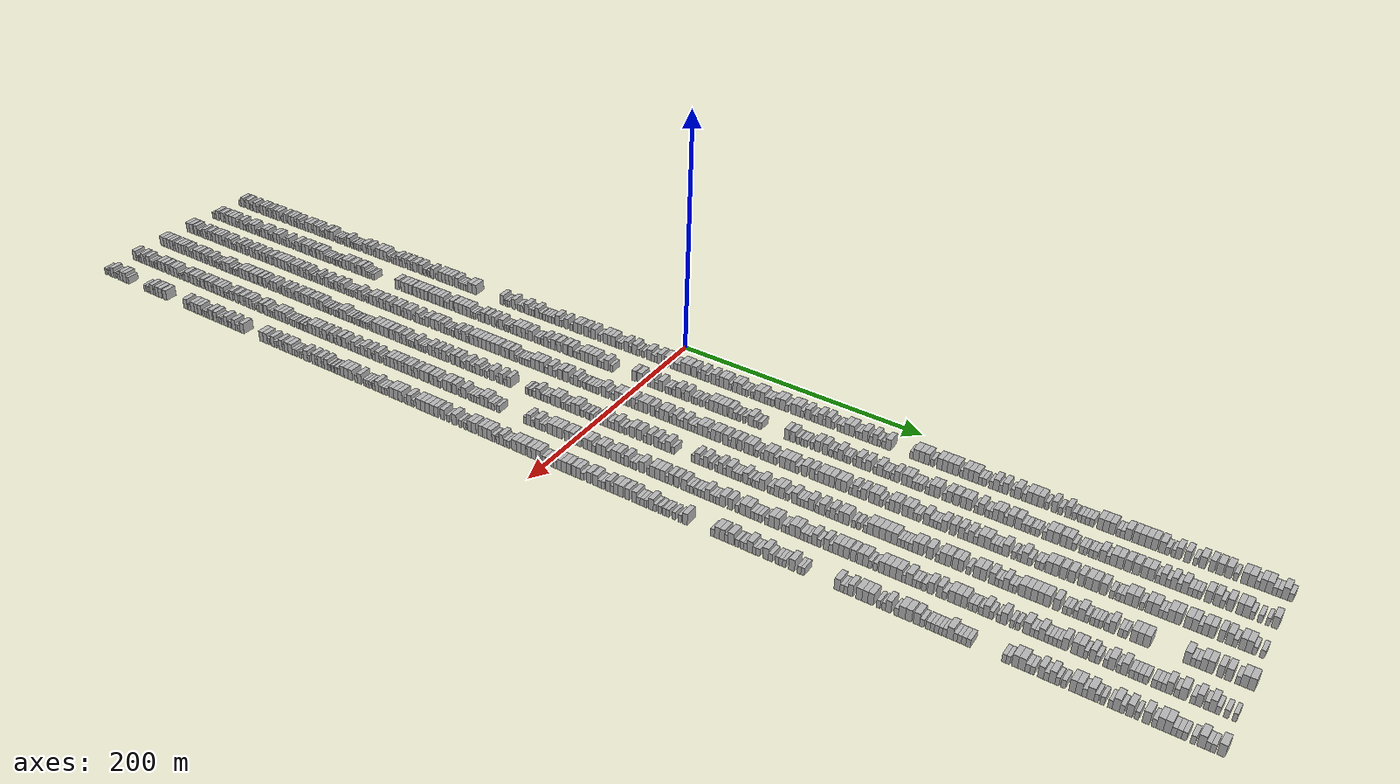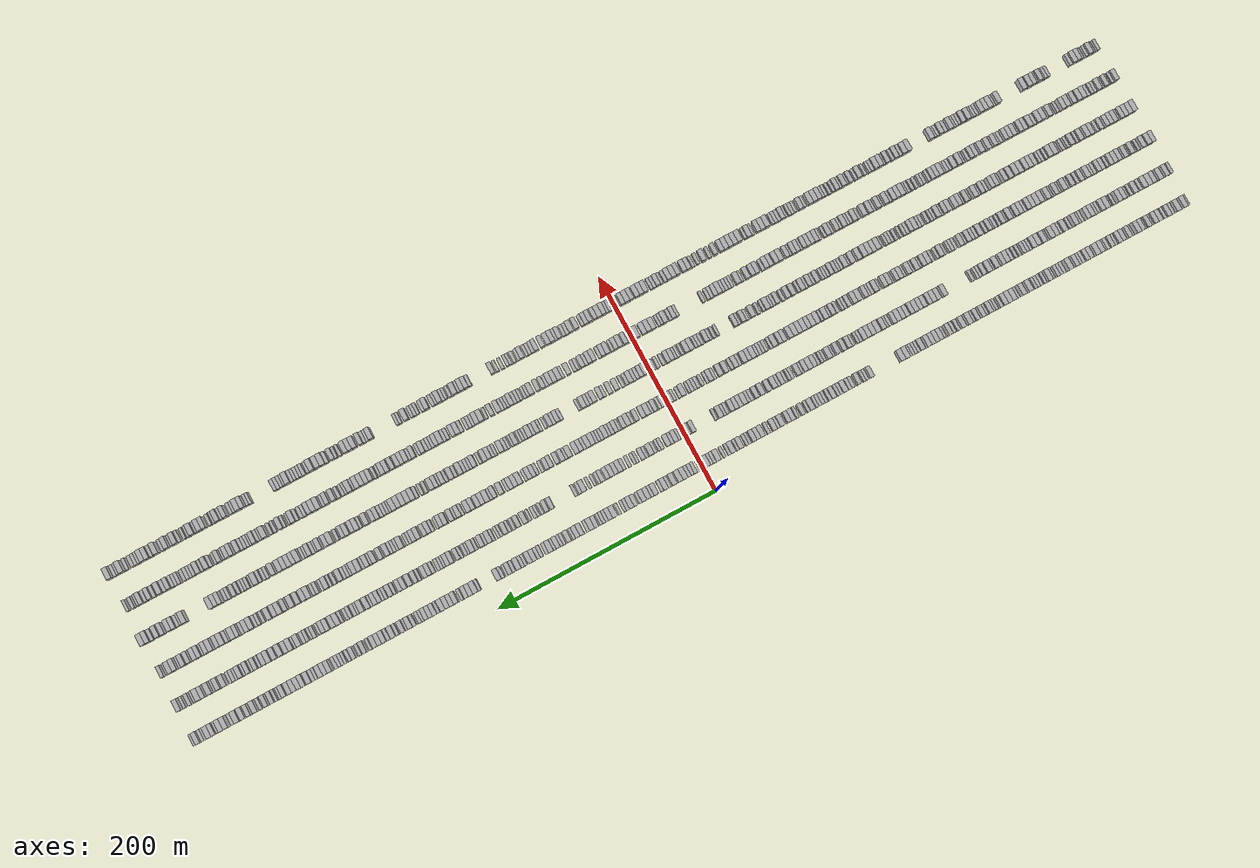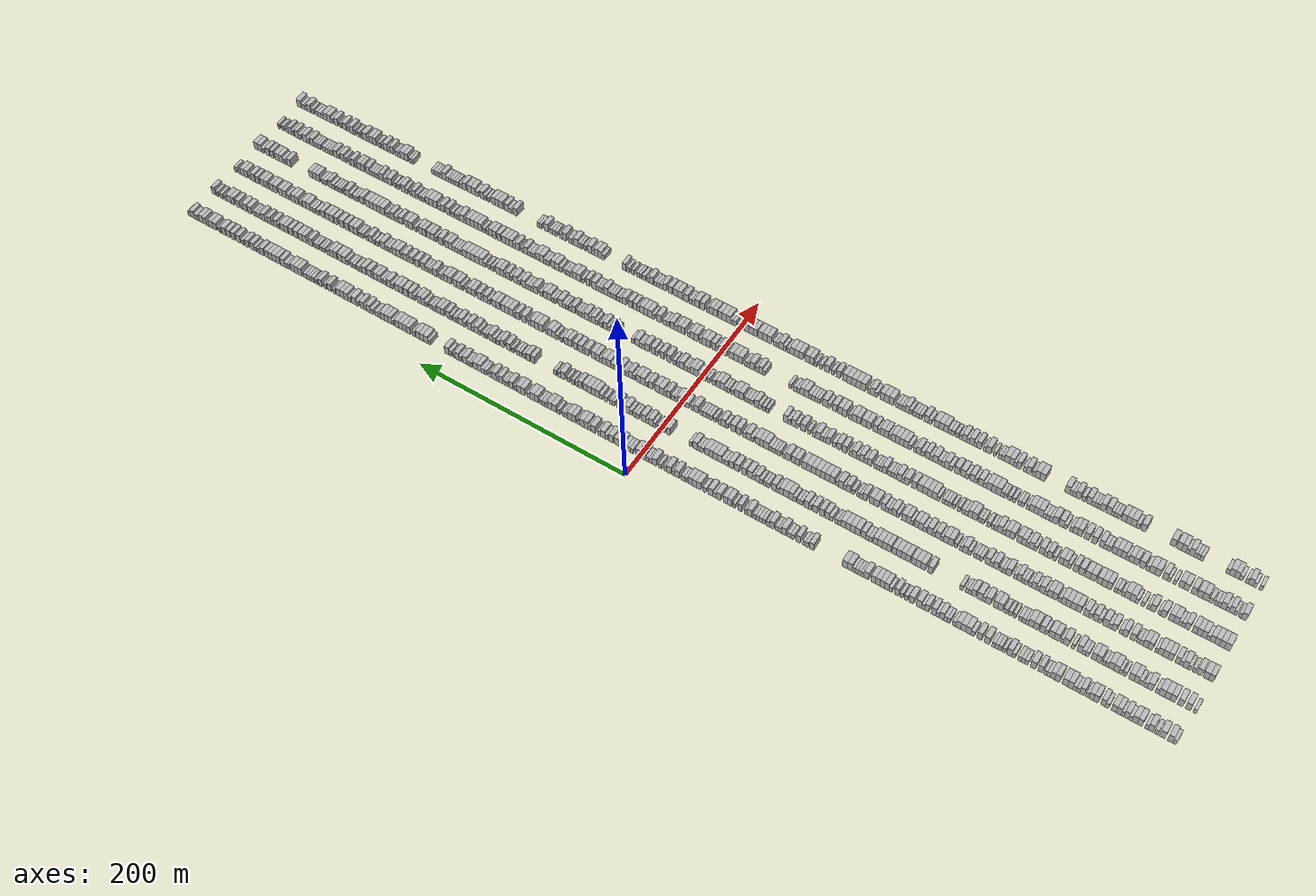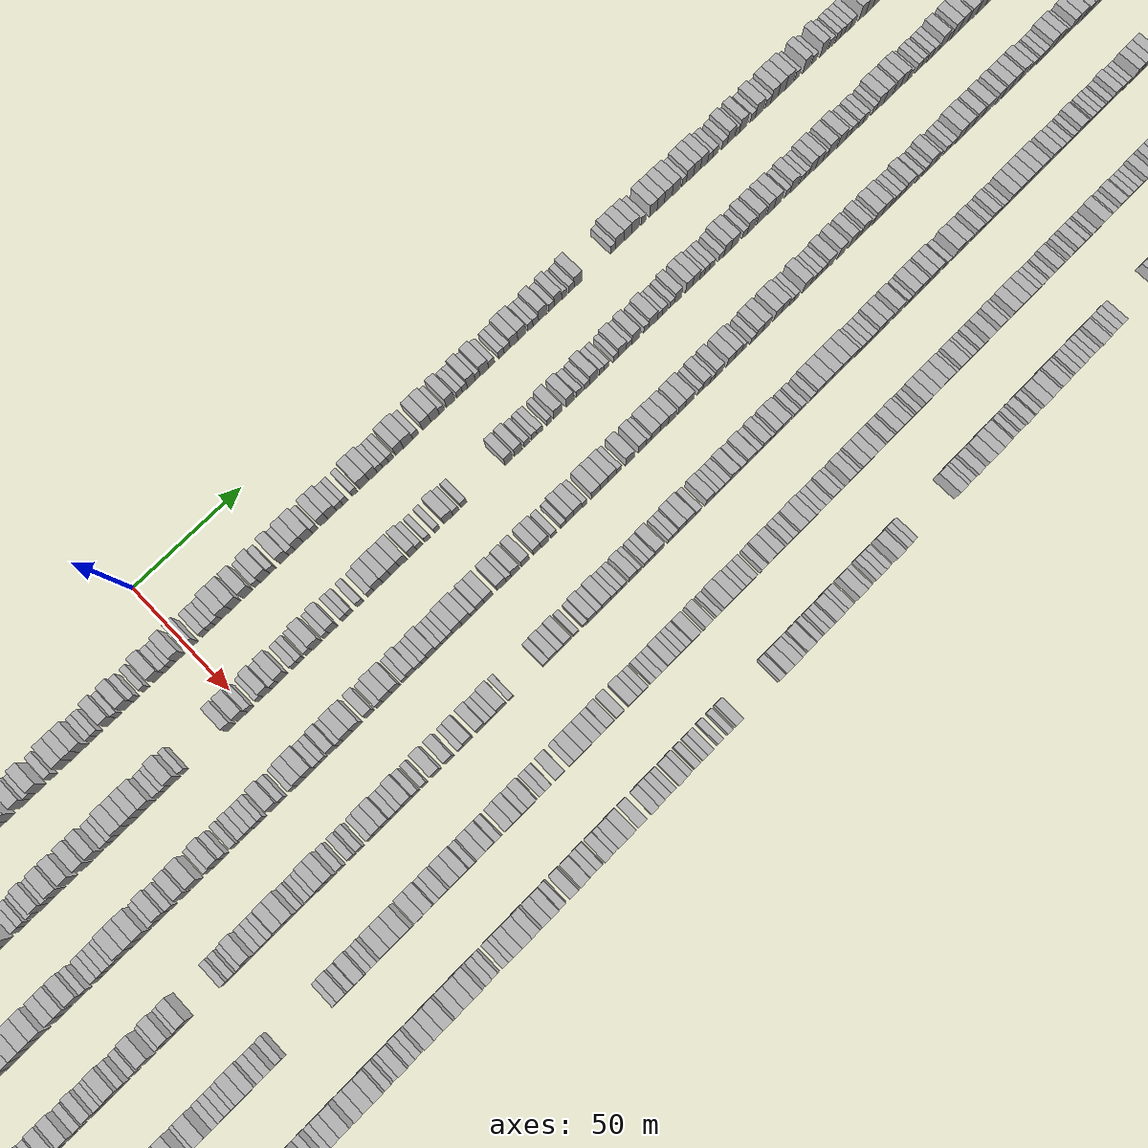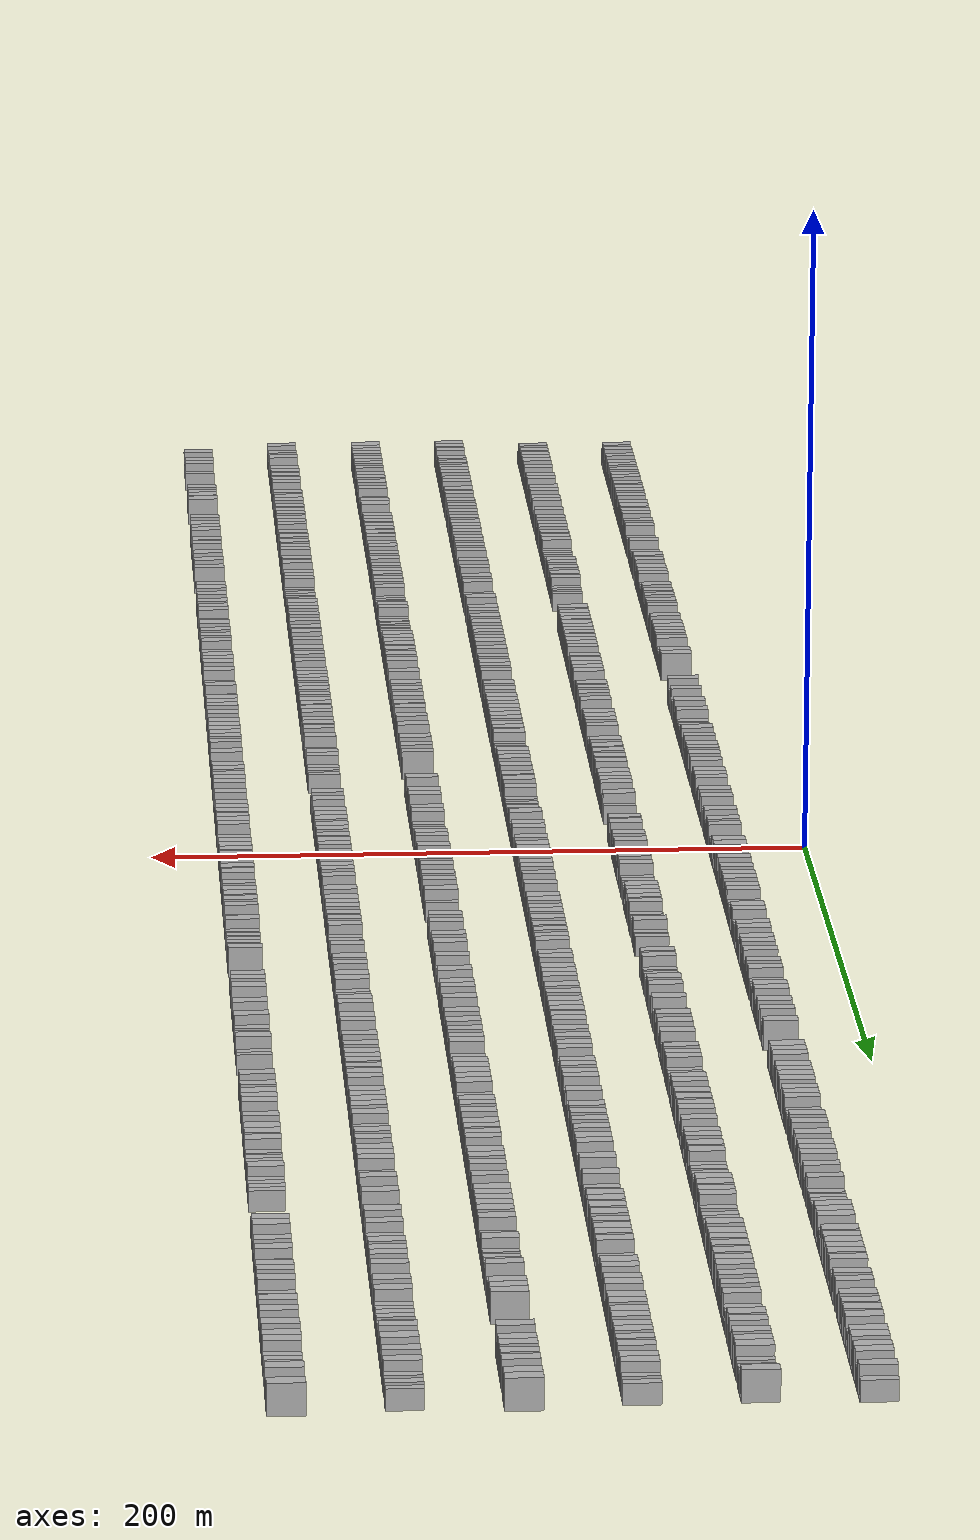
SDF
<sdf version="1.6">
 <world name="default">
  <scene>
   <sky><clouds><speed>12</speed></clouds></sky>
   <ambient>0.4 0.4 0.4 1</ambient>
   <background>0.7 0.7 0.7 1</background>
   <shadows>1</shadows>
  </scene>
  <gravity>0 0 -9.8066</gravity>
  <magnetic_field>6e-06 2.3e-05 -4.2e-05</magnetic_field>
  <physics default="0" name="default_physics" type="ode">
   <ode>
    <solver>
     <type>quick</type>
     <iters>10</iters>
     <sor>1.0</sor>
     <use_dynamic_moi_rescaling>0</use_dynamic_moi_rescaling>
    </solver>
    <constraints>
     <cfm>0</cfm>
     <erp>0.2</erp>
     <contact_max_correcting_vel>100</contact_max_correcting_vel>
     <contact_surface_layer>0.001</contact_surface_layer>
    </constraints>
   </ode>
   <max_step_size>0.004</max_step_size>
   <real_time_factor>1</real_time_factor>
   <real_time_update_rate>250</real_time_update_rate>
  </physics>
  <light name="sun" type="directional">
   <pose>0 0 10 0 0 0</pose>
   <diffuse>0.8 0.8 0.8 1</diffuse>
   <specular>0.2 0.2 0.2 1</specular>
   <attenuation>
    <range>1000</range>
    <constant>0.9</constant>
    <linear>0.01</linear>
    <quadratic>0.001</quadratic>
   </attenuation>
   <direction>-0.5 0.1 -0.9</direction>
  </light>
  <model name="building_1">
   <static>1</static>
   <pose>25.0000 -456.6130 0 0.000000 0.000000 0.000000</pose>
   <link name="link">
    <pose>0 0 3.00 0 0 0</pose>
    <collision name="collision"><geometry><box><size>10.0000 2.7740 6.0000</size></box></geometry></collision>
    <visual name="visual">
     <cast_shadows>0</cast_shadows>
     <geometry><box><size>10.0000 2.7740 6.0000</size></box></geometry>
     <material>
      <script>
       <uri>model://HANNAS_wall/materials/scripts</uri>
       <uri>model://HANNAS_wall/materials/textures</uri>
       <name>vrc/HANNAS_wall</name>
      </script>
     </material>
    </visual>
   </link>
  </model>
  <model name="building_2">
   <static>1</static>
   <pose>25.0000 -453.1696 0 0.000000 0.000000 0.000000</pose>
   <link name="link">
    <pose>0 0 4.50 0 0 0</pose>
    <collision name="collision"><geometry><box><size>10.0000 4.1128 9.0000</size></box></geometry></collision>
    <visual name="visual">
     <cast_shadows>0</cast_shadows>
     <geometry><box><size>10.0000 4.1128 9.0000</size></box></geometry>
     <material>
      <script>
       <uri>model://HANNAS_wall/materials/scripts</uri>
       <uri>model://HANNAS_wall/materials/textures</uri>
       <name>vrc/HANNAS_wall</name>
      </script>
     </material>
    </visual>
   </link>
  </model>
  <model name="building_3">
   <static>1</static>
   <pose>25.0000 -446.9016 0 0.000000 0.000000 0.000000</pose>
   <link name="link">
    <pose>0 0 4.50 0 0 0</pose>
    <collision name="collision"><geometry><box><size>10.0000 4.4232 9.0000</size></box></geometry></collision>
    <visual name="visual">
     <cast_shadows>0</cast_shadows>
     <geometry><box><size>10.0000 4.4232 9.0000</size></box></geometry>
     <material>
      <script>
       <uri>model://HANNAS_wall/materials/scripts</uri>
       <uri>model://HANNAS_wall/materials/textures</uri>
       <name>vrc/HANNAS_wall</name>
      </script>
     </material>
    </visual>
   </link>
  </model>
  <model name="building_4">
   <static>1</static>
   <pose>25.0000 -442.2487 0 0.000000 0.000000 0.000000</pose>
   <link name="link">
    <pose>0 0 3.00 0 0 0</pose>
    <collision name="collision"><geometry><box><size>10.0000 2.8826 6.0000</size></box></geometry></collision>
    <visual name="visual">
     <cast_shadows>0</cast_shadows>
     <geometry><box><size>10.0000 2.8826 6.0000</size></box></geometry>
     <material>
      <script>
       <uri>model://HANNAS_wall/materials/scripts</uri>
       <uri>model://HANNAS_wall/materials/textures</uri>
       <name>vrc/HANNAS_wall</name>
      </script>
     </material>
    </visual>
   </link>
  </model>
  <model name="building_5">
   <static>1</static>
   <pose>25.0000 -437.8552 0 0.000000 0.000000 0.000000</pose>
   <link name="link">
    <pose>0 0 4.50 0 0 0</pose>
    <collision name="collision"><geometry><box><size>10.0000 3.9045 9.0000</size></box></geometry></collision>
    <visual name="visual">
     <cast_shadows>0</cast_shadows>
     <geometry><box><size>10.0000 3.9045 9.0000</size></box></geometry>
     <material>
      <script>
       <uri>model://HANNAS_wall/materials/scripts</uri>
       <uri>model://HANNAS_wall/materials/textures</uri>
       <name>vrc/HANNAS_wall</name>
      </script>
     </material>
    </visual>
   </link>
  </model>
  <model name="building_6">
   <static>1</static>
   <pose>25.0000 -434.5747 0 0.000000 0.000000 0.000000</pose>
   <link name="link">
    <pose>0 0 3.00 0 0 0</pose>
    <collision name="collision"><geometry><box><size>10.0000 2.6566 6.0000</size></box></geometry></collision>
    <visual name="visual">
     <cast_shadows>0</cast_shadows>
     <geometry><box><size>10.0000 2.6566 6.0000</size></box></geometry>
     <material>
      <script>
       <uri>model://HANNAS_wall/materials/scripts</uri>
       <uri>model://HANNAS_wall/materials/textures</uri>
       <name>vrc/HANNAS_wall</name>
      </script>
     </material>
    </visual>
   </link>
  </model>
  <model name="building_7">
   <static>1</static>
   <pose>25.0000 -429.2692 0 0.000000 0.000000 0.000000</pose>
   <link name="link">
    <pose>0 0 4.50 0 0 0</pose>
    <collision name="collision"><geometry><box><size>10.0000 3.9545 9.0000</size></box></geometry></collision>
    <visual name="visual">
     <cast_shadows>0</cast_shadows>
     <geometry><box><size>10.0000 3.9545 9.0000</size></box></geometry>
     <material>
      <script>
       <uri>model://HANNAS_wall/materials/scripts</uri>
       <uri>model://HANNAS_wall/materials/textures</uri>
       <name>vrc/HANNAS_wall</name>
      </script>
     </material>
    </visual>
   </link>
  </model>
  <model name="building_8">
   <static>1</static>
   <pose>25.0000 -425.3371 0 0.000000 0.000000 0.000000</pose>
   <link name="link">
    <pose>0 0 4.50 0 0 0</pose>
    <collision name="collision"><geometry><box><size>10.0000 3.9096 9.0000</size></box></geometry></collision>
    <visual name="visual">
     <cast_shadows>0</cast_shadows>
     <geometry><box><size>10.0000 3.9096 9.0000</size></box></geometry>
     <material>
      <script>
       <uri>model://HANNAS_wall/materials/scripts</uri>
       <uri>model://HANNAS_wall/materials/textures</uri>
       <name>vrc/HANNAS_wall</name>
      </script>
     </material>
    </visual>
   </link>
  </model>
  <model name="building_9">
   <static>1</static>
   <pose>25.0000 -422.0106 0 0.000000 0.000000 0.000000</pose>
   <link name="link">
    <pose>0 0 3.00 0 0 0</pose>
    <collision name="collision"><geometry><box><size>10.0000 2.7435 6.0000</size></box></geometry></collision>
    <visual name="visual">
     <cast_shadows>0</cast_shadows>
     <geometry><box><size>10.0000 2.7435 6.0000</size></box></geometry>
     <material>
      <script>
       <uri>model://HANNAS_wall/materials/scripts</uri>
       <uri>model://HANNAS_wall/materials/textures</uri>
       <name>vrc/HANNAS_wall</name>
      </script>
     </material>
    </visual>
   </link>
  </model>
  <model name="building_10">
   <static>1</static>
   <pose>25.0000 -418.7983 0 0.000000 0.000000 0.000000</pose>
   <link name="link">
    <pose>0 0 4.50 0 0 0</pose>
    <collision name="collision"><geometry><box><size>10.0000 3.6812 9.0000</size></box></geometry></collision>
    <visual name="visual">
     <cast_shadows>0</cast_shadows>
     <geometry><box><size>10.0000 3.6812 9.0000</size></box></geometry>
     <material>
      <script>
       <uri>model://HANNAS_wall/materials/scripts</uri>
       <uri>model://HANNAS_wall/materials/textures</uri>
       <name>vrc/HANNAS_wall</name>
      </script>
     </material>
    </visual>
   </link>
  </model>
  <model name="building_11">
   <static>1</static>
   <pose>25.0000 -415.7499 0 0.000000 0.000000 0.000000</pose>
   <link name="link">
    <pose>0 0 3.00 0 0 0</pose>
    <collision name="collision"><geometry><box><size>10.0000 2.4156 6.0000</size></box></geometry></collision>
    <visual name="visual">
     <cast_shadows>0</cast_shadows>
     <geometry><box><size>10.0000 2.4156 6.0000</size></box></geometry>
     <material>
      <script>
       <uri>model://HANNAS_wall/materials/scripts</uri>
       <uri>model://HANNAS_wall/materials/textures</uri>
       <name>vrc/HANNAS_wall</name>
      </script>
     </material>
    </visual>
   </link>
  </model>
  <model name="building_12">
   <static>1</static>
   <pose>25.0000 -412.6947 0 0.000000 0.000000 0.000000</pose>
   <link name="link">
    <pose>0 0 4.50 0 0 0</pose>
    <collision name="collision"><geometry><box><size>10.0000 3.6948 9.0000</size></box></geometry></collision>
    <visual name="visual">
     <cast_shadows>0</cast_shadows>
     <geometry><box><size>10.0000 3.6948 9.0000</size></box></geometry>
     <material>
      <script>
       <uri>model://HANNAS_wall/materials/scripts</uri>
       <uri>model://HANNAS_wall/materials/textures</uri>
       <name>vrc/HANNAS_wall</name>
      </script>
     </material>
    </visual>
   </link>
  </model>
  <model name="building_13">
   <static>1</static>
   <pose>25.0000 -408.8557 0 0.000000 0.000000 0.000000</pose>
   <link name="link">
    <pose>0 0 4.50 0 0 0</pose>
    <collision name="collision"><geometry><box><size>10.0000 3.9831 9.0000</size></box></geometry></collision>
    <visual name="visual">
     <cast_shadows>0</cast_shadows>
     <geometry><box><size>10.0000 3.9831 9.0000</size></box></geometry>
     <material>
      <script>
       <uri>model://HANNAS_wall/materials/scripts</uri>
       <uri>model://HANNAS_wall/materials/textures</uri>
       <name>vrc/HANNAS_wall</name>
      </script>
     </material>
    </visual>
   </link>
  </model>
  <model name="building_14">
   <static>1</static>
   <pose>25.0000 -403.4761 0 0.000000 0.000000 0.000000</pose>
   <link name="link">
    <pose>0 0 3.00 0 0 0</pose>
    <collision name="collision"><geometry><box><size>10.0000 2.7761 6.0000</size></box></geometry></collision>
    <visual name="visual">
     <cast_shadows>0</cast_shadows>
     <geometry><box><size>10.0000 2.7761 6.0000</size></box></geometry>
     <material>
      <script>
       <uri>model://HANNAS_wall/materials/scripts</uri>
       <uri>model://HANNAS_wall/materials/textures</uri>
       <name>vrc/HANNAS_wall</name>
      </script>
     </material>
    </visual>
   </link>
  </model>
  <model name="building_15">
   <static>1</static>
   <pose>25.0000 -400.2772 0 0.000000 0.000000 0.000000</pose>
   <link name="link">
    <pose>0 0 4.50 0 0 0</pose>
    <collision name="collision"><geometry><box><size>10.0000 3.6216 9.0000</size></box></geometry></collision>
    <visual name="visual">
     <cast_shadows>0</cast_shadows>
     <geometry><box><size>10.0000 3.6216 9.0000</size></box></geometry>
     <material>
      <script>
       <uri>model://HANNAS_wall/materials/scripts</uri>
       <uri>model://HANNAS_wall/materials/textures</uri>
       <name>vrc/HANNAS_wall</name>
      </script>
     </material>
    </visual>
   </link>
  </model>
  <model name="building_16">
   <static>1</static>
   <pose>25.0000 -394.6449 0 0.000000 0.000000 0.000000</pose>
   <link name="link">
    <pose>0 0 4.50 0 0 0</pose>
    <collision name="collision"><geometry><box><size>10.0000 3.6431 9.0000</size></box></geometry></collision>
    <visual name="visual">
     <cast_shadows>0</cast_shadows>
     <geometry><box><size>10.0000 3.6431 9.0000</size></box></geometry>
     <material>
      <script>
       <uri>model://HANNAS_wall/materials/scripts</uri>
       <uri>model://HANNAS_wall/materials/textures</uri>
       <name>vrc/HANNAS_wall</name>
      </script>
     </material>
    </visual>
   </link>
  </model>
  <model name="building_17">
   <static>1</static>
   <pose>25.0000 -390.8557 0 0.000000 0.000000 0.000000</pose>
   <link name="link">
    <pose>0 0 4.50 0 0 0</pose>
    <collision name="collision"><geometry><box><size>10.0000 3.9353 9.0000</size></box></geometry></collision>
    <visual name="visual">
     <cast_shadows>0</cast_shadows>
     <geometry><box><size>10.0000 3.9353 9.0000</size></box></geometry>
     <material>
      <script>
       <uri>model://HANNAS_wall/materials/scripts</uri>
       <uri>model://HANNAS_wall/materials/textures</uri>
       <name>vrc/HANNAS_wall</name>
      </script>
     </material>
    </visual>
   </link>
  </model>
  <model name="building_18">
   <static>1</static>
   <pose>25.0000 -387.6611 0 0.000000 0.000000 0.000000</pose>
   <link name="link">
    <pose>0 0 3.00 0 0 0</pose>
    <collision name="collision"><geometry><box><size>10.0000 2.4538 6.0000</size></box></geometry></collision>
    <visual name="visual">
     <cast_shadows>0</cast_shadows>
     <geometry><box><size>10.0000 2.4538 6.0000</size></box></geometry>
     <material>
      <script>
       <uri>model://HANNAS_wall/materials/scripts</uri>
       <uri>model://HANNAS_wall/materials/textures</uri>
       <name>vrc/HANNAS_wall</name>
      </script>
     </material>
    </visual>
   </link>
  </model>
  <model name="building_19">
   <static>1</static>
   <pose>25.0000 -383.6210 0 0.000000 0.000000 0.000000</pose>
   <link name="link">
    <pose>0 0 4.50 0 0 0</pose>
    <collision name="collision"><geometry><box><size>10.0000 3.6266 9.0000</size></box></geometry></collision>
    <visual name="visual">
     <cast_shadows>0</cast_shadows>
     <geometry><box><size>10.0000 3.6266 9.0000</size></box></geometry>
     <material>
      <script>
       <uri>model://HANNAS_wall/materials/scripts</uri>
       <uri>model://HANNAS_wall/materials/textures</uri>
       <name>vrc/HANNAS_wall</name>
      </script>
     </material>
    </visual>
   </link>
  </model>
  <model name="building_20">
   <static>1</static>
   <pose>25.0000 -380.3133 0 0.000000 0.000000 0.000000</pose>
   <link name="link">
    <pose>0 0 3.00 0 0 0</pose>
    <collision name="collision"><geometry><box><size>10.0000 2.9887 6.0000</size></box></geometry></collision>
    <visual name="visual">
     <cast_shadows>0</cast_shadows>
     <geometry><box><size>10.0000 2.9887 6.0000</size></box></geometry>
     <material>
      <script>
       <uri>model://HANNAS_wall/materials/scripts</uri>
       <uri>model://HANNAS_wall/materials/textures</uri>
       <name>vrc/HANNAS_wall</name>
      </script>
     </material>
    </visual>
   </link>
  </model>
  <model name="building_21">
   <static>1</static>
   <pose>25.0000 -377.5056 0 0.000000 0.000000 0.000000</pose>
   <link name="link">
    <pose>0 0 3.00 0 0 0</pose>
    <collision name="collision"><geometry><box><size>10.0000 2.6268 6.0000</size></box></geometry></collision>
    <visual name="visual">
     <cast_shadows>0</cast_shadows>
     <geometry><box><size>10.0000 2.6268 6.0000</size></box></geometry>
     <material>
      <script>
       <uri>model://HANNAS_wall/materials/scripts</uri>
       <uri>model://HANNAS_wall/materials/textures</uri>
       <name>vrc/HANNAS_wall</name>
      </script>
     </material>
    </visual>
   </link>
  </model>
  <model name="building_22">
   <static>1</static>
   <pose>25.0000 -374.1128 0 0.000000 0.000000 0.000000</pose>
   <link name="link">
    <pose>0 0 4.50 0 0 0</pose>
    <collision name="collision"><geometry><box><size>10.0000 4.1588 9.0000</size></box></geometry></collision>
    <visual name="visual">
     <cast_shadows>0</cast_shadows>
     <geometry><box><size>10.0000 4.1588 9.0000</size></box></geometry>
     <material>
      <script>
       <uri>model://HANNAS_wall/materials/scripts</uri>
       <uri>model://HANNAS_wall/materials/textures</uri>
       <name>vrc/HANNAS_wall</name>
      </script>
     </material>
    </visual>
   </link>
  </model>
  <model name="building_23">
   <static>1</static>
   <pose>25.0000 -369.7850 0 0.000000 0.000000 0.000000</pose>
   <link name="link">
    <pose>0 0 4.50 0 0 0</pose>
    <collision name="collision"><geometry><box><size>10.0000 4.4967 9.0000</size></box></geometry></collision>
    <visual name="visual">
     <cast_shadows>0</cast_shadows>
     <geometry><box><size>10.0000 4.4967 9.0000</size></box></geometry>
     <material>
      <script>
       <uri>model://HANNAS_wall/materials/scripts</uri>
       <uri>model://HANNAS_wall/materials/textures</uri>
       <name>vrc/HANNAS_wall</name>
      </script>
     </material>
    </visual>
   </link>
  </model>
  <model name="building_24">
   <static>1</static>
   <pose>25.0000 -363.6430 0 0.000000 0.000000 0.000000</pose>
   <link name="link">
    <pose>0 0 4.50 0 0 0</pose>
    <collision name="collision"><geometry><box><size>10.0000 3.7874 9.0000</size></box></geometry></collision>
    <visual name="visual">
     <cast_shadows>0</cast_shadows>
     <geometry><box><size>10.0000 3.7874 9.0000</size></box></geometry>
     <material>
      <script>
       <uri>model://HANNAS_wall/materials/scripts</uri>
       <uri>model://HANNAS_wall/materials/textures</uri>
       <name>vrc/HANNAS_wall</name>
      </script>
     </material>
    </visual>
   </link>
  </model>
  <model name="building_25">
   <static>1</static>
   <pose>25.0000 -359.9301 0 0.000000 0.000000 0.000000</pose>
   <link name="link">
    <pose>0 0 4.50 0 0 0</pose>
    <collision name="collision"><geometry><box><size>10.0000 3.6384 9.0000</size></box></geometry></collision>
    <visual name="visual">
     <cast_shadows>0</cast_shadows>
     <geometry><box><size>10.0000 3.6384 9.0000</size></box></geometry>
     <material>
      <script>
       <uri>model://HANNAS_wall/materials/scripts</uri>
       <uri>model://HANNAS_wall/materials/textures</uri>
       <name>vrc/HANNAS_wall</name>
      </script>
     </material>
    </visual>
   </link>
  </model>
  <model name="building_26">
   <static>1</static>
   <pose>25.0000 -356.6710 0 0.000000 0.000000 0.000000</pose>
   <link name="link">
    <pose>0 0 3.00 0 0 0</pose>
    <collision name="collision"><geometry><box><size>10.0000 2.8800 6.0000</size></box></geometry></collision>
    <visual name="visual">
     <cast_shadows>0</cast_shadows>
     <geometry><box><size>10.0000 2.8800 6.0000</size></box></geometry>
     <material>
      <script>
       <uri>model://HANNAS_wall/materials/scripts</uri>
       <uri>model://HANNAS_wall/materials/textures</uri>
       <name>vrc/HANNAS_wall</name>
      </script>
     </material>
    </visual>
   </link>
  </model>
  <model name="building_27">
   <static>1</static>
   <pose>25.0000 -354.0282 0 0.000000 0.000000 0.000000</pose>
   <link name="link">
    <pose>0 0 3.00 0 0 0</pose>
    <collision name="collision"><geometry><box><size>10.0000 2.4056 6.0000</size></box></geometry></collision>
    <visual name="visual">
     <cast_shadows>0</cast_shadows>
     <geometry><box><size>10.0000 2.4056 6.0000</size></box></geometry>
     <material>
      <script>
       <uri>model://HANNAS_wall/materials/scripts</uri>
       <uri>model://HANNAS_wall/materials/textures</uri>
       <name>vrc/HANNAS_wall</name>
      </script>
     </material>
    </visual>
   </link>
  </model>
  <model name="building_28">
   <static>1</static>
   <pose>25.0000 -350.0129 0 0.000000 0.000000 0.000000</pose>
   <link name="link">
    <pose>0 0 4.50 0 0 0</pose>
    <collision name="collision"><geometry><box><size>10.0000 3.6251 9.0000</size></box></geometry></collision>
    <visual name="visual">
     <cast_shadows>0</cast_shadows>
     <geometry><box><size>10.0000 3.6251 9.0000</size></box></geometry>
     <material>
      <script>
       <uri>model://HANNAS_wall/materials/scripts</uri>
       <uri>model://HANNAS_wall/materials/textures</uri>
       <name>vrc/HANNAS_wall</name>
      </script>
     </material>
    </visual>
   </link>
  </model>
  <model name="building_29">
   <static>1</static>
   <pose>25.0000 -344.0259 0 0.000000 0.000000 0.000000</pose>
   <link name="link">
    <pose>0 0 4.50 0 0 0</pose>
    <collision name="collision"><geometry><box><size>10.0000 4.3489 9.0000</size></box></geometry></collision>
    <visual name="visual">
     <cast_shadows>0</cast_shadows>
     <geometry><box><size>10.0000 4.3489 9.0000</size></box></geometry>
     <material>
      <script>
       <uri>model://HANNAS_wall/materials/scripts</uri>
       <uri>model://HANNAS_wall/materials/textures</uri>
       <name>vrc/HANNAS_wall</name>
      </script>
     </material>
    </visual>
   </link>
  </model>
  <model name="building_30">
   <static>1</static>
   <pose>25.0000 -338.4252 0 0.000000 0.000000 0.000000</pose>
   <link name="link">
    <pose>0 0 3.00 0 0 0</pose>
    <collision name="collision"><geometry><box><size>10.0000 2.8525 6.0000</size></box></geometry></collision>
    <visual name="visual">
     <cast_shadows>0</cast_shadows>
     <geometry><box><size>10.0000 2.8525 6.0000</size></box></geometry>
     <material>
      <script>
       <uri>model://HANNAS_wall/materials/scripts</uri>
       <uri>model://HANNAS_wall/materials/textures</uri>
       <name>vrc/HANNAS_wall</name>
      </script>
     </material>
    </visual>
   </link>
  </model>
  <model name="building_31">
   <static>1</static>
   <pose>25.0000 -335.6791 0 0.000000 0.000000 0.000000</pose>
   <link name="link">
    <pose>0 0 3.00 0 0 0</pose>
    <collision name="collision"><geometry><box><size>10.0000 2.6395 6.0000</size></box></geometry></collision>
    <visual name="visual">
     <cast_shadows>0</cast_shadows>
     <geometry><box><size>10.0000 2.6395 6.0000</size></box></geometry>
     <material>
      <script>
       <uri>model://HANNAS_wall/materials/scripts</uri>
       <uri>model://HANNAS_wall/materials/textures</uri>
       <name>vrc/HANNAS_wall</name>
      </script>
     </material>
    </visual>
   </link>
  </model>
  <model name="building_32">
   <static>1</static>
   <pose>25.0000 -332.9013 0 0.000000 0.000000 0.000000</pose>
   <link name="link">
    <pose>0 0 3.00 0 0 0</pose>
    <collision name="collision"><geometry><box><size>10.0000 2.9161 6.0000</size></box></geometry></collision>
    <visual name="visual">
     <cast_shadows>0</cast_shadows>
     <geometry><box><size>10.0000 2.9161 6.0000</size></box></geometry>
     <material>
      <script>
       <uri>model://HANNAS_wall/materials/scripts</uri>
       <uri>model://HANNAS_wall/materials/textures</uri>
       <name>vrc/HANNAS_wall</name>
      </script>
     </material>
    </visual>
   </link>
  </model>
  <model name="building_33">
   <static>1</static>
   <pose>25.0000 -328.0461 0 0.000000 0.000000 0.000000</pose>
   <link name="link">
    <pose>0 0 3.00 0 0 0</pose>
    <collision name="collision"><geometry><box><size>10.0000 2.7944 6.0000</size></box></geometry></collision>
    <visual name="visual">
     <cast_shadows>0</cast_shadows>
     <geometry><box><size>10.0000 2.7944 6.0000</size></box></geometry>
     <material>
      <script>
       <uri>model://HANNAS_wall/materials/scripts</uri>
       <uri>model://HANNAS_wall/materials/textures</uri>
       <name>vrc/HANNAS_wall</name>
      </script>
     </material>
    </visual>
   </link>
  </model>
  <model name="building_34">
   <static>1</static>
   <pose>25.0000 -324.6168 0 0.000000 0.000000 0.000000</pose>
   <link name="link">
    <pose>0 0 4.50 0 0 0</pose>
    <collision name="collision"><geometry><box><size>10.0000 4.0642 9.0000</size></box></geometry></collision>
    <visual name="visual">
     <cast_shadows>0</cast_shadows>
     <geometry><box><size>10.0000 4.0642 9.0000</size></box></geometry>
     <material>
      <script>
       <uri>model://HANNAS_wall/materials/scripts</uri>
       <uri>model://HANNAS_wall/materials/textures</uri>
       <name>vrc/HANNAS_wall</name>
      </script>
     </material>
    </visual>
   </link>
  </model>
  <model name="building_35">
   <static>1</static>
   <pose>25.0000 -320.3229 0 0.000000 0.000000 0.000000</pose>
   <link name="link">
    <pose>0 0 3.00 0 0 0</pose>
    <collision name="collision"><geometry><box><size>10.0000 2.5237 6.0000</size></box></geometry></collision>
    <visual name="visual">
     <cast_shadows>0</cast_shadows>
     <geometry><box><size>10.0000 2.5237 6.0000</size></box></geometry>
     <material>
      <script>
       <uri>model://HANNAS_wall/materials/scripts</uri>
       <uri>model://HANNAS_wall/materials/textures</uri>
       <name>vrc/HANNAS_wall</name>
      </script>
     </material>
    </visual>
   </link>
  </model>
  <model name="building_36">
   <static>1</static>
   <pose>25.0000 -316.7487 0 0.000000 0.000000 0.000000</pose>
   <link name="link">
    <pose>0 0 3.00 0 0 0</pose>
    <collision name="collision"><geometry><box><size>10.0000 2.6246 6.0000</size></box></geometry></collision>
    <visual name="visual">
     <cast_shadows>0</cast_shadows>
     <geometry><box><size>10.0000 2.6246 6.0000</size></box></geometry>
     <material>
      <script>
       <uri>model://HANNAS_wall/materials/scripts</uri>
       <uri>model://HANNAS_wall/materials/textures</uri>
       <name>vrc/HANNAS_wall</name>
      </script>
     </material>
    </visual>
   </link>
  </model>
  <model name="building_37">
   <static>1</static>
   <pose>25.0000 -314.0464 0 0.000000 0.000000 0.000000</pose>
   <link name="link">
    <pose>0 0 3.00 0 0 0</pose>
    <collision name="collision"><geometry><box><size>10.0000 2.7800 6.0000</size></box></geometry></collision>
    <visual name="visual">
     <cast_shadows>0</cast_shadows>
     <geometry><box><size>10.0000 2.7800 6.0000</size></box></geometry>
     <material>
      <script>
       <uri>model://HANNAS_wall/materials/scripts</uri>
       <uri>model://HANNAS_wall/materials/textures</uri>
       <name>vrc/HANNAS_wall</name>
      </script>
     </material>
    </visual>
   </link>
  </model>
  <model name="building_38">
   <static>1</static>
   <pose>25.0000 -311.4103 0 0.000000 0.000000 0.000000</pose>
   <link name="link">
    <pose>0 0 3.00 0 0 0</pose>
    <collision name="collision"><geometry><box><size>10.0000 2.4922 6.0000</size></box></geometry></collision>
    <visual name="visual">
     <cast_shadows>0</cast_shadows>
     <geometry><box><size>10.0000 2.4922 6.0000</size></box></geometry>
     <material>
      <script>
       <uri>model://HANNAS_wall/materials/scripts</uri>
       <uri>model://HANNAS_wall/materials/textures</uri>
       <name>vrc/HANNAS_wall</name>
      </script>
     </material>
    </visual>
   </link>
  </model>
  <model name="building_39">
   <static>1</static>
   <pose>25.0000 -306.0003 0 0.000000 0.000000 0.000000</pose>
   <link name="link">
    <pose>0 0 4.50 0 0 0</pose>
    <collision name="collision"><geometry><box><size>10.0000 4.3278 9.0000</size></box></geometry></collision>
    <visual name="visual">
     <cast_shadows>0</cast_shadows>
     <geometry><box><size>10.0000 4.3278 9.0000</size></box></geometry>
     <material>
      <script>
       <uri>model://HANNAS_wall/materials/scripts</uri>
       <uri>model://HANNAS_wall/materials/textures</uri>
       <name>vrc/HANNAS_wall</name>
      </script>
     </material>
    </visual>
   </link>
  </model>
  <model name="building_40">
   <static>1</static>
   <pose>25.0000 -299.8229 0 0.000000 0.000000 0.000000</pose>
   <link name="link">
    <pose>0 0 4.50 0 0 0</pose>
    <collision name="collision"><geometry><box><size>10.0000 4.0270 9.0000</size></box></geometry></collision>
    <visual name="visual">
     <cast_shadows>0</cast_shadows>
     <geometry><box><size>10.0000 4.0270 9.0000</size></box></geometry>
     <material>
      <script>
       <uri>model://HANNAS_wall/materials/scripts</uri>
       <uri>model://HANNAS_wall/materials/textures</uri>
       <name>vrc/HANNAS_wall</name>
      </script>
     </material>
    </visual>
   </link>
  </model>
  <model name="building_41">
   <static>1</static>
   <pose>25.0000 -294.3111 0 0.000000 0.000000 0.000000</pose>
   <link name="link">
    <pose>0 0 3.00 0 0 0</pose>
    <collision name="collision"><geometry><box><size>10.0000 2.9968 6.0000</size></box></geometry></collision>
    <visual name="visual">
     <cast_shadows>0</cast_shadows>
     <geometry><box><size>10.0000 2.9968 6.0000</size></box></geometry>
     <material>
      <script>
       <uri>model://HANNAS_wall/materials/scripts</uri>
       <uri>model://HANNAS_wall/materials/textures</uri>
       <name>vrc/HANNAS_wall</name>
      </script>
     </material>
    </visual>
   </link>
  </model>
  <model name="building_42">
   <static>1</static>
   <pose>25.0000 -290.6540 0 0.000000 0.000000 0.000000</pose>
   <link name="link">
    <pose>0 0 4.50 0 0 0</pose>
    <collision name="collision"><geometry><box><size>10.0000 4.3174 9.0000</size></box></geometry></collision>
    <visual name="visual">
     <cast_shadows>0</cast_shadows>
     <geometry><box><size>10.0000 4.3174 9.0000</size></box></geometry>
     <material>
      <script>
       <uri>model://HANNAS_wall/materials/scripts</uri>
       <uri>model://HANNAS_wall/materials/textures</uri>
       <name>vrc/HANNAS_wall</name>
      </script>
     </material>
    </visual>
   </link>
  </model>
  <model name="building_43">
   <static>1</static>
   <pose>25.0000 -286.3703 0 0.000000 0.000000 0.000000</pose>
   <link name="link">
    <pose>0 0 4.50 0 0 0</pose>
    <collision name="collision"><geometry><box><size>10.0000 4.2500 9.0000</size></box></geometry></collision>
    <visual name="visual">
     <cast_shadows>0</cast_shadows>
     <geometry><box><size>10.0000 4.2500 9.0000</size></box></geometry>
     <material>
      <script>
       <uri>model://HANNAS_wall/materials/scripts</uri>
       <uri>model://HANNAS_wall/materials/textures</uri>
       <name>vrc/HANNAS_wall</name>
      </script>
     </material>
    </visual>
   </link>
  </model>
  <model name="building_44">
   <static>1</static>
   <pose>25.0000 -282.2408 0 0.000000 0.000000 0.000000</pose>
   <link name="link">
    <pose>0 0 4.50 0 0 0</pose>
    <collision name="collision"><geometry><box><size>10.0000 4.0090 9.0000</size></box></geometry></collision>
    <visual name="visual">
     <cast_shadows>0</cast_shadows>
     <geometry><box><size>10.0000 4.0090 9.0000</size></box></geometry>
     <material>
      <script>
       <uri>model://HANNAS_wall/materials/scripts</uri>
       <uri>model://HANNAS_wall/materials/textures</uri>
       <name>vrc/HANNAS_wall</name>
      </script>
     </material>
    </visual>
   </link>
  </model>
  <model name="building_45">
   <static>1</static>
   <pose>25.0000 -278.8270 0 0.000000 0.000000 0.000000</pose>
   <link name="link">
    <pose>0 0 3.00 0 0 0</pose>
    <collision name="collision"><geometry><box><size>10.0000 2.8187 6.0000</size></box></geometry></collision>
    <visual name="visual">
     <cast_shadows>0</cast_shadows>
     <geometry><box><size>10.0000 2.8187 6.0000</size></box></geometry>
     <material>
      <script>
       <uri>model://HANNAS_wall/materials/scripts</uri>
       <uri>model://HANNAS_wall/materials/textures</uri>
       <name>vrc/HANNAS_wall</name>
      </script>
     </material>
    </visual>
   </link>
  </model>
  <model name="building_46">
   <static>1</static>
   <pose>25.0000 -274.2003 0 0.000000 0.000000 0.000000</pose>
   <link name="link">
    <pose>0 0 3.00 0 0 0</pose>
    <collision name="collision"><geometry><box><size>10.0000 2.4347 6.0000</size></box></geometry></collision>
    <visual name="visual">
     <cast_shadows>0</cast_shadows>
     <geometry><box><size>10.0000 2.4347 6.0000</size></box></geometry>
     <material>
      <script>
       <uri>model://HANNAS_wall/materials/scripts</uri>
       <uri>model://HANNAS_wall/materials/textures</uri>
       <name>vrc/HANNAS_wall</name>
      </script>
     </material>
    </visual>
   </link>
  </model>
  <model name="building_47">
   <static>1</static>
   <pose>25.0000 -271.5685 0 0.000000 0.000000 0.000000</pose>
   <link name="link">
    <pose>0 0 3.00 0 0 0</pose>
    <collision name="collision"><geometry><box><size>10.0000 2.8289 6.0000</size></box></geometry></collision>
    <visual name="visual">
     <cast_shadows>0</cast_shadows>
     <geometry><box><size>10.0000 2.8289 6.0000</size></box></geometry>
     <material>
      <script>
       <uri>model://HANNAS_wall/materials/scripts</uri>
       <uri>model://HANNAS_wall/materials/textures</uri>
       <name>vrc/HANNAS_wall</name>
      </script>
     </material>
    </visual>
   </link>
  </model>
  <model name="building_48">
   <static>1</static>
   <pose>25.0000 -268.2330 0 0.000000 0.000000 0.000000</pose>
   <link name="link">
    <pose>0 0 4.50 0 0 0</pose>
    <collision name="collision"><geometry><box><size>10.0000 3.8420 9.0000</size></box></geometry></collision>
    <visual name="visual">
     <cast_shadows>0</cast_shadows>
     <geometry><box><size>10.0000 3.8420 9.0000</size></box></geometry>
     <material>
      <script>
       <uri>model://HANNAS_wall/materials/scripts</uri>
       <uri>model://HANNAS_wall/materials/textures</uri>
       <name>vrc/HANNAS_wall</name>
      </script>
     </material>
    </visual>
   </link>
  </model>
  <model name="building_49">
   <static>1</static>
   <pose>25.0000 -264.8440 0 0.000000 0.000000 0.000000</pose>
   <link name="link">
    <pose>0 0 3.00 0 0 0</pose>
    <collision name="collision"><geometry><box><size>10.0000 2.9360 6.0000</size></box></geometry></collision>
    <visual name="visual">
     <cast_shadows>0</cast_shadows>
     <geometry><box><size>10.0000 2.9360 6.0000</size></box></geometry>
     <material>
      <script>
       <uri>model://HANNAS_wall/materials/scripts</uri>
       <uri>model://HANNAS_wall/materials/textures</uri>
       <name>vrc/HANNAS_wall</name>
      </script>
     </material>
    </visual>
   </link>
  </model>
  <model name="building_50">
   <static>1</static>
   <pose>25.0000 -261.4907 0 0.000000 0.000000 0.000000</pose>
   <link name="link">
    <pose>0 0 4.50 0 0 0</pose>
    <collision name="collision"><geometry><box><size>10.0000 3.7706 9.0000</size></box></geometry></collision>
    <visual name="visual">
     <cast_shadows>0</cast_shadows>
     <geometry><box><size>10.0000 3.7706 9.0000</size></box></geometry>
     <material>
      <script>
       <uri>model://HANNAS_wall/materials/scripts</uri>
       <uri>model://HANNAS_wall/materials/textures</uri>
       <name>vrc/HANNAS_wall</name>
      </script>
     </material>
    </visual>
   </link>
  </model>
  <model name="building_51">
   <static>1</static>
   <pose>25.0000 -255.8040 0 0.000000 0.000000 0.000000</pose>
   <link name="link">
    <pose>0 0 4.50 0 0 0</pose>
    <collision name="collision"><geometry><box><size>10.0000 3.6027 9.0000</size></box></geometry></collision>
    <visual name="visual">
     <cast_shadows>0</cast_shadows>
     <geometry><box><size>10.0000 3.6027 9.0000</size></box></geometry>
     <material>
      <script>
       <uri>model://HANNAS_wall/materials/scripts</uri>
       <uri>model://HANNAS_wall/materials/textures</uri>
       <name>vrc/HANNAS_wall</name>
      </script>
     </material>
    </visual>
   </link>
  </model>
  <model name="building_52">
   <static>1</static>
   <pose>25.0000 -252.6086 0 0.000000 0.000000 0.000000</pose>
   <link name="link">
    <pose>0 0 3.00 0 0 0</pose>
    <collision name="collision"><geometry><box><size>10.0000 2.7881 6.0000</size></box></geometry></collision>
    <visual name="visual">
     <cast_shadows>0</cast_shadows>
     <geometry><box><size>10.0000 2.7881 6.0000</size></box></geometry>
     <material>
      <script>
       <uri>model://HANNAS_wall/materials/scripts</uri>
       <uri>model://HANNAS_wall/materials/textures</uri>
       <name>vrc/HANNAS_wall</name>
      </script>
     </material>
    </visual>
   </link>
  </model>
  <model name="building_53">
   <static>1</static>
   <pose>25.0000 -249.0260 0 0.000000 0.000000 0.000000</pose>
   <link name="link">
    <pose>0 0 4.50 0 0 0</pose>
    <collision name="collision"><geometry><box><size>10.0000 4.3770 9.0000</size></box></geometry></collision>
    <visual name="visual">
     <cast_shadows>0</cast_shadows>
     <geometry><box><size>10.0000 4.3770 9.0000</size></box></geometry>
     <material>
      <script>
       <uri>model://HANNAS_wall/materials/scripts</uri>
       <uri>model://HANNAS_wall/materials/textures</uri>
       <name>vrc/HANNAS_wall</name>
      </script>
     </material>
    </visual>
   </link>
  </model>
  <model name="building_54">
   <static>1</static>
   <pose>25.0000 -242.7408 0 0.000000 0.000000 0.000000</pose>
   <link name="link">
    <pose>0 0 4.50 0 0 0</pose>
    <collision name="collision"><geometry><box><size>10.0000 4.1934 9.0000</size></box></geometry></collision>
    <visual name="visual">
     <cast_shadows>0</cast_shadows>
     <geometry><box><size>10.0000 4.1934 9.0000</size></box></geometry>
     <material>
      <script>
       <uri>model://HANNAS_wall/materials/scripts</uri>
       <uri>model://HANNAS_wall/materials/textures</uri>
       <name>vrc/HANNAS_wall</name>
      </script>
     </material>
    </visual>
   </link>
  </model>
  <model name="building_55">
   <static>1</static>
   <pose>25.0000 -238.1700 0 0.000000 0.000000 0.000000</pose>
   <link name="link">
    <pose>0 0 3.00 0 0 0</pose>
    <collision name="collision"><geometry><box><size>10.0000 2.9482 6.0000</size></box></geometry></collision>
    <visual name="visual">
     <cast_shadows>0</cast_shadows>
     <geometry><box><size>10.0000 2.9482 6.0000</size></box></geometry>
     <material>
      <script>
       <uri>model://HANNAS_wall/materials/scripts</uri>
       <uri>model://HANNAS_wall/materials/textures</uri>
       <name>vrc/HANNAS_wall</name>
      </script>
     </material>
    </visual>
   </link>
  </model>
  <model name="building_56">
   <static>1</static>
   <pose>25.0000 -234.3784 0 0.000000 0.000000 0.000000</pose>
   <link name="link">
    <pose>0 0 3.00 0 0 0</pose>
    <collision name="collision"><geometry><box><size>10.0000 2.6350 6.0000</size></box></geometry></collision>
    <visual name="visual">
     <cast_shadows>0</cast_shadows>
     <geometry><box><size>10.0000 2.6350 6.0000</size></box></geometry>
     <material>
      <script>
       <uri>model://HANNAS_wall/materials/scripts</uri>
       <uri>model://HANNAS_wall/materials/textures</uri>
       <name>vrc/HANNAS_wall</name>
      </script>
     </material>
    </visual>
   </link>
  </model>
  <model name="building_57">
   <static>1</static>
   <pose>25.0000 -230.2231 0 0.000000 0.000000 0.000000</pose>
   <link name="link">
    <pose>0 0 4.50 0 0 0</pose>
    <collision name="collision"><geometry><box><size>10.0000 3.6756 9.0000</size></box></geometry></collision>
    <visual name="visual">
     <cast_shadows>0</cast_shadows>
     <geometry><box><size>10.0000 3.6756 9.0000</size></box></geometry>
     <material>
      <script>
       <uri>model://HANNAS_wall/materials/scripts</uri>
       <uri>model://HANNAS_wall/materials/textures</uri>
       <name>vrc/HANNAS_wall</name>
      </script>
     </material>
    </visual>
   </link>
  </model>
  <model name="building_58">
   <static>1</static>
   <pose>25.0000 -225.0237 0 0.000000 0.000000 0.000000</pose>
   <link name="link">
    <pose>0 0 3.00 0 0 0</pose>
    <collision name="collision"><geometry><box><size>10.0000 2.7231 6.0000</size></box></geometry></collision>
    <visual name="visual">
     <cast_shadows>0</cast_shadows>
     <geometry><box><size>10.0000 2.7231 6.0000</size></box></geometry>
     <material>
      <script>
       <uri>model://HANNAS_wall/materials/scripts</uri>
       <uri>model://HANNAS_wall/materials/textures</uri>
       <name>vrc/HANNAS_wall</name>
      </script>
     </material>
    </visual>
   </link>
  </model>
  <model name="building_59">
   <static>1</static>
   <pose>25.0000 -221.7079 0 0.000000 0.000000 0.000000</pose>
   <link name="link">
    <pose>0 0 4.50 0 0 0</pose>
    <collision name="collision"><geometry><box><size>10.0000 3.9086 9.0000</size></box></geometry></collision>
    <visual name="visual">
     <cast_shadows>0</cast_shadows>
     <geometry><box><size>10.0000 3.9086 9.0000</size></box></geometry>
     <material>
      <script>
       <uri>model://HANNAS_wall/materials/scripts</uri>
       <uri>model://HANNAS_wall/materials/textures</uri>
       <name>vrc/HANNAS_wall</name>
      </script>
     </material>
    </visual>
   </link>
  </model>
  <model name="building_60">
   <static>1</static>
   <pose>25.0000 -217.8412 0 0.000000 0.000000 0.000000</pose>
   <link name="link">
    <pose>0 0 4.50 0 0 0</pose>
    <collision name="collision"><geometry><box><size>10.0000 3.8248 9.0000</size></box></geometry></collision>
    <visual name="visual">
     <cast_shadows>0</cast_shadows>
     <geometry><box><size>10.0000 3.8248 9.0000</size></box></geometry>
     <material>
      <script>
       <uri>model://HANNAS_wall/materials/scripts</uri>
       <uri>model://HANNAS_wall/materials/textures</uri>
       <name>vrc/HANNAS_wall</name>
      </script>
     </material>
    </visual>
   </link>
  </model>
  <model name="building_61">
   <static>1</static>
   <pose>25.0000 -214.0150 0 0.000000 0.000000 0.000000</pose>
   <link name="link">
    <pose>0 0 4.50 0 0 0</pose>
    <collision name="collision"><geometry><box><size>10.0000 3.8276 9.0000</size></box></geometry></collision>
    <visual name="visual">
     <cast_shadows>0</cast_shadows>
     <geometry><box><size>10.0000 3.8276 9.0000</size></box></geometry>
     <material>
      <script>
       <uri>model://HANNAS_wall/materials/scripts</uri>
       <uri>model://HANNAS_wall/materials/textures</uri>
       <name>vrc/HANNAS_wall</name>
      </script>
     </material>
    </visual>
   </link>
  </model>
  <model name="building_62">
   <static>1</static>
   <pose>25.0000 -210.1196 0 0.000000 0.000000 0.000000</pose>
   <link name="link">
    <pose>0 0 4.50 0 0 0</pose>
    <collision name="collision"><geometry><box><size>10.0000 3.9632 9.0000</size></box></geometry></collision>
    <visual name="visual">
     <cast_shadows>0</cast_shadows>
     <geometry><box><size>10.0000 3.9632 9.0000</size></box></geometry>
     <material>
      <script>
       <uri>model://HANNAS_wall/materials/scripts</uri>
       <uri>model://HANNAS_wall/materials/textures</uri>
       <name>vrc/HANNAS_wall</name>
      </script>
     </material>
    </visual>
   </link>
  </model>
  <model name="building_63">
   <static>1</static>
   <pose>25.0000 -204.0271 0 0.000000 0.000000 0.000000</pose>
   <link name="link">
    <pose>0 0 4.50 0 0 0</pose>
    <collision name="collision"><geometry><box><size>10.0000 4.2218 9.0000</size></box></geometry></collision>
    <visual name="visual">
     <cast_shadows>0</cast_shadows>
     <geometry><box><size>10.0000 4.2218 9.0000</size></box></geometry>
     <material>
      <script>
       <uri>model://HANNAS_wall/materials/scripts</uri>
       <uri>model://HANNAS_wall/materials/textures</uri>
       <name>vrc/HANNAS_wall</name>
      </script>
     </material>
    </visual>
   </link>
  </model>
  <model name="building_64">
   <static>1</static>
   <pose>25.0000 -200.6370 0 0.000000 0.000000 0.000000</pose>
   <link name="link">
    <pose>0 0 3.00 0 0 0</pose>
    <collision name="collision"><geometry><box><size>10.0000 2.5585 6.0000</size></box></geometry></collision>
    <visual name="visual">
     <cast_shadows>0</cast_shadows>
     <geometry><box><size>10.0000 2.5585 6.0000</size></box></geometry>
     <material>
      <script>
       <uri>model://HANNAS_wall/materials/scripts</uri>
       <uri>model://HANNAS_wall/materials/textures</uri>
       <name>vrc/HANNAS_wall</name>
      </script>
     </material>
    </visual>
   </link>
  </model>
  <model name="building_65">
   <static>1</static>
   <pose>25.0000 -198.1208 0 0.000000 0.000000 0.000000</pose>
   <link name="link">
    <pose>0 0 3.00 0 0 0</pose>
    <collision name="collision"><geometry><box><size>10.0000 2.4739 6.0000</size></box></geometry></collision>
    <visual name="visual">
     <cast_shadows>0</cast_shadows>
     <geometry><box><size>10.0000 2.4739 6.0000</size></box></geometry>
     <material>
      <script>
       <uri>model://HANNAS_wall/materials/scripts</uri>
       <uri>model://HANNAS_wall/materials/textures</uri>
       <name>vrc/HANNAS_wall</name>
      </script>
     </material>
    </visual>
   </link>
  </model>
  <model name="building_66">
   <static>1</static>
   <pose>25.0000 -195.6406 0 0.000000 0.000000 0.000000</pose>
   <link name="link">
    <pose>0 0 3.00 0 0 0</pose>
    <collision name="collision"><geometry><box><size>10.0000 2.4864 6.0000</size></box></geometry></collision>
    <visual name="visual">
     <cast_shadows>0</cast_shadows>
     <geometry><box><size>10.0000 2.4864 6.0000</size></box></geometry>
     <material>
      <script>
       <uri>model://HANNAS_wall/materials/scripts</uri>
       <uri>model://HANNAS_wall/materials/textures</uri>
       <name>vrc/HANNAS_wall</name>
      </script>
     </material>
    </visual>
   </link>
  </model>
  <model name="building_67">
   <static>1</static>
   <pose>25.0000 -193.1570 0 0.000000 0.000000 0.000000</pose>
   <link name="link">
    <pose>0 0 3.00 0 0 0</pose>
    <collision name="collision"><geometry><box><size>10.0000 2.4807 6.0000</size></box></geometry></collision>
    <visual name="visual">
     <cast_shadows>0</cast_shadows>
     <geometry><box><size>10.0000 2.4807 6.0000</size></box></geometry>
     <material>
      <script>
       <uri>model://HANNAS_wall/materials/scripts</uri>
       <uri>model://HANNAS_wall/materials/textures</uri>
       <name>vrc/HANNAS_wall</name>
      </script>
     </material>
    </visual>
   </link>
  </model>
  <model name="building_68">
   <static>1</static>
   <pose>25.0000 -189.8249 0 0.000000 0.000000 0.000000</pose>
   <link name="link">
    <pose>0 0 4.50 0 0 0</pose>
    <collision name="collision"><geometry><box><size>10.0000 4.1835 9.0000</size></box></geometry></collision>
    <visual name="visual">
     <cast_shadows>0</cast_shadows>
     <geometry><box><size>10.0000 4.1835 9.0000</size></box></geometry>
     <material>
      <script>
       <uri>model://HANNAS_wall/materials/scripts</uri>
       <uri>model://HANNAS_wall/materials/textures</uri>
       <name>vrc/HANNAS_wall</name>
      </script>
     </material>
    </visual>
   </link>
  </model>
  <model name="building_69">
   <static>1</static>
   <pose>25.0000 -185.4884 0 0.000000 0.000000 0.000000</pose>
   <link name="link">
    <pose>0 0 4.50 0 0 0</pose>
    <collision name="collision"><geometry><box><size>10.0000 4.4895 9.0000</size></box></geometry></collision>
    <visual name="visual">
     <cast_shadows>0</cast_shadows>
     <geometry><box><size>10.0000 4.4895 9.0000</size></box></geometry>
     <material>
      <script>
       <uri>model://HANNAS_wall/materials/scripts</uri>
       <uri>model://HANNAS_wall/materials/textures</uri>
       <name>vrc/HANNAS_wall</name>
      </script>
     </material>
    </visual>
   </link>
  </model>
  <model name="building_70">
   <static>1</static>
   <pose>25.0000 -156.4802 0 0.000000 0.000000 0.000000</pose>
   <link name="link">
    <pose>0 0 4.50 0 0 0</pose>
    <collision name="collision"><geometry><box><size>10.0000 3.8423 9.0000</size></box></geometry></collision>
    <visual name="visual">
     <cast_shadows>0</cast_shadows>
     <geometry><box><size>10.0000 3.8423 9.0000</size></box></geometry>
     <material>
      <script>
       <uri>model://HANNAS_wall/materials/scripts</uri>
       <uri>model://HANNAS_wall/materials/textures</uri>
       <name>vrc/HANNAS_wall</name>
      </script>
     </material>
    </visual>
   </link>
  </model>
  <model name="building_71">
   <static>1</static>
   <pose>25.0000 -152.2642 0 0.000000 0.000000 0.000000</pose>
   <link name="link">
    <pose>0 0 3.00 0 0 0</pose>
    <collision name="collision"><geometry><box><size>10.0000 2.5897 6.0000</size></box></geometry></collision>
    <visual name="visual">
     <cast_shadows>0</cast_shadows>
     <geometry><box><size>10.0000 2.5897 6.0000</size></box></geometry>
     <material>
      <script>
       <uri>model://HANNAS_wall/materials/scripts</uri>
       <uri>model://HANNAS_wall/materials/textures</uri>
       <name>vrc/HANNAS_wall</name>
      </script>
     </material>
    </visual>
   </link>
  </model>
  <model name="building_72">
   <static>1</static>
   <pose>25.0000 -149.7639 0 0.000000 0.000000 0.000000</pose>
   <link name="link">
    <pose>0 0 3.00 0 0 0</pose>
    <collision name="collision"><geometry><box><size>10.0000 2.4107 6.0000</size></box></geometry></collision>
    <visual name="visual">
     <cast_shadows>0</cast_shadows>
     <geometry><box><size>10.0000 2.4107 6.0000</size></box></geometry>
     <material>
      <script>
       <uri>model://HANNAS_wall/materials/scripts</uri>
       <uri>model://HANNAS_wall/materials/textures</uri>
       <name>vrc/HANNAS_wall</name>
      </script>
     </material>
    </visual>
   </link>
  </model>
  <model name="building_73">
   <static>1</static>
   <pose>25.0000 -144.6903 0 0.000000 0.000000 0.000000</pose>
   <link name="link">
    <pose>0 0 4.50 0 0 0</pose>
    <collision name="collision"><geometry><box><size>10.0000 3.7367 9.0000</size></box></geometry></collision>
    <visual name="visual">
     <cast_shadows>0</cast_shadows>
     <geometry><box><size>10.0000 3.7367 9.0000</size></box></geometry>
     <material>
      <script>
       <uri>model://HANNAS_wall/materials/scripts</uri>
       <uri>model://HANNAS_wall/materials/textures</uri>
       <name>vrc/HANNAS_wall</name>
      </script>
     </material>
    </visual>
   </link>
  </model>
  <model name="building_74">
   <static>1</static>
   <pose>25.0000 -139.3331 0 0.000000 0.000000 0.000000</pose>
   <link name="link">
    <pose>0 0 3.00 0 0 0</pose>
    <collision name="collision"><geometry><box><size>10.0000 2.9777 6.0000</size></box></geometry></collision>
    <visual name="visual">
     <cast_shadows>0</cast_shadows>
     <geometry><box><size>10.0000 2.9777 6.0000</size></box></geometry>
     <material>
      <script>
       <uri>model://HANNAS_wall/materials/scripts</uri>
       <uri>model://HANNAS_wall/materials/textures</uri>
       <name>vrc/HANNAS_wall</name>
      </script>
     </material>
    </visual>
   </link>
  </model>
  <model name="building_75">
   <static>1</static>
   <pose>25.0000 -136.3701 0 0.000000 0.000000 0.000000</pose>
   <link name="link">
    <pose>0 0 3.00 0 0 0</pose>
    <collision name="collision"><geometry><box><size>10.0000 2.9482 6.0000</size></box></geometry></collision>
    <visual name="visual">
     <cast_shadows>0</cast_shadows>
     <geometry><box><size>10.0000 2.9482 6.0000</size></box></geometry>
     <material>
      <script>
       <uri>model://HANNAS_wall/materials/scripts</uri>
       <uri>model://HANNAS_wall/materials/textures</uri>
       <name>vrc/HANNAS_wall</name>
      </script>
     </material>
    </visual>
   </link>
  </model>
  <model name="building_76">
   <static>1</static>
   <pose>25.0000 -131.7027 0 0.000000 0.000000 0.000000</pose>
   <link name="link">
    <pose>0 0 4.50 0 0 0</pose>
    <collision name="collision"><geometry><box><size>10.0000 4.3865 9.0000</size></box></geometry></collision>
    <visual name="visual">
     <cast_shadows>0</cast_shadows>
     <geometry><box><size>10.0000 4.3865 9.0000</size></box></geometry>
     <material>
      <script>
       <uri>model://HANNAS_wall/materials/scripts</uri>
       <uri>model://HANNAS_wall/materials/textures</uri>
       <name>vrc/HANNAS_wall</name>
      </script>
     </material>
    </visual>
   </link>
  </model>
  <model name="building_77">
   <static>1</static>
   <pose>25.0000 -128.1891 0 0.000000 0.000000 0.000000</pose>
   <link name="link">
    <pose>0 0 3.00 0 0 0</pose>
    <collision name="collision"><geometry><box><size>10.0000 2.6407 6.0000</size></box></geometry></collision>
    <visual name="visual">
     <cast_shadows>0</cast_shadows>
     <geometry><box><size>10.0000 2.6407 6.0000</size></box></geometry>
     <material>
      <script>
       <uri>model://HANNAS_wall/materials/scripts</uri>
       <uri>model://HANNAS_wall/materials/textures</uri>
       <name>vrc/HANNAS_wall</name>
      </script>
     </material>
    </visual>
   </link>
  </model>
  <model name="building_78">
   <static>1</static>
   <pose>25.0000 -125.5254 0 0.000000 0.000000 0.000000</pose>
   <link name="link">
    <pose>0 0 3.00 0 0 0</pose>
    <collision name="collision"><geometry><box><size>10.0000 2.6868 6.0000</size></box></geometry></collision>
    <visual name="visual">
     <cast_shadows>0</cast_shadows>
     <geometry><box><size>10.0000 2.6868 6.0000</size></box></geometry>
     <material>
      <script>
       <uri>model://HANNAS_wall/materials/scripts</uri>
       <uri>model://HANNAS_wall/materials/textures</uri>
       <name>vrc/HANNAS_wall</name>
      </script>
     </material>
    </visual>
   </link>
  </model>
  <model name="building_79">
   <static>1</static>
   <pose>25.0000 -121.1328 0 0.000000 0.000000 0.000000</pose>
   <link name="link">
    <pose>0 0 4.50 0 0 0</pose>
    <collision name="collision"><geometry><box><size>10.0000 4.0984 9.0000</size></box></geometry></collision>
    <visual name="visual">
     <cast_shadows>0</cast_shadows>
     <geometry><box><size>10.0000 4.0984 9.0000</size></box></geometry>
     <material>
      <script>
       <uri>model://HANNAS_wall/materials/scripts</uri>
       <uri>model://HANNAS_wall/materials/textures</uri>
       <name>vrc/HANNAS_wall</name>
      </script>
     </material>
    </visual>
   </link>
  </model>
  <model name="building_80">
   <static>1</static>
   <pose>25.0000 -117.6221 0 0.000000 0.000000 0.000000</pose>
   <link name="link">
    <pose>0 0 3.00 0 0 0</pose>
    <collision name="collision"><geometry><box><size>10.0000 2.9230 6.0000</size></box></geometry></collision>
    <visual name="visual">
     <cast_shadows>0</cast_shadows>
     <geometry><box><size>10.0000 2.9230 6.0000</size></box></geometry>
     <material>
      <script>
       <uri>model://HANNAS_wall/materials/scripts</uri>
       <uri>model://HANNAS_wall/materials/textures</uri>
       <name>vrc/HANNAS_wall</name>
      </script>
     </material>
    </visual>
   </link>
  </model>
  <model name="building_81">
   <static>1</static>
   <pose>25.0000 -113.8651 0 0.000000 0.000000 0.000000</pose>
   <link name="link">
    <pose>0 0 3.00 0 0 0</pose>
    <collision name="collision"><geometry><box><size>10.0000 2.5910 6.0000</size></box></geometry></collision>
    <visual name="visual">
     <cast_shadows>0</cast_shadows>
     <geometry><box><size>10.0000 2.5910 6.0000</size></box></geometry>
     <material>
      <script>
       <uri>model://HANNAS_wall/materials/scripts</uri>
       <uri>model://HANNAS_wall/materials/textures</uri>
       <name>vrc/HANNAS_wall</name>
      </script>
     </material>
    </visual>
   </link>
  </model>
  <model name="building_82">
   <static>1</static>
   <pose>25.0000 -111.1434 0 0.000000 0.000000 0.000000</pose>
   <link name="link">
    <pose>0 0 3.00 0 0 0</pose>
    <collision name="collision"><geometry><box><size>10.0000 2.8523 6.0000</size></box></geometry></collision>
    <visual name="visual">
     <cast_shadows>0</cast_shadows>
     <geometry><box><size>10.0000 2.8523 6.0000</size></box></geometry>
     <material>
      <script>
       <uri>model://HANNAS_wall/materials/scripts</uri>
       <uri>model://HANNAS_wall/materials/textures</uri>
       <name>vrc/HANNAS_wall</name>
      </script>
     </material>
    </visual>
   </link>
  </model>
  <model name="building_83">
   <static>1</static>
   <pose>25.0000 -108.2769 0 0.000000 0.000000 0.000000</pose>
   <link name="link">
    <pose>0 0 3.00 0 0 0</pose>
    <collision name="collision"><geometry><box><size>10.0000 2.8808 6.0000</size></box></geometry></collision>
    <visual name="visual">
     <cast_shadows>0</cast_shadows>
     <geometry><box><size>10.0000 2.8808 6.0000</size></box></geometry>
     <material>
      <script>
       <uri>model://HANNAS_wall/materials/scripts</uri>
       <uri>model://HANNAS_wall/materials/textures</uri>
       <name>vrc/HANNAS_wall</name>
      </script>
     </material>
    </visual>
   </link>
  </model>
  <model name="building_84">
   <static>1</static>
   <pose>25.0000 -105.5612 0 0.000000 0.000000 0.000000</pose>
   <link name="link">
    <pose>0 0 3.00 0 0 0</pose>
    <collision name="collision"><geometry><box><size>10.0000 2.5506 6.0000</size></box></geometry></collision>
    <visual name="visual">
     <cast_shadows>0</cast_shadows>
     <geometry><box><size>10.0000 2.5506 6.0000</size></box></geometry>
     <material>
      <script>
       <uri>model://HANNAS_wall/materials/scripts</uri>
       <uri>model://HANNAS_wall/materials/textures</uri>
       <name>vrc/HANNAS_wall</name>
      </script>
     </material>
    </visual>
   </link>
  </model>
  <model name="building_85">
   <static>1</static>
   <pose>25.0000 -101.0731 0 0.000000 0.000000 0.000000</pose>
   <link name="link">
    <pose>0 0 4.50 0 0 0</pose>
    <collision name="collision"><geometry><box><size>10.0000 4.4258 9.0000</size></box></geometry></collision>
    <visual name="visual">
     <cast_shadows>0</cast_shadows>
     <geometry><box><size>10.0000 4.4258 9.0000</size></box></geometry>
     <material>
      <script>
       <uri>model://HANNAS_wall/materials/scripts</uri>
       <uri>model://HANNAS_wall/materials/textures</uri>
       <name>vrc/HANNAS_wall</name>
      </script>
     </material>
    </visual>
   </link>
  </model>
  <model name="building_86">
   <static>1</static>
   <pose>25.0000 -97.5372 0 0.000000 0.000000 0.000000</pose>
   <link name="link">
    <pose>0 0 3.00 0 0 0</pose>
    <collision name="collision"><geometry><box><size>10.0000 2.6460 6.0000</size></box></geometry></collision>
    <visual name="visual">
     <cast_shadows>0</cast_shadows>
     <geometry><box><size>10.0000 2.6460 6.0000</size></box></geometry>
     <material>
      <script>
       <uri>model://HANNAS_wall/materials/scripts</uri>
       <uri>model://HANNAS_wall/materials/textures</uri>
       <name>vrc/HANNAS_wall</name>
      </script>
     </material>
    </visual>
   </link>
  </model>
  <model name="building_87">
   <static>1</static>
   <pose>25.0000 -92.3547 0 0.000000 0.000000 0.000000</pose>
   <link name="link">
    <pose>0 0 4.50 0 0 0</pose>
    <collision name="collision"><geometry><box><size>10.0000 3.7190 9.0000</size></box></geometry></collision>
    <visual name="visual">
     <cast_shadows>0</cast_shadows>
     <geometry><box><size>10.0000 3.7190 9.0000</size></box></geometry>
     <material>
      <script>
       <uri>model://HANNAS_wall/materials/scripts</uri>
       <uri>model://HANNAS_wall/materials/textures</uri>
       <name>vrc/HANNAS_wall</name>
      </script>
     </material>
    </visual>
   </link>
  </model>
  <model name="building_88">
   <static>1</static>
   <pose>25.0000 -87.2801 0 0.000000 0.000000 0.000000</pose>
   <link name="link">
    <pose>0 0 3.00 0 0 0</pose>
    <collision name="collision"><geometry><box><size>10.0000 2.4302 6.0000</size></box></geometry></collision>
    <visual name="visual">
     <cast_shadows>0</cast_shadows>
     <geometry><box><size>10.0000 2.4302 6.0000</size></box></geometry>
     <material>
      <script>
       <uri>model://HANNAS_wall/materials/scripts</uri>
       <uri>model://HANNAS_wall/materials/textures</uri>
       <name>vrc/HANNAS_wall</name>
      </script>
     </material>
    </visual>
   </link>
  </model>
  <model name="building_89">
   <static>1</static>
   <pose>25.0000 -83.0822 0 0.000000 0.000000 0.000000</pose>
   <link name="link">
    <pose>0 0 4.50 0 0 0</pose>
    <collision name="collision"><geometry><box><size>10.0000 3.9657 9.0000</size></box></geometry></collision>
    <visual name="visual">
     <cast_shadows>0</cast_shadows>
     <geometry><box><size>10.0000 3.9657 9.0000</size></box></geometry>
     <material>
      <script>
       <uri>model://HANNAS_wall/materials/scripts</uri>
       <uri>model://HANNAS_wall/materials/textures</uri>
       <name>vrc/HANNAS_wall</name>
      </script>
     </material>
    </visual>
   </link>
  </model>
  <model name="building_90">
   <static>1</static>
   <pose>25.0000 -79.2211 0 0.000000 0.000000 0.000000</pose>
   <link name="link">
    <pose>0 0 4.50 0 0 0</pose>
    <collision name="collision"><geometry><box><size>10.0000 3.7565 9.0000</size></box></geometry></collision>
    <visual name="visual">
     <cast_shadows>0</cast_shadows>
     <geometry><box><size>10.0000 3.7565 9.0000</size></box></geometry>
     <material>
      <script>
       <uri>model://HANNAS_wall/materials/scripts</uri>
       <uri>model://HANNAS_wall/materials/textures</uri>
       <name>vrc/HANNAS_wall</name>
      </script>
     </material>
    </visual>
   </link>
  </model>
  <model name="building_91">
   <static>1</static>
   <pose>25.0000 -73.1525 0 0.000000 0.000000 0.000000</pose>
   <link name="link">
    <pose>0 0 4.50 0 0 0</pose>
    <collision name="collision"><geometry><box><size>10.0000 4.3806 9.0000</size></box></geometry></collision>
    <visual name="visual">
     <cast_shadows>0</cast_shadows>
     <geometry><box><size>10.0000 4.3806 9.0000</size></box></geometry>
     <material>
      <script>
       <uri>model://HANNAS_wall/materials/scripts</uri>
       <uri>model://HANNAS_wall/materials/textures</uri>
       <name>vrc/HANNAS_wall</name>
      </script>
     </material>
    </visual>
   </link>
  </model>
  <model name="building_92">
   <static>1</static>
   <pose>25.0000 -69.5285 0 0.000000 0.000000 0.000000</pose>
   <link name="link">
    <pose>0 0 3.00 0 0 0</pose>
    <collision name="collision"><geometry><box><size>10.0000 2.8675 6.0000</size></box></geometry></collision>
    <visual name="visual">
     <cast_shadows>0</cast_shadows>
     <geometry><box><size>10.0000 2.8675 6.0000</size></box></geometry>
     <material>
      <script>
       <uri>model://HANNAS_wall/materials/scripts</uri>
       <uri>model://HANNAS_wall/materials/textures</uri>
       <name>vrc/HANNAS_wall</name>
      </script>
     </material>
    </visual>
   </link>
  </model>
  <model name="building_93">
   <static>1</static>
   <pose>25.0000 -65.9982 0 0.000000 0.000000 0.000000</pose>
   <link name="link">
    <pose>0 0 4.50 0 0 0</pose>
    <collision name="collision"><geometry><box><size>10.0000 4.1932 9.0000</size></box></geometry></collision>
    <visual name="visual">
     <cast_shadows>0</cast_shadows>
     <geometry><box><size>10.0000 4.1932 9.0000</size></box></geometry>
     <material>
      <script>
       <uri>model://HANNAS_wall/materials/scripts</uri>
       <uri>model://HANNAS_wall/materials/textures</uri>
       <name>vrc/HANNAS_wall</name>
      </script>
     </material>
    </visual>
   </link>
  </model>
  <model name="building_94">
   <static>1</static>
   <pose>25.0000 -60.4333 0 0.000000 0.000000 0.000000</pose>
   <link name="link">
    <pose>0 0 3.00 0 0 0</pose>
    <collision name="collision"><geometry><box><size>10.0000 2.9366 6.0000</size></box></geometry></collision>
    <visual name="visual">
     <cast_shadows>0</cast_shadows>
     <geometry><box><size>10.0000 2.9366 6.0000</size></box></geometry>
     <material>
      <script>
       <uri>model://HANNAS_wall/materials/scripts</uri>
       <uri>model://HANNAS_wall/materials/textures</uri>
       <name>vrc/HANNAS_wall</name>
      </script>
     </material>
    </visual>
   </link>
  </model>
  <model name="building_95">
   <static>1</static>
   <pose>25.0000 -54.8550 0 0.000000 0.000000 0.000000</pose>
   <link name="link">
    <pose>0 0 4.50 0 0 0</pose>
    <collision name="collision"><geometry><box><size>10.0000 4.2199 9.0000</size></box></geometry></collision>
    <visual name="visual">
     <cast_shadows>0</cast_shadows>
     <geometry><box><size>10.0000 4.2199 9.0000</size></box></geometry>
     <material>
      <script>
       <uri>model://HANNAS_wall/materials/scripts</uri>
       <uri>model://HANNAS_wall/materials/textures</uri>
       <name>vrc/HANNAS_wall</name>
      </script>
     </material>
    </visual>
   </link>
  </model>
  <model name="building_96">
   <static>1</static>
   <pose>25.0000 -50.8643 0 0.000000 0.000000 0.000000</pose>
   <link name="link">
    <pose>0 0 4.50 0 0 0</pose>
    <collision name="collision"><geometry><box><size>10.0000 3.7616 9.0000</size></box></geometry></collision>
    <visual name="visual">
     <cast_shadows>0</cast_shadows>
     <geometry><box><size>10.0000 3.7616 9.0000</size></box></geometry>
     <material>
      <script>
       <uri>model://HANNAS_wall/materials/scripts</uri>
       <uri>model://HANNAS_wall/materials/textures</uri>
       <name>vrc/HANNAS_wall</name>
      </script>
     </material>
    </visual>
   </link>
  </model>
  <model name="building_97">
   <static>1</static>
   <pose>25.0000 -47.0470 0 0.000000 0.000000 0.000000</pose>
   <link name="link">
    <pose>0 0 4.50 0 0 0</pose>
    <collision name="collision"><geometry><box><size>10.0000 3.8730 9.0000</size></box></geometry></collision>
    <visual name="visual">
     <cast_shadows>0</cast_shadows>
     <geometry><box><size>10.0000 3.8730 9.0000</size></box></geometry>
     <material>
      <script>
       <uri>model://HANNAS_wall/materials/scripts</uri>
       <uri>model://HANNAS_wall/materials/textures</uri>
       <name>vrc/HANNAS_wall</name>
      </script>
     </material>
    </visual>
   </link>
  </model>
  <model name="building_98">
   <static>1</static>
   <pose>25.0000 -42.9027 0 0.000000 0.000000 0.000000</pose>
   <link name="link">
    <pose>0 0 3.00 0 0 0</pose>
    <collision name="collision"><geometry><box><size>10.0000 2.4157 6.0000</size></box></geometry></collision>
    <visual name="visual">
     <cast_shadows>0</cast_shadows>
     <geometry><box><size>10.0000 2.4157 6.0000</size></box></geometry>
     <material>
      <script>
       <uri>model://HANNAS_wall/materials/scripts</uri>
       <uri>model://HANNAS_wall/materials/textures</uri>
       <name>vrc/HANNAS_wall</name>
      </script>
     </material>
    </visual>
   </link>
  </model>
  <model name="building_99">
   <static>1</static>
   <pose>25.0000 -40.3628 0 0.000000 0.000000 0.000000</pose>
   <link name="link">
    <pose>0 0 3.00 0 0 0</pose>
    <collision name="collision"><geometry><box><size>10.0000 2.6640 6.0000</size></box></geometry></collision>
    <visual name="visual">
     <cast_shadows>0</cast_shadows>
     <geometry><box><size>10.0000 2.6640 6.0000</size></box></geometry>
     <material>
      <script>
       <uri>model://HANNAS_wall/materials/scripts</uri>
       <uri>model://HANNAS_wall/materials/textures</uri>
       <name>vrc/HANNAS_wall</name>
      </script>
     </material>
    </visual>
   </link>
  </model>
  <model name="building_100">
   <static>1</static>
   <pose>25.0000 -34.9728 0 0.000000 0.000000 0.000000</pose>
   <link name="link">
    <pose>0 0 4.50 0 0 0</pose>
    <collision name="collision"><geometry><box><size>10.0000 4.1158 9.0000</size></box></geometry></collision>
    <visual name="visual">
     <cast_shadows>0</cast_shadows>
     <geometry><box><size>10.0000 4.1158 9.0000</size></box></geometry>
     <material>
      <script>
       <uri>model://HANNAS_wall/materials/scripts</uri>
       <uri>model://HANNAS_wall/materials/textures</uri>
       <name>vrc/HANNAS_wall</name>
      </script>
     </material>
    </visual>
   </link>
  </model>
  <model name="building_101">
   <static>1</static>
   <pose>25.0000 -31.7140 0 0.000000 0.000000 0.000000</pose>
   <link name="link">
    <pose>0 0 3.00 0 0 0</pose>
    <collision name="collision"><geometry><box><size>10.0000 2.4019 6.0000</size></box></geometry></collision>
    <visual name="visual">
     <cast_shadows>0</cast_shadows>
     <geometry><box><size>10.0000 2.4019 6.0000</size></box></geometry>
     <material>
      <script>
       <uri>model://HANNAS_wall/materials/scripts</uri>
       <uri>model://HANNAS_wall/materials/textures</uri>
       <name>vrc/HANNAS_wall</name>
      </script>
     </material>
    </visual>
   </link>
  </model>
  <model name="building_102">
   <static>1</static>
   <pose>25.0000 -27.3661 0 0.000000 0.000000 0.000000</pose>
   <link name="link">
    <pose>0 0 4.50 0 0 0</pose>
    <collision name="collision"><geometry><box><size>10.0000 4.2939 9.0000</size></box></geometry></collision>
    <visual name="visual">
     <cast_shadows>0</cast_shadows>
     <geometry><box><size>10.0000 4.2939 9.0000</size></box></geometry>
     <material>
      <script>
       <uri>model://HANNAS_wall/materials/scripts</uri>
       <uri>model://HANNAS_wall/materials/textures</uri>
       <name>vrc/HANNAS_wall</name>
      </script>
     </material>
    </visual>
   </link>
  </model>
  <model name="building_103">
   <static>1</static>
   <pose>25.0000 -23.9386 0 0.000000 0.000000 0.000000</pose>
   <link name="link">
    <pose>0 0 3.00 0 0 0</pose>
    <collision name="collision"><geometry><box><size>10.0000 2.5613 6.0000</size></box></geometry></collision>
    <visual name="visual">
     <cast_shadows>0</cast_shadows>
     <geometry><box><size>10.0000 2.5613 6.0000</size></box></geometry>
     <material>
      <script>
       <uri>model://HANNAS_wall/materials/scripts</uri>
       <uri>model://HANNAS_wall/materials/textures</uri>
       <name>vrc/HANNAS_wall</name>
      </script>
     </material>
    </visual>
   </link>
  </model>
  <model name="building_104">
   <static>1</static>
   <pose>25.0000 -19.3728 0 0.000000 0.000000 0.000000</pose>
   <link name="link">
    <pose>0 0 3.00 0 0 0</pose>
    <collision name="collision"><geometry><box><size>10.0000 2.5702 6.0000</size></box></geometry></collision>
    <visual name="visual">
     <cast_shadows>0</cast_shadows>
     <geometry><box><size>10.0000 2.5702 6.0000</size></box></geometry>
     <material>
      <script>
       <uri>model://HANNAS_wall/materials/scripts</uri>
       <uri>model://HANNAS_wall/materials/textures</uri>
       <name>vrc/HANNAS_wall</name>
      </script>
     </material>
    </visual>
   </link>
  </model>
  <model name="building_105">
   <static>1</static>
   <pose>25.0000 -13.8428 0 0.000000 0.000000 0.000000</pose>
   <link name="link">
    <pose>0 0 4.50 0 0 0</pose>
    <collision name="collision"><geometry><box><size>10.0000 4.4898 9.0000</size></box></geometry></collision>
    <visual name="visual">
     <cast_shadows>0</cast_shadows>
     <geometry><box><size>10.0000 4.4898 9.0000</size></box></geometry>
     <material>
      <script>
       <uri>model://HANNAS_wall/materials/scripts</uri>
       <uri>model://HANNAS_wall/materials/textures</uri>
       <name>vrc/HANNAS_wall</name>
      </script>
     </material>
    </visual>
   </link>
  </model>
  <model name="building_106">
   <static>1</static>
   <pose>25.0000 -10.2093 0 0.000000 0.000000 0.000000</pose>
   <link name="link">
    <pose>0 0 3.00 0 0 0</pose>
    <collision name="collision"><geometry><box><size>10.0000 2.7771 6.0000</size></box></geometry></collision>
    <visual name="visual">
     <cast_shadows>0</cast_shadows>
     <geometry><box><size>10.0000 2.7771 6.0000</size></box></geometry>
     <material>
      <script>
       <uri>model://HANNAS_wall/materials/scripts</uri>
       <uri>model://HANNAS_wall/materials/textures</uri>
       <name>vrc/HANNAS_wall</name>
      </script>
     </material>
    </visual>
   </link>
  </model>
  <model name="building_107">
   <static>1</static>
   <pose>25.0000 -7.4839 0 0.000000 0.000000 0.000000</pose>
   <link name="link">
    <pose>0 0 3.00 0 0 0</pose>
    <collision name="collision"><geometry><box><size>10.0000 2.6736 6.0000</size></box></geometry></collision>
    <visual name="visual">
     <cast_shadows>0</cast_shadows>
     <geometry><box><size>10.0000 2.6736 6.0000</size></box></geometry>
     <material>
      <script>
       <uri>model://HANNAS_wall/materials/scripts</uri>
       <uri>model://HANNAS_wall/materials/textures</uri>
       <name>vrc/HANNAS_wall</name>
      </script>
     </material>
    </visual>
   </link>
  </model>
  <model name="building_108">
   <static>1</static>
   <pose>25.0000 -4.1596 0 0.000000 0.000000 0.000000</pose>
   <link name="link">
    <pose>0 0 4.50 0 0 0</pose>
    <collision name="collision"><geometry><box><size>10.0000 3.9751 9.0000</size></box></geometry></collision>
    <visual name="visual">
     <cast_shadows>0</cast_shadows>
     <geometry><box><size>10.0000 3.9751 9.0000</size></box></geometry>
     <material>
      <script>
       <uri>model://HANNAS_wall/materials/scripts</uri>
       <uri>model://HANNAS_wall/materials/textures</uri>
       <name>vrc/HANNAS_wall</name>
      </script>
     </material>
    </visual>
   </link>
  </model>
  <model name="building_109">
   <static>1</static>
   <pose>25.0000 1.7895 0 0.000000 0.000000 0.000000</pose>
   <link name="link">
    <pose>0 0 4.50 0 0 0</pose>
    <collision name="collision"><geometry><box><size>10.0000 3.9231 9.0000</size></box></geometry></collision>
    <visual name="visual">
     <cast_shadows>0</cast_shadows>
     <geometry><box><size>10.0000 3.9231 9.0000</size></box></geometry>
     <material>
      <script>
       <uri>model://HANNAS_wall/materials/scripts</uri>
       <uri>model://HANNAS_wall/materials/textures</uri>
       <name>vrc/HANNAS_wall</name>
      </script>
     </material>
    </visual>
   </link>
  </model>
  <model name="building_110">
   <static>1</static>
   <pose>25.0000 7.2394 0 0.000000 0.000000 0.000000</pose>
   <link name="link">
    <pose>0 0 3.00 0 0 0</pose>
    <collision name="collision"><geometry><box><size>10.0000 2.9767 6.0000</size></box></geometry></collision>
    <visual name="visual">
     <cast_shadows>0</cast_shadows>
     <geometry><box><size>10.0000 2.9767 6.0000</size></box></geometry>
     <material>
      <script>
       <uri>model://HANNAS_wall/materials/scripts</uri>
       <uri>model://HANNAS_wall/materials/textures</uri>
       <name>vrc/HANNAS_wall</name>
      </script>
     </material>
    </visual>
   </link>
  </model>
  <model name="building_111">
   <static>1</static>
   <pose>25.0000 10.2117 0 0.000000 0.000000 0.000000</pose>
   <link name="link">
    <pose>0 0 3.00 0 0 0</pose>
    <collision name="collision"><geometry><box><size>10.0000 2.9679 6.0000</size></box></geometry></collision>
    <visual name="visual">
     <cast_shadows>0</cast_shadows>
     <geometry><box><size>10.0000 2.9679 6.0000</size></box></geometry>
     <material>
      <script>
       <uri>model://HANNAS_wall/materials/scripts</uri>
       <uri>model://HANNAS_wall/materials/textures</uri>
       <name>vrc/HANNAS_wall</name>
      </script>
     </material>
    </visual>
   </link>
  </model>
  <model name="building_112">
   <static>1</static>
   <pose>25.0000 13.1830 0 0.000000 0.000000 0.000000</pose>
   <link name="link">
    <pose>0 0 3.00 0 0 0</pose>
    <collision name="collision"><geometry><box><size>10.0000 2.9747 6.0000</size></box></geometry></collision>
    <visual name="visual">
     <cast_shadows>0</cast_shadows>
     <geometry><box><size>10.0000 2.9747 6.0000</size></box></geometry>
     <material>
      <script>
       <uri>model://HANNAS_wall/materials/scripts</uri>
       <uri>model://HANNAS_wall/materials/textures</uri>
       <name>vrc/HANNAS_wall</name>
      </script>
     </material>
    </visual>
   </link>
  </model>
  <model name="building_113">
   <static>1</static>
   <pose>25.0000 16.8834 0 0.000000 0.000000 0.000000</pose>
   <link name="link">
    <pose>0 0 4.50 0 0 0</pose>
    <collision name="collision"><geometry><box><size>10.0000 4.4260 9.0000</size></box></geometry></collision>
    <visual name="visual">
     <cast_shadows>0</cast_shadows>
     <geometry><box><size>10.0000 4.4260 9.0000</size></box></geometry>
     <material>
      <script>
       <uri>model://HANNAS_wall/materials/scripts</uri>
       <uri>model://HANNAS_wall/materials/textures</uri>
       <name>vrc/HANNAS_wall</name>
      </script>
     </material>
    </visual>
   </link>
  </model>
  <model name="building_114">
   <static>1</static>
   <pose>25.0000 21.3311 0 0.000000 0.000000 0.000000</pose>
   <link name="link">
    <pose>0 0 4.50 0 0 0</pose>
    <collision name="collision"><geometry><box><size>10.0000 4.4696 9.0000</size></box></geometry></collision>
    <visual name="visual">
     <cast_shadows>0</cast_shadows>
     <geometry><box><size>10.0000 4.4696 9.0000</size></box></geometry>
     <material>
      <script>
       <uri>model://HANNAS_wall/materials/scripts</uri>
       <uri>model://HANNAS_wall/materials/textures</uri>
       <name>vrc/HANNAS_wall</name>
      </script>
     </material>
    </visual>
   </link>
  </model>
  <model name="building_115">
   <static>1</static>
   <pose>25.0000 26.7613 0 0.000000 0.000000 0.000000</pose>
   <link name="link">
    <pose>0 0 4.50 0 0 0</pose>
    <collision name="collision"><geometry><box><size>10.0000 4.3907 9.0000</size></box></geometry></collision>
    <visual name="visual">
     <cast_shadows>0</cast_shadows>
     <geometry><box><size>10.0000 4.3907 9.0000</size></box></geometry>
     <material>
      <script>
       <uri>model://HANNAS_wall/materials/scripts</uri>
       <uri>model://HANNAS_wall/materials/textures</uri>
       <name>vrc/HANNAS_wall</name>
      </script>
     </material>
    </visual>
   </link>
  </model>
  <model name="building_116">
   <static>1</static>
   <pose>25.0000 31.2799 0 0.000000 0.000000 0.000000</pose>
   <link name="link">
    <pose>0 0 3.00 0 0 0</pose>
    <collision name="collision"><geometry><box><size>10.0000 2.6464 6.0000</size></box></geometry></collision>
    <visual name="visual">
     <cast_shadows>0</cast_shadows>
     <geometry><box><size>10.0000 2.6464 6.0000</size></box></geometry>
     <material>
      <script>
       <uri>model://HANNAS_wall/materials/scripts</uri>
       <uri>model://HANNAS_wall/materials/textures</uri>
       <name>vrc/HANNAS_wall</name>
      </script>
     </material>
    </visual>
   </link>
  </model>
  <model name="building_117">
   <static>1</static>
   <pose>25.0000 34.7538 0 0.000000 0.000000 0.000000</pose>
   <link name="link">
    <pose>0 0 4.50 0 0 0</pose>
    <collision name="collision"><geometry><box><size>10.0000 4.3014 9.0000</size></box></geometry></collision>
    <visual name="visual">
     <cast_shadows>0</cast_shadows>
     <geometry><box><size>10.0000 4.3014 9.0000</size></box></geometry>
     <material>
      <script>
       <uri>model://HANNAS_wall/materials/scripts</uri>
       <uri>model://HANNAS_wall/materials/textures</uri>
       <name>vrc/HANNAS_wall</name>
      </script>
     </material>
    </visual>
   </link>
  </model>
  <model name="building_118">
   <static>1</static>
   <pose>25.0000 38.2938 0 0.000000 0.000000 0.000000</pose>
   <link name="link">
    <pose>0 0 3.00 0 0 0</pose>
    <collision name="collision"><geometry><box><size>10.0000 2.7786 6.0000</size></box></geometry></collision>
    <visual name="visual">
     <cast_shadows>0</cast_shadows>
     <geometry><box><size>10.0000 2.7786 6.0000</size></box></geometry>
     <material>
      <script>
       <uri>model://HANNAS_wall/materials/scripts</uri>
       <uri>model://HANNAS_wall/materials/textures</uri>
       <name>vrc/HANNAS_wall</name>
      </script>
     </material>
    </visual>
   </link>
  </model>
  <model name="building_119">
   <static>1</static>
   <pose>25.0000 43.7816 0 0.000000 0.000000 0.000000</pose>
   <link name="link">
    <pose>0 0 4.50 0 0 0</pose>
    <collision name="collision"><geometry><box><size>10.0000 4.1969 9.0000</size></box></geometry></collision>
    <visual name="visual">
     <cast_shadows>0</cast_shadows>
     <geometry><box><size>10.0000 4.1969 9.0000</size></box></geometry>
     <material>
      <script>
       <uri>model://HANNAS_wall/materials/scripts</uri>
       <uri>model://HANNAS_wall/materials/textures</uri>
       <name>vrc/HANNAS_wall</name>
      </script>
     </material>
    </visual>
   </link>
  </model>
  <model name="building_120">
   <static>1</static>
   <pose>25.0000 47.2675 0 0.000000 0.000000 0.000000</pose>
   <link name="link">
    <pose>0 0 3.00 0 0 0</pose>
    <collision name="collision"><geometry><box><size>10.0000 2.7750 6.0000</size></box></geometry></collision>
    <visual name="visual">
     <cast_shadows>0</cast_shadows>
     <geometry><box><size>10.0000 2.7750 6.0000</size></box></geometry>
     <material>
      <script>
       <uri>model://HANNAS_wall/materials/scripts</uri>
       <uri>model://HANNAS_wall/materials/textures</uri>
       <name>vrc/HANNAS_wall</name>
      </script>
     </material>
    </visual>
   </link>
  </model>
  <model name="building_121">
   <static>1</static>
   <pose>25.0000 50.6203 0 0.000000 0.000000 0.000000</pose>
   <link name="link">
    <pose>0 0 4.50 0 0 0</pose>
    <collision name="collision"><geometry><box><size>10.0000 3.9307 9.0000</size></box></geometry></collision>
    <visual name="visual">
     <cast_shadows>0</cast_shadows>
     <geometry><box><size>10.0000 3.9307 9.0000</size></box></geometry>
     <material>
      <script>
       <uri>model://HANNAS_wall/materials/scripts</uri>
       <uri>model://HANNAS_wall/materials/textures</uri>
       <name>vrc/HANNAS_wall</name>
      </script>
     </material>
    </visual>
   </link>
  </model>
  <model name="building_122">
   <static>1</static>
   <pose>25.0000 54.7574 0 0.000000 0.000000 0.000000</pose>
   <link name="link">
    <pose>0 0 4.50 0 0 0</pose>
    <collision name="collision"><geometry><box><size>10.0000 4.3434 9.0000</size></box></geometry></collision>
    <visual name="visual">
     <cast_shadows>0</cast_shadows>
     <geometry><box><size>10.0000 4.3434 9.0000</size></box></geometry>
     <material>
      <script>
       <uri>model://HANNAS_wall/materials/scripts</uri>
       <uri>model://HANNAS_wall/materials/textures</uri>
       <name>vrc/HANNAS_wall</name>
      </script>
     </material>
    </visual>
   </link>
  </model>
  <model name="building_123">
   <static>1</static>
   <pose>25.0000 58.2323 0 0.000000 0.000000 0.000000</pose>
   <link name="link">
    <pose>0 0 3.00 0 0 0</pose>
    <collision name="collision"><geometry><box><size>10.0000 2.6063 6.0000</size></box></geometry></collision>
    <visual name="visual">
     <cast_shadows>0</cast_shadows>
     <geometry><box><size>10.0000 2.6063 6.0000</size></box></geometry>
     <material>
      <script>
       <uri>model://HANNAS_wall/materials/scripts</uri>
       <uri>model://HANNAS_wall/materials/textures</uri>
       <name>vrc/HANNAS_wall</name>
      </script>
     </material>
    </visual>
   </link>
  </model>
  <model name="building_124">
   <static>1</static>
   <pose>25.0000 62.3802 0 0.000000 0.000000 0.000000</pose>
   <link name="link">
    <pose>0 0 4.50 0 0 0</pose>
    <collision name="collision"><geometry><box><size>10.0000 3.6896 9.0000</size></box></geometry></collision>
    <visual name="visual">
     <cast_shadows>0</cast_shadows>
     <geometry><box><size>10.0000 3.6896 9.0000</size></box></geometry>
     <material>
      <script>
       <uri>model://HANNAS_wall/materials/scripts</uri>
       <uri>model://HANNAS_wall/materials/textures</uri>
       <name>vrc/HANNAS_wall</name>
      </script>
     </material>
    </visual>
   </link>
  </model>
  <model name="building_125">
   <static>1</static>
   <pose>25.0000 66.2812 0 0.000000 0.000000 0.000000</pose>
   <link name="link">
    <pose>0 0 4.50 0 0 0</pose>
    <collision name="collision"><geometry><box><size>10.0000 4.1123 9.0000</size></box></geometry></collision>
    <visual name="visual">
     <cast_shadows>0</cast_shadows>
     <geometry><box><size>10.0000 4.1123 9.0000</size></box></geometry>
     <material>
      <script>
       <uri>model://HANNAS_wall/materials/scripts</uri>
       <uri>model://HANNAS_wall/materials/textures</uri>
       <name>vrc/HANNAS_wall</name>
      </script>
     </material>
    </visual>
   </link>
  </model>
  <model name="building_126">
   <static>1</static>
   <pose>25.0000 69.7861 0 0.000000 0.000000 0.000000</pose>
   <link name="link">
    <pose>0 0 3.00 0 0 0</pose>
    <collision name="collision"><geometry><box><size>10.0000 2.8975 6.0000</size></box></geometry></collision>
    <visual name="visual">
     <cast_shadows>0</cast_shadows>
     <geometry><box><size>10.0000 2.8975 6.0000</size></box></geometry>
     <material>
      <script>
       <uri>model://HANNAS_wall/materials/scripts</uri>
       <uri>model://HANNAS_wall/materials/textures</uri>
       <name>vrc/HANNAS_wall</name>
      </script>
     </material>
    </visual>
   </link>
  </model>
  <model name="building_127">
   <static>1</static>
   <pose>25.0000 72.4576 0 0.000000 0.000000 0.000000</pose>
   <link name="link">
    <pose>0 0 3.00 0 0 0</pose>
    <collision name="collision"><geometry><box><size>10.0000 2.4455 6.0000</size></box></geometry></collision>
    <visual name="visual">
     <cast_shadows>0</cast_shadows>
     <geometry><box><size>10.0000 2.4455 6.0000</size></box></geometry>
     <material>
      <script>
       <uri>model://HANNAS_wall/materials/scripts</uri>
       <uri>model://HANNAS_wall/materials/textures</uri>
       <name>vrc/HANNAS_wall</name>
      </script>
     </material>
    </visual>
   </link>
  </model>
  <model name="building_128">
   <static>1</static>
   <pose>25.0000 76.9574 0 0.000000 0.000000 0.000000</pose>
   <link name="link">
    <pose>0 0 3.00 0 0 0</pose>
    <collision name="collision"><geometry><box><size>10.0000 2.5541 6.0000</size></box></geometry></collision>
    <visual name="visual">
     <cast_shadows>0</cast_shadows>
     <geometry><box><size>10.0000 2.5541 6.0000</size></box></geometry>
     <material>
      <script>
       <uri>model://HANNAS_wall/materials/scripts</uri>
       <uri>model://HANNAS_wall/materials/textures</uri>
       <name>vrc/HANNAS_wall</name>
      </script>
     </material>
    </visual>
   </link>
  </model>
  <model name="building_129">
   <static>1</static>
   <pose>25.0000 81.4765 0 0.000000 0.000000 0.000000</pose>
   <link name="link">
    <pose>0 0 4.50 0 0 0</pose>
    <collision name="collision"><geometry><box><size>10.0000 4.4843 9.0000</size></box></geometry></collision>
    <visual name="visual">
     <cast_shadows>0</cast_shadows>
     <geometry><box><size>10.0000 4.4843 9.0000</size></box></geometry>
     <material>
      <script>
       <uri>model://HANNAS_wall/materials/scripts</uri>
       <uri>model://HANNAS_wall/materials/textures</uri>
       <name>vrc/HANNAS_wall</name>
      </script>
     </material>
    </visual>
   </link>
  </model>
  <model name="building_130">
   <static>1</static>
   <pose>25.0000 85.6780 0 0.000000 0.000000 0.000000</pose>
   <link name="link">
    <pose>0 0 4.50 0 0 0</pose>
    <collision name="collision"><geometry><box><size>10.0000 3.9187 9.0000</size></box></geometry></collision>
    <visual name="visual">
     <cast_shadows>0</cast_shadows>
     <geometry><box><size>10.0000 3.9187 9.0000</size></box></geometry>
     <material>
      <script>
       <uri>model://HANNAS_wall/materials/scripts</uri>
       <uri>model://HANNAS_wall/materials/textures</uri>
       <name>vrc/HANNAS_wall</name>
      </script>
     </material>
    </visual>
   </link>
  </model>
  <model name="building_131">
   <static>1</static>
   <pose>25.0000 88.9790 0 0.000000 0.000000 0.000000</pose>
   <link name="link">
    <pose>0 0 3.00 0 0 0</pose>
    <collision name="collision"><geometry><box><size>10.0000 2.6831 6.0000</size></box></geometry></collision>
    <visual name="visual">
     <cast_shadows>0</cast_shadows>
     <geometry><box><size>10.0000 2.6831 6.0000</size></box></geometry>
     <material>
      <script>
       <uri>model://HANNAS_wall/materials/scripts</uri>
       <uri>model://HANNAS_wall/materials/textures</uri>
       <name>vrc/HANNAS_wall</name>
      </script>
     </material>
    </visual>
   </link>
  </model>
  <model name="building_132">
   <static>1</static>
   <pose>25.0000 91.7224 0 0.000000 0.000000 0.000000</pose>
   <link name="link">
    <pose>0 0 3.00 0 0 0</pose>
    <collision name="collision"><geometry><box><size>10.0000 2.8037 6.0000</size></box></geometry></collision>
    <visual name="visual">
     <cast_shadows>0</cast_shadows>
     <geometry><box><size>10.0000 2.8037 6.0000</size></box></geometry>
     <material>
      <script>
       <uri>model://HANNAS_wall/materials/scripts</uri>
       <uri>model://HANNAS_wall/materials/textures</uri>
       <name>vrc/HANNAS_wall</name>
      </script>
     </material>
    </visual>
   </link>
  </model>
  <model name="building_133">
   <static>1</static>
   <pose>25.0000 94.3591 0 0.000000 0.000000 0.000000</pose>
   <link name="link">
    <pose>0 0 3.00 0 0 0</pose>
    <collision name="collision"><geometry><box><size>10.0000 2.4698 6.0000</size></box></geometry></collision>
    <visual name="visual">
     <cast_shadows>0</cast_shadows>
     <geometry><box><size>10.0000 2.4698 6.0000</size></box></geometry>
     <material>
      <script>
       <uri>model://HANNAS_wall/materials/scripts</uri>
       <uri>model://HANNAS_wall/materials/textures</uri>
       <name>vrc/HANNAS_wall</name>
      </script>
     </material>
    </visual>
   </link>
  </model>
  <model name="building_134">
   <static>1</static>
   <pose>25.0000 98.4799 0 0.000000 0.000000 0.000000</pose>
   <link name="link">
    <pose>0 0 4.50 0 0 0</pose>
    <collision name="collision"><geometry><box><size>10.0000 3.7719 9.0000</size></box></geometry></collision>
    <visual name="visual">
     <cast_shadows>0</cast_shadows>
     <geometry><box><size>10.0000 3.7719 9.0000</size></box></geometry>
     <material>
      <script>
       <uri>model://HANNAS_wall/materials/scripts</uri>
       <uri>model://HANNAS_wall/materials/textures</uri>
       <name>vrc/HANNAS_wall</name>
      </script>
     </material>
    </visual>
   </link>
  </model>
  <model name="building_135">
   <static>1</static>
   <pose>25.0000 102.6154 0 0.000000 0.000000 0.000000</pose>
   <link name="link">
    <pose>0 0 4.50 0 0 0</pose>
    <collision name="collision"><geometry><box><size>10.0000 4.4991 9.0000</size></box></geometry></collision>
    <visual name="visual">
     <cast_shadows>0</cast_shadows>
     <geometry><box><size>10.0000 4.4991 9.0000</size></box></geometry>
     <material>
      <script>
       <uri>model://HANNAS_wall/materials/scripts</uri>
       <uri>model://HANNAS_wall/materials/textures</uri>
       <name>vrc/HANNAS_wall</name>
      </script>
     </material>
    </visual>
   </link>
  </model>
  <model name="building_136">
   <static>1</static>
   <pose>25.0000 106.2873 0 0.000000 0.000000 0.000000</pose>
   <link name="link">
    <pose>0 0 3.00 0 0 0</pose>
    <collision name="collision"><geometry><box><size>10.0000 2.8447 6.0000</size></box></geometry></collision>
    <visual name="visual">
     <cast_shadows>0</cast_shadows>
     <geometry><box><size>10.0000 2.8447 6.0000</size></box></geometry>
     <material>
      <script>
       <uri>model://HANNAS_wall/materials/scripts</uri>
       <uri>model://HANNAS_wall/materials/textures</uri>
       <name>vrc/HANNAS_wall</name>
      </script>
     </material>
    </visual>
   </link>
  </model>
  <model name="building_137">
   <static>1</static>
   <pose>25.0000 111.7239 0 0.000000 0.000000 0.000000</pose>
   <link name="link">
    <pose>0 0 4.50 0 0 0</pose>
    <collision name="collision"><geometry><box><size>10.0000 4.0287 9.0000</size></box></geometry></collision>
    <visual name="visual">
     <cast_shadows>0</cast_shadows>
     <geometry><box><size>10.0000 4.0287 9.0000</size></box></geometry>
     <material>
      <script>
       <uri>model://HANNAS_wall/materials/scripts</uri>
       <uri>model://HANNAS_wall/materials/textures</uri>
       <name>vrc/HANNAS_wall</name>
      </script>
     </material>
    </visual>
   </link>
  </model>
  <model name="building_138">
   <static>1</static>
   <pose>25.0000 115.7537 0 0.000000 0.000000 0.000000</pose>
   <link name="link">
    <pose>0 0 4.50 0 0 0</pose>
    <collision name="collision"><geometry><box><size>10.0000 4.0309 9.0000</size></box></geometry></collision>
    <visual name="visual">
     <cast_shadows>0</cast_shadows>
     <geometry><box><size>10.0000 4.0309 9.0000</size></box></geometry>
     <material>
      <script>
       <uri>model://HANNAS_wall/materials/scripts</uri>
       <uri>model://HANNAS_wall/materials/textures</uri>
       <name>vrc/HANNAS_wall</name>
      </script>
     </material>
    </visual>
   </link>
  </model>
  <model name="building_139">
   <static>1</static>
   <pose>25.0000 119.0655 0 0.000000 0.000000 0.000000</pose>
   <link name="link">
    <pose>0 0 3.00 0 0 0</pose>
    <collision name="collision"><geometry><box><size>10.0000 2.5926 6.0000</size></box></geometry></collision>
    <visual name="visual">
     <cast_shadows>0</cast_shadows>
     <geometry><box><size>10.0000 2.5926 6.0000</size></box></geometry>
     <material>
      <script>
       <uri>model://HANNAS_wall/materials/scripts</uri>
       <uri>model://HANNAS_wall/materials/textures</uri>
       <name>vrc/HANNAS_wall</name>
      </script>
     </material>
    </visual>
   </link>
  </model>
  <model name="building_140">
   <static>1</static>
   <pose>25.0000 123.4380 0 0.000000 0.000000 0.000000</pose>
   <link name="link">
    <pose>0 0 4.50 0 0 0</pose>
    <collision name="collision"><geometry><box><size>10.0000 4.1525 9.0000</size></box></geometry></collision>
    <visual name="visual">
     <cast_shadows>0</cast_shadows>
     <geometry><box><size>10.0000 4.1525 9.0000</size></box></geometry>
     <material>
      <script>
       <uri>model://HANNAS_wall/materials/scripts</uri>
       <uri>model://HANNAS_wall/materials/textures</uri>
       <name>vrc/HANNAS_wall</name>
      </script>
     </material>
    </visual>
   </link>
  </model>
  <model name="building_141">
   <static>1</static>
   <pose>25.0000 127.8482 0 0.000000 0.000000 0.000000</pose>
   <link name="link">
    <pose>0 0 3.00 0 0 0</pose>
    <collision name="collision"><geometry><box><size>10.0000 2.6678 6.0000</size></box></geometry></collision>
    <visual name="visual">
     <cast_shadows>0</cast_shadows>
     <geometry><box><size>10.0000 2.6678 6.0000</size></box></geometry>
     <material>
      <script>
       <uri>model://HANNAS_wall/materials/scripts</uri>
       <uri>model://HANNAS_wall/materials/textures</uri>
       <name>vrc/HANNAS_wall</name>
      </script>
     </material>
    </visual>
   </link>
  </model>
  <model name="building_142">
   <static>1</static>
   <pose>25.0000 130.4486 0 0.000000 0.000000 0.000000</pose>
   <link name="link">
    <pose>0 0 3.00 0 0 0</pose>
    <collision name="collision"><geometry><box><size>10.0000 2.5331 6.0000</size></box></geometry></collision>
    <visual name="visual">
     <cast_shadows>0</cast_shadows>
     <geometry><box><size>10.0000 2.5331 6.0000</size></box></geometry>
     <material>
      <script>
       <uri>model://HANNAS_wall/materials/scripts</uri>
       <uri>model://HANNAS_wall/materials/textures</uri>
       <name>vrc/HANNAS_wall</name>
      </script>
     </material>
    </visual>
   </link>
  </model>
  <model name="building_143">
   <static>1</static>
   <pose>25.0000 133.6512 0 0.000000 0.000000 0.000000</pose>
   <link name="link">
    <pose>0 0 4.50 0 0 0</pose>
    <collision name="collision"><geometry><box><size>10.0000 3.8720 9.0000</size></box></geometry></collision>
    <visual name="visual">
     <cast_shadows>0</cast_shadows>
     <geometry><box><size>10.0000 3.8720 9.0000</size></box></geometry>
     <material>
      <script>
       <uri>model://HANNAS_wall/materials/scripts</uri>
       <uri>model://HANNAS_wall/materials/textures</uri>
       <name>vrc/HANNAS_wall</name>
      </script>
     </material>
    </visual>
   </link>
  </model>
  <model name="building_144">
   <static>1</static>
   <pose>25.0000 136.7945 0 0.000000 0.000000 0.000000</pose>
   <link name="link">
    <pose>0 0 3.00 0 0 0</pose>
    <collision name="collision"><geometry><box><size>10.0000 2.4147 6.0000</size></box></geometry></collision>
    <visual name="visual">
     <cast_shadows>0</cast_shadows>
     <geometry><box><size>10.0000 2.4147 6.0000</size></box></geometry>
     <material>
      <script>
       <uri>model://HANNAS_wall/materials/scripts</uri>
       <uri>model://HANNAS_wall/materials/textures</uri>
       <name>vrc/HANNAS_wall</name>
      </script>
     </material>
    </visual>
   </link>
  </model>
  <model name="building_145">
   <static>1</static>
   <pose>25.0000 140.1207 0 0.000000 0.000000 0.000000</pose>
   <link name="link">
    <pose>0 0 4.50 0 0 0</pose>
    <collision name="collision"><geometry><box><size>10.0000 4.2376 9.0000</size></box></geometry></collision>
    <visual name="visual">
     <cast_shadows>0</cast_shadows>
     <geometry><box><size>10.0000 4.2376 9.0000</size></box></geometry>
     <material>
      <script>
       <uri>model://HANNAS_wall/materials/scripts</uri>
       <uri>model://HANNAS_wall/materials/textures</uri>
       <name>vrc/HANNAS_wall</name>
      </script>
     </material>
    </visual>
   </link>
  </model>
  <model name="building_146">
   <static>1</static>
   <pose>25.0000 143.7245 0 0.000000 0.000000 0.000000</pose>
   <link name="link">
    <pose>0 0 3.00 0 0 0</pose>
    <collision name="collision"><geometry><box><size>10.0000 2.9699 6.0000</size></box></geometry></collision>
    <visual name="visual">
     <cast_shadows>0</cast_shadows>
     <geometry><box><size>10.0000 2.9699 6.0000</size></box></geometry>
     <material>
      <script>
       <uri>model://HANNAS_wall/materials/scripts</uri>
       <uri>model://HANNAS_wall/materials/textures</uri>
       <name>vrc/HANNAS_wall</name>
      </script>
     </material>
    </visual>
   </link>
  </model>
  <model name="building_147">
   <static>1</static>
   <pose>25.0000 148.5768 0 0.000000 0.000000 0.000000</pose>
   <link name="link">
    <pose>0 0 3.00 0 0 0</pose>
    <collision name="collision"><geometry><box><size>10.0000 2.7347 6.0000</size></box></geometry></collision>
    <visual name="visual">
     <cast_shadows>0</cast_shadows>
     <geometry><box><size>10.0000 2.7347 6.0000</size></box></geometry>
     <material>
      <script>
       <uri>model://HANNAS_wall/materials/scripts</uri>
       <uri>model://HANNAS_wall/materials/textures</uri>
       <name>vrc/HANNAS_wall</name>
      </script>
     </material>
    </visual>
   </link>
  </model>
  <model name="building_148">
   <static>1</static>
   <pose>25.0000 151.4336 0 0.000000 0.000000 0.000000</pose>
   <link name="link">
    <pose>0 0 3.00 0 0 0</pose>
    <collision name="collision"><geometry><box><size>10.0000 2.9789 6.0000</size></box></geometry></collision>
    <visual name="visual">
     <cast_shadows>0</cast_shadows>
     <geometry><box><size>10.0000 2.9789 6.0000</size></box></geometry>
     <material>
      <script>
       <uri>model://HANNAS_wall/materials/scripts</uri>
       <uri>model://HANNAS_wall/materials/textures</uri>
       <name>vrc/HANNAS_wall</name>
      </script>
     </material>
    </visual>
   </link>
  </model>
  <model name="building_149">
   <static>1</static>
   <pose>25.0000 154.8804 0 0.000000 0.000000 0.000000</pose>
   <link name="link">
    <pose>0 0 4.50 0 0 0</pose>
    <collision name="collision"><geometry><box><size>10.0000 3.9148 9.0000</size></box></geometry></collision>
    <visual name="visual">
     <cast_shadows>0</cast_shadows>
     <geometry><box><size>10.0000 3.9148 9.0000</size></box></geometry>
     <material>
      <script>
       <uri>model://HANNAS_wall/materials/scripts</uri>
       <uri>model://HANNAS_wall/materials/textures</uri>
       <name>vrc/HANNAS_wall</name>
      </script>
     </material>
    </visual>
   </link>
  </model>
  <model name="building_150">
   <static>1</static>
   <pose>25.0000 158.8576 0 0.000000 0.000000 0.000000</pose>
   <link name="link">
    <pose>0 0 4.50 0 0 0</pose>
    <collision name="collision"><geometry><box><size>10.0000 4.0396 9.0000</size></box></geometry></collision>
    <visual name="visual">
     <cast_shadows>0</cast_shadows>
     <geometry><box><size>10.0000 4.0396 9.0000</size></box></geometry>
     <material>
      <script>
       <uri>model://HANNAS_wall/materials/scripts</uri>
       <uri>model://HANNAS_wall/materials/textures</uri>
       <name>vrc/HANNAS_wall</name>
      </script>
     </material>
    </visual>
   </link>
  </model>
  <model name="building_151">
   <static>1</static>
   <pose>25.0000 163.1474 0 0.000000 0.000000 0.000000</pose>
   <link name="link">
    <pose>0 0 3.00 0 0 0</pose>
    <collision name="collision"><geometry><box><size>10.0000 2.5400 6.0000</size></box></geometry></collision>
    <visual name="visual">
     <cast_shadows>0</cast_shadows>
     <geometry><box><size>10.0000 2.5400 6.0000</size></box></geometry>
     <material>
      <script>
       <uri>model://HANNAS_wall/materials/scripts</uri>
       <uri>model://HANNAS_wall/materials/textures</uri>
       <name>vrc/HANNAS_wall</name>
      </script>
     </material>
    </visual>
   </link>
  </model>
  <model name="building_152">
   <static>1</static>
   <pose>25.0000 165.8415 0 0.000000 0.000000 0.000000</pose>
   <link name="link">
    <pose>0 0 3.00 0 0 0</pose>
    <collision name="collision"><geometry><box><size>10.0000 2.8482 6.0000</size></box></geometry></collision>
    <visual name="visual">
     <cast_shadows>0</cast_shadows>
     <geometry><box><size>10.0000 2.8482 6.0000</size></box></geometry>
     <material>
      <script>
       <uri>model://HANNAS_wall/materials/scripts</uri>
       <uri>model://HANNAS_wall/materials/textures</uri>
       <name>vrc/HANNAS_wall</name>
      </script>
     </material>
    </visual>
   </link>
  </model>
  <model name="building_153">
   <static>1</static>
   <pose>25.0000 169.3904 0 0.000000 0.000000 0.000000</pose>
   <link name="link">
    <pose>0 0 4.50 0 0 0</pose>
    <collision name="collision"><geometry><box><size>10.0000 4.2497 9.0000</size></box></geometry></collision>
    <visual name="visual">
     <cast_shadows>0</cast_shadows>
     <geometry><box><size>10.0000 4.2497 9.0000</size></box></geometry>
     <material>
      <script>
       <uri>model://HANNAS_wall/materials/scripts</uri>
       <uri>model://HANNAS_wall/materials/textures</uri>
       <name>vrc/HANNAS_wall</name>
      </script>
     </material>
    </visual>
   </link>
  </model>
  <model name="building_154">
   <static>1</static>
   <pose>25.0000 173.8834 0 0.000000 0.000000 0.000000</pose>
   <link name="link">
    <pose>0 0 3.00 0 0 0</pose>
    <collision name="collision"><geometry><box><size>10.0000 2.7362 6.0000</size></box></geometry></collision>
    <visual name="visual">
     <cast_shadows>0</cast_shadows>
     <geometry><box><size>10.0000 2.7362 6.0000</size></box></geometry>
     <material>
      <script>
       <uri>model://HANNAS_wall/materials/scripts</uri>
       <uri>model://HANNAS_wall/materials/textures</uri>
       <name>vrc/HANNAS_wall</name>
      </script>
     </material>
    </visual>
   </link>
  </model>
  <model name="building_155">
   <static>1</static>
   <pose>25.0000 177.1405 0 0.000000 0.000000 0.000000</pose>
   <link name="link">
    <pose>0 0 4.50 0 0 0</pose>
    <collision name="collision"><geometry><box><size>10.0000 3.7781 9.0000</size></box></geometry></collision>
    <visual name="visual">
     <cast_shadows>0</cast_shadows>
     <geometry><box><size>10.0000 3.7781 9.0000</size></box></geometry>
     <material>
      <script>
       <uri>model://HANNAS_wall/materials/scripts</uri>
       <uri>model://HANNAS_wall/materials/textures</uri>
       <name>vrc/HANNAS_wall</name>
      </script>
     </material>
    </visual>
   </link>
  </model>
  <model name="building_156">
   <static>1</static>
   <pose>25.0000 180.2931 0 0.000000 0.000000 0.000000</pose>
   <link name="link">
    <pose>0 0 3.00 0 0 0</pose>
    <collision name="collision"><geometry><box><size>10.0000 2.5272 6.0000</size></box></geometry></collision>
    <visual name="visual">
     <cast_shadows>0</cast_shadows>
     <geometry><box><size>10.0000 2.5272 6.0000</size></box></geometry>
     <material>
      <script>
       <uri>model://HANNAS_wall/materials/scripts</uri>
       <uri>model://HANNAS_wall/materials/textures</uri>
       <name>vrc/HANNAS_wall</name>
      </script>
     </material>
    </visual>
   </link>
  </model>
  <model name="building_157">
   <static>1</static>
   <pose>25.0000 183.9488 0 0.000000 0.000000 0.000000</pose>
   <link name="link">
    <pose>0 0 3.00 0 0 0</pose>
    <collision name="collision"><geometry><box><size>10.0000 2.7842 6.0000</size></box></geometry></collision>
    <visual name="visual">
     <cast_shadows>0</cast_shadows>
     <geometry><box><size>10.0000 2.7842 6.0000</size></box></geometry>
     <material>
      <script>
       <uri>model://HANNAS_wall/materials/scripts</uri>
       <uri>model://HANNAS_wall/materials/textures</uri>
       <name>vrc/HANNAS_wall</name>
      </script>
     </material>
    </visual>
   </link>
  </model>
  <model name="building_158">
   <static>1</static>
   <pose>25.0000 187.4299 0 0.000000 0.000000 0.000000</pose>
   <link name="link">
    <pose>0 0 4.50 0 0 0</pose>
    <collision name="collision"><geometry><box><size>10.0000 4.1778 9.0000</size></box></geometry></collision>
    <visual name="visual">
     <cast_shadows>0</cast_shadows>
     <geometry><box><size>10.0000 4.1778 9.0000</size></box></geometry>
     <material>
      <script>
       <uri>model://HANNAS_wall/materials/scripts</uri>
       <uri>model://HANNAS_wall/materials/textures</uri>
       <name>vrc/HANNAS_wall</name>
      </script>
     </material>
    </visual>
   </link>
  </model>
  <model name="building_159">
   <static>1</static>
   <pose>25.0000 205.2669 0 0.000000 0.000000 0.000000</pose>
   <link name="link">
    <pose>0 0 3.00 0 0 0</pose>
    <collision name="collision"><geometry><box><size>10.0000 2.4988 6.0000</size></box></geometry></collision>
    <visual name="visual">
     <cast_shadows>0</cast_shadows>
     <geometry><box><size>10.0000 2.4988 6.0000</size></box></geometry>
     <material>
      <script>
       <uri>model://HANNAS_wall/materials/scripts</uri>
       <uri>model://HANNAS_wall/materials/textures</uri>
       <name>vrc/HANNAS_wall</name>
      </script>
     </material>
    </visual>
   </link>
  </model>
  <model name="building_160">
   <static>1</static>
   <pose>25.0000 208.7616 0 0.000000 0.000000 0.000000</pose>
   <link name="link">
    <pose>0 0 4.50 0 0 0</pose>
    <collision name="collision"><geometry><box><size>10.0000 4.4907 9.0000</size></box></geometry></collision>
    <visual name="visual">
     <cast_shadows>0</cast_shadows>
     <geometry><box><size>10.0000 4.4907 9.0000</size></box></geometry>
     <material>
      <script>
       <uri>model://HANNAS_wall/materials/scripts</uri>
       <uri>model://HANNAS_wall/materials/textures</uri>
       <name>vrc/HANNAS_wall</name>
      </script>
     </material>
    </visual>
   </link>
  </model>
  <model name="building_161">
   <static>1</static>
   <pose>25.0000 213.0078 0 0.000000 0.000000 0.000000</pose>
   <link name="link">
    <pose>0 0 4.50 0 0 0</pose>
    <collision name="collision"><geometry><box><size>10.0000 4.0017 9.0000</size></box></geometry></collision>
    <visual name="visual">
     <cast_shadows>0</cast_shadows>
     <geometry><box><size>10.0000 4.0017 9.0000</size></box></geometry>
     <material>
      <script>
       <uri>model://HANNAS_wall/materials/scripts</uri>
       <uri>model://HANNAS_wall/materials/textures</uri>
       <name>vrc/HANNAS_wall</name>
      </script>
     </material>
    </visual>
   </link>
  </model>
  <model name="building_162">
   <static>1</static>
   <pose>25.0000 216.9216 0 0.000000 0.000000 0.000000</pose>
   <link name="link">
    <pose>0 0 4.50 0 0 0</pose>
    <collision name="collision"><geometry><box><size>10.0000 3.8259 9.0000</size></box></geometry></collision>
    <visual name="visual">
     <cast_shadows>0</cast_shadows>
     <geometry><box><size>10.0000 3.8259 9.0000</size></box></geometry>
     <material>
      <script>
       <uri>model://HANNAS_wall/materials/scripts</uri>
       <uri>model://HANNAS_wall/materials/textures</uri>
       <name>vrc/HANNAS_wall</name>
      </script>
     </material>
    </visual>
   </link>
  </model>
  <model name="building_163">
   <static>1</static>
   <pose>25.0000 221.1102 0 0.000000 0.000000 0.000000</pose>
   <link name="link">
    <pose>0 0 3.00 0 0 0</pose>
    <collision name="collision"><geometry><box><size>10.0000 2.5511 6.0000</size></box></geometry></collision>
    <visual name="visual">
     <cast_shadows>0</cast_shadows>
     <geometry><box><size>10.0000 2.5511 6.0000</size></box></geometry>
     <material>
      <script>
       <uri>model://HANNAS_wall/materials/scripts</uri>
       <uri>model://HANNAS_wall/materials/textures</uri>
       <name>vrc/HANNAS_wall</name>
      </script>
     </material>
    </visual>
   </link>
  </model>
  <model name="building_164">
   <static>1</static>
   <pose>25.0000 226.3686 0 0.000000 0.000000 0.000000</pose>
   <link name="link">
    <pose>0 0 4.50 0 0 0</pose>
    <collision name="collision"><geometry><box><size>10.0000 3.9657 9.0000</size></box></geometry></collision>
    <visual name="visual">
     <cast_shadows>0</cast_shadows>
     <geometry><box><size>10.0000 3.9657 9.0000</size></box></geometry>
     <material>
      <script>
       <uri>model://HANNAS_wall/materials/scripts</uri>
       <uri>model://HANNAS_wall/materials/textures</uri>
       <name>vrc/HANNAS_wall</name>
      </script>
     </material>
    </visual>
   </link>
  </model>
  <model name="building_165">
   <static>1</static>
   <pose>25.0000 230.2644 0 0.000000 0.000000 0.000000</pose>
   <link name="link">
    <pose>0 0 4.50 0 0 0</pose>
    <collision name="collision"><geometry><box><size>10.0000 3.8260 9.0000</size></box></geometry></collision>
    <visual name="visual">
     <cast_shadows>0</cast_shadows>
     <geometry><box><size>10.0000 3.8260 9.0000</size></box></geometry>
     <material>
      <script>
       <uri>model://HANNAS_wall/materials/scripts</uri>
       <uri>model://HANNAS_wall/materials/textures</uri>
       <name>vrc/HANNAS_wall</name>
      </script>
     </material>
    </visual>
   </link>
  </model>
  <model name="building_166">
   <static>1</static>
   <pose>25.0000 234.1877 0 0.000000 0.000000 0.000000</pose>
   <link name="link">
    <pose>0 0 4.50 0 0 0</pose>
    <collision name="collision"><geometry><box><size>10.0000 4.0205 9.0000</size></box></geometry></collision>
    <visual name="visual">
     <cast_shadows>0</cast_shadows>
     <geometry><box><size>10.0000 4.0205 9.0000</size></box></geometry>
     <material>
      <script>
       <uri>model://HANNAS_wall/materials/scripts</uri>
       <uri>model://HANNAS_wall/materials/textures</uri>
       <name>vrc/HANNAS_wall</name>
      </script>
     </material>
    </visual>
   </link>
  </model>
  <model name="building_167">
   <static>1</static>
   <pose>25.0000 238.2552 0 0.000000 0.000000 0.000000</pose>
   <link name="link">
    <pose>0 0 4.50 0 0 0</pose>
    <collision name="collision"><geometry><box><size>10.0000 4.1146 9.0000</size></box></geometry></collision>
    <visual name="visual">
     <cast_shadows>0</cast_shadows>
     <geometry><box><size>10.0000 4.1146 9.0000</size></box></geometry>
     <material>
      <script>
       <uri>model://HANNAS_wall/materials/scripts</uri>
       <uri>model://HANNAS_wall/materials/textures</uri>
       <name>vrc/HANNAS_wall</name>
      </script>
     </material>
    </visual>
   </link>
  </model>
  <model name="building_168">
   <static>1</static>
   <pose>25.0000 242.5196 0 0.000000 0.000000 0.000000</pose>
   <link name="link">
    <pose>0 0 3.00 0 0 0</pose>
    <collision name="collision"><geometry><box><size>10.0000 2.4142 6.0000</size></box></geometry></collision>
    <visual name="visual">
     <cast_shadows>0</cast_shadows>
     <geometry><box><size>10.0000 2.4142 6.0000</size></box></geometry>
     <material>
      <script>
       <uri>model://HANNAS_wall/materials/scripts</uri>
       <uri>model://HANNAS_wall/materials/textures</uri>
       <name>vrc/HANNAS_wall</name>
      </script>
     </material>
    </visual>
   </link>
  </model>
  <model name="building_169">
   <static>1</static>
   <pose>25.0000 245.6295 0 0.000000 0.000000 0.000000</pose>
   <link name="link">
    <pose>0 0 4.50 0 0 0</pose>
    <collision name="collision"><geometry><box><size>10.0000 3.8058 9.0000</size></box></geometry></collision>
    <visual name="visual">
     <cast_shadows>0</cast_shadows>
     <geometry><box><size>10.0000 3.8058 9.0000</size></box></geometry>
     <material>
      <script>
       <uri>model://HANNAS_wall/materials/scripts</uri>
       <uri>model://HANNAS_wall/materials/textures</uri>
       <name>vrc/HANNAS_wall</name>
      </script>
     </material>
    </visual>
   </link>
  </model>
  <model name="building_170">
   <static>1</static>
   <pose>25.0000 249.3775 0 0.000000 0.000000 0.000000</pose>
   <link name="link">
    <pose>0 0 4.50 0 0 0</pose>
    <collision name="collision"><geometry><box><size>10.0000 3.6903 9.0000</size></box></geometry></collision>
    <visual name="visual">
     <cast_shadows>0</cast_shadows>
     <geometry><box><size>10.0000 3.6903 9.0000</size></box></geometry>
     <material>
      <script>
       <uri>model://HANNAS_wall/materials/scripts</uri>
       <uri>model://HANNAS_wall/materials/textures</uri>
       <name>vrc/HANNAS_wall</name>
      </script>
     </material>
    </visual>
   </link>
  </model>
  <model name="building_171">
   <static>1</static>
   <pose>25.0000 253.1462 0 0.000000 0.000000 0.000000</pose>
   <link name="link">
    <pose>0 0 4.50 0 0 0</pose>
    <collision name="collision"><geometry><box><size>10.0000 3.8471 9.0000</size></box></geometry></collision>
    <visual name="visual">
     <cast_shadows>0</cast_shadows>
     <geometry><box><size>10.0000 3.8471 9.0000</size></box></geometry>
     <material>
      <script>
       <uri>model://HANNAS_wall/materials/scripts</uri>
       <uri>model://HANNAS_wall/materials/textures</uri>
       <name>vrc/HANNAS_wall</name>
      </script>
     </material>
    </visual>
   </link>
  </model>
  <model name="building_172">
   <static>1</static>
   <pose>25.0000 256.4319 0 0.000000 0.000000 0.000000</pose>
   <link name="link">
    <pose>0 0 3.00 0 0 0</pose>
    <collision name="collision"><geometry><box><size>10.0000 2.7244 6.0000</size></box></geometry></collision>
    <visual name="visual">
     <cast_shadows>0</cast_shadows>
     <geometry><box><size>10.0000 2.7244 6.0000</size></box></geometry>
     <material>
      <script>
       <uri>model://HANNAS_wall/materials/scripts</uri>
       <uri>model://HANNAS_wall/materials/textures</uri>
       <name>vrc/HANNAS_wall</name>
      </script>
     </material>
    </visual>
   </link>
  </model>
  <model name="building_173">
   <static>1</static>
   <pose>25.0000 259.2507 0 0.000000 0.000000 0.000000</pose>
   <link name="link">
    <pose>0 0 3.00 0 0 0</pose>
    <collision name="collision"><geometry><box><size>10.0000 2.9132 6.0000</size></box></geometry></collision>
    <visual name="visual">
     <cast_shadows>0</cast_shadows>
     <geometry><box><size>10.0000 2.9132 6.0000</size></box></geometry>
     <material>
      <script>
       <uri>model://HANNAS_wall/materials/scripts</uri>
       <uri>model://HANNAS_wall/materials/textures</uri>
       <name>vrc/HANNAS_wall</name>
      </script>
     </material>
    </visual>
   </link>
  </model>
  <model name="building_174">
   <static>1</static>
   <pose>25.0000 264.1804 0 0.000000 0.000000 0.000000</pose>
   <link name="link">
    <pose>0 0 3.00 0 0 0</pose>
    <collision name="collision"><geometry><box><size>10.0000 2.9462 6.0000</size></box></geometry></collision>
    <visual name="visual">
     <cast_shadows>0</cast_shadows>
     <geometry><box><size>10.0000 2.9462 6.0000</size></box></geometry>
     <material>
      <script>
       <uri>model://HANNAS_wall/materials/scripts</uri>
       <uri>model://HANNAS_wall/materials/textures</uri>
       <name>vrc/HANNAS_wall</name>
      </script>
     </material>
    </visual>
   </link>
  </model>
  <model name="building_175">
   <static>1</static>
   <pose>25.0000 267.7006 0 0.000000 0.000000 0.000000</pose>
   <link name="link">
    <pose>0 0 4.50 0 0 0</pose>
    <collision name="collision"><geometry><box><size>10.0000 4.0941 9.0000</size></box></geometry></collision>
    <visual name="visual">
     <cast_shadows>0</cast_shadows>
     <geometry><box><size>10.0000 4.0941 9.0000</size></box></geometry>
     <material>
      <script>
       <uri>model://HANNAS_wall/materials/scripts</uri>
       <uri>model://HANNAS_wall/materials/textures</uri>
       <name>vrc/HANNAS_wall</name>
      </script>
     </material>
    </visual>
   </link>
  </model>
  <model name="building_176">
   <static>1</static>
   <pose>25.0000 271.0064 0 0.000000 0.000000 0.000000</pose>
   <link name="link">
    <pose>0 0 3.00 0 0 0</pose>
    <collision name="collision"><geometry><box><size>10.0000 2.5176 6.0000</size></box></geometry></collision>
    <visual name="visual">
     <cast_shadows>0</cast_shadows>
     <geometry><box><size>10.0000 2.5176 6.0000</size></box></geometry>
     <material>
      <script>
       <uri>model://HANNAS_wall/materials/scripts</uri>
       <uri>model://HANNAS_wall/materials/textures</uri>
       <name>vrc/HANNAS_wall</name>
      </script>
     </material>
    </visual>
   </link>
  </model>
  <model name="building_177">
   <static>1</static>
   <pose>25.0000 274.2102 0 0.000000 0.000000 0.000000</pose>
   <link name="link">
    <pose>0 0 4.50 0 0 0</pose>
    <collision name="collision"><geometry><box><size>10.0000 3.8900 9.0000</size></box></geometry></collision>
    <visual name="visual">
     <cast_shadows>0</cast_shadows>
     <geometry><box><size>10.0000 3.8900 9.0000</size></box></geometry>
     <material>
      <script>
       <uri>model://HANNAS_wall/materials/scripts</uri>
       <uri>model://HANNAS_wall/materials/textures</uri>
       <name>vrc/HANNAS_wall</name>
      </script>
     </material>
    </visual>
   </link>
  </model>
  <model name="building_178">
   <static>1</static>
   <pose>25.0000 279.4917 0 0.000000 0.000000 0.000000</pose>
   <link name="link">
    <pose>0 0 3.00 0 0 0</pose>
    <collision name="collision"><geometry><box><size>10.0000 2.6729 6.0000</size></box></geometry></collision>
    <visual name="visual">
     <cast_shadows>0</cast_shadows>
     <geometry><box><size>10.0000 2.6729 6.0000</size></box></geometry>
     <material>
      <script>
       <uri>model://HANNAS_wall/materials/scripts</uri>
       <uri>model://HANNAS_wall/materials/textures</uri>
       <name>vrc/HANNAS_wall</name>
      </script>
     </material>
    </visual>
   </link>
  </model>
  <model name="building_179">
   <static>1</static>
   <pose>25.0000 283.0258 0 0.000000 0.000000 0.000000</pose>
   <link name="link">
    <pose>0 0 4.50 0 0 0</pose>
    <collision name="collision"><geometry><box><size>10.0000 4.3953 9.0000</size></box></geometry></collision>
    <visual name="visual">
     <cast_shadows>0</cast_shadows>
     <geometry><box><size>10.0000 4.3953 9.0000</size></box></geometry>
     <material>
      <script>
       <uri>model://HANNAS_wall/materials/scripts</uri>
       <uri>model://HANNAS_wall/materials/textures</uri>
       <name>vrc/HANNAS_wall</name>
      </script>
     </material>
    </visual>
   </link>
  </model>
  <model name="building_180">
   <static>1</static>
   <pose>25.0000 287.7073 0 0.000000 0.000000 0.000000</pose>
   <link name="link">
    <pose>0 0 3.00 0 0 0</pose>
    <collision name="collision"><geometry><box><size>10.0000 2.9677 6.0000</size></box></geometry></collision>
    <visual name="visual">
     <cast_shadows>0</cast_shadows>
     <geometry><box><size>10.0000 2.9677 6.0000</size></box></geometry>
     <material>
      <script>
       <uri>model://HANNAS_wall/materials/scripts</uri>
       <uri>model://HANNAS_wall/materials/textures</uri>
       <name>vrc/HANNAS_wall</name>
      </script>
     </material>
    </visual>
   </link>
  </model>
  <model name="building_181">
   <static>1</static>
   <pose>25.0000 291.1958 0 0.000000 0.000000 0.000000</pose>
   <link name="link">
    <pose>0 0 4.50 0 0 0</pose>
    <collision name="collision"><geometry><box><size>10.0000 4.0093 9.0000</size></box></geometry></collision>
    <visual name="visual">
     <cast_shadows>0</cast_shadows>
     <geometry><box><size>10.0000 4.0093 9.0000</size></box></geometry>
     <material>
      <script>
       <uri>model://HANNAS_wall/materials/scripts</uri>
       <uri>model://HANNAS_wall/materials/textures</uri>
       <name>vrc/HANNAS_wall</name>
      </script>
     </material>
    </visual>
   </link>
  </model>
  <model name="building_182">
   <static>1</static>
   <pose>25.0000 295.2416 0 0.000000 0.000000 0.000000</pose>
   <link name="link">
    <pose>0 0 4.50 0 0 0</pose>
    <collision name="collision"><geometry><box><size>10.0000 4.0824 9.0000</size></box></geometry></collision>
    <visual name="visual">
     <cast_shadows>0</cast_shadows>
     <geometry><box><size>10.0000 4.0824 9.0000</size></box></geometry>
     <material>
      <script>
       <uri>model://HANNAS_wall/materials/scripts</uri>
       <uri>model://HANNAS_wall/materials/textures</uri>
       <name>vrc/HANNAS_wall</name>
      </script>
     </material>
    </visual>
   </link>
  </model>
  <model name="building_183">
   <static>1</static>
   <pose>25.0000 299.2977 0 0.000000 0.000000 0.000000</pose>
   <link name="link">
    <pose>0 0 4.50 0 0 0</pose>
    <collision name="collision"><geometry><box><size>10.0000 4.0297 9.0000</size></box></geometry></collision>
    <visual name="visual">
     <cast_shadows>0</cast_shadows>
     <geometry><box><size>10.0000 4.0297 9.0000</size></box></geometry>
     <material>
      <script>
       <uri>model://HANNAS_wall/materials/scripts</uri>
       <uri>model://HANNAS_wall/materials/textures</uri>
       <name>vrc/HANNAS_wall</name>
      </script>
     </material>
    </visual>
   </link>
  </model>
  <model name="building_184">
   <static>1</static>
   <pose>25.0000 303.5728 0 0.000000 0.000000 0.000000</pose>
   <link name="link">
    <pose>0 0 3.00 0 0 0</pose>
    <collision name="collision"><geometry><box><size>10.0000 2.5204 6.0000</size></box></geometry></collision>
    <visual name="visual">
     <cast_shadows>0</cast_shadows>
     <geometry><box><size>10.0000 2.5204 6.0000</size></box></geometry>
     <material>
      <script>
       <uri>model://HANNAS_wall/materials/scripts</uri>
       <uri>model://HANNAS_wall/materials/textures</uri>
       <name>vrc/HANNAS_wall</name>
      </script>
     </material>
    </visual>
   </link>
  </model>
  <model name="building_185">
   <static>1</static>
   <pose>25.0000 308.7095 0 0.000000 0.000000 0.000000</pose>
   <link name="link">
    <pose>0 0 4.50 0 0 0</pose>
    <collision name="collision"><geometry><box><size>10.0000 3.7530 9.0000</size></box></geometry></collision>
    <visual name="visual">
     <cast_shadows>0</cast_shadows>
     <geometry><box><size>10.0000 3.7530 9.0000</size></box></geometry>
     <material>
      <script>
       <uri>model://HANNAS_wall/materials/scripts</uri>
       <uri>model://HANNAS_wall/materials/textures</uri>
       <name>vrc/HANNAS_wall</name>
      </script>
     </material>
    </visual>
   </link>
  </model>
  <model name="building_186">
   <static>1</static>
   <pose>25.0000 312.9798 0 0.000000 0.000000 0.000000</pose>
   <link name="link">
    <pose>0 0 3.00 0 0 0</pose>
    <collision name="collision"><geometry><box><size>10.0000 2.7878 6.0000</size></box></geometry></collision>
    <visual name="visual">
     <cast_shadows>0</cast_shadows>
     <geometry><box><size>10.0000 2.7878 6.0000</size></box></geometry>
     <material>
      <script>
       <uri>model://HANNAS_wall/materials/scripts</uri>
       <uri>model://HANNAS_wall/materials/textures</uri>
       <name>vrc/HANNAS_wall</name>
      </script>
     </material>
    </visual>
   </link>
  </model>
  <model name="building_187">
   <static>1</static>
   <pose>25.0000 318.2085 0 0.000000 0.000000 0.000000</pose>
   <link name="link">
    <pose>0 0 4.50 0 0 0</pose>
    <collision name="collision"><geometry><box><size>10.0000 3.6695 9.0000</size></box></geometry></collision>
    <visual name="visual">
     <cast_shadows>0</cast_shadows>
     <geometry><box><size>10.0000 3.6695 9.0000</size></box></geometry>
     <material>
      <script>
       <uri>model://HANNAS_wall/materials/scripts</uri>
       <uri>model://HANNAS_wall/materials/textures</uri>
       <name>vrc/HANNAS_wall</name>
      </script>
     </material>
    </visual>
   </link>
  </model>
  <model name="building_188">
   <static>1</static>
   <pose>25.0000 322.4552 0 0.000000 0.000000 0.000000</pose>
   <link name="link">
    <pose>0 0 3.00 0 0 0</pose>
    <collision name="collision"><geometry><box><size>10.0000 2.8240 6.0000</size></box></geometry></collision>
    <visual name="visual">
     <cast_shadows>0</cast_shadows>
     <geometry><box><size>10.0000 2.8240 6.0000</size></box></geometry>
     <material>
      <script>
       <uri>model://HANNAS_wall/materials/scripts</uri>
       <uri>model://HANNAS_wall/materials/textures</uri>
       <name>vrc/HANNAS_wall</name>
      </script>
     </material>
    </visual>
   </link>
  </model>
  <model name="building_189">
   <static>1</static>
   <pose>25.0000 326.1643 0 0.000000 0.000000 0.000000</pose>
   <link name="link">
    <pose>0 0 3.00 0 0 0</pose>
    <collision name="collision"><geometry><box><size>10.0000 2.5942 6.0000</size></box></geometry></collision>
    <visual name="visual">
     <cast_shadows>0</cast_shadows>
     <geometry><box><size>10.0000 2.5942 6.0000</size></box></geometry>
     <material>
      <script>
       <uri>model://HANNAS_wall/materials/scripts</uri>
       <uri>model://HANNAS_wall/materials/textures</uri>
       <name>vrc/HANNAS_wall</name>
      </script>
     </material>
    </visual>
   </link>
  </model>
  <model name="building_190">
   <static>1</static>
   <pose>25.0000 328.7961 0 0.000000 0.000000 0.000000</pose>
   <link name="link">
    <pose>0 0 3.00 0 0 0</pose>
    <collision name="collision"><geometry><box><size>10.0000 2.6695 6.0000</size></box></geometry></collision>
    <visual name="visual">
     <cast_shadows>0</cast_shadows>
     <geometry><box><size>10.0000 2.6695 6.0000</size></box></geometry>
     <material>
      <script>
       <uri>model://HANNAS_wall/materials/scripts</uri>
       <uri>model://HANNAS_wall/materials/textures</uri>
       <name>vrc/HANNAS_wall</name>
      </script>
     </material>
    </visual>
   </link>
  </model>
  <model name="building_191">
   <static>1</static>
   <pose>25.0000 331.6047 0 0.000000 0.000000 0.000000</pose>
   <link name="link">
    <pose>0 0 3.00 0 0 0</pose>
    <collision name="collision"><geometry><box><size>10.0000 2.9478 6.0000</size></box></geometry></collision>
    <visual name="visual">
     <cast_shadows>0</cast_shadows>
     <geometry><box><size>10.0000 2.9478 6.0000</size></box></geometry>
     <material>
      <script>
       <uri>model://HANNAS_wall/materials/scripts</uri>
       <uri>model://HANNAS_wall/materials/textures</uri>
       <name>vrc/HANNAS_wall</name>
      </script>
     </material>
    </visual>
   </link>
  </model>
  <model name="building_192">
   <static>1</static>
   <pose>25.0000 334.5769 0 0.000000 0.000000 0.000000</pose>
   <link name="link">
    <pose>0 0 3.00 0 0 0</pose>
    <collision name="collision"><geometry><box><size>10.0000 2.9965 6.0000</size></box></geometry></collision>
    <visual name="visual">
     <cast_shadows>0</cast_shadows>
     <geometry><box><size>10.0000 2.9965 6.0000</size></box></geometry>
     <material>
      <script>
       <uri>model://HANNAS_wall/materials/scripts</uri>
       <uri>model://HANNAS_wall/materials/textures</uri>
       <name>vrc/HANNAS_wall</name>
      </script>
     </material>
    </visual>
   </link>
  </model>
  <model name="building_193">
   <static>1</static>
   <pose>25.0000 340.0293 0 0.000000 0.000000 0.000000</pose>
   <link name="link">
    <pose>0 0 4.50 0 0 0</pose>
    <collision name="collision"><geometry><box><size>10.0000 3.9084 9.0000</size></box></geometry></collision>
    <visual name="visual">
     <cast_shadows>0</cast_shadows>
     <geometry><box><size>10.0000 3.9084 9.0000</size></box></geometry>
     <material>
      <script>
       <uri>model://HANNAS_wall/materials/scripts</uri>
       <uri>model://HANNAS_wall/materials/textures</uri>
       <name>vrc/HANNAS_wall</name>
      </script>
     </material>
    </visual>
   </link>
  </model>
  <model name="building_194">
   <static>1</static>
   <pose>25.0000 343.9589 0 0.000000 0.000000 0.000000</pose>
   <link name="link">
    <pose>0 0 4.50 0 0 0</pose>
    <collision name="collision"><geometry><box><size>10.0000 3.9507 9.0000</size></box></geometry></collision>
    <visual name="visual">
     <cast_shadows>0</cast_shadows>
     <geometry><box><size>10.0000 3.9507 9.0000</size></box></geometry>
     <material>
      <script>
       <uri>model://HANNAS_wall/materials/scripts</uri>
       <uri>model://HANNAS_wall/materials/textures</uri>
       <name>vrc/HANNAS_wall</name>
      </script>
     </material>
    </visual>
   </link>
  </model>
  <model name="building_195">
   <static>1</static>
   <pose>25.0000 347.9471 0 0.000000 0.000000 0.000000</pose>
   <link name="link">
    <pose>0 0 4.50 0 0 0</pose>
    <collision name="collision"><geometry><box><size>10.0000 4.0257 9.0000</size></box></geometry></collision>
    <visual name="visual">
     <cast_shadows>0</cast_shadows>
     <geometry><box><size>10.0000 4.0257 9.0000</size></box></geometry>
     <material>
      <script>
       <uri>model://HANNAS_wall/materials/scripts</uri>
       <uri>model://HANNAS_wall/materials/textures</uri>
       <name>vrc/HANNAS_wall</name>
      </script>
     </material>
    </visual>
   </link>
  </model>
  <model name="building_196">
   <static>1</static>
   <pose>25.0000 352.2497 0 0.000000 0.000000 0.000000</pose>
   <link name="link">
    <pose>0 0 3.00 0 0 0</pose>
    <collision name="collision"><geometry><box><size>10.0000 2.5794 6.0000</size></box></geometry></collision>
    <visual name="visual">
     <cast_shadows>0</cast_shadows>
     <geometry><box><size>10.0000 2.5794 6.0000</size></box></geometry>
     <material>
      <script>
       <uri>model://HANNAS_wall/materials/scripts</uri>
       <uri>model://HANNAS_wall/materials/textures</uri>
       <name>vrc/HANNAS_wall</name>
      </script>
     </material>
    </visual>
   </link>
  </model>
  <model name="building_197">
   <static>1</static>
   <pose>25.0000 355.0059 0 0.000000 0.000000 0.000000</pose>
   <link name="link">
    <pose>0 0 3.00 0 0 0</pose>
    <collision name="collision"><geometry><box><size>10.0000 2.9331 6.0000</size></box></geometry></collision>
    <visual name="visual">
     <cast_shadows>0</cast_shadows>
     <geometry><box><size>10.0000 2.9331 6.0000</size></box></geometry>
     <material>
      <script>
       <uri>model://HANNAS_wall/materials/scripts</uri>
       <uri>model://HANNAS_wall/materials/textures</uri>
       <name>vrc/HANNAS_wall</name>
      </script>
     </material>
    </visual>
   </link>
  </model>
  <model name="building_198">
   <static>1</static>
   <pose>25.0000 358.5890 0 0.000000 0.000000 0.000000</pose>
   <link name="link">
    <pose>0 0 4.50 0 0 0</pose>
    <collision name="collision"><geometry><box><size>10.0000 4.2330 9.0000</size></box></geometry></collision>
    <visual name="visual">
     <cast_shadows>0</cast_shadows>
     <geometry><box><size>10.0000 4.2330 9.0000</size></box></geometry>
     <material>
      <script>
       <uri>model://HANNAS_wall/materials/scripts</uri>
       <uri>model://HANNAS_wall/materials/textures</uri>
       <name>vrc/HANNAS_wall</name>
      </script>
     </material>
    </visual>
   </link>
  </model>
  <model name="building_199">
   <static>1</static>
   <pose>25.0000 363.6625 0 0.000000 0.000000 0.000000</pose>
   <link name="link">
    <pose>0 0 4.50 0 0 0</pose>
    <collision name="collision"><geometry><box><size>10.0000 3.9141 9.0000</size></box></geometry></collision>
    <visual name="visual">
     <cast_shadows>0</cast_shadows>
     <geometry><box><size>10.0000 3.9141 9.0000</size></box></geometry>
     <material>
      <script>
       <uri>model://HANNAS_wall/materials/scripts</uri>
       <uri>model://HANNAS_wall/materials/textures</uri>
       <name>vrc/HANNAS_wall</name>
      </script>
     </material>
    </visual>
   </link>
  </model>
  <model name="building_200">
   <static>1</static>
   <pose>25.0000 367.7106 0 0.000000 0.000000 0.000000</pose>
   <link name="link">
    <pose>0 0 4.50 0 0 0</pose>
    <collision name="collision"><geometry><box><size>10.0000 4.1822 9.0000</size></box></geometry></collision>
    <visual name="visual">
     <cast_shadows>0</cast_shadows>
     <geometry><box><size>10.0000 4.1822 9.0000</size></box></geometry>
     <material>
      <script>
       <uri>model://HANNAS_wall/materials/scripts</uri>
       <uri>model://HANNAS_wall/materials/textures</uri>
       <name>vrc/HANNAS_wall</name>
      </script>
     </material>
    </visual>
   </link>
  </model>
  <model name="building_201">
   <static>1</static>
   <pose>25.0000 371.8336 0 0.000000 0.000000 0.000000</pose>
   <link name="link">
    <pose>0 0 4.50 0 0 0</pose>
    <collision name="collision"><geometry><box><size>10.0000 4.0638 9.0000</size></box></geometry></collision>
    <visual name="visual">
     <cast_shadows>0</cast_shadows>
     <geometry><box><size>10.0000 4.0638 9.0000</size></box></geometry>
     <material>
      <script>
       <uri>model://HANNAS_wall/materials/scripts</uri>
       <uri>model://HANNAS_wall/materials/textures</uri>
       <name>vrc/HANNAS_wall</name>
      </script>
     </material>
    </visual>
   </link>
  </model>
  <model name="building_202">
   <static>1</static>
   <pose>25.0000 375.8215 0 0.000000 0.000000 0.000000</pose>
   <link name="link">
    <pose>0 0 4.50 0 0 0</pose>
    <collision name="collision"><geometry><box><size>10.0000 3.9120 9.0000</size></box></geometry></collision>
    <visual name="visual">
     <cast_shadows>0</cast_shadows>
     <geometry><box><size>10.0000 3.9120 9.0000</size></box></geometry>
     <material>
      <script>
       <uri>model://HANNAS_wall/materials/scripts</uri>
       <uri>model://HANNAS_wall/materials/textures</uri>
       <name>vrc/HANNAS_wall</name>
      </script>
     </material>
    </visual>
   </link>
  </model>
  <model name="building_203">
   <static>1</static>
   <pose>25.0000 380.8445 0 0.000000 0.000000 0.000000</pose>
   <link name="link">
    <pose>0 0 4.50 0 0 0</pose>
    <collision name="collision"><geometry><box><size>10.0000 4.1339 9.0000</size></box></geometry></collision>
    <visual name="visual">
     <cast_shadows>0</cast_shadows>
     <geometry><box><size>10.0000 4.1339 9.0000</size></box></geometry>
     <material>
      <script>
       <uri>model://HANNAS_wall/materials/scripts</uri>
       <uri>model://HANNAS_wall/materials/textures</uri>
       <name>vrc/HANNAS_wall</name>
      </script>
     </material>
    </visual>
   </link>
  </model>
  <model name="building_204">
   <static>1</static>
   <pose>25.0000 384.3659 0 0.000000 0.000000 0.000000</pose>
   <link name="link">
    <pose>0 0 3.00 0 0 0</pose>
    <collision name="collision"><geometry><box><size>10.0000 2.9088 6.0000</size></box></geometry></collision>
    <visual name="visual">
     <cast_shadows>0</cast_shadows>
     <geometry><box><size>10.0000 2.9088 6.0000</size></box></geometry>
     <material>
      <script>
       <uri>model://HANNAS_wall/materials/scripts</uri>
       <uri>model://HANNAS_wall/materials/textures</uri>
       <name>vrc/HANNAS_wall</name>
      </script>
     </material>
    </visual>
   </link>
  </model>
  <model name="building_205">
   <static>1</static>
   <pose>25.0000 388.1018 0 0.000000 0.000000 0.000000</pose>
   <link name="link">
    <pose>0 0 3.00 0 0 0</pose>
    <collision name="collision"><geometry><box><size>10.0000 2.5631 6.0000</size></box></geometry></collision>
    <visual name="visual">
     <cast_shadows>0</cast_shadows>
     <geometry><box><size>10.0000 2.5631 6.0000</size></box></geometry>
     <material>
      <script>
       <uri>model://HANNAS_wall/materials/scripts</uri>
       <uri>model://HANNAS_wall/materials/textures</uri>
       <name>vrc/HANNAS_wall</name>
      </script>
     </material>
    </visual>
   </link>
  </model>
  <model name="building_206">
   <static>1</static>
   <pose>25.0000 391.2466 0 0.000000 0.000000 0.000000</pose>
   <link name="link">
    <pose>0 0 4.50 0 0 0</pose>
    <collision name="collision"><geometry><box><size>10.0000 3.7265 9.0000</size></box></geometry></collision>
    <visual name="visual">
     <cast_shadows>0</cast_shadows>
     <geometry><box><size>10.0000 3.7265 9.0000</size></box></geometry>
     <material>
      <script>
       <uri>model://HANNAS_wall/materials/scripts</uri>
       <uri>model://HANNAS_wall/materials/textures</uri>
       <name>vrc/HANNAS_wall</name>
      </script>
     </material>
    </visual>
   </link>
  </model>
  <model name="building_207">
   <static>1</static>
   <pose>25.0000 396.9594 0 0.000000 0.000000 0.000000</pose>
   <link name="link">
    <pose>0 0 4.50 0 0 0</pose>
    <collision name="collision"><geometry><box><size>10.0000 3.6990 9.0000</size></box></geometry></collision>
    <visual name="visual">
     <cast_shadows>0</cast_shadows>
     <geometry><box><size>10.0000 3.6990 9.0000</size></box></geometry>
     <material>
      <script>
       <uri>model://HANNAS_wall/materials/scripts</uri>
       <uri>model://HANNAS_wall/materials/textures</uri>
       <name>vrc/HANNAS_wall</name>
      </script>
     </material>
    </visual>
   </link>
  </model>
  <model name="building_208">
   <static>1</static>
   <pose>25.0000 402.1671 0 0.000000 0.000000 0.000000</pose>
   <link name="link">
    <pose>0 0 3.00 0 0 0</pose>
    <collision name="collision"><geometry><box><size>10.0000 2.7164 6.0000</size></box></geometry></collision>
    <visual name="visual">
     <cast_shadows>0</cast_shadows>
     <geometry><box><size>10.0000 2.7164 6.0000</size></box></geometry>
     <material>
      <script>
       <uri>model://HANNAS_wall/materials/scripts</uri>
       <uri>model://HANNAS_wall/materials/textures</uri>
       <name>vrc/HANNAS_wall</name>
      </script>
     </material>
    </visual>
   </link>
  </model>
  <model name="building_209">
   <static>1</static>
   <pose>25.0000 406.5866 0 0.000000 0.000000 0.000000</pose>
   <link name="link">
    <pose>0 0 4.50 0 0 0</pose>
    <collision name="collision"><geometry><box><size>10.0000 4.1225 9.0000</size></box></geometry></collision>
    <visual name="visual">
     <cast_shadows>0</cast_shadows>
     <geometry><box><size>10.0000 4.1225 9.0000</size></box></geometry>
     <material>
      <script>
       <uri>model://HANNAS_wall/materials/scripts</uri>
       <uri>model://HANNAS_wall/materials/textures</uri>
       <name>vrc/HANNAS_wall</name>
      </script>
     </material>
    </visual>
   </link>
  </model>
  <model name="building_210">
   <static>1</static>
   <pose>25.0000 412.4934 0 0.000000 0.000000 0.000000</pose>
   <link name="link">
    <pose>0 0 4.50 0 0 0</pose>
    <collision name="collision"><geometry><box><size>10.0000 3.6912 9.0000</size></box></geometry></collision>
    <visual name="visual">
     <cast_shadows>0</cast_shadows>
     <geometry><box><size>10.0000 3.6912 9.0000</size></box></geometry>
     <material>
      <script>
       <uri>model://HANNAS_wall/materials/scripts</uri>
       <uri>model://HANNAS_wall/materials/textures</uri>
       <name>vrc/HANNAS_wall</name>
      </script>
     </material>
    </visual>
   </link>
  </model>
  <model name="building_211">
   <static>1</static>
   <pose>25.0000 417.4987 0 0.000000 0.000000 0.000000</pose>
   <link name="link">
    <pose>0 0 4.50 0 0 0</pose>
    <collision name="collision"><geometry><box><size>10.0000 4.3194 9.0000</size></box></geometry></collision>
    <visual name="visual">
     <cast_shadows>0</cast_shadows>
     <geometry><box><size>10.0000 4.3194 9.0000</size></box></geometry>
     <material>
      <script>
       <uri>model://HANNAS_wall/materials/scripts</uri>
       <uri>model://HANNAS_wall/materials/textures</uri>
       <name>vrc/HANNAS_wall</name>
      </script>
     </material>
    </visual>
   </link>
  </model>
  <model name="building_212">
   <static>1</static>
   <pose>25.0000 422.8461 0 0.000000 0.000000 0.000000</pose>
   <link name="link">
    <pose>0 0 4.50 0 0 0</pose>
    <collision name="collision"><geometry><box><size>10.0000 4.3755 9.0000</size></box></geometry></collision>
    <visual name="visual">
     <cast_shadows>0</cast_shadows>
     <geometry><box><size>10.0000 4.3755 9.0000</size></box></geometry>
     <material>
      <script>
       <uri>model://HANNAS_wall/materials/scripts</uri>
       <uri>model://HANNAS_wall/materials/textures</uri>
       <name>vrc/HANNAS_wall</name>
      </script>
     </material>
    </visual>
   </link>
  </model>
  <model name="building_213">
   <static>1</static>
   <pose>25.0000 427.3644 0 0.000000 0.000000 0.000000</pose>
   <link name="link">
    <pose>0 0 3.00 0 0 0</pose>
    <collision name="collision"><geometry><box><size>10.0000 2.6610 6.0000</size></box></geometry></collision>
    <visual name="visual">
     <cast_shadows>0</cast_shadows>
     <geometry><box><size>10.0000 2.6610 6.0000</size></box></geometry>
     <material>
      <script>
       <uri>model://HANNAS_wall/materials/scripts</uri>
       <uri>model://HANNAS_wall/materials/textures</uri>
       <name>vrc/HANNAS_wall</name>
      </script>
     </material>
    </visual>
   </link>
  </model>
  <model name="building_214">
   <static>1</static>
   <pose>25.0000 432.7341 0 0.000000 0.000000 0.000000</pose>
   <link name="link">
    <pose>0 0 4.50 0 0 0</pose>
    <collision name="collision"><geometry><box><size>10.0000 4.0784 9.0000</size></box></geometry></collision>
    <visual name="visual">
     <cast_shadows>0</cast_shadows>
     <geometry><box><size>10.0000 4.0784 9.0000</size></box></geometry>
     <material>
      <script>
       <uri>model://HANNAS_wall/materials/scripts</uri>
       <uri>model://HANNAS_wall/materials/textures</uri>
       <name>vrc/HANNAS_wall</name>
      </script>
     </material>
    </visual>
   </link>
  </model>
  <model name="building_215">
   <static>1</static>
   <pose>25.0000 436.9752 0 0.000000 0.000000 0.000000</pose>
   <link name="link">
    <pose>0 0 4.50 0 0 0</pose>
    <collision name="collision"><geometry><box><size>10.0000 4.4038 9.0000</size></box></geometry></collision>
    <visual name="visual">
     <cast_shadows>0</cast_shadows>
     <geometry><box><size>10.0000 4.4038 9.0000</size></box></geometry>
     <material>
      <script>
       <uri>model://HANNAS_wall/materials/scripts</uri>
       <uri>model://HANNAS_wall/materials/textures</uri>
       <name>vrc/HANNAS_wall</name>
      </script>
     </material>
    </visual>
   </link>
  </model>
  <model name="building_216">
   <static>1</static>
   <pose>25.0000 440.5549 0 0.000000 0.000000 0.000000</pose>
   <link name="link">
    <pose>0 0 3.00 0 0 0</pose>
    <collision name="collision"><geometry><box><size>10.0000 2.7556 6.0000</size></box></geometry></collision>
    <visual name="visual">
     <cast_shadows>0</cast_shadows>
     <geometry><box><size>10.0000 2.7556 6.0000</size></box></geometry>
     <material>
      <script>
       <uri>model://HANNAS_wall/materials/scripts</uri>
       <uri>model://HANNAS_wall/materials/textures</uri>
       <name>vrc/HANNAS_wall</name>
      </script>
     </material>
    </visual>
   </link>
  </model>
  <model name="building_217">
   <static>1</static>
   <pose>25.0000 443.7847 0 0.000000 0.000000 0.000000</pose>
   <link name="link">
    <pose>0 0 4.50 0 0 0</pose>
    <collision name="collision"><geometry><box><size>10.0000 3.7041 9.0000</size></box></geometry></collision>
    <visual name="visual">
     <cast_shadows>0</cast_shadows>
     <geometry><box><size>10.0000 3.7041 9.0000</size></box></geometry>
     <material>
      <script>
       <uri>model://HANNAS_wall/materials/scripts</uri>
       <uri>model://HANNAS_wall/materials/textures</uri>
       <name>vrc/HANNAS_wall</name>
      </script>
     </material>
    </visual>
   </link>
  </model>
  <model name="building_218">
   <static>1</static>
   <pose>25.0000 447.6839 0 0.000000 0.000000 0.000000</pose>
   <link name="link">
    <pose>0 0 4.50 0 0 0</pose>
    <collision name="collision"><geometry><box><size>10.0000 4.0942 9.0000</size></box></geometry></collision>
    <visual name="visual">
     <cast_shadows>0</cast_shadows>
     <geometry><box><size>10.0000 4.0942 9.0000</size></box></geometry>
     <material>
      <script>
       <uri>model://HANNAS_wall/materials/scripts</uri>
       <uri>model://HANNAS_wall/materials/textures</uri>
       <name>vrc/HANNAS_wall</name>
      </script>
     </material>
    </visual>
   </link>
  </model>
  <model name="building_219">
   <static>1</static>
   <pose>25.0000 451.0873 0 0.000000 0.000000 0.000000</pose>
   <link name="link">
    <pose>0 0 3.00 0 0 0</pose>
    <collision name="collision"><geometry><box><size>10.0000 2.7126 6.0000</size></box></geometry></collision>
    <visual name="visual">
     <cast_shadows>0</cast_shadows>
     <geometry><box><size>10.0000 2.7126 6.0000</size></box></geometry>
     <material>
      <script>
       <uri>model://HANNAS_wall/materials/scripts</uri>
       <uri>model://HANNAS_wall/materials/textures</uri>
       <name>vrc/HANNAS_wall</name>
      </script>
     </material>
    </visual>
   </link>
  </model>
  <model name="building_220">
   <static>1</static>
   <pose>25.0000 453.9395 0 0.000000 0.000000 0.000000</pose>
   <link name="link">
    <pose>0 0 3.00 0 0 0</pose>
    <collision name="collision"><geometry><box><size>10.0000 2.9918 6.0000</size></box></geometry></collision>
    <visual name="visual">
     <cast_shadows>0</cast_shadows>
     <geometry><box><size>10.0000 2.9918 6.0000</size></box></geometry>
     <material>
      <script>
       <uri>model://HANNAS_wall/materials/scripts</uri>
       <uri>model://HANNAS_wall/materials/textures</uri>
       <name>vrc/HANNAS_wall</name>
      </script>
     </material>
    </visual>
   </link>
  </model>
  <model name="building_221">
   <static>1</static>
   <pose>25.0000 457.4215 0 0.000000 0.000000 0.000000</pose>
   <link name="link">
    <pose>0 0 4.50 0 0 0</pose>
    <collision name="collision"><geometry><box><size>10.0000 3.9722 9.0000</size></box></geometry></collision>
    <visual name="visual">
     <cast_shadows>0</cast_shadows>
     <geometry><box><size>10.0000 3.9722 9.0000</size></box></geometry>
     <material>
      <script>
       <uri>model://HANNAS_wall/materials/scripts</uri>
       <uri>model://HANNAS_wall/materials/textures</uri>
       <name>vrc/HANNAS_wall</name>
      </script>
     </material>
    </visual>
   </link>
  </model>
  <model name="building_222">
   <static>1</static>
   <pose>25.0000 460.8746 0 0.000000 0.000000 0.000000</pose>
   <link name="link">
    <pose>0 0 3.00 0 0 0</pose>
    <collision name="collision"><geometry><box><size>10.0000 2.9340 6.0000</size></box></geometry></collision>
    <visual name="visual">
     <cast_shadows>0</cast_shadows>
     <geometry><box><size>10.0000 2.9340 6.0000</size></box></geometry>
     <material>
      <script>
       <uri>model://HANNAS_wall/materials/scripts</uri>
       <uri>model://HANNAS_wall/materials/textures</uri>
       <name>vrc/HANNAS_wall</name>
      </script>
     </material>
    </visual>
   </link>
  </model>
  <model name="building_223">
   <static>1</static>
   <pose>55.0000 -458.6962 0 0.000000 0.000000 0.000000</pose>
   <link name="link">
    <pose>0 0 3.00 0 0 0</pose>
    <collision name="collision"><geometry><box><size>10.0000 2.6076 6.0000</size></box></geometry></collision>
    <visual name="visual">
     <cast_shadows>0</cast_shadows>
     <geometry><box><size>10.0000 2.6076 6.0000</size></box></geometry>
     <material>
      <script>
       <uri>model://HANNAS_wall/materials/scripts</uri>
       <uri>model://HANNAS_wall/materials/textures</uri>
       <name>vrc/HANNAS_wall</name>
      </script>
     </material>
    </visual>
   </link>
  </model>
  <model name="building_224">
   <static>1</static>
   <pose>55.0000 -453.4210 0 0.000000 0.000000 0.000000</pose>
   <link name="link">
    <pose>0 0 4.50 0 0 0</pose>
    <collision name="collision"><geometry><box><size>10.0000 3.9427 9.0000</size></box></geometry></collision>
    <visual name="visual">
     <cast_shadows>0</cast_shadows>
     <geometry><box><size>10.0000 3.9427 9.0000</size></box></geometry>
     <material>
      <script>
       <uri>model://HANNAS_wall/materials/scripts</uri>
       <uri>model://HANNAS_wall/materials/textures</uri>
       <name>vrc/HANNAS_wall</name>
      </script>
     </material>
    </visual>
   </link>
  </model>
  <model name="building_225">
   <static>1</static>
   <pose>55.0000 -447.3735 0 0.000000 0.000000 0.000000</pose>
   <link name="link">
    <pose>0 0 4.50 0 0 0</pose>
    <collision name="collision"><geometry><box><size>10.0000 4.1523 9.0000</size></box></geometry></collision>
    <visual name="visual">
     <cast_shadows>0</cast_shadows>
     <geometry><box><size>10.0000 4.1523 9.0000</size></box></geometry>
     <material>
      <script>
       <uri>model://HANNAS_wall/materials/scripts</uri>
       <uri>model://HANNAS_wall/materials/textures</uri>
       <name>vrc/HANNAS_wall</name>
      </script>
     </material>
    </visual>
   </link>
  </model>
  <model name="building_226">
   <static>1</static>
   <pose>55.0000 -441.3153 0 0.000000 0.000000 0.000000</pose>
   <link name="link">
    <pose>0 0 4.50 0 0 0</pose>
    <collision name="collision"><geometry><box><size>10.0000 3.9642 9.0000</size></box></geometry></collision>
    <visual name="visual">
     <cast_shadows>0</cast_shadows>
     <geometry><box><size>10.0000 3.9642 9.0000</size></box></geometry>
     <material>
      <script>
       <uri>model://HANNAS_wall/materials/scripts</uri>
       <uri>model://HANNAS_wall/materials/textures</uri>
       <name>vrc/HANNAS_wall</name>
      </script>
     </material>
    </visual>
   </link>
  </model>
  <model name="building_227">
   <static>1</static>
   <pose>55.0000 -437.1441 0 0.000000 0.000000 0.000000</pose>
   <link name="link">
    <pose>0 0 4.50 0 0 0</pose>
    <collision name="collision"><geometry><box><size>10.0000 4.3783 9.0000</size></box></geometry></collision>
    <visual name="visual">
     <cast_shadows>0</cast_shadows>
     <geometry><box><size>10.0000 4.3783 9.0000</size></box></geometry>
     <material>
      <script>
       <uri>model://HANNAS_wall/materials/scripts</uri>
       <uri>model://HANNAS_wall/materials/textures</uri>
       <name>vrc/HANNAS_wall</name>
      </script>
     </material>
    </visual>
   </link>
  </model>
  <model name="building_228">
   <static>1</static>
   <pose>55.0000 -432.7282 0 0.000000 0.000000 0.000000</pose>
   <link name="link">
    <pose>0 0 4.50 0 0 0</pose>
    <collision name="collision"><geometry><box><size>10.0000 4.4536 9.0000</size></box></geometry></collision>
    <visual name="visual">
     <cast_shadows>0</cast_shadows>
     <geometry><box><size>10.0000 4.4536 9.0000</size></box></geometry>
     <material>
      <script>
       <uri>model://HANNAS_wall/materials/scripts</uri>
       <uri>model://HANNAS_wall/materials/textures</uri>
       <name>vrc/HANNAS_wall</name>
      </script>
     </material>
    </visual>
   </link>
  </model>
  <model name="building_229">
   <static>1</static>
   <pose>55.0000 -429.0432 0 0.000000 0.000000 0.000000</pose>
   <link name="link">
    <pose>0 0 3.00 0 0 0</pose>
    <collision name="collision"><geometry><box><size>10.0000 2.9164 6.0000</size></box></geometry></collision>
    <visual name="visual">
     <cast_shadows>0</cast_shadows>
     <geometry><box><size>10.0000 2.9164 6.0000</size></box></geometry>
     <material>
      <script>
       <uri>model://HANNAS_wall/materials/scripts</uri>
       <uri>model://HANNAS_wall/materials/textures</uri>
       <name>vrc/HANNAS_wall</name>
      </script>
     </material>
    </visual>
   </link>
  </model>
  <model name="building_230">
   <static>1</static>
   <pose>55.0000 -423.4375 0 0.000000 0.000000 0.000000</pose>
   <link name="link">
    <pose>0 0 4.50 0 0 0</pose>
    <collision name="collision"><geometry><box><size>10.0000 4.2949 9.0000</size></box></geometry></collision>
    <visual name="visual">
     <cast_shadows>0</cast_shadows>
     <geometry><box><size>10.0000 4.2949 9.0000</size></box></geometry>
     <material>
      <script>
       <uri>model://HANNAS_wall/materials/scripts</uri>
       <uri>model://HANNAS_wall/materials/textures</uri>
       <name>vrc/HANNAS_wall</name>
      </script>
     </material>
    </visual>
   </link>
  </model>
  <model name="building_231">
   <static>1</static>
   <pose>55.0000 -419.8538 0 0.000000 0.000000 0.000000</pose>
   <link name="link">
    <pose>0 0 3.00 0 0 0</pose>
    <collision name="collision"><geometry><box><size>10.0000 2.8726 6.0000</size></box></geometry></collision>
    <visual name="visual">
     <cast_shadows>0</cast_shadows>
     <geometry><box><size>10.0000 2.8726 6.0000</size></box></geometry>
     <material>
      <script>
       <uri>model://HANNAS_wall/materials/scripts</uri>
       <uri>model://HANNAS_wall/materials/textures</uri>
       <name>vrc/HANNAS_wall</name>
      </script>
     </material>
    </visual>
   </link>
  </model>
  <model name="building_232">
   <static>1</static>
   <pose>55.0000 -415.9744 0 0.000000 0.000000 0.000000</pose>
   <link name="link">
    <pose>0 0 3.00 0 0 0</pose>
    <collision name="collision"><geometry><box><size>10.0000 2.8861 6.0000</size></box></geometry></collision>
    <visual name="visual">
     <cast_shadows>0</cast_shadows>
     <geometry><box><size>10.0000 2.8861 6.0000</size></box></geometry>
     <material>
      <script>
       <uri>model://HANNAS_wall/materials/scripts</uri>
       <uri>model://HANNAS_wall/materials/textures</uri>
       <name>vrc/HANNAS_wall</name>
      </script>
     </material>
    </visual>
   </link>
  </model>
  <model name="building_233">
   <static>1</static>
   <pose>55.0000 -412.6437 0 0.000000 0.000000 0.000000</pose>
   <link name="link">
    <pose>0 0 4.50 0 0 0</pose>
    <collision name="collision"><geometry><box><size>10.0000 3.7753 9.0000</size></box></geometry></collision>
    <visual name="visual">
     <cast_shadows>0</cast_shadows>
     <geometry><box><size>10.0000 3.7753 9.0000</size></box></geometry>
     <material>
      <script>
       <uri>model://HANNAS_wall/materials/scripts</uri>
       <uri>model://HANNAS_wall/materials/textures</uri>
       <name>vrc/HANNAS_wall</name>
      </script>
     </material>
    </visual>
   </link>
  </model>
  <model name="building_234">
   <static>1</static>
   <pose>55.0000 -408.6398 0 0.000000 0.000000 0.000000</pose>
   <link name="link">
    <pose>0 0 4.50 0 0 0</pose>
    <collision name="collision"><geometry><box><size>10.0000 4.2324 9.0000</size></box></geometry></collision>
    <visual name="visual">
     <cast_shadows>0</cast_shadows>
     <geometry><box><size>10.0000 4.2324 9.0000</size></box></geometry>
     <material>
      <script>
       <uri>model://HANNAS_wall/materials/scripts</uri>
       <uri>model://HANNAS_wall/materials/textures</uri>
       <name>vrc/HANNAS_wall</name>
      </script>
     </material>
    </visual>
   </link>
  </model>
  <model name="building_235">
   <static>1</static>
   <pose>55.0000 -403.2825 0 0.000000 0.000000 0.000000</pose>
   <link name="link">
    <pose>0 0 3.00 0 0 0</pose>
    <collision name="collision"><geometry><box><size>10.0000 2.4822 6.0000</size></box></geometry></collision>
    <visual name="visual">
     <cast_shadows>0</cast_shadows>
     <geometry><box><size>10.0000 2.4822 6.0000</size></box></geometry>
     <material>
      <script>
       <uri>model://HANNAS_wall/materials/scripts</uri>
       <uri>model://HANNAS_wall/materials/textures</uri>
       <name>vrc/HANNAS_wall</name>
      </script>
     </material>
    </visual>
   </link>
  </model>
  <model name="building_236">
   <static>1</static>
   <pose>55.0000 -399.8390 0 0.000000 0.000000 0.000000</pose>
   <link name="link">
    <pose>0 0 3.00 0 0 0</pose>
    <collision name="collision"><geometry><box><size>10.0000 2.4047 6.0000</size></box></geometry></collision>
    <visual name="visual">
     <cast_shadows>0</cast_shadows>
     <geometry><box><size>10.0000 2.4047 6.0000</size></box></geometry>
     <material>
      <script>
       <uri>model://HANNAS_wall/materials/scripts</uri>
       <uri>model://HANNAS_wall/materials/textures</uri>
       <name>vrc/HANNAS_wall</name>
      </script>
     </material>
    </visual>
   </link>
  </model>
  <model name="building_237">
   <static>1</static>
   <pose>55.0000 -396.4767 0 0.000000 0.000000 0.000000</pose>
   <link name="link">
    <pose>0 0 4.50 0 0 0</pose>
    <collision name="collision"><geometry><box><size>10.0000 4.3198 9.0000</size></box></geometry></collision>
    <visual name="visual">
     <cast_shadows>0</cast_shadows>
     <geometry><box><size>10.0000 4.3198 9.0000</size></box></geometry>
     <material>
      <script>
       <uri>model://HANNAS_wall/materials/scripts</uri>
       <uri>model://HANNAS_wall/materials/textures</uri>
       <name>vrc/HANNAS_wall</name>
      </script>
     </material>
    </visual>
   </link>
  </model>
  <model name="building_238">
   <static>1</static>
   <pose>55.0000 -392.3198 0 0.000000 0.000000 0.000000</pose>
   <link name="link">
    <pose>0 0 4.50 0 0 0</pose>
    <collision name="collision"><geometry><box><size>10.0000 3.9941 9.0000</size></box></geometry></collision>
    <visual name="visual">
     <cast_shadows>0</cast_shadows>
     <geometry><box><size>10.0000 3.9941 9.0000</size></box></geometry>
     <material>
      <script>
       <uri>model://HANNAS_wall/materials/scripts</uri>
       <uri>model://HANNAS_wall/materials/textures</uri>
       <name>vrc/HANNAS_wall</name>
      </script>
     </material>
    </visual>
   </link>
  </model>
  <model name="building_239">
   <static>1</static>
   <pose>55.0000 -389.0053 0 0.000000 0.000000 0.000000</pose>
   <link name="link">
    <pose>0 0 3.00 0 0 0</pose>
    <collision name="collision"><geometry><box><size>10.0000 2.6348 6.0000</size></box></geometry></collision>
    <visual name="visual">
     <cast_shadows>0</cast_shadows>
     <geometry><box><size>10.0000 2.6348 6.0000</size></box></geometry>
     <material>
      <script>
       <uri>model://HANNAS_wall/materials/scripts</uri>
       <uri>model://HANNAS_wall/materials/textures</uri>
       <name>vrc/HANNAS_wall</name>
      </script>
     </material>
    </visual>
   </link>
  </model>
  <model name="building_240">
   <static>1</static>
   <pose>55.0000 -386.4755 0 0.000000 0.000000 0.000000</pose>
   <link name="link">
    <pose>0 0 3.00 0 0 0</pose>
    <collision name="collision"><geometry><box><size>10.0000 2.4249 6.0000</size></box></geometry></collision>
    <visual name="visual">
     <cast_shadows>0</cast_shadows>
     <geometry><box><size>10.0000 2.4249 6.0000</size></box></geometry>
     <material>
      <script>
       <uri>model://HANNAS_wall/materials/scripts</uri>
       <uri>model://HANNAS_wall/materials/textures</uri>
       <name>vrc/HANNAS_wall</name>
      </script>
     </material>
    </visual>
   </link>
  </model>
  <model name="building_241">
   <static>1</static>
   <pose>55.0000 -382.2234 0 0.000000 0.000000 0.000000</pose>
   <link name="link">
    <pose>0 0 4.50 0 0 0</pose>
    <collision name="collision"><geometry><box><size>10.0000 4.0792 9.0000</size></box></geometry></collision>
    <visual name="visual">
     <cast_shadows>0</cast_shadows>
     <geometry><box><size>10.0000 4.0792 9.0000</size></box></geometry>
     <material>
      <script>
       <uri>model://HANNAS_wall/materials/scripts</uri>
       <uri>model://HANNAS_wall/materials/textures</uri>
       <name>vrc/HANNAS_wall</name>
      </script>
     </material>
    </visual>
   </link>
  </model>
  <model name="building_242">
   <static>1</static>
   <pose>55.0000 -378.2916 0 0.000000 0.000000 0.000000</pose>
   <link name="link">
    <pose>0 0 4.50 0 0 0</pose>
    <collision name="collision"><geometry><box><size>10.0000 3.7845 9.0000</size></box></geometry></collision>
    <visual name="visual">
     <cast_shadows>0</cast_shadows>
     <geometry><box><size>10.0000 3.7845 9.0000</size></box></geometry>
     <material>
      <script>
       <uri>model://HANNAS_wall/materials/scripts</uri>
       <uri>model://HANNAS_wall/materials/textures</uri>
       <name>vrc/HANNAS_wall</name>
      </script>
     </material>
    </visual>
   </link>
  </model>
  <model name="building_243">
   <static>1</static>
   <pose>55.0000 -373.0830 0 0.000000 0.000000 0.000000</pose>
   <link name="link">
    <pose>0 0 3.00 0 0 0</pose>
    <collision name="collision"><geometry><box><size>10.0000 2.6327 6.0000</size></box></geometry></collision>
    <visual name="visual">
     <cast_shadows>0</cast_shadows>
     <geometry><box><size>10.0000 2.6327 6.0000</size></box></geometry>
     <material>
      <script>
       <uri>model://HANNAS_wall/materials/scripts</uri>
       <uri>model://HANNAS_wall/materials/textures</uri>
       <name>vrc/HANNAS_wall</name>
      </script>
     </material>
    </visual>
   </link>
  </model>
  <model name="building_244">
   <static>1</static>
   <pose>55.0000 -370.2900 0 0.000000 0.000000 0.000000</pose>
   <link name="link">
    <pose>0 0 3.00 0 0 0</pose>
    <collision name="collision"><geometry><box><size>10.0000 2.9532 6.0000</size></box></geometry></collision>
    <visual name="visual">
     <cast_shadows>0</cast_shadows>
     <geometry><box><size>10.0000 2.9532 6.0000</size></box></geometry>
     <material>
      <script>
       <uri>model://HANNAS_wall/materials/scripts</uri>
       <uri>model://HANNAS_wall/materials/textures</uri>
       <name>vrc/HANNAS_wall</name>
      </script>
     </material>
    </visual>
   </link>
  </model>
  <model name="building_245">
   <static>1</static>
   <pose>55.0000 -366.8030 0 0.000000 0.000000 0.000000</pose>
   <link name="link">
    <pose>0 0 4.50 0 0 0</pose>
    <collision name="collision"><geometry><box><size>10.0000 4.0210 9.0000</size></box></geometry></collision>
    <visual name="visual">
     <cast_shadows>0</cast_shadows>
     <geometry><box><size>10.0000 4.0210 9.0000</size></box></geometry>
     <material>
      <script>
       <uri>model://HANNAS_wall/materials/scripts</uri>
       <uri>model://HANNAS_wall/materials/textures</uri>
       <name>vrc/HANNAS_wall</name>
      </script>
     </material>
    </visual>
   </link>
  </model>
  <model name="building_246">
   <static>1</static>
   <pose>55.0000 -361.4642 0 0.000000 0.000000 0.000000</pose>
   <link name="link">
    <pose>0 0 3.00 0 0 0</pose>
    <collision name="collision"><geometry><box><size>10.0000 2.6565 6.0000</size></box></geometry></collision>
    <visual name="visual">
     <cast_shadows>0</cast_shadows>
     <geometry><box><size>10.0000 2.6565 6.0000</size></box></geometry>
     <material>
      <script>
       <uri>model://HANNAS_wall/materials/scripts</uri>
       <uri>model://HANNAS_wall/materials/textures</uri>
       <name>vrc/HANNAS_wall</name>
      </script>
     </material>
    </visual>
   </link>
  </model>
  <model name="building_247">
   <static>1</static>
   <pose>55.0000 -355.9044 0 0.000000 0.000000 0.000000</pose>
   <link name="link">
    <pose>0 0 4.50 0 0 0</pose>
    <collision name="collision"><geometry><box><size>10.0000 4.4631 9.0000</size></box></geometry></collision>
    <visual name="visual">
     <cast_shadows>0</cast_shadows>
     <geometry><box><size>10.0000 4.4631 9.0000</size></box></geometry>
     <material>
      <script>
       <uri>model://HANNAS_wall/materials/scripts</uri>
       <uri>model://HANNAS_wall/materials/textures</uri>
       <name>vrc/HANNAS_wall</name>
      </script>
     </material>
    </visual>
   </link>
  </model>
  <model name="building_248">
   <static>1</static>
   <pose>55.0000 -352.4674 0 0.000000 0.000000 0.000000</pose>
   <link name="link">
    <pose>0 0 3.00 0 0 0</pose>
    <collision name="collision"><geometry><box><size>10.0000 2.4110 6.0000</size></box></geometry></collision>
    <visual name="visual">
     <cast_shadows>0</cast_shadows>
     <geometry><box><size>10.0000 2.4110 6.0000</size></box></geometry>
     <material>
      <script>
       <uri>model://HANNAS_wall/materials/scripts</uri>
       <uri>model://HANNAS_wall/materials/textures</uri>
       <name>vrc/HANNAS_wall</name>
      </script>
     </material>
    </visual>
   </link>
  </model>
  <model name="building_249">
   <static>1</static>
   <pose>55.0000 -348.2635 0 0.000000 0.000000 0.000000</pose>
   <link name="link">
    <pose>0 0 4.50 0 0 0</pose>
    <collision name="collision"><geometry><box><size>10.0000 3.9969 9.0000</size></box></geometry></collision>
    <visual name="visual">
     <cast_shadows>0</cast_shadows>
     <geometry><box><size>10.0000 3.9969 9.0000</size></box></geometry>
     <material>
      <script>
       <uri>model://HANNAS_wall/materials/scripts</uri>
       <uri>model://HANNAS_wall/materials/textures</uri>
       <name>vrc/HANNAS_wall</name>
      </script>
     </material>
    </visual>
   </link>
  </model>
  <model name="building_250">
   <static>1</static>
   <pose>55.0000 -344.0564 0 0.000000 0.000000 0.000000</pose>
   <link name="link">
    <pose>0 0 4.50 0 0 0</pose>
    <collision name="collision"><geometry><box><size>10.0000 4.4171 9.0000</size></box></geometry></collision>
    <visual name="visual">
     <cast_shadows>0</cast_shadows>
     <geometry><box><size>10.0000 4.4171 9.0000</size></box></geometry>
     <material>
      <script>
       <uri>model://HANNAS_wall/materials/scripts</uri>
       <uri>model://HANNAS_wall/materials/textures</uri>
       <name>vrc/HANNAS_wall</name>
      </script>
     </material>
    </visual>
   </link>
  </model>
  <model name="building_251">
   <static>1</static>
   <pose>55.0000 -339.6115 0 0.000000 0.000000 0.000000</pose>
   <link name="link">
    <pose>0 0 3.00 0 0 0</pose>
    <collision name="collision"><geometry><box><size>10.0000 2.4727 6.0000</size></box></geometry></collision>
    <visual name="visual">
     <cast_shadows>0</cast_shadows>
     <geometry><box><size>10.0000 2.4727 6.0000</size></box></geometry>
     <material>
      <script>
       <uri>model://HANNAS_wall/materials/scripts</uri>
       <uri>model://HANNAS_wall/materials/textures</uri>
       <name>vrc/HANNAS_wall</name>
      </script>
     </material>
    </visual>
   </link>
  </model>
  <model name="building_252">
   <static>1</static>
   <pose>55.0000 -336.3242 0 0.000000 0.000000 0.000000</pose>
   <link name="link">
    <pose>0 0 4.50 0 0 0</pose>
    <collision name="collision"><geometry><box><size>10.0000 4.1019 9.0000</size></box></geometry></collision>
    <visual name="visual">
     <cast_shadows>0</cast_shadows>
     <geometry><box><size>10.0000 4.1019 9.0000</size></box></geometry>
     <material>
      <script>
       <uri>model://HANNAS_wall/materials/scripts</uri>
       <uri>model://HANNAS_wall/materials/textures</uri>
       <name>vrc/HANNAS_wall</name>
      </script>
     </material>
    </visual>
   </link>
  </model>
  <model name="building_253">
   <static>1</static>
   <pose>55.0000 -331.1877 0 0.000000 0.000000 0.000000</pose>
   <link name="link">
    <pose>0 0 4.50 0 0 0</pose>
    <collision name="collision"><geometry><box><size>10.0000 4.1712 9.0000</size></box></geometry></collision>
    <visual name="visual">
     <cast_shadows>0</cast_shadows>
     <geometry><box><size>10.0000 4.1712 9.0000</size></box></geometry>
     <material>
      <script>
       <uri>model://HANNAS_wall/materials/scripts</uri>
       <uri>model://HANNAS_wall/materials/textures</uri>
       <name>vrc/HANNAS_wall</name>
      </script>
     </material>
    </visual>
   </link>
  </model>
  <model name="building_254">
   <static>1</static>
   <pose>55.0000 -326.9685 0 0.000000 0.000000 0.000000</pose>
   <link name="link">
    <pose>0 0 4.50 0 0 0</pose>
    <collision name="collision"><geometry><box><size>10.0000 4.2670 9.0000</size></box></geometry></collision>
    <visual name="visual">
     <cast_shadows>0</cast_shadows>
     <geometry><box><size>10.0000 4.2670 9.0000</size></box></geometry>
     <material>
      <script>
       <uri>model://HANNAS_wall/materials/scripts</uri>
       <uri>model://HANNAS_wall/materials/textures</uri>
       <name>vrc/HANNAS_wall</name>
      </script>
     </material>
    </visual>
   </link>
  </model>
  <model name="building_255">
   <static>1</static>
   <pose>55.0000 -323.6012 0 0.000000 0.000000 0.000000</pose>
   <link name="link">
    <pose>0 0 3.00 0 0 0</pose>
    <collision name="collision"><geometry><box><size>10.0000 2.4678 6.0000</size></box></geometry></collision>
    <visual name="visual">
     <cast_shadows>0</cast_shadows>
     <geometry><box><size>10.0000 2.4678 6.0000</size></box></geometry>
     <material>
      <script>
       <uri>model://HANNAS_wall/materials/scripts</uri>
       <uri>model://HANNAS_wall/materials/textures</uri>
       <name>vrc/HANNAS_wall</name>
      </script>
     </material>
    </visual>
   </link>
  </model>
  <model name="building_256">
   <static>1</static>
   <pose>55.0000 -321.0097 0 0.000000 0.000000 0.000000</pose>
   <link name="link">
    <pose>0 0 3.00 0 0 0</pose>
    <collision name="collision"><geometry><box><size>10.0000 2.7152 6.0000</size></box></geometry></collision>
    <visual name="visual">
     <cast_shadows>0</cast_shadows>
     <geometry><box><size>10.0000 2.7152 6.0000</size></box></geometry>
     <material>
      <script>
       <uri>model://HANNAS_wall/materials/scripts</uri>
       <uri>model://HANNAS_wall/materials/textures</uri>
       <name>vrc/HANNAS_wall</name>
      </script>
     </material>
    </visual>
   </link>
  </model>
  <model name="building_257">
   <static>1</static>
   <pose>55.0000 -318.1588 0 0.000000 0.000000 0.000000</pose>
   <link name="link">
    <pose>0 0 3.00 0 0 0</pose>
    <collision name="collision"><geometry><box><size>10.0000 2.9866 6.0000</size></box></geometry></collision>
    <visual name="visual">
     <cast_shadows>0</cast_shadows>
     <geometry><box><size>10.0000 2.9866 6.0000</size></box></geometry>
     <material>
      <script>
       <uri>model://HANNAS_wall/materials/scripts</uri>
       <uri>model://HANNAS_wall/materials/textures</uri>
       <name>vrc/HANNAS_wall</name>
      </script>
     </material>
    </visual>
   </link>
  </model>
  <model name="building_258">
   <static>1</static>
   <pose>55.0000 -313.3982 0 0.000000 0.000000 0.000000</pose>
   <link name="link">
    <pose>0 0 3.00 0 0 0</pose>
    <collision name="collision"><geometry><box><size>10.0000 2.5346 6.0000</size></box></geometry></collision>
    <visual name="visual">
     <cast_shadows>0</cast_shadows>
     <geometry><box><size>10.0000 2.5346 6.0000</size></box></geometry>
     <material>
      <script>
       <uri>model://HANNAS_wall/materials/scripts</uri>
       <uri>model://HANNAS_wall/materials/textures</uri>
       <name>vrc/HANNAS_wall</name>
      </script>
     </material>
    </visual>
   </link>
  </model>
  <model name="building_259">
   <static>1</static>
   <pose>55.0000 -309.8338 0 0.000000 0.000000 0.000000</pose>
   <link name="link">
    <pose>0 0 3.00 0 0 0</pose>
    <collision name="collision"><geometry><box><size>10.0000 2.5942 6.0000</size></box></geometry></collision>
    <visual name="visual">
     <cast_shadows>0</cast_shadows>
     <geometry><box><size>10.0000 2.5942 6.0000</size></box></geometry>
     <material>
      <script>
       <uri>model://HANNAS_wall/materials/scripts</uri>
       <uri>model://HANNAS_wall/materials/textures</uri>
       <name>vrc/HANNAS_wall</name>
      </script>
     </material>
    </visual>
   </link>
  </model>
  <model name="building_260">
   <static>1</static>
   <pose>55.0000 -306.0665 0 0.000000 0.000000 0.000000</pose>
   <link name="link">
    <pose>0 0 3.00 0 0 0</pose>
    <collision name="collision"><geometry><box><size>10.0000 2.9404 6.0000</size></box></geometry></collision>
    <visual name="visual">
     <cast_shadows>0</cast_shadows>
     <geometry><box><size>10.0000 2.9404 6.0000</size></box></geometry>
     <material>
      <script>
       <uri>model://HANNAS_wall/materials/scripts</uri>
       <uri>model://HANNAS_wall/materials/textures</uri>
       <name>vrc/HANNAS_wall</name>
      </script>
     </material>
    </visual>
   </link>
  </model>
  <model name="building_261">
   <static>1</static>
   <pose>55.0000 -301.4670 0 0.000000 0.000000 0.000000</pose>
   <link name="link">
    <pose>0 0 4.50 0 0 0</pose>
    <collision name="collision"><geometry><box><size>10.0000 4.2585 9.0000</size></box></geometry></collision>
    <visual name="visual">
     <cast_shadows>0</cast_shadows>
     <geometry><box><size>10.0000 4.2585 9.0000</size></box></geometry>
     <material>
      <script>
       <uri>model://HANNAS_wall/materials/scripts</uri>
       <uri>model://HANNAS_wall/materials/textures</uri>
       <name>vrc/HANNAS_wall</name>
      </script>
     </material>
    </visual>
   </link>
  </model>
  <model name="building_262">
   <static>1</static>
   <pose>55.0000 -297.5092 0 0.000000 0.000000 0.000000</pose>
   <link name="link">
    <pose>0 0 4.50 0 0 0</pose>
    <collision name="collision"><geometry><box><size>10.0000 3.6571 9.0000</size></box></geometry></collision>
    <visual name="visual">
     <cast_shadows>0</cast_shadows>
     <geometry><box><size>10.0000 3.6571 9.0000</size></box></geometry>
     <material>
      <script>
       <uri>model://HANNAS_wall/materials/scripts</uri>
       <uri>model://HANNAS_wall/materials/textures</uri>
       <name>vrc/HANNAS_wall</name>
      </script>
     </material>
    </visual>
   </link>
  </model>
  <model name="building_263">
   <static>1</static>
   <pose>55.0000 -291.4414 0 0.000000 0.000000 0.000000</pose>
   <link name="link">
    <pose>0 0 4.50 0 0 0</pose>
    <collision name="collision"><geometry><box><size>10.0000 4.4786 9.0000</size></box></geometry></collision>
    <visual name="visual">
     <cast_shadows>0</cast_shadows>
     <geometry><box><size>10.0000 4.4786 9.0000</size></box></geometry>
     <material>
      <script>
       <uri>model://HANNAS_wall/materials/scripts</uri>
       <uri>model://HANNAS_wall/materials/textures</uri>
       <name>vrc/HANNAS_wall</name>
      </script>
     </material>
    </visual>
   </link>
  </model>
  <model name="building_264">
   <static>1</static>
   <pose>55.0000 -287.8946 0 0.000000 0.000000 0.000000</pose>
   <link name="link">
    <pose>0 0 3.00 0 0 0</pose>
    <collision name="collision"><geometry><box><size>10.0000 2.6149 6.0000</size></box></geometry></collision>
    <visual name="visual">
     <cast_shadows>0</cast_shadows>
     <geometry><box><size>10.0000 2.6149 6.0000</size></box></geometry>
     <material>
      <script>
       <uri>model://HANNAS_wall/materials/scripts</uri>
       <uri>model://HANNAS_wall/materials/textures</uri>
       <name>vrc/HANNAS_wall</name>
      </script>
     </material>
    </visual>
   </link>
  </model>
  <model name="building_265">
   <static>1</static>
   <pose>55.0000 -284.3714 0 0.000000 0.000000 0.000000</pose>
   <link name="link">
    <pose>0 0 4.50 0 0 0</pose>
    <collision name="collision"><geometry><box><size>10.0000 4.4314 9.0000</size></box></geometry></collision>
    <visual name="visual">
     <cast_shadows>0</cast_shadows>
     <geometry><box><size>10.0000 4.4314 9.0000</size></box></geometry>
     <material>
      <script>
       <uri>model://HANNAS_wall/materials/scripts</uri>
       <uri>model://HANNAS_wall/materials/textures</uri>
       <name>vrc/HANNAS_wall</name>
      </script>
     </material>
    </visual>
   </link>
  </model>
  <model name="building_266">
   <static>1</static>
   <pose>55.0000 -279.2587 0 0.000000 0.000000 0.000000</pose>
   <link name="link">
    <pose>0 0 4.50 0 0 0</pose>
    <collision name="collision"><geometry><box><size>10.0000 3.7939 9.0000</size></box></geometry></collision>
    <visual name="visual">
     <cast_shadows>0</cast_shadows>
     <geometry><box><size>10.0000 3.7939 9.0000</size></box></geometry>
     <material>
      <script>
       <uri>model://HANNAS_wall/materials/scripts</uri>
       <uri>model://HANNAS_wall/materials/textures</uri>
       <name>vrc/HANNAS_wall</name>
      </script>
     </material>
    </visual>
   </link>
  </model>
  <model name="building_267">
   <static>1</static>
   <pose>55.0000 -276.0948 0 0.000000 0.000000 0.000000</pose>
   <link name="link">
    <pose>0 0 3.00 0 0 0</pose>
    <collision name="collision"><geometry><box><size>10.0000 2.5339 6.0000</size></box></geometry></collision>
    <visual name="visual">
     <cast_shadows>0</cast_shadows>
     <geometry><box><size>10.0000 2.5339 6.0000</size></box></geometry>
     <material>
      <script>
       <uri>model://HANNAS_wall/materials/scripts</uri>
       <uri>model://HANNAS_wall/materials/textures</uri>
       <name>vrc/HANNAS_wall</name>
      </script>
     </material>
    </visual>
   </link>
  </model>
  <model name="building_268">
   <static>1</static>
   <pose>55.0000 -273.5876 0 0.000000 0.000000 0.000000</pose>
   <link name="link">
    <pose>0 0 3.00 0 0 0</pose>
    <collision name="collision"><geometry><box><size>10.0000 2.4806 6.0000</size></box></geometry></collision>
    <visual name="visual">
     <cast_shadows>0</cast_shadows>
     <geometry><box><size>10.0000 2.4806 6.0000</size></box></geometry>
     <material>
      <script>
       <uri>model://HANNAS_wall/materials/scripts</uri>
       <uri>model://HANNAS_wall/materials/textures</uri>
       <name>vrc/HANNAS_wall</name>
      </script>
     </material>
    </visual>
   </link>
  </model>
  <model name="building_269">
   <static>1</static>
   <pose>55.0000 -268.9467 0 0.000000 0.000000 0.000000</pose>
   <link name="link">
    <pose>0 0 3.00 0 0 0</pose>
    <collision name="collision"><geometry><box><size>10.0000 2.8012 6.0000</size></box></geometry></collision>
    <visual name="visual">
     <cast_shadows>0</cast_shadows>
     <geometry><box><size>10.0000 2.8012 6.0000</size></box></geometry>
     <material>
      <script>
       <uri>model://HANNAS_wall/materials/scripts</uri>
       <uri>model://HANNAS_wall/materials/textures</uri>
       <name>vrc/HANNAS_wall</name>
      </script>
     </material>
    </visual>
   </link>
  </model>
  <model name="building_270">
   <static>1</static>
   <pose>55.0000 -242.3159 0 0.000000 0.000000 0.000000</pose>
   <link name="link">
    <pose>0 0 4.50 0 0 0</pose>
    <collision name="collision"><geometry><box><size>10.0000 4.1535 9.0000</size></box></geometry></collision>
    <visual name="visual">
     <cast_shadows>0</cast_shadows>
     <geometry><box><size>10.0000 4.1535 9.0000</size></box></geometry>
     <material>
      <script>
       <uri>model://HANNAS_wall/materials/scripts</uri>
       <uri>model://HANNAS_wall/materials/textures</uri>
       <name>vrc/HANNAS_wall</name>
      </script>
     </material>
    </visual>
   </link>
  </model>
  <model name="building_271">
   <static>1</static>
   <pose>55.0000 -236.2451 0 0.000000 0.000000 0.000000</pose>
   <link name="link">
    <pose>0 0 4.50 0 0 0</pose>
    <collision name="collision"><geometry><box><size>10.0000 3.9879 9.0000</size></box></geometry></collision>
    <visual name="visual">
     <cast_shadows>0</cast_shadows>
     <geometry><box><size>10.0000 3.9879 9.0000</size></box></geometry>
     <material>
      <script>
       <uri>model://HANNAS_wall/materials/scripts</uri>
       <uri>model://HANNAS_wall/materials/textures</uri>
       <name>vrc/HANNAS_wall</name>
      </script>
     </material>
    </visual>
   </link>
  </model>
  <model name="building_272">
   <static>1</static>
   <pose>55.0000 -232.1145 0 0.000000 0.000000 0.000000</pose>
   <link name="link">
    <pose>0 0 4.50 0 0 0</pose>
    <collision name="collision"><geometry><box><size>10.0000 4.2734 9.0000</size></box></geometry></collision>
    <visual name="visual">
     <cast_shadows>0</cast_shadows>
     <geometry><box><size>10.0000 4.2734 9.0000</size></box></geometry>
     <material>
      <script>
       <uri>model://HANNAS_wall/materials/scripts</uri>
       <uri>model://HANNAS_wall/materials/textures</uri>
       <name>vrc/HANNAS_wall</name>
      </script>
     </material>
    </visual>
   </link>
  </model>
  <model name="building_273">
   <static>1</static>
   <pose>55.0000 -228.1108 0 0.000000 0.000000 0.000000</pose>
   <link name="link">
    <pose>0 0 4.50 0 0 0</pose>
    <collision name="collision"><geometry><box><size>10.0000 3.7338 9.0000</size></box></geometry></collision>
    <visual name="visual">
     <cast_shadows>0</cast_shadows>
     <geometry><box><size>10.0000 3.7338 9.0000</size></box></geometry>
     <material>
      <script>
       <uri>model://HANNAS_wall/materials/scripts</uri>
       <uri>model://HANNAS_wall/materials/textures</uri>
       <name>vrc/HANNAS_wall</name>
      </script>
     </material>
    </visual>
   </link>
  </model>
  <model name="building_274">
   <static>1</static>
   <pose>55.0000 -223.1934 0 0.000000 0.000000 0.000000</pose>
   <link name="link">
    <pose>0 0 4.50 0 0 0</pose>
    <collision name="collision"><geometry><box><size>10.0000 4.1011 9.0000</size></box></geometry></collision>
    <visual name="visual">
     <cast_shadows>0</cast_shadows>
     <geometry><box><size>10.0000 4.1011 9.0000</size></box></geometry>
     <material>
      <script>
       <uri>model://HANNAS_wall/materials/scripts</uri>
       <uri>model://HANNAS_wall/materials/textures</uri>
       <name>vrc/HANNAS_wall</name>
      </script>
     </material>
    </visual>
   </link>
  </model>
  <model name="building_275">
   <static>1</static>
   <pose>55.0000 -219.2500 0 0.000000 0.000000 0.000000</pose>
   <link name="link">
    <pose>0 0 4.50 0 0 0</pose>
    <collision name="collision"><geometry><box><size>10.0000 3.7855 9.0000</size></box></geometry></collision>
    <visual name="visual">
     <cast_shadows>0</cast_shadows>
     <geometry><box><size>10.0000 3.7855 9.0000</size></box></geometry>
     <material>
      <script>
       <uri>model://HANNAS_wall/materials/scripts</uri>
       <uri>model://HANNAS_wall/materials/textures</uri>
       <name>vrc/HANNAS_wall</name>
      </script>
     </material>
    </visual>
   </link>
  </model>
  <model name="building_276">
   <static>1</static>
   <pose>55.0000 -215.2727 0 0.000000 0.000000 0.000000</pose>
   <link name="link">
    <pose>0 0 4.50 0 0 0</pose>
    <collision name="collision"><geometry><box><size>10.0000 4.1691 9.0000</size></box></geometry></collision>
    <visual name="visual">
     <cast_shadows>0</cast_shadows>
     <geometry><box><size>10.0000 4.1691 9.0000</size></box></geometry>
     <material>
      <script>
       <uri>model://HANNAS_wall/materials/scripts</uri>
       <uri>model://HANNAS_wall/materials/textures</uri>
       <name>vrc/HANNAS_wall</name>
      </script>
     </material>
    </visual>
   </link>
  </model>
  <model name="building_277">
   <static>1</static>
   <pose>55.0000 -211.3649 0 0.000000 0.000000 0.000000</pose>
   <link name="link">
    <pose>0 0 4.50 0 0 0</pose>
    <collision name="collision"><geometry><box><size>10.0000 3.6465 9.0000</size></box></geometry></collision>
    <visual name="visual">
     <cast_shadows>0</cast_shadows>
     <geometry><box><size>10.0000 3.6465 9.0000</size></box></geometry>
     <material>
      <script>
       <uri>model://HANNAS_wall/materials/scripts</uri>
       <uri>model://HANNAS_wall/materials/textures</uri>
       <name>vrc/HANNAS_wall</name>
      </script>
     </material>
    </visual>
   </link>
  </model>
  <model name="building_278">
   <static>1</static>
   <pose>55.0000 -206.6956 0 0.000000 0.000000 0.000000</pose>
   <link name="link">
    <pose>0 0 4.50 0 0 0</pose>
    <collision name="collision"><geometry><box><size>10.0000 3.6923 9.0000</size></box></geometry></collision>
    <visual name="visual">
     <cast_shadows>0</cast_shadows>
     <geometry><box><size>10.0000 3.6923 9.0000</size></box></geometry>
     <material>
      <script>
       <uri>model://HANNAS_wall/materials/scripts</uri>
       <uri>model://HANNAS_wall/materials/textures</uri>
       <name>vrc/HANNAS_wall</name>
      </script>
     </material>
    </visual>
   </link>
  </model>
  <model name="building_279">
   <static>1</static>
   <pose>55.0000 -202.9609 0 0.000000 0.000000 0.000000</pose>
   <link name="link">
    <pose>0 0 4.50 0 0 0</pose>
    <collision name="collision"><geometry><box><size>10.0000 3.7769 9.0000</size></box></geometry></collision>
    <visual name="visual">
     <cast_shadows>0</cast_shadows>
     <geometry><box><size>10.0000 3.7769 9.0000</size></box></geometry>
     <material>
      <script>
       <uri>model://HANNAS_wall/materials/scripts</uri>
       <uri>model://HANNAS_wall/materials/textures</uri>
       <name>vrc/HANNAS_wall</name>
      </script>
     </material>
    </visual>
   </link>
  </model>
  <model name="building_280">
   <static>1</static>
   <pose>55.0000 -198.8731 0 0.000000 0.000000 0.000000</pose>
   <link name="link">
    <pose>0 0 4.50 0 0 0</pose>
    <collision name="collision"><geometry><box><size>10.0000 4.3986 9.0000</size></box></geometry></collision>
    <visual name="visual">
     <cast_shadows>0</cast_shadows>
     <geometry><box><size>10.0000 4.3986 9.0000</size></box></geometry>
     <material>
      <script>
       <uri>model://HANNAS_wall/materials/scripts</uri>
       <uri>model://HANNAS_wall/materials/textures</uri>
       <name>vrc/HANNAS_wall</name>
      </script>
     </material>
    </visual>
   </link>
  </model>
  <model name="building_281">
   <static>1</static>
   <pose>55.0000 -194.8589 0 0.000000 0.000000 0.000000</pose>
   <link name="link">
    <pose>0 0 4.50 0 0 0</pose>
    <collision name="collision"><geometry><box><size>10.0000 3.6298 9.0000</size></box></geometry></collision>
    <visual name="visual">
     <cast_shadows>0</cast_shadows>
     <geometry><box><size>10.0000 3.6298 9.0000</size></box></geometry>
     <material>
      <script>
       <uri>model://HANNAS_wall/materials/scripts</uri>
       <uri>model://HANNAS_wall/materials/textures</uri>
       <name>vrc/HANNAS_wall</name>
      </script>
     </material>
    </visual>
   </link>
  </model>
  <model name="building_282">
   <static>1</static>
   <pose>55.0000 -190.6634 0 0.000000 0.000000 0.000000</pose>
   <link name="link">
    <pose>0 0 3.00 0 0 0</pose>
    <collision name="collision"><geometry><box><size>10.0000 2.7612 6.0000</size></box></geometry></collision>
    <visual name="visual">
     <cast_shadows>0</cast_shadows>
     <geometry><box><size>10.0000 2.7612 6.0000</size></box></geometry>
     <material>
      <script>
       <uri>model://HANNAS_wall/materials/scripts</uri>
       <uri>model://HANNAS_wall/materials/textures</uri>
       <name>vrc/HANNAS_wall</name>
      </script>
     </material>
    </visual>
   </link>
  </model>
  <model name="building_283">
   <static>1</static>
   <pose>55.0000 -187.9554 0 0.000000 0.000000 0.000000</pose>
   <link name="link">
    <pose>0 0 3.00 0 0 0</pose>
    <collision name="collision"><geometry><box><size>10.0000 2.6546 6.0000</size></box></geometry></collision>
    <visual name="visual">
     <cast_shadows>0</cast_shadows>
     <geometry><box><size>10.0000 2.6546 6.0000</size></box></geometry>
     <material>
      <script>
       <uri>model://HANNAS_wall/materials/scripts</uri>
       <uri>model://HANNAS_wall/materials/textures</uri>
       <name>vrc/HANNAS_wall</name>
      </script>
     </material>
    </visual>
   </link>
  </model>
  <model name="building_284">
   <static>1</static>
   <pose>55.0000 -184.6296 0 0.000000 0.000000 0.000000</pose>
   <link name="link">
    <pose>0 0 4.50 0 0 0</pose>
    <collision name="collision"><geometry><box><size>10.0000 3.9971 9.0000</size></box></geometry></collision>
    <visual name="visual">
     <cast_shadows>0</cast_shadows>
     <geometry><box><size>10.0000 3.9971 9.0000</size></box></geometry>
     <material>
      <script>
       <uri>model://HANNAS_wall/materials/scripts</uri>
       <uri>model://HANNAS_wall/materials/textures</uri>
       <name>vrc/HANNAS_wall</name>
      </script>
     </material>
    </visual>
   </link>
  </model>
  <model name="building_285">
   <static>1</static>
   <pose>55.0000 -179.3995 0 0.000000 0.000000 0.000000</pose>
   <link name="link">
    <pose>0 0 4.50 0 0 0</pose>
    <collision name="collision"><geometry><box><size>10.0000 4.4630 9.0000</size></box></geometry></collision>
    <visual name="visual">
     <cast_shadows>0</cast_shadows>
     <geometry><box><size>10.0000 4.4630 9.0000</size></box></geometry>
     <material>
      <script>
       <uri>model://HANNAS_wall/materials/scripts</uri>
       <uri>model://HANNAS_wall/materials/textures</uri>
       <name>vrc/HANNAS_wall</name>
      </script>
     </material>
    </visual>
   </link>
  </model>
  <model name="building_286">
   <static>1</static>
   <pose>55.0000 -175.0278 0 0.000000 0.000000 0.000000</pose>
   <link name="link">
    <pose>0 0 4.50 0 0 0</pose>
    <collision name="collision"><geometry><box><size>10.0000 4.2806 9.0000</size></box></geometry></collision>
    <visual name="visual">
     <cast_shadows>0</cast_shadows>
     <geometry><box><size>10.0000 4.2806 9.0000</size></box></geometry>
     <material>
      <script>
       <uri>model://HANNAS_wall/materials/scripts</uri>
       <uri>model://HANNAS_wall/materials/textures</uri>
       <name>vrc/HANNAS_wall</name>
      </script>
     </material>
    </visual>
   </link>
  </model>
  <model name="building_287">
   <static>1</static>
   <pose>55.0000 -170.8744 0 0.000000 0.000000 0.000000</pose>
   <link name="link">
    <pose>0 0 4.50 0 0 0</pose>
    <collision name="collision"><geometry><box><size>10.0000 4.0261 9.0000</size></box></geometry></collision>
    <visual name="visual">
     <cast_shadows>0</cast_shadows>
     <geometry><box><size>10.0000 4.0261 9.0000</size></box></geometry>
     <material>
      <script>
       <uri>model://HANNAS_wall/materials/scripts</uri>
       <uri>model://HANNAS_wall/materials/textures</uri>
       <name>vrc/HANNAS_wall</name>
      </script>
     </material>
    </visual>
   </link>
  </model>
  <model name="building_288">
   <static>1</static>
   <pose>55.0000 -166.7470 0 0.000000 0.000000 0.000000</pose>
   <link name="link">
    <pose>0 0 4.50 0 0 0</pose>
    <collision name="collision"><geometry><box><size>10.0000 4.2286 9.0000</size></box></geometry></collision>
    <visual name="visual">
     <cast_shadows>0</cast_shadows>
     <geometry><box><size>10.0000 4.2286 9.0000</size></box></geometry>
     <material>
      <script>
       <uri>model://HANNAS_wall/materials/scripts</uri>
       <uri>model://HANNAS_wall/materials/textures</uri>
       <name>vrc/HANNAS_wall</name>
      </script>
     </material>
    </visual>
   </link>
  </model>
  <model name="building_289">
   <static>1</static>
   <pose>55.0000 -163.2915 0 0.000000 0.000000 0.000000</pose>
   <link name="link">
    <pose>0 0 3.00 0 0 0</pose>
    <collision name="collision"><geometry><box><size>10.0000 2.6824 6.0000</size></box></geometry></collision>
    <visual name="visual">
     <cast_shadows>0</cast_shadows>
     <geometry><box><size>10.0000 2.6824 6.0000</size></box></geometry>
     <material>
      <script>
       <uri>model://HANNAS_wall/materials/scripts</uri>
       <uri>model://HANNAS_wall/materials/textures</uri>
       <name>vrc/HANNAS_wall</name>
      </script>
     </material>
    </visual>
   </link>
  </model>
  <model name="building_290">
   <static>1</static>
   <pose>55.0000 -160.7239 0 0.000000 0.000000 0.000000</pose>
   <link name="link">
    <pose>0 0 3.00 0 0 0</pose>
    <collision name="collision"><geometry><box><size>10.0000 2.4530 6.0000</size></box></geometry></collision>
    <visual name="visual">
     <cast_shadows>0</cast_shadows>
     <geometry><box><size>10.0000 2.4530 6.0000</size></box></geometry>
     <material>
      <script>
       <uri>model://HANNAS_wall/materials/scripts</uri>
       <uri>model://HANNAS_wall/materials/textures</uri>
       <name>vrc/HANNAS_wall</name>
      </script>
     </material>
    </visual>
   </link>
  </model>
  <model name="building_291">
   <static>1</static>
   <pose>55.0000 -156.0049 0 0.000000 0.000000 0.000000</pose>
   <link name="link">
    <pose>0 0 3.00 0 0 0</pose>
    <collision name="collision"><geometry><box><size>10.0000 2.9851 6.0000</size></box></geometry></collision>
    <visual name="visual">
     <cast_shadows>0</cast_shadows>
     <geometry><box><size>10.0000 2.9851 6.0000</size></box></geometry>
     <material>
      <script>
       <uri>model://HANNAS_wall/materials/scripts</uri>
       <uri>model://HANNAS_wall/materials/textures</uri>
       <name>vrc/HANNAS_wall</name>
      </script>
     </material>
    </visual>
   </link>
  </model>
  <model name="building_292">
   <static>1</static>
   <pose>55.0000 -152.5601 0 0.000000 0.000000 0.000000</pose>
   <link name="link">
    <pose>0 0 4.50 0 0 0</pose>
    <collision name="collision"><geometry><box><size>10.0000 3.9045 9.0000</size></box></geometry></collision>
    <visual name="visual">
     <cast_shadows>0</cast_shadows>
     <geometry><box><size>10.0000 3.9045 9.0000</size></box></geometry>
     <material>
      <script>
       <uri>model://HANNAS_wall/materials/scripts</uri>
       <uri>model://HANNAS_wall/materials/textures</uri>
       <name>vrc/HANNAS_wall</name>
      </script>
     </material>
    </visual>
   </link>
  </model>
  <model name="building_293">
   <static>1</static>
   <pose>55.0000 -147.7000 0 0.000000 0.000000 0.000000</pose>
   <link name="link">
    <pose>0 0 4.50 0 0 0</pose>
    <collision name="collision"><geometry><box><size>10.0000 3.8156 9.0000</size></box></geometry></collision>
    <visual name="visual">
     <cast_shadows>0</cast_shadows>
     <geometry><box><size>10.0000 3.8156 9.0000</size></box></geometry>
     <material>
      <script>
       <uri>model://HANNAS_wall/materials/scripts</uri>
       <uri>model://HANNAS_wall/materials/textures</uri>
       <name>vrc/HANNAS_wall</name>
      </script>
     </material>
    </visual>
   </link>
  </model>
  <model name="building_294">
   <static>1</static>
   <pose>55.0000 -141.7543 0 0.000000 0.000000 0.000000</pose>
   <link name="link">
    <pose>0 0 4.50 0 0 0</pose>
    <collision name="collision"><geometry><box><size>10.0000 4.0759 9.0000</size></box></geometry></collision>
    <visual name="visual">
     <cast_shadows>0</cast_shadows>
     <geometry><box><size>10.0000 4.0759 9.0000</size></box></geometry>
     <material>
      <script>
       <uri>model://HANNAS_wall/materials/scripts</uri>
       <uri>model://HANNAS_wall/materials/textures</uri>
       <name>vrc/HANNAS_wall</name>
      </script>
     </material>
    </visual>
   </link>
  </model>
  <model name="building_295">
   <static>1</static>
   <pose>55.0000 -137.4959 0 0.000000 0.000000 0.000000</pose>
   <link name="link">
    <pose>0 0 3.00 0 0 0</pose>
    <collision name="collision"><geometry><box><size>10.0000 2.4409 6.0000</size></box></geometry></collision>
    <visual name="visual">
     <cast_shadows>0</cast_shadows>
     <geometry><box><size>10.0000 2.4409 6.0000</size></box></geometry>
     <material>
      <script>
       <uri>model://HANNAS_wall/materials/scripts</uri>
       <uri>model://HANNAS_wall/materials/textures</uri>
       <name>vrc/HANNAS_wall</name>
      </script>
     </material>
    </visual>
   </link>
  </model>
  <model name="building_296">
   <static>1</static>
   <pose>55.0000 -134.0514 0 0.000000 0.000000 0.000000</pose>
   <link name="link">
    <pose>0 0 4.50 0 0 0</pose>
    <collision name="collision"><geometry><box><size>10.0000 4.4480 9.0000</size></box></geometry></collision>
    <visual name="visual">
     <cast_shadows>0</cast_shadows>
     <geometry><box><size>10.0000 4.4480 9.0000</size></box></geometry>
     <material>
      <script>
       <uri>model://HANNAS_wall/materials/scripts</uri>
       <uri>model://HANNAS_wall/materials/textures</uri>
       <name>vrc/HANNAS_wall</name>
      </script>
     </material>
    </visual>
   </link>
  </model>
  <model name="building_297">
   <static>1</static>
   <pose>55.0000 -129.5975 0 0.000000 0.000000 0.000000</pose>
   <link name="link">
    <pose>0 0 3.00 0 0 0</pose>
    <collision name="collision"><geometry><box><size>10.0000 2.4599 6.0000</size></box></geometry></collision>
    <visual name="visual">
     <cast_shadows>0</cast_shadows>
     <geometry><box><size>10.0000 2.4599 6.0000</size></box></geometry>
     <material>
      <script>
       <uri>model://HANNAS_wall/materials/scripts</uri>
       <uri>model://HANNAS_wall/materials/textures</uri>
       <name>vrc/HANNAS_wall</name>
      </script>
     </material>
    </visual>
   </link>
  </model>
  <model name="building_298">
   <static>1</static>
   <pose>55.0000 -127.1387 0 0.000000 0.000000 0.000000</pose>
   <link name="link">
    <pose>0 0 3.00 0 0 0</pose>
    <collision name="collision"><geometry><box><size>10.0000 2.4577 6.0000</size></box></geometry></collision>
    <visual name="visual">
     <cast_shadows>0</cast_shadows>
     <geometry><box><size>10.0000 2.4577 6.0000</size></box></geometry>
     <material>
      <script>
       <uri>model://HANNAS_wall/materials/scripts</uri>
       <uri>model://HANNAS_wall/materials/textures</uri>
       <name>vrc/HANNAS_wall</name>
      </script>
     </material>
    </visual>
   </link>
  </model>
  <model name="building_299">
   <static>1</static>
   <pose>55.0000 -123.4584 0 0.000000 0.000000 0.000000</pose>
   <link name="link">
    <pose>0 0 3.00 0 0 0</pose>
    <collision name="collision"><geometry><box><size>10.0000 2.9030 6.0000</size></box></geometry></collision>
    <visual name="visual">
     <cast_shadows>0</cast_shadows>
     <geometry><box><size>10.0000 2.9030 6.0000</size></box></geometry>
     <material>
      <script>
       <uri>model://HANNAS_wall/materials/scripts</uri>
       <uri>model://HANNAS_wall/materials/textures</uri>
       <name>vrc/HANNAS_wall</name>
      </script>
     </material>
    </visual>
   </link>
  </model>
  <model name="building_300">
   <static>1</static>
   <pose>55.0000 -120.0324 0 0.000000 0.000000 0.000000</pose>
   <link name="link">
    <pose>0 0 4.50 0 0 0</pose>
    <collision name="collision"><geometry><box><size>10.0000 3.9489 9.0000</size></box></geometry></collision>
    <visual name="visual">
     <cast_shadows>0</cast_shadows>
     <geometry><box><size>10.0000 3.9489 9.0000</size></box></geometry>
     <material>
      <script>
       <uri>model://HANNAS_wall/materials/scripts</uri>
       <uri>model://HANNAS_wall/materials/textures</uri>
       <name>vrc/HANNAS_wall</name>
      </script>
     </material>
    </visual>
   </link>
  </model>
  <model name="building_301">
   <static>1</static>
   <pose>55.0000 -115.8211 0 0.000000 0.000000 0.000000</pose>
   <link name="link">
    <pose>0 0 4.50 0 0 0</pose>
    <collision name="collision"><geometry><box><size>10.0000 4.4736 9.0000</size></box></geometry></collision>
    <visual name="visual">
     <cast_shadows>0</cast_shadows>
     <geometry><box><size>10.0000 4.4736 9.0000</size></box></geometry>
     <material>
      <script>
       <uri>model://HANNAS_wall/materials/scripts</uri>
       <uri>model://HANNAS_wall/materials/textures</uri>
       <name>vrc/HANNAS_wall</name>
      </script>
     </material>
    </visual>
   </link>
  </model>
  <model name="building_302">
   <static>1</static>
   <pose>55.0000 -111.6535 0 0.000000 0.000000 0.000000</pose>
   <link name="link">
    <pose>0 0 4.50 0 0 0</pose>
    <collision name="collision"><geometry><box><size>10.0000 3.8617 9.0000</size></box></geometry></collision>
    <visual name="visual">
     <cast_shadows>0</cast_shadows>
     <geometry><box><size>10.0000 3.8617 9.0000</size></box></geometry>
     <material>
      <script>
       <uri>model://HANNAS_wall/materials/scripts</uri>
       <uri>model://HANNAS_wall/materials/textures</uri>
       <name>vrc/HANNAS_wall</name>
      </script>
     </material>
    </visual>
   </link>
  </model>
  <model name="building_303">
   <static>1</static>
   <pose>55.0000 -108.3858 0 0.000000 0.000000 0.000000</pose>
   <link name="link">
    <pose>0 0 3.00 0 0 0</pose>
    <collision name="collision"><geometry><box><size>10.0000 2.6736 6.0000</size></box></geometry></collision>
    <visual name="visual">
     <cast_shadows>0</cast_shadows>
     <geometry><box><size>10.0000 2.6736 6.0000</size></box></geometry>
     <material>
      <script>
       <uri>model://HANNAS_wall/materials/scripts</uri>
       <uri>model://HANNAS_wall/materials/textures</uri>
       <name>vrc/HANNAS_wall</name>
      </script>
     </material>
    </visual>
   </link>
  </model>
  <model name="building_304">
   <static>1</static>
   <pose>55.0000 -104.9985 0 0.000000 0.000000 0.000000</pose>
   <link name="link">
    <pose>0 0 4.50 0 0 0</pose>
    <collision name="collision"><geometry><box><size>10.0000 4.1012 9.0000</size></box></geometry></collision>
    <visual name="visual">
     <cast_shadows>0</cast_shadows>
     <geometry><box><size>10.0000 4.1012 9.0000</size></box></geometry>
     <material>
      <script>
       <uri>model://HANNAS_wall/materials/scripts</uri>
       <uri>model://HANNAS_wall/materials/textures</uri>
       <name>vrc/HANNAS_wall</name>
      </script>
     </material>
    </visual>
   </link>
  </model>
  <model name="building_305">
   <static>1</static>
   <pose>55.0000 -99.5127 0 0.000000 0.000000 0.000000</pose>
   <link name="link">
    <pose>0 0 3.00 0 0 0</pose>
    <collision name="collision"><geometry><box><size>10.0000 2.8704 6.0000</size></box></geometry></collision>
    <visual name="visual">
     <cast_shadows>0</cast_shadows>
     <geometry><box><size>10.0000 2.8704 6.0000</size></box></geometry>
     <material>
      <script>
       <uri>model://HANNAS_wall/materials/scripts</uri>
       <uri>model://HANNAS_wall/materials/textures</uri>
       <name>vrc/HANNAS_wall</name>
      </script>
     </material>
    </visual>
   </link>
  </model>
  <model name="building_306">
   <static>1</static>
   <pose>55.0000 -96.8412 0 0.000000 0.000000 0.000000</pose>
   <link name="link">
    <pose>0 0 3.00 0 0 0</pose>
    <collision name="collision"><geometry><box><size>10.0000 2.4726 6.0000</size></box></geometry></collision>
    <visual name="visual">
     <cast_shadows>0</cast_shadows>
     <geometry><box><size>10.0000 2.4726 6.0000</size></box></geometry>
     <material>
      <script>
       <uri>model://HANNAS_wall/materials/scripts</uri>
       <uri>model://HANNAS_wall/materials/textures</uri>
       <name>vrc/HANNAS_wall</name>
      </script>
     </material>
    </visual>
   </link>
  </model>
  <model name="building_307">
   <static>1</static>
   <pose>55.0000 -93.1839 0 0.000000 0.000000 0.000000</pose>
   <link name="link">
    <pose>0 0 3.00 0 0 0</pose>
    <collision name="collision"><geometry><box><size>10.0000 2.8420 6.0000</size></box></geometry></collision>
    <visual name="visual">
     <cast_shadows>0</cast_shadows>
     <geometry><box><size>10.0000 2.8420 6.0000</size></box></geometry>
     <material>
      <script>
       <uri>model://HANNAS_wall/materials/scripts</uri>
       <uri>model://HANNAS_wall/materials/textures</uri>
       <name>vrc/HANNAS_wall</name>
      </script>
     </material>
    </visual>
   </link>
  </model>
  <model name="building_308">
   <static>1</static>
   <pose>55.0000 -89.8870 0 0.000000 0.000000 0.000000</pose>
   <link name="link">
    <pose>0 0 4.50 0 0 0</pose>
    <collision name="collision"><geometry><box><size>10.0000 3.7516 9.0000</size></box></geometry></collision>
    <visual name="visual">
     <cast_shadows>0</cast_shadows>
     <geometry><box><size>10.0000 3.7516 9.0000</size></box></geometry>
     <material>
      <script>
       <uri>model://HANNAS_wall/materials/scripts</uri>
       <uri>model://HANNAS_wall/materials/textures</uri>
       <name>vrc/HANNAS_wall</name>
      </script>
     </material>
    </visual>
   </link>
  </model>
  <model name="building_309">
   <static>1</static>
   <pose>55.0000 -86.5588 0 0.000000 0.000000 0.000000</pose>
   <link name="link">
    <pose>0 0 3.00 0 0 0</pose>
    <collision name="collision"><geometry><box><size>10.0000 2.9049 6.0000</size></box></geometry></collision>
    <visual name="visual">
     <cast_shadows>0</cast_shadows>
     <geometry><box><size>10.0000 2.9049 6.0000</size></box></geometry>
     <material>
      <script>
       <uri>model://HANNAS_wall/materials/scripts</uri>
       <uri>model://HANNAS_wall/materials/textures</uri>
       <name>vrc/HANNAS_wall</name>
      </script>
     </material>
    </visual>
   </link>
  </model>
  <model name="building_310">
   <static>1</static>
   <pose>55.0000 -82.8778 0 0.000000 0.000000 0.000000</pose>
   <link name="link">
    <pose>0 0 4.50 0 0 0</pose>
    <collision name="collision"><geometry><box><size>10.0000 4.4571 9.0000</size></box></geometry></collision>
    <visual name="visual">
     <cast_shadows>0</cast_shadows>
     <geometry><box><size>10.0000 4.4571 9.0000</size></box></geometry>
     <material>
      <script>
       <uri>model://HANNAS_wall/materials/scripts</uri>
       <uri>model://HANNAS_wall/materials/textures</uri>
       <name>vrc/HANNAS_wall</name>
      </script>
     </material>
    </visual>
   </link>
  </model>
  <model name="building_311">
   <static>1</static>
   <pose>55.0000 -77.5526 0 0.000000 0.000000 0.000000</pose>
   <link name="link">
    <pose>0 0 4.50 0 0 0</pose>
    <collision name="collision"><geometry><box><size>10.0000 4.1934 9.0000</size></box></geometry></collision>
    <visual name="visual">
     <cast_shadows>0</cast_shadows>
     <geometry><box><size>10.0000 4.1934 9.0000</size></box></geometry>
     <material>
      <script>
       <uri>model://HANNAS_wall/materials/scripts</uri>
       <uri>model://HANNAS_wall/materials/textures</uri>
       <name>vrc/HANNAS_wall</name>
      </script>
     </material>
    </visual>
   </link>
  </model>
  <model name="building_312">
   <static>1</static>
   <pose>55.0000 -71.2942 0 0.000000 0.000000 0.000000</pose>
   <link name="link">
    <pose>0 0 4.50 0 0 0</pose>
    <collision name="collision"><geometry><box><size>10.0000 4.3234 9.0000</size></box></geometry></collision>
    <visual name="visual">
     <cast_shadows>0</cast_shadows>
     <geometry><box><size>10.0000 4.3234 9.0000</size></box></geometry>
     <material>
      <script>
       <uri>model://HANNAS_wall/materials/scripts</uri>
       <uri>model://HANNAS_wall/materials/textures</uri>
       <name>vrc/HANNAS_wall</name>
      </script>
     </material>
    </visual>
   </link>
  </model>
  <model name="building_313">
   <static>1</static>
   <pose>55.0000 -66.1292 0 0.000000 0.000000 0.000000</pose>
   <link name="link">
    <pose>0 0 4.50 0 0 0</pose>
    <collision name="collision"><geometry><box><size>10.0000 4.0066 9.0000</size></box></geometry></collision>
    <visual name="visual">
     <cast_shadows>0</cast_shadows>
     <geometry><box><size>10.0000 4.0066 9.0000</size></box></geometry>
     <material>
      <script>
       <uri>model://HANNAS_wall/materials/scripts</uri>
       <uri>model://HANNAS_wall/materials/textures</uri>
       <name>vrc/HANNAS_wall</name>
      </script>
     </material>
    </visual>
   </link>
  </model>
  <model name="building_314">
   <static>1</static>
   <pose>55.0000 -61.6623 0 0.000000 0.000000 0.000000</pose>
   <link name="link">
    <pose>0 0 3.00 0 0 0</pose>
    <collision name="collision"><geometry><box><size>10.0000 2.9271 6.0000</size></box></geometry></collision>
    <visual name="visual">
     <cast_shadows>0</cast_shadows>
     <geometry><box><size>10.0000 2.9271 6.0000</size></box></geometry>
     <material>
      <script>
       <uri>model://HANNAS_wall/materials/scripts</uri>
       <uri>model://HANNAS_wall/materials/textures</uri>
       <name>vrc/HANNAS_wall</name>
      </script>
     </material>
    </visual>
   </link>
  </model>
  <model name="building_315">
   <static>1</static>
   <pose>55.0000 -58.7360 0 0.000000 0.000000 0.000000</pose>
   <link name="link">
    <pose>0 0 3.00 0 0 0</pose>
    <collision name="collision"><geometry><box><size>10.0000 2.9255 6.0000</size></box></geometry></collision>
    <visual name="visual">
     <cast_shadows>0</cast_shadows>
     <geometry><box><size>10.0000 2.9255 6.0000</size></box></geometry>
     <material>
      <script>
       <uri>model://HANNAS_wall/materials/scripts</uri>
       <uri>model://HANNAS_wall/materials/textures</uri>
       <name>vrc/HANNAS_wall</name>
      </script>
     </material>
    </visual>
   </link>
  </model>
  <model name="building_316">
   <static>1</static>
   <pose>55.0000 -55.0509 0 0.000000 0.000000 0.000000</pose>
   <link name="link">
    <pose>0 0 4.50 0 0 0</pose>
    <collision name="collision"><geometry><box><size>10.0000 4.4447 9.0000</size></box></geometry></collision>
    <visual name="visual">
     <cast_shadows>0</cast_shadows>
     <geometry><box><size>10.0000 4.4447 9.0000</size></box></geometry>
     <material>
      <script>
       <uri>model://HANNAS_wall/materials/scripts</uri>
       <uri>model://HANNAS_wall/materials/textures</uri>
       <name>vrc/HANNAS_wall</name>
      </script>
     </material>
    </visual>
   </link>
  </model>
  <model name="building_317">
   <static>1</static>
   <pose>55.0000 -51.0083 0 0.000000 0.000000 0.000000</pose>
   <link name="link">
    <pose>0 0 4.50 0 0 0</pose>
    <collision name="collision"><geometry><box><size>10.0000 3.6405 9.0000</size></box></geometry></collision>
    <visual name="visual">
     <cast_shadows>0</cast_shadows>
     <geometry><box><size>10.0000 3.6405 9.0000</size></box></geometry>
     <material>
      <script>
       <uri>model://HANNAS_wall/materials/scripts</uri>
       <uri>model://HANNAS_wall/materials/textures</uri>
       <name>vrc/HANNAS_wall</name>
      </script>
     </material>
    </visual>
   </link>
  </model>
  <model name="building_318">
   <static>1</static>
   <pose>55.0000 -47.3391 0 0.000000 0.000000 0.000000</pose>
   <link name="link">
    <pose>0 0 4.50 0 0 0</pose>
    <collision name="collision"><geometry><box><size>10.0000 3.6979 9.0000</size></box></geometry></collision>
    <visual name="visual">
     <cast_shadows>0</cast_shadows>
     <geometry><box><size>10.0000 3.6979 9.0000</size></box></geometry>
     <material>
      <script>
       <uri>model://HANNAS_wall/materials/scripts</uri>
       <uri>model://HANNAS_wall/materials/textures</uri>
       <name>vrc/HANNAS_wall</name>
      </script>
     </material>
    </visual>
   </link>
  </model>
  <model name="building_319">
   <static>1</static>
   <pose>55.0000 -43.4344 0 0.000000 0.000000 0.000000</pose>
   <link name="link">
    <pose>0 0 4.50 0 0 0</pose>
    <collision name="collision"><geometry><box><size>10.0000 4.1115 9.0000</size></box></geometry></collision>
    <visual name="visual">
     <cast_shadows>0</cast_shadows>
     <geometry><box><size>10.0000 4.1115 9.0000</size></box></geometry>
     <material>
      <script>
       <uri>model://HANNAS_wall/materials/scripts</uri>
       <uri>model://HANNAS_wall/materials/textures</uri>
       <name>vrc/HANNAS_wall</name>
      </script>
     </material>
    </visual>
   </link>
  </model>
  <model name="building_320">
   <static>1</static>
   <pose>55.0000 -38.9351 0 0.000000 0.000000 0.000000</pose>
   <link name="link">
    <pose>0 0 3.00 0 0 0</pose>
    <collision name="collision"><geometry><box><size>10.0000 2.8871 6.0000</size></box></geometry></collision>
    <visual name="visual">
     <cast_shadows>0</cast_shadows>
     <geometry><box><size>10.0000 2.8871 6.0000</size></box></geometry>
     <material>
      <script>
       <uri>model://HANNAS_wall/materials/scripts</uri>
       <uri>model://HANNAS_wall/materials/textures</uri>
       <name>vrc/HANNAS_wall</name>
      </script>
     </material>
    </visual>
   </link>
  </model>
  <model name="building_321">
   <static>1</static>
   <pose>55.0000 -36.1565 0 0.000000 0.000000 0.000000</pose>
   <link name="link">
    <pose>0 0 3.00 0 0 0</pose>
    <collision name="collision"><geometry><box><size>10.0000 2.6701 6.0000</size></box></geometry></collision>
    <visual name="visual">
     <cast_shadows>0</cast_shadows>
     <geometry><box><size>10.0000 2.6701 6.0000</size></box></geometry>
     <material>
      <script>
       <uri>model://HANNAS_wall/materials/scripts</uri>
       <uri>model://HANNAS_wall/materials/textures</uri>
       <name>vrc/HANNAS_wall</name>
      </script>
     </material>
    </visual>
   </link>
  </model>
  <model name="building_322">
   <static>1</static>
   <pose>55.0000 -32.6692 0 0.000000 0.000000 0.000000</pose>
   <link name="link">
    <pose>0 0 4.50 0 0 0</pose>
    <collision name="collision"><geometry><box><size>10.0000 4.3045 9.0000</size></box></geometry></collision>
    <visual name="visual">
     <cast_shadows>0</cast_shadows>
     <geometry><box><size>10.0000 4.3045 9.0000</size></box></geometry>
     <material>
      <script>
       <uri>model://HANNAS_wall/materials/scripts</uri>
       <uri>model://HANNAS_wall/materials/textures</uri>
       <name>vrc/HANNAS_wall</name>
      </script>
     </material>
    </visual>
   </link>
  </model>
  <model name="building_323">
   <static>1</static>
   <pose>55.0000 -28.2489 0 0.000000 0.000000 0.000000</pose>
   <link name="link">
    <pose>0 0 3.00 0 0 0</pose>
    <collision name="collision"><geometry><box><size>10.0000 2.5360 6.0000</size></box></geometry></collision>
    <visual name="visual">
     <cast_shadows>0</cast_shadows>
     <geometry><box><size>10.0000 2.5360 6.0000</size></box></geometry>
     <material>
      <script>
       <uri>model://HANNAS_wall/materials/scripts</uri>
       <uri>model://HANNAS_wall/materials/textures</uri>
       <name>vrc/HANNAS_wall</name>
      </script>
     </material>
    </visual>
   </link>
  </model>
  <model name="building_324">
   <static>1</static>
   <pose>55.0000 -7.5029 0 0.000000 0.000000 0.000000</pose>
   <link name="link">
    <pose>0 0 4.50 0 0 0</pose>
    <collision name="collision"><geometry><box><size>10.0000 3.6520 9.0000</size></box></geometry></collision>
    <visual name="visual">
     <cast_shadows>0</cast_shadows>
     <geometry><box><size>10.0000 3.6520 9.0000</size></box></geometry>
     <material>
      <script>
       <uri>model://HANNAS_wall/materials/scripts</uri>
       <uri>model://HANNAS_wall/materials/textures</uri>
       <name>vrc/HANNAS_wall</name>
      </script>
     </material>
    </visual>
   </link>
  </model>
  <model name="building_325">
   <static>1</static>
   <pose>55.0000 -2.4614 0 0.000000 0.000000 0.000000</pose>
   <link name="link">
    <pose>0 0 4.50 0 0 0</pose>
    <collision name="collision"><geometry><box><size>10.0000 4.4309 9.0000</size></box></geometry></collision>
    <visual name="visual">
     <cast_shadows>0</cast_shadows>
     <geometry><box><size>10.0000 4.4309 9.0000</size></box></geometry>
     <material>
      <script>
       <uri>model://HANNAS_wall/materials/scripts</uri>
       <uri>model://HANNAS_wall/materials/textures</uri>
       <name>vrc/HANNAS_wall</name>
      </script>
     </material>
    </visual>
   </link>
  </model>
  <model name="building_326">
   <static>1</static>
   <pose>55.0000 1.1414 0 0.000000 0.000000 0.000000</pose>
   <link name="link">
    <pose>0 0 3.00 0 0 0</pose>
    <collision name="collision"><geometry><box><size>10.0000 2.7747 6.0000</size></box></geometry></collision>
    <visual name="visual">
     <cast_shadows>0</cast_shadows>
     <geometry><box><size>10.0000 2.7747 6.0000</size></box></geometry>
     <material>
      <script>
       <uri>model://HANNAS_wall/materials/scripts</uri>
       <uri>model://HANNAS_wall/materials/textures</uri>
       <name>vrc/HANNAS_wall</name>
      </script>
     </material>
    </visual>
   </link>
  </model>
  <model name="building_327">
   <static>1</static>
   <pose>55.0000 5.7450 0 0.000000 0.000000 0.000000</pose>
   <link name="link">
    <pose>0 0 3.00 0 0 0</pose>
    <collision name="collision"><geometry><box><size>10.0000 2.4326 6.0000</size></box></geometry></collision>
    <visual name="visual">
     <cast_shadows>0</cast_shadows>
     <geometry><box><size>10.0000 2.4326 6.0000</size></box></geometry>
     <material>
      <script>
       <uri>model://HANNAS_wall/materials/scripts</uri>
       <uri>model://HANNAS_wall/materials/textures</uri>
       <name>vrc/HANNAS_wall</name>
      </script>
     </material>
    </visual>
   </link>
  </model>
  <model name="building_328">
   <static>1</static>
   <pose>55.0000 8.9341 0 0.000000 0.000000 0.000000</pose>
   <link name="link">
    <pose>0 0 4.50 0 0 0</pose>
    <collision name="collision"><geometry><box><size>10.0000 3.9457 9.0000</size></box></geometry></collision>
    <visual name="visual">
     <cast_shadows>0</cast_shadows>
     <geometry><box><size>10.0000 3.9457 9.0000</size></box></geometry>
     <material>
      <script>
       <uri>model://HANNAS_wall/materials/scripts</uri>
       <uri>model://HANNAS_wall/materials/textures</uri>
       <name>vrc/HANNAS_wall</name>
      </script>
     </material>
    </visual>
   </link>
  </model>
  <model name="building_329">
   <static>1</static>
   <pose>55.0000 12.3651 0 0.000000 0.000000 0.000000</pose>
   <link name="link">
    <pose>0 0 3.00 0 0 0</pose>
    <collision name="collision"><geometry><box><size>10.0000 2.9163 6.0000</size></box></geometry></collision>
    <visual name="visual">
     <cast_shadows>0</cast_shadows>
     <geometry><box><size>10.0000 2.9163 6.0000</size></box></geometry>
     <material>
      <script>
       <uri>model://HANNAS_wall/materials/scripts</uri>
       <uri>model://HANNAS_wall/materials/textures</uri>
       <name>vrc/HANNAS_wall</name>
      </script>
     </material>
    </visual>
   </link>
  </model>
  <model name="building_330">
   <static>1</static>
   <pose>55.0000 15.9874 0 0.000000 0.000000 0.000000</pose>
   <link name="link">
    <pose>0 0 4.50 0 0 0</pose>
    <collision name="collision"><geometry><box><size>10.0000 4.3282 9.0000</size></box></geometry></collision>
    <visual name="visual">
     <cast_shadows>0</cast_shadows>
     <geometry><box><size>10.0000 4.3282 9.0000</size></box></geometry>
     <material>
      <script>
       <uri>model://HANNAS_wall/materials/scripts</uri>
       <uri>model://HANNAS_wall/materials/textures</uri>
       <name>vrc/HANNAS_wall</name>
      </script>
     </material>
    </visual>
   </link>
  </model>
  <model name="building_331">
   <static>1</static>
   <pose>55.0000 21.6239 0 0.000000 0.000000 0.000000</pose>
   <link name="link">
    <pose>0 0 3.00 0 0 0</pose>
    <collision name="collision"><geometry><box><size>10.0000 2.9448 6.0000</size></box></geometry></collision>
    <visual name="visual">
     <cast_shadows>0</cast_shadows>
     <geometry><box><size>10.0000 2.9448 6.0000</size></box></geometry>
     <material>
      <script>
       <uri>model://HANNAS_wall/materials/scripts</uri>
       <uri>model://HANNAS_wall/materials/textures</uri>
       <name>vrc/HANNAS_wall</name>
      </script>
     </material>
    </visual>
   </link>
  </model>
  <model name="building_332">
   <static>1</static>
   <pose>55.0000 24.3472 0 0.000000 0.000000 0.000000</pose>
   <link name="link">
    <pose>0 0 3.00 0 0 0</pose>
    <collision name="collision"><geometry><box><size>10.0000 2.5016 6.0000</size></box></geometry></collision>
    <visual name="visual">
     <cast_shadows>0</cast_shadows>
     <geometry><box><size>10.0000 2.5016 6.0000</size></box></geometry>
     <material>
      <script>
       <uri>model://HANNAS_wall/materials/scripts</uri>
       <uri>model://HANNAS_wall/materials/textures</uri>
       <name>vrc/HANNAS_wall</name>
      </script>
     </material>
    </visual>
   </link>
  </model>
  <model name="building_333">
   <static>1</static>
   <pose>55.0000 27.9847 0 0.000000 0.000000 0.000000</pose>
   <link name="link">
    <pose>0 0 3.00 0 0 0</pose>
    <collision name="collision"><geometry><box><size>10.0000 2.7734 6.0000</size></box></geometry></collision>
    <visual name="visual">
     <cast_shadows>0</cast_shadows>
     <geometry><box><size>10.0000 2.7734 6.0000</size></box></geometry>
     <material>
      <script>
       <uri>model://HANNAS_wall/materials/scripts</uri>
       <uri>model://HANNAS_wall/materials/textures</uri>
       <name>vrc/HANNAS_wall</name>
      </script>
     </material>
    </visual>
   </link>
  </model>
  <model name="building_334">
   <static>1</static>
   <pose>55.0000 31.5963 0 0.000000 0.000000 0.000000</pose>
   <link name="link">
    <pose>0 0 4.50 0 0 0</pose>
    <collision name="collision"><geometry><box><size>10.0000 4.4500 9.0000</size></box></geometry></collision>
    <visual name="visual">
     <cast_shadows>0</cast_shadows>
     <geometry><box><size>10.0000 4.4500 9.0000</size></box></geometry>
     <material>
      <script>
       <uri>model://HANNAS_wall/materials/scripts</uri>
       <uri>model://HANNAS_wall/materials/textures</uri>
       <name>vrc/HANNAS_wall</name>
      </script>
     </material>
    </visual>
   </link>
  </model>
  <model name="building_335">
   <static>1</static>
   <pose>55.0000 36.1047 0 0.000000 0.000000 0.000000</pose>
   <link name="link">
    <pose>0 0 3.00 0 0 0</pose>
    <collision name="collision"><geometry><box><size>10.0000 2.5667 6.0000</size></box></geometry></collision>
    <visual name="visual">
     <cast_shadows>0</cast_shadows>
     <geometry><box><size>10.0000 2.5667 6.0000</size></box></geometry>
     <material>
      <script>
       <uri>model://HANNAS_wall/materials/scripts</uri>
       <uri>model://HANNAS_wall/materials/textures</uri>
       <name>vrc/HANNAS_wall</name>
      </script>
     </material>
    </visual>
   </link>
  </model>
  <model name="building_336">
   <static>1</static>
   <pose>55.0000 39.3250 0 0.000000 0.000000 0.000000</pose>
   <link name="link">
    <pose>0 0 4.50 0 0 0</pose>
    <collision name="collision"><geometry><box><size>10.0000 3.8740 9.0000</size></box></geometry></collision>
    <visual name="visual">
     <cast_shadows>0</cast_shadows>
     <geometry><box><size>10.0000 3.8740 9.0000</size></box></geometry>
     <material>
      <script>
       <uri>model://HANNAS_wall/materials/scripts</uri>
       <uri>model://HANNAS_wall/materials/textures</uri>
       <name>vrc/HANNAS_wall</name>
      </script>
     </material>
    </visual>
   </link>
  </model>
  <model name="building_337">
   <static>1</static>
   <pose>55.0000 44.4969 0 0.000000 0.000000 0.000000</pose>
   <link name="link">
    <pose>0 0 3.00 0 0 0</pose>
    <collision name="collision"><geometry><box><size>10.0000 2.4699 6.0000</size></box></geometry></collision>
    <visual name="visual">
     <cast_shadows>0</cast_shadows>
     <geometry><box><size>10.0000 2.4699 6.0000</size></box></geometry>
     <material>
      <script>
       <uri>model://HANNAS_wall/materials/scripts</uri>
       <uri>model://HANNAS_wall/materials/textures</uri>
       <name>vrc/HANNAS_wall</name>
      </script>
     </material>
    </visual>
   </link>
  </model>
  <model name="building_338">
   <static>1</static>
   <pose>55.0000 47.0464 0 0.000000 0.000000 0.000000</pose>
   <link name="link">
    <pose>0 0 3.00 0 0 0</pose>
    <collision name="collision"><geometry><box><size>10.0000 2.6291 6.0000</size></box></geometry></collision>
    <visual name="visual">
     <cast_shadows>0</cast_shadows>
     <geometry><box><size>10.0000 2.6291 6.0000</size></box></geometry>
     <material>
      <script>
       <uri>model://HANNAS_wall/materials/scripts</uri>
       <uri>model://HANNAS_wall/materials/textures</uri>
       <name>vrc/HANNAS_wall</name>
      </script>
     </material>
    </visual>
   </link>
  </model>
  <model name="building_339">
   <static>1</static>
   <pose>55.0000 51.7870 0 0.000000 0.000000 0.000000</pose>
   <link name="link">
    <pose>0 0 3.00 0 0 0</pose>
    <collision name="collision"><geometry><box><size>10.0000 2.8521 6.0000</size></box></geometry></collision>
    <visual name="visual">
     <cast_shadows>0</cast_shadows>
     <geometry><box><size>10.0000 2.8521 6.0000</size></box></geometry>
     <material>
      <script>
       <uri>model://HANNAS_wall/materials/scripts</uri>
       <uri>model://HANNAS_wall/materials/textures</uri>
       <name>vrc/HANNAS_wall</name>
      </script>
     </material>
    </visual>
   </link>
  </model>
  <model name="building_340">
   <static>1</static>
   <pose>55.0000 56.7075 0 0.000000 0.000000 0.000000</pose>
   <link name="link">
    <pose>0 0 3.00 0 0 0</pose>
    <collision name="collision"><geometry><box><size>10.0000 2.9890 6.0000</size></box></geometry></collision>
    <visual name="visual">
     <cast_shadows>0</cast_shadows>
     <geometry><box><size>10.0000 2.9890 6.0000</size></box></geometry>
     <material>
      <script>
       <uri>model://HANNAS_wall/materials/scripts</uri>
       <uri>model://HANNAS_wall/materials/textures</uri>
       <name>vrc/HANNAS_wall</name>
      </script>
     </material>
    </visual>
   </link>
  </model>
  <model name="building_341">
   <static>1</static>
   <pose>55.0000 60.2490 0 0.000000 0.000000 0.000000</pose>
   <link name="link">
    <pose>0 0 4.50 0 0 0</pose>
    <collision name="collision"><geometry><box><size>10.0000 4.0941 9.0000</size></box></geometry></collision>
    <visual name="visual">
     <cast_shadows>0</cast_shadows>
     <geometry><box><size>10.0000 4.0941 9.0000</size></box></geometry>
     <material>
      <script>
       <uri>model://HANNAS_wall/materials/scripts</uri>
       <uri>model://HANNAS_wall/materials/textures</uri>
       <name>vrc/HANNAS_wall</name>
      </script>
     </material>
    </visual>
   </link>
  </model>
  <model name="building_342">
   <static>1</static>
   <pose>55.0000 64.1338 0 0.000000 0.000000 0.000000</pose>
   <link name="link">
    <pose>0 0 4.50 0 0 0</pose>
    <collision name="collision"><geometry><box><size>10.0000 3.6755 9.0000</size></box></geometry></collision>
    <visual name="visual">
     <cast_shadows>0</cast_shadows>
     <geometry><box><size>10.0000 3.6755 9.0000</size></box></geometry>
     <material>
      <script>
       <uri>model://HANNAS_wall/materials/scripts</uri>
       <uri>model://HANNAS_wall/materials/textures</uri>
       <name>vrc/HANNAS_wall</name>
      </script>
     </material>
    </visual>
   </link>
  </model>
  <model name="building_343">
   <static>1</static>
   <pose>55.0000 68.0259 0 0.000000 0.000000 0.000000</pose>
   <link name="link">
    <pose>0 0 4.50 0 0 0</pose>
    <collision name="collision"><geometry><box><size>10.0000 4.1087 9.0000</size></box></geometry></collision>
    <visual name="visual">
     <cast_shadows>0</cast_shadows>
     <geometry><box><size>10.0000 4.1087 9.0000</size></box></geometry>
     <material>
      <script>
       <uri>model://HANNAS_wall/materials/scripts</uri>
       <uri>model://HANNAS_wall/materials/textures</uri>
       <name>vrc/HANNAS_wall</name>
      </script>
     </material>
    </visual>
   </link>
  </model>
  <model name="building_344">
   <static>1</static>
   <pose>55.0000 71.9826 0 0.000000 0.000000 0.000000</pose>
   <link name="link">
    <pose>0 0 4.50 0 0 0</pose>
    <collision name="collision"><geometry><box><size>10.0000 3.8048 9.0000</size></box></geometry></collision>
    <visual name="visual">
     <cast_shadows>0</cast_shadows>
     <geometry><box><size>10.0000 3.8048 9.0000</size></box></geometry>
     <material>
      <script>
       <uri>model://HANNAS_wall/materials/scripts</uri>
       <uri>model://HANNAS_wall/materials/textures</uri>
       <name>vrc/HANNAS_wall</name>
      </script>
     </material>
    </visual>
   </link>
  </model>
  <model name="building_345">
   <static>1</static>
   <pose>55.0000 76.6872 0 0.000000 0.000000 0.000000</pose>
   <link name="link">
    <pose>0 0 4.50 0 0 0</pose>
    <collision name="collision"><geometry><box><size>10.0000 3.6044 9.0000</size></box></geometry></collision>
    <visual name="visual">
     <cast_shadows>0</cast_shadows>
     <geometry><box><size>10.0000 3.6044 9.0000</size></box></geometry>
     <material>
      <script>
       <uri>model://HANNAS_wall/materials/scripts</uri>
       <uri>model://HANNAS_wall/materials/textures</uri>
       <name>vrc/HANNAS_wall</name>
      </script>
     </material>
    </visual>
   </link>
  </model>
  <model name="building_346">
   <static>1</static>
   <pose>55.0000 79.8814 0 0.000000 0.000000 0.000000</pose>
   <link name="link">
    <pose>0 0 3.00 0 0 0</pose>
    <collision name="collision"><geometry><box><size>10.0000 2.7841 6.0000</size></box></geometry></collision>
    <visual name="visual">
     <cast_shadows>0</cast_shadows>
     <geometry><box><size>10.0000 2.7841 6.0000</size></box></geometry>
     <material>
      <script>
       <uri>model://HANNAS_wall/materials/scripts</uri>
       <uri>model://HANNAS_wall/materials/textures</uri>
       <name>vrc/HANNAS_wall</name>
      </script>
     </material>
    </visual>
   </link>
  </model>
  <model name="building_347">
   <static>1</static>
   <pose>55.0000 83.6153 0 0.000000 0.000000 0.000000</pose>
   <link name="link">
    <pose>0 0 3.00 0 0 0</pose>
    <collision name="collision"><geometry><box><size>10.0000 2.6836 6.0000</size></box></geometry></collision>
    <visual name="visual">
     <cast_shadows>0</cast_shadows>
     <geometry><box><size>10.0000 2.6836 6.0000</size></box></geometry>
     <material>
      <script>
       <uri>model://HANNAS_wall/materials/scripts</uri>
       <uri>model://HANNAS_wall/materials/textures</uri>
       <name>vrc/HANNAS_wall</name>
      </script>
     </material>
    </visual>
   </link>
  </model>
  <model name="building_348">
   <static>1</static>
   <pose>55.0000 88.2122 0 0.000000 0.000000 0.000000</pose>
   <link name="link">
    <pose>0 0 3.00 0 0 0</pose>
    <collision name="collision"><geometry><box><size>10.0000 2.5104 6.0000</size></box></geometry></collision>
    <visual name="visual">
     <cast_shadows>0</cast_shadows>
     <geometry><box><size>10.0000 2.5104 6.0000</size></box></geometry>
     <material>
      <script>
       <uri>model://HANNAS_wall/materials/scripts</uri>
       <uri>model://HANNAS_wall/materials/textures</uri>
       <name>vrc/HANNAS_wall</name>
      </script>
     </material>
    </visual>
   </link>
  </model>
  <model name="building_349">
   <static>1</static>
   <pose>55.0000 93.6569 0 0.000000 0.000000 0.000000</pose>
   <link name="link">
    <pose>0 0 4.50 0 0 0</pose>
    <collision name="collision"><geometry><box><size>10.0000 4.3790 9.0000</size></box></geometry></collision>
    <visual name="visual">
     <cast_shadows>0</cast_shadows>
     <geometry><box><size>10.0000 4.3790 9.0000</size></box></geometry>
     <material>
      <script>
       <uri>model://HANNAS_wall/materials/scripts</uri>
       <uri>model://HANNAS_wall/materials/textures</uri>
       <name>vrc/HANNAS_wall</name>
      </script>
     </material>
    </visual>
   </link>
  </model>
  <model name="building_350">
   <static>1</static>
   <pose>55.0000 97.2935 0 0.000000 0.000000 0.000000</pose>
   <link name="link">
    <pose>0 0 3.00 0 0 0</pose>
    <collision name="collision"><geometry><box><size>10.0000 2.8943 6.0000</size></box></geometry></collision>
    <visual name="visual">
     <cast_shadows>0</cast_shadows>
     <geometry><box><size>10.0000 2.8943 6.0000</size></box></geometry>
     <material>
      <script>
       <uri>model://HANNAS_wall/materials/scripts</uri>
       <uri>model://HANNAS_wall/materials/textures</uri>
       <name>vrc/HANNAS_wall</name>
      </script>
     </material>
    </visual>
   </link>
  </model>
  <model name="building_351">
   <static>1</static>
   <pose>55.0000 101.1327 0 0.000000 0.000000 0.000000</pose>
   <link name="link">
    <pose>0 0 3.00 0 0 0</pose>
    <collision name="collision"><geometry><box><size>10.0000 2.7839 6.0000</size></box></geometry></collision>
    <visual name="visual">
     <cast_shadows>0</cast_shadows>
     <geometry><box><size>10.0000 2.7839 6.0000</size></box></geometry>
     <material>
      <script>
       <uri>model://HANNAS_wall/materials/scripts</uri>
       <uri>model://HANNAS_wall/materials/textures</uri>
       <name>vrc/HANNAS_wall</name>
      </script>
     </material>
    </visual>
   </link>
  </model>
  <model name="building_352">
   <static>1</static>
   <pose>55.0000 123.0382 0 0.000000 0.000000 0.000000</pose>
   <link name="link">
    <pose>0 0 4.50 0 0 0</pose>
    <collision name="collision"><geometry><box><size>10.0000 3.6757 9.0000</size></box></geometry></collision>
    <visual name="visual">
     <cast_shadows>0</cast_shadows>
     <geometry><box><size>10.0000 3.6757 9.0000</size></box></geometry>
     <material>
      <script>
       <uri>model://HANNAS_wall/materials/scripts</uri>
       <uri>model://HANNAS_wall/materials/textures</uri>
       <name>vrc/HANNAS_wall</name>
      </script>
     </material>
    </visual>
   </link>
  </model>
  <model name="building_353">
   <static>1</static>
   <pose>55.0000 127.7709 0 0.000000 0.000000 0.000000</pose>
   <link name="link">
    <pose>0 0 4.50 0 0 0</pose>
    <collision name="collision"><geometry><box><size>10.0000 3.7898 9.0000</size></box></geometry></collision>
    <visual name="visual">
     <cast_shadows>0</cast_shadows>
     <geometry><box><size>10.0000 3.7898 9.0000</size></box></geometry>
     <material>
      <script>
       <uri>model://HANNAS_wall/materials/scripts</uri>
       <uri>model://HANNAS_wall/materials/textures</uri>
       <name>vrc/HANNAS_wall</name>
      </script>
     </material>
    </visual>
   </link>
  </model>
  <model name="building_354">
   <static>1</static>
   <pose>55.0000 132.0283 0 0.000000 0.000000 0.000000</pose>
   <link name="link">
    <pose>0 0 3.00 0 0 0</pose>
    <collision name="collision"><geometry><box><size>10.0000 2.7251 6.0000</size></box></geometry></collision>
    <visual name="visual">
     <cast_shadows>0</cast_shadows>
     <geometry><box><size>10.0000 2.7251 6.0000</size></box></geometry>
     <material>
      <script>
       <uri>model://HANNAS_wall/materials/scripts</uri>
       <uri>model://HANNAS_wall/materials/textures</uri>
       <name>vrc/HANNAS_wall</name>
      </script>
     </material>
    </visual>
   </link>
  </model>
  <model name="building_355">
   <static>1</static>
   <pose>55.0000 135.6387 0 0.000000 0.000000 0.000000</pose>
   <link name="link">
    <pose>0 0 3.00 0 0 0</pose>
    <collision name="collision"><geometry><box><size>10.0000 2.4956 6.0000</size></box></geometry></collision>
    <visual name="visual">
     <cast_shadows>0</cast_shadows>
     <geometry><box><size>10.0000 2.4956 6.0000</size></box></geometry>
     <material>
      <script>
       <uri>model://HANNAS_wall/materials/scripts</uri>
       <uri>model://HANNAS_wall/materials/textures</uri>
       <name>vrc/HANNAS_wall</name>
      </script>
     </material>
    </visual>
   </link>
  </model>
  <model name="building_356">
   <static>1</static>
   <pose>55.0000 138.3416 0 0.000000 0.000000 0.000000</pose>
   <link name="link">
    <pose>0 0 3.00 0 0 0</pose>
    <collision name="collision"><geometry><box><size>10.0000 2.9103 6.0000</size></box></geometry></collision>
    <visual name="visual">
     <cast_shadows>0</cast_shadows>
     <geometry><box><size>10.0000 2.9103 6.0000</size></box></geometry>
     <material>
      <script>
       <uri>model://HANNAS_wall/materials/scripts</uri>
       <uri>model://HANNAS_wall/materials/textures</uri>
       <name>vrc/HANNAS_wall</name>
      </script>
     </material>
    </visual>
   </link>
  </model>
  <model name="building_357">
   <static>1</static>
   <pose>55.0000 143.0167 0 0.000000 0.000000 0.000000</pose>
   <link name="link">
    <pose>0 0 3.00 0 0 0</pose>
    <collision name="collision"><geometry><box><size>10.0000 2.4399 6.0000</size></box></geometry></collision>
    <visual name="visual">
     <cast_shadows>0</cast_shadows>
     <geometry><box><size>10.0000 2.4399 6.0000</size></box></geometry>
     <material>
      <script>
       <uri>model://HANNAS_wall/materials/scripts</uri>
       <uri>model://HANNAS_wall/materials/textures</uri>
       <name>vrc/HANNAS_wall</name>
      </script>
     </material>
    </visual>
   </link>
  </model>
  <model name="building_358">
   <static>1</static>
   <pose>55.0000 147.3790 0 0.000000 0.000000 0.000000</pose>
   <link name="link">
    <pose>0 0 4.50 0 0 0</pose>
    <collision name="collision"><geometry><box><size>10.0000 4.2846 9.0000</size></box></geometry></collision>
    <visual name="visual">
     <cast_shadows>0</cast_shadows>
     <geometry><box><size>10.0000 4.2846 9.0000</size></box></geometry>
     <material>
      <script>
       <uri>model://HANNAS_wall/materials/scripts</uri>
       <uri>model://HANNAS_wall/materials/textures</uri>
       <name>vrc/HANNAS_wall</name>
      </script>
     </material>
    </visual>
   </link>
  </model>
  <model name="building_359">
   <static>1</static>
   <pose>55.0000 153.4960 0 0.000000 0.000000 0.000000</pose>
   <link name="link">
    <pose>0 0 4.50 0 0 0</pose>
    <collision name="collision"><geometry><box><size>10.0000 3.9495 9.0000</size></box></geometry></collision>
    <visual name="visual">
     <cast_shadows>0</cast_shadows>
     <geometry><box><size>10.0000 3.9495 9.0000</size></box></geometry>
     <material>
      <script>
       <uri>model://HANNAS_wall/materials/scripts</uri>
       <uri>model://HANNAS_wall/materials/textures</uri>
       <name>vrc/HANNAS_wall</name>
      </script>
     </material>
    </visual>
   </link>
  </model>
  <model name="building_360">
   <static>1</static>
   <pose>55.0000 157.9174 0 0.000000 0.000000 0.000000</pose>
   <link name="link">
    <pose>0 0 3.00 0 0 0</pose>
    <collision name="collision"><geometry><box><size>10.0000 2.8933 6.0000</size></box></geometry></collision>
    <visual name="visual">
     <cast_shadows>0</cast_shadows>
     <geometry><box><size>10.0000 2.8933 6.0000</size></box></geometry>
     <material>
      <script>
       <uri>model://HANNAS_wall/materials/scripts</uri>
       <uri>model://HANNAS_wall/materials/textures</uri>
       <name>vrc/HANNAS_wall</name>
      </script>
     </material>
    </visual>
   </link>
  </model>
  <model name="building_361">
   <static>1</static>
   <pose>55.0000 161.7404 0 0.000000 0.000000 0.000000</pose>
   <link name="link">
    <pose>0 0 3.00 0 0 0</pose>
    <collision name="collision"><geometry><box><size>10.0000 2.7527 6.0000</size></box></geometry></collision>
    <visual name="visual">
     <cast_shadows>0</cast_shadows>
     <geometry><box><size>10.0000 2.7527 6.0000</size></box></geometry>
     <material>
      <script>
       <uri>model://HANNAS_wall/materials/scripts</uri>
       <uri>model://HANNAS_wall/materials/textures</uri>
       <name>vrc/HANNAS_wall</name>
      </script>
     </material>
    </visual>
   </link>
  </model>
  <model name="building_362">
   <static>1</static>
   <pose>55.0000 165.1720 0 0.000000 0.000000 0.000000</pose>
   <link name="link">
    <pose>0 0 4.50 0 0 0</pose>
    <collision name="collision"><geometry><box><size>10.0000 4.1106 9.0000</size></box></geometry></collision>
    <visual name="visual">
     <cast_shadows>0</cast_shadows>
     <geometry><box><size>10.0000 4.1106 9.0000</size></box></geometry>
     <material>
      <script>
       <uri>model://HANNAS_wall/materials/scripts</uri>
       <uri>model://HANNAS_wall/materials/textures</uri>
       <name>vrc/HANNAS_wall</name>
      </script>
     </material>
    </visual>
   </link>
  </model>
  <model name="building_363">
   <static>1</static>
   <pose>55.0000 169.4560 0 0.000000 0.000000 0.000000</pose>
   <link name="link">
    <pose>0 0 3.00 0 0 0</pose>
    <collision name="collision"><geometry><box><size>10.0000 2.4574 6.0000</size></box></geometry></collision>
    <visual name="visual">
     <cast_shadows>0</cast_shadows>
     <geometry><box><size>10.0000 2.4574 6.0000</size></box></geometry>
     <material>
      <script>
       <uri>model://HANNAS_wall/materials/scripts</uri>
       <uri>model://HANNAS_wall/materials/textures</uri>
       <name>vrc/HANNAS_wall</name>
      </script>
     </material>
    </visual>
   </link>
  </model>
  <model name="building_364">
   <static>1</static>
   <pose>55.0000 171.9251 0 0.000000 0.000000 0.000000</pose>
   <link name="link">
    <pose>0 0 3.00 0 0 0</pose>
    <collision name="collision"><geometry><box><size>10.0000 2.4808 6.0000</size></box></geometry></collision>
    <visual name="visual">
     <cast_shadows>0</cast_shadows>
     <geometry><box><size>10.0000 2.4808 6.0000</size></box></geometry>
     <material>
      <script>
       <uri>model://HANNAS_wall/materials/scripts</uri>
       <uri>model://HANNAS_wall/materials/textures</uri>
       <name>vrc/HANNAS_wall</name>
      </script>
     </material>
    </visual>
   </link>
  </model>
  <model name="building_365">
   <static>1</static>
   <pose>55.0000 176.3856 0 0.000000 0.000000 0.000000</pose>
   <link name="link">
    <pose>0 0 3.00 0 0 0</pose>
    <collision name="collision"><geometry><box><size>10.0000 2.4402 6.0000</size></box></geometry></collision>
    <visual name="visual">
     <cast_shadows>0</cast_shadows>
     <geometry><box><size>10.0000 2.4402 6.0000</size></box></geometry>
     <material>
      <script>
       <uri>model://HANNAS_wall/materials/scripts</uri>
       <uri>model://HANNAS_wall/materials/textures</uri>
       <name>vrc/HANNAS_wall</name>
      </script>
     </material>
    </visual>
   </link>
  </model>
  <model name="building_366">
   <static>1</static>
   <pose>55.0000 179.7207 0 0.000000 0.000000 0.000000</pose>
   <link name="link">
    <pose>0 0 4.50 0 0 0</pose>
    <collision name="collision"><geometry><box><size>10.0000 4.2301 9.0000</size></box></geometry></collision>
    <visual name="visual">
     <cast_shadows>0</cast_shadows>
     <geometry><box><size>10.0000 4.2301 9.0000</size></box></geometry>
     <material>
      <script>
       <uri>model://HANNAS_wall/materials/scripts</uri>
       <uri>model://HANNAS_wall/materials/textures</uri>
       <name>vrc/HANNAS_wall</name>
      </script>
     </material>
    </visual>
   </link>
  </model>
  <model name="building_367">
   <static>1</static>
   <pose>55.0000 183.2664 0 0.000000 0.000000 0.000000</pose>
   <link name="link">
    <pose>0 0 3.00 0 0 0</pose>
    <collision name="collision"><geometry><box><size>10.0000 2.8613 6.0000</size></box></geometry></collision>
    <visual name="visual">
     <cast_shadows>0</cast_shadows>
     <geometry><box><size>10.0000 2.8613 6.0000</size></box></geometry>
     <material>
      <script>
       <uri>model://HANNAS_wall/materials/scripts</uri>
       <uri>model://HANNAS_wall/materials/textures</uri>
       <name>vrc/HANNAS_wall</name>
      </script>
     </material>
    </visual>
   </link>
  </model>
  <model name="building_368">
   <static>1</static>
   <pose>55.0000 186.7286 0 0.000000 0.000000 0.000000</pose>
   <link name="link">
    <pose>0 0 4.50 0 0 0</pose>
    <collision name="collision"><geometry><box><size>10.0000 4.0630 9.0000</size></box></geometry></collision>
    <visual name="visual">
     <cast_shadows>0</cast_shadows>
     <geometry><box><size>10.0000 4.0630 9.0000</size></box></geometry>
     <material>
      <script>
       <uri>model://HANNAS_wall/materials/scripts</uri>
       <uri>model://HANNAS_wall/materials/textures</uri>
       <name>vrc/HANNAS_wall</name>
      </script>
     </material>
    </visual>
   </link>
  </model>
  <model name="building_369">
   <static>1</static>
   <pose>55.0000 192.0650 0 0.000000 0.000000 0.000000</pose>
   <link name="link">
    <pose>0 0 3.00 0 0 0</pose>
    <collision name="collision"><geometry><box><size>10.0000 2.6098 6.0000</size></box></geometry></collision>
    <visual name="visual">
     <cast_shadows>0</cast_shadows>
     <geometry><box><size>10.0000 2.6098 6.0000</size></box></geometry>
     <material>
      <script>
       <uri>model://HANNAS_wall/materials/scripts</uri>
       <uri>model://HANNAS_wall/materials/textures</uri>
       <name>vrc/HANNAS_wall</name>
      </script>
     </material>
    </visual>
   </link>
  </model>
  <model name="building_370">
   <static>1</static>
   <pose>55.0000 195.5898 0 0.000000 0.000000 0.000000</pose>
   <link name="link">
    <pose>0 0 4.50 0 0 0</pose>
    <collision name="collision"><geometry><box><size>10.0000 4.4398 9.0000</size></box></geometry></collision>
    <visual name="visual">
     <cast_shadows>0</cast_shadows>
     <geometry><box><size>10.0000 4.4398 9.0000</size></box></geometry>
     <material>
      <script>
       <uri>model://HANNAS_wall/materials/scripts</uri>
       <uri>model://HANNAS_wall/materials/textures</uri>
       <name>vrc/HANNAS_wall</name>
      </script>
     </material>
    </visual>
   </link>
  </model>
  <model name="building_371">
   <static>1</static>
   <pose>55.0000 199.0234 0 0.000000 0.000000 0.000000</pose>
   <link name="link">
    <pose>0 0 3.00 0 0 0</pose>
    <collision name="collision"><geometry><box><size>10.0000 2.4275 6.0000</size></box></geometry></collision>
    <visual name="visual">
     <cast_shadows>0</cast_shadows>
     <geometry><box><size>10.0000 2.4275 6.0000</size></box></geometry>
     <material>
      <script>
       <uri>model://HANNAS_wall/materials/scripts</uri>
       <uri>model://HANNAS_wall/materials/textures</uri>
       <name>vrc/HANNAS_wall</name>
      </script>
     </material>
    </visual>
   </link>
  </model>
  <model name="building_372">
   <static>1</static>
   <pose>55.0000 201.6690 0 0.000000 0.000000 0.000000</pose>
   <link name="link">
    <pose>0 0 3.00 0 0 0</pose>
    <collision name="collision"><geometry><box><size>10.0000 2.8637 6.0000</size></box></geometry></collision>
    <visual name="visual">
     <cast_shadows>0</cast_shadows>
     <geometry><box><size>10.0000 2.8637 6.0000</size></box></geometry>
     <material>
      <script>
       <uri>model://HANNAS_wall/materials/scripts</uri>
       <uri>model://HANNAS_wall/materials/textures</uri>
       <name>vrc/HANNAS_wall</name>
      </script>
     </material>
    </visual>
   </link>
  </model>
  <model name="building_373">
   <static>1</static>
   <pose>55.0000 205.3737 0 0.000000 0.000000 0.000000</pose>
   <link name="link">
    <pose>0 0 3.00 0 0 0</pose>
    <collision name="collision"><geometry><box><size>10.0000 2.5455 6.0000</size></box></geometry></collision>
    <visual name="visual">
     <cast_shadows>0</cast_shadows>
     <geometry><box><size>10.0000 2.5455 6.0000</size></box></geometry>
     <material>
      <script>
       <uri>model://HANNAS_wall/materials/scripts</uri>
       <uri>model://HANNAS_wall/materials/textures</uri>
       <name>vrc/HANNAS_wall</name>
      </script>
     </material>
    </visual>
   </link>
  </model>
  <model name="building_374">
   <static>1</static>
   <pose>55.0000 208.4768 0 0.000000 0.000000 0.000000</pose>
   <link name="link">
    <pose>0 0 4.50 0 0 0</pose>
    <collision name="collision"><geometry><box><size>10.0000 3.6607 9.0000</size></box></geometry></collision>
    <visual name="visual">
     <cast_shadows>0</cast_shadows>
     <geometry><box><size>10.0000 3.6607 9.0000</size></box></geometry>
     <material>
      <script>
       <uri>model://HANNAS_wall/materials/scripts</uri>
       <uri>model://HANNAS_wall/materials/textures</uri>
       <name>vrc/HANNAS_wall</name>
      </script>
     </material>
    </visual>
   </link>
  </model>
  <model name="building_375">
   <static>1</static>
   <pose>55.0000 214.1574 0 0.000000 0.000000 0.000000</pose>
   <link name="link">
    <pose>0 0 4.50 0 0 0</pose>
    <collision name="collision"><geometry><box><size>10.0000 3.7006 9.0000</size></box></geometry></collision>
    <visual name="visual">
     <cast_shadows>0</cast_shadows>
     <geometry><box><size>10.0000 3.7006 9.0000</size></box></geometry>
     <material>
      <script>
       <uri>model://HANNAS_wall/materials/scripts</uri>
       <uri>model://HANNAS_wall/materials/textures</uri>
       <name>vrc/HANNAS_wall</name>
      </script>
     </material>
    </visual>
   </link>
  </model>
  <model name="building_376">
   <static>1</static>
   <pose>55.0000 217.8894 0 0.000000 0.000000 0.000000</pose>
   <link name="link">
    <pose>0 0 4.50 0 0 0</pose>
    <collision name="collision"><geometry><box><size>10.0000 3.7634 9.0000</size></box></geometry></collision>
    <visual name="visual">
     <cast_shadows>0</cast_shadows>
     <geometry><box><size>10.0000 3.7634 9.0000</size></box></geometry>
     <material>
      <script>
       <uri>model://HANNAS_wall/materials/scripts</uri>
       <uri>model://HANNAS_wall/materials/textures</uri>
       <name>vrc/HANNAS_wall</name>
      </script>
     </material>
    </visual>
   </link>
  </model>
  <model name="building_377">
   <static>1</static>
   <pose>55.0000 221.0256 0 0.000000 0.000000 0.000000</pose>
   <link name="link">
    <pose>0 0 3.00 0 0 0</pose>
    <collision name="collision"><geometry><box><size>10.0000 2.5091 6.0000</size></box></geometry></collision>
    <visual name="visual">
     <cast_shadows>0</cast_shadows>
     <geometry><box><size>10.0000 2.5091 6.0000</size></box></geometry>
     <material>
      <script>
       <uri>model://HANNAS_wall/materials/scripts</uri>
       <uri>model://HANNAS_wall/materials/textures</uri>
       <name>vrc/HANNAS_wall</name>
      </script>
     </material>
    </visual>
   </link>
  </model>
  <model name="building_378">
   <static>1</static>
   <pose>55.0000 223.5733 0 0.000000 0.000000 0.000000</pose>
   <link name="link">
    <pose>0 0 3.00 0 0 0</pose>
    <collision name="collision"><geometry><box><size>10.0000 2.5862 6.0000</size></box></geometry></collision>
    <visual name="visual">
     <cast_shadows>0</cast_shadows>
     <geometry><box><size>10.0000 2.5862 6.0000</size></box></geometry>
     <material>
      <script>
       <uri>model://HANNAS_wall/materials/scripts</uri>
       <uri>model://HANNAS_wall/materials/textures</uri>
       <name>vrc/HANNAS_wall</name>
      </script>
     </material>
    </visual>
   </link>
  </model>
  <model name="building_379">
   <static>1</static>
   <pose>55.0000 226.2583 0 0.000000 0.000000 0.000000</pose>
   <link name="link">
    <pose>0 0 3.00 0 0 0</pose>
    <collision name="collision"><geometry><box><size>10.0000 2.7837 6.0000</size></box></geometry></collision>
    <visual name="visual">
     <cast_shadows>0</cast_shadows>
     <geometry><box><size>10.0000 2.7837 6.0000</size></box></geometry>
     <material>
      <script>
       <uri>model://HANNAS_wall/materials/scripts</uri>
       <uri>model://HANNAS_wall/materials/textures</uri>
       <name>vrc/HANNAS_wall</name>
      </script>
     </material>
    </visual>
   </link>
  </model>
  <model name="building_380">
   <static>1</static>
   <pose>55.0000 231.0979 0 0.000000 0.000000 0.000000</pose>
   <link name="link">
    <pose>0 0 3.00 0 0 0</pose>
    <collision name="collision"><geometry><box><size>10.0000 2.8956 6.0000</size></box></geometry></collision>
    <visual name="visual">
     <cast_shadows>0</cast_shadows>
     <geometry><box><size>10.0000 2.8956 6.0000</size></box></geometry>
     <material>
      <script>
       <uri>model://HANNAS_wall/materials/scripts</uri>
       <uri>model://HANNAS_wall/materials/textures</uri>
       <name>vrc/HANNAS_wall</name>
      </script>
     </material>
    </visual>
   </link>
  </model>
  <model name="building_381">
   <static>1</static>
   <pose>55.0000 234.3763 0 0.000000 0.000000 0.000000</pose>
   <link name="link">
    <pose>0 0 4.50 0 0 0</pose>
    <collision name="collision"><geometry><box><size>10.0000 3.6612 9.0000</size></box></geometry></collision>
    <visual name="visual">
     <cast_shadows>0</cast_shadows>
     <geometry><box><size>10.0000 3.6612 9.0000</size></box></geometry>
     <material>
      <script>
       <uri>model://HANNAS_wall/materials/scripts</uri>
       <uri>model://HANNAS_wall/materials/textures</uri>
       <name>vrc/HANNAS_wall</name>
      </script>
     </material>
    </visual>
   </link>
  </model>
  <model name="building_382">
   <static>1</static>
   <pose>55.0000 238.1928 0 0.000000 0.000000 0.000000</pose>
   <link name="link">
    <pose>0 0 4.50 0 0 0</pose>
    <collision name="collision"><geometry><box><size>10.0000 3.9717 9.0000</size></box></geometry></collision>
    <visual name="visual">
     <cast_shadows>0</cast_shadows>
     <geometry><box><size>10.0000 3.9717 9.0000</size></box></geometry>
     <material>
      <script>
       <uri>model://HANNAS_wall/materials/scripts</uri>
       <uri>model://HANNAS_wall/materials/textures</uri>
       <name>vrc/HANNAS_wall</name>
      </script>
     </material>
    </visual>
   </link>
  </model>
  <model name="building_383">
   <static>1</static>
   <pose>55.0000 243.5120 0 0.000000 0.000000 0.000000</pose>
   <link name="link">
    <pose>0 0 3.00 0 0 0</pose>
    <collision name="collision"><geometry><box><size>10.0000 2.6667 6.0000</size></box></geometry></collision>
    <visual name="visual">
     <cast_shadows>0</cast_shadows>
     <geometry><box><size>10.0000 2.6667 6.0000</size></box></geometry>
     <material>
      <script>
       <uri>model://HANNAS_wall/materials/scripts</uri>
       <uri>model://HANNAS_wall/materials/textures</uri>
       <name>vrc/HANNAS_wall</name>
      </script>
     </material>
    </visual>
   </link>
  </model>
  <model name="building_384">
   <static>1</static>
   <pose>55.0000 246.8453 0 0.000000 0.000000 0.000000</pose>
   <link name="link">
    <pose>0 0 4.50 0 0 0</pose>
    <collision name="collision"><geometry><box><size>10.0000 4.0000 9.0000</size></box></geometry></collision>
    <visual name="visual">
     <cast_shadows>0</cast_shadows>
     <geometry><box><size>10.0000 4.0000 9.0000</size></box></geometry>
     <material>
      <script>
       <uri>model://HANNAS_wall/materials/scripts</uri>
       <uri>model://HANNAS_wall/materials/textures</uri>
       <name>vrc/HANNAS_wall</name>
      </script>
     </material>
    </visual>
   </link>
  </model>
  <model name="building_385">
   <static>1</static>
   <pose>55.0000 252.0674 0 0.000000 0.000000 0.000000</pose>
   <link name="link">
    <pose>0 0 4.50 0 0 0</pose>
    <collision name="collision"><geometry><box><size>10.0000 4.4443 9.0000</size></box></geometry></collision>
    <visual name="visual">
     <cast_shadows>0</cast_shadows>
     <geometry><box><size>10.0000 4.4443 9.0000</size></box></geometry>
     <material>
      <script>
       <uri>model://HANNAS_wall/materials/scripts</uri>
       <uri>model://HANNAS_wall/materials/textures</uri>
       <name>vrc/HANNAS_wall</name>
      </script>
     </material>
    </visual>
   </link>
  </model>
  <model name="building_386">
   <static>1</static>
   <pose>55.0000 257.1827 0 0.000000 0.000000 0.000000</pose>
   <link name="link">
    <pose>0 0 4.50 0 0 0</pose>
    <collision name="collision"><geometry><box><size>10.0000 3.7862 9.0000</size></box></geometry></collision>
    <visual name="visual">
     <cast_shadows>0</cast_shadows>
     <geometry><box><size>10.0000 3.7862 9.0000</size></box></geometry>
     <material>
      <script>
       <uri>model://HANNAS_wall/materials/scripts</uri>
       <uri>model://HANNAS_wall/materials/textures</uri>
       <name>vrc/HANNAS_wall</name>
      </script>
     </material>
    </visual>
   </link>
  </model>
  <model name="building_387">
   <static>1</static>
   <pose>55.0000 261.0353 0 0.000000 0.000000 0.000000</pose>
   <link name="link">
    <pose>0 0 4.50 0 0 0</pose>
    <collision name="collision"><geometry><box><size>10.0000 3.9190 9.0000</size></box></geometry></collision>
    <visual name="visual">
     <cast_shadows>0</cast_shadows>
     <geometry><box><size>10.0000 3.9190 9.0000</size></box></geometry>
     <material>
      <script>
       <uri>model://HANNAS_wall/materials/scripts</uri>
       <uri>model://HANNAS_wall/materials/textures</uri>
       <name>vrc/HANNAS_wall</name>
      </script>
     </material>
    </visual>
   </link>
  </model>
  <model name="building_388">
   <static>1</static>
   <pose>55.0000 266.3059 0 0.000000 0.000000 0.000000</pose>
   <link name="link">
    <pose>0 0 3.00 0 0 0</pose>
    <collision name="collision"><geometry><box><size>10.0000 2.6221 6.0000</size></box></geometry></collision>
    <visual name="visual">
     <cast_shadows>0</cast_shadows>
     <geometry><box><size>10.0000 2.6221 6.0000</size></box></geometry>
     <material>
      <script>
       <uri>model://HANNAS_wall/materials/scripts</uri>
       <uri>model://HANNAS_wall/materials/textures</uri>
       <name>vrc/HANNAS_wall</name>
      </script>
     </material>
    </visual>
   </link>
  </model>
  <model name="building_389">
   <static>1</static>
   <pose>55.0000 269.6591 0 0.000000 0.000000 0.000000</pose>
   <link name="link">
    <pose>0 0 4.50 0 0 0</pose>
    <collision name="collision"><geometry><box><size>10.0000 4.0844 9.0000</size></box></geometry></collision>
    <visual name="visual">
     <cast_shadows>0</cast_shadows>
     <geometry><box><size>10.0000 4.0844 9.0000</size></box></geometry>
     <material>
      <script>
       <uri>model://HANNAS_wall/materials/scripts</uri>
       <uri>model://HANNAS_wall/materials/textures</uri>
       <name>vrc/HANNAS_wall</name>
      </script>
     </material>
    </visual>
   </link>
  </model>
  <model name="building_390">
   <static>1</static>
   <pose>55.0000 274.0940 0 0.000000 0.000000 0.000000</pose>
   <link name="link">
    <pose>0 0 3.00 0 0 0</pose>
    <collision name="collision"><geometry><box><size>10.0000 2.7852 6.0000</size></box></geometry></collision>
    <visual name="visual">
     <cast_shadows>0</cast_shadows>
     <geometry><box><size>10.0000 2.7852 6.0000</size></box></geometry>
     <material>
      <script>
       <uri>model://HANNAS_wall/materials/scripts</uri>
       <uri>model://HANNAS_wall/materials/textures</uri>
       <name>vrc/HANNAS_wall</name>
      </script>
     </material>
    </visual>
   </link>
  </model>
  <model name="building_391">
   <static>1</static>
   <pose>55.0000 276.6947 0 0.000000 0.000000 0.000000</pose>
   <link name="link">
    <pose>0 0 3.00 0 0 0</pose>
    <collision name="collision"><geometry><box><size>10.0000 2.4163 6.0000</size></box></geometry></collision>
    <visual name="visual">
     <cast_shadows>0</cast_shadows>
     <geometry><box><size>10.0000 2.4163 6.0000</size></box></geometry>
     <material>
      <script>
       <uri>model://HANNAS_wall/materials/scripts</uri>
       <uri>model://HANNAS_wall/materials/textures</uri>
       <name>vrc/HANNAS_wall</name>
      </script>
     </material>
    </visual>
   </link>
  </model>
  <model name="building_392">
   <static>1</static>
   <pose>55.0000 279.7571 0 0.000000 0.000000 0.000000</pose>
   <link name="link">
    <pose>0 0 4.50 0 0 0</pose>
    <collision name="collision"><geometry><box><size>10.0000 3.7085 9.0000</size></box></geometry></collision>
    <visual name="visual">
     <cast_shadows>0</cast_shadows>
     <geometry><box><size>10.0000 3.7085 9.0000</size></box></geometry>
     <material>
      <script>
       <uri>model://HANNAS_wall/materials/scripts</uri>
       <uri>model://HANNAS_wall/materials/textures</uri>
       <name>vrc/HANNAS_wall</name>
      </script>
     </material>
    </visual>
   </link>
  </model>
  <model name="building_393">
   <static>1</static>
   <pose>55.0000 283.5289 0 0.000000 0.000000 0.000000</pose>
   <link name="link">
    <pose>0 0 4.50 0 0 0</pose>
    <collision name="collision"><geometry><box><size>10.0000 3.8351 9.0000</size></box></geometry></collision>
    <visual name="visual">
     <cast_shadows>0</cast_shadows>
     <geometry><box><size>10.0000 3.8351 9.0000</size></box></geometry>
     <material>
      <script>
       <uri>model://HANNAS_wall/materials/scripts</uri>
       <uri>model://HANNAS_wall/materials/textures</uri>
       <name>vrc/HANNAS_wall</name>
      </script>
     </material>
    </visual>
   </link>
  </model>
  <model name="building_394">
   <static>1</static>
   <pose>55.0000 286.7698 0 0.000000 0.000000 0.000000</pose>
   <link name="link">
    <pose>0 0 3.00 0 0 0</pose>
    <collision name="collision"><geometry><box><size>10.0000 2.6468 6.0000</size></box></geometry></collision>
    <visual name="visual">
     <cast_shadows>0</cast_shadows>
     <geometry><box><size>10.0000 2.6468 6.0000</size></box></geometry>
     <material>
      <script>
       <uri>model://HANNAS_wall/materials/scripts</uri>
       <uri>model://HANNAS_wall/materials/textures</uri>
       <name>vrc/HANNAS_wall</name>
      </script>
     </material>
    </visual>
   </link>
  </model>
  <model name="building_395">
   <static>1</static>
   <pose>55.0000 290.2665 0 0.000000 0.000000 0.000000</pose>
   <link name="link">
    <pose>0 0 4.50 0 0 0</pose>
    <collision name="collision"><geometry><box><size>10.0000 4.3466 9.0000</size></box></geometry></collision>
    <visual name="visual">
     <cast_shadows>0</cast_shadows>
     <geometry><box><size>10.0000 4.3466 9.0000</size></box></geometry>
     <material>
      <script>
       <uri>model://HANNAS_wall/materials/scripts</uri>
       <uri>model://HANNAS_wall/materials/textures</uri>
       <name>vrc/HANNAS_wall</name>
      </script>
     </material>
    </visual>
   </link>
  </model>
  <model name="building_396">
   <static>1</static>
   <pose>55.0000 295.6731 0 0.000000 0.000000 0.000000</pose>
   <link name="link">
    <pose>0 0 4.50 0 0 0</pose>
    <collision name="collision"><geometry><box><size>10.0000 4.4666 9.0000</size></box></geometry></collision>
    <visual name="visual">
     <cast_shadows>0</cast_shadows>
     <geometry><box><size>10.0000 4.4666 9.0000</size></box></geometry>
     <material>
      <script>
       <uri>model://HANNAS_wall/materials/scripts</uri>
       <uri>model://HANNAS_wall/materials/textures</uri>
       <name>vrc/HANNAS_wall</name>
      </script>
     </material>
    </visual>
   </link>
  </model>
  <model name="building_397">
   <static>1</static>
   <pose>55.0000 299.2640 0 0.000000 0.000000 0.000000</pose>
   <link name="link">
    <pose>0 0 3.00 0 0 0</pose>
    <collision name="collision"><geometry><box><size>10.0000 2.7153 6.0000</size></box></geometry></collision>
    <visual name="visual">
     <cast_shadows>0</cast_shadows>
     <geometry><box><size>10.0000 2.7153 6.0000</size></box></geometry>
     <material>
      <script>
       <uri>model://HANNAS_wall/materials/scripts</uri>
       <uri>model://HANNAS_wall/materials/textures</uri>
       <name>vrc/HANNAS_wall</name>
      </script>
     </material>
    </visual>
   </link>
  </model>
  <model name="building_398">
   <static>1</static>
   <pose>55.0000 302.1188 0 0.000000 0.000000 0.000000</pose>
   <link name="link">
    <pose>0 0 3.00 0 0 0</pose>
    <collision name="collision"><geometry><box><size>10.0000 2.9943 6.0000</size></box></geometry></collision>
    <visual name="visual">
     <cast_shadows>0</cast_shadows>
     <geometry><box><size>10.0000 2.9943 6.0000</size></box></geometry>
     <material>
      <script>
       <uri>model://HANNAS_wall/materials/scripts</uri>
       <uri>model://HANNAS_wall/materials/textures</uri>
       <name>vrc/HANNAS_wall</name>
      </script>
     </material>
    </visual>
   </link>
  </model>
  <model name="building_399">
   <static>1</static>
   <pose>55.0000 306.0852 0 0.000000 0.000000 0.000000</pose>
   <link name="link">
    <pose>0 0 3.00 0 0 0</pose>
    <collision name="collision"><geometry><box><size>10.0000 2.9385 6.0000</size></box></geometry></collision>
    <visual name="visual">
     <cast_shadows>0</cast_shadows>
     <geometry><box><size>10.0000 2.9385 6.0000</size></box></geometry>
     <material>
      <script>
       <uri>model://HANNAS_wall/materials/scripts</uri>
       <uri>model://HANNAS_wall/materials/textures</uri>
       <name>vrc/HANNAS_wall</name>
      </script>
     </material>
    </visual>
   </link>
  </model>
  <model name="building_400">
   <static>1</static>
   <pose>55.0000 308.9355 0 0.000000 0.000000 0.000000</pose>
   <link name="link">
    <pose>0 0 3.00 0 0 0</pose>
    <collision name="collision"><geometry><box><size>10.0000 2.7622 6.0000</size></box></geometry></collision>
    <visual name="visual">
     <cast_shadows>0</cast_shadows>
     <geometry><box><size>10.0000 2.7622 6.0000</size></box></geometry>
     <material>
      <script>
       <uri>model://HANNAS_wall/materials/scripts</uri>
       <uri>model://HANNAS_wall/materials/textures</uri>
       <name>vrc/HANNAS_wall</name>
      </script>
     </material>
    </visual>
   </link>
  </model>
  <model name="building_401">
   <static>1</static>
   <pose>55.0000 313.6156 0 0.000000 0.000000 0.000000</pose>
   <link name="link">
    <pose>0 0 3.00 0 0 0</pose>
    <collision name="collision"><geometry><box><size>10.0000 2.5980 6.0000</size></box></geometry></collision>
    <visual name="visual">
     <cast_shadows>0</cast_shadows>
     <geometry><box><size>10.0000 2.5980 6.0000</size></box></geometry>
     <material>
      <script>
       <uri>model://HANNAS_wall/materials/scripts</uri>
       <uri>model://HANNAS_wall/materials/textures</uri>
       <name>vrc/HANNAS_wall</name>
      </script>
     </material>
    </visual>
   </link>
  </model>
  <model name="building_402">
   <static>1</static>
   <pose>55.0000 317.0889 0 0.000000 0.000000 0.000000</pose>
   <link name="link">
    <pose>0 0 4.50 0 0 0</pose>
    <collision name="collision"><geometry><box><size>10.0000 4.3486 9.0000</size></box></geometry></collision>
    <visual name="visual">
     <cast_shadows>0</cast_shadows>
     <geometry><box><size>10.0000 4.3486 9.0000</size></box></geometry>
     <material>
      <script>
       <uri>model://HANNAS_wall/materials/scripts</uri>
       <uri>model://HANNAS_wall/materials/textures</uri>
       <name>vrc/HANNAS_wall</name>
      </script>
     </material>
    </visual>
   </link>
  </model>
  <model name="building_403">
   <static>1</static>
   <pose>55.0000 321.3514 0 0.000000 0.000000 0.000000</pose>
   <link name="link">
    <pose>0 0 4.50 0 0 0</pose>
    <collision name="collision"><geometry><box><size>10.0000 4.1764 9.0000</size></box></geometry></collision>
    <visual name="visual">
     <cast_shadows>0</cast_shadows>
     <geometry><box><size>10.0000 4.1764 9.0000</size></box></geometry>
     <material>
      <script>
       <uri>model://HANNAS_wall/materials/scripts</uri>
       <uri>model://HANNAS_wall/materials/textures</uri>
       <name>vrc/HANNAS_wall</name>
      </script>
     </material>
    </visual>
   </link>
  </model>
  <model name="building_404">
   <static>1</static>
   <pose>55.0000 326.3251 0 0.000000 0.000000 0.000000</pose>
   <link name="link">
    <pose>0 0 4.50 0 0 0</pose>
    <collision name="collision"><geometry><box><size>10.0000 3.7711 9.0000</size></box></geometry></collision>
    <visual name="visual">
     <cast_shadows>0</cast_shadows>
     <geometry><box><size>10.0000 3.7711 9.0000</size></box></geometry>
     <material>
      <script>
       <uri>model://HANNAS_wall/materials/scripts</uri>
       <uri>model://HANNAS_wall/materials/textures</uri>
       <name>vrc/HANNAS_wall</name>
      </script>
     </material>
    </visual>
   </link>
  </model>
  <model name="building_405">
   <static>1</static>
   <pose>55.0000 330.1691 0 0.000000 0.000000 0.000000</pose>
   <link name="link">
    <pose>0 0 4.50 0 0 0</pose>
    <collision name="collision"><geometry><box><size>10.0000 3.9169 9.0000</size></box></geometry></collision>
    <visual name="visual">
     <cast_shadows>0</cast_shadows>
     <geometry><box><size>10.0000 3.9169 9.0000</size></box></geometry>
     <material>
      <script>
       <uri>model://HANNAS_wall/materials/scripts</uri>
       <uri>model://HANNAS_wall/materials/textures</uri>
       <name>vrc/HANNAS_wall</name>
      </script>
     </material>
    </visual>
   </link>
  </model>
  <model name="building_406">
   <static>1</static>
   <pose>55.0000 333.5690 0 0.000000 0.000000 0.000000</pose>
   <link name="link">
    <pose>0 0 3.00 0 0 0</pose>
    <collision name="collision"><geometry><box><size>10.0000 2.8828 6.0000</size></box></geometry></collision>
    <visual name="visual">
     <cast_shadows>0</cast_shadows>
     <geometry><box><size>10.0000 2.8828 6.0000</size></box></geometry>
     <material>
      <script>
       <uri>model://HANNAS_wall/materials/scripts</uri>
       <uri>model://HANNAS_wall/materials/textures</uri>
       <name>vrc/HANNAS_wall</name>
      </script>
     </material>
    </visual>
   </link>
  </model>
  <model name="building_407">
   <static>1</static>
   <pose>55.0000 338.4950 0 0.000000 0.000000 0.000000</pose>
   <link name="link">
    <pose>0 0 3.00 0 0 0</pose>
    <collision name="collision"><geometry><box><size>10.0000 2.9691 6.0000</size></box></geometry></collision>
    <visual name="visual">
     <cast_shadows>0</cast_shadows>
     <geometry><box><size>10.0000 2.9691 6.0000</size></box></geometry>
     <material>
      <script>
       <uri>model://HANNAS_wall/materials/scripts</uri>
       <uri>model://HANNAS_wall/materials/textures</uri>
       <name>vrc/HANNAS_wall</name>
      </script>
     </material>
    </visual>
   </link>
  </model>
  <model name="building_408">
   <static>1</static>
   <pose>55.0000 341.1903 0 0.000000 0.000000 0.000000</pose>
   <link name="link">
    <pose>0 0 3.00 0 0 0</pose>
    <collision name="collision"><geometry><box><size>10.0000 2.4217 6.0000</size></box></geometry></collision>
    <visual name="visual">
     <cast_shadows>0</cast_shadows>
     <geometry><box><size>10.0000 2.4217 6.0000</size></box></geometry>
     <material>
      <script>
       <uri>model://HANNAS_wall/materials/scripts</uri>
       <uri>model://HANNAS_wall/materials/textures</uri>
       <name>vrc/HANNAS_wall</name>
      </script>
     </material>
    </visual>
   </link>
  </model>
  <model name="building_409">
   <static>1</static>
   <pose>55.0000 344.8584 0 0.000000 0.000000 0.000000</pose>
   <link name="link">
    <pose>0 0 3.00 0 0 0</pose>
    <collision name="collision"><geometry><box><size>10.0000 2.9144 6.0000</size></box></geometry></collision>
    <visual name="visual">
     <cast_shadows>0</cast_shadows>
     <geometry><box><size>10.0000 2.9144 6.0000</size></box></geometry>
     <material>
      <script>
       <uri>model://HANNAS_wall/materials/scripts</uri>
       <uri>model://HANNAS_wall/materials/textures</uri>
       <name>vrc/HANNAS_wall</name>
      </script>
     </material>
    </visual>
   </link>
  </model>
  <model name="building_410">
   <static>1</static>
   <pose>55.0000 347.7702 0 0.000000 0.000000 0.000000</pose>
   <link name="link">
    <pose>0 0 3.00 0 0 0</pose>
    <collision name="collision"><geometry><box><size>10.0000 2.9091 6.0000</size></box></geometry></collision>
    <visual name="visual">
     <cast_shadows>0</cast_shadows>
     <geometry><box><size>10.0000 2.9091 6.0000</size></box></geometry>
     <material>
      <script>
       <uri>model://HANNAS_wall/materials/scripts</uri>
       <uri>model://HANNAS_wall/materials/textures</uri>
       <name>vrc/HANNAS_wall</name>
      </script>
     </material>
    </visual>
   </link>
  </model>
  <model name="building_411">
   <static>1</static>
   <pose>55.0000 352.3205 0 0.000000 0.000000 0.000000</pose>
   <link name="link">
    <pose>0 0 4.50 0 0 0</pose>
    <collision name="collision"><geometry><box><size>10.0000 4.1915 9.0000</size></box></geometry></collision>
    <visual name="visual">
     <cast_shadows>0</cast_shadows>
     <geometry><box><size>10.0000 4.1915 9.0000</size></box></geometry>
     <material>
      <script>
       <uri>model://HANNAS_wall/materials/scripts</uri>
       <uri>model://HANNAS_wall/materials/textures</uri>
       <name>vrc/HANNAS_wall</name>
      </script>
     </material>
    </visual>
   </link>
  </model>
  <model name="building_412">
   <static>1</static>
   <pose>55.0000 355.7908 0 0.000000 0.000000 0.000000</pose>
   <link name="link">
    <pose>0 0 3.00 0 0 0</pose>
    <collision name="collision"><geometry><box><size>10.0000 2.7490 6.0000</size></box></geometry></collision>
    <visual name="visual">
     <cast_shadows>0</cast_shadows>
     <geometry><box><size>10.0000 2.7490 6.0000</size></box></geometry>
     <material>
      <script>
       <uri>model://HANNAS_wall/materials/scripts</uri>
       <uri>model://HANNAS_wall/materials/textures</uri>
       <name>vrc/HANNAS_wall</name>
      </script>
     </material>
    </visual>
   </link>
  </model>
  <model name="building_413">
   <static>1</static>
   <pose>55.0000 359.3348 0 0.000000 0.000000 0.000000</pose>
   <link name="link">
    <pose>0 0 4.50 0 0 0</pose>
    <collision name="collision"><geometry><box><size>10.0000 4.3392 9.0000</size></box></geometry></collision>
    <visual name="visual">
     <cast_shadows>0</cast_shadows>
     <geometry><box><size>10.0000 4.3392 9.0000</size></box></geometry>
     <material>
      <script>
       <uri>model://HANNAS_wall/materials/scripts</uri>
       <uri>model://HANNAS_wall/materials/textures</uri>
       <name>vrc/HANNAS_wall</name>
      </script>
     </material>
    </visual>
   </link>
  </model>
  <model name="building_414">
   <static>1</static>
   <pose>55.0000 363.5312 0 0.000000 0.000000 0.000000</pose>
   <link name="link">
    <pose>0 0 4.50 0 0 0</pose>
    <collision name="collision"><geometry><box><size>10.0000 4.0535 9.0000</size></box></geometry></collision>
    <visual name="visual">
     <cast_shadows>0</cast_shadows>
     <geometry><box><size>10.0000 4.0535 9.0000</size></box></geometry>
     <material>
      <script>
       <uri>model://HANNAS_wall/materials/scripts</uri>
       <uri>model://HANNAS_wall/materials/textures</uri>
       <name>vrc/HANNAS_wall</name>
      </script>
     </material>
    </visual>
   </link>
  </model>
  <model name="building_415">
   <static>1</static>
   <pose>55.0000 368.7202 0 0.000000 0.000000 0.000000</pose>
   <link name="link">
    <pose>0 0 4.50 0 0 0</pose>
    <collision name="collision"><geometry><box><size>10.0000 4.3246 9.0000</size></box></geometry></collision>
    <visual name="visual">
     <cast_shadows>0</cast_shadows>
     <geometry><box><size>10.0000 4.3246 9.0000</size></box></geometry>
     <material>
      <script>
       <uri>model://HANNAS_wall/materials/scripts</uri>
       <uri>model://HANNAS_wall/materials/textures</uri>
       <name>vrc/HANNAS_wall</name>
      </script>
     </material>
    </visual>
   </link>
  </model>
  <model name="building_416">
   <static>1</static>
   <pose>55.0000 374.0721 0 0.000000 0.000000 0.000000</pose>
   <link name="link">
    <pose>0 0 4.50 0 0 0</pose>
    <collision name="collision"><geometry><box><size>10.0000 4.3792 9.0000</size></box></geometry></collision>
    <visual name="visual">
     <cast_shadows>0</cast_shadows>
     <geometry><box><size>10.0000 4.3792 9.0000</size></box></geometry>
     <material>
      <script>
       <uri>model://HANNAS_wall/materials/scripts</uri>
       <uri>model://HANNAS_wall/materials/textures</uri>
       <name>vrc/HANNAS_wall</name>
      </script>
     </material>
    </visual>
   </link>
  </model>
  <model name="building_417">
   <static>1</static>
   <pose>55.0000 379.2846 0 0.000000 0.000000 0.000000</pose>
   <link name="link">
    <pose>0 0 4.50 0 0 0</pose>
    <collision name="collision"><geometry><box><size>10.0000 4.0457 9.0000</size></box></geometry></collision>
    <visual name="visual">
     <cast_shadows>0</cast_shadows>
     <geometry><box><size>10.0000 4.0457 9.0000</size></box></geometry>
     <material>
      <script>
       <uri>model://HANNAS_wall/materials/scripts</uri>
       <uri>model://HANNAS_wall/materials/textures</uri>
       <name>vrc/HANNAS_wall</name>
      </script>
     </material>
    </visual>
   </link>
  </model>
  <model name="building_418">
   <static>1</static>
   <pose>55.0000 383.3508 0 0.000000 0.000000 0.000000</pose>
   <link name="link">
    <pose>0 0 4.50 0 0 0</pose>
    <collision name="collision"><geometry><box><size>10.0000 4.0867 9.0000</size></box></geometry></collision>
    <visual name="visual">
     <cast_shadows>0</cast_shadows>
     <geometry><box><size>10.0000 4.0867 9.0000</size></box></geometry>
     <material>
      <script>
       <uri>model://HANNAS_wall/materials/scripts</uri>
       <uri>model://HANNAS_wall/materials/textures</uri>
       <name>vrc/HANNAS_wall</name>
      </script>
     </material>
    </visual>
   </link>
  </model>
  <model name="building_419">
   <static>1</static>
   <pose>55.0000 387.7235 0 0.000000 0.000000 0.000000</pose>
   <link name="link">
    <pose>0 0 3.00 0 0 0</pose>
    <collision name="collision"><geometry><box><size>10.0000 2.6588 6.0000</size></box></geometry></collision>
    <visual name="visual">
     <cast_shadows>0</cast_shadows>
     <geometry><box><size>10.0000 2.6588 6.0000</size></box></geometry>
     <material>
      <script>
       <uri>model://HANNAS_wall/materials/scripts</uri>
       <uri>model://HANNAS_wall/materials/textures</uri>
       <name>vrc/HANNAS_wall</name>
      </script>
     </material>
    </visual>
   </link>
  </model>
  <model name="building_420">
   <static>1</static>
   <pose>55.0000 390.9408 0 0.000000 0.000000 0.000000</pose>
   <link name="link">
    <pose>0 0 4.50 0 0 0</pose>
    <collision name="collision"><geometry><box><size>10.0000 3.7758 9.0000</size></box></geometry></collision>
    <visual name="visual">
     <cast_shadows>0</cast_shadows>
     <geometry><box><size>10.0000 3.7758 9.0000</size></box></geometry>
     <material>
      <script>
       <uri>model://HANNAS_wall/materials/scripts</uri>
       <uri>model://HANNAS_wall/materials/textures</uri>
       <name>vrc/HANNAS_wall</name>
      </script>
     </material>
    </visual>
   </link>
  </model>
  <model name="building_421">
   <static>1</static>
   <pose>55.0000 394.3109 0 0.000000 0.000000 0.000000</pose>
   <link name="link">
    <pose>0 0 3.00 0 0 0</pose>
    <collision name="collision"><geometry><box><size>10.0000 2.9644 6.0000</size></box></geometry></collision>
    <visual name="visual">
     <cast_shadows>0</cast_shadows>
     <geometry><box><size>10.0000 2.9644 6.0000</size></box></geometry>
     <material>
      <script>
       <uri>model://HANNAS_wall/materials/scripts</uri>
       <uri>model://HANNAS_wall/materials/textures</uri>
       <name>vrc/HANNAS_wall</name>
      </script>
     </material>
    </visual>
   </link>
  </model>
  <model name="building_422">
   <static>1</static>
   <pose>55.0000 397.6404 0 0.000000 0.000000 0.000000</pose>
   <link name="link">
    <pose>0 0 4.50 0 0 0</pose>
    <collision name="collision"><geometry><box><size>10.0000 3.6947 9.0000</size></box></geometry></collision>
    <visual name="visual">
     <cast_shadows>0</cast_shadows>
     <geometry><box><size>10.0000 3.6947 9.0000</size></box></geometry>
     <material>
      <script>
       <uri>model://HANNAS_wall/materials/scripts</uri>
       <uri>model://HANNAS_wall/materials/textures</uri>
       <name>vrc/HANNAS_wall</name>
      </script>
     </material>
    </visual>
   </link>
  </model>
  <model name="building_423">
   <static>1</static>
   <pose>55.0000 400.9823 0 0.000000 0.000000 0.000000</pose>
   <link name="link">
    <pose>0 0 3.00 0 0 0</pose>
    <collision name="collision"><geometry><box><size>10.0000 2.9892 6.0000</size></box></geometry></collision>
    <visual name="visual">
     <cast_shadows>0</cast_shadows>
     <geometry><box><size>10.0000 2.9892 6.0000</size></box></geometry>
     <material>
      <script>
       <uri>model://HANNAS_wall/materials/scripts</uri>
       <uri>model://HANNAS_wall/materials/textures</uri>
       <name>vrc/HANNAS_wall</name>
      </script>
     </material>
    </visual>
   </link>
  </model>
  <model name="building_424">
   <static>1</static>
   <pose>55.0000 404.5343 0 0.000000 0.000000 0.000000</pose>
   <link name="link">
    <pose>0 0 4.50 0 0 0</pose>
    <collision name="collision"><geometry><box><size>10.0000 4.1147 9.0000</size></box></geometry></collision>
    <visual name="visual">
     <cast_shadows>0</cast_shadows>
     <geometry><box><size>10.0000 4.1147 9.0000</size></box></geometry>
     <material>
      <script>
       <uri>model://HANNAS_wall/materials/scripts</uri>
       <uri>model://HANNAS_wall/materials/textures</uri>
       <name>vrc/HANNAS_wall</name>
      </script>
     </material>
    </visual>
   </link>
  </model>
  <model name="building_425">
   <static>1</static>
   <pose>55.0000 408.0861 0 0.000000 0.000000 0.000000</pose>
   <link name="link">
    <pose>0 0 3.00 0 0 0</pose>
    <collision name="collision"><geometry><box><size>10.0000 2.9890 6.0000</size></box></geometry></collision>
    <visual name="visual">
     <cast_shadows>0</cast_shadows>
     <geometry><box><size>10.0000 2.9890 6.0000</size></box></geometry>
     <material>
      <script>
       <uri>model://HANNAS_wall/materials/scripts</uri>
       <uri>model://HANNAS_wall/materials/textures</uri>
       <name>vrc/HANNAS_wall</name>
      </script>
     </material>
    </visual>
   </link>
  </model>
  <model name="building_426">
   <static>1</static>
   <pose>55.0000 411.0749 0 0.000000 0.000000 0.000000</pose>
   <link name="link">
    <pose>0 0 3.00 0 0 0</pose>
    <collision name="collision"><geometry><box><size>10.0000 2.9885 6.0000</size></box></geometry></collision>
    <visual name="visual">
     <cast_shadows>0</cast_shadows>
     <geometry><box><size>10.0000 2.9885 6.0000</size></box></geometry>
     <material>
      <script>
       <uri>model://HANNAS_wall/materials/scripts</uri>
       <uri>model://HANNAS_wall/materials/textures</uri>
       <name>vrc/HANNAS_wall</name>
      </script>
     </material>
    </visual>
   </link>
  </model>
  <model name="building_427">
   <static>1</static>
   <pose>55.0000 413.8085 0 0.000000 0.000000 0.000000</pose>
   <link name="link">
    <pose>0 0 3.00 0 0 0</pose>
    <collision name="collision"><geometry><box><size>10.0000 2.4786 6.0000</size></box></geometry></collision>
    <visual name="visual">
     <cast_shadows>0</cast_shadows>
     <geometry><box><size>10.0000 2.4786 6.0000</size></box></geometry>
     <material>
      <script>
       <uri>model://HANNAS_wall/materials/scripts</uri>
       <uri>model://HANNAS_wall/materials/textures</uri>
       <name>vrc/HANNAS_wall</name>
      </script>
     </material>
    </visual>
   </link>
  </model>
  <model name="building_428">
   <static>1</static>
   <pose>55.0000 419.1791 0 0.000000 0.000000 0.000000</pose>
   <link name="link">
    <pose>0 0 4.50 0 0 0</pose>
    <collision name="collision"><geometry><box><size>10.0000 4.2628 9.0000</size></box></geometry></collision>
    <visual name="visual">
     <cast_shadows>0</cast_shadows>
     <geometry><box><size>10.0000 4.2628 9.0000</size></box></geometry>
     <material>
      <script>
       <uri>model://HANNAS_wall/materials/scripts</uri>
       <uri>model://HANNAS_wall/materials/textures</uri>
       <name>vrc/HANNAS_wall</name>
      </script>
     </material>
    </visual>
   </link>
  </model>
  <model name="building_429">
   <static>1</static>
   <pose>55.0000 424.3773 0 0.000000 0.000000 0.000000</pose>
   <link name="link">
    <pose>0 0 4.50 0 0 0</pose>
    <collision name="collision"><geometry><box><size>10.0000 4.1335 9.0000</size></box></geometry></collision>
    <visual name="visual">
     <cast_shadows>0</cast_shadows>
     <geometry><box><size>10.0000 4.1335 9.0000</size></box></geometry>
     <material>
      <script>
       <uri>model://HANNAS_wall/materials/scripts</uri>
       <uri>model://HANNAS_wall/materials/textures</uri>
       <name>vrc/HANNAS_wall</name>
      </script>
     </material>
    </visual>
   </link>
  </model>
  <model name="building_430">
   <static>1</static>
   <pose>55.0000 427.7989 0 0.000000 0.000000 0.000000</pose>
   <link name="link">
    <pose>0 0 3.00 0 0 0</pose>
    <collision name="collision"><geometry><box><size>10.0000 2.7099 6.0000</size></box></geometry></collision>
    <visual name="visual">
     <cast_shadows>0</cast_shadows>
     <geometry><box><size>10.0000 2.7099 6.0000</size></box></geometry>
     <material>
      <script>
       <uri>model://HANNAS_wall/materials/scripts</uri>
       <uri>model://HANNAS_wall/materials/textures</uri>
       <name>vrc/HANNAS_wall</name>
      </script>
     </material>
    </visual>
   </link>
  </model>
  <model name="building_431">
   <static>1</static>
   <pose>55.0000 432.1767 0 0.000000 0.000000 0.000000</pose>
   <link name="link">
    <pose>0 0 4.50 0 0 0</pose>
    <collision name="collision"><geometry><box><size>10.0000 4.0457 9.0000</size></box></geometry></collision>
    <visual name="visual">
     <cast_shadows>0</cast_shadows>
     <geometry><box><size>10.0000 4.0457 9.0000</size></box></geometry>
     <material>
      <script>
       <uri>model://HANNAS_wall/materials/scripts</uri>
       <uri>model://HANNAS_wall/materials/textures</uri>
       <name>vrc/HANNAS_wall</name>
      </script>
     </material>
    </visual>
   </link>
  </model>
  <model name="building_432">
   <static>1</static>
   <pose>55.0000 438.0359 0 0.000000 0.000000 0.000000</pose>
   <link name="link">
    <pose>0 0 4.50 0 0 0</pose>
    <collision name="collision"><geometry><box><size>10.0000 3.6726 9.0000</size></box></geometry></collision>
    <visual name="visual">
     <cast_shadows>0</cast_shadows>
     <geometry><box><size>10.0000 3.6726 9.0000</size></box></geometry>
     <material>
      <script>
       <uri>model://HANNAS_wall/materials/scripts</uri>
       <uri>model://HANNAS_wall/materials/textures</uri>
       <name>vrc/HANNAS_wall</name>
      </script>
     </material>
    </visual>
   </link>
  </model>
  <model name="building_433">
   <static>1</static>
   <pose>55.0000 442.0909 0 0.000000 0.000000 0.000000</pose>
   <link name="link">
    <pose>0 0 4.50 0 0 0</pose>
    <collision name="collision"><geometry><box><size>10.0000 4.4375 9.0000</size></box></geometry></collision>
    <visual name="visual">
     <cast_shadows>0</cast_shadows>
     <geometry><box><size>10.0000 4.4375 9.0000</size></box></geometry>
     <material>
      <script>
       <uri>model://HANNAS_wall/materials/scripts</uri>
       <uri>model://HANNAS_wall/materials/textures</uri>
       <name>vrc/HANNAS_wall</name>
      </script>
     </material>
    </visual>
   </link>
  </model>
  <model name="building_434">
   <static>1</static>
   <pose>55.0000 445.6775 0 0.000000 0.000000 0.000000</pose>
   <link name="link">
    <pose>0 0 3.00 0 0 0</pose>
    <collision name="collision"><geometry><box><size>10.0000 2.7356 6.0000</size></box></geometry></collision>
    <visual name="visual">
     <cast_shadows>0</cast_shadows>
     <geometry><box><size>10.0000 2.7356 6.0000</size></box></geometry>
     <material>
      <script>
       <uri>model://HANNAS_wall/materials/scripts</uri>
       <uri>model://HANNAS_wall/materials/textures</uri>
       <name>vrc/HANNAS_wall</name>
      </script>
     </material>
    </visual>
   </link>
  </model>
  <model name="building_435">
   <static>1</static>
   <pose>55.0000 450.4923 0 0.000000 0.000000 0.000000</pose>
   <link name="link">
    <pose>0 0 3.00 0 0 0</pose>
    <collision name="collision"><geometry><box><size>10.0000 2.8940 6.0000</size></box></geometry></collision>
    <visual name="visual">
     <cast_shadows>0</cast_shadows>
     <geometry><box><size>10.0000 2.8940 6.0000</size></box></geometry>
     <material>
      <script>
       <uri>model://HANNAS_wall/materials/scripts</uri>
       <uri>model://HANNAS_wall/materials/textures</uri>
       <name>vrc/HANNAS_wall</name>
      </script>
     </material>
    </visual>
   </link>
  </model>
  <model name="building_436">
   <static>1</static>
   <pose>55.0000 455.1427 0 0.000000 0.000000 0.000000</pose>
   <link name="link">
    <pose>0 0 3.00 0 0 0</pose>
    <collision name="collision"><geometry><box><size>10.0000 2.4068 6.0000</size></box></geometry></collision>
    <visual name="visual">
     <cast_shadows>0</cast_shadows>
     <geometry><box><size>10.0000 2.4068 6.0000</size></box></geometry>
     <material>
      <script>
       <uri>model://HANNAS_wall/materials/scripts</uri>
       <uri>model://HANNAS_wall/materials/textures</uri>
       <name>vrc/HANNAS_wall</name>
      </script>
     </material>
    </visual>
   </link>
  </model>
  <model name="building_437">
   <static>1</static>
   <pose>55.0000 459.3042 0 0.000000 0.000000 0.000000</pose>
   <link name="link">
    <pose>0 0 4.50 0 0 0</pose>
    <collision name="collision"><geometry><box><size>10.0000 3.9161 9.0000</size></box></geometry></collision>
    <visual name="visual">
     <cast_shadows>0</cast_shadows>
     <geometry><box><size>10.0000 3.9161 9.0000</size></box></geometry>
     <material>
      <script>
       <uri>model://HANNAS_wall/materials/scripts</uri>
       <uri>model://HANNAS_wall/materials/textures</uri>
       <name>vrc/HANNAS_wall</name>
      </script>
     </material>
    </visual>
   </link>
  </model>
  <model name="building_438">
   <static>1</static>
   <pose>85.0000 -458.1568 0 0.000000 0.000000 0.000000</pose>
   <link name="link">
    <pose>0 0 4.50 0 0 0</pose>
    <collision name="collision"><geometry><box><size>10.0000 3.6864 9.0000</size></box></geometry></collision>
    <visual name="visual">
     <cast_shadows>0</cast_shadows>
     <geometry><box><size>10.0000 3.6864 9.0000</size></box></geometry>
     <material>
      <script>
       <uri>model://HANNAS_wall/materials/scripts</uri>
       <uri>model://HANNAS_wall/materials/textures</uri>
       <name>vrc/HANNAS_wall</name>
      </script>
     </material>
    </visual>
   </link>
  </model>
  <model name="building_439">
   <static>1</static>
   <pose>85.0000 -454.1171 0 0.000000 0.000000 0.000000</pose>
   <link name="link">
    <pose>0 0 4.50 0 0 0</pose>
    <collision name="collision"><geometry><box><size>10.0000 4.3930 9.0000</size></box></geometry></collision>
    <visual name="visual">
     <cast_shadows>0</cast_shadows>
     <geometry><box><size>10.0000 4.3930 9.0000</size></box></geometry>
     <material>
      <script>
       <uri>model://HANNAS_wall/materials/scripts</uri>
       <uri>model://HANNAS_wall/materials/textures</uri>
       <name>vrc/HANNAS_wall</name>
      </script>
     </material>
    </visual>
   </link>
  </model>
  <model name="building_440">
   <static>1</static>
   <pose>85.0000 -448.9026 0 0.000000 0.000000 0.000000</pose>
   <link name="link">
    <pose>0 0 4.50 0 0 0</pose>
    <collision name="collision"><geometry><box><size>10.0000 4.0360 9.0000</size></box></geometry></collision>
    <visual name="visual">
     <cast_shadows>0</cast_shadows>
     <geometry><box><size>10.0000 4.0360 9.0000</size></box></geometry>
     <material>
      <script>
       <uri>model://HANNAS_wall/materials/scripts</uri>
       <uri>model://HANNAS_wall/materials/textures</uri>
       <name>vrc/HANNAS_wall</name>
      </script>
     </material>
    </visual>
   </link>
  </model>
  <model name="building_441">
   <static>1</static>
   <pose>85.0000 -444.6174 0 0.000000 0.000000 0.000000</pose>
   <link name="link">
    <pose>0 0 3.00 0 0 0</pose>
    <collision name="collision"><geometry><box><size>10.0000 2.5345 6.0000</size></box></geometry></collision>
    <visual name="visual">
     <cast_shadows>0</cast_shadows>
     <geometry><box><size>10.0000 2.5345 6.0000</size></box></geometry>
     <material>
      <script>
       <uri>model://HANNAS_wall/materials/scripts</uri>
       <uri>model://HANNAS_wall/materials/textures</uri>
       <name>vrc/HANNAS_wall</name>
      </script>
     </material>
    </visual>
   </link>
  </model>
  <model name="building_442">
   <static>1</static>
   <pose>85.0000 -441.1143 0 0.000000 0.000000 0.000000</pose>
   <link name="link">
    <pose>0 0 3.00 0 0 0</pose>
    <collision name="collision"><geometry><box><size>10.0000 2.4717 6.0000</size></box></geometry></collision>
    <visual name="visual">
     <cast_shadows>0</cast_shadows>
     <geometry><box><size>10.0000 2.4717 6.0000</size></box></geometry>
     <material>
      <script>
       <uri>model://HANNAS_wall/materials/scripts</uri>
       <uri>model://HANNAS_wall/materials/textures</uri>
       <name>vrc/HANNAS_wall</name>
      </script>
     </material>
    </visual>
   </link>
  </model>
  <model name="building_443">
   <static>1</static>
   <pose>85.0000 -437.8749 0 0.000000 0.000000 0.000000</pose>
   <link name="link">
    <pose>0 0 4.50 0 0 0</pose>
    <collision name="collision"><geometry><box><size>10.0000 4.0071 9.0000</size></box></geometry></collision>
    <visual name="visual">
     <cast_shadows>0</cast_shadows>
     <geometry><box><size>10.0000 4.0071 9.0000</size></box></geometry>
     <material>
      <script>
       <uri>model://HANNAS_wall/materials/scripts</uri>
       <uri>model://HANNAS_wall/materials/textures</uri>
       <name>vrc/HANNAS_wall</name>
      </script>
     </material>
    </visual>
   </link>
  </model>
  <model name="building_444">
   <static>1</static>
   <pose>85.0000 -434.6320 0 0.000000 0.000000 0.000000</pose>
   <link name="link">
    <pose>0 0 3.00 0 0 0</pose>
    <collision name="collision"><geometry><box><size>10.0000 2.4787 6.0000</size></box></geometry></collision>
    <visual name="visual">
     <cast_shadows>0</cast_shadows>
     <geometry><box><size>10.0000 2.4787 6.0000</size></box></geometry>
     <material>
      <script>
       <uri>model://HANNAS_wall/materials/scripts</uri>
       <uri>model://HANNAS_wall/materials/textures</uri>
       <name>vrc/HANNAS_wall</name>
      </script>
     </material>
    </visual>
   </link>
  </model>
  <model name="building_445">
   <static>1</static>
   <pose>85.0000 -431.5022 0 0.000000 0.000000 0.000000</pose>
   <link name="link">
    <pose>0 0 4.50 0 0 0</pose>
    <collision name="collision"><geometry><box><size>10.0000 3.7809 9.0000</size></box></geometry></collision>
    <visual name="visual">
     <cast_shadows>0</cast_shadows>
     <geometry><box><size>10.0000 3.7809 9.0000</size></box></geometry>
     <material>
      <script>
       <uri>model://HANNAS_wall/materials/scripts</uri>
       <uri>model://HANNAS_wall/materials/textures</uri>
       <name>vrc/HANNAS_wall</name>
      </script>
     </material>
    </visual>
   </link>
  </model>
  <model name="building_446">
   <static>1</static>
   <pose>85.0000 -425.7390 0 0.000000 0.000000 0.000000</pose>
   <link name="link">
    <pose>0 0 4.50 0 0 0</pose>
    <collision name="collision"><geometry><box><size>10.0000 3.7456 9.0000</size></box></geometry></collision>
    <visual name="visual">
     <cast_shadows>0</cast_shadows>
     <geometry><box><size>10.0000 3.7456 9.0000</size></box></geometry>
     <material>
      <script>
       <uri>model://HANNAS_wall/materials/scripts</uri>
       <uri>model://HANNAS_wall/materials/textures</uri>
       <name>vrc/HANNAS_wall</name>
      </script>
     </material>
    </visual>
   </link>
  </model>
  <model name="building_447">
   <static>1</static>
   <pose>85.0000 -421.8213 0 0.000000 0.000000 0.000000</pose>
   <link name="link">
    <pose>0 0 4.50 0 0 0</pose>
    <collision name="collision"><geometry><box><size>10.0000 4.0898 9.0000</size></box></geometry></collision>
    <visual name="visual">
     <cast_shadows>0</cast_shadows>
     <geometry><box><size>10.0000 4.0898 9.0000</size></box></geometry>
     <material>
      <script>
       <uri>model://HANNAS_wall/materials/scripts</uri>
       <uri>model://HANNAS_wall/materials/textures</uri>
       <name>vrc/HANNAS_wall</name>
      </script>
     </material>
    </visual>
   </link>
  </model>
  <model name="building_448">
   <static>1</static>
   <pose>85.0000 -417.8742 0 0.000000 0.000000 0.000000</pose>
   <link name="link">
    <pose>0 0 4.50 0 0 0</pose>
    <collision name="collision"><geometry><box><size>10.0000 3.8044 9.0000</size></box></geometry></collision>
    <visual name="visual">
     <cast_shadows>0</cast_shadows>
     <geometry><box><size>10.0000 3.8044 9.0000</size></box></geometry>
     <material>
      <script>
       <uri>model://HANNAS_wall/materials/scripts</uri>
       <uri>model://HANNAS_wall/materials/textures</uri>
       <name>vrc/HANNAS_wall</name>
      </script>
     </material>
    </visual>
   </link>
  </model>
  <model name="building_449">
   <static>1</static>
   <pose>85.0000 -414.7198 0 0.000000 0.000000 0.000000</pose>
   <link name="link">
    <pose>0 0 3.00 0 0 0</pose>
    <collision name="collision"><geometry><box><size>10.0000 2.5045 6.0000</size></box></geometry></collision>
    <visual name="visual">
     <cast_shadows>0</cast_shadows>
     <geometry><box><size>10.0000 2.5045 6.0000</size></box></geometry>
     <material>
      <script>
       <uri>model://HANNAS_wall/materials/scripts</uri>
       <uri>model://HANNAS_wall/materials/textures</uri>
       <name>vrc/HANNAS_wall</name>
      </script>
     </material>
    </visual>
   </link>
  </model>
  <model name="building_450">
   <static>1</static>
   <pose>85.0000 -409.6568 0 0.000000 0.000000 0.000000</pose>
   <link name="link">
    <pose>0 0 4.50 0 0 0</pose>
    <collision name="collision"><geometry><box><size>10.0000 3.6214 9.0000</size></box></geometry></collision>
    <visual name="visual">
     <cast_shadows>0</cast_shadows>
     <geometry><box><size>10.0000 3.6214 9.0000</size></box></geometry>
     <material>
      <script>
       <uri>model://HANNAS_wall/materials/scripts</uri>
       <uri>model://HANNAS_wall/materials/textures</uri>
       <name>vrc/HANNAS_wall</name>
      </script>
     </material>
    </visual>
   </link>
  </model>
  <model name="building_451">
   <static>1</static>
   <pose>85.0000 -405.9552 0 0.000000 0.000000 0.000000</pose>
   <link name="link">
    <pose>0 0 4.50 0 0 0</pose>
    <collision name="collision"><geometry><box><size>10.0000 3.7818 9.0000</size></box></geometry></collision>
    <visual name="visual">
     <cast_shadows>0</cast_shadows>
     <geometry><box><size>10.0000 3.7818 9.0000</size></box></geometry>
     <material>
      <script>
       <uri>model://HANNAS_wall/materials/scripts</uri>
       <uri>model://HANNAS_wall/materials/textures</uri>
       <name>vrc/HANNAS_wall</name>
      </script>
     </material>
    </visual>
   </link>
  </model>
  <model name="building_452">
   <static>1</static>
   <pose>85.0000 -402.6090 0 0.000000 0.000000 0.000000</pose>
   <link name="link">
    <pose>0 0 3.00 0 0 0</pose>
    <collision name="collision"><geometry><box><size>10.0000 2.9107 6.0000</size></box></geometry></collision>
    <visual name="visual">
     <cast_shadows>0</cast_shadows>
     <geometry><box><size>10.0000 2.9107 6.0000</size></box></geometry>
     <material>
      <script>
       <uri>model://HANNAS_wall/materials/scripts</uri>
       <uri>model://HANNAS_wall/materials/textures</uri>
       <name>vrc/HANNAS_wall</name>
      </script>
     </material>
    </visual>
   </link>
  </model>
  <model name="building_453">
   <static>1</static>
   <pose>85.0000 -399.8909 0 0.000000 0.000000 0.000000</pose>
   <link name="link">
    <pose>0 0 3.00 0 0 0</pose>
    <collision name="collision"><geometry><box><size>10.0000 2.5256 6.0000</size></box></geometry></collision>
    <visual name="visual">
     <cast_shadows>0</cast_shadows>
     <geometry><box><size>10.0000 2.5256 6.0000</size></box></geometry>
     <material>
      <script>
       <uri>model://HANNAS_wall/materials/scripts</uri>
       <uri>model://HANNAS_wall/materials/textures</uri>
       <name>vrc/HANNAS_wall</name>
      </script>
     </material>
    </visual>
   </link>
  </model>
  <model name="building_454">
   <static>1</static>
   <pose>85.0000 -395.4557 0 0.000000 0.000000 0.000000</pose>
   <link name="link">
    <pose>0 0 4.50 0 0 0</pose>
    <collision name="collision"><geometry><box><size>10.0000 4.3448 9.0000</size></box></geometry></collision>
    <visual name="visual">
     <cast_shadows>0</cast_shadows>
     <geometry><box><size>10.0000 4.3448 9.0000</size></box></geometry>
     <material>
      <script>
       <uri>model://HANNAS_wall/materials/scripts</uri>
       <uri>model://HANNAS_wall/materials/textures</uri>
       <name>vrc/HANNAS_wall</name>
      </script>
     </material>
    </visual>
   </link>
  </model>
  <model name="building_455">
   <static>1</static>
   <pose>85.0000 -389.3639 0 0.000000 0.000000 0.000000</pose>
   <link name="link">
    <pose>0 0 4.50 0 0 0</pose>
    <collision name="collision"><geometry><box><size>10.0000 3.8388 9.0000</size></box></geometry></collision>
    <visual name="visual">
     <cast_shadows>0</cast_shadows>
     <geometry><box><size>10.0000 3.8388 9.0000</size></box></geometry>
     <material>
      <script>
       <uri>model://HANNAS_wall/materials/scripts</uri>
       <uri>model://HANNAS_wall/materials/textures</uri>
       <name>vrc/HANNAS_wall</name>
      </script>
     </material>
    </visual>
   </link>
  </model>
  <model name="building_456">
   <static>1</static>
   <pose>85.0000 -385.9660 0 0.000000 0.000000 0.000000</pose>
   <link name="link">
    <pose>0 0 3.00 0 0 0</pose>
    <collision name="collision"><geometry><box><size>10.0000 2.9570 6.0000</size></box></geometry></collision>
    <visual name="visual">
     <cast_shadows>0</cast_shadows>
     <geometry><box><size>10.0000 2.9570 6.0000</size></box></geometry>
     <material>
      <script>
       <uri>model://HANNAS_wall/materials/scripts</uri>
       <uri>model://HANNAS_wall/materials/textures</uri>
       <name>vrc/HANNAS_wall</name>
      </script>
     </material>
    </visual>
   </link>
  </model>
  <model name="building_457">
   <static>1</static>
   <pose>85.0000 -380.4995 0 0.000000 0.000000 0.000000</pose>
   <link name="link">
    <pose>0 0 4.50 0 0 0</pose>
    <collision name="collision"><geometry><box><size>10.0000 3.9760 9.0000</size></box></geometry></collision>
    <visual name="visual">
     <cast_shadows>0</cast_shadows>
     <geometry><box><size>10.0000 3.9760 9.0000</size></box></geometry>
     <material>
      <script>
       <uri>model://HANNAS_wall/materials/scripts</uri>
       <uri>model://HANNAS_wall/materials/textures</uri>
       <name>vrc/HANNAS_wall</name>
      </script>
     </material>
    </visual>
   </link>
  </model>
  <model name="building_458">
   <static>1</static>
   <pose>85.0000 -377.0523 0 0.000000 0.000000 0.000000</pose>
   <link name="link">
    <pose>0 0 3.00 0 0 0</pose>
    <collision name="collision"><geometry><box><size>10.0000 2.9183 6.0000</size></box></geometry></collision>
    <visual name="visual">
     <cast_shadows>0</cast_shadows>
     <geometry><box><size>10.0000 2.9183 6.0000</size></box></geometry>
     <material>
      <script>
       <uri>model://HANNAS_wall/materials/scripts</uri>
       <uri>model://HANNAS_wall/materials/textures</uri>
       <name>vrc/HANNAS_wall</name>
      </script>
     </material>
    </visual>
   </link>
  </model>
  <model name="building_459">
   <static>1</static>
   <pose>85.0000 -373.4003 0 0.000000 0.000000 0.000000</pose>
   <link name="link">
    <pose>0 0 4.50 0 0 0</pose>
    <collision name="collision"><geometry><box><size>10.0000 4.3857 9.0000</size></box></geometry></collision>
    <visual name="visual">
     <cast_shadows>0</cast_shadows>
     <geometry><box><size>10.0000 4.3857 9.0000</size></box></geometry>
     <material>
      <script>
       <uri>model://HANNAS_wall/materials/scripts</uri>
       <uri>model://HANNAS_wall/materials/textures</uri>
       <name>vrc/HANNAS_wall</name>
      </script>
     </material>
    </visual>
   </link>
  </model>
  <model name="building_460">
   <static>1</static>
   <pose>85.0000 -368.7681 0 0.000000 0.000000 0.000000</pose>
   <link name="link">
    <pose>0 0 3.00 0 0 0</pose>
    <collision name="collision"><geometry><box><size>10.0000 2.8788 6.0000</size></box></geometry></collision>
    <visual name="visual">
     <cast_shadows>0</cast_shadows>
     <geometry><box><size>10.0000 2.8788 6.0000</size></box></geometry>
     <material>
      <script>
       <uri>model://HANNAS_wall/materials/scripts</uri>
       <uri>model://HANNAS_wall/materials/textures</uri>
       <name>vrc/HANNAS_wall</name>
      </script>
     </material>
    </visual>
   </link>
  </model>
  <model name="building_461">
   <static>1</static>
   <pose>85.0000 -365.3935 0 0.000000 0.000000 0.000000</pose>
   <link name="link">
    <pose>0 0 4.50 0 0 0</pose>
    <collision name="collision"><geometry><box><size>10.0000 3.8703 9.0000</size></box></geometry></collision>
    <visual name="visual">
     <cast_shadows>0</cast_shadows>
     <geometry><box><size>10.0000 3.8703 9.0000</size></box></geometry>
     <material>
      <script>
       <uri>model://HANNAS_wall/materials/scripts</uri>
       <uri>model://HANNAS_wall/materials/textures</uri>
       <name>vrc/HANNAS_wall</name>
      </script>
     </material>
    </visual>
   </link>
  </model>
  <model name="building_462">
   <static>1</static>
   <pose>85.0000 -361.1116 0 0.000000 0.000000 0.000000</pose>
   <link name="link">
    <pose>0 0 3.00 0 0 0</pose>
    <collision name="collision"><geometry><box><size>10.0000 2.6935 6.0000</size></box></geometry></collision>
    <visual name="visual">
     <cast_shadows>0</cast_shadows>
     <geometry><box><size>10.0000 2.6935 6.0000</size></box></geometry>
     <material>
      <script>
       <uri>model://HANNAS_wall/materials/scripts</uri>
       <uri>model://HANNAS_wall/materials/textures</uri>
       <name>vrc/HANNAS_wall</name>
      </script>
     </material>
    </visual>
   </link>
  </model>
  <model name="building_463">
   <static>1</static>
   <pose>85.0000 -357.6168 0 0.000000 0.000000 0.000000</pose>
   <link name="link">
    <pose>0 0 4.50 0 0 0</pose>
    <collision name="collision"><geometry><box><size>10.0000 4.2960 9.0000</size></box></geometry></collision>
    <visual name="visual">
     <cast_shadows>0</cast_shadows>
     <geometry><box><size>10.0000 4.2960 9.0000</size></box></geometry>
     <material>
      <script>
       <uri>model://HANNAS_wall/materials/scripts</uri>
       <uri>model://HANNAS_wall/materials/textures</uri>
       <name>vrc/HANNAS_wall</name>
      </script>
     </material>
    </visual>
   </link>
  </model>
  <model name="building_464">
   <static>1</static>
   <pose>85.0000 -351.3925 0 0.000000 0.000000 0.000000</pose>
   <link name="link">
    <pose>0 0 4.50 0 0 0</pose>
    <collision name="collision"><geometry><box><size>10.0000 4.1527 9.0000</size></box></geometry></collision>
    <visual name="visual">
     <cast_shadows>0</cast_shadows>
     <geometry><box><size>10.0000 4.1527 9.0000</size></box></geometry>
     <material>
      <script>
       <uri>model://HANNAS_wall/materials/scripts</uri>
       <uri>model://HANNAS_wall/materials/textures</uri>
       <name>vrc/HANNAS_wall</name>
      </script>
     </material>
    </visual>
   </link>
  </model>
  <model name="building_465">
   <static>1</static>
   <pose>85.0000 -347.1531 0 0.000000 0.000000 0.000000</pose>
   <link name="link">
    <pose>0 0 4.50 0 0 0</pose>
    <collision name="collision"><geometry><box><size>10.0000 4.3261 9.0000</size></box></geometry></collision>
    <visual name="visual">
     <cast_shadows>0</cast_shadows>
     <geometry><box><size>10.0000 4.3261 9.0000</size></box></geometry>
     <material>
      <script>
       <uri>model://HANNAS_wall/materials/scripts</uri>
       <uri>model://HANNAS_wall/materials/textures</uri>
       <name>vrc/HANNAS_wall</name>
      </script>
     </material>
    </visual>
   </link>
  </model>
  <model name="building_466">
   <static>1</static>
   <pose>85.0000 -342.9874 0 0.000000 0.000000 0.000000</pose>
   <link name="link">
    <pose>0 0 4.50 0 0 0</pose>
    <collision name="collision"><geometry><box><size>10.0000 4.0052 9.0000</size></box></geometry></collision>
    <visual name="visual">
     <cast_shadows>0</cast_shadows>
     <geometry><box><size>10.0000 4.0052 9.0000</size></box></geometry>
     <material>
      <script>
       <uri>model://HANNAS_wall/materials/scripts</uri>
       <uri>model://HANNAS_wall/materials/textures</uri>
       <name>vrc/HANNAS_wall</name>
      </script>
     </material>
    </visual>
   </link>
  </model>
  <model name="building_467">
   <static>1</static>
   <pose>85.0000 -339.0748 0 0.000000 0.000000 0.000000</pose>
   <link name="link">
    <pose>0 0 4.50 0 0 0</pose>
    <collision name="collision"><geometry><box><size>10.0000 3.8201 9.0000</size></box></geometry></collision>
    <visual name="visual">
     <cast_shadows>0</cast_shadows>
     <geometry><box><size>10.0000 3.8201 9.0000</size></box></geometry>
     <material>
      <script>
       <uri>model://HANNAS_wall/materials/scripts</uri>
       <uri>model://HANNAS_wall/materials/textures</uri>
       <name>vrc/HANNAS_wall</name>
      </script>
     </material>
    </visual>
   </link>
  </model>
  <model name="building_468">
   <static>1</static>
   <pose>85.0000 -335.8769 0 0.000000 0.000000 0.000000</pose>
   <link name="link">
    <pose>0 0 3.00 0 0 0</pose>
    <collision name="collision"><geometry><box><size>10.0000 2.5756 6.0000</size></box></geometry></collision>
    <visual name="visual">
     <cast_shadows>0</cast_shadows>
     <geometry><box><size>10.0000 2.5756 6.0000</size></box></geometry>
     <material>
      <script>
       <uri>model://HANNAS_wall/materials/scripts</uri>
       <uri>model://HANNAS_wall/materials/textures</uri>
       <name>vrc/HANNAS_wall</name>
      </script>
     </material>
    </visual>
   </link>
  </model>
  <model name="building_469">
   <static>1</static>
   <pose>85.0000 -331.5856 0 0.000000 0.000000 0.000000</pose>
   <link name="link">
    <pose>0 0 4.50 0 0 0</pose>
    <collision name="collision"><geometry><box><size>10.0000 4.0070 9.0000</size></box></geometry></collision>
    <visual name="visual">
     <cast_shadows>0</cast_shadows>
     <geometry><box><size>10.0000 4.0070 9.0000</size></box></geometry>
     <material>
      <script>
       <uri>model://HANNAS_wall/materials/scripts</uri>
       <uri>model://HANNAS_wall/materials/textures</uri>
       <name>vrc/HANNAS_wall</name>
      </script>
     </material>
    </visual>
   </link>
  </model>
  <model name="building_470">
   <static>1</static>
   <pose>85.0000 -327.6525 0 0.000000 0.000000 0.000000</pose>
   <link name="link">
    <pose>0 0 4.50 0 0 0</pose>
    <collision name="collision"><geometry><box><size>10.0000 3.8591 9.0000</size></box></geometry></collision>
    <visual name="visual">
     <cast_shadows>0</cast_shadows>
     <geometry><box><size>10.0000 3.8591 9.0000</size></box></geometry>
     <material>
      <script>
       <uri>model://HANNAS_wall/materials/scripts</uri>
       <uri>model://HANNAS_wall/materials/textures</uri>
       <name>vrc/HANNAS_wall</name>
      </script>
     </material>
    </visual>
   </link>
  </model>
  <model name="building_471">
   <static>1</static>
   <pose>85.0000 -324.4754 0 0.000000 0.000000 0.000000</pose>
   <link name="link">
    <pose>0 0 3.00 0 0 0</pose>
    <collision name="collision"><geometry><box><size>10.0000 2.4951 6.0000</size></box></geometry></collision>
    <visual name="visual">
     <cast_shadows>0</cast_shadows>
     <geometry><box><size>10.0000 2.4951 6.0000</size></box></geometry>
     <material>
      <script>
       <uri>model://HANNAS_wall/materials/scripts</uri>
       <uri>model://HANNAS_wall/materials/textures</uri>
       <name>vrc/HANNAS_wall</name>
      </script>
     </material>
    </visual>
   </link>
  </model>
  <model name="building_472">
   <static>1</static>
   <pose>85.0000 -321.0881 0 0.000000 0.000000 0.000000</pose>
   <link name="link">
    <pose>0 0 4.50 0 0 0</pose>
    <collision name="collision"><geometry><box><size>10.0000 4.2794 9.0000</size></box></geometry></collision>
    <visual name="visual">
     <cast_shadows>0</cast_shadows>
     <geometry><box><size>10.0000 4.2794 9.0000</size></box></geometry>
     <material>
      <script>
       <uri>model://HANNAS_wall/materials/scripts</uri>
       <uri>model://HANNAS_wall/materials/textures</uri>
       <name>vrc/HANNAS_wall</name>
      </script>
     </material>
    </visual>
   </link>
  </model>
  <model name="building_473">
   <static>1</static>
   <pose>85.0000 -317.6653 0 0.000000 0.000000 0.000000</pose>
   <link name="link">
    <pose>0 0 3.00 0 0 0</pose>
    <collision name="collision"><geometry><box><size>10.0000 2.5664 6.0000</size></box></geometry></collision>
    <visual name="visual">
     <cast_shadows>0</cast_shadows>
     <geometry><box><size>10.0000 2.5664 6.0000</size></box></geometry>
     <material>
      <script>
       <uri>model://HANNAS_wall/materials/scripts</uri>
       <uri>model://HANNAS_wall/materials/textures</uri>
       <name>vrc/HANNAS_wall</name>
      </script>
     </material>
    </visual>
   </link>
  </model>
  <model name="building_474">
   <static>1</static>
   <pose>85.0000 -314.4150 0 0.000000 0.000000 0.000000</pose>
   <link name="link">
    <pose>0 0 4.50 0 0 0</pose>
    <collision name="collision"><geometry><box><size>10.0000 3.9341 9.0000</size></box></geometry></collision>
    <visual name="visual">
     <cast_shadows>0</cast_shadows>
     <geometry><box><size>10.0000 3.9341 9.0000</size></box></geometry>
     <material>
      <script>
       <uri>model://HANNAS_wall/materials/scripts</uri>
       <uri>model://HANNAS_wall/materials/textures</uri>
       <name>vrc/HANNAS_wall</name>
      </script>
     </material>
    </visual>
   </link>
  </model>
  <model name="building_475">
   <static>1</static>
   <pose>85.0000 -311.2026 0 0.000000 0.000000 0.000000</pose>
   <link name="link">
    <pose>0 0 3.00 0 0 0</pose>
    <collision name="collision"><geometry><box><size>10.0000 2.4906 6.0000</size></box></geometry></collision>
    <visual name="visual">
     <cast_shadows>0</cast_shadows>
     <geometry><box><size>10.0000 2.4906 6.0000</size></box></geometry>
     <material>
      <script>
       <uri>model://HANNAS_wall/materials/scripts</uri>
       <uri>model://HANNAS_wall/materials/textures</uri>
       <name>vrc/HANNAS_wall</name>
      </script>
     </material>
    </visual>
   </link>
  </model>
  <model name="building_476">
   <static>1</static>
   <pose>85.0000 -307.5436 0 0.000000 0.000000 0.000000</pose>
   <link name="link">
    <pose>0 0 3.00 0 0 0</pose>
    <collision name="collision"><geometry><box><size>10.0000 2.8273 6.0000</size></box></geometry></collision>
    <visual name="visual">
     <cast_shadows>0</cast_shadows>
     <geometry><box><size>10.0000 2.8273 6.0000</size></box></geometry>
     <material>
      <script>
       <uri>model://HANNAS_wall/materials/scripts</uri>
       <uri>model://HANNAS_wall/materials/textures</uri>
       <name>vrc/HANNAS_wall</name>
      </script>
     </material>
    </visual>
   </link>
  </model>
  <model name="building_477">
   <static>1</static>
   <pose>85.0000 -304.8948 0 0.000000 0.000000 0.000000</pose>
   <link name="link">
    <pose>0 0 3.00 0 0 0</pose>
    <collision name="collision"><geometry><box><size>10.0000 2.4703 6.0000</size></box></geometry></collision>
    <visual name="visual">
     <cast_shadows>0</cast_shadows>
     <geometry><box><size>10.0000 2.4703 6.0000</size></box></geometry>
     <material>
      <script>
       <uri>model://HANNAS_wall/materials/scripts</uri>
       <uri>model://HANNAS_wall/materials/textures</uri>
       <name>vrc/HANNAS_wall</name>
      </script>
     </material>
    </visual>
   </link>
  </model>
  <model name="building_478">
   <static>1</static>
   <pose>85.0000 -301.8560 0 0.000000 0.000000 0.000000</pose>
   <link name="link">
    <pose>0 0 4.50 0 0 0</pose>
    <collision name="collision"><geometry><box><size>10.0000 3.6073 9.0000</size></box></geometry></collision>
    <visual name="visual">
     <cast_shadows>0</cast_shadows>
     <geometry><box><size>10.0000 3.6073 9.0000</size></box></geometry>
     <material>
      <script>
       <uri>model://HANNAS_wall/materials/scripts</uri>
       <uri>model://HANNAS_wall/materials/textures</uri>
       <name>vrc/HANNAS_wall</name>
      </script>
     </material>
    </visual>
   </link>
  </model>
  <model name="building_479">
   <static>1</static>
   <pose>85.0000 -298.6341 0 0.000000 0.000000 0.000000</pose>
   <link name="link">
    <pose>0 0 3.00 0 0 0</pose>
    <collision name="collision"><geometry><box><size>10.0000 2.8365 6.0000</size></box></geometry></collision>
    <visual name="visual">
     <cast_shadows>0</cast_shadows>
     <geometry><box><size>10.0000 2.8365 6.0000</size></box></geometry>
     <material>
      <script>
       <uri>model://HANNAS_wall/materials/scripts</uri>
       <uri>model://HANNAS_wall/materials/textures</uri>
       <name>vrc/HANNAS_wall</name>
      </script>
     </material>
    </visual>
   </link>
  </model>
  <model name="building_480">
   <static>1</static>
   <pose>85.0000 -293.0283 0 0.000000 0.000000 0.000000</pose>
   <link name="link">
    <pose>0 0 4.50 0 0 0</pose>
    <collision name="collision"><geometry><box><size>10.0000 4.3752 9.0000</size></box></geometry></collision>
    <visual name="visual">
     <cast_shadows>0</cast_shadows>
     <geometry><box><size>10.0000 4.3752 9.0000</size></box></geometry>
     <material>
      <script>
       <uri>model://HANNAS_wall/materials/scripts</uri>
       <uri>model://HANNAS_wall/materials/textures</uri>
       <name>vrc/HANNAS_wall</name>
      </script>
     </material>
    </visual>
   </link>
  </model>
  <model name="building_481">
   <static>1</static>
   <pose>85.0000 -289.4690 0 0.000000 0.000000 0.000000</pose>
   <link name="link">
    <pose>0 0 3.00 0 0 0</pose>
    <collision name="collision"><geometry><box><size>10.0000 2.7433 6.0000</size></box></geometry></collision>
    <visual name="visual">
     <cast_shadows>0</cast_shadows>
     <geometry><box><size>10.0000 2.7433 6.0000</size></box></geometry>
     <material>
      <script>
       <uri>model://HANNAS_wall/materials/scripts</uri>
       <uri>model://HANNAS_wall/materials/textures</uri>
       <name>vrc/HANNAS_wall</name>
      </script>
     </material>
    </visual>
   </link>
  </model>
  <model name="building_482">
   <static>1</static>
   <pose>85.0000 -286.6646 0 0.000000 0.000000 0.000000</pose>
   <link name="link">
    <pose>0 0 3.00 0 0 0</pose>
    <collision name="collision"><geometry><box><size>10.0000 2.8656 6.0000</size></box></geometry></collision>
    <visual name="visual">
     <cast_shadows>0</cast_shadows>
     <geometry><box><size>10.0000 2.8656 6.0000</size></box></geometry>
     <material>
      <script>
       <uri>model://HANNAS_wall/materials/scripts</uri>
       <uri>model://HANNAS_wall/materials/textures</uri>
       <name>vrc/HANNAS_wall</name>
      </script>
     </material>
    </visual>
   </link>
  </model>
  <model name="building_483">
   <static>1</static>
   <pose>85.0000 -282.1894 0 0.000000 0.000000 0.000000</pose>
   <link name="link">
    <pose>0 0 4.50 0 0 0</pose>
    <collision name="collision"><geometry><box><size>10.0000 4.0847 9.0000</size></box></geometry></collision>
    <visual name="visual">
     <cast_shadows>0</cast_shadows>
     <geometry><box><size>10.0000 4.0847 9.0000</size></box></geometry>
     <material>
      <script>
       <uri>model://HANNAS_wall/materials/scripts</uri>
       <uri>model://HANNAS_wall/materials/textures</uri>
       <name>vrc/HANNAS_wall</name>
      </script>
     </material>
    </visual>
   </link>
  </model>
  <model name="building_484">
   <static>1</static>
   <pose>85.0000 -278.7085 0 0.000000 0.000000 0.000000</pose>
   <link name="link">
    <pose>0 0 3.00 0 0 0</pose>
    <collision name="collision"><geometry><box><size>10.0000 2.8771 6.0000</size></box></geometry></collision>
    <visual name="visual">
     <cast_shadows>0</cast_shadows>
     <geometry><box><size>10.0000 2.8771 6.0000</size></box></geometry>
     <material>
      <script>
       <uri>model://HANNAS_wall/materials/scripts</uri>
       <uri>model://HANNAS_wall/materials/textures</uri>
       <name>vrc/HANNAS_wall</name>
      </script>
     </material>
    </visual>
   </link>
  </model>
  <model name="building_485">
   <static>1</static>
   <pose>85.0000 -275.2128 0 0.000000 0.000000 0.000000</pose>
   <link name="link">
    <pose>0 0 4.50 0 0 0</pose>
    <collision name="collision"><geometry><box><size>10.0000 4.1144 9.0000</size></box></geometry></collision>
    <visual name="visual">
     <cast_shadows>0</cast_shadows>
     <geometry><box><size>10.0000 4.1144 9.0000</size></box></geometry>
     <material>
      <script>
       <uri>model://HANNAS_wall/materials/scripts</uri>
       <uri>model://HANNAS_wall/materials/textures</uri>
       <name>vrc/HANNAS_wall</name>
      </script>
     </material>
    </visual>
   </link>
  </model>
  <model name="building_486">
   <static>1</static>
   <pose>85.0000 -269.8025 0 0.000000 0.000000 0.000000</pose>
   <link name="link">
    <pose>0 0 3.00 0 0 0</pose>
    <collision name="collision"><geometry><box><size>10.0000 2.7062 6.0000</size></box></geometry></collision>
    <visual name="visual">
     <cast_shadows>0</cast_shadows>
     <geometry><box><size>10.0000 2.7062 6.0000</size></box></geometry>
     <material>
      <script>
       <uri>model://HANNAS_wall/materials/scripts</uri>
       <uri>model://HANNAS_wall/materials/textures</uri>
       <name>vrc/HANNAS_wall</name>
      </script>
     </material>
    </visual>
   </link>
  </model>
  <model name="building_487">
   <static>1</static>
   <pose>85.0000 -267.0326 0 0.000000 0.000000 0.000000</pose>
   <link name="link">
    <pose>0 0 3.00 0 0 0</pose>
    <collision name="collision"><geometry><box><size>10.0000 2.8337 6.0000</size></box></geometry></collision>
    <visual name="visual">
     <cast_shadows>0</cast_shadows>
     <geometry><box><size>10.0000 2.8337 6.0000</size></box></geometry>
     <material>
      <script>
       <uri>model://HANNAS_wall/materials/scripts</uri>
       <uri>model://HANNAS_wall/materials/textures</uri>
       <name>vrc/HANNAS_wall</name>
      </script>
     </material>
    </visual>
   </link>
  </model>
  <model name="building_488">
   <static>1</static>
   <pose>85.0000 -264.3854 0 0.000000 0.000000 0.000000</pose>
   <link name="link">
    <pose>0 0 3.00 0 0 0</pose>
    <collision name="collision"><geometry><box><size>10.0000 2.4606 6.0000</size></box></geometry></collision>
    <visual name="visual">
     <cast_shadows>0</cast_shadows>
     <geometry><box><size>10.0000 2.4606 6.0000</size></box></geometry>
     <material>
      <script>
       <uri>model://HANNAS_wall/materials/scripts</uri>
       <uri>model://HANNAS_wall/materials/textures</uri>
       <name>vrc/HANNAS_wall</name>
      </script>
     </material>
    </visual>
   </link>
  </model>
  <model name="building_489">
   <static>1</static>
   <pose>85.0000 -259.7349 0 0.000000 0.000000 0.000000</pose>
   <link name="link">
    <pose>0 0 3.00 0 0 0</pose>
    <collision name="collision"><geometry><box><size>10.0000 2.8404 6.0000</size></box></geometry></collision>
    <visual name="visual">
     <cast_shadows>0</cast_shadows>
     <geometry><box><size>10.0000 2.8404 6.0000</size></box></geometry>
     <material>
      <script>
       <uri>model://HANNAS_wall/materials/scripts</uri>
       <uri>model://HANNAS_wall/materials/textures</uri>
       <name>vrc/HANNAS_wall</name>
      </script>
     </material>
    </visual>
   </link>
  </model>
  <model name="building_490">
   <static>1</static>
   <pose>85.0000 -256.1931 0 0.000000 0.000000 0.000000</pose>
   <link name="link">
    <pose>0 0 4.50 0 0 0</pose>
    <collision name="collision"><geometry><box><size>10.0000 4.2432 9.0000</size></box></geometry></collision>
    <visual name="visual">
     <cast_shadows>0</cast_shadows>
     <geometry><box><size>10.0000 4.2432 9.0000</size></box></geometry>
     <material>
      <script>
       <uri>model://HANNAS_wall/materials/scripts</uri>
       <uri>model://HANNAS_wall/materials/textures</uri>
       <name>vrc/HANNAS_wall</name>
      </script>
     </material>
    </visual>
   </link>
  </model>
  <model name="building_491">
   <static>1</static>
   <pose>85.0000 -252.7439 0 0.000000 0.000000 0.000000</pose>
   <link name="link">
    <pose>0 0 3.00 0 0 0</pose>
    <collision name="collision"><geometry><box><size>10.0000 2.6553 6.0000</size></box></geometry></collision>
    <visual name="visual">
     <cast_shadows>0</cast_shadows>
     <geometry><box><size>10.0000 2.6553 6.0000</size></box></geometry>
     <material>
      <script>
       <uri>model://HANNAS_wall/materials/scripts</uri>
       <uri>model://HANNAS_wall/materials/textures</uri>
       <name>vrc/HANNAS_wall</name>
      </script>
     </material>
    </visual>
   </link>
  </model>
  <model name="building_492">
   <static>1</static>
   <pose>85.0000 -248.1430 0 0.000000 0.000000 0.000000</pose>
   <link name="link">
    <pose>0 0 3.00 0 0 0</pose>
    <collision name="collision"><geometry><box><size>10.0000 2.5466 6.0000</size></box></geometry></collision>
    <visual name="visual">
     <cast_shadows>0</cast_shadows>
     <geometry><box><size>10.0000 2.5466 6.0000</size></box></geometry>
     <material>
      <script>
       <uri>model://HANNAS_wall/materials/scripts</uri>
       <uri>model://HANNAS_wall/materials/textures</uri>
       <name>vrc/HANNAS_wall</name>
      </script>
     </material>
    </visual>
   </link>
  </model>
  <model name="building_493">
   <static>1</static>
   <pose>85.0000 -243.8154 0 0.000000 0.000000 0.000000</pose>
   <link name="link">
    <pose>0 0 4.50 0 0 0</pose>
    <collision name="collision"><geometry><box><size>10.0000 4.1085 9.0000</size></box></geometry></collision>
    <visual name="visual">
     <cast_shadows>0</cast_shadows>
     <geometry><box><size>10.0000 4.1085 9.0000</size></box></geometry>
     <material>
      <script>
       <uri>model://HANNAS_wall/materials/scripts</uri>
       <uri>model://HANNAS_wall/materials/textures</uri>
       <name>vrc/HANNAS_wall</name>
      </script>
     </material>
    </visual>
   </link>
  </model>
  <model name="building_494">
   <static>1</static>
   <pose>85.0000 -239.7273 0 0.000000 0.000000 0.000000</pose>
   <link name="link">
    <pose>0 0 4.50 0 0 0</pose>
    <collision name="collision"><geometry><box><size>10.0000 4.0676 9.0000</size></box></geometry></collision>
    <visual name="visual">
     <cast_shadows>0</cast_shadows>
     <geometry><box><size>10.0000 4.0676 9.0000</size></box></geometry>
     <material>
      <script>
       <uri>model://HANNAS_wall/materials/scripts</uri>
       <uri>model://HANNAS_wall/materials/textures</uri>
       <name>vrc/HANNAS_wall</name>
      </script>
     </material>
    </visual>
   </link>
  </model>
  <model name="building_495">
   <static>1</static>
   <pose>85.0000 -236.3643 0 0.000000 0.000000 0.000000</pose>
   <link name="link">
    <pose>0 0 3.00 0 0 0</pose>
    <collision name="collision"><geometry><box><size>10.0000 2.6585 6.0000</size></box></geometry></collision>
    <visual name="visual">
     <cast_shadows>0</cast_shadows>
     <geometry><box><size>10.0000 2.6585 6.0000</size></box></geometry>
     <material>
      <script>
       <uri>model://HANNAS_wall/materials/scripts</uri>
       <uri>model://HANNAS_wall/materials/textures</uri>
       <name>vrc/HANNAS_wall</name>
      </script>
     </material>
    </visual>
   </link>
  </model>
  <model name="building_496">
   <static>1</static>
   <pose>85.0000 -232.8538 0 0.000000 0.000000 0.000000</pose>
   <link name="link">
    <pose>0 0 4.50 0 0 0</pose>
    <collision name="collision"><geometry><box><size>10.0000 4.3626 9.0000</size></box></geometry></collision>
    <visual name="visual">
     <cast_shadows>0</cast_shadows>
     <geometry><box><size>10.0000 4.3626 9.0000</size></box></geometry>
     <material>
      <script>
       <uri>model://HANNAS_wall/materials/scripts</uri>
       <uri>model://HANNAS_wall/materials/textures</uri>
       <name>vrc/HANNAS_wall</name>
      </script>
     </material>
    </visual>
   </link>
  </model>
  <model name="building_497">
   <static>1</static>
   <pose>85.0000 -229.2953 0 0.000000 0.000000 0.000000</pose>
   <link name="link">
    <pose>0 0 3.00 0 0 0</pose>
    <collision name="collision"><geometry><box><size>10.0000 2.7544 6.0000</size></box></geometry></collision>
    <visual name="visual">
     <cast_shadows>0</cast_shadows>
     <geometry><box><size>10.0000 2.7544 6.0000</size></box></geometry>
     <material>
      <script>
       <uri>model://HANNAS_wall/materials/scripts</uri>
       <uri>model://HANNAS_wall/materials/textures</uri>
       <name>vrc/HANNAS_wall</name>
      </script>
     </material>
    </visual>
   </link>
  </model>
  <model name="building_498">
   <static>1</static>
   <pose>85.0000 -225.7877 0 0.000000 0.000000 0.000000</pose>
   <link name="link">
    <pose>0 0 4.50 0 0 0</pose>
    <collision name="collision"><geometry><box><size>10.0000 4.2606 9.0000</size></box></geometry></collision>
    <visual name="visual">
     <cast_shadows>0</cast_shadows>
     <geometry><box><size>10.0000 4.2606 9.0000</size></box></geometry>
     <material>
      <script>
       <uri>model://HANNAS_wall/materials/scripts</uri>
       <uri>model://HANNAS_wall/materials/textures</uri>
       <name>vrc/HANNAS_wall</name>
      </script>
     </material>
    </visual>
   </link>
  </model>
  <model name="building_499">
   <static>1</static>
   <pose>85.0000 -221.2589 0 0.000000 0.000000 0.000000</pose>
   <link name="link">
    <pose>0 0 3.00 0 0 0</pose>
    <collision name="collision"><geometry><box><size>10.0000 2.7971 6.0000</size></box></geometry></collision>
    <visual name="visual">
     <cast_shadows>0</cast_shadows>
     <geometry><box><size>10.0000 2.7971 6.0000</size></box></geometry>
     <material>
      <script>
       <uri>model://HANNAS_wall/materials/scripts</uri>
       <uri>model://HANNAS_wall/materials/textures</uri>
       <name>vrc/HANNAS_wall</name>
      </script>
     </material>
    </visual>
   </link>
  </model>
  <model name="building_500">
   <static>1</static>
   <pose>85.0000 -217.8777 0 0.000000 0.000000 0.000000</pose>
   <link name="link">
    <pose>0 0 4.50 0 0 0</pose>
    <collision name="collision"><geometry><box><size>10.0000 3.9654 9.0000</size></box></geometry></collision>
    <visual name="visual">
     <cast_shadows>0</cast_shadows>
     <geometry><box><size>10.0000 3.9654 9.0000</size></box></geometry>
     <material>
      <script>
       <uri>model://HANNAS_wall/materials/scripts</uri>
       <uri>model://HANNAS_wall/materials/textures</uri>
       <name>vrc/HANNAS_wall</name>
      </script>
     </material>
    </visual>
   </link>
  </model>
  <model name="building_501">
   <static>1</static>
   <pose>85.0000 -214.0881 0 0.000000 0.000000 0.000000</pose>
   <link name="link">
    <pose>0 0 4.50 0 0 0</pose>
    <collision name="collision"><geometry><box><size>10.0000 3.6137 9.0000</size></box></geometry></collision>
    <visual name="visual">
     <cast_shadows>0</cast_shadows>
     <geometry><box><size>10.0000 3.6137 9.0000</size></box></geometry>
     <material>
      <script>
       <uri>model://HANNAS_wall/materials/scripts</uri>
       <uri>model://HANNAS_wall/materials/textures</uri>
       <name>vrc/HANNAS_wall</name>
      </script>
     </material>
    </visual>
   </link>
  </model>
  <model name="building_502">
   <static>1</static>
   <pose>85.0000 -210.0743 0 0.000000 0.000000 0.000000</pose>
   <link name="link">
    <pose>0 0 3.00 0 0 0</pose>
    <collision name="collision"><geometry><box><size>10.0000 2.4140 6.0000</size></box></geometry></collision>
    <visual name="visual">
     <cast_shadows>0</cast_shadows>
     <geometry><box><size>10.0000 2.4140 6.0000</size></box></geometry>
     <material>
      <script>
       <uri>model://HANNAS_wall/materials/scripts</uri>
       <uri>model://HANNAS_wall/materials/textures</uri>
       <name>vrc/HANNAS_wall</name>
      </script>
     </material>
    </visual>
   </link>
  </model>
  <model name="building_503">
   <static>1</static>
   <pose>85.0000 -207.0551 0 0.000000 0.000000 0.000000</pose>
   <link name="link">
    <pose>0 0 4.50 0 0 0</pose>
    <collision name="collision"><geometry><box><size>10.0000 3.6243 9.0000</size></box></geometry></collision>
    <visual name="visual">
     <cast_shadows>0</cast_shadows>
     <geometry><box><size>10.0000 3.6243 9.0000</size></box></geometry>
     <material>
      <script>
       <uri>model://HANNAS_wall/materials/scripts</uri>
       <uri>model://HANNAS_wall/materials/textures</uri>
       <name>vrc/HANNAS_wall</name>
      </script>
     </material>
    </visual>
   </link>
  </model>
  <model name="building_504">
   <static>1</static>
   <pose>85.0000 -203.2141 0 0.000000 0.000000 0.000000</pose>
   <link name="link">
    <pose>0 0 4.50 0 0 0</pose>
    <collision name="collision"><geometry><box><size>10.0000 4.0578 9.0000</size></box></geometry></collision>
    <visual name="visual">
     <cast_shadows>0</cast_shadows>
     <geometry><box><size>10.0000 4.0578 9.0000</size></box></geometry>
     <material>
      <script>
       <uri>model://HANNAS_wall/materials/scripts</uri>
       <uri>model://HANNAS_wall/materials/textures</uri>
       <name>vrc/HANNAS_wall</name>
      </script>
     </material>
    </visual>
   </link>
  </model>
  <model name="building_505">
   <static>1</static>
   <pose>85.0000 -197.9094 0 0.000000 0.000000 0.000000</pose>
   <link name="link">
    <pose>0 0 3.00 0 0 0</pose>
    <collision name="collision"><geometry><box><size>10.0000 2.5516 6.0000</size></box></geometry></collision>
    <visual name="visual">
     <cast_shadows>0</cast_shadows>
     <geometry><box><size>10.0000 2.5516 6.0000</size></box></geometry>
     <material>
      <script>
       <uri>model://HANNAS_wall/materials/scripts</uri>
       <uri>model://HANNAS_wall/materials/textures</uri>
       <name>vrc/HANNAS_wall</name>
      </script>
     </material>
    </visual>
   </link>
  </model>
  <model name="building_506">
   <static>1</static>
   <pose>85.0000 -194.5166 0 0.000000 0.000000 0.000000</pose>
   <link name="link">
    <pose>0 0 4.50 0 0 0</pose>
    <collision name="collision"><geometry><box><size>10.0000 4.2339 9.0000</size></box></geometry></collision>
    <visual name="visual">
     <cast_shadows>0</cast_shadows>
     <geometry><box><size>10.0000 4.2339 9.0000</size></box></geometry>
     <material>
      <script>
       <uri>model://HANNAS_wall/materials/scripts</uri>
       <uri>model://HANNAS_wall/materials/textures</uri>
       <name>vrc/HANNAS_wall</name>
      </script>
     </material>
    </visual>
   </link>
  </model>
  <model name="building_507">
   <static>1</static>
   <pose>85.0000 -190.9619 0 0.000000 0.000000 0.000000</pose>
   <link name="link">
    <pose>0 0 3.00 0 0 0</pose>
    <collision name="collision"><geometry><box><size>10.0000 2.8755 6.0000</size></box></geometry></collision>
    <visual name="visual">
     <cast_shadows>0</cast_shadows>
     <geometry><box><size>10.0000 2.8755 6.0000</size></box></geometry>
     <material>
      <script>
       <uri>model://HANNAS_wall/materials/scripts</uri>
       <uri>model://HANNAS_wall/materials/textures</uri>
       <name>vrc/HANNAS_wall</name>
      </script>
     </material>
    </visual>
   </link>
  </model>
  <model name="building_508">
   <static>1</static>
   <pose>85.0000 -188.1507 0 0.000000 0.000000 0.000000</pose>
   <link name="link">
    <pose>0 0 3.00 0 0 0</pose>
    <collision name="collision"><geometry><box><size>10.0000 2.7470 6.0000</size></box></geometry></collision>
    <visual name="visual">
     <cast_shadows>0</cast_shadows>
     <geometry><box><size>10.0000 2.7470 6.0000</size></box></geometry>
     <material>
      <script>
       <uri>model://HANNAS_wall/materials/scripts</uri>
       <uri>model://HANNAS_wall/materials/textures</uri>
       <name>vrc/HANNAS_wall</name>
      </script>
     </material>
    </visual>
   </link>
  </model>
  <model name="building_509">
   <static>1</static>
   <pose>85.0000 -184.9190 0 0.000000 0.000000 0.000000</pose>
   <link name="link">
    <pose>0 0 4.50 0 0 0</pose>
    <collision name="collision"><geometry><box><size>10.0000 3.7163 9.0000</size></box></geometry></collision>
    <visual name="visual">
     <cast_shadows>0</cast_shadows>
     <geometry><box><size>10.0000 3.7163 9.0000</size></box></geometry>
     <material>
      <script>
       <uri>model://HANNAS_wall/materials/scripts</uri>
       <uri>model://HANNAS_wall/materials/textures</uri>
       <name>vrc/HANNAS_wall</name>
      </script>
     </material>
    </visual>
   </link>
  </model>
  <model name="building_510">
   <static>1</static>
   <pose>85.0000 -178.8203 0 0.000000 0.000000 0.000000</pose>
   <link name="link">
    <pose>0 0 4.50 0 0 0</pose>
    <collision name="collision"><geometry><box><size>10.0000 4.4812 9.0000</size></box></geometry></collision>
    <visual name="visual">
     <cast_shadows>0</cast_shadows>
     <geometry><box><size>10.0000 4.4812 9.0000</size></box></geometry>
     <material>
      <script>
       <uri>model://HANNAS_wall/materials/scripts</uri>
       <uri>model://HANNAS_wall/materials/textures</uri>
       <name>vrc/HANNAS_wall</name>
      </script>
     </material>
    </visual>
   </link>
  </model>
  <model name="building_511">
   <static>1</static>
   <pose>85.0000 -174.5776 0 0.000000 0.000000 0.000000</pose>
   <link name="link">
    <pose>0 0 4.50 0 0 0</pose>
    <collision name="collision"><geometry><box><size>10.0000 4.0042 9.0000</size></box></geometry></collision>
    <visual name="visual">
     <cast_shadows>0</cast_shadows>
     <geometry><box><size>10.0000 4.0042 9.0000</size></box></geometry>
     <material>
      <script>
       <uri>model://HANNAS_wall/materials/scripts</uri>
       <uri>model://HANNAS_wall/materials/textures</uri>
       <name>vrc/HANNAS_wall</name>
      </script>
     </material>
    </visual>
   </link>
  </model>
  <model name="building_512">
   <static>1</static>
   <pose>85.0000 -168.7602 0 0.000000 0.000000 0.000000</pose>
   <link name="link">
    <pose>0 0 4.50 0 0 0</pose>
    <collision name="collision"><geometry><box><size>10.0000 3.6306 9.0000</size></box></geometry></collision>
    <visual name="visual">
     <cast_shadows>0</cast_shadows>
     <geometry><box><size>10.0000 3.6306 9.0000</size></box></geometry>
     <material>
      <script>
       <uri>model://HANNAS_wall/materials/scripts</uri>
       <uri>model://HANNAS_wall/materials/textures</uri>
       <name>vrc/HANNAS_wall</name>
      </script>
     </material>
    </visual>
   </link>
  </model>
  <model name="building_513">
   <static>1</static>
   <pose>85.0000 -165.6212 0 0.000000 0.000000 0.000000</pose>
   <link name="link">
    <pose>0 0 3.00 0 0 0</pose>
    <collision name="collision"><geometry><box><size>10.0000 2.6476 6.0000</size></box></geometry></collision>
    <visual name="visual">
     <cast_shadows>0</cast_shadows>
     <geometry><box><size>10.0000 2.6476 6.0000</size></box></geometry>
     <material>
      <script>
       <uri>model://HANNAS_wall/materials/scripts</uri>
       <uri>model://HANNAS_wall/materials/textures</uri>
       <name>vrc/HANNAS_wall</name>
      </script>
     </material>
    </visual>
   </link>
  </model>
  <model name="building_514">
   <static>1</static>
   <pose>85.0000 -163.0415 0 0.000000 0.000000 0.000000</pose>
   <link name="link">
    <pose>0 0 3.00 0 0 0</pose>
    <collision name="collision"><geometry><box><size>10.0000 2.5117 6.0000</size></box></geometry></collision>
    <visual name="visual">
     <cast_shadows>0</cast_shadows>
     <geometry><box><size>10.0000 2.5117 6.0000</size></box></geometry>
     <material>
      <script>
       <uri>model://HANNAS_wall/materials/scripts</uri>
       <uri>model://HANNAS_wall/materials/textures</uri>
       <name>vrc/HANNAS_wall</name>
      </script>
     </material>
    </visual>
   </link>
  </model>
  <model name="building_515">
   <static>1</static>
   <pose>85.0000 -158.4385 0 0.000000 0.000000 0.000000</pose>
   <link name="link">
    <pose>0 0 3.00 0 0 0</pose>
    <collision name="collision"><geometry><box><size>10.0000 2.6944 6.0000</size></box></geometry></collision>
    <visual name="visual">
     <cast_shadows>0</cast_shadows>
     <geometry><box><size>10.0000 2.6944 6.0000</size></box></geometry>
     <material>
      <script>
       <uri>model://HANNAS_wall/materials/scripts</uri>
       <uri>model://HANNAS_wall/materials/textures</uri>
       <name>vrc/HANNAS_wall</name>
      </script>
     </material>
    </visual>
   </link>
  </model>
  <model name="building_516">
   <static>1</static>
   <pose>85.0000 -154.1312 0 0.000000 0.000000 0.000000</pose>
   <link name="link">
    <pose>0 0 4.50 0 0 0</pose>
    <collision name="collision"><geometry><box><size>10.0000 3.9201 9.0000</size></box></geometry></collision>
    <visual name="visual">
     <cast_shadows>0</cast_shadows>
     <geometry><box><size>10.0000 3.9201 9.0000</size></box></geometry>
     <material>
      <script>
       <uri>model://HANNAS_wall/materials/scripts</uri>
       <uri>model://HANNAS_wall/materials/textures</uri>
       <name>vrc/HANNAS_wall</name>
      </script>
     </material>
    </visual>
   </link>
  </model>
  <model name="building_517">
   <static>1</static>
   <pose>85.0000 -150.8673 0 0.000000 0.000000 0.000000</pose>
   <link name="link">
    <pose>0 0 3.00 0 0 0</pose>
    <collision name="collision"><geometry><box><size>10.0000 2.6076 6.0000</size></box></geometry></collision>
    <visual name="visual">
     <cast_shadows>0</cast_shadows>
     <geometry><box><size>10.0000 2.6076 6.0000</size></box></geometry>
     <material>
      <script>
       <uri>model://HANNAS_wall/materials/scripts</uri>
       <uri>model://HANNAS_wall/materials/textures</uri>
       <name>vrc/HANNAS_wall</name>
      </script>
     </material>
    </visual>
   </link>
  </model>
  <model name="building_518">
   <static>1</static>
   <pose>85.0000 -147.3425 0 0.000000 0.000000 0.000000</pose>
   <link name="link">
    <pose>0 0 4.50 0 0 0</pose>
    <collision name="collision"><geometry><box><size>10.0000 4.4422 9.0000</size></box></geometry></collision>
    <visual name="visual">
     <cast_shadows>0</cast_shadows>
     <geometry><box><size>10.0000 4.4422 9.0000</size></box></geometry>
     <material>
      <script>
       <uri>model://HANNAS_wall/materials/scripts</uri>
       <uri>model://HANNAS_wall/materials/textures</uri>
       <name>vrc/HANNAS_wall</name>
      </script>
     </material>
    </visual>
   </link>
  </model>
  <model name="building_519">
   <static>1</static>
   <pose>85.0000 -143.9200 0 0.000000 0.000000 0.000000</pose>
   <link name="link">
    <pose>0 0 3.00 0 0 0</pose>
    <collision name="collision"><geometry><box><size>10.0000 2.4027 6.0000</size></box></geometry></collision>
    <visual name="visual">
     <cast_shadows>0</cast_shadows>
     <geometry><box><size>10.0000 2.4027 6.0000</size></box></geometry>
     <material>
      <script>
       <uri>model://HANNAS_wall/materials/scripts</uri>
       <uri>model://HANNAS_wall/materials/textures</uri>
       <name>vrc/HANNAS_wall</name>
      </script>
     </material>
    </visual>
   </link>
  </model>
  <model name="building_520">
   <static>1</static>
   <pose>85.0000 -139.5436 0 0.000000 0.000000 0.000000</pose>
   <link name="link">
    <pose>0 0 4.50 0 0 0</pose>
    <collision name="collision"><geometry><box><size>10.0000 4.3501 9.0000</size></box></geometry></collision>
    <visual name="visual">
     <cast_shadows>0</cast_shadows>
     <geometry><box><size>10.0000 4.3501 9.0000</size></box></geometry>
     <material>
      <script>
       <uri>model://HANNAS_wall/materials/scripts</uri>
       <uri>model://HANNAS_wall/materials/textures</uri>
       <name>vrc/HANNAS_wall</name>
      </script>
     </material>
    </visual>
   </link>
  </model>
  <model name="building_521">
   <static>1</static>
   <pose>85.0000 -135.1926 0 0.000000 0.000000 0.000000</pose>
   <link name="link">
    <pose>0 0 4.50 0 0 0</pose>
    <collision name="collision"><geometry><box><size>10.0000 4.3519 9.0000</size></box></geometry></collision>
    <visual name="visual">
     <cast_shadows>0</cast_shadows>
     <geometry><box><size>10.0000 4.3519 9.0000</size></box></geometry>
     <material>
      <script>
       <uri>model://HANNAS_wall/materials/scripts</uri>
       <uri>model://HANNAS_wall/materials/textures</uri>
       <name>vrc/HANNAS_wall</name>
      </script>
     </material>
    </visual>
   </link>
  </model>
  <model name="building_522">
   <static>1</static>
   <pose>85.0000 -131.1651 0 0.000000 0.000000 0.000000</pose>
   <link name="link">
    <pose>0 0 4.50 0 0 0</pose>
    <collision name="collision"><geometry><box><size>10.0000 3.7031 9.0000</size></box></geometry></collision>
    <visual name="visual">
     <cast_shadows>0</cast_shadows>
     <geometry><box><size>10.0000 3.7031 9.0000</size></box></geometry>
     <material>
      <script>
       <uri>model://HANNAS_wall/materials/scripts</uri>
       <uri>model://HANNAS_wall/materials/textures</uri>
       <name>vrc/HANNAS_wall</name>
      </script>
     </material>
    </visual>
   </link>
  </model>
  <model name="building_523">
   <static>1</static>
   <pose>85.0000 -127.1025 0 0.000000 0.000000 0.000000</pose>
   <link name="link">
    <pose>0 0 4.50 0 0 0</pose>
    <collision name="collision"><geometry><box><size>10.0000 4.4221 9.0000</size></box></geometry></collision>
    <visual name="visual">
     <cast_shadows>0</cast_shadows>
     <geometry><box><size>10.0000 4.4221 9.0000</size></box></geometry>
     <material>
      <script>
       <uri>model://HANNAS_wall/materials/scripts</uri>
       <uri>model://HANNAS_wall/materials/textures</uri>
       <name>vrc/HANNAS_wall</name>
      </script>
     </material>
    </visual>
   </link>
  </model>
  <model name="building_524">
   <static>1</static>
   <pose>85.0000 -122.8876 0 0.000000 0.000000 0.000000</pose>
   <link name="link">
    <pose>0 0 4.50 0 0 0</pose>
    <collision name="collision"><geometry><box><size>10.0000 4.0076 9.0000</size></box></geometry></collision>
    <visual name="visual">
     <cast_shadows>0</cast_shadows>
     <geometry><box><size>10.0000 4.0076 9.0000</size></box></geometry>
     <material>
      <script>
       <uri>model://HANNAS_wall/materials/scripts</uri>
       <uri>model://HANNAS_wall/materials/textures</uri>
       <name>vrc/HANNAS_wall</name>
      </script>
     </material>
    </visual>
   </link>
  </model>
  <model name="building_525">
   <static>1</static>
   <pose>85.0000 -118.6383 0 0.000000 0.000000 0.000000</pose>
   <link name="link">
    <pose>0 0 4.50 0 0 0</pose>
    <collision name="collision"><geometry><box><size>10.0000 4.4909 9.0000</size></box></geometry></collision>
    <visual name="visual">
     <cast_shadows>0</cast_shadows>
     <geometry><box><size>10.0000 4.4909 9.0000</size></box></geometry>
     <material>
      <script>
       <uri>model://HANNAS_wall/materials/scripts</uri>
       <uri>model://HANNAS_wall/materials/textures</uri>
       <name>vrc/HANNAS_wall</name>
      </script>
     </material>
    </visual>
   </link>
  </model>
  <model name="building_526">
   <static>1</static>
   <pose>85.0000 -114.3014 0 0.000000 0.000000 0.000000</pose>
   <link name="link">
    <pose>0 0 4.50 0 0 0</pose>
    <collision name="collision"><geometry><box><size>10.0000 4.1829 9.0000</size></box></geometry></collision>
    <visual name="visual">
     <cast_shadows>0</cast_shadows>
     <geometry><box><size>10.0000 4.1829 9.0000</size></box></geometry>
     <material>
      <script>
       <uri>model://HANNAS_wall/materials/scripts</uri>
       <uri>model://HANNAS_wall/materials/textures</uri>
       <name>vrc/HANNAS_wall</name>
      </script>
     </material>
    </visual>
   </link>
  </model>
  <model name="building_527">
   <static>1</static>
   <pose>85.0000 -108.3380 0 0.000000 0.000000 0.000000</pose>
   <link name="link">
    <pose>0 0 4.50 0 0 0</pose>
    <collision name="collision"><geometry><box><size>10.0000 3.7440 9.0000</size></box></geometry></collision>
    <visual name="visual">
     <cast_shadows>0</cast_shadows>
     <geometry><box><size>10.0000 3.7440 9.0000</size></box></geometry>
     <material>
      <script>
       <uri>model://HANNAS_wall/materials/scripts</uri>
       <uri>model://HANNAS_wall/materials/textures</uri>
       <name>vrc/HANNAS_wall</name>
      </script>
     </material>
    </visual>
   </link>
  </model>
  <model name="building_528">
   <static>1</static>
   <pose>85.0000 -104.6358 0 0.000000 0.000000 0.000000</pose>
   <link name="link">
    <pose>0 0 4.50 0 0 0</pose>
    <collision name="collision"><geometry><box><size>10.0000 3.6603 9.0000</size></box></geometry></collision>
    <visual name="visual">
     <cast_shadows>0</cast_shadows>
     <geometry><box><size>10.0000 3.6603 9.0000</size></box></geometry>
     <material>
      <script>
       <uri>model://HANNAS_wall/materials/scripts</uri>
       <uri>model://HANNAS_wall/materials/textures</uri>
       <name>vrc/HANNAS_wall</name>
      </script>
     </material>
    </visual>
   </link>
  </model>
  <model name="building_529">
   <static>1</static>
   <pose>85.0000 -99.5698 0 0.000000 0.000000 0.000000</pose>
   <link name="link">
    <pose>0 0 4.50 0 0 0</pose>
    <collision name="collision"><geometry><box><size>10.0000 4.4719 9.0000</size></box></geometry></collision>
    <visual name="visual">
     <cast_shadows>0</cast_shadows>
     <geometry><box><size>10.0000 4.4719 9.0000</size></box></geometry>
     <material>
      <script>
       <uri>model://HANNAS_wall/materials/scripts</uri>
       <uri>model://HANNAS_wall/materials/textures</uri>
       <name>vrc/HANNAS_wall</name>
      </script>
     </material>
    </visual>
   </link>
  </model>
  <model name="building_530">
   <static>1</static>
   <pose>85.0000 -96.0680 0 0.000000 0.000000 0.000000</pose>
   <link name="link">
    <pose>0 0 3.00 0 0 0</pose>
    <collision name="collision"><geometry><box><size>10.0000 2.5317 6.0000</size></box></geometry></collision>
    <visual name="visual">
     <cast_shadows>0</cast_shadows>
     <geometry><box><size>10.0000 2.5317 6.0000</size></box></geometry>
     <material>
      <script>
       <uri>model://HANNAS_wall/materials/scripts</uri>
       <uri>model://HANNAS_wall/materials/textures</uri>
       <name>vrc/HANNAS_wall</name>
      </script>
     </material>
    </visual>
   </link>
  </model>
  <model name="building_531">
   <static>1</static>
   <pose>85.0000 -91.4105 0 0.000000 0.000000 0.000000</pose>
   <link name="link">
    <pose>0 0 3.00 0 0 0</pose>
    <collision name="collision"><geometry><box><size>10.0000 2.7833 6.0000</size></box></geometry></collision>
    <visual name="visual">
     <cast_shadows>0</cast_shadows>
     <geometry><box><size>10.0000 2.7833 6.0000</size></box></geometry>
     <material>
      <script>
       <uri>model://HANNAS_wall/materials/scripts</uri>
       <uri>model://HANNAS_wall/materials/textures</uri>
       <name>vrc/HANNAS_wall</name>
      </script>
     </material>
    </visual>
   </link>
  </model>
  <model name="building_532">
   <static>1</static>
   <pose>85.0000 -88.8145 0 0.000000 0.000000 0.000000</pose>
   <link name="link">
    <pose>0 0 3.00 0 0 0</pose>
    <collision name="collision"><geometry><box><size>10.0000 2.4086 6.0000</size></box></geometry></collision>
    <visual name="visual">
     <cast_shadows>0</cast_shadows>
     <geometry><box><size>10.0000 2.4086 6.0000</size></box></geometry>
     <material>
      <script>
       <uri>model://HANNAS_wall/materials/scripts</uri>
       <uri>model://HANNAS_wall/materials/textures</uri>
       <name>vrc/HANNAS_wall</name>
      </script>
     </material>
    </visual>
   </link>
  </model>
  <model name="building_533">
   <static>1</static>
   <pose>85.0000 -86.1273 0 0.000000 0.000000 0.000000</pose>
   <link name="link">
    <pose>0 0 3.00 0 0 0</pose>
    <collision name="collision"><geometry><box><size>10.0000 2.9657 6.0000</size></box></geometry></collision>
    <visual name="visual">
     <cast_shadows>0</cast_shadows>
     <geometry><box><size>10.0000 2.9657 6.0000</size></box></geometry>
     <material>
      <script>
       <uri>model://HANNAS_wall/materials/scripts</uri>
       <uri>model://HANNAS_wall/materials/textures</uri>
       <name>vrc/HANNAS_wall</name>
      </script>
     </material>
    </visual>
   </link>
  </model>
  <model name="building_534">
   <static>1</static>
   <pose>85.0000 -83.2650 0 0.000000 0.000000 0.000000</pose>
   <link name="link">
    <pose>0 0 3.00 0 0 0</pose>
    <collision name="collision"><geometry><box><size>10.0000 2.7589 6.0000</size></box></geometry></collision>
    <visual name="visual">
     <cast_shadows>0</cast_shadows>
     <geometry><box><size>10.0000 2.7589 6.0000</size></box></geometry>
     <material>
      <script>
       <uri>model://HANNAS_wall/materials/scripts</uri>
       <uri>model://HANNAS_wall/materials/textures</uri>
       <name>vrc/HANNAS_wall</name>
      </script>
     </material>
    </visual>
   </link>
  </model>
  <model name="building_535">
   <static>1</static>
   <pose>85.0000 -79.6711 0 0.000000 0.000000 0.000000</pose>
   <link name="link">
    <pose>0 0 4.50 0 0 0</pose>
    <collision name="collision"><geometry><box><size>10.0000 4.4289 9.0000</size></box></geometry></collision>
    <visual name="visual">
     <cast_shadows>0</cast_shadows>
     <geometry><box><size>10.0000 4.4289 9.0000</size></box></geometry>
     <material>
      <script>
       <uri>model://HANNAS_wall/materials/scripts</uri>
       <uri>model://HANNAS_wall/materials/textures</uri>
       <name>vrc/HANNAS_wall</name>
      </script>
     </material>
    </visual>
   </link>
  </model>
  <model name="building_536">
   <static>1</static>
   <pose>85.0000 -75.6272 0 0.000000 0.000000 0.000000</pose>
   <link name="link">
    <pose>0 0 4.50 0 0 0</pose>
    <collision name="collision"><geometry><box><size>10.0000 3.6591 9.0000</size></box></geometry></collision>
    <visual name="visual">
     <cast_shadows>0</cast_shadows>
     <geometry><box><size>10.0000 3.6591 9.0000</size></box></geometry>
     <material>
      <script>
       <uri>model://HANNAS_wall/materials/scripts</uri>
       <uri>model://HANNAS_wall/materials/textures</uri>
       <name>vrc/HANNAS_wall</name>
      </script>
     </material>
    </visual>
   </link>
  </model>
  <model name="building_537">
   <static>1</static>
   <pose>85.0000 -71.5909 0 0.000000 0.000000 0.000000</pose>
   <link name="link">
    <pose>0 0 4.50 0 0 0</pose>
    <collision name="collision"><geometry><box><size>10.0000 4.4135 9.0000</size></box></geometry></collision>
    <visual name="visual">
     <cast_shadows>0</cast_shadows>
     <geometry><box><size>10.0000 4.4135 9.0000</size></box></geometry>
     <material>
      <script>
       <uri>model://HANNAS_wall/materials/scripts</uri>
       <uri>model://HANNAS_wall/materials/textures</uri>
       <name>vrc/HANNAS_wall</name>
      </script>
     </material>
    </visual>
   </link>
  </model>
  <model name="building_538">
   <static>1</static>
   <pose>85.0000 -66.9164 0 0.000000 0.000000 0.000000</pose>
   <link name="link">
    <pose>0 0 3.00 0 0 0</pose>
    <collision name="collision"><geometry><box><size>10.0000 2.9355 6.0000</size></box></geometry></collision>
    <visual name="visual">
     <cast_shadows>0</cast_shadows>
     <geometry><box><size>10.0000 2.9355 6.0000</size></box></geometry>
     <material>
      <script>
       <uri>model://HANNAS_wall/materials/scripts</uri>
       <uri>model://HANNAS_wall/materials/textures</uri>
       <name>vrc/HANNAS_wall</name>
      </script>
     </material>
    </visual>
   </link>
  </model>
  <model name="building_539">
   <static>1</static>
   <pose>85.0000 -63.3426 0 0.000000 0.000000 0.000000</pose>
   <link name="link">
    <pose>0 0 4.50 0 0 0</pose>
    <collision name="collision"><geometry><box><size>10.0000 4.2120 9.0000</size></box></geometry></collision>
    <visual name="visual">
     <cast_shadows>0</cast_shadows>
     <geometry><box><size>10.0000 4.2120 9.0000</size></box></geometry>
     <material>
      <script>
       <uri>model://HANNAS_wall/materials/scripts</uri>
       <uri>model://HANNAS_wall/materials/textures</uri>
       <name>vrc/HANNAS_wall</name>
      </script>
     </material>
    </visual>
   </link>
  </model>
  <model name="building_540">
   <static>1</static>
   <pose>85.0000 -59.7452 0 0.000000 0.000000 0.000000</pose>
   <link name="link">
    <pose>0 0 3.00 0 0 0</pose>
    <collision name="collision"><geometry><box><size>10.0000 2.9827 6.0000</size></box></geometry></collision>
    <visual name="visual">
     <cast_shadows>0</cast_shadows>
     <geometry><box><size>10.0000 2.9827 6.0000</size></box></geometry>
     <material>
      <script>
       <uri>model://HANNAS_wall/materials/scripts</uri>
       <uri>model://HANNAS_wall/materials/textures</uri>
       <name>vrc/HANNAS_wall</name>
      </script>
     </material>
    </visual>
   </link>
  </model>
  <model name="building_541">
   <static>1</static>
   <pose>85.0000 -54.2166 0 0.000000 0.000000 0.000000</pose>
   <link name="link">
    <pose>0 0 4.50 0 0 0</pose>
    <collision name="collision"><geometry><box><size>10.0000 4.0745 9.0000</size></box></geometry></collision>
    <visual name="visual">
     <cast_shadows>0</cast_shadows>
     <geometry><box><size>10.0000 4.0745 9.0000</size></box></geometry>
     <material>
      <script>
       <uri>model://HANNAS_wall/materials/scripts</uri>
       <uri>model://HANNAS_wall/materials/textures</uri>
       <name>vrc/HANNAS_wall</name>
      </script>
     </material>
    </visual>
   </link>
  </model>
  <model name="building_542">
   <static>1</static>
   <pose>85.0000 -48.9442 0 0.000000 0.000000 0.000000</pose>
   <link name="link">
    <pose>0 0 4.50 0 0 0</pose>
    <collision name="collision"><geometry><box><size>10.0000 4.4703 9.0000</size></box></geometry></collision>
    <visual name="visual">
     <cast_shadows>0</cast_shadows>
     <geometry><box><size>10.0000 4.4703 9.0000</size></box></geometry>
     <material>
      <script>
       <uri>model://HANNAS_wall/materials/scripts</uri>
       <uri>model://HANNAS_wall/materials/textures</uri>
       <name>vrc/HANNAS_wall</name>
      </script>
     </material>
    </visual>
   </link>
  </model>
  <model name="building_543">
   <static>1</static>
   <pose>85.0000 -43.3346 0 0.000000 0.000000 0.000000</pose>
   <link name="link">
    <pose>0 0 3.00 0 0 0</pose>
    <collision name="collision"><geometry><box><size>10.0000 2.7489 6.0000</size></box></geometry></collision>
    <visual name="visual">
     <cast_shadows>0</cast_shadows>
     <geometry><box><size>10.0000 2.7489 6.0000</size></box></geometry>
     <material>
      <script>
       <uri>model://HANNAS_wall/materials/scripts</uri>
       <uri>model://HANNAS_wall/materials/textures</uri>
       <name>vrc/HANNAS_wall</name>
      </script>
     </material>
    </visual>
   </link>
  </model>
  <model name="building_544">
   <static>1</static>
   <pose>85.0000 -39.9580 0 0.000000 0.000000 0.000000</pose>
   <link name="link">
    <pose>0 0 4.50 0 0 0</pose>
    <collision name="collision"><geometry><box><size>10.0000 4.0042 9.0000</size></box></geometry></collision>
    <visual name="visual">
     <cast_shadows>0</cast_shadows>
     <geometry><box><size>10.0000 4.0042 9.0000</size></box></geometry>
     <material>
      <script>
       <uri>model://HANNAS_wall/materials/scripts</uri>
       <uri>model://HANNAS_wall/materials/textures</uri>
       <name>vrc/HANNAS_wall</name>
      </script>
     </material>
    </visual>
   </link>
  </model>
  <model name="building_545">
   <static>1</static>
   <pose>85.0000 -36.6675 0 0.000000 0.000000 0.000000</pose>
   <link name="link">
    <pose>0 0 3.00 0 0 0</pose>
    <collision name="collision"><geometry><box><size>10.0000 2.5767 6.0000</size></box></geometry></collision>
    <visual name="visual">
     <cast_shadows>0</cast_shadows>
     <geometry><box><size>10.0000 2.5767 6.0000</size></box></geometry>
     <material>
      <script>
       <uri>model://HANNAS_wall/materials/scripts</uri>
       <uri>model://HANNAS_wall/materials/textures</uri>
       <name>vrc/HANNAS_wall</name>
      </script>
     </material>
    </visual>
   </link>
  </model>
  <model name="building_546">
   <static>1</static>
   <pose>85.0000 -32.0566 0 0.000000 0.000000 0.000000</pose>
   <link name="link">
    <pose>0 0 3.00 0 0 0</pose>
    <collision name="collision"><geometry><box><size>10.0000 2.6451 6.0000</size></box></geometry></collision>
    <visual name="visual">
     <cast_shadows>0</cast_shadows>
     <geometry><box><size>10.0000 2.6451 6.0000</size></box></geometry>
     <material>
      <script>
       <uri>model://HANNAS_wall/materials/scripts</uri>
       <uri>model://HANNAS_wall/materials/textures</uri>
       <name>vrc/HANNAS_wall</name>
      </script>
     </material>
    </visual>
   </link>
  </model>
  <model name="building_547">
   <static>1</static>
   <pose>85.0000 -28.2557 0 0.000000 0.000000 0.000000</pose>
   <link name="link">
    <pose>0 0 3.00 0 0 0</pose>
    <collision name="collision"><geometry><box><size>10.0000 2.9567 6.0000</size></box></geometry></collision>
    <visual name="visual">
     <cast_shadows>0</cast_shadows>
     <geometry><box><size>10.0000 2.9567 6.0000</size></box></geometry>
     <material>
      <script>
       <uri>model://HANNAS_wall/materials/scripts</uri>
       <uri>model://HANNAS_wall/materials/textures</uri>
       <name>vrc/HANNAS_wall</name>
      </script>
     </material>
    </visual>
   </link>
  </model>
  <model name="building_548">
   <static>1</static>
   <pose>85.0000 -25.4140 0 0.000000 0.000000 0.000000</pose>
   <link name="link">
    <pose>0 0 3.00 0 0 0</pose>
    <collision name="collision"><geometry><box><size>10.0000 2.7268 6.0000</size></box></geometry></collision>
    <visual name="visual">
     <cast_shadows>0</cast_shadows>
     <geometry><box><size>10.0000 2.7268 6.0000</size></box></geometry>
     <material>
      <script>
       <uri>model://HANNAS_wall/materials/scripts</uri>
       <uri>model://HANNAS_wall/materials/textures</uri>
       <name>vrc/HANNAS_wall</name>
      </script>
     </material>
    </visual>
   </link>
  </model>
  <model name="building_549">
   <static>1</static>
   <pose>85.0000 -22.5615 0 0.000000 0.000000 0.000000</pose>
   <link name="link">
    <pose>0 0 3.00 0 0 0</pose>
    <collision name="collision"><geometry><box><size>10.0000 2.9781 6.0000</size></box></geometry></collision>
    <visual name="visual">
     <cast_shadows>0</cast_shadows>
     <geometry><box><size>10.0000 2.9781 6.0000</size></box></geometry>
     <material>
      <script>
       <uri>model://HANNAS_wall/materials/scripts</uri>
       <uri>model://HANNAS_wall/materials/textures</uri>
       <name>vrc/HANNAS_wall</name>
      </script>
     </material>
    </visual>
   </link>
  </model>
  <model name="building_550">
   <static>1</static>
   <pose>85.0000 -19.8662 0 0.000000 0.000000 0.000000</pose>
   <link name="link">
    <pose>0 0 3.00 0 0 0</pose>
    <collision name="collision"><geometry><box><size>10.0000 2.4125 6.0000</size></box></geometry></collision>
    <visual name="visual">
     <cast_shadows>0</cast_shadows>
     <geometry><box><size>10.0000 2.4125 6.0000</size></box></geometry>
     <material>
      <script>
       <uri>model://HANNAS_wall/materials/scripts</uri>
       <uri>model://HANNAS_wall/materials/textures</uri>
       <name>vrc/HANNAS_wall</name>
      </script>
     </material>
    </visual>
   </link>
  </model>
  <model name="building_551">
   <static>1</static>
   <pose>85.0000 -14.4963 0 0.000000 0.000000 0.000000</pose>
   <link name="link">
    <pose>0 0 4.50 0 0 0</pose>
    <collision name="collision"><geometry><box><size>10.0000 4.3272 9.0000</size></box></geometry></collision>
    <visual name="visual">
     <cast_shadows>0</cast_shadows>
     <geometry><box><size>10.0000 4.3272 9.0000</size></box></geometry>
     <material>
      <script>
       <uri>model://HANNAS_wall/materials/scripts</uri>
       <uri>model://HANNAS_wall/materials/textures</uri>
       <name>vrc/HANNAS_wall</name>
      </script>
     </material>
    </visual>
   </link>
  </model>
  <model name="building_552">
   <static>1</static>
   <pose>85.0000 -10.9630 0 0.000000 0.000000 0.000000</pose>
   <link name="link">
    <pose>0 0 3.00 0 0 0</pose>
    <collision name="collision"><geometry><box><size>10.0000 2.7395 6.0000</size></box></geometry></collision>
    <visual name="visual">
     <cast_shadows>0</cast_shadows>
     <geometry><box><size>10.0000 2.7395 6.0000</size></box></geometry>
     <material>
      <script>
       <uri>model://HANNAS_wall/materials/scripts</uri>
       <uri>model://HANNAS_wall/materials/textures</uri>
       <name>vrc/HANNAS_wall</name>
      </script>
     </material>
    </visual>
   </link>
  </model>
  <model name="building_553">
   <static>1</static>
   <pose>85.0000 -6.2572 0 0.000000 0.000000 0.000000</pose>
   <link name="link">
    <pose>0 0 3.00 0 0 0</pose>
    <collision name="collision"><geometry><box><size>10.0000 2.6720 6.0000</size></box></geometry></collision>
    <visual name="visual">
     <cast_shadows>0</cast_shadows>
     <geometry><box><size>10.0000 2.6720 6.0000</size></box></geometry>
     <material>
      <script>
       <uri>model://HANNAS_wall/materials/scripts</uri>
       <uri>model://HANNAS_wall/materials/textures</uri>
       <name>vrc/HANNAS_wall</name>
      </script>
     </material>
    </visual>
   </link>
  </model>
  <model name="building_554">
   <static>1</static>
   <pose>85.0000 -2.9309 0 0.000000 0.000000 0.000000</pose>
   <link name="link">
    <pose>0 0 4.50 0 0 0</pose>
    <collision name="collision"><geometry><box><size>10.0000 3.9807 9.0000</size></box></geometry></collision>
    <visual name="visual">
     <cast_shadows>0</cast_shadows>
     <geometry><box><size>10.0000 3.9807 9.0000</size></box></geometry>
     <material>
      <script>
       <uri>model://HANNAS_wall/materials/scripts</uri>
       <uri>model://HANNAS_wall/materials/textures</uri>
       <name>vrc/HANNAS_wall</name>
      </script>
     </material>
    </visual>
   </link>
  </model>
  <model name="building_555">
   <static>1</static>
   <pose>85.0000 1.2476 0 0.000000 0.000000 0.000000</pose>
   <link name="link">
    <pose>0 0 4.50 0 0 0</pose>
    <collision name="collision"><geometry><box><size>10.0000 4.3762 9.0000</size></box></geometry></collision>
    <visual name="visual">
     <cast_shadows>0</cast_shadows>
     <geometry><box><size>10.0000 4.3762 9.0000</size></box></geometry>
     <material>
      <script>
       <uri>model://HANNAS_wall/materials/scripts</uri>
       <uri>model://HANNAS_wall/materials/textures</uri>
       <name>vrc/HANNAS_wall</name>
      </script>
     </material>
    </visual>
   </link>
  </model>
  <model name="building_556">
   <static>1</static>
   <pose>85.0000 4.7857 0 0.000000 0.000000 0.000000</pose>
   <link name="link">
    <pose>0 0 3.00 0 0 0</pose>
    <collision name="collision"><geometry><box><size>10.0000 2.7001 6.0000</size></box></geometry></collision>
    <visual name="visual">
     <cast_shadows>0</cast_shadows>
     <geometry><box><size>10.0000 2.7001 6.0000</size></box></geometry>
     <material>
      <script>
       <uri>model://HANNAS_wall/materials/scripts</uri>
       <uri>model://HANNAS_wall/materials/textures</uri>
       <name>vrc/HANNAS_wall</name>
      </script>
     </material>
    </visual>
   </link>
  </model>
  <model name="building_557">
   <static>1</static>
   <pose>85.0000 7.5162 0 0.000000 0.000000 0.000000</pose>
   <link name="link">
    <pose>0 0 3.00 0 0 0</pose>
    <collision name="collision"><geometry><box><size>10.0000 2.7610 6.0000</size></box></geometry></collision>
    <visual name="visual">
     <cast_shadows>0</cast_shadows>
     <geometry><box><size>10.0000 2.7610 6.0000</size></box></geometry>
     <material>
      <script>
       <uri>model://HANNAS_wall/materials/scripts</uri>
       <uri>model://HANNAS_wall/materials/textures</uri>
       <name>vrc/HANNAS_wall</name>
      </script>
     </material>
    </visual>
   </link>
  </model>
  <model name="building_558">
   <static>1</static>
   <pose>85.0000 11.7572 0 0.000000 0.000000 0.000000</pose>
   <link name="link">
    <pose>0 0 4.50 0 0 0</pose>
    <collision name="collision"><geometry><box><size>10.0000 3.7209 9.0000</size></box></geometry></collision>
    <visual name="visual">
     <cast_shadows>0</cast_shadows>
     <geometry><box><size>10.0000 3.7209 9.0000</size></box></geometry>
     <material>
      <script>
       <uri>model://HANNAS_wall/materials/scripts</uri>
       <uri>model://HANNAS_wall/materials/textures</uri>
       <name>vrc/HANNAS_wall</name>
      </script>
     </material>
    </visual>
   </link>
  </model>
  <model name="building_559">
   <static>1</static>
   <pose>85.0000 14.9195 0 0.000000 0.000000 0.000000</pose>
   <link name="link">
    <pose>0 0 3.00 0 0 0</pose>
    <collision name="collision"><geometry><box><size>10.0000 2.6038 6.0000</size></box></geometry></collision>
    <visual name="visual">
     <cast_shadows>0</cast_shadows>
     <geometry><box><size>10.0000 2.6038 6.0000</size></box></geometry>
     <material>
      <script>
       <uri>model://HANNAS_wall/materials/scripts</uri>
       <uri>model://HANNAS_wall/materials/textures</uri>
       <name>vrc/HANNAS_wall</name>
      </script>
     </material>
    </visual>
   </link>
  </model>
  <model name="building_560">
   <static>1</static>
   <pose>85.0000 18.4328 0 0.000000 0.000000 0.000000</pose>
   <link name="link">
    <pose>0 0 4.50 0 0 0</pose>
    <collision name="collision"><geometry><box><size>10.0000 4.4228 9.0000</size></box></geometry></collision>
    <visual name="visual">
     <cast_shadows>0</cast_shadows>
     <geometry><box><size>10.0000 4.4228 9.0000</size></box></geometry>
     <material>
      <script>
       <uri>model://HANNAS_wall/materials/scripts</uri>
       <uri>model://HANNAS_wall/materials/textures</uri>
       <name>vrc/HANNAS_wall</name>
      </script>
     </material>
    </visual>
   </link>
  </model>
  <model name="building_561">
   <static>1</static>
   <pose>85.0000 22.7089 0 0.000000 0.000000 0.000000</pose>
   <link name="link">
    <pose>0 0 4.50 0 0 0</pose>
    <collision name="collision"><geometry><box><size>10.0000 4.1293 9.0000</size></box></geometry></collision>
    <visual name="visual">
     <cast_shadows>0</cast_shadows>
     <geometry><box><size>10.0000 4.1293 9.0000</size></box></geometry>
     <material>
      <script>
       <uri>model://HANNAS_wall/materials/scripts</uri>
       <uri>model://HANNAS_wall/materials/textures</uri>
       <name>vrc/HANNAS_wall</name>
      </script>
     </material>
    </visual>
   </link>
  </model>
  <model name="building_562">
   <static>1</static>
   <pose>85.0000 28.6474 0 0.000000 0.000000 0.000000</pose>
   <link name="link">
    <pose>0 0 4.50 0 0 0</pose>
    <collision name="collision"><geometry><box><size>10.0000 3.7478 9.0000</size></box></geometry></collision>
    <visual name="visual">
     <cast_shadows>0</cast_shadows>
     <geometry><box><size>10.0000 3.7478 9.0000</size></box></geometry>
     <material>
      <script>
       <uri>model://HANNAS_wall/materials/scripts</uri>
       <uri>model://HANNAS_wall/materials/textures</uri>
       <name>vrc/HANNAS_wall</name>
      </script>
     </material>
    </visual>
   </link>
  </model>
  <model name="building_563">
   <static>1</static>
   <pose>85.0000 32.9686 0 0.000000 0.000000 0.000000</pose>
   <link name="link">
    <pose>0 0 3.00 0 0 0</pose>
    <collision name="collision"><geometry><box><size>10.0000 2.8946 6.0000</size></box></geometry></collision>
    <visual name="visual">
     <cast_shadows>0</cast_shadows>
     <geometry><box><size>10.0000 2.8946 6.0000</size></box></geometry>
     <material>
      <script>
       <uri>model://HANNAS_wall/materials/scripts</uri>
       <uri>model://HANNAS_wall/materials/textures</uri>
       <name>vrc/HANNAS_wall</name>
      </script>
     </material>
    </visual>
   </link>
  </model>
  <model name="building_564">
   <static>1</static>
   <pose>85.0000 36.5430 0 0.000000 0.000000 0.000000</pose>
   <link name="link">
    <pose>0 0 4.50 0 0 0</pose>
    <collision name="collision"><geometry><box><size>10.0000 4.2541 9.0000</size></box></geometry></collision>
    <visual name="visual">
     <cast_shadows>0</cast_shadows>
     <geometry><box><size>10.0000 4.2541 9.0000</size></box></geometry>
     <material>
      <script>
       <uri>model://HANNAS_wall/materials/scripts</uri>
       <uri>model://HANNAS_wall/materials/textures</uri>
       <name>vrc/HANNAS_wall</name>
      </script>
     </material>
    </visual>
   </link>
  </model>
  <model name="building_565">
   <static>1</static>
   <pose>85.0000 40.5988 0 0.000000 0.000000 0.000000</pose>
   <link name="link">
    <pose>0 0 4.50 0 0 0</pose>
    <collision name="collision"><geometry><box><size>10.0000 3.8574 9.0000</size></box></geometry></collision>
    <visual name="visual">
     <cast_shadows>0</cast_shadows>
     <geometry><box><size>10.0000 3.8574 9.0000</size></box></geometry>
     <material>
      <script>
       <uri>model://HANNAS_wall/materials/scripts</uri>
       <uri>model://HANNAS_wall/materials/textures</uri>
       <name>vrc/HANNAS_wall</name>
      </script>
     </material>
    </visual>
   </link>
  </model>
  <model name="building_566">
   <static>1</static>
   <pose>85.0000 44.7881 0 0.000000 0.000000 0.000000</pose>
   <link name="link">
    <pose>0 0 3.00 0 0 0</pose>
    <collision name="collision"><geometry><box><size>10.0000 2.5213 6.0000</size></box></geometry></collision>
    <visual name="visual">
     <cast_shadows>0</cast_shadows>
     <geometry><box><size>10.0000 2.5213 6.0000</size></box></geometry>
     <material>
      <script>
       <uri>model://HANNAS_wall/materials/scripts</uri>
       <uri>model://HANNAS_wall/materials/textures</uri>
       <name>vrc/HANNAS_wall</name>
      </script>
     </material>
    </visual>
   </link>
  </model>
  <model name="building_567">
   <static>1</static>
   <pose>85.0000 47.8681 0 0.000000 0.000000 0.000000</pose>
   <link name="link">
    <pose>0 0 4.50 0 0 0</pose>
    <collision name="collision"><geometry><box><size>10.0000 3.6388 9.0000</size></box></geometry></collision>
    <visual name="visual">
     <cast_shadows>0</cast_shadows>
     <geometry><box><size>10.0000 3.6388 9.0000</size></box></geometry>
     <material>
      <script>
       <uri>model://HANNAS_wall/materials/scripts</uri>
       <uri>model://HANNAS_wall/materials/textures</uri>
       <name>vrc/HANNAS_wall</name>
      </script>
     </material>
    </visual>
   </link>
  </model>
  <model name="building_568">
   <static>1</static>
   <pose>85.0000 51.1766 0 0.000000 0.000000 0.000000</pose>
   <link name="link">
    <pose>0 0 3.00 0 0 0</pose>
    <collision name="collision"><geometry><box><size>10.0000 2.9781 6.0000</size></box></geometry></collision>
    <visual name="visual">
     <cast_shadows>0</cast_shadows>
     <geometry><box><size>10.0000 2.9781 6.0000</size></box></geometry>
     <material>
      <script>
       <uri>model://HANNAS_wall/materials/scripts</uri>
       <uri>model://HANNAS_wall/materials/textures</uri>
       <name>vrc/HANNAS_wall</name>
      </script>
     </material>
    </visual>
   </link>
  </model>
  <model name="building_569">
   <static>1</static>
   <pose>85.0000 53.9725 0 0.000000 0.000000 0.000000</pose>
   <link name="link">
    <pose>0 0 3.00 0 0 0</pose>
    <collision name="collision"><geometry><box><size>10.0000 2.6137 6.0000</size></box></geometry></collision>
    <visual name="visual">
     <cast_shadows>0</cast_shadows>
     <geometry><box><size>10.0000 2.6137 6.0000</size></box></geometry>
     <material>
      <script>
       <uri>model://HANNAS_wall/materials/scripts</uri>
       <uri>model://HANNAS_wall/materials/textures</uri>
       <name>vrc/HANNAS_wall</name>
      </script>
     </material>
    </visual>
   </link>
  </model>
  <model name="building_570">
   <static>1</static>
   <pose>85.0000 57.3309 0 0.000000 0.000000 0.000000</pose>
   <link name="link">
    <pose>0 0 4.50 0 0 0</pose>
    <collision name="collision"><geometry><box><size>10.0000 4.1032 9.0000</size></box></geometry></collision>
    <visual name="visual">
     <cast_shadows>0</cast_shadows>
     <geometry><box><size>10.0000 4.1032 9.0000</size></box></geometry>
     <material>
      <script>
       <uri>model://HANNAS_wall/materials/scripts</uri>
       <uri>model://HANNAS_wall/materials/textures</uri>
       <name>vrc/HANNAS_wall</name>
      </script>
     </material>
    </visual>
   </link>
  </model>
  <model name="building_571">
   <static>1</static>
   <pose>85.0000 60.7412 0 0.000000 0.000000 0.000000</pose>
   <link name="link">
    <pose>0 0 3.00 0 0 0</pose>
    <collision name="collision"><geometry><box><size>10.0000 2.7173 6.0000</size></box></geometry></collision>
    <visual name="visual">
     <cast_shadows>0</cast_shadows>
     <geometry><box><size>10.0000 2.7173 6.0000</size></box></geometry>
     <material>
      <script>
       <uri>model://HANNAS_wall/materials/scripts</uri>
       <uri>model://HANNAS_wall/materials/textures</uri>
       <name>vrc/HANNAS_wall</name>
      </script>
     </material>
    </visual>
   </link>
  </model>
  <model name="building_572">
   <static>1</static>
   <pose>85.0000 63.4092 0 0.000000 0.000000 0.000000</pose>
   <link name="link">
    <pose>0 0 3.00 0 0 0</pose>
    <collision name="collision"><geometry><box><size>10.0000 2.6188 6.0000</size></box></geometry></collision>
    <visual name="visual">
     <cast_shadows>0</cast_shadows>
     <geometry><box><size>10.0000 2.6188 6.0000</size></box></geometry>
     <material>
      <script>
       <uri>model://HANNAS_wall/materials/scripts</uri>
       <uri>model://HANNAS_wall/materials/textures</uri>
       <name>vrc/HANNAS_wall</name>
      </script>
     </material>
    </visual>
   </link>
  </model>
  <model name="building_573">
   <static>1</static>
   <pose>85.0000 65.9564 0 0.000000 0.000000 0.000000</pose>
   <link name="link">
    <pose>0 0 3.00 0 0 0</pose>
    <collision name="collision"><geometry><box><size>10.0000 2.4756 6.0000</size></box></geometry></collision>
    <visual name="visual">
     <cast_shadows>0</cast_shadows>
     <geometry><box><size>10.0000 2.4756 6.0000</size></box></geometry>
     <material>
      <script>
       <uri>model://HANNAS_wall/materials/scripts</uri>
       <uri>model://HANNAS_wall/materials/textures</uri>
       <name>vrc/HANNAS_wall</name>
      </script>
     </material>
    </visual>
   </link>
  </model>
  <model name="building_574">
   <static>1</static>
   <pose>85.0000 69.3188 0 0.000000 0.000000 0.000000</pose>
   <link name="link">
    <pose>0 0 4.50 0 0 0</pose>
    <collision name="collision"><geometry><box><size>10.0000 4.2492 9.0000</size></box></geometry></collision>
    <visual name="visual">
     <cast_shadows>0</cast_shadows>
     <geometry><box><size>10.0000 4.2492 9.0000</size></box></geometry>
     <material>
      <script>
       <uri>model://HANNAS_wall/materials/scripts</uri>
       <uri>model://HANNAS_wall/materials/textures</uri>
       <name>vrc/HANNAS_wall</name>
      </script>
     </material>
    </visual>
   </link>
  </model>
  <model name="building_575">
   <static>1</static>
   <pose>85.0000 73.5244 0 0.000000 0.000000 0.000000</pose>
   <link name="link">
    <pose>0 0 4.50 0 0 0</pose>
    <collision name="collision"><geometry><box><size>10.0000 4.1621 9.0000</size></box></geometry></collision>
    <visual name="visual">
     <cast_shadows>0</cast_shadows>
     <geometry><box><size>10.0000 4.1621 9.0000</size></box></geometry>
     <material>
      <script>
       <uri>model://HANNAS_wall/materials/scripts</uri>
       <uri>model://HANNAS_wall/materials/textures</uri>
       <name>vrc/HANNAS_wall</name>
      </script>
     </material>
    </visual>
   </link>
  </model>
  <model name="building_576">
   <static>1</static>
   <pose>85.0000 77.0038 0 0.000000 0.000000 0.000000</pose>
   <link name="link">
    <pose>0 0 3.00 0 0 0</pose>
    <collision name="collision"><geometry><box><size>10.0000 2.7966 6.0000</size></box></geometry></collision>
    <visual name="visual">
     <cast_shadows>0</cast_shadows>
     <geometry><box><size>10.0000 2.7966 6.0000</size></box></geometry>
     <material>
      <script>
       <uri>model://HANNAS_wall/materials/scripts</uri>
       <uri>model://HANNAS_wall/materials/textures</uri>
       <name>vrc/HANNAS_wall</name>
      </script>
     </material>
    </visual>
   </link>
  </model>
  <model name="building_577">
   <static>1</static>
   <pose>85.0000 80.2708 0 0.000000 0.000000 0.000000</pose>
   <link name="link">
    <pose>0 0 4.50 0 0 0</pose>
    <collision name="collision"><geometry><box><size>10.0000 3.7375 9.0000</size></box></geometry></collision>
    <visual name="visual">
     <cast_shadows>0</cast_shadows>
     <geometry><box><size>10.0000 3.7375 9.0000</size></box></geometry>
     <material>
      <script>
       <uri>model://HANNAS_wall/materials/scripts</uri>
       <uri>model://HANNAS_wall/materials/textures</uri>
       <name>vrc/HANNAS_wall</name>
      </script>
     </material>
    </visual>
   </link>
  </model>
  <model name="building_578">
   <static>1</static>
   <pose>85.0000 84.2211 0 0.000000 0.000000 0.000000</pose>
   <link name="link">
    <pose>0 0 4.50 0 0 0</pose>
    <collision name="collision"><geometry><box><size>10.0000 4.1630 9.0000</size></box></geometry></collision>
    <visual name="visual">
     <cast_shadows>0</cast_shadows>
     <geometry><box><size>10.0000 4.1630 9.0000</size></box></geometry>
     <material>
      <script>
       <uri>model://HANNAS_wall/materials/scripts</uri>
       <uri>model://HANNAS_wall/materials/textures</uri>
       <name>vrc/HANNAS_wall</name>
      </script>
     </material>
    </visual>
   </link>
  </model>
  <model name="building_579">
   <static>1</static>
   <pose>85.0000 90.4629 0 0.000000 0.000000 0.000000</pose>
   <link name="link">
    <pose>0 0 4.50 0 0 0</pose>
    <collision name="collision"><geometry><box><size>10.0000 4.3208 9.0000</size></box></geometry></collision>
    <visual name="visual">
     <cast_shadows>0</cast_shadows>
     <geometry><box><size>10.0000 4.3208 9.0000</size></box></geometry>
     <material>
      <script>
       <uri>model://HANNAS_wall/materials/scripts</uri>
       <uri>model://HANNAS_wall/materials/textures</uri>
       <name>vrc/HANNAS_wall</name>
      </script>
     </material>
    </visual>
   </link>
  </model>
  <model name="building_580">
   <static>1</static>
   <pose>85.0000 93.8431 0 0.000000 0.000000 0.000000</pose>
   <link name="link">
    <pose>0 0 3.00 0 0 0</pose>
    <collision name="collision"><geometry><box><size>10.0000 2.4394 6.0000</size></box></geometry></collision>
    <visual name="visual">
     <cast_shadows>0</cast_shadows>
     <geometry><box><size>10.0000 2.4394 6.0000</size></box></geometry>
     <material>
      <script>
       <uri>model://HANNAS_wall/materials/scripts</uri>
       <uri>model://HANNAS_wall/materials/textures</uri>
       <name>vrc/HANNAS_wall</name>
      </script>
     </material>
    </visual>
   </link>
  </model>
  <model name="building_581">
   <static>1</static>
   <pose>85.0000 97.0414 0 0.000000 0.000000 0.000000</pose>
   <link name="link">
    <pose>0 0 4.50 0 0 0</pose>
    <collision name="collision"><geometry><box><size>10.0000 3.9572 9.0000</size></box></geometry></collision>
    <visual name="visual">
     <cast_shadows>0</cast_shadows>
     <geometry><box><size>10.0000 3.9572 9.0000</size></box></geometry>
     <material>
      <script>
       <uri>model://HANNAS_wall/materials/scripts</uri>
       <uri>model://HANNAS_wall/materials/textures</uri>
       <name>vrc/HANNAS_wall</name>
      </script>
     </material>
    </visual>
   </link>
  </model>
  <model name="building_582">
   <static>1</static>
   <pose>85.0000 101.9028 0 0.000000 0.000000 0.000000</pose>
   <link name="link">
    <pose>0 0 4.50 0 0 0</pose>
    <collision name="collision"><geometry><box><size>10.0000 3.7658 9.0000</size></box></geometry></collision>
    <visual name="visual">
     <cast_shadows>0</cast_shadows>
     <geometry><box><size>10.0000 3.7658 9.0000</size></box></geometry>
     <material>
      <script>
       <uri>model://HANNAS_wall/materials/scripts</uri>
       <uri>model://HANNAS_wall/materials/textures</uri>
       <name>vrc/HANNAS_wall</name>
      </script>
     </material>
    </visual>
   </link>
  </model>
  <model name="building_583">
   <static>1</static>
   <pose>85.0000 107.5862 0 0.000000 0.000000 0.000000</pose>
   <link name="link">
    <pose>0 0 4.50 0 0 0</pose>
    <collision name="collision"><geometry><box><size>10.0000 3.6009 9.0000</size></box></geometry></collision>
    <visual name="visual">
     <cast_shadows>0</cast_shadows>
     <geometry><box><size>10.0000 3.6009 9.0000</size></box></geometry>
     <material>
      <script>
       <uri>model://HANNAS_wall/materials/scripts</uri>
       <uri>model://HANNAS_wall/materials/textures</uri>
       <name>vrc/HANNAS_wall</name>
      </script>
     </material>
    </visual>
   </link>
  </model>
  <model name="building_584">
   <static>1</static>
   <pose>85.0000 111.3120 0 0.000000 0.000000 0.000000</pose>
   <link name="link">
    <pose>0 0 4.50 0 0 0</pose>
    <collision name="collision"><geometry><box><size>10.0000 3.8509 9.0000</size></box></geometry></collision>
    <visual name="visual">
     <cast_shadows>0</cast_shadows>
     <geometry><box><size>10.0000 3.8509 9.0000</size></box></geometry>
     <material>
      <script>
       <uri>model://HANNAS_wall/materials/scripts</uri>
       <uri>model://HANNAS_wall/materials/textures</uri>
       <name>vrc/HANNAS_wall</name>
      </script>
     </material>
    </visual>
   </link>
  </model>
  <model name="building_585">
   <static>1</static>
   <pose>85.0000 115.6415 0 0.000000 0.000000 0.000000</pose>
   <link name="link">
    <pose>0 0 3.00 0 0 0</pose>
    <collision name="collision"><geometry><box><size>10.0000 2.8079 6.0000</size></box></geometry></collision>
    <visual name="visual">
     <cast_shadows>0</cast_shadows>
     <geometry><box><size>10.0000 2.8079 6.0000</size></box></geometry>
     <material>
      <script>
       <uri>model://HANNAS_wall/materials/scripts</uri>
       <uri>model://HANNAS_wall/materials/textures</uri>
       <name>vrc/HANNAS_wall</name>
      </script>
     </material>
    </visual>
   </link>
  </model>
  <model name="building_586">
   <static>1</static>
   <pose>85.0000 120.3838 0 0.000000 0.000000 0.000000</pose>
   <link name="link">
    <pose>0 0 3.00 0 0 0</pose>
    <collision name="collision"><geometry><box><size>10.0000 2.6769 6.0000</size></box></geometry></collision>
    <visual name="visual">
     <cast_shadows>0</cast_shadows>
     <geometry><box><size>10.0000 2.6769 6.0000</size></box></geometry>
     <material>
      <script>
       <uri>model://HANNAS_wall/materials/scripts</uri>
       <uri>model://HANNAS_wall/materials/textures</uri>
       <name>vrc/HANNAS_wall</name>
      </script>
     </material>
    </visual>
   </link>
  </model>
  <model name="building_587">
   <static>1</static>
   <pose>85.0000 123.5315 0 0.000000 0.000000 0.000000</pose>
   <link name="link">
    <pose>0 0 4.50 0 0 0</pose>
    <collision name="collision"><geometry><box><size>10.0000 3.6185 9.0000</size></box></geometry></collision>
    <visual name="visual">
     <cast_shadows>0</cast_shadows>
     <geometry><box><size>10.0000 3.6185 9.0000</size></box></geometry>
     <material>
      <script>
       <uri>model://HANNAS_wall/materials/scripts</uri>
       <uri>model://HANNAS_wall/materials/textures</uri>
       <name>vrc/HANNAS_wall</name>
      </script>
     </material>
    </visual>
   </link>
  </model>
  <model name="building_588">
   <static>1</static>
   <pose>85.0000 127.3667 0 0.000000 0.000000 0.000000</pose>
   <link name="link">
    <pose>0 0 4.50 0 0 0</pose>
    <collision name="collision"><geometry><box><size>10.0000 4.0519 9.0000</size></box></geometry></collision>
    <visual name="visual">
     <cast_shadows>0</cast_shadows>
     <geometry><box><size>10.0000 4.0519 9.0000</size></box></geometry>
     <material>
      <script>
       <uri>model://HANNAS_wall/materials/scripts</uri>
       <uri>model://HANNAS_wall/materials/textures</uri>
       <name>vrc/HANNAS_wall</name>
      </script>
     </material>
    </visual>
   </link>
  </model>
  <model name="building_589">
   <static>1</static>
   <pose>85.0000 130.7123 0 0.000000 0.000000 0.000000</pose>
   <link name="link">
    <pose>0 0 3.00 0 0 0</pose>
    <collision name="collision"><geometry><box><size>10.0000 2.6392 6.0000</size></box></geometry></collision>
    <visual name="visual">
     <cast_shadows>0</cast_shadows>
     <geometry><box><size>10.0000 2.6392 6.0000</size></box></geometry>
     <material>
      <script>
       <uri>model://HANNAS_wall/materials/scripts</uri>
       <uri>model://HANNAS_wall/materials/textures</uri>
       <name>vrc/HANNAS_wall</name>
      </script>
     </material>
    </visual>
   </link>
  </model>
  <model name="building_590">
   <static>1</static>
   <pose>85.0000 136.2283 0 0.000000 0.000000 0.000000</pose>
   <link name="link">
    <pose>0 0 4.50 0 0 0</pose>
    <collision name="collision"><geometry><box><size>10.0000 4.3928 9.0000</size></box></geometry></collision>
    <visual name="visual">
     <cast_shadows>0</cast_shadows>
     <geometry><box><size>10.0000 4.3928 9.0000</size></box></geometry>
     <material>
      <script>
       <uri>model://HANNAS_wall/materials/scripts</uri>
       <uri>model://HANNAS_wall/materials/textures</uri>
       <name>vrc/HANNAS_wall</name>
      </script>
     </material>
    </visual>
   </link>
  </model>
  <model name="building_591">
   <static>1</static>
   <pose>85.0000 140.4376 0 0.000000 0.000000 0.000000</pose>
   <link name="link">
    <pose>0 0 4.50 0 0 0</pose>
    <collision name="collision"><geometry><box><size>10.0000 4.0258 9.0000</size></box></geometry></collision>
    <visual name="visual">
     <cast_shadows>0</cast_shadows>
     <geometry><box><size>10.0000 4.0258 9.0000</size></box></geometry>
     <material>
      <script>
       <uri>model://HANNAS_wall/materials/scripts</uri>
       <uri>model://HANNAS_wall/materials/textures</uri>
       <name>vrc/HANNAS_wall</name>
      </script>
     </material>
    </visual>
   </link>
  </model>
  <model name="building_592">
   <static>1</static>
   <pose>85.0000 144.4129 0 0.000000 0.000000 0.000000</pose>
   <link name="link">
    <pose>0 0 4.50 0 0 0</pose>
    <collision name="collision"><geometry><box><size>10.0000 3.9248 9.0000</size></box></geometry></collision>
    <visual name="visual">
     <cast_shadows>0</cast_shadows>
     <geometry><box><size>10.0000 3.9248 9.0000</size></box></geometry>
     <material>
      <script>
       <uri>model://HANNAS_wall/materials/scripts</uri>
       <uri>model://HANNAS_wall/materials/textures</uri>
       <name>vrc/HANNAS_wall</name>
      </script>
     </material>
    </visual>
   </link>
  </model>
  <model name="building_593">
   <static>1</static>
   <pose>85.0000 147.7341 0 0.000000 0.000000 0.000000</pose>
   <link name="link">
    <pose>0 0 3.00 0 0 0</pose>
    <collision name="collision"><geometry><box><size>10.0000 2.7175 6.0000</size></box></geometry></collision>
    <visual name="visual">
     <cast_shadows>0</cast_shadows>
     <geometry><box><size>10.0000 2.7175 6.0000</size></box></geometry>
     <material>
      <script>
       <uri>model://HANNAS_wall/materials/scripts</uri>
       <uri>model://HANNAS_wall/materials/textures</uri>
       <name>vrc/HANNAS_wall</name>
      </script>
     </material>
    </visual>
   </link>
  </model>
  <model name="building_594">
   <static>1</static>
   <pose>85.0000 153.3074 0 0.000000 0.000000 0.000000</pose>
   <link name="link">
    <pose>0 0 4.50 0 0 0</pose>
    <collision name="collision"><geometry><box><size>10.0000 4.4291 9.0000</size></box></geometry></collision>
    <visual name="visual">
     <cast_shadows>0</cast_shadows>
     <geometry><box><size>10.0000 4.4291 9.0000</size></box></geometry>
     <material>
      <script>
       <uri>model://HANNAS_wall/materials/scripts</uri>
       <uri>model://HANNAS_wall/materials/textures</uri>
       <name>vrc/HANNAS_wall</name>
      </script>
     </material>
    </visual>
   </link>
  </model>
  <model name="building_595">
   <static>1</static>
   <pose>85.0000 159.4413 0 0.000000 0.000000 0.000000</pose>
   <link name="link">
    <pose>0 0 4.50 0 0 0</pose>
    <collision name="collision"><geometry><box><size>10.0000 3.8387 9.0000</size></box></geometry></collision>
    <visual name="visual">
     <cast_shadows>0</cast_shadows>
     <geometry><box><size>10.0000 3.8387 9.0000</size></box></geometry>
     <material>
      <script>
       <uri>model://HANNAS_wall/materials/scripts</uri>
       <uri>model://HANNAS_wall/materials/textures</uri>
       <name>vrc/HANNAS_wall</name>
      </script>
     </material>
    </visual>
   </link>
  </model>
  <model name="building_596">
   <static>1</static>
   <pose>85.0000 162.6453 0 0.000000 0.000000 0.000000</pose>
   <link name="link">
    <pose>0 0 3.00 0 0 0</pose>
    <collision name="collision"><geometry><box><size>10.0000 2.5693 6.0000</size></box></geometry></collision>
    <visual name="visual">
     <cast_shadows>0</cast_shadows>
     <geometry><box><size>10.0000 2.5693 6.0000</size></box></geometry>
     <material>
      <script>
       <uri>model://HANNAS_wall/materials/scripts</uri>
       <uri>model://HANNAS_wall/materials/textures</uri>
       <name>vrc/HANNAS_wall</name>
      </script>
     </material>
    </visual>
   </link>
  </model>
  <model name="building_597">
   <static>1</static>
   <pose>85.0000 166.1668 0 0.000000 0.000000 0.000000</pose>
   <link name="link">
    <pose>0 0 4.50 0 0 0</pose>
    <collision name="collision"><geometry><box><size>10.0000 4.4737 9.0000</size></box></geometry></collision>
    <visual name="visual">
     <cast_shadows>0</cast_shadows>
     <geometry><box><size>10.0000 4.4737 9.0000</size></box></geometry>
     <material>
      <script>
       <uri>model://HANNAS_wall/materials/scripts</uri>
       <uri>model://HANNAS_wall/materials/textures</uri>
       <name>vrc/HANNAS_wall</name>
      </script>
     </material>
    </visual>
   </link>
  </model>
  <model name="building_598">
   <static>1</static>
   <pose>85.0000 170.4797 0 0.000000 0.000000 0.000000</pose>
   <link name="link">
    <pose>0 0 4.50 0 0 0</pose>
    <collision name="collision"><geometry><box><size>10.0000 4.1521 9.0000</size></box></geometry></collision>
    <visual name="visual">
     <cast_shadows>0</cast_shadows>
     <geometry><box><size>10.0000 4.1521 9.0000</size></box></geometry>
     <material>
      <script>
       <uri>model://HANNAS_wall/materials/scripts</uri>
       <uri>model://HANNAS_wall/materials/textures</uri>
       <name>vrc/HANNAS_wall</name>
      </script>
     </material>
    </visual>
   </link>
  </model>
  <model name="building_599">
   <static>1</static>
   <pose>85.0000 174.5205 0 0.000000 0.000000 0.000000</pose>
   <link name="link">
    <pose>0 0 4.50 0 0 0</pose>
    <collision name="collision"><geometry><box><size>10.0000 3.9295 9.0000</size></box></geometry></collision>
    <visual name="visual">
     <cast_shadows>0</cast_shadows>
     <geometry><box><size>10.0000 3.9295 9.0000</size></box></geometry>
     <material>
      <script>
       <uri>model://HANNAS_wall/materials/scripts</uri>
       <uri>model://HANNAS_wall/materials/textures</uri>
       <name>vrc/HANNAS_wall</name>
      </script>
     </material>
    </visual>
   </link>
  </model>
  <model name="building_600">
   <static>1</static>
   <pose>85.0000 179.4094 0 0.000000 0.000000 0.000000</pose>
   <link name="link">
    <pose>0 0 4.50 0 0 0</pose>
    <collision name="collision"><geometry><box><size>10.0000 3.8484 9.0000</size></box></geometry></collision>
    <visual name="visual">
     <cast_shadows>0</cast_shadows>
     <geometry><box><size>10.0000 3.8484 9.0000</size></box></geometry>
     <material>
      <script>
       <uri>model://HANNAS_wall/materials/scripts</uri>
       <uri>model://HANNAS_wall/materials/textures</uri>
       <name>vrc/HANNAS_wall</name>
      </script>
     </material>
    </visual>
   </link>
  </model>
  <model name="building_601">
   <static>1</static>
   <pose>85.0000 183.4863 0 0.000000 0.000000 0.000000</pose>
   <link name="link">
    <pose>0 0 4.50 0 0 0</pose>
    <collision name="collision"><geometry><box><size>10.0000 4.3054 9.0000</size></box></geometry></collision>
    <visual name="visual">
     <cast_shadows>0</cast_shadows>
     <geometry><box><size>10.0000 4.3054 9.0000</size></box></geometry>
     <material>
      <script>
       <uri>model://HANNAS_wall/materials/scripts</uri>
       <uri>model://HANNAS_wall/materials/textures</uri>
       <name>vrc/HANNAS_wall</name>
      </script>
     </material>
    </visual>
   </link>
  </model>
  <model name="building_602">
   <static>1</static>
   <pose>85.0000 188.8788 0 0.000000 0.000000 0.000000</pose>
   <link name="link">
    <pose>0 0 3.00 0 0 0</pose>
    <collision name="collision"><geometry><box><size>10.0000 2.4796 6.0000</size></box></geometry></collision>
    <visual name="visual">
     <cast_shadows>0</cast_shadows>
     <geometry><box><size>10.0000 2.4796 6.0000</size></box></geometry>
     <material>
      <script>
       <uri>model://HANNAS_wall/materials/scripts</uri>
       <uri>model://HANNAS_wall/materials/textures</uri>
       <name>vrc/HANNAS_wall</name>
      </script>
     </material>
    </visual>
   </link>
  </model>
  <model name="building_603">
   <static>1</static>
   <pose>85.0000 192.0339 0 0.000000 0.000000 0.000000</pose>
   <link name="link">
    <pose>0 0 4.50 0 0 0</pose>
    <collision name="collision"><geometry><box><size>10.0000 3.8305 9.0000</size></box></geometry></collision>
    <visual name="visual">
     <cast_shadows>0</cast_shadows>
     <geometry><box><size>10.0000 3.8305 9.0000</size></box></geometry>
     <material>
      <script>
       <uri>model://HANNAS_wall/materials/scripts</uri>
       <uri>model://HANNAS_wall/materials/textures</uri>
       <name>vrc/HANNAS_wall</name>
      </script>
     </material>
    </visual>
   </link>
  </model>
  <model name="building_604">
   <static>1</static>
   <pose>85.0000 195.1815 0 0.000000 0.000000 0.000000</pose>
   <link name="link">
    <pose>0 0 3.00 0 0 0</pose>
    <collision name="collision"><geometry><box><size>10.0000 2.4648 6.0000</size></box></geometry></collision>
    <visual name="visual">
     <cast_shadows>0</cast_shadows>
     <geometry><box><size>10.0000 2.4648 6.0000</size></box></geometry>
     <material>
      <script>
       <uri>model://HANNAS_wall/materials/scripts</uri>
       <uri>model://HANNAS_wall/materials/textures</uri>
       <name>vrc/HANNAS_wall</name>
      </script>
     </material>
    </visual>
   </link>
  </model>
  <model name="building_605">
   <static>1</static>
   <pose>85.0000 198.4558 0 0.000000 0.000000 0.000000</pose>
   <link name="link">
    <pose>0 0 4.50 0 0 0</pose>
    <collision name="collision"><geometry><box><size>10.0000 4.0837 9.0000</size></box></geometry></collision>
    <visual name="visual">
     <cast_shadows>0</cast_shadows>
     <geometry><box><size>10.0000 4.0837 9.0000</size></box></geometry>
     <material>
      <script>
       <uri>model://HANNAS_wall/materials/scripts</uri>
       <uri>model://HANNAS_wall/materials/textures</uri>
       <name>vrc/HANNAS_wall</name>
      </script>
     </material>
    </visual>
   </link>
  </model>
  <model name="building_606">
   <static>1</static>
   <pose>85.0000 204.5168 0 0.000000 0.000000 0.000000</pose>
   <link name="link">
    <pose>0 0 4.50 0 0 0</pose>
    <collision name="collision"><geometry><box><size>10.0000 4.0382 9.0000</size></box></geometry></collision>
    <visual name="visual">
     <cast_shadows>0</cast_shadows>
     <geometry><box><size>10.0000 4.0382 9.0000</size></box></geometry>
     <material>
      <script>
       <uri>model://HANNAS_wall/materials/scripts</uri>
       <uri>model://HANNAS_wall/materials/textures</uri>
       <name>vrc/HANNAS_wall</name>
      </script>
     </material>
    </visual>
   </link>
  </model>
  <model name="building_607">
   <static>1</static>
   <pose>85.0000 208.4080 0 0.000000 0.000000 0.000000</pose>
   <link name="link">
    <pose>0 0 4.50 0 0 0</pose>
    <collision name="collision"><geometry><box><size>10.0000 3.7443 9.0000</size></box></geometry></collision>
    <visual name="visual">
     <cast_shadows>0</cast_shadows>
     <geometry><box><size>10.0000 3.7443 9.0000</size></box></geometry>
     <material>
      <script>
       <uri>model://HANNAS_wall/materials/scripts</uri>
       <uri>model://HANNAS_wall/materials/textures</uri>
       <name>vrc/HANNAS_wall</name>
      </script>
     </material>
    </visual>
   </link>
  </model>
  <model name="building_608">
   <static>1</static>
   <pose>85.0000 211.5531 0 0.000000 0.000000 0.000000</pose>
   <link name="link">
    <pose>0 0 3.00 0 0 0</pose>
    <collision name="collision"><geometry><box><size>10.0000 2.5457 6.0000</size></box></geometry></collision>
    <visual name="visual">
     <cast_shadows>0</cast_shadows>
     <geometry><box><size>10.0000 2.5457 6.0000</size></box></geometry>
     <material>
      <script>
       <uri>model://HANNAS_wall/materials/scripts</uri>
       <uri>model://HANNAS_wall/materials/textures</uri>
       <name>vrc/HANNAS_wall</name>
      </script>
     </material>
    </visual>
   </link>
  </model>
  <model name="building_609">
   <static>1</static>
   <pose>85.0000 216.1291 0 0.000000 0.000000 0.000000</pose>
   <link name="link">
    <pose>0 0 3.00 0 0 0</pose>
    <collision name="collision"><geometry><box><size>10.0000 2.6064 6.0000</size></box></geometry></collision>
    <visual name="visual">
     <cast_shadows>0</cast_shadows>
     <geometry><box><size>10.0000 2.6064 6.0000</size></box></geometry>
     <material>
      <script>
       <uri>model://HANNAS_wall/materials/scripts</uri>
       <uri>model://HANNAS_wall/materials/textures</uri>
       <name>vrc/HANNAS_wall</name>
      </script>
     </material>
    </visual>
   </link>
  </model>
  <model name="building_610">
   <static>1</static>
   <pose>85.0000 219.3542 0 0.000000 0.000000 0.000000</pose>
   <link name="link">
    <pose>0 0 4.50 0 0 0</pose>
    <collision name="collision"><geometry><box><size>10.0000 3.8437 9.0000</size></box></geometry></collision>
    <visual name="visual">
     <cast_shadows>0</cast_shadows>
     <geometry><box><size>10.0000 3.8437 9.0000</size></box></geometry>
     <material>
      <script>
       <uri>model://HANNAS_wall/materials/scripts</uri>
       <uri>model://HANNAS_wall/materials/textures</uri>
       <name>vrc/HANNAS_wall</name>
      </script>
     </material>
    </visual>
   </link>
  </model>
  <model name="building_611">
   <static>1</static>
   <pose>85.0000 223.1491 0 0.000000 0.000000 0.000000</pose>
   <link name="link">
    <pose>0 0 4.50 0 0 0</pose>
    <collision name="collision"><geometry><box><size>10.0000 3.7461 9.0000</size></box></geometry></collision>
    <visual name="visual">
     <cast_shadows>0</cast_shadows>
     <geometry><box><size>10.0000 3.7461 9.0000</size></box></geometry>
     <material>
      <script>
       <uri>model://HANNAS_wall/materials/scripts</uri>
       <uri>model://HANNAS_wall/materials/textures</uri>
       <name>vrc/HANNAS_wall</name>
      </script>
     </material>
    </visual>
   </link>
  </model>
  <model name="building_612">
   <static>1</static>
   <pose>85.0000 229.0140 0 0.000000 0.000000 0.000000</pose>
   <link name="link">
    <pose>0 0 4.50 0 0 0</pose>
    <collision name="collision"><geometry><box><size>10.0000 3.9836 9.0000</size></box></geometry></collision>
    <visual name="visual">
     <cast_shadows>0</cast_shadows>
     <geometry><box><size>10.0000 3.9836 9.0000</size></box></geometry>
     <material>
      <script>
       <uri>model://HANNAS_wall/materials/scripts</uri>
       <uri>model://HANNAS_wall/materials/textures</uri>
       <name>vrc/HANNAS_wall</name>
      </script>
     </material>
    </visual>
   </link>
  </model>
  <model name="building_613">
   <static>1</static>
   <pose>85.0000 232.9521 0 0.000000 0.000000 0.000000</pose>
   <link name="link">
    <pose>0 0 4.50 0 0 0</pose>
    <collision name="collision"><geometry><box><size>10.0000 3.8928 9.0000</size></box></geometry></collision>
    <visual name="visual">
     <cast_shadows>0</cast_shadows>
     <geometry><box><size>10.0000 3.8928 9.0000</size></box></geometry>
     <material>
      <script>
       <uri>model://HANNAS_wall/materials/scripts</uri>
       <uri>model://HANNAS_wall/materials/textures</uri>
       <name>vrc/HANNAS_wall</name>
      </script>
     </material>
    </visual>
   </link>
  </model>
  <model name="building_614">
   <static>1</static>
   <pose>85.0000 236.3014 0 0.000000 0.000000 0.000000</pose>
   <link name="link">
    <pose>0 0 3.00 0 0 0</pose>
    <collision name="collision"><geometry><box><size>10.0000 2.8058 6.0000</size></box></geometry></collision>
    <visual name="visual">
     <cast_shadows>0</cast_shadows>
     <geometry><box><size>10.0000 2.8058 6.0000</size></box></geometry>
     <material>
      <script>
       <uri>model://HANNAS_wall/materials/scripts</uri>
       <uri>model://HANNAS_wall/materials/textures</uri>
       <name>vrc/HANNAS_wall</name>
      </script>
     </material>
    </visual>
   </link>
  </model>
  <model name="building_615">
   <static>1</static>
   <pose>85.0000 238.9761 0 0.000000 0.000000 0.000000</pose>
   <link name="link">
    <pose>0 0 3.00 0 0 0</pose>
    <collision name="collision"><geometry><box><size>10.0000 2.5435 6.0000</size></box></geometry></collision>
    <visual name="visual">
     <cast_shadows>0</cast_shadows>
     <geometry><box><size>10.0000 2.5435 6.0000</size></box></geometry>
     <material>
      <script>
       <uri>model://HANNAS_wall/materials/scripts</uri>
       <uri>model://HANNAS_wall/materials/textures</uri>
       <name>vrc/HANNAS_wall</name>
      </script>
     </material>
    </visual>
   </link>
  </model>
  <model name="building_616">
   <static>1</static>
   <pose>85.0000 244.4009 0 0.000000 0.000000 0.000000</pose>
   <link name="link">
    <pose>0 0 4.50 0 0 0</pose>
    <collision name="collision"><geometry><box><size>10.0000 4.3062 9.0000</size></box></geometry></collision>
    <visual name="visual">
     <cast_shadows>0</cast_shadows>
     <geometry><box><size>10.0000 4.3062 9.0000</size></box></geometry>
     <material>
      <script>
       <uri>model://HANNAS_wall/materials/scripts</uri>
       <uri>model://HANNAS_wall/materials/textures</uri>
       <name>vrc/HANNAS_wall</name>
      </script>
     </material>
    </visual>
   </link>
  </model>
  <model name="building_617">
   <static>1</static>
   <pose>85.0000 247.9858 0 0.000000 0.000000 0.000000</pose>
   <link name="link">
    <pose>0 0 3.00 0 0 0</pose>
    <collision name="collision"><geometry><box><size>10.0000 2.8634 6.0000</size></box></geometry></collision>
    <visual name="visual">
     <cast_shadows>0</cast_shadows>
     <geometry><box><size>10.0000 2.8634 6.0000</size></box></geometry>
     <material>
      <script>
       <uri>model://HANNAS_wall/materials/scripts</uri>
       <uri>model://HANNAS_wall/materials/textures</uri>
       <name>vrc/HANNAS_wall</name>
      </script>
     </material>
    </visual>
   </link>
  </model>
  <model name="building_618">
   <static>1</static>
   <pose>85.0000 250.7333 0 0.000000 0.000000 0.000000</pose>
   <link name="link">
    <pose>0 0 3.00 0 0 0</pose>
    <collision name="collision"><geometry><box><size>10.0000 2.6315 6.0000</size></box></geometry></collision>
    <visual name="visual">
     <cast_shadows>0</cast_shadows>
     <geometry><box><size>10.0000 2.6315 6.0000</size></box></geometry>
     <material>
      <script>
       <uri>model://HANNAS_wall/materials/scripts</uri>
       <uri>model://HANNAS_wall/materials/textures</uri>
       <name>vrc/HANNAS_wall</name>
      </script>
     </material>
    </visual>
   </link>
  </model>
  <model name="building_619">
   <static>1</static>
   <pose>85.0000 253.3967 0 0.000000 0.000000 0.000000</pose>
   <link name="link">
    <pose>0 0 3.00 0 0 0</pose>
    <collision name="collision"><geometry><box><size>10.0000 2.6954 6.0000</size></box></geometry></collision>
    <visual name="visual">
     <cast_shadows>0</cast_shadows>
     <geometry><box><size>10.0000 2.6954 6.0000</size></box></geometry>
     <material>
      <script>
       <uri>model://HANNAS_wall/materials/scripts</uri>
       <uri>model://HANNAS_wall/materials/textures</uri>
       <name>vrc/HANNAS_wall</name>
      </script>
     </material>
    </visual>
   </link>
  </model>
  <model name="building_620">
   <static>1</static>
   <pose>85.0000 256.8197 0 0.000000 0.000000 0.000000</pose>
   <link name="link">
    <pose>0 0 4.50 0 0 0</pose>
    <collision name="collision"><geometry><box><size>10.0000 4.1506 9.0000</size></box></geometry></collision>
    <visual name="visual">
     <cast_shadows>0</cast_shadows>
     <geometry><box><size>10.0000 4.1506 9.0000</size></box></geometry>
     <material>
      <script>
       <uri>model://HANNAS_wall/materials/scripts</uri>
       <uri>model://HANNAS_wall/materials/textures</uri>
       <name>vrc/HANNAS_wall</name>
      </script>
     </material>
    </visual>
   </link>
  </model>
  <model name="building_621">
   <static>1</static>
   <pose>85.0000 262.9181 0 0.000000 0.000000 0.000000</pose>
   <link name="link">
    <pose>0 0 4.50 0 0 0</pose>
    <collision name="collision"><geometry><box><size>10.0000 4.0461 9.0000</size></box></geometry></collision>
    <visual name="visual">
     <cast_shadows>0</cast_shadows>
     <geometry><box><size>10.0000 4.0461 9.0000</size></box></geometry>
     <material>
      <script>
       <uri>model://HANNAS_wall/materials/scripts</uri>
       <uri>model://HANNAS_wall/materials/textures</uri>
       <name>vrc/HANNAS_wall</name>
      </script>
     </material>
    </visual>
   </link>
  </model>
  <model name="building_622">
   <static>1</static>
   <pose>85.0000 268.8966 0 0.000000 0.000000 0.000000</pose>
   <link name="link">
    <pose>0 0 4.50 0 0 0</pose>
    <collision name="collision"><geometry><box><size>10.0000 3.9109 9.0000</size></box></geometry></collision>
    <visual name="visual">
     <cast_shadows>0</cast_shadows>
     <geometry><box><size>10.0000 3.9109 9.0000</size></box></geometry>
     <material>
      <script>
       <uri>model://HANNAS_wall/materials/scripts</uri>
       <uri>model://HANNAS_wall/materials/textures</uri>
       <name>vrc/HANNAS_wall</name>
      </script>
     </material>
    </visual>
   </link>
  </model>
  <model name="building_623">
   <static>1</static>
   <pose>85.0000 272.1409 0 0.000000 0.000000 0.000000</pose>
   <link name="link">
    <pose>0 0 3.00 0 0 0</pose>
    <collision name="collision"><geometry><box><size>10.0000 2.5778 6.0000</size></box></geometry></collision>
    <visual name="visual">
     <cast_shadows>0</cast_shadows>
     <geometry><box><size>10.0000 2.5778 6.0000</size></box></geometry>
     <material>
      <script>
       <uri>model://HANNAS_wall/materials/scripts</uri>
       <uri>model://HANNAS_wall/materials/textures</uri>
       <name>vrc/HANNAS_wall</name>
      </script>
     </material>
    </visual>
   </link>
  </model>
  <model name="building_624">
   <static>1</static>
   <pose>85.0000 275.4516 0 0.000000 0.000000 0.000000</pose>
   <link name="link">
    <pose>0 0 4.50 0 0 0</pose>
    <collision name="collision"><geometry><box><size>10.0000 4.0436 9.0000</size></box></geometry></collision>
    <visual name="visual">
     <cast_shadows>0</cast_shadows>
     <geometry><box><size>10.0000 4.0436 9.0000</size></box></geometry>
     <material>
      <script>
       <uri>model://HANNAS_wall/materials/scripts</uri>
       <uri>model://HANNAS_wall/materials/textures</uri>
       <name>vrc/HANNAS_wall</name>
      </script>
     </material>
    </visual>
   </link>
  </model>
  <model name="building_625">
   <static>1</static>
   <pose>85.0000 278.9517 0 0.000000 0.000000 0.000000</pose>
   <link name="link">
    <pose>0 0 3.00 0 0 0</pose>
    <collision name="collision"><geometry><box><size>10.0000 2.9565 6.0000</size></box></geometry></collision>
    <visual name="visual">
     <cast_shadows>0</cast_shadows>
     <geometry><box><size>10.0000 2.9565 6.0000</size></box></geometry>
     <material>
      <script>
       <uri>model://HANNAS_wall/materials/scripts</uri>
       <uri>model://HANNAS_wall/materials/textures</uri>
       <name>vrc/HANNAS_wall</name>
      </script>
     </material>
    </visual>
   </link>
  </model>
  <model name="building_626">
   <static>1</static>
   <pose>85.0000 282.6591 0 0.000000 0.000000 0.000000</pose>
   <link name="link">
    <pose>0 0 4.50 0 0 0</pose>
    <collision name="collision"><geometry><box><size>10.0000 4.4584 9.0000</size></box></geometry></collision>
    <visual name="visual">
     <cast_shadows>0</cast_shadows>
     <geometry><box><size>10.0000 4.4584 9.0000</size></box></geometry>
     <material>
      <script>
       <uri>model://HANNAS_wall/materials/scripts</uri>
       <uri>model://HANNAS_wall/materials/textures</uri>
       <name>vrc/HANNAS_wall</name>
      </script>
     </material>
    </visual>
   </link>
  </model>
  <model name="building_627">
   <static>1</static>
   <pose>85.0000 286.9282 0 0.000000 0.000000 0.000000</pose>
   <link name="link">
    <pose>0 0 4.50 0 0 0</pose>
    <collision name="collision"><geometry><box><size>10.0000 4.0798 9.0000</size></box></geometry></collision>
    <visual name="visual">
     <cast_shadows>0</cast_shadows>
     <geometry><box><size>10.0000 4.0798 9.0000</size></box></geometry>
     <material>
      <script>
       <uri>model://HANNAS_wall/materials/scripts</uri>
       <uri>model://HANNAS_wall/materials/textures</uri>
       <name>vrc/HANNAS_wall</name>
      </script>
     </material>
    </visual>
   </link>
  </model>
  <model name="building_628">
   <static>1</static>
   <pose>85.0000 290.2192 0 0.000000 0.000000 0.000000</pose>
   <link name="link">
    <pose>0 0 3.00 0 0 0</pose>
    <collision name="collision"><geometry><box><size>10.0000 2.5022 6.0000</size></box></geometry></collision>
    <visual name="visual">
     <cast_shadows>0</cast_shadows>
     <geometry><box><size>10.0000 2.5022 6.0000</size></box></geometry>
     <material>
      <script>
       <uri>model://HANNAS_wall/materials/scripts</uri>
       <uri>model://HANNAS_wall/materials/textures</uri>
       <name>vrc/HANNAS_wall</name>
      </script>
     </material>
    </visual>
   </link>
  </model>
  <model name="building_629">
   <static>1</static>
   <pose>85.0000 292.8788 0 0.000000 0.000000 0.000000</pose>
   <link name="link">
    <pose>0 0 3.00 0 0 0</pose>
    <collision name="collision"><geometry><box><size>10.0000 2.8171 6.0000</size></box></geometry></collision>
    <visual name="visual">
     <cast_shadows>0</cast_shadows>
     <geometry><box><size>10.0000 2.8171 6.0000</size></box></geometry>
     <material>
      <script>
       <uri>model://HANNAS_wall/materials/scripts</uri>
       <uri>model://HANNAS_wall/materials/textures</uri>
       <name>vrc/HANNAS_wall</name>
      </script>
     </material>
    </visual>
   </link>
  </model>
  <model name="building_630">
   <static>1</static>
   <pose>85.0000 295.6872 0 0.000000 0.000000 0.000000</pose>
   <link name="link">
    <pose>0 0 3.00 0 0 0</pose>
    <collision name="collision"><geometry><box><size>10.0000 2.7998 6.0000</size></box></geometry></collision>
    <visual name="visual">
     <cast_shadows>0</cast_shadows>
     <geometry><box><size>10.0000 2.7998 6.0000</size></box></geometry>
     <material>
      <script>
       <uri>model://HANNAS_wall/materials/scripts</uri>
       <uri>model://HANNAS_wall/materials/textures</uri>
       <name>vrc/HANNAS_wall</name>
      </script>
     </material>
    </visual>
   </link>
  </model>
  <model name="building_631">
   <static>1</static>
   <pose>85.0000 299.2807 0 0.000000 0.000000 0.000000</pose>
   <link name="link">
    <pose>0 0 4.50 0 0 0</pose>
    <collision name="collision"><geometry><box><size>10.0000 4.3872 9.0000</size></box></geometry></collision>
    <visual name="visual">
     <cast_shadows>0</cast_shadows>
     <geometry><box><size>10.0000 4.3872 9.0000</size></box></geometry>
     <material>
      <script>
       <uri>model://HANNAS_wall/materials/scripts</uri>
       <uri>model://HANNAS_wall/materials/textures</uri>
       <name>vrc/HANNAS_wall</name>
      </script>
     </material>
    </visual>
   </link>
  </model>
  <model name="building_632">
   <static>1</static>
   <pose>85.0000 304.8907 0 0.000000 0.000000 0.000000</pose>
   <link name="link">
    <pose>0 0 3.00 0 0 0</pose>
    <collision name="collision"><geometry><box><size>10.0000 2.8328 6.0000</size></box></geometry></collision>
    <visual name="visual">
     <cast_shadows>0</cast_shadows>
     <geometry><box><size>10.0000 2.8328 6.0000</size></box></geometry>
     <material>
      <script>
       <uri>model://HANNAS_wall/materials/scripts</uri>
       <uri>model://HANNAS_wall/materials/textures</uri>
       <name>vrc/HANNAS_wall</name>
      </script>
     </material>
    </visual>
   </link>
  </model>
  <model name="building_633">
   <static>1</static>
   <pose>85.0000 308.6140 0 0.000000 0.000000 0.000000</pose>
   <link name="link">
    <pose>0 0 3.00 0 0 0</pose>
    <collision name="collision"><geometry><box><size>10.0000 2.6139 6.0000</size></box></geometry></collision>
    <visual name="visual">
     <cast_shadows>0</cast_shadows>
     <geometry><box><size>10.0000 2.6139 6.0000</size></box></geometry>
     <material>
      <script>
       <uri>model://HANNAS_wall/materials/scripts</uri>
       <uri>model://HANNAS_wall/materials/textures</uri>
       <name>vrc/HANNAS_wall</name>
      </script>
     </material>
    </visual>
   </link>
  </model>
  <model name="building_634">
   <static>1</static>
   <pose>85.0000 312.0626 0 0.000000 0.000000 0.000000</pose>
   <link name="link">
    <pose>0 0 4.50 0 0 0</pose>
    <collision name="collision"><geometry><box><size>10.0000 4.2834 9.0000</size></box></geometry></collision>
    <visual name="visual">
     <cast_shadows>0</cast_shadows>
     <geometry><box><size>10.0000 4.2834 9.0000</size></box></geometry>
     <material>
      <script>
       <uri>model://HANNAS_wall/materials/scripts</uri>
       <uri>model://HANNAS_wall/materials/textures</uri>
       <name>vrc/HANNAS_wall</name>
      </script>
     </material>
    </visual>
   </link>
  </model>
  <model name="building_635">
   <static>1</static>
   <pose>85.0000 315.6924 0 0.000000 0.000000 0.000000</pose>
   <link name="link">
    <pose>0 0 3.00 0 0 0</pose>
    <collision name="collision"><geometry><box><size>10.0000 2.9762 6.0000</size></box></geometry></collision>
    <visual name="visual">
     <cast_shadows>0</cast_shadows>
     <geometry><box><size>10.0000 2.9762 6.0000</size></box></geometry>
     <material>
      <script>
       <uri>model://HANNAS_wall/materials/scripts</uri>
       <uri>model://HANNAS_wall/materials/textures</uri>
       <name>vrc/HANNAS_wall</name>
      </script>
     </material>
    </visual>
   </link>
  </model>
  <model name="building_636">
   <static>1</static>
   <pose>85.0000 320.6457 0 0.000000 0.000000 0.000000</pose>
   <link name="link">
    <pose>0 0 3.00 0 0 0</pose>
    <collision name="collision"><geometry><box><size>10.0000 2.9304 6.0000</size></box></geometry></collision>
    <visual name="visual">
     <cast_shadows>0</cast_shadows>
     <geometry><box><size>10.0000 2.9304 6.0000</size></box></geometry>
     <material>
      <script>
       <uri>model://HANNAS_wall/materials/scripts</uri>
       <uri>model://HANNAS_wall/materials/textures</uri>
       <name>vrc/HANNAS_wall</name>
      </script>
     </material>
    </visual>
   </link>
  </model>
  <model name="building_637">
   <static>1</static>
   <pose>85.0000 323.5321 0 0.000000 0.000000 0.000000</pose>
   <link name="link">
    <pose>0 0 3.00 0 0 0</pose>
    <collision name="collision"><geometry><box><size>10.0000 2.8424 6.0000</size></box></geometry></collision>
    <visual name="visual">
     <cast_shadows>0</cast_shadows>
     <geometry><box><size>10.0000 2.8424 6.0000</size></box></geometry>
     <material>
      <script>
       <uri>model://HANNAS_wall/materials/scripts</uri>
       <uri>model://HANNAS_wall/materials/textures</uri>
       <name>vrc/HANNAS_wall</name>
      </script>
     </material>
    </visual>
   </link>
  </model>
  <model name="building_638">
   <static>1</static>
   <pose>85.0000 328.1573 0 0.000000 0.000000 0.000000</pose>
   <link name="link">
    <pose>0 0 4.50 0 0 0</pose>
    <collision name="collision"><geometry><box><size>10.0000 4.4080 9.0000</size></box></geometry></collision>
    <visual name="visual">
     <cast_shadows>0</cast_shadows>
     <geometry><box><size>10.0000 4.4080 9.0000</size></box></geometry>
     <material>
      <script>
       <uri>model://HANNAS_wall/materials/scripts</uri>
       <uri>model://HANNAS_wall/materials/textures</uri>
       <name>vrc/HANNAS_wall</name>
      </script>
     </material>
    </visual>
   </link>
  </model>
  <model name="building_639">
   <static>1</static>
   <pose>85.0000 332.4304 0 0.000000 0.000000 0.000000</pose>
   <link name="link">
    <pose>0 0 4.50 0 0 0</pose>
    <collision name="collision"><geometry><box><size>10.0000 4.1383 9.0000</size></box></geometry></collision>
    <visual name="visual">
     <cast_shadows>0</cast_shadows>
     <geometry><box><size>10.0000 4.1383 9.0000</size></box></geometry>
     <material>
      <script>
       <uri>model://HANNAS_wall/materials/scripts</uri>
       <uri>model://HANNAS_wall/materials/textures</uri>
       <name>vrc/HANNAS_wall</name>
      </script>
     </material>
    </visual>
   </link>
  </model>
  <model name="building_640">
   <static>1</static>
   <pose>85.0000 337.6315 0 0.000000 0.000000 0.000000</pose>
   <link name="link">
    <pose>0 0 4.50 0 0 0</pose>
    <collision name="collision"><geometry><box><size>10.0000 4.2638 9.0000</size></box></geometry></collision>
    <visual name="visual">
     <cast_shadows>0</cast_shadows>
     <geometry><box><size>10.0000 4.2638 9.0000</size></box></geometry>
     <material>
      <script>
       <uri>model://HANNAS_wall/materials/scripts</uri>
       <uri>model://HANNAS_wall/materials/textures</uri>
       <name>vrc/HANNAS_wall</name>
      </script>
     </material>
    </visual>
   </link>
  </model>
  <model name="building_641">
   <static>1</static>
   <pose>85.0000 343.0099 0 0.000000 0.000000 0.000000</pose>
   <link name="link">
    <pose>0 0 4.50 0 0 0</pose>
    <collision name="collision"><geometry><box><size>10.0000 4.4932 9.0000</size></box></geometry></collision>
    <visual name="visual">
     <cast_shadows>0</cast_shadows>
     <geometry><box><size>10.0000 4.4932 9.0000</size></box></geometry>
     <material>
      <script>
       <uri>model://HANNAS_wall/materials/scripts</uri>
       <uri>model://HANNAS_wall/materials/textures</uri>
       <name>vrc/HANNAS_wall</name>
      </script>
     </material>
    </visual>
   </link>
  </model>
  <model name="building_642">
   <static>1</static>
   <pose>85.0000 349.0966 0 0.000000 0.000000 0.000000</pose>
   <link name="link">
    <pose>0 0 4.50 0 0 0</pose>
    <collision name="collision"><geometry><box><size>10.0000 3.6800 9.0000</size></box></geometry></collision>
    <visual name="visual">
     <cast_shadows>0</cast_shadows>
     <geometry><box><size>10.0000 3.6800 9.0000</size></box></geometry>
     <material>
      <script>
       <uri>model://HANNAS_wall/materials/scripts</uri>
       <uri>model://HANNAS_wall/materials/textures</uri>
       <name>vrc/HANNAS_wall</name>
      </script>
     </material>
    </visual>
   </link>
  </model>
  <model name="building_643">
   <static>1</static>
   <pose>85.0000 354.1654 0 0.000000 0.000000 0.000000</pose>
   <link name="link">
    <pose>0 0 4.50 0 0 0</pose>
    <collision name="collision"><geometry><box><size>10.0000 4.4576 9.0000</size></box></geometry></collision>
    <visual name="visual">
     <cast_shadows>0</cast_shadows>
     <geometry><box><size>10.0000 4.4576 9.0000</size></box></geometry>
     <material>
      <script>
       <uri>model://HANNAS_wall/materials/scripts</uri>
       <uri>model://HANNAS_wall/materials/textures</uri>
       <name>vrc/HANNAS_wall</name>
      </script>
     </material>
    </visual>
   </link>
  </model>
  <model name="building_644">
   <static>1</static>
   <pose>85.0000 358.3756 0 0.000000 0.000000 0.000000</pose>
   <link name="link">
    <pose>0 0 4.50 0 0 0</pose>
    <collision name="collision"><geometry><box><size>10.0000 3.9628 9.0000</size></box></geometry></collision>
    <visual name="visual">
     <cast_shadows>0</cast_shadows>
     <geometry><box><size>10.0000 3.9628 9.0000</size></box></geometry>
     <material>
      <script>
       <uri>model://HANNAS_wall/materials/scripts</uri>
       <uri>model://HANNAS_wall/materials/textures</uri>
       <name>vrc/HANNAS_wall</name>
      </script>
     </material>
    </visual>
   </link>
  </model>
  <model name="building_645">
   <static>1</static>
   <pose>85.0000 363.4788 0 0.000000 0.000000 0.000000</pose>
   <link name="link">
    <pose>0 0 4.50 0 0 0</pose>
    <collision name="collision"><geometry><box><size>10.0000 4.2434 9.0000</size></box></geometry></collision>
    <visual name="visual">
     <cast_shadows>0</cast_shadows>
     <geometry><box><size>10.0000 4.2434 9.0000</size></box></geometry>
     <material>
      <script>
       <uri>model://HANNAS_wall/materials/scripts</uri>
       <uri>model://HANNAS_wall/materials/textures</uri>
       <name>vrc/HANNAS_wall</name>
      </script>
     </material>
    </visual>
   </link>
  </model>
  <model name="building_646">
   <static>1</static>
   <pose>85.0000 369.0429 0 0.000000 0.000000 0.000000</pose>
   <link name="link">
    <pose>0 0 3.00 0 0 0</pose>
    <collision name="collision"><geometry><box><size>10.0000 2.8849 6.0000</size></box></geometry></collision>
    <visual name="visual">
     <cast_shadows>0</cast_shadows>
     <geometry><box><size>10.0000 2.8849 6.0000</size></box></geometry>
     <material>
      <script>
       <uri>model://HANNAS_wall/materials/scripts</uri>
       <uri>model://HANNAS_wall/materials/textures</uri>
       <name>vrc/HANNAS_wall</name>
      </script>
     </material>
    </visual>
   </link>
  </model>
  <model name="building_647">
   <static>1</static>
   <pose>85.0000 372.8928 0 0.000000 0.000000 0.000000</pose>
   <link name="link">
    <pose>0 0 3.00 0 0 0</pose>
    <collision name="collision"><geometry><box><size>10.0000 2.8149 6.0000</size></box></geometry></collision>
    <visual name="visual">
     <cast_shadows>0</cast_shadows>
     <geometry><box><size>10.0000 2.8149 6.0000</size></box></geometry>
     <material>
      <script>
       <uri>model://HANNAS_wall/materials/scripts</uri>
       <uri>model://HANNAS_wall/materials/textures</uri>
       <name>vrc/HANNAS_wall</name>
      </script>
     </material>
    </visual>
   </link>
  </model>
  <model name="building_648">
   <static>1</static>
   <pose>85.0000 375.7809 0 0.000000 0.000000 0.000000</pose>
   <link name="link">
    <pose>0 0 3.00 0 0 0</pose>
    <collision name="collision"><geometry><box><size>10.0000 2.9613 6.0000</size></box></geometry></collision>
    <visual name="visual">
     <cast_shadows>0</cast_shadows>
     <geometry><box><size>10.0000 2.9613 6.0000</size></box></geometry>
     <material>
      <script>
       <uri>model://HANNAS_wall/materials/scripts</uri>
       <uri>model://HANNAS_wall/materials/textures</uri>
       <name>vrc/HANNAS_wall</name>
      </script>
     </material>
    </visual>
   </link>
  </model>
  <model name="building_649">
   <static>1</static>
   <pose>85.0000 379.4812 0 0.000000 0.000000 0.000000</pose>
   <link name="link">
    <pose>0 0 4.50 0 0 0</pose>
    <collision name="collision"><geometry><box><size>10.0000 4.4393 9.0000</size></box></geometry></collision>
    <visual name="visual">
     <cast_shadows>0</cast_shadows>
     <geometry><box><size>10.0000 4.4393 9.0000</size></box></geometry>
     <material>
      <script>
       <uri>model://HANNAS_wall/materials/scripts</uri>
       <uri>model://HANNAS_wall/materials/textures</uri>
       <name>vrc/HANNAS_wall</name>
      </script>
     </material>
    </visual>
   </link>
  </model>
  <model name="building_650">
   <static>1</static>
   <pose>85.0000 383.5866 0 0.000000 0.000000 0.000000</pose>
   <link name="link">
    <pose>0 0 4.50 0 0 0</pose>
    <collision name="collision"><geometry><box><size>10.0000 3.7716 9.0000</size></box></geometry></collision>
    <visual name="visual">
     <cast_shadows>0</cast_shadows>
     <geometry><box><size>10.0000 3.7716 9.0000</size></box></geometry>
     <material>
      <script>
       <uri>model://HANNAS_wall/materials/scripts</uri>
       <uri>model://HANNAS_wall/materials/textures</uri>
       <name>vrc/HANNAS_wall</name>
      </script>
     </material>
    </visual>
   </link>
  </model>
  <model name="building_651">
   <static>1</static>
   <pose>85.0000 387.7676 0 0.000000 0.000000 0.000000</pose>
   <link name="link">
    <pose>0 0 3.00 0 0 0</pose>
    <collision name="collision"><geometry><box><size>10.0000 2.5903 6.0000</size></box></geometry></collision>
    <visual name="visual">
     <cast_shadows>0</cast_shadows>
     <geometry><box><size>10.0000 2.5903 6.0000</size></box></geometry>
     <material>
      <script>
       <uri>model://HANNAS_wall/materials/scripts</uri>
       <uri>model://HANNAS_wall/materials/textures</uri>
       <name>vrc/HANNAS_wall</name>
      </script>
     </material>
    </visual>
   </link>
  </model>
  <model name="building_652">
   <static>1</static>
   <pose>85.0000 391.8755 0 0.000000 0.000000 0.000000</pose>
   <link name="link">
    <pose>0 0 4.50 0 0 0</pose>
    <collision name="collision"><geometry><box><size>10.0000 3.6257 9.0000</size></box></geometry></collision>
    <visual name="visual">
     <cast_shadows>0</cast_shadows>
     <geometry><box><size>10.0000 3.6257 9.0000</size></box></geometry>
     <material>
      <script>
       <uri>model://HANNAS_wall/materials/scripts</uri>
       <uri>model://HANNAS_wall/materials/textures</uri>
       <name>vrc/HANNAS_wall</name>
      </script>
     </material>
    </visual>
   </link>
  </model>
  <model name="building_653">
   <static>1</static>
   <pose>85.0000 395.8981 0 0.000000 0.000000 0.000000</pose>
   <link name="link">
    <pose>0 0 4.50 0 0 0</pose>
    <collision name="collision"><geometry><box><size>10.0000 4.4195 9.0000</size></box></geometry></collision>
    <visual name="visual">
     <cast_shadows>0</cast_shadows>
     <geometry><box><size>10.0000 4.4195 9.0000</size></box></geometry>
     <material>
      <script>
       <uri>model://HANNAS_wall/materials/scripts</uri>
       <uri>model://HANNAS_wall/materials/textures</uri>
       <name>vrc/HANNAS_wall</name>
      </script>
     </material>
    </visual>
   </link>
  </model>
  <model name="building_654">
   <static>1</static>
   <pose>85.0000 399.3881 0 0.000000 0.000000 0.000000</pose>
   <link name="link">
    <pose>0 0 3.00 0 0 0</pose>
    <collision name="collision"><geometry><box><size>10.0000 2.5605 6.0000</size></box></geometry></collision>
    <visual name="visual">
     <cast_shadows>0</cast_shadows>
     <geometry><box><size>10.0000 2.5605 6.0000</size></box></geometry>
     <material>
      <script>
       <uri>model://HANNAS_wall/materials/scripts</uri>
       <uri>model://HANNAS_wall/materials/textures</uri>
       <name>vrc/HANNAS_wall</name>
      </script>
     </material>
    </visual>
   </link>
  </model>
  <model name="building_655">
   <static>1</static>
   <pose>85.0000 402.0658 0 0.000000 0.000000 0.000000</pose>
   <link name="link">
    <pose>0 0 3.00 0 0 0</pose>
    <collision name="collision"><geometry><box><size>10.0000 2.7950 6.0000</size></box></geometry></collision>
    <visual name="visual">
     <cast_shadows>0</cast_shadows>
     <geometry><box><size>10.0000 2.7950 6.0000</size></box></geometry>
     <material>
      <script>
       <uri>model://HANNAS_wall/materials/scripts</uri>
       <uri>model://HANNAS_wall/materials/textures</uri>
       <name>vrc/HANNAS_wall</name>
      </script>
     </material>
    </visual>
   </link>
  </model>
  <model name="building_656">
   <static>1</static>
   <pose>85.0000 405.6488 0 0.000000 0.000000 0.000000</pose>
   <link name="link">
    <pose>0 0 4.50 0 0 0</pose>
    <collision name="collision"><geometry><box><size>10.0000 4.3710 9.0000</size></box></geometry></collision>
    <visual name="visual">
     <cast_shadows>0</cast_shadows>
     <geometry><box><size>10.0000 4.3710 9.0000</size></box></geometry>
     <material>
      <script>
       <uri>model://HANNAS_wall/materials/scripts</uri>
       <uri>model://HANNAS_wall/materials/textures</uri>
       <name>vrc/HANNAS_wall</name>
      </script>
     </material>
    </visual>
   </link>
  </model>
  <model name="building_657">
   <static>1</static>
   <pose>85.0000 409.7900 0 0.000000 0.000000 0.000000</pose>
   <link name="link">
    <pose>0 0 4.50 0 0 0</pose>
    <collision name="collision"><geometry><box><size>10.0000 3.9113 9.0000</size></box></geometry></collision>
    <visual name="visual">
     <cast_shadows>0</cast_shadows>
     <geometry><box><size>10.0000 3.9113 9.0000</size></box></geometry>
     <material>
      <script>
       <uri>model://HANNAS_wall/materials/scripts</uri>
       <uri>model://HANNAS_wall/materials/textures</uri>
       <name>vrc/HANNAS_wall</name>
      </script>
     </material>
    </visual>
   </link>
  </model>
  <model name="building_658">
   <static>1</static>
   <pose>85.0000 415.8595 0 0.000000 0.000000 0.000000</pose>
   <link name="link">
    <pose>0 0 4.50 0 0 0</pose>
    <collision name="collision"><geometry><box><size>10.0000 4.2278 9.0000</size></box></geometry></collision>
    <visual name="visual">
     <cast_shadows>0</cast_shadows>
     <geometry><box><size>10.0000 4.2278 9.0000</size></box></geometry>
     <material>
      <script>
       <uri>model://HANNAS_wall/materials/scripts</uri>
       <uri>model://HANNAS_wall/materials/textures</uri>
       <name>vrc/HANNAS_wall</name>
      </script>
     </material>
    </visual>
   </link>
  </model>
  <model name="building_659">
   <static>1</static>
   <pose>85.0000 419.8991 0 0.000000 0.000000 0.000000</pose>
   <link name="link">
    <pose>0 0 4.50 0 0 0</pose>
    <collision name="collision"><geometry><box><size>10.0000 3.8513 9.0000</size></box></geometry></collision>
    <visual name="visual">
     <cast_shadows>0</cast_shadows>
     <geometry><box><size>10.0000 3.8513 9.0000</size></box></geometry>
     <material>
      <script>
       <uri>model://HANNAS_wall/materials/scripts</uri>
       <uri>model://HANNAS_wall/materials/textures</uri>
       <name>vrc/HANNAS_wall</name>
      </script>
     </material>
    </visual>
   </link>
  </model>
  <model name="building_660">
   <static>1</static>
   <pose>85.0000 423.1378 0 0.000000 0.000000 0.000000</pose>
   <link name="link">
    <pose>0 0 3.00 0 0 0</pose>
    <collision name="collision"><geometry><box><size>10.0000 2.6262 6.0000</size></box></geometry></collision>
    <visual name="visual">
     <cast_shadows>0</cast_shadows>
     <geometry><box><size>10.0000 2.6262 6.0000</size></box></geometry>
     <material>
      <script>
       <uri>model://HANNAS_wall/materials/scripts</uri>
       <uri>model://HANNAS_wall/materials/textures</uri>
       <name>vrc/HANNAS_wall</name>
      </script>
     </material>
    </visual>
   </link>
  </model>
  <model name="building_661">
   <static>1</static>
   <pose>85.0000 426.3318 0 0.000000 0.000000 0.000000</pose>
   <link name="link">
    <pose>0 0 4.50 0 0 0</pose>
    <collision name="collision"><geometry><box><size>10.0000 3.7617 9.0000</size></box></geometry></collision>
    <visual name="visual">
     <cast_shadows>0</cast_shadows>
     <geometry><box><size>10.0000 3.7617 9.0000</size></box></geometry>
     <material>
      <script>
       <uri>model://HANNAS_wall/materials/scripts</uri>
       <uri>model://HANNAS_wall/materials/textures</uri>
       <name>vrc/HANNAS_wall</name>
      </script>
     </material>
    </visual>
   </link>
  </model>
  <model name="building_662">
   <static>1</static>
   <pose>85.0000 430.1103 0 0.000000 0.000000 0.000000</pose>
   <link name="link">
    <pose>0 0 4.50 0 0 0</pose>
    <collision name="collision"><geometry><box><size>10.0000 3.7953 9.0000</size></box></geometry></collision>
    <visual name="visual">
     <cast_shadows>0</cast_shadows>
     <geometry><box><size>10.0000 3.7953 9.0000</size></box></geometry>
     <material>
      <script>
       <uri>model://HANNAS_wall/materials/scripts</uri>
       <uri>model://HANNAS_wall/materials/textures</uri>
       <name>vrc/HANNAS_wall</name>
      </script>
     </material>
    </visual>
   </link>
  </model>
  <model name="building_663">
   <static>1</static>
   <pose>85.0000 435.8104 0 0.000000 0.000000 0.000000</pose>
   <link name="link">
    <pose>0 0 4.50 0 0 0</pose>
    <collision name="collision"><geometry><box><size>10.0000 3.6050 9.0000</size></box></geometry></collision>
    <visual name="visual">
     <cast_shadows>0</cast_shadows>
     <geometry><box><size>10.0000 3.6050 9.0000</size></box></geometry>
     <material>
      <script>
       <uri>model://HANNAS_wall/materials/scripts</uri>
       <uri>model://HANNAS_wall/materials/textures</uri>
       <name>vrc/HANNAS_wall</name>
      </script>
     </material>
    </visual>
   </link>
  </model>
  <model name="building_664">
   <static>1</static>
   <pose>85.0000 440.6339 0 0.000000 0.000000 0.000000</pose>
   <link name="link">
    <pose>0 0 4.50 0 0 0</pose>
    <collision name="collision"><geometry><box><size>10.0000 4.0421 9.0000</size></box></geometry></collision>
    <visual name="visual">
     <cast_shadows>0</cast_shadows>
     <geometry><box><size>10.0000 4.0421 9.0000</size></box></geometry>
     <material>
      <script>
       <uri>model://HANNAS_wall/materials/scripts</uri>
       <uri>model://HANNAS_wall/materials/textures</uri>
       <name>vrc/HANNAS_wall</name>
      </script>
     </material>
    </visual>
   </link>
  </model>
  <model name="building_665">
   <static>1</static>
   <pose>85.0000 443.9970 0 0.000000 0.000000 0.000000</pose>
   <link name="link">
    <pose>0 0 3.00 0 0 0</pose>
    <collision name="collision"><geometry><box><size>10.0000 2.6841 6.0000</size></box></geometry></collision>
    <visual name="visual">
     <cast_shadows>0</cast_shadows>
     <geometry><box><size>10.0000 2.6841 6.0000</size></box></geometry>
     <material>
      <script>
       <uri>model://HANNAS_wall/materials/scripts</uri>
       <uri>model://HANNAS_wall/materials/textures</uri>
       <name>vrc/HANNAS_wall</name>
      </script>
     </material>
    </visual>
   </link>
  </model>
  <model name="building_666">
   <static>1</static>
   <pose>85.0000 448.2466 0 0.000000 0.000000 0.000000</pose>
   <link name="link">
    <pose>0 0 4.50 0 0 0</pose>
    <collision name="collision"><geometry><box><size>10.0000 3.8151 9.0000</size></box></geometry></collision>
    <visual name="visual">
     <cast_shadows>0</cast_shadows>
     <geometry><box><size>10.0000 3.8151 9.0000</size></box></geometry>
     <material>
      <script>
       <uri>model://HANNAS_wall/materials/scripts</uri>
       <uri>model://HANNAS_wall/materials/textures</uri>
       <name>vrc/HANNAS_wall</name>
      </script>
     </material>
    </visual>
   </link>
  </model>
  <model name="building_667">
   <static>1</static>
   <pose>85.0000 452.1522 0 0.000000 0.000000 0.000000</pose>
   <link name="link">
    <pose>0 0 4.50 0 0 0</pose>
    <collision name="collision"><geometry><box><size>10.0000 3.9960 9.0000</size></box></geometry></collision>
    <visual name="visual">
     <cast_shadows>0</cast_shadows>
     <geometry><box><size>10.0000 3.9960 9.0000</size></box></geometry>
     <material>
      <script>
       <uri>model://HANNAS_wall/materials/scripts</uri>
       <uri>model://HANNAS_wall/materials/textures</uri>
       <name>vrc/HANNAS_wall</name>
      </script>
     </material>
    </visual>
   </link>
  </model>
  <model name="building_668">
   <static>1</static>
   <pose>85.0000 455.3749 0 0.000000 0.000000 0.000000</pose>
   <link name="link">
    <pose>0 0 3.00 0 0 0</pose>
    <collision name="collision"><geometry><box><size>10.0000 2.4495 6.0000</size></box></geometry></collision>
    <visual name="visual">
     <cast_shadows>0</cast_shadows>
     <geometry><box><size>10.0000 2.4495 6.0000</size></box></geometry>
     <material>
      <script>
       <uri>model://HANNAS_wall/materials/scripts</uri>
       <uri>model://HANNAS_wall/materials/textures</uri>
       <name>vrc/HANNAS_wall</name>
      </script>
     </material>
    </visual>
   </link>
  </model>
  <model name="building_669">
   <static>1</static>
   <pose>85.0000 460.0323 0 0.000000 0.000000 0.000000</pose>
   <link name="link">
    <pose>0 0 3.00 0 0 0</pose>
    <collision name="collision"><geometry><box><size>10.0000 2.8653 6.0000</size></box></geometry></collision>
    <visual name="visual">
     <cast_shadows>0</cast_shadows>
     <geometry><box><size>10.0000 2.8653 6.0000</size></box></geometry>
     <material>
      <script>
       <uri>model://HANNAS_wall/materials/scripts</uri>
       <uri>model://HANNAS_wall/materials/textures</uri>
       <name>vrc/HANNAS_wall</name>
      </script>
     </material>
    </visual>
   </link>
  </model>
  <model name="building_670">
   <static>1</static>
   <pose>115.0000 -457.7880 0 0.000000 0.000000 0.000000</pose>
   <link name="link">
    <pose>0 0 4.50 0 0 0</pose>
    <collision name="collision"><geometry><box><size>10.0000 4.4239 9.0000</size></box></geometry></collision>
    <visual name="visual">
     <cast_shadows>0</cast_shadows>
     <geometry><box><size>10.0000 4.4239 9.0000</size></box></geometry>
     <material>
      <script>
       <uri>model://HANNAS_wall/materials/scripts</uri>
       <uri>model://HANNAS_wall/materials/textures</uri>
       <name>vrc/HANNAS_wall</name>
      </script>
     </material>
    </visual>
   </link>
  </model>
  <model name="building_671">
   <static>1</static>
   <pose>115.0000 -453.5960 0 0.000000 0.000000 0.000000</pose>
   <link name="link">
    <pose>0 0 4.50 0 0 0</pose>
    <collision name="collision"><geometry><box><size>10.0000 3.9600 9.0000</size></box></geometry></collision>
    <visual name="visual">
     <cast_shadows>0</cast_shadows>
     <geometry><box><size>10.0000 3.9600 9.0000</size></box></geometry>
     <material>
      <script>
       <uri>model://HANNAS_wall/materials/scripts</uri>
       <uri>model://HANNAS_wall/materials/textures</uri>
       <name>vrc/HANNAS_wall</name>
      </script>
     </material>
    </visual>
   </link>
  </model>
  <model name="building_672">
   <static>1</static>
   <pose>115.0000 -449.6367 0 0.000000 0.000000 0.000000</pose>
   <link name="link">
    <pose>0 0 4.50 0 0 0</pose>
    <collision name="collision"><geometry><box><size>10.0000 3.9587 9.0000</size></box></geometry></collision>
    <visual name="visual">
     <cast_shadows>0</cast_shadows>
     <geometry><box><size>10.0000 3.9587 9.0000</size></box></geometry>
     <material>
      <script>
       <uri>model://HANNAS_wall/materials/scripts</uri>
       <uri>model://HANNAS_wall/materials/textures</uri>
       <name>vrc/HANNAS_wall</name>
      </script>
     </material>
    </visual>
   </link>
  </model>
  <model name="building_673">
   <static>1</static>
   <pose>115.0000 -445.7936 0 0.000000 0.000000 0.000000</pose>
   <link name="link">
    <pose>0 0 4.50 0 0 0</pose>
    <collision name="collision"><geometry><box><size>10.0000 3.7274 9.0000</size></box></geometry></collision>
    <visual name="visual">
     <cast_shadows>0</cast_shadows>
     <geometry><box><size>10.0000 3.7274 9.0000</size></box></geometry>
     <material>
      <script>
       <uri>model://HANNAS_wall/materials/scripts</uri>
       <uri>model://HANNAS_wall/materials/textures</uri>
       <name>vrc/HANNAS_wall</name>
      </script>
     </material>
    </visual>
   </link>
  </model>
  <model name="building_674">
   <static>1</static>
   <pose>115.0000 -442.5192 0 0.000000 0.000000 0.000000</pose>
   <link name="link">
    <pose>0 0 3.00 0 0 0</pose>
    <collision name="collision"><geometry><box><size>10.0000 2.8214 6.0000</size></box></geometry></collision>
    <visual name="visual">
     <cast_shadows>0</cast_shadows>
     <geometry><box><size>10.0000 2.8214 6.0000</size></box></geometry>
     <material>
      <script>
       <uri>model://HANNAS_wall/materials/scripts</uri>
       <uri>model://HANNAS_wall/materials/textures</uri>
       <name>vrc/HANNAS_wall</name>
      </script>
     </material>
    </visual>
   </link>
  </model>
  <model name="building_675">
   <static>1</static>
   <pose>115.0000 -439.1853 0 0.000000 0.000000 0.000000</pose>
   <link name="link">
    <pose>0 0 4.50 0 0 0</pose>
    <collision name="collision"><geometry><box><size>10.0000 3.8464 9.0000</size></box></geometry></collision>
    <visual name="visual">
     <cast_shadows>0</cast_shadows>
     <geometry><box><size>10.0000 3.8464 9.0000</size></box></geometry>
     <material>
      <script>
       <uri>model://HANNAS_wall/materials/scripts</uri>
       <uri>model://HANNAS_wall/materials/textures</uri>
       <name>vrc/HANNAS_wall</name>
      </script>
     </material>
    </visual>
   </link>
  </model>
  <model name="building_676">
   <static>1</static>
   <pose>115.0000 -435.3410 0 0.000000 0.000000 0.000000</pose>
   <link name="link">
    <pose>0 0 4.50 0 0 0</pose>
    <collision name="collision"><geometry><box><size>10.0000 3.8421 9.0000</size></box></geometry></collision>
    <visual name="visual">
     <cast_shadows>0</cast_shadows>
     <geometry><box><size>10.0000 3.8421 9.0000</size></box></geometry>
     <material>
      <script>
       <uri>model://HANNAS_wall/materials/scripts</uri>
       <uri>model://HANNAS_wall/materials/textures</uri>
       <name>vrc/HANNAS_wall</name>
      </script>
     </material>
    </visual>
   </link>
  </model>
  <model name="building_677">
   <static>1</static>
   <pose>115.0000 -431.5359 0 0.000000 0.000000 0.000000</pose>
   <link name="link">
    <pose>0 0 4.50 0 0 0</pose>
    <collision name="collision"><geometry><box><size>10.0000 3.7682 9.0000</size></box></geometry></collision>
    <visual name="visual">
     <cast_shadows>0</cast_shadows>
     <geometry><box><size>10.0000 3.7682 9.0000</size></box></geometry>
     <material>
      <script>
       <uri>model://HANNAS_wall/materials/scripts</uri>
       <uri>model://HANNAS_wall/materials/textures</uri>
       <name>vrc/HANNAS_wall</name>
      </script>
     </material>
    </visual>
   </link>
  </model>
  <model name="building_678">
   <static>1</static>
   <pose>115.0000 -425.7799 0 0.000000 0.000000 0.000000</pose>
   <link name="link">
    <pose>0 0 4.50 0 0 0</pose>
    <collision name="collision"><geometry><box><size>10.0000 3.7438 9.0000</size></box></geometry></collision>
    <visual name="visual">
     <cast_shadows>0</cast_shadows>
     <geometry><box><size>10.0000 3.7438 9.0000</size></box></geometry>
     <material>
      <script>
       <uri>model://HANNAS_wall/materials/scripts</uri>
       <uri>model://HANNAS_wall/materials/textures</uri>
       <name>vrc/HANNAS_wall</name>
      </script>
     </material>
    </visual>
   </link>
  </model>
  <model name="building_679">
   <static>1</static>
   <pose>115.0000 -422.5611 0 0.000000 0.000000 0.000000</pose>
   <link name="link">
    <pose>0 0 3.00 0 0 0</pose>
    <collision name="collision"><geometry><box><size>10.0000 2.6939 6.0000</size></box></geometry></collision>
    <visual name="visual">
     <cast_shadows>0</cast_shadows>
     <geometry><box><size>10.0000 2.6939 6.0000</size></box></geometry>
     <material>
      <script>
       <uri>model://HANNAS_wall/materials/scripts</uri>
       <uri>model://HANNAS_wall/materials/textures</uri>
       <name>vrc/HANNAS_wall</name>
      </script>
     </material>
    </visual>
   </link>
  </model>
  <model name="building_680">
   <static>1</static>
   <pose>115.0000 -419.9979 0 0.000000 0.000000 0.000000</pose>
   <link name="link">
    <pose>0 0 3.00 0 0 0</pose>
    <collision name="collision"><geometry><box><size>10.0000 2.4324 6.0000</size></box></geometry></collision>
    <visual name="visual">
     <cast_shadows>0</cast_shadows>
     <geometry><box><size>10.0000 2.4324 6.0000</size></box></geometry>
     <material>
      <script>
       <uri>model://HANNAS_wall/materials/scripts</uri>
       <uri>model://HANNAS_wall/materials/textures</uri>
       <name>vrc/HANNAS_wall</name>
      </script>
     </material>
    </visual>
   </link>
  </model>
  <model name="building_681">
   <static>1</static>
   <pose>115.0000 -416.8314 0 0.000000 0.000000 0.000000</pose>
   <link name="link">
    <pose>0 0 4.50 0 0 0</pose>
    <collision name="collision"><geometry><box><size>10.0000 3.9007 9.0000</size></box></geometry></collision>
    <visual name="visual">
     <cast_shadows>0</cast_shadows>
     <geometry><box><size>10.0000 3.9007 9.0000</size></box></geometry>
     <material>
      <script>
       <uri>model://HANNAS_wall/materials/scripts</uri>
       <uri>model://HANNAS_wall/materials/textures</uri>
       <name>vrc/HANNAS_wall</name>
      </script>
     </material>
    </visual>
   </link>
  </model>
  <model name="building_682">
   <static>1</static>
   <pose>115.0000 -412.7275 0 0.000000 0.000000 0.000000</pose>
   <link name="link">
    <pose>0 0 4.50 0 0 0</pose>
    <collision name="collision"><geometry><box><size>10.0000 4.3071 9.0000</size></box></geometry></collision>
    <visual name="visual">
     <cast_shadows>0</cast_shadows>
     <geometry><box><size>10.0000 4.3071 9.0000</size></box></geometry>
     <material>
      <script>
       <uri>model://HANNAS_wall/materials/scripts</uri>
       <uri>model://HANNAS_wall/materials/textures</uri>
       <name>vrc/HANNAS_wall</name>
      </script>
     </material>
    </visual>
   </link>
  </model>
  <model name="building_683">
   <static>1</static>
   <pose>115.0000 -406.4836 0 0.000000 0.000000 0.000000</pose>
   <link name="link">
    <pose>0 0 4.50 0 0 0</pose>
    <collision name="collision"><geometry><box><size>10.0000 4.1806 9.0000</size></box></geometry></collision>
    <visual name="visual">
     <cast_shadows>0</cast_shadows>
     <geometry><box><size>10.0000 4.1806 9.0000</size></box></geometry>
     <material>
      <script>
       <uri>model://HANNAS_wall/materials/scripts</uri>
       <uri>model://HANNAS_wall/materials/textures</uri>
       <name>vrc/HANNAS_wall</name>
      </script>
     </material>
    </visual>
   </link>
  </model>
  <model name="building_684">
   <static>1</static>
   <pose>115.0000 -403.1724 0 0.000000 0.000000 0.000000</pose>
   <link name="link">
    <pose>0 0 3.00 0 0 0</pose>
    <collision name="collision"><geometry><box><size>10.0000 2.4419 6.0000</size></box></geometry></collision>
    <visual name="visual">
     <cast_shadows>0</cast_shadows>
     <geometry><box><size>10.0000 2.4419 6.0000</size></box></geometry>
     <material>
      <script>
       <uri>model://HANNAS_wall/materials/scripts</uri>
       <uri>model://HANNAS_wall/materials/textures</uri>
       <name>vrc/HANNAS_wall</name>
      </script>
     </material>
    </visual>
   </link>
  </model>
  <model name="building_685">
   <static>1</static>
   <pose>115.0000 -397.8206 0 0.000000 0.000000 0.000000</pose>
   <link name="link">
    <pose>0 0 4.50 0 0 0</pose>
    <collision name="collision"><geometry><box><size>10.0000 4.2617 9.0000</size></box></geometry></collision>
    <visual name="visual">
     <cast_shadows>0</cast_shadows>
     <geometry><box><size>10.0000 4.2617 9.0000</size></box></geometry>
     <material>
      <script>
       <uri>model://HANNAS_wall/materials/scripts</uri>
       <uri>model://HANNAS_wall/materials/textures</uri>
       <name>vrc/HANNAS_wall</name>
      </script>
     </material>
    </visual>
   </link>
  </model>
  <model name="building_686">
   <static>1</static>
   <pose>115.0000 -394.4235 0 0.000000 0.000000 0.000000</pose>
   <link name="link">
    <pose>0 0 3.00 0 0 0</pose>
    <collision name="collision"><geometry><box><size>10.0000 2.5325 6.0000</size></box></geometry></collision>
    <visual name="visual">
     <cast_shadows>0</cast_shadows>
     <geometry><box><size>10.0000 2.5325 6.0000</size></box></geometry>
     <material>
      <script>
       <uri>model://HANNAS_wall/materials/scripts</uri>
       <uri>model://HANNAS_wall/materials/textures</uri>
       <name>vrc/HANNAS_wall</name>
      </script>
     </material>
    </visual>
   </link>
  </model>
  <model name="building_687">
   <static>1</static>
   <pose>115.0000 -389.7004 0 0.000000 0.000000 0.000000</pose>
   <link name="link">
    <pose>0 0 3.00 0 0 0</pose>
    <collision name="collision"><geometry><box><size>10.0000 2.9137 6.0000</size></box></geometry></collision>
    <visual name="visual">
     <cast_shadows>0</cast_shadows>
     <geometry><box><size>10.0000 2.9137 6.0000</size></box></geometry>
     <material>
      <script>
       <uri>model://HANNAS_wall/materials/scripts</uri>
       <uri>model://HANNAS_wall/materials/textures</uri>
       <name>vrc/HANNAS_wall</name>
      </script>
     </material>
    </visual>
   </link>
  </model>
  <model name="building_688">
   <static>1</static>
   <pose>115.0000 -384.9599 0 0.000000 0.000000 0.000000</pose>
   <link name="link">
    <pose>0 0 3.00 0 0 0</pose>
    <collision name="collision"><geometry><box><size>10.0000 2.5671 6.0000</size></box></geometry></collision>
    <visual name="visual">
     <cast_shadows>0</cast_shadows>
     <geometry><box><size>10.0000 2.5671 6.0000</size></box></geometry>
     <material>
      <script>
       <uri>model://HANNAS_wall/materials/scripts</uri>
       <uri>model://HANNAS_wall/materials/textures</uri>
       <name>vrc/HANNAS_wall</name>
      </script>
     </material>
    </visual>
   </link>
  </model>
  <model name="building_689">
   <static>1</static>
   <pose>115.0000 -381.4997 0 0.000000 0.000000 0.000000</pose>
   <link name="link">
    <pose>0 0 4.50 0 0 0</pose>
    <collision name="collision"><geometry><box><size>10.0000 4.3533 9.0000</size></box></geometry></collision>
    <visual name="visual">
     <cast_shadows>0</cast_shadows>
     <geometry><box><size>10.0000 4.3533 9.0000</size></box></geometry>
     <material>
      <script>
       <uri>model://HANNAS_wall/materials/scripts</uri>
       <uri>model://HANNAS_wall/materials/textures</uri>
       <name>vrc/HANNAS_wall</name>
      </script>
     </material>
    </visual>
   </link>
  </model>
  <model name="building_690">
   <static>1</static>
   <pose>115.0000 -377.0731 0 0.000000 0.000000 0.000000</pose>
   <link name="link">
    <pose>0 0 4.50 0 0 0</pose>
    <collision name="collision"><geometry><box><size>10.0000 4.4998 9.0000</size></box></geometry></collision>
    <visual name="visual">
     <cast_shadows>0</cast_shadows>
     <geometry><box><size>10.0000 4.4998 9.0000</size></box></geometry>
     <material>
      <script>
       <uri>model://HANNAS_wall/materials/scripts</uri>
       <uri>model://HANNAS_wall/materials/textures</uri>
       <name>vrc/HANNAS_wall</name>
      </script>
     </material>
    </visual>
   </link>
  </model>
  <model name="building_691">
   <static>1</static>
   <pose>115.0000 -373.5569 0 0.000000 0.000000 0.000000</pose>
   <link name="link">
    <pose>0 0 3.00 0 0 0</pose>
    <collision name="collision"><geometry><box><size>10.0000 2.5327 6.0000</size></box></geometry></collision>
    <visual name="visual">
     <cast_shadows>0</cast_shadows>
     <geometry><box><size>10.0000 2.5327 6.0000</size></box></geometry>
     <material>
      <script>
       <uri>model://HANNAS_wall/materials/scripts</uri>
       <uri>model://HANNAS_wall/materials/textures</uri>
       <name>vrc/HANNAS_wall</name>
      </script>
     </material>
    </visual>
   </link>
  </model>
  <model name="building_692">
   <static>1</static>
   <pose>115.0000 -369.8812 0 0.000000 0.000000 0.000000</pose>
   <link name="link">
    <pose>0 0 3.00 0 0 0</pose>
    <collision name="collision"><geometry><box><size>10.0000 2.8186 6.0000</size></box></geometry></collision>
    <visual name="visual">
     <cast_shadows>0</cast_shadows>
     <geometry><box><size>10.0000 2.8186 6.0000</size></box></geometry>
     <material>
      <script>
       <uri>model://HANNAS_wall/materials/scripts</uri>
       <uri>model://HANNAS_wall/materials/textures</uri>
       <name>vrc/HANNAS_wall</name>
      </script>
     </material>
    </visual>
   </link>
  </model>
  <model name="building_693">
   <static>1</static>
   <pose>115.0000 -367.2064 0 0.000000 0.000000 0.000000</pose>
   <link name="link">
    <pose>0 0 3.00 0 0 0</pose>
    <collision name="collision"><geometry><box><size>10.0000 2.5311 6.0000</size></box></geometry></collision>
    <visual name="visual">
     <cast_shadows>0</cast_shadows>
     <geometry><box><size>10.0000 2.5311 6.0000</size></box></geometry>
     <material>
      <script>
       <uri>model://HANNAS_wall/materials/scripts</uri>
       <uri>model://HANNAS_wall/materials/textures</uri>
       <name>vrc/HANNAS_wall</name>
      </script>
     </material>
    </visual>
   </link>
  </model>
  <model name="building_694">
   <static>1</static>
   <pose>115.0000 -362.0194 0 0.000000 0.000000 0.000000</pose>
   <link name="link">
    <pose>0 0 4.50 0 0 0</pose>
    <collision name="collision"><geometry><box><size>10.0000 3.8429 9.0000</size></box></geometry></collision>
    <visual name="visual">
     <cast_shadows>0</cast_shadows>
     <geometry><box><size>10.0000 3.8429 9.0000</size></box></geometry>
     <material>
      <script>
       <uri>model://HANNAS_wall/materials/scripts</uri>
       <uri>model://HANNAS_wall/materials/textures</uri>
       <name>vrc/HANNAS_wall</name>
      </script>
     </material>
    </visual>
   </link>
  </model>
  <model name="building_695">
   <static>1</static>
   <pose>115.0000 -358.1087 0 0.000000 0.000000 0.000000</pose>
   <link name="link">
    <pose>0 0 4.50 0 0 0</pose>
    <collision name="collision"><geometry><box><size>10.0000 3.9783 9.0000</size></box></geometry></collision>
    <visual name="visual">
     <cast_shadows>0</cast_shadows>
     <geometry><box><size>10.0000 3.9783 9.0000</size></box></geometry>
     <material>
      <script>
       <uri>model://HANNAS_wall/materials/scripts</uri>
       <uri>model://HANNAS_wall/materials/textures</uri>
       <name>vrc/HANNAS_wall</name>
      </script>
     </material>
    </visual>
   </link>
  </model>
  <model name="building_696">
   <static>1</static>
   <pose>115.0000 -354.0229 0 0.000000 0.000000 0.000000</pose>
   <link name="link">
    <pose>0 0 4.50 0 0 0</pose>
    <collision name="collision"><geometry><box><size>10.0000 4.1934 9.0000</size></box></geometry></collision>
    <visual name="visual">
     <cast_shadows>0</cast_shadows>
     <geometry><box><size>10.0000 4.1934 9.0000</size></box></geometry>
     <material>
      <script>
       <uri>model://HANNAS_wall/materials/scripts</uri>
       <uri>model://HANNAS_wall/materials/textures</uri>
       <name>vrc/HANNAS_wall</name>
      </script>
     </material>
    </visual>
   </link>
  </model>
  <model name="building_697">
   <static>1</static>
   <pose>115.0000 -348.6966 0 0.000000 0.000000 0.000000</pose>
   <link name="link">
    <pose>0 0 4.50 0 0 0</pose>
    <collision name="collision"><geometry><box><size>10.0000 4.4591 9.0000</size></box></geometry></collision>
    <visual name="visual">
     <cast_shadows>0</cast_shadows>
     <geometry><box><size>10.0000 4.4591 9.0000</size></box></geometry>
     <material>
      <script>
       <uri>model://HANNAS_wall/materials/scripts</uri>
       <uri>model://HANNAS_wall/materials/textures</uri>
       <name>vrc/HANNAS_wall</name>
      </script>
     </material>
    </visual>
   </link>
  </model>
  <model name="building_698">
   <static>1</static>
   <pose>115.0000 -344.3239 0 0.000000 0.000000 0.000000</pose>
   <link name="link">
    <pose>0 0 4.50 0 0 0</pose>
    <collision name="collision"><geometry><box><size>10.0000 4.2863 9.0000</size></box></geometry></collision>
    <visual name="visual">
     <cast_shadows>0</cast_shadows>
     <geometry><box><size>10.0000 4.2863 9.0000</size></box></geometry>
     <material>
      <script>
       <uri>model://HANNAS_wall/materials/scripts</uri>
       <uri>model://HANNAS_wall/materials/textures</uri>
       <name>vrc/HANNAS_wall</name>
      </script>
     </material>
    </visual>
   </link>
  </model>
  <model name="building_699">
   <static>1</static>
   <pose>115.0000 -339.0584 0 0.000000 0.000000 0.000000</pose>
   <link name="link">
    <pose>0 0 4.50 0 0 0</pose>
    <collision name="collision"><geometry><box><size>10.0000 4.2447 9.0000</size></box></geometry></collision>
    <visual name="visual">
     <cast_shadows>0</cast_shadows>
     <geometry><box><size>10.0000 4.2447 9.0000</size></box></geometry>
     <material>
      <script>
       <uri>model://HANNAS_wall/materials/scripts</uri>
       <uri>model://HANNAS_wall/materials/textures</uri>
       <name>vrc/HANNAS_wall</name>
      </script>
     </material>
    </visual>
   </link>
  </model>
  <model name="building_700">
   <static>1</static>
   <pose>115.0000 -334.0621 0 0.000000 0.000000 0.000000</pose>
   <link name="link">
    <pose>0 0 4.50 0 0 0</pose>
    <collision name="collision"><geometry><box><size>10.0000 3.7480 9.0000</size></box></geometry></collision>
    <visual name="visual">
     <cast_shadows>0</cast_shadows>
     <geometry><box><size>10.0000 3.7480 9.0000</size></box></geometry>
     <material>
      <script>
       <uri>model://HANNAS_wall/materials/scripts</uri>
       <uri>model://HANNAS_wall/materials/textures</uri>
       <name>vrc/HANNAS_wall</name>
      </script>
     </material>
    </visual>
   </link>
  </model>
  <model name="building_701">
   <static>1</static>
   <pose>115.0000 -328.8689 0 0.000000 0.000000 0.000000</pose>
   <link name="link">
    <pose>0 0 3.00 0 0 0</pose>
    <collision name="collision"><geometry><box><size>10.0000 2.6384 6.0000</size></box></geometry></collision>
    <visual name="visual">
     <cast_shadows>0</cast_shadows>
     <geometry><box><size>10.0000 2.6384 6.0000</size></box></geometry>
     <material>
      <script>
       <uri>model://HANNAS_wall/materials/scripts</uri>
       <uri>model://HANNAS_wall/materials/textures</uri>
       <name>vrc/HANNAS_wall</name>
      </script>
     </material>
    </visual>
   </link>
  </model>
  <model name="building_702">
   <static>1</static>
   <pose>115.0000 -325.6895 0 0.000000 0.000000 0.000000</pose>
   <link name="link">
    <pose>0 0 4.50 0 0 0</pose>
    <collision name="collision"><geometry><box><size>10.0000 3.7204 9.0000</size></box></geometry></collision>
    <visual name="visual">
     <cast_shadows>0</cast_shadows>
     <geometry><box><size>10.0000 3.7204 9.0000</size></box></geometry>
     <material>
      <script>
       <uri>model://HANNAS_wall/materials/scripts</uri>
       <uri>model://HANNAS_wall/materials/textures</uri>
       <name>vrc/HANNAS_wall</name>
      </script>
     </material>
    </visual>
   </link>
  </model>
  <model name="building_703">
   <static>1</static>
   <pose>115.0000 -321.8538 0 0.000000 0.000000 0.000000</pose>
   <link name="link">
    <pose>0 0 4.50 0 0 0</pose>
    <collision name="collision"><geometry><box><size>10.0000 3.9509 9.0000</size></box></geometry></collision>
    <visual name="visual">
     <cast_shadows>0</cast_shadows>
     <geometry><box><size>10.0000 3.9509 9.0000</size></box></geometry>
     <material>
      <script>
       <uri>model://HANNAS_wall/materials/scripts</uri>
       <uri>model://HANNAS_wall/materials/textures</uri>
       <name>vrc/HANNAS_wall</name>
      </script>
     </material>
    </visual>
   </link>
  </model>
  <model name="building_704">
   <static>1</static>
   <pose>115.0000 -316.5359 0 0.000000 0.000000 0.000000</pose>
   <link name="link">
    <pose>0 0 3.00 0 0 0</pose>
    <collision name="collision"><geometry><box><size>10.0000 2.6850 6.0000</size></box></geometry></collision>
    <visual name="visual">
     <cast_shadows>0</cast_shadows>
     <geometry><box><size>10.0000 2.6850 6.0000</size></box></geometry>
     <material>
      <script>
       <uri>model://HANNAS_wall/materials/scripts</uri>
       <uri>model://HANNAS_wall/materials/textures</uri>
       <name>vrc/HANNAS_wall</name>
      </script>
     </material>
    </visual>
   </link>
  </model>
  <model name="building_705">
   <static>1</static>
   <pose>115.0000 -312.3453 0 0.000000 0.000000 0.000000</pose>
   <link name="link">
    <pose>0 0 4.50 0 0 0</pose>
    <collision name="collision"><geometry><box><size>10.0000 3.6962 9.0000</size></box></geometry></collision>
    <visual name="visual">
     <cast_shadows>0</cast_shadows>
     <geometry><box><size>10.0000 3.6962 9.0000</size></box></geometry>
     <material>
      <script>
       <uri>model://HANNAS_wall/materials/scripts</uri>
       <uri>model://HANNAS_wall/materials/textures</uri>
       <name>vrc/HANNAS_wall</name>
      </script>
     </material>
    </visual>
   </link>
  </model>
  <model name="building_706">
   <static>1</static>
   <pose>115.0000 -309.1652 0 0.000000 0.000000 0.000000</pose>
   <link name="link">
    <pose>0 0 3.00 0 0 0</pose>
    <collision name="collision"><geometry><box><size>10.0000 2.6639 6.0000</size></box></geometry></collision>
    <visual name="visual">
     <cast_shadows>0</cast_shadows>
     <geometry><box><size>10.0000 2.6639 6.0000</size></box></geometry>
     <material>
      <script>
       <uri>model://HANNAS_wall/materials/scripts</uri>
       <uri>model://HANNAS_wall/materials/textures</uri>
       <name>vrc/HANNAS_wall</name>
      </script>
     </material>
    </visual>
   </link>
  </model>
  <model name="building_707">
   <static>1</static>
   <pose>115.0000 -305.7314 0 0.000000 0.000000 0.000000</pose>
   <link name="link">
    <pose>0 0 4.50 0 0 0</pose>
    <collision name="collision"><geometry><box><size>10.0000 4.2036 9.0000</size></box></geometry></collision>
    <visual name="visual">
     <cast_shadows>0</cast_shadows>
     <geometry><box><size>10.0000 4.2036 9.0000</size></box></geometry>
     <material>
      <script>
       <uri>model://HANNAS_wall/materials/scripts</uri>
       <uri>model://HANNAS_wall/materials/textures</uri>
       <name>vrc/HANNAS_wall</name>
      </script>
     </material>
    </visual>
   </link>
  </model>
  <model name="building_708">
   <static>1</static>
   <pose>115.0000 -300.4046 0 0.000000 0.000000 0.000000</pose>
   <link name="link">
    <pose>0 0 3.00 0 0 0</pose>
    <collision name="collision"><geometry><box><size>10.0000 2.4500 6.0000</size></box></geometry></collision>
    <visual name="visual">
     <cast_shadows>0</cast_shadows>
     <geometry><box><size>10.0000 2.4500 6.0000</size></box></geometry>
     <material>
      <script>
       <uri>model://HANNAS_wall/materials/scripts</uri>
       <uri>model://HANNAS_wall/materials/textures</uri>
       <name>vrc/HANNAS_wall</name>
      </script>
     </material>
    </visual>
   </link>
  </model>
  <model name="building_709">
   <static>1</static>
   <pose>115.0000 -297.1485 0 0.000000 0.000000 0.000000</pose>
   <link name="link">
    <pose>0 0 4.50 0 0 0</pose>
    <collision name="collision"><geometry><box><size>10.0000 4.0622 9.0000</size></box></geometry></collision>
    <visual name="visual">
     <cast_shadows>0</cast_shadows>
     <geometry><box><size>10.0000 4.0622 9.0000</size></box></geometry>
     <material>
      <script>
       <uri>model://HANNAS_wall/materials/scripts</uri>
       <uri>model://HANNAS_wall/materials/textures</uri>
       <name>vrc/HANNAS_wall</name>
      </script>
     </material>
    </visual>
   </link>
  </model>
  <model name="building_710">
   <static>1</static>
   <pose>115.0000 -293.8592 0 0.000000 0.000000 0.000000</pose>
   <link name="link">
    <pose>0 0 3.00 0 0 0</pose>
    <collision name="collision"><geometry><box><size>10.0000 2.5164 6.0000</size></box></geometry></collision>
    <visual name="visual">
     <cast_shadows>0</cast_shadows>
     <geometry><box><size>10.0000 2.5164 6.0000</size></box></geometry>
     <material>
      <script>
       <uri>model://HANNAS_wall/materials/scripts</uri>
       <uri>model://HANNAS_wall/materials/textures</uri>
       <name>vrc/HANNAS_wall</name>
      </script>
     </material>
    </visual>
   </link>
  </model>
  <model name="building_711">
   <static>1</static>
   <pose>115.0000 -290.7295 0 0.000000 0.000000 0.000000</pose>
   <link name="link">
    <pose>0 0 4.50 0 0 0</pose>
    <collision name="collision"><geometry><box><size>10.0000 3.7432 9.0000</size></box></geometry></collision>
    <visual name="visual">
     <cast_shadows>0</cast_shadows>
     <geometry><box><size>10.0000 3.7432 9.0000</size></box></geometry>
     <material>
      <script>
       <uri>model://HANNAS_wall/materials/scripts</uri>
       <uri>model://HANNAS_wall/materials/textures</uri>
       <name>vrc/HANNAS_wall</name>
      </script>
     </material>
    </visual>
   </link>
  </model>
  <model name="building_712">
   <static>1</static>
   <pose>115.0000 -286.7610 0 0.000000 0.000000 0.000000</pose>
   <link name="link">
    <pose>0 0 4.50 0 0 0</pose>
    <collision name="collision"><geometry><box><size>10.0000 4.1938 9.0000</size></box></geometry></collision>
    <visual name="visual">
     <cast_shadows>0</cast_shadows>
     <geometry><box><size>10.0000 4.1938 9.0000</size></box></geometry>
     <material>
      <script>
       <uri>model://HANNAS_wall/materials/scripts</uri>
       <uri>model://HANNAS_wall/materials/textures</uri>
       <name>vrc/HANNAS_wall</name>
      </script>
     </material>
    </visual>
   </link>
  </model>
  <model name="building_713">
   <static>1</static>
   <pose>115.0000 -280.6291 0 0.000000 0.000000 0.000000</pose>
   <link name="link">
    <pose>0 0 4.50 0 0 0</pose>
    <collision name="collision"><geometry><box><size>10.0000 4.0701 9.0000</size></box></geometry></collision>
    <visual name="visual">
     <cast_shadows>0</cast_shadows>
     <geometry><box><size>10.0000 4.0701 9.0000</size></box></geometry>
     <material>
      <script>
       <uri>model://HANNAS_wall/materials/scripts</uri>
       <uri>model://HANNAS_wall/materials/textures</uri>
       <name>vrc/HANNAS_wall</name>
      </script>
     </material>
    </visual>
   </link>
  </model>
  <model name="building_714">
   <static>1</static>
   <pose>115.0000 -276.7433 0 0.000000 0.000000 0.000000</pose>
   <link name="link">
    <pose>0 0 4.50 0 0 0</pose>
    <collision name="collision"><geometry><box><size>10.0000 3.7015 9.0000</size></box></geometry></collision>
    <visual name="visual">
     <cast_shadows>0</cast_shadows>
     <geometry><box><size>10.0000 3.7015 9.0000</size></box></geometry>
     <material>
      <script>
       <uri>model://HANNAS_wall/materials/scripts</uri>
       <uri>model://HANNAS_wall/materials/textures</uri>
       <name>vrc/HANNAS_wall</name>
      </script>
     </material>
    </visual>
   </link>
  </model>
  <model name="building_715">
   <static>1</static>
   <pose>115.0000 -273.5481 0 0.000000 0.000000 0.000000</pose>
   <link name="link">
    <pose>0 0 3.00 0 0 0</pose>
    <collision name="collision"><geometry><box><size>10.0000 2.6889 6.0000</size></box></geometry></collision>
    <visual name="visual">
     <cast_shadows>0</cast_shadows>
     <geometry><box><size>10.0000 2.6889 6.0000</size></box></geometry>
     <material>
      <script>
       <uri>model://HANNAS_wall/materials/scripts</uri>
       <uri>model://HANNAS_wall/materials/textures</uri>
       <name>vrc/HANNAS_wall</name>
      </script>
     </material>
    </visual>
   </link>
  </model>
  <model name="building_716">
   <static>1</static>
   <pose>115.0000 -270.0786 0 0.000000 0.000000 0.000000</pose>
   <link name="link">
    <pose>0 0 4.50 0 0 0</pose>
    <collision name="collision"><geometry><box><size>10.0000 4.2502 9.0000</size></box></geometry></collision>
    <visual name="visual">
     <cast_shadows>0</cast_shadows>
     <geometry><box><size>10.0000 4.2502 9.0000</size></box></geometry>
     <material>
      <script>
       <uri>model://HANNAS_wall/materials/scripts</uri>
       <uri>model://HANNAS_wall/materials/textures</uri>
       <name>vrc/HANNAS_wall</name>
      </script>
     </material>
    </visual>
   </link>
  </model>
  <model name="building_717">
   <static>1</static>
   <pose>115.0000 -266.7008 0 0.000000 0.000000 0.000000</pose>
   <link name="link">
    <pose>0 0 3.00 0 0 0</pose>
    <collision name="collision"><geometry><box><size>10.0000 2.5054 6.0000</size></box></geometry></collision>
    <visual name="visual">
     <cast_shadows>0</cast_shadows>
     <geometry><box><size>10.0000 2.5054 6.0000</size></box></geometry>
     <material>
      <script>
       <uri>model://HANNAS_wall/materials/scripts</uri>
       <uri>model://HANNAS_wall/materials/textures</uri>
       <name>vrc/HANNAS_wall</name>
      </script>
     </material>
    </visual>
   </link>
  </model>
  <model name="building_718">
   <static>1</static>
   <pose>115.0000 -264.2221 0 0.000000 0.000000 0.000000</pose>
   <link name="link">
    <pose>0 0 3.00 0 0 0</pose>
    <collision name="collision"><geometry><box><size>10.0000 2.4522 6.0000</size></box></geometry></collision>
    <visual name="visual">
     <cast_shadows>0</cast_shadows>
     <geometry><box><size>10.0000 2.4522 6.0000</size></box></geometry>
     <material>
      <script>
       <uri>model://HANNAS_wall/materials/scripts</uri>
       <uri>model://HANNAS_wall/materials/textures</uri>
       <name>vrc/HANNAS_wall</name>
      </script>
     </material>
    </visual>
   </link>
  </model>
  <model name="building_719">
   <static>1</static>
   <pose>115.0000 -260.5060 0 0.000000 0.000000 0.000000</pose>
   <link name="link">
    <pose>0 0 3.00 0 0 0</pose>
    <collision name="collision"><geometry><box><size>10.0000 2.9799 6.0000</size></box></geometry></collision>
    <visual name="visual">
     <cast_shadows>0</cast_shadows>
     <geometry><box><size>10.0000 2.9799 6.0000</size></box></geometry>
     <material>
      <script>
       <uri>model://HANNAS_wall/materials/scripts</uri>
       <uri>model://HANNAS_wall/materials/textures</uri>
       <name>vrc/HANNAS_wall</name>
      </script>
     </material>
    </visual>
   </link>
  </model>
  <model name="building_720">
   <static>1</static>
   <pose>115.0000 -255.5807 0 0.000000 0.000000 0.000000</pose>
   <link name="link">
    <pose>0 0 3.00 0 0 0</pose>
    <collision name="collision"><geometry><box><size>10.0000 2.8708 6.0000</size></box></geometry></collision>
    <visual name="visual">
     <cast_shadows>0</cast_shadows>
     <geometry><box><size>10.0000 2.8708 6.0000</size></box></geometry>
     <material>
      <script>
       <uri>model://HANNAS_wall/materials/scripts</uri>
       <uri>model://HANNAS_wall/materials/textures</uri>
       <name>vrc/HANNAS_wall</name>
      </script>
     </material>
    </visual>
   </link>
  </model>
  <model name="building_721">
   <static>1</static>
   <pose>115.0000 -252.9093 0 0.000000 0.000000 0.000000</pose>
   <link name="link">
    <pose>0 0 3.00 0 0 0</pose>
    <collision name="collision"><geometry><box><size>10.0000 2.4721 6.0000</size></box></geometry></collision>
    <visual name="visual">
     <cast_shadows>0</cast_shadows>
     <geometry><box><size>10.0000 2.4721 6.0000</size></box></geometry>
     <material>
      <script>
       <uri>model://HANNAS_wall/materials/scripts</uri>
       <uri>model://HANNAS_wall/materials/textures</uri>
       <name>vrc/HANNAS_wall</name>
      </script>
     </material>
    </visual>
   </link>
  </model>
  <model name="building_722">
   <static>1</static>
   <pose>115.0000 -248.5770 0 0.000000 0.000000 0.000000</pose>
   <link name="link">
    <pose>0 0 4.50 0 0 0</pose>
    <collision name="collision"><geometry><box><size>10.0000 4.1924 9.0000</size></box></geometry></collision>
    <visual name="visual">
     <cast_shadows>0</cast_shadows>
     <geometry><box><size>10.0000 4.1924 9.0000</size></box></geometry>
     <material>
      <script>
       <uri>model://HANNAS_wall/materials/scripts</uri>
       <uri>model://HANNAS_wall/materials/textures</uri>
       <name>vrc/HANNAS_wall</name>
      </script>
     </material>
    </visual>
   </link>
  </model>
  <model name="building_723">
   <static>1</static>
   <pose>115.0000 -244.6760 0 0.000000 0.000000 0.000000</pose>
   <link name="link">
    <pose>0 0 4.50 0 0 0</pose>
    <collision name="collision"><geometry><box><size>10.0000 3.6095 9.0000</size></box></geometry></collision>
    <visual name="visual">
     <cast_shadows>0</cast_shadows>
     <geometry><box><size>10.0000 3.6095 9.0000</size></box></geometry>
     <material>
      <script>
       <uri>model://HANNAS_wall/materials/scripts</uri>
       <uri>model://HANNAS_wall/materials/textures</uri>
       <name>vrc/HANNAS_wall</name>
      </script>
     </material>
    </visual>
   </link>
  </model>
  <model name="building_724">
   <static>1</static>
   <pose>115.0000 -241.4489 0 0.000000 0.000000 0.000000</pose>
   <link name="link">
    <pose>0 0 3.00 0 0 0</pose>
    <collision name="collision"><geometry><box><size>10.0000 2.8448 6.0000</size></box></geometry></collision>
    <visual name="visual">
     <cast_shadows>0</cast_shadows>
     <geometry><box><size>10.0000 2.8448 6.0000</size></box></geometry>
     <material>
      <script>
       <uri>model://HANNAS_wall/materials/scripts</uri>
       <uri>model://HANNAS_wall/materials/textures</uri>
       <name>vrc/HANNAS_wall</name>
      </script>
     </material>
    </visual>
   </link>
  </model>
  <model name="building_725">
   <static>1</static>
   <pose>115.0000 -238.5916 0 0.000000 0.000000 0.000000</pose>
   <link name="link">
    <pose>0 0 3.00 0 0 0</pose>
    <collision name="collision"><geometry><box><size>10.0000 2.8697 6.0000</size></box></geometry></collision>
    <visual name="visual">
     <cast_shadows>0</cast_shadows>
     <geometry><box><size>10.0000 2.8697 6.0000</size></box></geometry>
     <material>
      <script>
       <uri>model://HANNAS_wall/materials/scripts</uri>
       <uri>model://HANNAS_wall/materials/textures</uri>
       <name>vrc/HANNAS_wall</name>
      </script>
     </material>
    </visual>
   </link>
  </model>
  <model name="building_726">
   <static>1</static>
   <pose>115.0000 -234.9141 0 0.000000 0.000000 0.000000</pose>
   <link name="link">
    <pose>0 0 3.00 0 0 0</pose>
    <collision name="collision"><geometry><box><size>10.0000 2.4853 6.0000</size></box></geometry></collision>
    <visual name="visual">
     <cast_shadows>0</cast_shadows>
     <geometry><box><size>10.0000 2.4853 6.0000</size></box></geometry>
     <material>
      <script>
       <uri>model://HANNAS_wall/materials/scripts</uri>
       <uri>model://HANNAS_wall/materials/textures</uri>
       <name>vrc/HANNAS_wall</name>
      </script>
     </material>
    </visual>
   </link>
  </model>
  <model name="building_727">
   <static>1</static>
   <pose>115.0000 -230.3896 0 0.000000 0.000000 0.000000</pose>
   <link name="link">
    <pose>0 0 3.00 0 0 0</pose>
    <collision name="collision"><geometry><box><size>10.0000 2.5637 6.0000</size></box></geometry></collision>
    <visual name="visual">
     <cast_shadows>0</cast_shadows>
     <geometry><box><size>10.0000 2.5637 6.0000</size></box></geometry>
     <material>
      <script>
       <uri>model://HANNAS_wall/materials/scripts</uri>
       <uri>model://HANNAS_wall/materials/textures</uri>
       <name>vrc/HANNAS_wall</name>
      </script>
     </material>
    </visual>
   </link>
  </model>
  <model name="building_728">
   <static>1</static>
   <pose>115.0000 -226.8545 0 0.000000 0.000000 0.000000</pose>
   <link name="link">
    <pose>0 0 3.00 0 0 0</pose>
    <collision name="collision"><geometry><box><size>10.0000 2.5065 6.0000</size></box></geometry></collision>
    <visual name="visual">
     <cast_shadows>0</cast_shadows>
     <geometry><box><size>10.0000 2.5065 6.0000</size></box></geometry>
     <material>
      <script>
       <uri>model://HANNAS_wall/materials/scripts</uri>
       <uri>model://HANNAS_wall/materials/textures</uri>
       <name>vrc/HANNAS_wall</name>
      </script>
     </material>
    </visual>
   </link>
  </model>
  <model name="building_729">
   <static>1</static>
   <pose>115.0000 -224.1712 0 0.000000 0.000000 0.000000</pose>
   <link name="link">
    <pose>0 0 3.00 0 0 0</pose>
    <collision name="collision"><geometry><box><size>10.0000 2.8600 6.0000</size></box></geometry></collision>
    <visual name="visual">
     <cast_shadows>0</cast_shadows>
     <geometry><box><size>10.0000 2.8600 6.0000</size></box></geometry>
     <material>
      <script>
       <uri>model://HANNAS_wall/materials/scripts</uri>
       <uri>model://HANNAS_wall/materials/textures</uri>
       <name>vrc/HANNAS_wall</name>
      </script>
     </material>
    </visual>
   </link>
  </model>
  <model name="building_730">
   <static>1</static>
   <pose>115.0000 -221.4678 0 0.000000 0.000000 0.000000</pose>
   <link name="link">
    <pose>0 0 3.00 0 0 0</pose>
    <collision name="collision"><geometry><box><size>10.0000 2.5468 6.0000</size></box></geometry></collision>
    <visual name="visual">
     <cast_shadows>0</cast_shadows>
     <geometry><box><size>10.0000 2.5468 6.0000</size></box></geometry>
     <material>
      <script>
       <uri>model://HANNAS_wall/materials/scripts</uri>
       <uri>model://HANNAS_wall/materials/textures</uri>
       <name>vrc/HANNAS_wall</name>
      </script>
     </material>
    </visual>
   </link>
  </model>
  <model name="building_731">
   <static>1</static>
   <pose>115.0000 -216.9096 0 0.000000 0.000000 0.000000</pose>
   <link name="link">
    <pose>0 0 3.00 0 0 0</pose>
    <collision name="collision"><geometry><box><size>10.0000 2.5697 6.0000</size></box></geometry></collision>
    <visual name="visual">
     <cast_shadows>0</cast_shadows>
     <geometry><box><size>10.0000 2.5697 6.0000</size></box></geometry>
     <material>
      <script>
       <uri>model://HANNAS_wall/materials/scripts</uri>
       <uri>model://HANNAS_wall/materials/textures</uri>
       <name>vrc/HANNAS_wall</name>
      </script>
     </material>
    </visual>
   </link>
  </model>
  <model name="building_732">
   <static>1</static>
   <pose>115.0000 -213.4289 0 0.000000 0.000000 0.000000</pose>
   <link name="link">
    <pose>0 0 4.50 0 0 0</pose>
    <collision name="collision"><geometry><box><size>10.0000 4.3916 9.0000</size></box></geometry></collision>
    <visual name="visual">
     <cast_shadows>0</cast_shadows>
     <geometry><box><size>10.0000 4.3916 9.0000</size></box></geometry>
     <material>
      <script>
       <uri>model://HANNAS_wall/materials/scripts</uri>
       <uri>model://HANNAS_wall/materials/textures</uri>
       <name>vrc/HANNAS_wall</name>
      </script>
     </material>
    </visual>
   </link>
  </model>
  <model name="building_733">
   <static>1</static>
   <pose>115.0000 -209.2758 0 0.000000 0.000000 0.000000</pose>
   <link name="link">
    <pose>0 0 4.50 0 0 0</pose>
    <collision name="collision"><geometry><box><size>10.0000 3.9147 9.0000</size></box></geometry></collision>
    <visual name="visual">
     <cast_shadows>0</cast_shadows>
     <geometry><box><size>10.0000 3.9147 9.0000</size></box></geometry>
     <material>
      <script>
       <uri>model://HANNAS_wall/materials/scripts</uri>
       <uri>model://HANNAS_wall/materials/textures</uri>
       <name>vrc/HANNAS_wall</name>
      </script>
     </material>
    </visual>
   </link>
  </model>
  <model name="building_734">
   <static>1</static>
   <pose>115.0000 -205.1833 0 0.000000 0.000000 0.000000</pose>
   <link name="link">
    <pose>0 0 4.50 0 0 0</pose>
    <collision name="collision"><geometry><box><size>10.0000 4.2702 9.0000</size></box></geometry></collision>
    <visual name="visual">
     <cast_shadows>0</cast_shadows>
     <geometry><box><size>10.0000 4.2702 9.0000</size></box></geometry>
     <material>
      <script>
       <uri>model://HANNAS_wall/materials/scripts</uri>
       <uri>model://HANNAS_wall/materials/textures</uri>
       <name>vrc/HANNAS_wall</name>
      </script>
     </material>
    </visual>
   </link>
  </model>
  <model name="building_735">
   <static>1</static>
   <pose>115.0000 -200.8275 0 0.000000 0.000000 0.000000</pose>
   <link name="link">
    <pose>0 0 4.50 0 0 0</pose>
    <collision name="collision"><geometry><box><size>10.0000 4.4414 9.0000</size></box></geometry></collision>
    <visual name="visual">
     <cast_shadows>0</cast_shadows>
     <geometry><box><size>10.0000 4.4414 9.0000</size></box></geometry>
     <material>
      <script>
       <uri>model://HANNAS_wall/materials/scripts</uri>
       <uri>model://HANNAS_wall/materials/textures</uri>
       <name>vrc/HANNAS_wall</name>
      </script>
     </material>
    </visual>
   </link>
  </model>
  <model name="building_736">
   <static>1</static>
   <pose>115.0000 -195.4923 0 0.000000 0.000000 0.000000</pose>
   <link name="link">
    <pose>0 0 4.50 0 0 0</pose>
    <collision name="collision"><geometry><box><size>10.0000 4.2290 9.0000</size></box></geometry></collision>
    <visual name="visual">
     <cast_shadows>0</cast_shadows>
     <geometry><box><size>10.0000 4.2290 9.0000</size></box></geometry>
     <material>
      <script>
       <uri>model://HANNAS_wall/materials/scripts</uri>
       <uri>model://HANNAS_wall/materials/textures</uri>
       <name>vrc/HANNAS_wall</name>
      </script>
     </material>
    </visual>
   </link>
  </model>
  <model name="building_737">
   <static>1</static>
   <pose>115.0000 -189.1521 0 0.000000 0.000000 0.000000</pose>
   <link name="link">
    <pose>0 0 4.50 0 0 0</pose>
    <collision name="collision"><geometry><box><size>10.0000 4.4513 9.0000</size></box></geometry></collision>
    <visual name="visual">
     <cast_shadows>0</cast_shadows>
     <geometry><box><size>10.0000 4.4513 9.0000</size></box></geometry>
     <material>
      <script>
       <uri>model://HANNAS_wall/materials/scripts</uri>
       <uri>model://HANNAS_wall/materials/textures</uri>
       <name>vrc/HANNAS_wall</name>
      </script>
     </material>
    </visual>
   </link>
  </model>
  <model name="building_738">
   <static>1</static>
   <pose>115.0000 -185.7066 0 0.000000 0.000000 0.000000</pose>
   <link name="link">
    <pose>0 0 3.00 0 0 0</pose>
    <collision name="collision"><geometry><box><size>10.0000 2.4397 6.0000</size></box></geometry></collision>
    <visual name="visual">
     <cast_shadows>0</cast_shadows>
     <geometry><box><size>10.0000 2.4397 6.0000</size></box></geometry>
     <material>
      <script>
       <uri>model://HANNAS_wall/materials/scripts</uri>
       <uri>model://HANNAS_wall/materials/textures</uri>
       <name>vrc/HANNAS_wall</name>
      </script>
     </material>
    </visual>
   </link>
  </model>
  <model name="building_739">
   <static>1</static>
   <pose>115.0000 -182.3213 0 0.000000 0.000000 0.000000</pose>
   <link name="link">
    <pose>0 0 4.50 0 0 0</pose>
    <collision name="collision"><geometry><box><size>10.0000 4.3311 9.0000</size></box></geometry></collision>
    <visual name="visual">
     <cast_shadows>0</cast_shadows>
     <geometry><box><size>10.0000 4.3311 9.0000</size></box></geometry>
     <material>
      <script>
       <uri>model://HANNAS_wall/materials/scripts</uri>
       <uri>model://HANNAS_wall/materials/textures</uri>
       <name>vrc/HANNAS_wall</name>
      </script>
     </material>
    </visual>
   </link>
  </model>
  <model name="building_740">
   <static>1</static>
   <pose>115.0000 -178.8613 0 0.000000 0.000000 0.000000</pose>
   <link name="link">
    <pose>0 0 3.00 0 0 0</pose>
    <collision name="collision"><geometry><box><size>10.0000 2.5887 6.0000</size></box></geometry></collision>
    <visual name="visual">
     <cast_shadows>0</cast_shadows>
     <geometry><box><size>10.0000 2.5887 6.0000</size></box></geometry>
     <material>
      <script>
       <uri>model://HANNAS_wall/materials/scripts</uri>
       <uri>model://HANNAS_wall/materials/textures</uri>
       <name>vrc/HANNAS_wall</name>
      </script>
     </material>
    </visual>
   </link>
  </model>
  <model name="building_741">
   <static>1</static>
   <pose>115.0000 -176.3503 0 0.000000 0.000000 0.000000</pose>
   <link name="link">
    <pose>0 0 3.00 0 0 0</pose>
    <collision name="collision"><geometry><box><size>10.0000 2.4334 6.0000</size></box></geometry></collision>
    <visual name="visual">
     <cast_shadows>0</cast_shadows>
     <geometry><box><size>10.0000 2.4334 6.0000</size></box></geometry>
     <material>
      <script>
       <uri>model://HANNAS_wall/materials/scripts</uri>
       <uri>model://HANNAS_wall/materials/textures</uri>
       <name>vrc/HANNAS_wall</name>
      </script>
     </material>
    </visual>
   </link>
  </model>
  <model name="building_742">
   <static>1</static>
   <pose>115.0000 -173.7023 0 0.000000 0.000000 0.000000</pose>
   <link name="link">
    <pose>0 0 3.00 0 0 0</pose>
    <collision name="collision"><geometry><box><size>10.0000 2.8625 6.0000</size></box></geometry></collision>
    <visual name="visual">
     <cast_shadows>0</cast_shadows>
     <geometry><box><size>10.0000 2.8625 6.0000</size></box></geometry>
     <material>
      <script>
       <uri>model://HANNAS_wall/materials/scripts</uri>
       <uri>model://HANNAS_wall/materials/textures</uri>
       <name>vrc/HANNAS_wall</name>
      </script>
     </material>
    </visual>
   </link>
  </model>
  <model name="building_743">
   <static>1</static>
   <pose>115.0000 -169.3935 0 0.000000 0.000000 0.000000</pose>
   <link name="link">
    <pose>0 0 4.50 0 0 0</pose>
    <collision name="collision"><geometry><box><size>10.0000 3.7551 9.0000</size></box></geometry></collision>
    <visual name="visual">
     <cast_shadows>0</cast_shadows>
     <geometry><box><size>10.0000 3.7551 9.0000</size></box></geometry>
     <material>
      <script>
       <uri>model://HANNAS_wall/materials/scripts</uri>
       <uri>model://HANNAS_wall/materials/textures</uri>
       <name>vrc/HANNAS_wall</name>
      </script>
     </material>
    </visual>
   </link>
  </model>
  <model name="building_744">
   <static>1</static>
   <pose>115.0000 -166.2554 0 0.000000 0.000000 0.000000</pose>
   <link name="link">
    <pose>0 0 3.00 0 0 0</pose>
    <collision name="collision"><geometry><box><size>10.0000 2.5211 6.0000</size></box></geometry></collision>
    <visual name="visual">
     <cast_shadows>0</cast_shadows>
     <geometry><box><size>10.0000 2.5211 6.0000</size></box></geometry>
     <material>
      <script>
       <uri>model://HANNAS_wall/materials/scripts</uri>
       <uri>model://HANNAS_wall/materials/textures</uri>
       <name>vrc/HANNAS_wall</name>
      </script>
     </material>
    </visual>
   </link>
  </model>
  <model name="building_745">
   <static>1</static>
   <pose>115.0000 -163.7598 0 0.000000 0.000000 0.000000</pose>
   <link name="link">
    <pose>0 0 3.00 0 0 0</pose>
    <collision name="collision"><geometry><box><size>10.0000 2.4701 6.0000</size></box></geometry></collision>
    <visual name="visual">
     <cast_shadows>0</cast_shadows>
     <geometry><box><size>10.0000 2.4701 6.0000</size></box></geometry>
     <material>
      <script>
       <uri>model://HANNAS_wall/materials/scripts</uri>
       <uri>model://HANNAS_wall/materials/textures</uri>
       <name>vrc/HANNAS_wall</name>
      </script>
     </material>
    </visual>
   </link>
  </model>
  <model name="building_746">
   <static>1</static>
   <pose>115.0000 -161.2407 0 0.000000 0.000000 0.000000</pose>
   <link name="link">
    <pose>0 0 3.00 0 0 0</pose>
    <collision name="collision"><geometry><box><size>10.0000 2.5681 6.0000</size></box></geometry></collision>
    <visual name="visual">
     <cast_shadows>0</cast_shadows>
     <geometry><box><size>10.0000 2.5681 6.0000</size></box></geometry>
     <material>
      <script>
       <uri>model://HANNAS_wall/materials/scripts</uri>
       <uri>model://HANNAS_wall/materials/textures</uri>
       <name>vrc/HANNAS_wall</name>
      </script>
     </material>
    </visual>
   </link>
  </model>
  <model name="building_747">
   <static>1</static>
   <pose>115.0000 -155.9334 0 0.000000 0.000000 0.000000</pose>
   <link name="link">
    <pose>0 0 4.50 0 0 0</pose>
    <collision name="collision"><geometry><box><size>10.0000 4.0466 9.0000</size></box></geometry></collision>
    <visual name="visual">
     <cast_shadows>0</cast_shadows>
     <geometry><box><size>10.0000 4.0466 9.0000</size></box></geometry>
     <material>
      <script>
       <uri>model://HANNAS_wall/materials/scripts</uri>
       <uri>model://HANNAS_wall/materials/textures</uri>
       <name>vrc/HANNAS_wall</name>
      </script>
     </material>
    </visual>
   </link>
  </model>
  <model name="building_748">
   <static>1</static>
   <pose>115.0000 -152.4167 0 0.000000 0.000000 0.000000</pose>
   <link name="link">
    <pose>0 0 3.00 0 0 0</pose>
    <collision name="collision"><geometry><box><size>10.0000 2.9869 6.0000</size></box></geometry></collision>
    <visual name="visual">
     <cast_shadows>0</cast_shadows>
     <geometry><box><size>10.0000 2.9869 6.0000</size></box></geometry>
     <material>
      <script>
       <uri>model://HANNAS_wall/materials/scripts</uri>
       <uri>model://HANNAS_wall/materials/textures</uri>
       <name>vrc/HANNAS_wall</name>
      </script>
     </material>
    </visual>
   </link>
  </model>
  <model name="building_749">
   <static>1</static>
   <pose>115.0000 -148.9891 0 0.000000 0.000000 0.000000</pose>
   <link name="link">
    <pose>0 0 4.50 0 0 0</pose>
    <collision name="collision"><geometry><box><size>10.0000 3.8682 9.0000</size></box></geometry></collision>
    <visual name="visual">
     <cast_shadows>0</cast_shadows>
     <geometry><box><size>10.0000 3.8682 9.0000</size></box></geometry>
     <material>
      <script>
       <uri>model://HANNAS_wall/materials/scripts</uri>
       <uri>model://HANNAS_wall/materials/textures</uri>
       <name>vrc/HANNAS_wall</name>
      </script>
     </material>
    </visual>
   </link>
  </model>
  <model name="building_750">
   <static>1</static>
   <pose>115.0000 -145.6860 0 0.000000 0.000000 0.000000</pose>
   <link name="link">
    <pose>0 0 3.00 0 0 0</pose>
    <collision name="collision"><geometry><box><size>10.0000 2.7381 6.0000</size></box></geometry></collision>
    <visual name="visual">
     <cast_shadows>0</cast_shadows>
     <geometry><box><size>10.0000 2.7381 6.0000</size></box></geometry>
     <material>
      <script>
       <uri>model://HANNAS_wall/materials/scripts</uri>
       <uri>model://HANNAS_wall/materials/textures</uri>
       <name>vrc/HANNAS_wall</name>
      </script>
     </material>
    </visual>
   </link>
  </model>
  <model name="building_751">
   <static>1</static>
   <pose>115.0000 -142.1702 0 0.000000 0.000000 0.000000</pose>
   <link name="link">
    <pose>0 0 4.50 0 0 0</pose>
    <collision name="collision"><geometry><box><size>10.0000 4.2934 9.0000</size></box></geometry></collision>
    <visual name="visual">
     <cast_shadows>0</cast_shadows>
     <geometry><box><size>10.0000 4.2934 9.0000</size></box></geometry>
     <material>
      <script>
       <uri>model://HANNAS_wall/materials/scripts</uri>
       <uri>model://HANNAS_wall/materials/textures</uri>
       <name>vrc/HANNAS_wall</name>
      </script>
     </material>
    </visual>
   </link>
  </model>
  <model name="building_752">
   <static>1</static>
   <pose>115.0000 -138.7420 0 0.000000 0.000000 0.000000</pose>
   <link name="link">
    <pose>0 0 3.00 0 0 0</pose>
    <collision name="collision"><geometry><box><size>10.0000 2.5631 6.0000</size></box></geometry></collision>
    <visual name="visual">
     <cast_shadows>0</cast_shadows>
     <geometry><box><size>10.0000 2.5631 6.0000</size></box></geometry>
     <material>
      <script>
       <uri>model://HANNAS_wall/materials/scripts</uri>
       <uri>model://HANNAS_wall/materials/textures</uri>
       <name>vrc/HANNAS_wall</name>
      </script>
     </material>
    </visual>
   </link>
  </model>
  <model name="building_753">
   <static>1</static>
   <pose>115.0000 -133.4391 0 0.000000 0.000000 0.000000</pose>
   <link name="link">
    <pose>0 0 4.50 0 0 0</pose>
    <collision name="collision"><geometry><box><size>10.0000 4.0427 9.0000</size></box></geometry></collision>
    <visual name="visual">
     <cast_shadows>0</cast_shadows>
     <geometry><box><size>10.0000 4.0427 9.0000</size></box></geometry>
     <material>
      <script>
       <uri>model://HANNAS_wall/materials/scripts</uri>
       <uri>model://HANNAS_wall/materials/textures</uri>
       <name>vrc/HANNAS_wall</name>
      </script>
     </material>
    </visual>
   </link>
  </model>
  <model name="building_754">
   <static>1</static>
   <pose>115.0000 -128.4001 0 0.000000 0.000000 0.000000</pose>
   <link name="link">
    <pose>0 0 4.50 0 0 0</pose>
    <collision name="collision"><geometry><box><size>10.0000 4.0355 9.0000</size></box></geometry></collision>
    <visual name="visual">
     <cast_shadows>0</cast_shadows>
     <geometry><box><size>10.0000 4.0355 9.0000</size></box></geometry>
     <material>
      <script>
       <uri>model://HANNAS_wall/materials/scripts</uri>
       <uri>model://HANNAS_wall/materials/textures</uri>
       <name>vrc/HANNAS_wall</name>
      </script>
     </material>
    </visual>
   </link>
  </model>
  <model name="building_755">
   <static>1</static>
   <pose>115.0000 -123.9106 0 0.000000 0.000000 0.000000</pose>
   <link name="link">
    <pose>0 0 3.00 0 0 0</pose>
    <collision name="collision"><geometry><box><size>10.0000 2.9434 6.0000</size></box></geometry></collision>
    <visual name="visual">
     <cast_shadows>0</cast_shadows>
     <geometry><box><size>10.0000 2.9434 6.0000</size></box></geometry>
     <material>
      <script>
       <uri>model://HANNAS_wall/materials/scripts</uri>
       <uri>model://HANNAS_wall/materials/textures</uri>
       <name>vrc/HANNAS_wall</name>
      </script>
     </material>
    </visual>
   </link>
  </model>
  <model name="building_756">
   <static>1</static>
   <pose>115.0000 -118.6074 0 0.000000 0.000000 0.000000</pose>
   <link name="link">
    <pose>0 0 4.50 0 0 0</pose>
    <collision name="collision"><geometry><box><size>10.0000 3.6631 9.0000</size></box></geometry></collision>
    <visual name="visual">
     <cast_shadows>0</cast_shadows>
     <geometry><box><size>10.0000 3.6631 9.0000</size></box></geometry>
     <material>
      <script>
       <uri>model://HANNAS_wall/materials/scripts</uri>
       <uri>model://HANNAS_wall/materials/textures</uri>
       <name>vrc/HANNAS_wall</name>
      </script>
     </material>
    </visual>
   </link>
  </model>
  <model name="building_757">
   <static>1</static>
   <pose>115.0000 -115.4781 0 0.000000 0.000000 0.000000</pose>
   <link name="link">
    <pose>0 0 3.00 0 0 0</pose>
    <collision name="collision"><geometry><box><size>10.0000 2.5954 6.0000</size></box></geometry></collision>
    <visual name="visual">
     <cast_shadows>0</cast_shadows>
     <geometry><box><size>10.0000 2.5954 6.0000</size></box></geometry>
     <material>
      <script>
       <uri>model://HANNAS_wall/materials/scripts</uri>
       <uri>model://HANNAS_wall/materials/textures</uri>
       <name>vrc/HANNAS_wall</name>
      </script>
     </material>
    </visual>
   </link>
  </model>
  <model name="building_758">
   <static>1</static>
   <pose>115.0000 -112.8031 0 0.000000 0.000000 0.000000</pose>
   <link name="link">
    <pose>0 0 3.00 0 0 0</pose>
    <collision name="collision"><geometry><box><size>10.0000 2.7546 6.0000</size></box></geometry></collision>
    <visual name="visual">
     <cast_shadows>0</cast_shadows>
     <geometry><box><size>10.0000 2.7546 6.0000</size></box></geometry>
     <material>
      <script>
       <uri>model://HANNAS_wall/materials/scripts</uri>
       <uri>model://HANNAS_wall/materials/textures</uri>
       <name>vrc/HANNAS_wall</name>
      </script>
     </material>
    </visual>
   </link>
  </model>
  <model name="building_759">
   <static>1</static>
   <pose>115.0000 -109.2133 0 0.000000 0.000000 0.000000</pose>
   <link name="link">
    <pose>0 0 4.50 0 0 0</pose>
    <collision name="collision"><geometry><box><size>10.0000 4.4249 9.0000</size></box></geometry></collision>
    <visual name="visual">
     <cast_shadows>0</cast_shadows>
     <geometry><box><size>10.0000 4.4249 9.0000</size></box></geometry>
     <material>
      <script>
       <uri>model://HANNAS_wall/materials/scripts</uri>
       <uri>model://HANNAS_wall/materials/textures</uri>
       <name>vrc/HANNAS_wall</name>
      </script>
     </material>
    </visual>
   </link>
  </model>
  <model name="building_760">
   <static>1</static>
   <pose>115.0000 -105.7284 0 0.000000 0.000000 0.000000</pose>
   <link name="link">
    <pose>0 0 3.00 0 0 0</pose>
    <collision name="collision"><geometry><box><size>10.0000 2.5448 6.0000</size></box></geometry></collision>
    <visual name="visual">
     <cast_shadows>0</cast_shadows>
     <geometry><box><size>10.0000 2.5448 6.0000</size></box></geometry>
     <material>
      <script>
       <uri>model://HANNAS_wall/materials/scripts</uri>
       <uri>model://HANNAS_wall/materials/textures</uri>
       <name>vrc/HANNAS_wall</name>
      </script>
     </material>
    </visual>
   </link>
  </model>
  <model name="building_761">
   <static>1</static>
   <pose>115.0000 -101.1436 0 0.000000 0.000000 0.000000</pose>
   <link name="link">
    <pose>0 0 3.00 0 0 0</pose>
    <collision name="collision"><geometry><box><size>10.0000 2.6249 6.0000</size></box></geometry></collision>
    <visual name="visual">
     <cast_shadows>0</cast_shadows>
     <geometry><box><size>10.0000 2.6249 6.0000</size></box></geometry>
     <material>
      <script>
       <uri>model://HANNAS_wall/materials/scripts</uri>
       <uri>model://HANNAS_wall/materials/textures</uri>
       <name>vrc/HANNAS_wall</name>
      </script>
     </material>
    </visual>
   </link>
  </model>
  <model name="building_762">
   <static>1</static>
   <pose>115.0000 -95.6572 0 0.000000 0.000000 0.000000</pose>
   <link name="link">
    <pose>0 0 4.50 0 0 0</pose>
    <collision name="collision"><geometry><box><size>10.0000 4.3478 9.0000</size></box></geometry></collision>
    <visual name="visual">
     <cast_shadows>0</cast_shadows>
     <geometry><box><size>10.0000 4.3478 9.0000</size></box></geometry>
     <material>
      <script>
       <uri>model://HANNAS_wall/materials/scripts</uri>
       <uri>model://HANNAS_wall/materials/textures</uri>
       <name>vrc/HANNAS_wall</name>
      </script>
     </material>
    </visual>
   </link>
  </model>
  <model name="building_763">
   <static>1</static>
   <pose>115.0000 -90.1436 0 0.000000 0.000000 0.000000</pose>
   <link name="link">
    <pose>0 0 3.00 0 0 0</pose>
    <collision name="collision"><geometry><box><size>10.0000 2.6794 6.0000</size></box></geometry></collision>
    <visual name="visual">
     <cast_shadows>0</cast_shadows>
     <geometry><box><size>10.0000 2.6794 6.0000</size></box></geometry>
     <material>
      <script>
       <uri>model://HANNAS_wall/materials/scripts</uri>
       <uri>model://HANNAS_wall/materials/textures</uri>
       <name>vrc/HANNAS_wall</name>
      </script>
     </material>
    </visual>
   </link>
  </model>
  <model name="building_764">
   <static>1</static>
   <pose>115.0000 -86.8803 0 0.000000 0.000000 0.000000</pose>
   <link name="link">
    <pose>0 0 4.50 0 0 0</pose>
    <collision name="collision"><geometry><box><size>10.0000 3.8473 9.0000</size></box></geometry></collision>
    <visual name="visual">
     <cast_shadows>0</cast_shadows>
     <geometry><box><size>10.0000 3.8473 9.0000</size></box></geometry>
     <material>
      <script>
       <uri>model://HANNAS_wall/materials/scripts</uri>
       <uri>model://HANNAS_wall/materials/textures</uri>
       <name>vrc/HANNAS_wall</name>
      </script>
     </material>
    </visual>
   </link>
  </model>
  <model name="building_765">
   <static>1</static>
   <pose>115.0000 -82.6501 0 0.000000 0.000000 0.000000</pose>
   <link name="link">
    <pose>0 0 3.00 0 0 0</pose>
    <collision name="collision"><geometry><box><size>10.0000 2.6130 6.0000</size></box></geometry></collision>
    <visual name="visual">
     <cast_shadows>0</cast_shadows>
     <geometry><box><size>10.0000 2.6130 6.0000</size></box></geometry>
     <material>
      <script>
       <uri>model://HANNAS_wall/materials/scripts</uri>
       <uri>model://HANNAS_wall/materials/textures</uri>
       <name>vrc/HANNAS_wall</name>
      </script>
     </material>
    </visual>
   </link>
  </model>
  <model name="building_766">
   <static>1</static>
   <pose>115.0000 -79.4678 0 0.000000 0.000000 0.000000</pose>
   <link name="link">
    <pose>0 0 4.50 0 0 0</pose>
    <collision name="collision"><geometry><box><size>10.0000 3.7517 9.0000</size></box></geometry></collision>
    <visual name="visual">
     <cast_shadows>0</cast_shadows>
     <geometry><box><size>10.0000 3.7517 9.0000</size></box></geometry>
     <material>
      <script>
       <uri>model://HANNAS_wall/materials/scripts</uri>
       <uri>model://HANNAS_wall/materials/textures</uri>
       <name>vrc/HANNAS_wall</name>
      </script>
     </material>
    </visual>
   </link>
  </model>
  <model name="building_767">
   <static>1</static>
   <pose>115.0000 -62.9180 0 0.000000 0.000000 0.000000</pose>
   <link name="link">
    <pose>0 0 3.00 0 0 0</pose>
    <collision name="collision"><geometry><box><size>10.0000 2.4493 6.0000</size></box></geometry></collision>
    <visual name="visual">
     <cast_shadows>0</cast_shadows>
     <geometry><box><size>10.0000 2.4493 6.0000</size></box></geometry>
     <material>
      <script>
       <uri>model://HANNAS_wall/materials/scripts</uri>
       <uri>model://HANNAS_wall/materials/textures</uri>
       <name>vrc/HANNAS_wall</name>
      </script>
     </material>
    </visual>
   </link>
  </model>
  <model name="building_768">
   <static>1</static>
   <pose>115.0000 -59.3934 0 0.000000 0.000000 0.000000</pose>
   <link name="link">
    <pose>0 0 3.00 0 0 0</pose>
    <collision name="collision"><geometry><box><size>10.0000 2.5999 6.0000</size></box></geometry></collision>
    <visual name="visual">
     <cast_shadows>0</cast_shadows>
     <geometry><box><size>10.0000 2.5999 6.0000</size></box></geometry>
     <material>
      <script>
       <uri>model://HANNAS_wall/materials/scripts</uri>
       <uri>model://HANNAS_wall/materials/textures</uri>
       <name>vrc/HANNAS_wall</name>
      </script>
     </material>
    </visual>
   </link>
  </model>
  <model name="building_769">
   <static>1</static>
   <pose>115.0000 -55.7034 0 0.000000 0.000000 0.000000</pose>
   <link name="link">
    <pose>0 0 3.00 0 0 0</pose>
    <collision name="collision"><geometry><box><size>10.0000 2.7802 6.0000</size></box></geometry></collision>
    <visual name="visual">
     <cast_shadows>0</cast_shadows>
     <geometry><box><size>10.0000 2.7802 6.0000</size></box></geometry>
     <material>
      <script>
       <uri>model://HANNAS_wall/materials/scripts</uri>
       <uri>model://HANNAS_wall/materials/textures</uri>
       <name>vrc/HANNAS_wall</name>
      </script>
     </material>
    </visual>
   </link>
  </model>
  <model name="building_770">
   <static>1</static>
   <pose>115.0000 -52.3634 0 0.000000 0.000000 0.000000</pose>
   <link name="link">
    <pose>0 0 4.50 0 0 0</pose>
    <collision name="collision"><geometry><box><size>10.0000 3.8999 9.0000</size></box></geometry></collision>
    <visual name="visual">
     <cast_shadows>0</cast_shadows>
     <geometry><box><size>10.0000 3.8999 9.0000</size></box></geometry>
     <material>
      <script>
       <uri>model://HANNAS_wall/materials/scripts</uri>
       <uri>model://HANNAS_wall/materials/textures</uri>
       <name>vrc/HANNAS_wall</name>
      </script>
     </material>
    </visual>
   </link>
  </model>
  <model name="building_771">
   <static>1</static>
   <pose>115.0000 -48.0493 0 0.000000 0.000000 0.000000</pose>
   <link name="link">
    <pose>0 0 3.00 0 0 0</pose>
    <collision name="collision"><geometry><box><size>10.0000 2.7282 6.0000</size></box></geometry></collision>
    <visual name="visual">
     <cast_shadows>0</cast_shadows>
     <geometry><box><size>10.0000 2.7282 6.0000</size></box></geometry>
     <material>
      <script>
       <uri>model://HANNAS_wall/materials/scripts</uri>
       <uri>model://HANNAS_wall/materials/textures</uri>
       <name>vrc/HANNAS_wall</name>
      </script>
     </material>
    </visual>
   </link>
  </model>
  <model name="building_772">
   <static>1</static>
   <pose>115.0000 -45.2593 0 0.000000 0.000000 0.000000</pose>
   <link name="link">
    <pose>0 0 3.00 0 0 0</pose>
    <collision name="collision"><geometry><box><size>10.0000 2.8518 6.0000</size></box></geometry></collision>
    <visual name="visual">
     <cast_shadows>0</cast_shadows>
     <geometry><box><size>10.0000 2.8518 6.0000</size></box></geometry>
     <material>
      <script>
       <uri>model://HANNAS_wall/materials/scripts</uri>
       <uri>model://HANNAS_wall/materials/textures</uri>
       <name>vrc/HANNAS_wall</name>
      </script>
     </material>
    </visual>
   </link>
  </model>
  <model name="building_773">
   <static>1</static>
   <pose>115.0000 -42.6046 0 0.000000 0.000000 0.000000</pose>
   <link name="link">
    <pose>0 0 3.00 0 0 0</pose>
    <collision name="collision"><geometry><box><size>10.0000 2.4575 6.0000</size></box></geometry></collision>
    <visual name="visual">
     <cast_shadows>0</cast_shadows>
     <geometry><box><size>10.0000 2.4575 6.0000</size></box></geometry>
     <material>
      <script>
       <uri>model://HANNAS_wall/materials/scripts</uri>
       <uri>model://HANNAS_wall/materials/textures</uri>
       <name>vrc/HANNAS_wall</name>
      </script>
     </material>
    </visual>
   </link>
  </model>
  <model name="building_774">
   <static>1</static>
   <pose>115.0000 -38.3271 0 0.000000 0.000000 0.000000</pose>
   <link name="link">
    <pose>0 0 4.50 0 0 0</pose>
    <collision name="collision"><geometry><box><size>10.0000 4.0976 9.0000</size></box></geometry></collision>
    <visual name="visual">
     <cast_shadows>0</cast_shadows>
     <geometry><box><size>10.0000 4.0976 9.0000</size></box></geometry>
     <material>
      <script>
       <uri>model://HANNAS_wall/materials/scripts</uri>
       <uri>model://HANNAS_wall/materials/textures</uri>
       <name>vrc/HANNAS_wall</name>
      </script>
     </material>
    </visual>
   </link>
  </model>
  <model name="building_775">
   <static>1</static>
   <pose>115.0000 -34.1061 0 0.000000 0.000000 0.000000</pose>
   <link name="link">
    <pose>0 0 4.50 0 0 0</pose>
    <collision name="collision"><geometry><box><size>10.0000 4.3443 9.0000</size></box></geometry></collision>
    <visual name="visual">
     <cast_shadows>0</cast_shadows>
     <geometry><box><size>10.0000 4.3443 9.0000</size></box></geometry>
     <material>
      <script>
       <uri>model://HANNAS_wall/materials/scripts</uri>
       <uri>model://HANNAS_wall/materials/textures</uri>
       <name>vrc/HANNAS_wall</name>
      </script>
     </material>
    </visual>
   </link>
  </model>
  <model name="building_776">
   <static>1</static>
   <pose>115.0000 -29.6674 0 0.000000 0.000000 0.000000</pose>
   <link name="link">
    <pose>0 0 3.00 0 0 0</pose>
    <collision name="collision"><geometry><box><size>10.0000 2.5332 6.0000</size></box></geometry></collision>
    <visual name="visual">
     <cast_shadows>0</cast_shadows>
     <geometry><box><size>10.0000 2.5332 6.0000</size></box></geometry>
     <material>
      <script>
       <uri>model://HANNAS_wall/materials/scripts</uri>
       <uri>model://HANNAS_wall/materials/textures</uri>
       <name>vrc/HANNAS_wall</name>
      </script>
     </material>
    </visual>
   </link>
  </model>
  <model name="building_777">
   <static>1</static>
   <pose>115.0000 -26.1018 0 0.000000 0.000000 0.000000</pose>
   <link name="link">
    <pose>0 0 3.00 0 0 0</pose>
    <collision name="collision"><geometry><box><size>10.0000 2.5980 6.0000</size></box></geometry></collision>
    <visual name="visual">
     <cast_shadows>0</cast_shadows>
     <geometry><box><size>10.0000 2.5980 6.0000</size></box></geometry>
     <material>
      <script>
       <uri>model://HANNAS_wall/materials/scripts</uri>
       <uri>model://HANNAS_wall/materials/textures</uri>
       <name>vrc/HANNAS_wall</name>
      </script>
     </material>
    </visual>
   </link>
  </model>
  <model name="building_778">
   <static>1</static>
   <pose>115.0000 -23.5207 0 0.000000 0.000000 0.000000</pose>
   <link name="link">
    <pose>0 0 3.00 0 0 0</pose>
    <collision name="collision"><geometry><box><size>10.0000 2.5643 6.0000</size></box></geometry></collision>
    <visual name="visual">
     <cast_shadows>0</cast_shadows>
     <geometry><box><size>10.0000 2.5643 6.0000</size></box></geometry>
     <material>
      <script>
       <uri>model://HANNAS_wall/materials/scripts</uri>
       <uri>model://HANNAS_wall/materials/textures</uri>
       <name>vrc/HANNAS_wall</name>
      </script>
     </material>
    </visual>
   </link>
  </model>
  <model name="building_779">
   <static>1</static>
   <pose>115.0000 -20.3742 0 0.000000 0.000000 0.000000</pose>
   <link name="link">
    <pose>0 0 4.50 0 0 0</pose>
    <collision name="collision"><geometry><box><size>10.0000 3.7287 9.0000</size></box></geometry></collision>
    <visual name="visual">
     <cast_shadows>0</cast_shadows>
     <geometry><box><size>10.0000 3.7287 9.0000</size></box></geometry>
     <material>
      <script>
       <uri>model://HANNAS_wall/materials/scripts</uri>
       <uri>model://HANNAS_wall/materials/textures</uri>
       <name>vrc/HANNAS_wall</name>
      </script>
     </material>
    </visual>
   </link>
  </model>
  <model name="building_780">
   <static>1</static>
   <pose>115.0000 -16.6239 0 0.000000 0.000000 0.000000</pose>
   <link name="link">
    <pose>0 0 4.50 0 0 0</pose>
    <collision name="collision"><geometry><box><size>10.0000 3.7720 9.0000</size></box></geometry></collision>
    <visual name="visual">
     <cast_shadows>0</cast_shadows>
     <geometry><box><size>10.0000 3.7720 9.0000</size></box></geometry>
     <material>
      <script>
       <uri>model://HANNAS_wall/materials/scripts</uri>
       <uri>model://HANNAS_wall/materials/textures</uri>
       <name>vrc/HANNAS_wall</name>
      </script>
     </material>
    </visual>
   </link>
  </model>
  <model name="building_781">
   <static>1</static>
   <pose>115.0000 -12.2601 0 0.000000 0.000000 0.000000</pose>
   <link name="link">
    <pose>0 0 3.00 0 0 0</pose>
    <collision name="collision"><geometry><box><size>10.0000 2.9555 6.0000</size></box></geometry></collision>
    <visual name="visual">
     <cast_shadows>0</cast_shadows>
     <geometry><box><size>10.0000 2.9555 6.0000</size></box></geometry>
     <material>
      <script>
       <uri>model://HANNAS_wall/materials/scripts</uri>
       <uri>model://HANNAS_wall/materials/textures</uri>
       <name>vrc/HANNAS_wall</name>
      </script>
     </material>
    </visual>
   </link>
  </model>
  <model name="building_782">
   <static>1</static>
   <pose>115.0000 -7.3558 0 0.000000 0.000000 0.000000</pose>
   <link name="link">
    <pose>0 0 3.00 0 0 0</pose>
    <collision name="collision"><geometry><box><size>10.0000 2.8531 6.0000</size></box></geometry></collision>
    <visual name="visual">
     <cast_shadows>0</cast_shadows>
     <geometry><box><size>10.0000 2.8531 6.0000</size></box></geometry>
     <material>
      <script>
       <uri>model://HANNAS_wall/materials/scripts</uri>
       <uri>model://HANNAS_wall/materials/textures</uri>
       <name>vrc/HANNAS_wall</name>
      </script>
     </material>
    </visual>
   </link>
  </model>
  <model name="building_783">
   <static>1</static>
   <pose>115.0000 -3.5425 0 0.000000 0.000000 0.000000</pose>
   <link name="link">
    <pose>0 0 3.00 0 0 0</pose>
    <collision name="collision"><geometry><box><size>10.0000 2.7734 6.0000</size></box></geometry></collision>
    <visual name="visual">
     <cast_shadows>0</cast_shadows>
     <geometry><box><size>10.0000 2.7734 6.0000</size></box></geometry>
     <material>
      <script>
       <uri>model://HANNAS_wall/materials/scripts</uri>
       <uri>model://HANNAS_wall/materials/textures</uri>
       <name>vrc/HANNAS_wall</name>
      </script>
     </material>
    </visual>
   </link>
  </model>
  <model name="building_784">
   <static>1</static>
   <pose>115.0000 1.2769 0 0.000000 0.000000 0.000000</pose>
   <link name="link">
    <pose>0 0 3.00 0 0 0</pose>
    <collision name="collision"><geometry><box><size>10.0000 2.8654 6.0000</size></box></geometry></collision>
    <visual name="visual">
     <cast_shadows>0</cast_shadows>
     <geometry><box><size>10.0000 2.8654 6.0000</size></box></geometry>
     <material>
      <script>
       <uri>model://HANNAS_wall/materials/scripts</uri>
       <uri>model://HANNAS_wall/materials/textures</uri>
       <name>vrc/HANNAS_wall</name>
      </script>
     </material>
    </visual>
   </link>
  </model>
  <model name="building_785">
   <static>1</static>
   <pose>115.0000 4.6219 0 0.000000 0.000000 0.000000</pose>
   <link name="link">
    <pose>0 0 4.50 0 0 0</pose>
    <collision name="collision"><geometry><box><size>10.0000 3.8247 9.0000</size></box></geometry></collision>
    <visual name="visual">
     <cast_shadows>0</cast_shadows>
     <geometry><box><size>10.0000 3.8247 9.0000</size></box></geometry>
     <material>
      <script>
       <uri>model://HANNAS_wall/materials/scripts</uri>
       <uri>model://HANNAS_wall/materials/textures</uri>
       <name>vrc/HANNAS_wall</name>
      </script>
     </material>
    </visual>
   </link>
  </model>
  <model name="building_786">
   <static>1</static>
   <pose>115.0000 8.3371 0 0.000000 0.000000 0.000000</pose>
   <link name="link">
    <pose>0 0 4.50 0 0 0</pose>
    <collision name="collision"><geometry><box><size>10.0000 3.6056 9.0000</size></box></geometry></collision>
    <visual name="visual">
     <cast_shadows>0</cast_shadows>
     <geometry><box><size>10.0000 3.6056 9.0000</size></box></geometry>
     <material>
      <script>
       <uri>model://HANNAS_wall/materials/scripts</uri>
       <uri>model://HANNAS_wall/materials/textures</uri>
       <name>vrc/HANNAS_wall</name>
      </script>
     </material>
    </visual>
   </link>
  </model>
  <model name="building_787">
   <static>1</static>
   <pose>115.0000 11.6390 0 0.000000 0.000000 0.000000</pose>
   <link name="link">
    <pose>0 0 3.00 0 0 0</pose>
    <collision name="collision"><geometry><box><size>10.0000 2.9984 6.0000</size></box></geometry></collision>
    <visual name="visual">
     <cast_shadows>0</cast_shadows>
     <geometry><box><size>10.0000 2.9984 6.0000</size></box></geometry>
     <material>
      <script>
       <uri>model://HANNAS_wall/materials/scripts</uri>
       <uri>model://HANNAS_wall/materials/textures</uri>
       <name>vrc/HANNAS_wall</name>
      </script>
     </material>
    </visual>
   </link>
  </model>
  <model name="building_788">
   <static>1</static>
   <pose>115.0000 14.6338 0 0.000000 0.000000 0.000000</pose>
   <link name="link">
    <pose>0 0 3.00 0 0 0</pose>
    <collision name="collision"><geometry><box><size>10.0000 2.9912 6.0000</size></box></geometry></collision>
    <visual name="visual">
     <cast_shadows>0</cast_shadows>
     <geometry><box><size>10.0000 2.9912 6.0000</size></box></geometry>
     <material>
      <script>
       <uri>model://HANNAS_wall/materials/scripts</uri>
       <uri>model://HANNAS_wall/materials/textures</uri>
       <name>vrc/HANNAS_wall</name>
      </script>
     </material>
    </visual>
   </link>
  </model>
  <model name="building_789">
   <static>1</static>
   <pose>115.0000 18.2004 0 0.000000 0.000000 0.000000</pose>
   <link name="link">
    <pose>0 0 4.50 0 0 0</pose>
    <collision name="collision"><geometry><box><size>10.0000 4.1419 9.0000</size></box></geometry></collision>
    <visual name="visual">
     <cast_shadows>0</cast_shadows>
     <geometry><box><size>10.0000 4.1419 9.0000</size></box></geometry>
     <material>
      <script>
       <uri>model://HANNAS_wall/materials/scripts</uri>
       <uri>model://HANNAS_wall/materials/textures</uri>
       <name>vrc/HANNAS_wall</name>
      </script>
     </material>
    </visual>
   </link>
  </model>
  <model name="building_790">
   <static>1</static>
   <pose>115.0000 21.7192 0 0.000000 0.000000 0.000000</pose>
   <link name="link">
    <pose>0 0 3.00 0 0 0</pose>
    <collision name="collision"><geometry><box><size>10.0000 2.8958 6.0000</size></box></geometry></collision>
    <visual name="visual">
     <cast_shadows>0</cast_shadows>
     <geometry><box><size>10.0000 2.8958 6.0000</size></box></geometry>
     <material>
      <script>
       <uri>model://HANNAS_wall/materials/scripts</uri>
       <uri>model://HANNAS_wall/materials/textures</uri>
       <name>vrc/HANNAS_wall</name>
      </script>
     </material>
    </visual>
   </link>
  </model>
  <model name="building_791">
   <static>1</static>
   <pose>115.0000 25.5296 0 0.000000 0.000000 0.000000</pose>
   <link name="link">
    <pose>0 0 3.00 0 0 0</pose>
    <collision name="collision"><geometry><box><size>10.0000 2.7250 6.0000</size></box></geometry></collision>
    <visual name="visual">
     <cast_shadows>0</cast_shadows>
     <geometry><box><size>10.0000 2.7250 6.0000</size></box></geometry>
     <material>
      <script>
       <uri>model://HANNAS_wall/materials/scripts</uri>
       <uri>model://HANNAS_wall/materials/textures</uri>
       <name>vrc/HANNAS_wall</name>
      </script>
     </material>
    </visual>
   </link>
  </model>
  <model name="building_792">
   <static>1</static>
   <pose>115.0000 31.0427 0 0.000000 0.000000 0.000000</pose>
   <link name="link">
    <pose>0 0 4.50 0 0 0</pose>
    <collision name="collision"><geometry><box><size>10.0000 4.3012 9.0000</size></box></geometry></collision>
    <visual name="visual">
     <cast_shadows>0</cast_shadows>
     <geometry><box><size>10.0000 4.3012 9.0000</size></box></geometry>
     <material>
      <script>
       <uri>model://HANNAS_wall/materials/scripts</uri>
       <uri>model://HANNAS_wall/materials/textures</uri>
       <name>vrc/HANNAS_wall</name>
      </script>
     </material>
    </visual>
   </link>
  </model>
  <model name="building_793">
   <static>1</static>
   <pose>115.0000 37.1422 0 0.000000 0.000000 0.000000</pose>
   <link name="link">
    <pose>0 0 4.50 0 0 0</pose>
    <collision name="collision"><geometry><box><size>10.0000 3.8977 9.0000</size></box></geometry></collision>
    <visual name="visual">
     <cast_shadows>0</cast_shadows>
     <geometry><box><size>10.0000 3.8977 9.0000</size></box></geometry>
     <material>
      <script>
       <uri>model://HANNAS_wall/materials/scripts</uri>
       <uri>model://HANNAS_wall/materials/textures</uri>
       <name>vrc/HANNAS_wall</name>
      </script>
     </material>
    </visual>
   </link>
  </model>
  <model name="building_794">
   <static>1</static>
   <pose>115.0000 42.4540 0 0.000000 0.000000 0.000000</pose>
   <link name="link">
    <pose>0 0 3.00 0 0 0</pose>
    <collision name="collision"><geometry><box><size>10.0000 2.7260 6.0000</size></box></geometry></collision>
    <visual name="visual">
     <cast_shadows>0</cast_shadows>
     <geometry><box><size>10.0000 2.7260 6.0000</size></box></geometry>
     <material>
      <script>
       <uri>model://HANNAS_wall/materials/scripts</uri>
       <uri>model://HANNAS_wall/materials/textures</uri>
       <name>vrc/HANNAS_wall</name>
      </script>
     </material>
    </visual>
   </link>
  </model>
  <model name="building_795">
   <static>1</static>
   <pose>115.0000 45.7626 0 0.000000 0.000000 0.000000</pose>
   <link name="link">
    <pose>0 0 4.50 0 0 0</pose>
    <collision name="collision"><geometry><box><size>10.0000 3.8911 9.0000</size></box></geometry></collision>
    <visual name="visual">
     <cast_shadows>0</cast_shadows>
     <geometry><box><size>10.0000 3.8911 9.0000</size></box></geometry>
     <material>
      <script>
       <uri>model://HANNAS_wall/materials/scripts</uri>
       <uri>model://HANNAS_wall/materials/textures</uri>
       <name>vrc/HANNAS_wall</name>
      </script>
     </material>
    </visual>
   </link>
  </model>
  <model name="building_796">
   <static>1</static>
   <pose>115.0000 51.7345 0 0.000000 0.000000 0.000000</pose>
   <link name="link">
    <pose>0 0 4.50 0 0 0</pose>
    <collision name="collision"><geometry><box><size>10.0000 4.0527 9.0000</size></box></geometry></collision>
    <visual name="visual">
     <cast_shadows>0</cast_shadows>
     <geometry><box><size>10.0000 4.0527 9.0000</size></box></geometry>
     <material>
      <script>
       <uri>model://HANNAS_wall/materials/scripts</uri>
       <uri>model://HANNAS_wall/materials/textures</uri>
       <name>vrc/HANNAS_wall</name>
      </script>
     </material>
    </visual>
   </link>
  </model>
  <model name="building_797">
   <static>1</static>
   <pose>115.0000 55.1009 0 0.000000 0.000000 0.000000</pose>
   <link name="link">
    <pose>0 0 3.00 0 0 0</pose>
    <collision name="collision"><geometry><box><size>10.0000 2.6801 6.0000</size></box></geometry></collision>
    <visual name="visual">
     <cast_shadows>0</cast_shadows>
     <geometry><box><size>10.0000 2.6801 6.0000</size></box></geometry>
     <material>
      <script>
       <uri>model://HANNAS_wall/materials/scripts</uri>
       <uri>model://HANNAS_wall/materials/textures</uri>
       <name>vrc/HANNAS_wall</name>
      </script>
     </material>
    </visual>
   </link>
  </model>
  <model name="building_798">
   <static>1</static>
   <pose>115.0000 57.8525 0 0.000000 0.000000 0.000000</pose>
   <link name="link">
    <pose>0 0 3.00 0 0 0</pose>
    <collision name="collision"><geometry><box><size>10.0000 2.8230 6.0000</size></box></geometry></collision>
    <visual name="visual">
     <cast_shadows>0</cast_shadows>
     <geometry><box><size>10.0000 2.8230 6.0000</size></box></geometry>
     <material>
      <script>
       <uri>model://HANNAS_wall/materials/scripts</uri>
       <uri>model://HANNAS_wall/materials/textures</uri>
       <name>vrc/HANNAS_wall</name>
      </script>
     </material>
    </visual>
   </link>
  </model>
  <model name="building_799">
   <static>1</static>
   <pose>115.0000 61.4612 0 0.000000 0.000000 0.000000</pose>
   <link name="link">
    <pose>0 0 4.50 0 0 0</pose>
    <collision name="collision"><geometry><box><size>10.0000 4.3944 9.0000</size></box></geometry></collision>
    <visual name="visual">
     <cast_shadows>0</cast_shadows>
     <geometry><box><size>10.0000 4.3944 9.0000</size></box></geometry>
     <material>
      <script>
       <uri>model://HANNAS_wall/materials/scripts</uri>
       <uri>model://HANNAS_wall/materials/textures</uri>
       <name>vrc/HANNAS_wall</name>
      </script>
     </material>
    </visual>
   </link>
  </model>
  <model name="building_800">
   <static>1</static>
   <pose>115.0000 65.8676 0 0.000000 0.000000 0.000000</pose>
   <link name="link">
    <pose>0 0 3.00 0 0 0</pose>
    <collision name="collision"><geometry><box><size>10.0000 2.4184 6.0000</size></box></geometry></collision>
    <visual name="visual">
     <cast_shadows>0</cast_shadows>
     <geometry><box><size>10.0000 2.4184 6.0000</size></box></geometry>
     <material>
      <script>
       <uri>model://HANNAS_wall/materials/scripts</uri>
       <uri>model://HANNAS_wall/materials/textures</uri>
       <name>vrc/HANNAS_wall</name>
      </script>
     </material>
    </visual>
   </link>
  </model>
  <model name="building_801">
   <static>1</static>
   <pose>115.0000 82.4691 0 0.000000 0.000000 0.000000</pose>
   <link name="link">
    <pose>0 0 3.00 0 0 0</pose>
    <collision name="collision"><geometry><box><size>10.0000 2.9282 6.0000</size></box></geometry></collision>
    <visual name="visual">
     <cast_shadows>0</cast_shadows>
     <geometry><box><size>10.0000 2.9282 6.0000</size></box></geometry>
     <material>
      <script>
       <uri>model://HANNAS_wall/materials/scripts</uri>
       <uri>model://HANNAS_wall/materials/textures</uri>
       <name>vrc/HANNAS_wall</name>
      </script>
     </material>
    </visual>
   </link>
  </model>
  <model name="building_802">
   <static>1</static>
   <pose>115.0000 85.8316 0 0.000000 0.000000 0.000000</pose>
   <link name="link">
    <pose>0 0 4.50 0 0 0</pose>
    <collision name="collision"><geometry><box><size>10.0000 3.7968 9.0000</size></box></geometry></collision>
    <visual name="visual">
     <cast_shadows>0</cast_shadows>
     <geometry><box><size>10.0000 3.7968 9.0000</size></box></geometry>
     <material>
      <script>
       <uri>model://HANNAS_wall/materials/scripts</uri>
       <uri>model://HANNAS_wall/materials/textures</uri>
       <name>vrc/HANNAS_wall</name>
      </script>
     </material>
    </visual>
   </link>
  </model>
  <model name="building_803">
   <static>1</static>
   <pose>115.0000 89.2266 0 0.000000 0.000000 0.000000</pose>
   <link name="link">
    <pose>0 0 3.00 0 0 0</pose>
    <collision name="collision"><geometry><box><size>10.0000 2.9931 6.0000</size></box></geometry></collision>
    <visual name="visual">
     <cast_shadows>0</cast_shadows>
     <geometry><box><size>10.0000 2.9931 6.0000</size></box></geometry>
     <material>
      <script>
       <uri>model://HANNAS_wall/materials/scripts</uri>
       <uri>model://HANNAS_wall/materials/textures</uri>
       <name>vrc/HANNAS_wall</name>
      </script>
     </material>
    </visual>
   </link>
  </model>
  <model name="building_804">
   <static>1</static>
   <pose>115.0000 92.6166 0 0.000000 0.000000 0.000000</pose>
   <link name="link">
    <pose>0 0 4.50 0 0 0</pose>
    <collision name="collision"><geometry><box><size>10.0000 3.7870 9.0000</size></box></geometry></collision>
    <visual name="visual">
     <cast_shadows>0</cast_shadows>
     <geometry><box><size>10.0000 3.7870 9.0000</size></box></geometry>
     <material>
      <script>
       <uri>model://HANNAS_wall/materials/scripts</uri>
       <uri>model://HANNAS_wall/materials/textures</uri>
       <name>vrc/HANNAS_wall</name>
      </script>
     </material>
    </visual>
   </link>
  </model>
  <model name="building_805">
   <static>1</static>
   <pose>115.0000 96.7622 0 0.000000 0.000000 0.000000</pose>
   <link name="link">
    <pose>0 0 3.00 0 0 0</pose>
    <collision name="collision"><geometry><box><size>10.0000 2.5042 6.0000</size></box></geometry></collision>
    <visual name="visual">
     <cast_shadows>0</cast_shadows>
     <geometry><box><size>10.0000 2.5042 6.0000</size></box></geometry>
     <material>
      <script>
       <uri>model://HANNAS_wall/materials/scripts</uri>
       <uri>model://HANNAS_wall/materials/textures</uri>
       <name>vrc/HANNAS_wall</name>
      </script>
     </material>
    </visual>
   </link>
  </model>
  <model name="building_806">
   <static>1</static>
   <pose>115.0000 101.2662 0 0.000000 0.000000 0.000000</pose>
   <link name="link">
    <pose>0 0 3.00 0 0 0</pose>
    <collision name="collision"><geometry><box><size>10.0000 2.5036 6.0000</size></box></geometry></collision>
    <visual name="visual">
     <cast_shadows>0</cast_shadows>
     <geometry><box><size>10.0000 2.5036 6.0000</size></box></geometry>
     <material>
      <script>
       <uri>model://HANNAS_wall/materials/scripts</uri>
       <uri>model://HANNAS_wall/materials/textures</uri>
       <name>vrc/HANNAS_wall</name>
      </script>
     </material>
    </visual>
   </link>
  </model>
  <model name="building_807">
   <static>1</static>
   <pose>115.0000 104.4235 0 0.000000 0.000000 0.000000</pose>
   <link name="link">
    <pose>0 0 4.50 0 0 0</pose>
    <collision name="collision"><geometry><box><size>10.0000 3.8110 9.0000</size></box></geometry></collision>
    <visual name="visual">
     <cast_shadows>0</cast_shadows>
     <geometry><box><size>10.0000 3.8110 9.0000</size></box></geometry>
     <material>
      <script>
       <uri>model://HANNAS_wall/materials/scripts</uri>
       <uri>model://HANNAS_wall/materials/textures</uri>
       <name>vrc/HANNAS_wall</name>
      </script>
     </material>
    </visual>
   </link>
  </model>
  <model name="building_808">
   <static>1</static>
   <pose>115.0000 107.8221 0 0.000000 0.000000 0.000000</pose>
   <link name="link">
    <pose>0 0 3.00 0 0 0</pose>
    <collision name="collision"><geometry><box><size>10.0000 2.9863 6.0000</size></box></geometry></collision>
    <visual name="visual">
     <cast_shadows>0</cast_shadows>
     <geometry><box><size>10.0000 2.9863 6.0000</size></box></geometry>
     <material>
      <script>
       <uri>model://HANNAS_wall/materials/scripts</uri>
       <uri>model://HANNAS_wall/materials/textures</uri>
       <name>vrc/HANNAS_wall</name>
      </script>
     </material>
    </visual>
   </link>
  </model>
  <model name="building_809">
   <static>1</static>
   <pose>115.0000 111.4962 0 0.000000 0.000000 0.000000</pose>
   <link name="link">
    <pose>0 0 4.50 0 0 0</pose>
    <collision name="collision"><geometry><box><size>10.0000 4.3618 9.0000</size></box></geometry></collision>
    <visual name="visual">
     <cast_shadows>0</cast_shadows>
     <geometry><box><size>10.0000 4.3618 9.0000</size></box></geometry>
     <material>
      <script>
       <uri>model://HANNAS_wall/materials/scripts</uri>
       <uri>model://HANNAS_wall/materials/textures</uri>
       <name>vrc/HANNAS_wall</name>
      </script>
     </material>
    </visual>
   </link>
  </model>
  <model name="building_810">
   <static>1</static>
   <pose>115.0000 115.0393 0 0.000000 0.000000 0.000000</pose>
   <link name="link">
    <pose>0 0 3.00 0 0 0</pose>
    <collision name="collision"><geometry><box><size>10.0000 2.7244 6.0000</size></box></geometry></collision>
    <visual name="visual">
     <cast_shadows>0</cast_shadows>
     <geometry><box><size>10.0000 2.7244 6.0000</size></box></geometry>
     <material>
      <script>
       <uri>model://HANNAS_wall/materials/scripts</uri>
       <uri>model://HANNAS_wall/materials/textures</uri>
       <name>vrc/HANNAS_wall</name>
      </script>
     </material>
    </visual>
   </link>
  </model>
  <model name="building_811">
   <static>1</static>
   <pose>115.0000 117.6299 0 0.000000 0.000000 0.000000</pose>
   <link name="link">
    <pose>0 0 3.00 0 0 0</pose>
    <collision name="collision"><geometry><box><size>10.0000 2.4569 6.0000</size></box></geometry></collision>
    <visual name="visual">
     <cast_shadows>0</cast_shadows>
     <geometry><box><size>10.0000 2.4569 6.0000</size></box></geometry>
     <material>
      <script>
       <uri>model://HANNAS_wall/materials/scripts</uri>
       <uri>model://HANNAS_wall/materials/textures</uri>
       <name>vrc/HANNAS_wall</name>
      </script>
     </material>
    </visual>
   </link>
  </model>
  <model name="building_812">
   <static>1</static>
   <pose>115.0000 120.0956 0 0.000000 0.000000 0.000000</pose>
   <link name="link">
    <pose>0 0 3.00 0 0 0</pose>
    <collision name="collision"><geometry><box><size>10.0000 2.4743 6.0000</size></box></geometry></collision>
    <visual name="visual">
     <cast_shadows>0</cast_shadows>
     <geometry><box><size>10.0000 2.4743 6.0000</size></box></geometry>
     <material>
      <script>
       <uri>model://HANNAS_wall/materials/scripts</uri>
       <uri>model://HANNAS_wall/materials/textures</uri>
       <name>vrc/HANNAS_wall</name>
      </script>
     </material>
    </visual>
   </link>
  </model>
  <model name="building_813">
   <static>1</static>
   <pose>115.0000 124.2965 0 0.000000 0.000000 0.000000</pose>
   <link name="link">
    <pose>0 0 4.50 0 0 0</pose>
    <collision name="collision"><geometry><box><size>10.0000 3.9277 9.0000</size></box></geometry></collision>
    <visual name="visual">
     <cast_shadows>0</cast_shadows>
     <geometry><box><size>10.0000 3.9277 9.0000</size></box></geometry>
     <material>
      <script>
       <uri>model://HANNAS_wall/materials/scripts</uri>
       <uri>model://HANNAS_wall/materials/textures</uri>
       <name>vrc/HANNAS_wall</name>
      </script>
     </material>
    </visual>
   </link>
  </model>
  <model name="building_814">
   <static>1</static>
   <pose>115.0000 127.4793 0 0.000000 0.000000 0.000000</pose>
   <link name="link">
    <pose>0 0 3.00 0 0 0</pose>
    <collision name="collision"><geometry><box><size>10.0000 2.4379 6.0000</size></box></geometry></collision>
    <visual name="visual">
     <cast_shadows>0</cast_shadows>
     <geometry><box><size>10.0000 2.4379 6.0000</size></box></geometry>
     <material>
      <script>
       <uri>model://HANNAS_wall/materials/scripts</uri>
       <uri>model://HANNAS_wall/materials/textures</uri>
       <name>vrc/HANNAS_wall</name>
      </script>
     </material>
    </visual>
   </link>
  </model>
  <model name="building_815">
   <static>1</static>
   <pose>115.0000 130.9316 0 0.000000 0.000000 0.000000</pose>
   <link name="link">
    <pose>0 0 3.00 0 0 0</pose>
    <collision name="collision"><geometry><box><size>10.0000 2.4667 6.0000</size></box></geometry></collision>
    <visual name="visual">
     <cast_shadows>0</cast_shadows>
     <geometry><box><size>10.0000 2.4667 6.0000</size></box></geometry>
     <material>
      <script>
       <uri>model://HANNAS_wall/materials/scripts</uri>
       <uri>model://HANNAS_wall/materials/textures</uri>
       <name>vrc/HANNAS_wall</name>
      </script>
     </material>
    </visual>
   </link>
  </model>
  <model name="building_816">
   <static>1</static>
   <pose>115.0000 133.6130 0 0.000000 0.000000 0.000000</pose>
   <link name="link">
    <pose>0 0 3.00 0 0 0</pose>
    <collision name="collision"><geometry><box><size>10.0000 2.8961 6.0000</size></box></geometry></collision>
    <visual name="visual">
     <cast_shadows>0</cast_shadows>
     <geometry><box><size>10.0000 2.8961 6.0000</size></box></geometry>
     <material>
      <script>
       <uri>model://HANNAS_wall/materials/scripts</uri>
       <uri>model://HANNAS_wall/materials/textures</uri>
       <name>vrc/HANNAS_wall</name>
      </script>
     </material>
    </visual>
   </link>
  </model>
  <model name="building_817">
   <static>1</static>
   <pose>115.0000 137.2856 0 0.000000 0.000000 0.000000</pose>
   <link name="link">
    <pose>0 0 4.50 0 0 0</pose>
    <collision name="collision"><geometry><box><size>10.0000 4.4491 9.0000</size></box></geometry></collision>
    <visual name="visual">
     <cast_shadows>0</cast_shadows>
     <geometry><box><size>10.0000 4.4491 9.0000</size></box></geometry>
     <material>
      <script>
       <uri>model://HANNAS_wall/materials/scripts</uri>
       <uri>model://HANNAS_wall/materials/textures</uri>
       <name>vrc/HANNAS_wall</name>
      </script>
     </material>
    </visual>
   </link>
  </model>
  <model name="building_818">
   <static>1</static>
   <pose>115.0000 142.7500 0 0.000000 0.000000 0.000000</pose>
   <link name="link">
    <pose>0 0 3.00 0 0 0</pose>
    <collision name="collision"><geometry><box><size>10.0000 2.4797 6.0000</size></box></geometry></collision>
    <visual name="visual">
     <cast_shadows>0</cast_shadows>
     <geometry><box><size>10.0000 2.4797 6.0000</size></box></geometry>
     <material>
      <script>
       <uri>model://HANNAS_wall/materials/scripts</uri>
       <uri>model://HANNAS_wall/materials/textures</uri>
       <name>vrc/HANNAS_wall</name>
      </script>
     </material>
    </visual>
   </link>
  </model>
  <model name="building_819">
   <static>1</static>
   <pose>115.0000 145.3448 0 0.000000 0.000000 0.000000</pose>
   <link name="link">
    <pose>0 0 3.00 0 0 0</pose>
    <collision name="collision"><geometry><box><size>10.0000 2.7100 6.0000</size></box></geometry></collision>
    <visual name="visual">
     <cast_shadows>0</cast_shadows>
     <geometry><box><size>10.0000 2.7100 6.0000</size></box></geometry>
     <material>
      <script>
       <uri>model://HANNAS_wall/materials/scripts</uri>
       <uri>model://HANNAS_wall/materials/textures</uri>
       <name>vrc/HANNAS_wall</name>
      </script>
     </material>
    </visual>
   </link>
  </model>
  <model name="building_820">
   <static>1</static>
   <pose>115.0000 148.6079 0 0.000000 0.000000 0.000000</pose>
   <link name="link">
    <pose>0 0 4.50 0 0 0</pose>
    <collision name="collision"><geometry><box><size>10.0000 3.8161 9.0000</size></box></geometry></collision>
    <visual name="visual">
     <cast_shadows>0</cast_shadows>
     <geometry><box><size>10.0000 3.8161 9.0000</size></box></geometry>
     <material>
      <script>
       <uri>model://HANNAS_wall/materials/scripts</uri>
       <uri>model://HANNAS_wall/materials/textures</uri>
       <name>vrc/HANNAS_wall</name>
      </script>
     </material>
    </visual>
   </link>
  </model>
  <model name="building_821">
   <static>1</static>
   <pose>115.0000 152.5528 0 0.000000 0.000000 0.000000</pose>
   <link name="link">
    <pose>0 0 4.50 0 0 0</pose>
    <collision name="collision"><geometry><box><size>10.0000 4.0737 9.0000</size></box></geometry></collision>
    <visual name="visual">
     <cast_shadows>0</cast_shadows>
     <geometry><box><size>10.0000 4.0737 9.0000</size></box></geometry>
     <material>
      <script>
       <uri>model://HANNAS_wall/materials/scripts</uri>
       <uri>model://HANNAS_wall/materials/textures</uri>
       <name>vrc/HANNAS_wall</name>
      </script>
     </material>
    </visual>
   </link>
  </model>
  <model name="building_822">
   <static>1</static>
   <pose>115.0000 156.9449 0 0.000000 0.000000 0.000000</pose>
   <link name="link">
    <pose>0 0 3.00 0 0 0</pose>
    <collision name="collision"><geometry><box><size>10.0000 2.7104 6.0000</size></box></geometry></collision>
    <visual name="visual">
     <cast_shadows>0</cast_shadows>
     <geometry><box><size>10.0000 2.7104 6.0000</size></box></geometry>
     <material>
      <script>
       <uri>model://HANNAS_wall/materials/scripts</uri>
       <uri>model://HANNAS_wall/materials/textures</uri>
       <name>vrc/HANNAS_wall</name>
      </script>
     </material>
    </visual>
   </link>
  </model>
  <model name="building_823">
   <static>1</static>
   <pose>115.0000 162.3228 0 0.000000 0.000000 0.000000</pose>
   <link name="link">
    <pose>0 0 4.50 0 0 0</pose>
    <collision name="collision"><geometry><box><size>10.0000 4.0455 9.0000</size></box></geometry></collision>
    <visual name="visual">
     <cast_shadows>0</cast_shadows>
     <geometry><box><size>10.0000 4.0455 9.0000</size></box></geometry>
     <material>
      <script>
       <uri>model://HANNAS_wall/materials/scripts</uri>
       <uri>model://HANNAS_wall/materials/textures</uri>
       <name>vrc/HANNAS_wall</name>
      </script>
     </material>
    </visual>
   </link>
  </model>
  <model name="building_824">
   <static>1</static>
   <pose>115.0000 165.7076 0 0.000000 0.000000 0.000000</pose>
   <link name="link">
    <pose>0 0 3.00 0 0 0</pose>
    <collision name="collision"><geometry><box><size>10.0000 2.7241 6.0000</size></box></geometry></collision>
    <visual name="visual">
     <cast_shadows>0</cast_shadows>
     <geometry><box><size>10.0000 2.7241 6.0000</size></box></geometry>
     <material>
      <script>
       <uri>model://HANNAS_wall/materials/scripts</uri>
       <uri>model://HANNAS_wall/materials/textures</uri>
       <name>vrc/HANNAS_wall</name>
      </script>
     </material>
    </visual>
   </link>
  </model>
  <model name="building_825">
   <static>1</static>
   <pose>115.0000 168.4724 0 0.000000 0.000000 0.000000</pose>
   <link name="link">
    <pose>0 0 3.00 0 0 0</pose>
    <collision name="collision"><geometry><box><size>10.0000 2.8056 6.0000</size></box></geometry></collision>
    <visual name="visual">
     <cast_shadows>0</cast_shadows>
     <geometry><box><size>10.0000 2.8056 6.0000</size></box></geometry>
     <material>
      <script>
       <uri>model://HANNAS_wall/materials/scripts</uri>
       <uri>model://HANNAS_wall/materials/textures</uri>
       <name>vrc/HANNAS_wall</name>
      </script>
     </material>
    </visual>
   </link>
  </model>
  <model name="building_826">
   <static>1</static>
   <pose>115.0000 171.3439 0 0.000000 0.000000 0.000000</pose>
   <link name="link">
    <pose>0 0 3.00 0 0 0</pose>
    <collision name="collision"><geometry><box><size>10.0000 2.9375 6.0000</size></box></geometry></collision>
    <visual name="visual">
     <cast_shadows>0</cast_shadows>
     <geometry><box><size>10.0000 2.9375 6.0000</size></box></geometry>
     <material>
      <script>
       <uri>model://HANNAS_wall/materials/scripts</uri>
       <uri>model://HANNAS_wall/materials/textures</uri>
       <name>vrc/HANNAS_wall</name>
      </script>
     </material>
    </visual>
   </link>
  </model>
  <model name="building_827">
   <static>1</static>
   <pose>115.0000 174.8889 0 0.000000 0.000000 0.000000</pose>
   <link name="link">
    <pose>0 0 4.50 0 0 0</pose>
    <collision name="collision"><geometry><box><size>10.0000 4.1524 9.0000</size></box></geometry></collision>
    <visual name="visual">
     <cast_shadows>0</cast_shadows>
     <geometry><box><size>10.0000 4.1524 9.0000</size></box></geometry>
     <material>
      <script>
       <uri>model://HANNAS_wall/materials/scripts</uri>
       <uri>model://HANNAS_wall/materials/textures</uri>
       <name>vrc/HANNAS_wall</name>
      </script>
     </material>
    </visual>
   </link>
  </model>
  <model name="building_828">
   <static>1</static>
   <pose>115.0000 179.4258 0 0.000000 0.000000 0.000000</pose>
   <link name="link">
    <pose>0 0 3.00 0 0 0</pose>
    <collision name="collision"><geometry><box><size>10.0000 2.9214 6.0000</size></box></geometry></collision>
    <visual name="visual">
     <cast_shadows>0</cast_shadows>
     <geometry><box><size>10.0000 2.9214 6.0000</size></box></geometry>
     <material>
      <script>
       <uri>model://HANNAS_wall/materials/scripts</uri>
       <uri>model://HANNAS_wall/materials/textures</uri>
       <name>vrc/HANNAS_wall</name>
      </script>
     </material>
    </visual>
   </link>
  </model>
  <model name="building_829">
   <static>1</static>
   <pose>115.0000 183.1251 0 0.000000 0.000000 0.000000</pose>
   <link name="link">
    <pose>0 0 4.50 0 0 0</pose>
    <collision name="collision"><geometry><box><size>10.0000 4.4771 9.0000</size></box></geometry></collision>
    <visual name="visual">
     <cast_shadows>0</cast_shadows>
     <geometry><box><size>10.0000 4.4771 9.0000</size></box></geometry>
     <material>
      <script>
       <uri>model://HANNAS_wall/materials/scripts</uri>
       <uri>model://HANNAS_wall/materials/textures</uri>
       <name>vrc/HANNAS_wall</name>
      </script>
     </material>
    </visual>
   </link>
  </model>
  <model name="building_830">
   <static>1</static>
   <pose>115.0000 187.6488 0 0.000000 0.000000 0.000000</pose>
   <link name="link">
    <pose>0 0 3.00 0 0 0</pose>
    <collision name="collision"><geometry><box><size>10.0000 2.5704 6.0000</size></box></geometry></collision>
    <visual name="visual">
     <cast_shadows>0</cast_shadows>
     <geometry><box><size>10.0000 2.5704 6.0000</size></box></geometry>
     <material>
      <script>
       <uri>model://HANNAS_wall/materials/scripts</uri>
       <uri>model://HANNAS_wall/materials/textures</uri>
       <name>vrc/HANNAS_wall</name>
      </script>
     </material>
    </visual>
   </link>
  </model>
  <model name="building_831">
   <static>1</static>
   <pose>115.0000 190.8429 0 0.000000 0.000000 0.000000</pose>
   <link name="link">
    <pose>0 0 4.50 0 0 0</pose>
    <collision name="collision"><geometry><box><size>10.0000 3.8178 9.0000</size></box></geometry></collision>
    <visual name="visual">
     <cast_shadows>0</cast_shadows>
     <geometry><box><size>10.0000 3.8178 9.0000</size></box></geometry>
     <material>
      <script>
       <uri>model://HANNAS_wall/materials/scripts</uri>
       <uri>model://HANNAS_wall/materials/textures</uri>
       <name>vrc/HANNAS_wall</name>
      </script>
     </material>
    </visual>
   </link>
  </model>
  <model name="building_832">
   <static>1</static>
   <pose>115.0000 193.9741 0 0.000000 0.000000 0.000000</pose>
   <link name="link">
    <pose>0 0 3.00 0 0 0</pose>
    <collision name="collision"><geometry><box><size>10.0000 2.4446 6.0000</size></box></geometry></collision>
    <visual name="visual">
     <cast_shadows>0</cast_shadows>
     <geometry><box><size>10.0000 2.4446 6.0000</size></box></geometry>
     <material>
      <script>
       <uri>model://HANNAS_wall/materials/scripts</uri>
       <uri>model://HANNAS_wall/materials/textures</uri>
       <name>vrc/HANNAS_wall</name>
      </script>
     </material>
    </visual>
   </link>
  </model>
  <model name="building_833">
   <static>1</static>
   <pose>115.0000 197.0116 0 0.000000 0.000000 0.000000</pose>
   <link name="link">
    <pose>0 0 4.50 0 0 0</pose>
    <collision name="collision"><geometry><box><size>10.0000 3.6303 9.0000</size></box></geometry></collision>
    <visual name="visual">
     <cast_shadows>0</cast_shadows>
     <geometry><box><size>10.0000 3.6303 9.0000</size></box></geometry>
     <material>
      <script>
       <uri>model://HANNAS_wall/materials/scripts</uri>
       <uri>model://HANNAS_wall/materials/textures</uri>
       <name>vrc/HANNAS_wall</name>
      </script>
     </material>
    </visual>
   </link>
  </model>
  <model name="building_834">
   <static>1</static>
   <pose>115.0000 200.9561 0 0.000000 0.000000 0.000000</pose>
   <link name="link">
    <pose>0 0 4.50 0 0 0</pose>
    <collision name="collision"><geometry><box><size>10.0000 4.2588 9.0000</size></box></geometry></collision>
    <visual name="visual">
     <cast_shadows>0</cast_shadows>
     <geometry><box><size>10.0000 4.2588 9.0000</size></box></geometry>
     <material>
      <script>
       <uri>model://HANNAS_wall/materials/scripts</uri>
       <uri>model://HANNAS_wall/materials/textures</uri>
       <name>vrc/HANNAS_wall</name>
      </script>
     </material>
    </visual>
   </link>
  </model>
  <model name="building_835">
   <static>1</static>
   <pose>115.0000 206.4402 0 0.000000 0.000000 0.000000</pose>
   <link name="link">
    <pose>0 0 3.00 0 0 0</pose>
    <collision name="collision"><geometry><box><size>10.0000 2.7092 6.0000</size></box></geometry></collision>
    <visual name="visual">
     <cast_shadows>0</cast_shadows>
     <geometry><box><size>10.0000 2.7092 6.0000</size></box></geometry>
     <material>
      <script>
       <uri>model://HANNAS_wall/materials/scripts</uri>
       <uri>model://HANNAS_wall/materials/textures</uri>
       <name>vrc/HANNAS_wall</name>
      </script>
     </material>
    </visual>
   </link>
  </model>
  <model name="building_836">
   <static>1</static>
   <pose>115.0000 210.1553 0 0.000000 0.000000 0.000000</pose>
   <link name="link">
    <pose>0 0 3.00 0 0 0</pose>
    <collision name="collision"><geometry><box><size>10.0000 2.7211 6.0000</size></box></geometry></collision>
    <visual name="visual">
     <cast_shadows>0</cast_shadows>
     <geometry><box><size>10.0000 2.7211 6.0000</size></box></geometry>
     <material>
      <script>
       <uri>model://HANNAS_wall/materials/scripts</uri>
       <uri>model://HANNAS_wall/materials/textures</uri>
       <name>vrc/HANNAS_wall</name>
      </script>
     </material>
    </visual>
   </link>
  </model>
  <model name="building_837">
   <static>1</static>
   <pose>115.0000 214.9352 0 0.000000 0.000000 0.000000</pose>
   <link name="link">
    <pose>0 0 3.00 0 0 0</pose>
    <collision name="collision"><geometry><box><size>10.0000 2.8386 6.0000</size></box></geometry></collision>
    <visual name="visual">
     <cast_shadows>0</cast_shadows>
     <geometry><box><size>10.0000 2.8386 6.0000</size></box></geometry>
     <material>
      <script>
       <uri>model://HANNAS_wall/materials/scripts</uri>
       <uri>model://HANNAS_wall/materials/textures</uri>
       <name>vrc/HANNAS_wall</name>
      </script>
     </material>
    </visual>
   </link>
  </model>
  <model name="building_838">
   <static>1</static>
   <pose>115.0000 218.4453 0 0.000000 0.000000 0.000000</pose>
   <link name="link">
    <pose>0 0 4.50 0 0 0</pose>
    <collision name="collision"><geometry><box><size>10.0000 4.1818 9.0000</size></box></geometry></collision>
    <visual name="visual">
     <cast_shadows>0</cast_shadows>
     <geometry><box><size>10.0000 4.1818 9.0000</size></box></geometry>
     <material>
      <script>
       <uri>model://HANNAS_wall/materials/scripts</uri>
       <uri>model://HANNAS_wall/materials/textures</uri>
       <name>vrc/HANNAS_wall</name>
      </script>
     </material>
    </visual>
   </link>
  </model>
  <model name="building_839">
   <static>1</static>
   <pose>115.0000 222.7494 0 0.000000 0.000000 0.000000</pose>
   <link name="link">
    <pose>0 0 4.50 0 0 0</pose>
    <collision name="collision"><geometry><box><size>10.0000 4.4264 9.0000</size></box></geometry></collision>
    <visual name="visual">
     <cast_shadows>0</cast_shadows>
     <geometry><box><size>10.0000 4.4264 9.0000</size></box></geometry>
     <material>
      <script>
       <uri>model://HANNAS_wall/materials/scripts</uri>
       <uri>model://HANNAS_wall/materials/textures</uri>
       <name>vrc/HANNAS_wall</name>
      </script>
     </material>
    </visual>
   </link>
  </model>
  <model name="building_840">
   <static>1</static>
   <pose>115.0000 227.1633 0 0.000000 0.000000 0.000000</pose>
   <link name="link">
    <pose>0 0 4.50 0 0 0</pose>
    <collision name="collision"><geometry><box><size>10.0000 4.4013 9.0000</size></box></geometry></collision>
    <visual name="visual">
     <cast_shadows>0</cast_shadows>
     <geometry><box><size>10.0000 4.4013 9.0000</size></box></geometry>
     <material>
      <script>
       <uri>model://HANNAS_wall/materials/scripts</uri>
       <uri>model://HANNAS_wall/materials/textures</uri>
       <name>vrc/HANNAS_wall</name>
      </script>
     </material>
    </visual>
   </link>
  </model>
  <model name="building_841">
   <static>1</static>
   <pose>115.0000 231.4648 0 0.000000 0.000000 0.000000</pose>
   <link name="link">
    <pose>0 0 4.50 0 0 0</pose>
    <collision name="collision"><geometry><box><size>10.0000 4.2017 9.0000</size></box></geometry></collision>
    <visual name="visual">
     <cast_shadows>0</cast_shadows>
     <geometry><box><size>10.0000 4.2017 9.0000</size></box></geometry>
     <material>
      <script>
       <uri>model://HANNAS_wall/materials/scripts</uri>
       <uri>model://HANNAS_wall/materials/textures</uri>
       <name>vrc/HANNAS_wall</name>
      </script>
     </material>
    </visual>
   </link>
  </model>
  <model name="building_842">
   <static>1</static>
   <pose>115.0000 235.7319 0 0.000000 0.000000 0.000000</pose>
   <link name="link">
    <pose>0 0 4.50 0 0 0</pose>
    <collision name="collision"><geometry><box><size>10.0000 4.3326 9.0000</size></box></geometry></collision>
    <visual name="visual">
     <cast_shadows>0</cast_shadows>
     <geometry><box><size>10.0000 4.3326 9.0000</size></box></geometry>
     <material>
      <script>
       <uri>model://HANNAS_wall/materials/scripts</uri>
       <uri>model://HANNAS_wall/materials/textures</uri>
       <name>vrc/HANNAS_wall</name>
      </script>
     </material>
    </visual>
   </link>
  </model>
  <model name="building_843">
   <static>1</static>
   <pose>115.0000 239.1589 0 0.000000 0.000000 0.000000</pose>
   <link name="link">
    <pose>0 0 3.00 0 0 0</pose>
    <collision name="collision"><geometry><box><size>10.0000 2.5213 6.0000</size></box></geometry></collision>
    <visual name="visual">
     <cast_shadows>0</cast_shadows>
     <geometry><box><size>10.0000 2.5213 6.0000</size></box></geometry>
     <material>
      <script>
       <uri>model://HANNAS_wall/materials/scripts</uri>
       <uri>model://HANNAS_wall/materials/textures</uri>
       <name>vrc/HANNAS_wall</name>
      </script>
     </material>
    </visual>
   </link>
  </model>
  <model name="building_844">
   <static>1</static>
   <pose>115.0000 241.6951 0 0.000000 0.000000 0.000000</pose>
   <link name="link">
    <pose>0 0 3.00 0 0 0</pose>
    <collision name="collision"><geometry><box><size>10.0000 2.5510 6.0000</size></box></geometry></collision>
    <visual name="visual">
     <cast_shadows>0</cast_shadows>
     <geometry><box><size>10.0000 2.5510 6.0000</size></box></geometry>
     <material>
      <script>
       <uri>model://HANNAS_wall/materials/scripts</uri>
       <uri>model://HANNAS_wall/materials/textures</uri>
       <name>vrc/HANNAS_wall</name>
      </script>
     </material>
    </visual>
   </link>
  </model>
  <model name="building_845">
   <static>1</static>
   <pose>115.0000 244.3239 0 0.000000 0.000000 0.000000</pose>
   <link name="link">
    <pose>0 0 3.00 0 0 0</pose>
    <collision name="collision"><geometry><box><size>10.0000 2.7066 6.0000</size></box></geometry></collision>
    <visual name="visual">
     <cast_shadows>0</cast_shadows>
     <geometry><box><size>10.0000 2.7066 6.0000</size></box></geometry>
     <material>
      <script>
       <uri>model://HANNAS_wall/materials/scripts</uri>
       <uri>model://HANNAS_wall/materials/textures</uri>
       <name>vrc/HANNAS_wall</name>
      </script>
     </material>
    </visual>
   </link>
  </model>
  <model name="building_846">
   <static>1</static>
   <pose>115.0000 247.1698 0 0.000000 0.000000 0.000000</pose>
   <link name="link">
    <pose>0 0 3.00 0 0 0</pose>
    <collision name="collision"><geometry><box><size>10.0000 2.9851 6.0000</size></box></geometry></collision>
    <visual name="visual">
     <cast_shadows>0</cast_shadows>
     <geometry><box><size>10.0000 2.9851 6.0000</size></box></geometry>
     <material>
      <script>
       <uri>model://HANNAS_wall/materials/scripts</uri>
       <uri>model://HANNAS_wall/materials/textures</uri>
       <name>vrc/HANNAS_wall</name>
      </script>
     </material>
    </visual>
   </link>
  </model>
  <model name="building_847">
   <static>1</static>
   <pose>115.0000 250.5902 0 0.000000 0.000000 0.000000</pose>
   <link name="link">
    <pose>0 0 4.50 0 0 0</pose>
    <collision name="collision"><geometry><box><size>10.0000 3.8558 9.0000</size></box></geometry></collision>
    <visual name="visual">
     <cast_shadows>0</cast_shadows>
     <geometry><box><size>10.0000 3.8558 9.0000</size></box></geometry>
     <material>
      <script>
       <uri>model://HANNAS_wall/materials/scripts</uri>
       <uri>model://HANNAS_wall/materials/textures</uri>
       <name>vrc/HANNAS_wall</name>
      </script>
     </material>
    </visual>
   </link>
  </model>
  <model name="building_848">
   <static>1</static>
   <pose>115.0000 254.3820 0 0.000000 0.000000 0.000000</pose>
   <link name="link">
    <pose>0 0 4.50 0 0 0</pose>
    <collision name="collision"><geometry><box><size>10.0000 3.7278 9.0000</size></box></geometry></collision>
    <visual name="visual">
     <cast_shadows>0</cast_shadows>
     <geometry><box><size>10.0000 3.7278 9.0000</size></box></geometry>
     <material>
      <script>
       <uri>model://HANNAS_wall/materials/scripts</uri>
       <uri>model://HANNAS_wall/materials/textures</uri>
       <name>vrc/HANNAS_wall</name>
      </script>
     </material>
    </visual>
   </link>
  </model>
  <model name="building_849">
   <static>1</static>
   <pose>115.0000 260.4885 0 0.000000 0.000000 0.000000</pose>
   <link name="link">
    <pose>0 0 4.50 0 0 0</pose>
    <collision name="collision"><geometry><box><size>10.0000 4.4853 9.0000</size></box></geometry></collision>
    <visual name="visual">
     <cast_shadows>0</cast_shadows>
     <geometry><box><size>10.0000 4.4853 9.0000</size></box></geometry>
     <material>
      <script>
       <uri>model://HANNAS_wall/materials/scripts</uri>
       <uri>model://HANNAS_wall/materials/textures</uri>
       <name>vrc/HANNAS_wall</name>
      </script>
     </material>
    </visual>
   </link>
  </model>
  <model name="building_850">
   <static>1</static>
   <pose>115.0000 265.9435 0 0.000000 0.000000 0.000000</pose>
   <link name="link">
    <pose>0 0 3.00 0 0 0</pose>
    <collision name="collision"><geometry><box><size>10.0000 2.4246 6.0000</size></box></geometry></collision>
    <visual name="visual">
     <cast_shadows>0</cast_shadows>
     <geometry><box><size>10.0000 2.4246 6.0000</size></box></geometry>
     <material>
      <script>
       <uri>model://HANNAS_wall/materials/scripts</uri>
       <uri>model://HANNAS_wall/materials/textures</uri>
       <name>vrc/HANNAS_wall</name>
      </script>
     </material>
    </visual>
   </link>
  </model>
  <model name="building_851">
   <static>1</static>
   <pose>115.0000 269.2819 0 0.000000 0.000000 0.000000</pose>
   <link name="link">
    <pose>0 0 4.50 0 0 0</pose>
    <collision name="collision"><geometry><box><size>10.0000 4.2522 9.0000</size></box></geometry></collision>
    <visual name="visual">
     <cast_shadows>0</cast_shadows>
     <geometry><box><size>10.0000 4.2522 9.0000</size></box></geometry>
     <material>
      <script>
       <uri>model://HANNAS_wall/materials/scripts</uri>
       <uri>model://HANNAS_wall/materials/textures</uri>
       <name>vrc/HANNAS_wall</name>
      </script>
     </material>
    </visual>
   </link>
  </model>
  <model name="building_852">
   <static>1</static>
   <pose>115.0000 273.2764 0 0.000000 0.000000 0.000000</pose>
   <link name="link">
    <pose>0 0 4.50 0 0 0</pose>
    <collision name="collision"><geometry><box><size>10.0000 3.7368 9.0000</size></box></geometry></collision>
    <visual name="visual">
     <cast_shadows>0</cast_shadows>
     <geometry><box><size>10.0000 3.7368 9.0000</size></box></geometry>
     <material>
      <script>
       <uri>model://HANNAS_wall/materials/scripts</uri>
       <uri>model://HANNAS_wall/materials/textures</uri>
       <name>vrc/HANNAS_wall</name>
      </script>
     </material>
    </visual>
   </link>
  </model>
  <model name="building_853">
   <static>1</static>
   <pose>115.0000 278.0566 0 0.000000 0.000000 0.000000</pose>
   <link name="link">
    <pose>0 0 4.50 0 0 0</pose>
    <collision name="collision"><geometry><box><size>10.0000 3.8236 9.0000</size></box></geometry></collision>
    <visual name="visual">
     <cast_shadows>0</cast_shadows>
     <geometry><box><size>10.0000 3.8236 9.0000</size></box></geometry>
     <material>
      <script>
       <uri>model://HANNAS_wall/materials/scripts</uri>
       <uri>model://HANNAS_wall/materials/textures</uri>
       <name>vrc/HANNAS_wall</name>
      </script>
     </material>
    </visual>
   </link>
  </model>
  <model name="building_854">
   <static>1</static>
   <pose>115.0000 281.7792 0 0.000000 0.000000 0.000000</pose>
   <link name="link">
    <pose>0 0 4.50 0 0 0</pose>
    <collision name="collision"><geometry><box><size>10.0000 3.6218 9.0000</size></box></geometry></collision>
    <visual name="visual">
     <cast_shadows>0</cast_shadows>
     <geometry><box><size>10.0000 3.6218 9.0000</size></box></geometry>
     <material>
      <script>
       <uri>model://HANNAS_wall/materials/scripts</uri>
       <uri>model://HANNAS_wall/materials/textures</uri>
       <name>vrc/HANNAS_wall</name>
      </script>
     </material>
    </visual>
   </link>
  </model>
  <model name="building_855">
   <static>1</static>
   <pose>115.0000 286.9807 0 0.000000 0.000000 0.000000</pose>
   <link name="link">
    <pose>0 0 3.00 0 0 0</pose>
    <collision name="collision"><geometry><box><size>10.0000 2.7812 6.0000</size></box></geometry></collision>
    <visual name="visual">
     <cast_shadows>0</cast_shadows>
     <geometry><box><size>10.0000 2.7812 6.0000</size></box></geometry>
     <material>
      <script>
       <uri>model://HANNAS_wall/materials/scripts</uri>
       <uri>model://HANNAS_wall/materials/textures</uri>
       <name>vrc/HANNAS_wall</name>
      </script>
     </material>
    </visual>
   </link>
  </model>
  <model name="building_856">
   <static>1</static>
   <pose>115.0000 292.6043 0 0.000000 0.000000 0.000000</pose>
   <link name="link">
    <pose>0 0 4.50 0 0 0</pose>
    <collision name="collision"><geometry><box><size>10.0000 4.4660 9.0000</size></box></geometry></collision>
    <visual name="visual">
     <cast_shadows>0</cast_shadows>
     <geometry><box><size>10.0000 4.4660 9.0000</size></box></geometry>
     <material>
      <script>
       <uri>model://HANNAS_wall/materials/scripts</uri>
       <uri>model://HANNAS_wall/materials/textures</uri>
       <name>vrc/HANNAS_wall</name>
      </script>
     </material>
    </visual>
   </link>
  </model>
  <model name="building_857">
   <static>1</static>
   <pose>115.0000 296.8249 0 0.000000 0.000000 0.000000</pose>
   <link name="link">
    <pose>0 0 4.50 0 0 0</pose>
    <collision name="collision"><geometry><box><size>10.0000 3.9752 9.0000</size></box></geometry></collision>
    <visual name="visual">
     <cast_shadows>0</cast_shadows>
     <geometry><box><size>10.0000 3.9752 9.0000</size></box></geometry>
     <material>
      <script>
       <uri>model://HANNAS_wall/materials/scripts</uri>
       <uri>model://HANNAS_wall/materials/textures</uri>
       <name>vrc/HANNAS_wall</name>
      </script>
     </material>
    </visual>
   </link>
  </model>
  <model name="building_858">
   <static>1</static>
   <pose>115.0000 302.8212 0 0.000000 0.000000 0.000000</pose>
   <link name="link">
    <pose>0 0 4.50 0 0 0</pose>
    <collision name="collision"><geometry><box><size>10.0000 4.0174 9.0000</size></box></geometry></collision>
    <visual name="visual">
     <cast_shadows>0</cast_shadows>
     <geometry><box><size>10.0000 4.0174 9.0000</size></box></geometry>
     <material>
      <script>
       <uri>model://HANNAS_wall/materials/scripts</uri>
       <uri>model://HANNAS_wall/materials/textures</uri>
       <name>vrc/HANNAS_wall</name>
      </script>
     </material>
    </visual>
   </link>
  </model>
  <model name="building_859">
   <static>1</static>
   <pose>115.0000 306.1054 0 0.000000 0.000000 0.000000</pose>
   <link name="link">
    <pose>0 0 3.00 0 0 0</pose>
    <collision name="collision"><geometry><box><size>10.0000 2.5510 6.0000</size></box></geometry></collision>
    <visual name="visual">
     <cast_shadows>0</cast_shadows>
     <geometry><box><size>10.0000 2.5510 6.0000</size></box></geometry>
     <material>
      <script>
       <uri>model://HANNAS_wall/materials/scripts</uri>
       <uri>model://HANNAS_wall/materials/textures</uri>
       <name>vrc/HANNAS_wall</name>
      </script>
     </material>
    </visual>
   </link>
  </model>
  <model name="building_860">
   <static>1</static>
   <pose>115.0000 308.7640 0 0.000000 0.000000 0.000000</pose>
   <link name="link">
    <pose>0 0 3.00 0 0 0</pose>
    <collision name="collision"><geometry><box><size>10.0000 2.7661 6.0000</size></box></geometry></collision>
    <visual name="visual">
     <cast_shadows>0</cast_shadows>
     <geometry><box><size>10.0000 2.7661 6.0000</size></box></geometry>
     <material>
      <script>
       <uri>model://HANNAS_wall/materials/scripts</uri>
       <uri>model://HANNAS_wall/materials/textures</uri>
       <name>vrc/HANNAS_wall</name>
      </script>
     </material>
    </visual>
   </link>
  </model>
  <model name="building_861">
   <static>1</static>
   <pose>115.0000 311.9986 0 0.000000 0.000000 0.000000</pose>
   <link name="link">
    <pose>0 0 4.50 0 0 0</pose>
    <collision name="collision"><geometry><box><size>10.0000 3.7030 9.0000</size></box></geometry></collision>
    <visual name="visual">
     <cast_shadows>0</cast_shadows>
     <geometry><box><size>10.0000 3.7030 9.0000</size></box></geometry>
     <material>
      <script>
       <uri>model://HANNAS_wall/materials/scripts</uri>
       <uri>model://HANNAS_wall/materials/textures</uri>
       <name>vrc/HANNAS_wall</name>
      </script>
     </material>
    </visual>
   </link>
  </model>
  <model name="building_862">
   <static>1</static>
   <pose>115.0000 315.2630 0 0.000000 0.000000 0.000000</pose>
   <link name="link">
    <pose>0 0 3.00 0 0 0</pose>
    <collision name="collision"><geometry><box><size>10.0000 2.8258 6.0000</size></box></geometry></collision>
    <visual name="visual">
     <cast_shadows>0</cast_shadows>
     <geometry><box><size>10.0000 2.8258 6.0000</size></box></geometry>
     <material>
      <script>
       <uri>model://HANNAS_wall/materials/scripts</uri>
       <uri>model://HANNAS_wall/materials/textures</uri>
       <name>vrc/HANNAS_wall</name>
      </script>
     </material>
    </visual>
   </link>
  </model>
  <model name="building_863">
   <static>1</static>
   <pose>115.0000 317.9337 0 0.000000 0.000000 0.000000</pose>
   <link name="link">
    <pose>0 0 3.00 0 0 0</pose>
    <collision name="collision"><geometry><box><size>10.0000 2.5156 6.0000</size></box></geometry></collision>
    <visual name="visual">
     <cast_shadows>0</cast_shadows>
     <geometry><box><size>10.0000 2.5156 6.0000</size></box></geometry>
     <material>
      <script>
       <uri>model://HANNAS_wall/materials/scripts</uri>
       <uri>model://HANNAS_wall/materials/textures</uri>
       <name>vrc/HANNAS_wall</name>
      </script>
     </material>
    </visual>
   </link>
  </model>
  <model name="building_864">
   <static>1</static>
   <pose>115.0000 322.3721 0 0.000000 0.000000 0.000000</pose>
   <link name="link">
    <pose>0 0 4.50 0 0 0</pose>
    <collision name="collision"><geometry><box><size>10.0000 4.3612 9.0000</size></box></geometry></collision>
    <visual name="visual">
     <cast_shadows>0</cast_shadows>
     <geometry><box><size>10.0000 4.3612 9.0000</size></box></geometry>
     <material>
      <script>
       <uri>model://HANNAS_wall/materials/scripts</uri>
       <uri>model://HANNAS_wall/materials/textures</uri>
       <name>vrc/HANNAS_wall</name>
      </script>
     </material>
    </visual>
   </link>
  </model>
  <model name="building_865">
   <static>1</static>
   <pose>115.0000 326.4182 0 0.000000 0.000000 0.000000</pose>
   <link name="link">
    <pose>0 0 4.50 0 0 0</pose>
    <collision name="collision"><geometry><box><size>10.0000 3.7310 9.0000</size></box></geometry></collision>
    <visual name="visual">
     <cast_shadows>0</cast_shadows>
     <geometry><box><size>10.0000 3.7310 9.0000</size></box></geometry>
     <material>
      <script>
       <uri>model://HANNAS_wall/materials/scripts</uri>
       <uri>model://HANNAS_wall/materials/textures</uri>
       <name>vrc/HANNAS_wall</name>
      </script>
     </material>
    </visual>
   </link>
  </model>
  <model name="building_866">
   <static>1</static>
   <pose>115.0000 330.3734 0 0.000000 0.000000 0.000000</pose>
   <link name="link">
    <pose>0 0 4.50 0 0 0</pose>
    <collision name="collision"><geometry><box><size>10.0000 4.1794 9.0000</size></box></geometry></collision>
    <visual name="visual">
     <cast_shadows>0</cast_shadows>
     <geometry><box><size>10.0000 4.1794 9.0000</size></box></geometry>
     <material>
      <script>
       <uri>model://HANNAS_wall/materials/scripts</uri>
       <uri>model://HANNAS_wall/materials/textures</uri>
       <name>vrc/HANNAS_wall</name>
      </script>
     </material>
    </visual>
   </link>
  </model>
  <model name="building_867">
   <static>1</static>
   <pose>115.0000 334.4434 0 0.000000 0.000000 0.000000</pose>
   <link name="link">
    <pose>0 0 4.50 0 0 0</pose>
    <collision name="collision"><geometry><box><size>10.0000 3.9606 9.0000</size></box></geometry></collision>
    <visual name="visual">
     <cast_shadows>0</cast_shadows>
     <geometry><box><size>10.0000 3.9606 9.0000</size></box></geometry>
     <material>
      <script>
       <uri>model://HANNAS_wall/materials/scripts</uri>
       <uri>model://HANNAS_wall/materials/textures</uri>
       <name>vrc/HANNAS_wall</name>
      </script>
     </material>
    </visual>
   </link>
  </model>
  <model name="building_868">
   <static>1</static>
   <pose>115.0000 338.5627 0 0.000000 0.000000 0.000000</pose>
   <link name="link">
    <pose>0 0 4.50 0 0 0</pose>
    <collision name="collision"><geometry><box><size>10.0000 4.2780 9.0000</size></box></geometry></collision>
    <visual name="visual">
     <cast_shadows>0</cast_shadows>
     <geometry><box><size>10.0000 4.2780 9.0000</size></box></geometry>
     <material>
      <script>
       <uri>model://HANNAS_wall/materials/scripts</uri>
       <uri>model://HANNAS_wall/materials/textures</uri>
       <name>vrc/HANNAS_wall</name>
      </script>
     </material>
    </visual>
   </link>
  </model>
  <model name="building_869">
   <static>1</static>
   <pose>115.0000 344.7583 0 0.000000 0.000000 0.000000</pose>
   <link name="link">
    <pose>0 0 4.50 0 0 0</pose>
    <collision name="collision"><geometry><box><size>10.0000 4.1134 9.0000</size></box></geometry></collision>
    <visual name="visual">
     <cast_shadows>0</cast_shadows>
     <geometry><box><size>10.0000 4.1134 9.0000</size></box></geometry>
     <material>
      <script>
       <uri>model://HANNAS_wall/materials/scripts</uri>
       <uri>model://HANNAS_wall/materials/textures</uri>
       <name>vrc/HANNAS_wall</name>
      </script>
     </material>
    </visual>
   </link>
  </model>
  <model name="building_870">
   <static>1</static>
   <pose>115.0000 350.2076 0 0.000000 0.000000 0.000000</pose>
   <link name="link">
    <pose>0 0 3.00 0 0 0</pose>
    <collision name="collision"><geometry><box><size>10.0000 2.7851 6.0000</size></box></geometry></collision>
    <visual name="visual">
     <cast_shadows>0</cast_shadows>
     <geometry><box><size>10.0000 2.7851 6.0000</size></box></geometry>
     <material>
      <script>
       <uri>model://HANNAS_wall/materials/scripts</uri>
       <uri>model://HANNAS_wall/materials/textures</uri>
       <name>vrc/HANNAS_wall</name>
      </script>
     </material>
    </visual>
   </link>
  </model>
  <model name="building_871">
   <static>1</static>
   <pose>115.0000 353.0470 0 0.000000 0.000000 0.000000</pose>
   <link name="link">
    <pose>0 0 3.00 0 0 0</pose>
    <collision name="collision"><geometry><box><size>10.0000 2.8937 6.0000</size></box></geometry></collision>
    <visual name="visual">
     <cast_shadows>0</cast_shadows>
     <geometry><box><size>10.0000 2.8937 6.0000</size></box></geometry>
     <material>
      <script>
       <uri>model://HANNAS_wall/materials/scripts</uri>
       <uri>model://HANNAS_wall/materials/textures</uri>
       <name>vrc/HANNAS_wall</name>
      </script>
     </material>
    </visual>
   </link>
  </model>
  <model name="building_872">
   <static>1</static>
   <pose>115.0000 356.8285 0 0.000000 0.000000 0.000000</pose>
   <link name="link">
    <pose>0 0 3.00 0 0 0</pose>
    <collision name="collision"><geometry><box><size>10.0000 2.6694 6.0000</size></box></geometry></collision>
    <visual name="visual">
     <cast_shadows>0</cast_shadows>
     <geometry><box><size>10.0000 2.6694 6.0000</size></box></geometry>
     <material>
      <script>
       <uri>model://HANNAS_wall/materials/scripts</uri>
       <uri>model://HANNAS_wall/materials/textures</uri>
       <name>vrc/HANNAS_wall</name>
      </script>
     </material>
    </visual>
   </link>
  </model>
  <model name="building_873">
   <static>1</static>
   <pose>115.0000 360.3765 0 0.000000 0.000000 0.000000</pose>
   <link name="link">
    <pose>0 0 4.50 0 0 0</pose>
    <collision name="collision"><geometry><box><size>10.0000 4.4267 9.0000</size></box></geometry></collision>
    <visual name="visual">
     <cast_shadows>0</cast_shadows>
     <geometry><box><size>10.0000 4.4267 9.0000</size></box></geometry>
     <material>
      <script>
       <uri>model://HANNAS_wall/materials/scripts</uri>
       <uri>model://HANNAS_wall/materials/textures</uri>
       <name>vrc/HANNAS_wall</name>
      </script>
     </material>
    </visual>
   </link>
  </model>
  <model name="building_874">
   <static>1</static>
   <pose>115.0000 363.8986 0 0.000000 0.000000 0.000000</pose>
   <link name="link">
    <pose>0 0 3.00 0 0 0</pose>
    <collision name="collision"><geometry><box><size>10.0000 2.6175 6.0000</size></box></geometry></collision>
    <visual name="visual">
     <cast_shadows>0</cast_shadows>
     <geometry><box><size>10.0000 2.6175 6.0000</size></box></geometry>
     <material>
      <script>
       <uri>model://HANNAS_wall/materials/scripts</uri>
       <uri>model://HANNAS_wall/materials/textures</uri>
       <name>vrc/HANNAS_wall</name>
      </script>
     </material>
    </visual>
   </link>
  </model>
  <model name="building_875">
   <static>1</static>
   <pose>115.0000 367.5334 0 0.000000 0.000000 0.000000</pose>
   <link name="link">
    <pose>0 0 3.00 0 0 0</pose>
    <collision name="collision"><geometry><box><size>10.0000 2.6521 6.0000</size></box></geometry></collision>
    <visual name="visual">
     <cast_shadows>0</cast_shadows>
     <geometry><box><size>10.0000 2.6521 6.0000</size></box></geometry>
     <material>
      <script>
       <uri>model://HANNAS_wall/materials/scripts</uri>
       <uri>model://HANNAS_wall/materials/textures</uri>
       <name>vrc/HANNAS_wall</name>
      </script>
     </material>
    </visual>
   </link>
  </model>
  <model name="building_876">
   <static>1</static>
   <pose>115.0000 370.1049 0 0.000000 0.000000 0.000000</pose>
   <link name="link">
    <pose>0 0 3.00 0 0 0</pose>
    <collision name="collision"><geometry><box><size>10.0000 2.4908 6.0000</size></box></geometry></collision>
    <visual name="visual">
     <cast_shadows>0</cast_shadows>
     <geometry><box><size>10.0000 2.4908 6.0000</size></box></geometry>
     <material>
      <script>
       <uri>model://HANNAS_wall/materials/scripts</uri>
       <uri>model://HANNAS_wall/materials/textures</uri>
       <name>vrc/HANNAS_wall</name>
      </script>
     </material>
    </visual>
   </link>
  </model>
  <model name="building_877">
   <static>1</static>
   <pose>115.0000 372.5873 0 0.000000 0.000000 0.000000</pose>
   <link name="link">
    <pose>0 0 3.00 0 0 0</pose>
    <collision name="collision"><geometry><box><size>10.0000 2.4740 6.0000</size></box></geometry></collision>
    <visual name="visual">
     <cast_shadows>0</cast_shadows>
     <geometry><box><size>10.0000 2.4740 6.0000</size></box></geometry>
     <material>
      <script>
       <uri>model://HANNAS_wall/materials/scripts</uri>
       <uri>model://HANNAS_wall/materials/textures</uri>
       <name>vrc/HANNAS_wall</name>
      </script>
     </material>
    </visual>
   </link>
  </model>
  <model name="building_878">
   <static>1</static>
   <pose>115.0000 376.3012 0 0.000000 0.000000 0.000000</pose>
   <link name="link">
    <pose>0 0 3.00 0 0 0</pose>
    <collision name="collision"><geometry><box><size>10.0000 2.9538 6.0000</size></box></geometry></collision>
    <visual name="visual">
     <cast_shadows>0</cast_shadows>
     <geometry><box><size>10.0000 2.9538 6.0000</size></box></geometry>
     <material>
      <script>
       <uri>model://HANNAS_wall/materials/scripts</uri>
       <uri>model://HANNAS_wall/materials/textures</uri>
       <name>vrc/HANNAS_wall</name>
      </script>
     </material>
    </visual>
   </link>
  </model>
  <model name="building_879">
   <static>1</static>
   <pose>115.0000 379.6534 0 0.000000 0.000000 0.000000</pose>
   <link name="link">
    <pose>0 0 4.50 0 0 0</pose>
    <collision name="collision"><geometry><box><size>10.0000 3.7506 9.0000</size></box></geometry></collision>
    <visual name="visual">
     <cast_shadows>0</cast_shadows>
     <geometry><box><size>10.0000 3.7506 9.0000</size></box></geometry>
     <material>
      <script>
       <uri>model://HANNAS_wall/materials/scripts</uri>
       <uri>model://HANNAS_wall/materials/textures</uri>
       <name>vrc/HANNAS_wall</name>
      </script>
     </material>
    </visual>
   </link>
  </model>
  <model name="building_880">
   <static>1</static>
   <pose>115.0000 384.9515 0 0.000000 0.000000 0.000000</pose>
   <link name="link">
    <pose>0 0 3.00 0 0 0</pose>
    <collision name="collision"><geometry><box><size>10.0000 2.8456 6.0000</size></box></geometry></collision>
    <visual name="visual">
     <cast_shadows>0</cast_shadows>
     <geometry><box><size>10.0000 2.8456 6.0000</size></box></geometry>
     <material>
      <script>
       <uri>model://HANNAS_wall/materials/scripts</uri>
       <uri>model://HANNAS_wall/materials/textures</uri>
       <name>vrc/HANNAS_wall</name>
      </script>
     </material>
    </visual>
   </link>
  </model>
  <model name="building_881">
   <static>1</static>
   <pose>115.0000 387.6679 0 0.000000 0.000000 0.000000</pose>
   <link name="link">
    <pose>0 0 3.00 0 0 0</pose>
    <collision name="collision"><geometry><box><size>10.0000 2.5873 6.0000</size></box></geometry></collision>
    <visual name="visual">
     <cast_shadows>0</cast_shadows>
     <geometry><box><size>10.0000 2.5873 6.0000</size></box></geometry>
     <material>
      <script>
       <uri>model://HANNAS_wall/materials/scripts</uri>
       <uri>model://HANNAS_wall/materials/textures</uri>
       <name>vrc/HANNAS_wall</name>
      </script>
     </material>
    </visual>
   </link>
  </model>
  <model name="building_882">
   <static>1</static>
   <pose>115.0000 392.8706 0 0.000000 0.000000 0.000000</pose>
   <link name="link">
    <pose>0 0 4.50 0 0 0</pose>
    <collision name="collision"><geometry><box><size>10.0000 3.8180 9.0000</size></box></geometry></collision>
    <visual name="visual">
     <cast_shadows>0</cast_shadows>
     <geometry><box><size>10.0000 3.8180 9.0000</size></box></geometry>
     <material>
      <script>
       <uri>model://HANNAS_wall/materials/scripts</uri>
       <uri>model://HANNAS_wall/materials/textures</uri>
       <name>vrc/HANNAS_wall</name>
      </script>
     </material>
    </visual>
   </link>
  </model>
  <model name="building_883">
   <static>1</static>
   <pose>115.0000 396.6577 0 0.000000 0.000000 0.000000</pose>
   <link name="link">
    <pose>0 0 4.50 0 0 0</pose>
    <collision name="collision"><geometry><box><size>10.0000 3.7561 9.0000</size></box></geometry></collision>
    <visual name="visual">
     <cast_shadows>0</cast_shadows>
     <geometry><box><size>10.0000 3.7561 9.0000</size></box></geometry>
     <material>
      <script>
       <uri>model://HANNAS_wall/materials/scripts</uri>
       <uri>model://HANNAS_wall/materials/textures</uri>
       <name>vrc/HANNAS_wall</name>
      </script>
     </material>
    </visual>
   </link>
  </model>
  <model name="building_884">
   <static>1</static>
   <pose>115.0000 400.5764 0 0.000000 0.000000 0.000000</pose>
   <link name="link">
    <pose>0 0 4.50 0 0 0</pose>
    <collision name="collision"><geometry><box><size>10.0000 4.0813 9.0000</size></box></geometry></collision>
    <visual name="visual">
     <cast_shadows>0</cast_shadows>
     <geometry><box><size>10.0000 4.0813 9.0000</size></box></geometry>
     <material>
      <script>
       <uri>model://HANNAS_wall/materials/scripts</uri>
       <uri>model://HANNAS_wall/materials/textures</uri>
       <name>vrc/HANNAS_wall</name>
      </script>
     </material>
    </visual>
   </link>
  </model>
  <model name="building_885">
   <static>1</static>
   <pose>115.0000 424.7975 0 0.000000 0.000000 0.000000</pose>
   <link name="link">
    <pose>0 0 4.50 0 0 0</pose>
    <collision name="collision"><geometry><box><size>10.0000 4.1203 9.0000</size></box></geometry></collision>
    <visual name="visual">
     <cast_shadows>0</cast_shadows>
     <geometry><box><size>10.0000 4.1203 9.0000</size></box></geometry>
     <material>
      <script>
       <uri>model://HANNAS_wall/materials/scripts</uri>
       <uri>model://HANNAS_wall/materials/textures</uri>
       <name>vrc/HANNAS_wall</name>
      </script>
     </material>
    </visual>
   </link>
  </model>
  <model name="building_886">
   <static>1</static>
   <pose>115.0000 428.1959 0 0.000000 0.000000 0.000000</pose>
   <link name="link">
    <pose>0 0 3.00 0 0 0</pose>
    <collision name="collision"><geometry><box><size>10.0000 2.6764 6.0000</size></box></geometry></collision>
    <visual name="visual">
     <cast_shadows>0</cast_shadows>
     <geometry><box><size>10.0000 2.6764 6.0000</size></box></geometry>
     <material>
      <script>
       <uri>model://HANNAS_wall/materials/scripts</uri>
       <uri>model://HANNAS_wall/materials/textures</uri>
       <name>vrc/HANNAS_wall</name>
      </script>
     </material>
    </visual>
   </link>
  </model>
  <model name="building_887">
   <static>1</static>
   <pose>115.0000 430.9838 0 0.000000 0.000000 0.000000</pose>
   <link name="link">
    <pose>0 0 3.00 0 0 0</pose>
    <collision name="collision"><geometry><box><size>10.0000 2.8994 6.0000</size></box></geometry></collision>
    <visual name="visual">
     <cast_shadows>0</cast_shadows>
     <geometry><box><size>10.0000 2.8994 6.0000</size></box></geometry>
     <material>
      <script>
       <uri>model://HANNAS_wall/materials/scripts</uri>
       <uri>model://HANNAS_wall/materials/textures</uri>
       <name>vrc/HANNAS_wall</name>
      </script>
     </material>
    </visual>
   </link>
  </model>
  <model name="building_888">
   <static>1</static>
   <pose>115.0000 434.3149 0 0.000000 0.000000 0.000000</pose>
   <link name="link">
    <pose>0 0 4.50 0 0 0</pose>
    <collision name="collision"><geometry><box><size>10.0000 3.7628 9.0000</size></box></geometry></collision>
    <visual name="visual">
     <cast_shadows>0</cast_shadows>
     <geometry><box><size>10.0000 3.7628 9.0000</size></box></geometry>
     <material>
      <script>
       <uri>model://HANNAS_wall/materials/scripts</uri>
       <uri>model://HANNAS_wall/materials/textures</uri>
       <name>vrc/HANNAS_wall</name>
      </script>
     </material>
    </visual>
   </link>
  </model>
  <model name="building_889">
   <static>1</static>
   <pose>115.0000 438.1872 0 0.000000 0.000000 0.000000</pose>
   <link name="link">
    <pose>0 0 4.50 0 0 0</pose>
    <collision name="collision"><geometry><box><size>10.0000 3.9818 9.0000</size></box></geometry></collision>
    <visual name="visual">
     <cast_shadows>0</cast_shadows>
     <geometry><box><size>10.0000 3.9818 9.0000</size></box></geometry>
     <material>
      <script>
       <uri>model://HANNAS_wall/materials/scripts</uri>
       <uri>model://HANNAS_wall/materials/textures</uri>
       <name>vrc/HANNAS_wall</name>
      </script>
     </material>
    </visual>
   </link>
  </model>
  <model name="building_890">
   <static>1</static>
   <pose>115.0000 443.9997 0 0.000000 0.000000 0.000000</pose>
   <link name="link">
    <pose>0 0 4.50 0 0 0</pose>
    <collision name="collision"><geometry><box><size>10.0000 3.6431 9.0000</size></box></geometry></collision>
    <visual name="visual">
     <cast_shadows>0</cast_shadows>
     <geometry><box><size>10.0000 3.6431 9.0000</size></box></geometry>
     <material>
      <script>
       <uri>model://HANNAS_wall/materials/scripts</uri>
       <uri>model://HANNAS_wall/materials/textures</uri>
       <name>vrc/HANNAS_wall</name>
      </script>
     </material>
    </visual>
   </link>
  </model>
  <model name="building_891">
   <static>1</static>
   <pose>115.0000 448.7956 0 0.000000 0.000000 0.000000</pose>
   <link name="link">
    <pose>0 0 4.50 0 0 0</pose>
    <collision name="collision"><geometry><box><size>10.0000 3.9488 9.0000</size></box></geometry></collision>
    <visual name="visual">
     <cast_shadows>0</cast_shadows>
     <geometry><box><size>10.0000 3.9488 9.0000</size></box></geometry>
     <material>
      <script>
       <uri>model://HANNAS_wall/materials/scripts</uri>
       <uri>model://HANNAS_wall/materials/textures</uri>
       <name>vrc/HANNAS_wall</name>
      </script>
     </material>
    </visual>
   </link>
  </model>
  <model name="building_892">
   <static>1</static>
   <pose>115.0000 454.2060 0 0.000000 0.000000 0.000000</pose>
   <link name="link">
    <pose>0 0 3.00 0 0 0</pose>
    <collision name="collision"><geometry><box><size>10.0000 2.8719 6.0000</size></box></geometry></collision>
    <visual name="visual">
     <cast_shadows>0</cast_shadows>
     <geometry><box><size>10.0000 2.8719 6.0000</size></box></geometry>
     <material>
      <script>
       <uri>model://HANNAS_wall/materials/scripts</uri>
       <uri>model://HANNAS_wall/materials/textures</uri>
       <name>vrc/HANNAS_wall</name>
      </script>
     </material>
    </visual>
   </link>
  </model>
  <model name="building_893">
   <static>1</static>
   <pose>115.0000 457.7169 0 0.000000 0.000000 0.000000</pose>
   <link name="link">
    <pose>0 0 4.50 0 0 0</pose>
    <collision name="collision"><geometry><box><size>10.0000 4.1500 9.0000</size></box></geometry></collision>
    <visual name="visual">
     <cast_shadows>0</cast_shadows>
     <geometry><box><size>10.0000 4.1500 9.0000</size></box></geometry>
     <material>
      <script>
       <uri>model://HANNAS_wall/materials/scripts</uri>
       <uri>model://HANNAS_wall/materials/textures</uri>
       <name>vrc/HANNAS_wall</name>
      </script>
     </material>
    </visual>
   </link>
  </model>
  <model name="building_894">
   <static>1</static>
   <pose>115.0000 461.9005 0 0.000000 0.000000 0.000000</pose>
   <link name="link">
    <pose>0 0 4.50 0 0 0</pose>
    <collision name="collision"><geometry><box><size>10.0000 4.2171 9.0000</size></box></geometry></collision>
    <visual name="visual">
     <cast_shadows>0</cast_shadows>
     <geometry><box><size>10.0000 4.2171 9.0000</size></box></geometry>
     <material>
      <script>
       <uri>model://HANNAS_wall/materials/scripts</uri>
       <uri>model://HANNAS_wall/materials/textures</uri>
       <name>vrc/HANNAS_wall</name>
      </script>
     </material>
    </visual>
   </link>
  </model>
  <model name="building_895">
   <static>1</static>
   <pose>145.0000 -457.9725 0 0.000000 0.000000 0.000000</pose>
   <link name="link">
    <pose>0 0 4.50 0 0 0</pose>
    <collision name="collision"><geometry><box><size>10.0000 4.0549 9.0000</size></box></geometry></collision>
    <visual name="visual">
     <cast_shadows>0</cast_shadows>
     <geometry><box><size>10.0000 4.0549 9.0000</size></box></geometry>
     <material>
      <script>
       <uri>model://HANNAS_wall/materials/scripts</uri>
       <uri>model://HANNAS_wall/materials/textures</uri>
       <name>vrc/HANNAS_wall</name>
      </script>
     </material>
    </visual>
   </link>
  </model>
  <model name="building_896">
   <static>1</static>
   <pose>145.0000 -454.6959 0 0.000000 0.000000 0.000000</pose>
   <link name="link">
    <pose>0 0 3.00 0 0 0</pose>
    <collision name="collision"><geometry><box><size>10.0000 2.4983 6.0000</size></box></geometry></collision>
    <visual name="visual">
     <cast_shadows>0</cast_shadows>
     <geometry><box><size>10.0000 2.4983 6.0000</size></box></geometry>
     <material>
      <script>
       <uri>model://HANNAS_wall/materials/scripts</uri>
       <uri>model://HANNAS_wall/materials/textures</uri>
       <name>vrc/HANNAS_wall</name>
      </script>
     </material>
    </visual>
   </link>
  </model>
  <model name="building_897">
   <static>1</static>
   <pose>145.0000 -451.2004 0 0.000000 0.000000 0.000000</pose>
   <link name="link">
    <pose>0 0 3.00 0 0 0</pose>
    <collision name="collision"><geometry><box><size>10.0000 2.4928 6.0000</size></box></geometry></collision>
    <visual name="visual">
     <cast_shadows>0</cast_shadows>
     <geometry><box><size>10.0000 2.4928 6.0000</size></box></geometry>
     <material>
      <script>
       <uri>model://HANNAS_wall/materials/scripts</uri>
       <uri>model://HANNAS_wall/materials/textures</uri>
       <name>vrc/HANNAS_wall</name>
      </script>
     </material>
    </visual>
   </link>
  </model>
  <model name="building_898">
   <static>1</static>
   <pose>145.0000 -448.0834 0 0.000000 0.000000 0.000000</pose>
   <link name="link">
    <pose>0 0 4.50 0 0 0</pose>
    <collision name="collision"><geometry><box><size>10.0000 3.7411 9.0000</size></box></geometry></collision>
    <visual name="visual">
     <cast_shadows>0</cast_shadows>
     <geometry><box><size>10.0000 3.7411 9.0000</size></box></geometry>
     <material>
      <script>
       <uri>model://HANNAS_wall/materials/scripts</uri>
       <uri>model://HANNAS_wall/materials/textures</uri>
       <name>vrc/HANNAS_wall</name>
      </script>
     </material>
    </visual>
   </link>
  </model>
  <model name="building_899">
   <static>1</static>
   <pose>145.0000 -444.8923 0 0.000000 0.000000 0.000000</pose>
   <link name="link">
    <pose>0 0 3.00 0 0 0</pose>
    <collision name="collision"><geometry><box><size>10.0000 2.6411 6.0000</size></box></geometry></collision>
    <visual name="visual">
     <cast_shadows>0</cast_shadows>
     <geometry><box><size>10.0000 2.6411 6.0000</size></box></geometry>
     <material>
      <script>
       <uri>model://HANNAS_wall/materials/scripts</uri>
       <uri>model://HANNAS_wall/materials/textures</uri>
       <name>vrc/HANNAS_wall</name>
      </script>
     </material>
    </visual>
   </link>
  </model>
  <model name="building_900">
   <static>1</static>
   <pose>145.0000 -441.4595 0 0.000000 0.000000 0.000000</pose>
   <link name="link">
    <pose>0 0 4.50 0 0 0</pose>
    <collision name="collision"><geometry><box><size>10.0000 4.2245 9.0000</size></box></geometry></collision>
    <visual name="visual">
     <cast_shadows>0</cast_shadows>
     <geometry><box><size>10.0000 4.2245 9.0000</size></box></geometry>
     <material>
      <script>
       <uri>model://HANNAS_wall/materials/scripts</uri>
       <uri>model://HANNAS_wall/materials/textures</uri>
       <name>vrc/HANNAS_wall</name>
      </script>
     </material>
    </visual>
   </link>
  </model>
  <model name="building_901">
   <static>1</static>
   <pose>145.0000 -438.0200 0 0.000000 0.000000 0.000000</pose>
   <link name="link">
    <pose>0 0 3.00 0 0 0</pose>
    <collision name="collision"><geometry><box><size>10.0000 2.6546 6.0000</size></box></geometry></collision>
    <visual name="visual">
     <cast_shadows>0</cast_shadows>
     <geometry><box><size>10.0000 2.6546 6.0000</size></box></geometry>
     <material>
      <script>
       <uri>model://HANNAS_wall/materials/scripts</uri>
       <uri>model://HANNAS_wall/materials/textures</uri>
       <name>vrc/HANNAS_wall</name>
      </script>
     </material>
    </visual>
   </link>
  </model>
  <model name="building_902">
   <static>1</static>
   <pose>145.0000 -435.3219 0 0.000000 0.000000 0.000000</pose>
   <link name="link">
    <pose>0 0 3.00 0 0 0</pose>
    <collision name="collision"><geometry><box><size>10.0000 2.7416 6.0000</size></box></geometry></collision>
    <visual name="visual">
     <cast_shadows>0</cast_shadows>
     <geometry><box><size>10.0000 2.7416 6.0000</size></box></geometry>
     <material>
      <script>
       <uri>model://HANNAS_wall/materials/scripts</uri>
       <uri>model://HANNAS_wall/materials/textures</uri>
       <name>vrc/HANNAS_wall</name>
      </script>
     </material>
    </visual>
   </link>
  </model>
  <model name="building_903">
   <static>1</static>
   <pose>145.0000 -431.4687 0 0.000000 0.000000 0.000000</pose>
   <link name="link">
    <pose>0 0 3.00 0 0 0</pose>
    <collision name="collision"><geometry><box><size>10.0000 2.9647 6.0000</size></box></geometry></collision>
    <visual name="visual">
     <cast_shadows>0</cast_shadows>
     <geometry><box><size>10.0000 2.9647 6.0000</size></box></geometry>
     <material>
      <script>
       <uri>model://HANNAS_wall/materials/scripts</uri>
       <uri>model://HANNAS_wall/materials/textures</uri>
       <name>vrc/HANNAS_wall</name>
      </script>
     </material>
    </visual>
   </link>
  </model>
  <model name="building_904">
   <static>1</static>
   <pose>145.0000 -426.8583 0 0.000000 0.000000 0.000000</pose>
   <link name="link">
    <pose>0 0 4.50 0 0 0</pose>
    <collision name="collision"><geometry><box><size>10.0000 4.2561 9.0000</size></box></geometry></collision>
    <visual name="visual">
     <cast_shadows>0</cast_shadows>
     <geometry><box><size>10.0000 4.2561 9.0000</size></box></geometry>
     <material>
      <script>
       <uri>model://HANNAS_wall/materials/scripts</uri>
       <uri>model://HANNAS_wall/materials/textures</uri>
       <name>vrc/HANNAS_wall</name>
      </script>
     </material>
    </visual>
   </link>
  </model>
  <model name="building_905">
   <static>1</static>
   <pose>145.0000 -422.5379 0 0.000000 0.000000 0.000000</pose>
   <link name="link">
    <pose>0 0 4.50 0 0 0</pose>
    <collision name="collision"><geometry><box><size>10.0000 4.3847 9.0000</size></box></geometry></collision>
    <visual name="visual">
     <cast_shadows>0</cast_shadows>
     <geometry><box><size>10.0000 4.3847 9.0000</size></box></geometry>
     <material>
      <script>
       <uri>model://HANNAS_wall/materials/scripts</uri>
       <uri>model://HANNAS_wall/materials/textures</uri>
       <name>vrc/HANNAS_wall</name>
      </script>
     </material>
    </visual>
   </link>
  </model>
  <model name="building_906">
   <static>1</static>
   <pose>145.0000 -417.3886 0 0.000000 0.000000 0.000000</pose>
   <link name="link">
    <pose>0 0 4.50 0 0 0</pose>
    <collision name="collision"><geometry><box><size>10.0000 3.9138 9.0000</size></box></geometry></collision>
    <visual name="visual">
     <cast_shadows>0</cast_shadows>
     <geometry><box><size>10.0000 3.9138 9.0000</size></box></geometry>
     <material>
      <script>
       <uri>model://HANNAS_wall/materials/scripts</uri>
       <uri>model://HANNAS_wall/materials/textures</uri>
       <name>vrc/HANNAS_wall</name>
      </script>
     </material>
    </visual>
   </link>
  </model>
  <model name="building_907">
   <static>1</static>
   <pose>145.0000 -411.3526 0 0.000000 0.000000 0.000000</pose>
   <link name="link">
    <pose>0 0 4.50 0 0 0</pose>
    <collision name="collision"><geometry><box><size>10.0000 4.1582 9.0000</size></box></geometry></collision>
    <visual name="visual">
     <cast_shadows>0</cast_shadows>
     <geometry><box><size>10.0000 4.1582 9.0000</size></box></geometry>
     <material>
      <script>
       <uri>model://HANNAS_wall/materials/scripts</uri>
       <uri>model://HANNAS_wall/materials/textures</uri>
       <name>vrc/HANNAS_wall</name>
      </script>
     </material>
    </visual>
   </link>
  </model>
  <model name="building_908">
   <static>1</static>
   <pose>145.0000 -407.2035 0 0.000000 0.000000 0.000000</pose>
   <link name="link">
    <pose>0 0 4.50 0 0 0</pose>
    <collision name="collision"><geometry><box><size>10.0000 4.1400 9.0000</size></box></geometry></collision>
    <visual name="visual">
     <cast_shadows>0</cast_shadows>
     <geometry><box><size>10.0000 4.1400 9.0000</size></box></geometry>
     <material>
      <script>
       <uri>model://HANNAS_wall/materials/scripts</uri>
       <uri>model://HANNAS_wall/materials/textures</uri>
       <name>vrc/HANNAS_wall</name>
      </script>
     </material>
    </visual>
   </link>
  </model>
  <model name="building_909">
   <static>1</static>
   <pose>145.0000 -401.8818 0 0.000000 0.000000 0.000000</pose>
   <link name="link">
    <pose>0 0 3.00 0 0 0</pose>
    <collision name="collision"><geometry><box><size>10.0000 2.5035 6.0000</size></box></geometry></collision>
    <visual name="visual">
     <cast_shadows>0</cast_shadows>
     <geometry><box><size>10.0000 2.5035 6.0000</size></box></geometry>
     <material>
      <script>
       <uri>model://HANNAS_wall/materials/scripts</uri>
       <uri>model://HANNAS_wall/materials/textures</uri>
       <name>vrc/HANNAS_wall</name>
      </script>
     </material>
    </visual>
   </link>
  </model>
  <model name="building_910">
   <static>1</static>
   <pose>145.0000 -397.4155 0 0.000000 0.000000 0.000000</pose>
   <link name="link">
    <pose>0 0 3.00 0 0 0</pose>
    <collision name="collision"><geometry><box><size>10.0000 2.4292 6.0000</size></box></geometry></collision>
    <visual name="visual">
     <cast_shadows>0</cast_shadows>
     <geometry><box><size>10.0000 2.4292 6.0000</size></box></geometry>
     <material>
      <script>
       <uri>model://HANNAS_wall/materials/scripts</uri>
       <uri>model://HANNAS_wall/materials/textures</uri>
       <name>vrc/HANNAS_wall</name>
      </script>
     </material>
    </visual>
   </link>
  </model>
  <model name="building_911">
   <static>1</static>
   <pose>145.0000 -394.1071 0 0.000000 0.000000 0.000000</pose>
   <link name="link">
    <pose>0 0 4.50 0 0 0</pose>
    <collision name="collision"><geometry><box><size>10.0000 4.1876 9.0000</size></box></geometry></collision>
    <visual name="visual">
     <cast_shadows>0</cast_shadows>
     <geometry><box><size>10.0000 4.1876 9.0000</size></box></geometry>
     <material>
      <script>
       <uri>model://HANNAS_wall/materials/scripts</uri>
       <uri>model://HANNAS_wall/materials/textures</uri>
       <name>vrc/HANNAS_wall</name>
      </script>
     </material>
    </visual>
   </link>
  </model>
  <model name="building_912">
   <static>1</static>
   <pose>145.0000 -387.8924 0 0.000000 0.000000 0.000000</pose>
   <link name="link">
    <pose>0 0 4.50 0 0 0</pose>
    <collision name="collision"><geometry><box><size>10.0000 4.2418 9.0000</size></box></geometry></collision>
    <visual name="visual">
     <cast_shadows>0</cast_shadows>
     <geometry><box><size>10.0000 4.2418 9.0000</size></box></geometry>
     <material>
      <script>
       <uri>model://HANNAS_wall/materials/scripts</uri>
       <uri>model://HANNAS_wall/materials/textures</uri>
       <name>vrc/HANNAS_wall</name>
      </script>
     </material>
    </visual>
   </link>
  </model>
  <model name="building_913">
   <static>1</static>
   <pose>145.0000 -383.5534 0 0.000000 0.000000 0.000000</pose>
   <link name="link">
    <pose>0 0 4.50 0 0 0</pose>
    <collision name="collision"><geometry><box><size>10.0000 4.4362 9.0000</size></box></geometry></collision>
    <visual name="visual">
     <cast_shadows>0</cast_shadows>
     <geometry><box><size>10.0000 4.4362 9.0000</size></box></geometry>
     <material>
      <script>
       <uri>model://HANNAS_wall/materials/scripts</uri>
       <uri>model://HANNAS_wall/materials/textures</uri>
       <name>vrc/HANNAS_wall</name>
      </script>
     </material>
    </visual>
   </link>
  </model>
  <model name="building_914">
   <static>1</static>
   <pose>145.0000 -379.8425 0 0.000000 0.000000 0.000000</pose>
   <link name="link">
    <pose>0 0 3.00 0 0 0</pose>
    <collision name="collision"><geometry><box><size>10.0000 2.9856 6.0000</size></box></geometry></collision>
    <visual name="visual">
     <cast_shadows>0</cast_shadows>
     <geometry><box><size>10.0000 2.9856 6.0000</size></box></geometry>
     <material>
      <script>
       <uri>model://HANNAS_wall/materials/scripts</uri>
       <uri>model://HANNAS_wall/materials/textures</uri>
       <name>vrc/HANNAS_wall</name>
      </script>
     </material>
    </visual>
   </link>
  </model>
  <model name="building_915">
   <static>1</static>
   <pose>145.0000 -375.1653 0 0.000000 0.000000 0.000000</pose>
   <link name="link">
    <pose>0 0 4.50 0 0 0</pose>
    <collision name="collision"><geometry><box><size>10.0000 4.3688 9.0000</size></box></geometry></collision>
    <visual name="visual">
     <cast_shadows>0</cast_shadows>
     <geometry><box><size>10.0000 4.3688 9.0000</size></box></geometry>
     <material>
      <script>
       <uri>model://HANNAS_wall/materials/scripts</uri>
       <uri>model://HANNAS_wall/materials/textures</uri>
       <name>vrc/HANNAS_wall</name>
      </script>
     </material>
    </visual>
   </link>
  </model>
  <model name="building_916">
   <static>1</static>
   <pose>145.0000 -370.1293 0 0.000000 0.000000 0.000000</pose>
   <link name="link">
    <pose>0 0 4.50 0 0 0</pose>
    <collision name="collision"><geometry><box><size>10.0000 3.7034 9.0000</size></box></geometry></collision>
    <visual name="visual">
     <cast_shadows>0</cast_shadows>
     <geometry><box><size>10.0000 3.7034 9.0000</size></box></geometry>
     <material>
      <script>
       <uri>model://HANNAS_wall/materials/scripts</uri>
       <uri>model://HANNAS_wall/materials/textures</uri>
       <name>vrc/HANNAS_wall</name>
      </script>
     </material>
    </visual>
   </link>
  </model>
  <model name="building_917">
   <static>1</static>
   <pose>145.0000 -366.2576 0 0.000000 0.000000 0.000000</pose>
   <link name="link">
    <pose>0 0 4.50 0 0 0</pose>
    <collision name="collision"><geometry><box><size>10.0000 4.0399 9.0000</size></box></geometry></collision>
    <visual name="visual">
     <cast_shadows>0</cast_shadows>
     <geometry><box><size>10.0000 4.0399 9.0000</size></box></geometry>
     <material>
      <script>
       <uri>model://HANNAS_wall/materials/scripts</uri>
       <uri>model://HANNAS_wall/materials/textures</uri>
       <name>vrc/HANNAS_wall</name>
      </script>
     </material>
    </visual>
   </link>
  </model>
  <model name="building_918">
   <static>1</static>
   <pose>145.0000 -363.0270 0 0.000000 0.000000 0.000000</pose>
   <link name="link">
    <pose>0 0 3.00 0 0 0</pose>
    <collision name="collision"><geometry><box><size>10.0000 2.4214 6.0000</size></box></geometry></collision>
    <visual name="visual">
     <cast_shadows>0</cast_shadows>
     <geometry><box><size>10.0000 2.4214 6.0000</size></box></geometry>
     <material>
      <script>
       <uri>model://HANNAS_wall/materials/scripts</uri>
       <uri>model://HANNAS_wall/materials/textures</uri>
       <name>vrc/HANNAS_wall</name>
      </script>
     </material>
    </visual>
   </link>
  </model>
  <model name="building_919">
   <static>1</static>
   <pose>145.0000 -359.7924 0 0.000000 0.000000 0.000000</pose>
   <link name="link">
    <pose>0 0 4.50 0 0 0</pose>
    <collision name="collision"><geometry><box><size>10.0000 4.0478 9.0000</size></box></geometry></collision>
    <visual name="visual">
     <cast_shadows>0</cast_shadows>
     <geometry><box><size>10.0000 4.0478 9.0000</size></box></geometry>
     <material>
      <script>
       <uri>model://HANNAS_wall/materials/scripts</uri>
       <uri>model://HANNAS_wall/materials/textures</uri>
       <name>vrc/HANNAS_wall</name>
      </script>
     </material>
    </visual>
   </link>
  </model>
  <model name="building_920">
   <static>1</static>
   <pose>145.0000 -355.8238 0 0.000000 0.000000 0.000000</pose>
   <link name="link">
    <pose>0 0 4.50 0 0 0</pose>
    <collision name="collision"><geometry><box><size>10.0000 3.8893 9.0000</size></box></geometry></collision>
    <visual name="visual">
     <cast_shadows>0</cast_shadows>
     <geometry><box><size>10.0000 3.8893 9.0000</size></box></geometry>
     <material>
      <script>
       <uri>model://HANNAS_wall/materials/scripts</uri>
       <uri>model://HANNAS_wall/materials/textures</uri>
       <name>vrc/HANNAS_wall</name>
      </script>
     </material>
    </visual>
   </link>
  </model>
  <model name="building_921">
   <static>1</static>
   <pose>145.0000 -352.0130 0 0.000000 0.000000 0.000000</pose>
   <link name="link">
    <pose>0 0 4.50 0 0 0</pose>
    <collision name="collision"><geometry><box><size>10.0000 3.7323 9.0000</size></box></geometry></collision>
    <visual name="visual">
     <cast_shadows>0</cast_shadows>
     <geometry><box><size>10.0000 3.7323 9.0000</size></box></geometry>
     <material>
      <script>
       <uri>model://HANNAS_wall/materials/scripts</uri>
       <uri>model://HANNAS_wall/materials/textures</uri>
       <name>vrc/HANNAS_wall</name>
      </script>
     </material>
    </visual>
   </link>
  </model>
  <model name="building_922">
   <static>1</static>
   <pose>145.0000 -347.7058 0 0.000000 0.000000 0.000000</pose>
   <link name="link">
    <pose>0 0 3.00 0 0 0</pose>
    <collision name="collision"><geometry><box><size>10.0000 2.8821 6.0000</size></box></geometry></collision>
    <visual name="visual">
     <cast_shadows>0</cast_shadows>
     <geometry><box><size>10.0000 2.8821 6.0000</size></box></geometry>
     <material>
      <script>
       <uri>model://HANNAS_wall/materials/scripts</uri>
       <uri>model://HANNAS_wall/materials/textures</uri>
       <name>vrc/HANNAS_wall</name>
      </script>
     </material>
    </visual>
   </link>
  </model>
  <model name="building_923">
   <static>1</static>
   <pose>145.0000 -344.8221 0 0.000000 0.000000 0.000000</pose>
   <link name="link">
    <pose>0 0 3.00 0 0 0</pose>
    <collision name="collision"><geometry><box><size>10.0000 2.8853 6.0000</size></box></geometry></collision>
    <visual name="visual">
     <cast_shadows>0</cast_shadows>
     <geometry><box><size>10.0000 2.8853 6.0000</size></box></geometry>
     <material>
      <script>
       <uri>model://HANNAS_wall/materials/scripts</uri>
       <uri>model://HANNAS_wall/materials/textures</uri>
       <name>vrc/HANNAS_wall</name>
      </script>
     </material>
    </visual>
   </link>
  </model>
  <model name="building_924">
   <static>1</static>
   <pose>145.0000 -341.4130 0 0.000000 0.000000 0.000000</pose>
   <link name="link">
    <pose>0 0 4.50 0 0 0</pose>
    <collision name="collision"><geometry><box><size>10.0000 3.9329 9.0000</size></box></geometry></collision>
    <visual name="visual">
     <cast_shadows>0</cast_shadows>
     <geometry><box><size>10.0000 3.9329 9.0000</size></box></geometry>
     <material>
      <script>
       <uri>model://HANNAS_wall/materials/scripts</uri>
       <uri>model://HANNAS_wall/materials/textures</uri>
       <name>vrc/HANNAS_wall</name>
      </script>
     </material>
    </visual>
   </link>
  </model>
  <model name="building_925">
   <static>1</static>
   <pose>145.0000 -335.3562 0 0.000000 0.000000 0.000000</pose>
   <link name="link">
    <pose>0 0 4.50 0 0 0</pose>
    <collision name="collision"><geometry><box><size>10.0000 4.1808 9.0000</size></box></geometry></collision>
    <visual name="visual">
     <cast_shadows>0</cast_shadows>
     <geometry><box><size>10.0000 4.1808 9.0000</size></box></geometry>
     <material>
      <script>
       <uri>model://HANNAS_wall/materials/scripts</uri>
       <uri>model://HANNAS_wall/materials/textures</uri>
       <name>vrc/HANNAS_wall</name>
      </script>
     </material>
    </visual>
   </link>
  </model>
  <model name="building_926">
   <static>1</static>
   <pose>145.0000 -329.0455 0 0.000000 0.000000 0.000000</pose>
   <link name="link">
    <pose>0 0 4.50 0 0 0</pose>
    <collision name="collision"><geometry><box><size>10.0000 4.4404 9.0000</size></box></geometry></collision>
    <visual name="visual">
     <cast_shadows>0</cast_shadows>
     <geometry><box><size>10.0000 4.4404 9.0000</size></box></geometry>
     <material>
      <script>
       <uri>model://HANNAS_wall/materials/scripts</uri>
       <uri>model://HANNAS_wall/materials/textures</uri>
       <name>vrc/HANNAS_wall</name>
      </script>
     </material>
    </visual>
   </link>
  </model>
  <model name="building_927">
   <static>1</static>
   <pose>145.0000 -322.9554 0 0.000000 0.000000 0.000000</pose>
   <link name="link">
    <pose>0 0 4.50 0 0 0</pose>
    <collision name="collision"><geometry><box><size>10.0000 3.7397 9.0000</size></box></geometry></collision>
    <visual name="visual">
     <cast_shadows>0</cast_shadows>
     <geometry><box><size>10.0000 3.7397 9.0000</size></box></geometry>
     <material>
      <script>
       <uri>model://HANNAS_wall/materials/scripts</uri>
       <uri>model://HANNAS_wall/materials/textures</uri>
       <name>vrc/HANNAS_wall</name>
      </script>
     </material>
    </visual>
   </link>
  </model>
  <model name="building_928">
   <static>1</static>
   <pose>145.0000 -319.2041 0 0.000000 0.000000 0.000000</pose>
   <link name="link">
    <pose>0 0 4.50 0 0 0</pose>
    <collision name="collision"><geometry><box><size>10.0000 3.7630 9.0000</size></box></geometry></collision>
    <visual name="visual">
     <cast_shadows>0</cast_shadows>
     <geometry><box><size>10.0000 3.7630 9.0000</size></box></geometry>
     <material>
      <script>
       <uri>model://HANNAS_wall/materials/scripts</uri>
       <uri>model://HANNAS_wall/materials/textures</uri>
       <name>vrc/HANNAS_wall</name>
      </script>
     </material>
    </visual>
   </link>
  </model>
  <model name="building_929">
   <static>1</static>
   <pose>145.0000 -315.9001 0 0.000000 0.000000 0.000000</pose>
   <link name="link">
    <pose>0 0 3.00 0 0 0</pose>
    <collision name="collision"><geometry><box><size>10.0000 2.8450 6.0000</size></box></geometry></collision>
    <visual name="visual">
     <cast_shadows>0</cast_shadows>
     <geometry><box><size>10.0000 2.8450 6.0000</size></box></geometry>
     <material>
      <script>
       <uri>model://HANNAS_wall/materials/scripts</uri>
       <uri>model://HANNAS_wall/materials/textures</uri>
       <name>vrc/HANNAS_wall</name>
      </script>
     </material>
    </visual>
   </link>
  </model>
  <model name="building_930">
   <static>1</static>
   <pose>145.0000 -311.1105 0 0.000000 0.000000 0.000000</pose>
   <link name="link">
    <pose>0 0 3.00 0 0 0</pose>
    <collision name="collision"><geometry><box><size>10.0000 2.7343 6.0000</size></box></geometry></collision>
    <visual name="visual">
     <cast_shadows>0</cast_shadows>
     <geometry><box><size>10.0000 2.7343 6.0000</size></box></geometry>
     <material>
      <script>
       <uri>model://HANNAS_wall/materials/scripts</uri>
       <uri>model://HANNAS_wall/materials/textures</uri>
       <name>vrc/HANNAS_wall</name>
      </script>
     </material>
    </visual>
   </link>
  </model>
  <model name="building_931">
   <static>1</static>
   <pose>145.0000 -307.6409 0 0.000000 0.000000 0.000000</pose>
   <link name="link">
    <pose>0 0 4.50 0 0 0</pose>
    <collision name="collision"><geometry><box><size>10.0000 4.2047 9.0000</size></box></geometry></collision>
    <visual name="visual">
     <cast_shadows>0</cast_shadows>
     <geometry><box><size>10.0000 4.2047 9.0000</size></box></geometry>
     <material>
      <script>
       <uri>model://HANNAS_wall/materials/scripts</uri>
       <uri>model://HANNAS_wall/materials/textures</uri>
       <name>vrc/HANNAS_wall</name>
      </script>
     </material>
    </visual>
   </link>
  </model>
  <model name="building_932">
   <static>1</static>
   <pose>145.0000 -302.3242 0 0.000000 0.000000 0.000000</pose>
   <link name="link">
    <pose>0 0 4.50 0 0 0</pose>
    <collision name="collision"><geometry><box><size>10.0000 4.4288 9.0000</size></box></geometry></collision>
    <visual name="visual">
     <cast_shadows>0</cast_shadows>
     <geometry><box><size>10.0000 4.4288 9.0000</size></box></geometry>
     <material>
      <script>
       <uri>model://HANNAS_wall/materials/scripts</uri>
       <uri>model://HANNAS_wall/materials/textures</uri>
       <name>vrc/HANNAS_wall</name>
      </script>
     </material>
    </visual>
   </link>
  </model>
  <model name="building_933">
   <static>1</static>
   <pose>145.0000 -298.7485 0 0.000000 0.000000 0.000000</pose>
   <link name="link">
    <pose>0 0 3.00 0 0 0</pose>
    <collision name="collision"><geometry><box><size>10.0000 2.7225 6.0000</size></box></geometry></collision>
    <visual name="visual">
     <cast_shadows>0</cast_shadows>
     <geometry><box><size>10.0000 2.7225 6.0000</size></box></geometry>
     <material>
      <script>
       <uri>model://HANNAS_wall/materials/scripts</uri>
       <uri>model://HANNAS_wall/materials/textures</uri>
       <name>vrc/HANNAS_wall</name>
      </script>
     </material>
    </visual>
   </link>
  </model>
  <model name="building_934">
   <static>1</static>
   <pose>145.0000 -295.9792 0 0.000000 0.000000 0.000000</pose>
   <link name="link">
    <pose>0 0 3.00 0 0 0</pose>
    <collision name="collision"><geometry><box><size>10.0000 2.8161 6.0000</size></box></geometry></collision>
    <visual name="visual">
     <cast_shadows>0</cast_shadows>
     <geometry><box><size>10.0000 2.8161 6.0000</size></box></geometry>
     <material>
      <script>
       <uri>model://HANNAS_wall/materials/scripts</uri>
       <uri>model://HANNAS_wall/materials/textures</uri>
       <name>vrc/HANNAS_wall</name>
      </script>
     </material>
    </visual>
   </link>
  </model>
  <model name="building_935">
   <static>1</static>
   <pose>145.0000 -293.2710 0 0.000000 0.000000 0.000000</pose>
   <link name="link">
    <pose>0 0 3.00 0 0 0</pose>
    <collision name="collision"><geometry><box><size>10.0000 2.6003 6.0000</size></box></geometry></collision>
    <visual name="visual">
     <cast_shadows>0</cast_shadows>
     <geometry><box><size>10.0000 2.6003 6.0000</size></box></geometry>
     <material>
      <script>
       <uri>model://HANNAS_wall/materials/scripts</uri>
       <uri>model://HANNAS_wall/materials/textures</uri>
       <name>vrc/HANNAS_wall</name>
      </script>
     </material>
    </visual>
   </link>
  </model>
  <model name="building_936">
   <static>1</static>
   <pose>145.0000 -289.8425 0 0.000000 0.000000 0.000000</pose>
   <link name="link">
    <pose>0 0 4.50 0 0 0</pose>
    <collision name="collision"><geometry><box><size>10.0000 4.2567 9.0000</size></box></geometry></collision>
    <visual name="visual">
     <cast_shadows>0</cast_shadows>
     <geometry><box><size>10.0000 4.2567 9.0000</size></box></geometry>
     <material>
      <script>
       <uri>model://HANNAS_wall/materials/scripts</uri>
       <uri>model://HANNAS_wall/materials/textures</uri>
       <name>vrc/HANNAS_wall</name>
      </script>
     </material>
    </visual>
   </link>
  </model>
  <model name="building_937">
   <static>1</static>
   <pose>145.0000 -285.8827 0 0.000000 0.000000 0.000000</pose>
   <link name="link">
    <pose>0 0 4.50 0 0 0</pose>
    <collision name="collision"><geometry><box><size>10.0000 3.6630 9.0000</size></box></geometry></collision>
    <visual name="visual">
     <cast_shadows>0</cast_shadows>
     <geometry><box><size>10.0000 3.6630 9.0000</size></box></geometry>
     <material>
      <script>
       <uri>model://HANNAS_wall/materials/scripts</uri>
       <uri>model://HANNAS_wall/materials/textures</uri>
       <name>vrc/HANNAS_wall</name>
      </script>
     </material>
    </visual>
   </link>
  </model>
  <model name="building_938">
   <static>1</static>
   <pose>145.0000 -282.1370 0 0.000000 0.000000 0.000000</pose>
   <link name="link">
    <pose>0 0 4.50 0 0 0</pose>
    <collision name="collision"><geometry><box><size>10.0000 3.8283 9.0000</size></box></geometry></collision>
    <visual name="visual">
     <cast_shadows>0</cast_shadows>
     <geometry><box><size>10.0000 3.8283 9.0000</size></box></geometry>
     <material>
      <script>
       <uri>model://HANNAS_wall/materials/scripts</uri>
       <uri>model://HANNAS_wall/materials/textures</uri>
       <name>vrc/HANNAS_wall</name>
      </script>
     </material>
    </visual>
   </link>
  </model>
  <model name="building_939">
   <static>1</static>
   <pose>145.0000 -278.9187 0 0.000000 0.000000 0.000000</pose>
   <link name="link">
    <pose>0 0 3.00 0 0 0</pose>
    <collision name="collision"><geometry><box><size>10.0000 2.6083 6.0000</size></box></geometry></collision>
    <visual name="visual">
     <cast_shadows>0</cast_shadows>
     <geometry><box><size>10.0000 2.6083 6.0000</size></box></geometry>
     <material>
      <script>
       <uri>model://HANNAS_wall/materials/scripts</uri>
       <uri>model://HANNAS_wall/materials/textures</uri>
       <name>vrc/HANNAS_wall</name>
      </script>
     </material>
    </visual>
   </link>
  </model>
  <model name="building_940">
   <static>1</static>
   <pose>145.0000 -274.2901 0 0.000000 0.000000 0.000000</pose>
   <link name="link">
    <pose>0 0 3.00 0 0 0</pose>
    <collision name="collision"><geometry><box><size>10.0000 2.6489 6.0000</size></box></geometry></collision>
    <visual name="visual">
     <cast_shadows>0</cast_shadows>
     <geometry><box><size>10.0000 2.6489 6.0000</size></box></geometry>
     <material>
      <script>
       <uri>model://HANNAS_wall/materials/scripts</uri>
       <uri>model://HANNAS_wall/materials/textures</uri>
       <name>vrc/HANNAS_wall</name>
      </script>
     </material>
    </visual>
   </link>
  </model>
  <model name="building_941">
   <static>1</static>
   <pose>145.0000 -271.5812 0 0.000000 0.000000 0.000000</pose>
   <link name="link">
    <pose>0 0 3.00 0 0 0</pose>
    <collision name="collision"><geometry><box><size>10.0000 2.7689 6.0000</size></box></geometry></collision>
    <visual name="visual">
     <cast_shadows>0</cast_shadows>
     <geometry><box><size>10.0000 2.7689 6.0000</size></box></geometry>
     <material>
      <script>
       <uri>model://HANNAS_wall/materials/scripts</uri>
       <uri>model://HANNAS_wall/materials/textures</uri>
       <name>vrc/HANNAS_wall</name>
      </script>
     </material>
    </visual>
   </link>
  </model>
  <model name="building_942">
   <static>1</static>
   <pose>145.0000 -266.8235 0 0.000000 0.000000 0.000000</pose>
   <link name="link">
    <pose>0 0 3.00 0 0 0</pose>
    <collision name="collision"><geometry><box><size>10.0000 2.7465 6.0000</size></box></geometry></collision>
    <visual name="visual">
     <cast_shadows>0</cast_shadows>
     <geometry><box><size>10.0000 2.7465 6.0000</size></box></geometry>
     <material>
      <script>
       <uri>model://HANNAS_wall/materials/scripts</uri>
       <uri>model://HANNAS_wall/materials/textures</uri>
       <name>vrc/HANNAS_wall</name>
      </script>
     </material>
    </visual>
   </link>
  </model>
  <model name="building_943">
   <static>1</static>
   <pose>145.0000 -263.0438 0 0.000000 0.000000 0.000000</pose>
   <link name="link">
    <pose>0 0 3.00 0 0 0</pose>
    <collision name="collision"><geometry><box><size>10.0000 2.8128 6.0000</size></box></geometry></collision>
    <visual name="visual">
     <cast_shadows>0</cast_shadows>
     <geometry><box><size>10.0000 2.8128 6.0000</size></box></geometry>
     <material>
      <script>
       <uri>model://HANNAS_wall/materials/scripts</uri>
       <uri>model://HANNAS_wall/materials/textures</uri>
       <name>vrc/HANNAS_wall</name>
      </script>
     </material>
    </visual>
   </link>
  </model>
  <model name="building_944">
   <static>1</static>
   <pose>145.0000 -259.4163 0 0.000000 0.000000 0.000000</pose>
   <link name="link">
    <pose>0 0 3.00 0 0 0</pose>
    <collision name="collision"><geometry><box><size>10.0000 2.4422 6.0000</size></box></geometry></collision>
    <visual name="visual">
     <cast_shadows>0</cast_shadows>
     <geometry><box><size>10.0000 2.4422 6.0000</size></box></geometry>
     <material>
      <script>
       <uri>model://HANNAS_wall/materials/scripts</uri>
       <uri>model://HANNAS_wall/materials/textures</uri>
       <name>vrc/HANNAS_wall</name>
      </script>
     </material>
    </visual>
   </link>
  </model>
  <model name="building_945">
   <static>1</static>
   <pose>145.0000 -256.9407 0 0.000000 0.000000 0.000000</pose>
   <link name="link">
    <pose>0 0 3.00 0 0 0</pose>
    <collision name="collision"><geometry><box><size>10.0000 2.5089 6.0000</size></box></geometry></collision>
    <visual name="visual">
     <cast_shadows>0</cast_shadows>
     <geometry><box><size>10.0000 2.5089 6.0000</size></box></geometry>
     <material>
      <script>
       <uri>model://HANNAS_wall/materials/scripts</uri>
       <uri>model://HANNAS_wall/materials/textures</uri>
       <name>vrc/HANNAS_wall</name>
      </script>
     </material>
    </visual>
   </link>
  </model>
  <model name="building_946">
   <static>1</static>
   <pose>145.0000 -253.4626 0 0.000000 0.000000 0.000000</pose>
   <link name="link">
    <pose>0 0 4.50 0 0 0</pose>
    <collision name="collision"><geometry><box><size>10.0000 4.4474 9.0000</size></box></geometry></collision>
    <visual name="visual">
     <cast_shadows>0</cast_shadows>
     <geometry><box><size>10.0000 4.4474 9.0000</size></box></geometry>
     <material>
      <script>
       <uri>model://HANNAS_wall/materials/scripts</uri>
       <uri>model://HANNAS_wall/materials/textures</uri>
       <name>vrc/HANNAS_wall</name>
      </script>
     </material>
    </visual>
   </link>
  </model>
  <model name="building_947">
   <static>1</static>
   <pose>145.0000 -249.3122 0 0.000000 0.000000 0.000000</pose>
   <link name="link">
    <pose>0 0 4.50 0 0 0</pose>
    <collision name="collision"><geometry><box><size>10.0000 3.8534 9.0000</size></box></geometry></collision>
    <visual name="visual">
     <cast_shadows>0</cast_shadows>
     <geometry><box><size>10.0000 3.8534 9.0000</size></box></geometry>
     <material>
      <script>
       <uri>model://HANNAS_wall/materials/scripts</uri>
       <uri>model://HANNAS_wall/materials/textures</uri>
       <name>vrc/HANNAS_wall</name>
      </script>
     </material>
    </visual>
   </link>
  </model>
  <model name="building_948">
   <static>1</static>
   <pose>145.0000 -245.2798 0 0.000000 0.000000 0.000000</pose>
   <link name="link">
    <pose>0 0 4.50 0 0 0</pose>
    <collision name="collision"><geometry><box><size>10.0000 4.2114 9.0000</size></box></geometry></collision>
    <visual name="visual">
     <cast_shadows>0</cast_shadows>
     <geometry><box><size>10.0000 4.2114 9.0000</size></box></geometry>
     <material>
      <script>
       <uri>model://HANNAS_wall/materials/scripts</uri>
       <uri>model://HANNAS_wall/materials/textures</uri>
       <name>vrc/HANNAS_wall</name>
      </script>
     </material>
    </visual>
   </link>
  </model>
  <model name="building_949">
   <static>1</static>
   <pose>145.0000 -241.7076 0 0.000000 0.000000 0.000000</pose>
   <link name="link">
    <pose>0 0 3.00 0 0 0</pose>
    <collision name="collision"><geometry><box><size>10.0000 2.9330 6.0000</size></box></geometry></collision>
    <visual name="visual">
     <cast_shadows>0</cast_shadows>
     <geometry><box><size>10.0000 2.9330 6.0000</size></box></geometry>
     <material>
      <script>
       <uri>model://HANNAS_wall/materials/scripts</uri>
       <uri>model://HANNAS_wall/materials/textures</uri>
       <name>vrc/HANNAS_wall</name>
      </script>
     </material>
    </visual>
   </link>
  </model>
  <model name="building_950">
   <static>1</static>
   <pose>145.0000 -238.1058 0 0.000000 0.000000 0.000000</pose>
   <link name="link">
    <pose>0 0 4.50 0 0 0</pose>
    <collision name="collision"><geometry><box><size>10.0000 4.2708 9.0000</size></box></geometry></collision>
    <visual name="visual">
     <cast_shadows>0</cast_shadows>
     <geometry><box><size>10.0000 4.2708 9.0000</size></box></geometry>
     <material>
      <script>
       <uri>model://HANNAS_wall/materials/scripts</uri>
       <uri>model://HANNAS_wall/materials/textures</uri>
       <name>vrc/HANNAS_wall</name>
      </script>
     </material>
    </visual>
   </link>
  </model>
  <model name="building_951">
   <static>1</static>
   <pose>145.0000 -233.7447 0 0.000000 0.000000 0.000000</pose>
   <link name="link">
    <pose>0 0 3.00 0 0 0</pose>
    <collision name="collision"><geometry><box><size>10.0000 2.4513 6.0000</size></box></geometry></collision>
    <visual name="visual">
     <cast_shadows>0</cast_shadows>
     <geometry><box><size>10.0000 2.4513 6.0000</size></box></geometry>
     <material>
      <script>
       <uri>model://HANNAS_wall/materials/scripts</uri>
       <uri>model://HANNAS_wall/materials/textures</uri>
       <name>vrc/HANNAS_wall</name>
      </script>
     </material>
    </visual>
   </link>
  </model>
  <model name="building_952">
   <static>1</static>
   <pose>145.0000 -230.5343 0 0.000000 0.000000 0.000000</pose>
   <link name="link">
    <pose>0 0 4.50 0 0 0</pose>
    <collision name="collision"><geometry><box><size>10.0000 3.9695 9.0000</size></box></geometry></collision>
    <visual name="visual">
     <cast_shadows>0</cast_shadows>
     <geometry><box><size>10.0000 3.9695 9.0000</size></box></geometry>
     <material>
      <script>
       <uri>model://HANNAS_wall/materials/scripts</uri>
       <uri>model://HANNAS_wall/materials/textures</uri>
       <name>vrc/HANNAS_wall</name>
      </script>
     </material>
    </visual>
   </link>
  </model>
  <model name="building_953">
   <static>1</static>
   <pose>145.0000 -226.1108 0 0.000000 0.000000 0.000000</pose>
   <link name="link">
    <pose>0 0 3.00 0 0 0</pose>
    <collision name="collision"><geometry><box><size>10.0000 2.8775 6.0000</size></box></geometry></collision>
    <visual name="visual">
     <cast_shadows>0</cast_shadows>
     <geometry><box><size>10.0000 2.8775 6.0000</size></box></geometry>
     <material>
      <script>
       <uri>model://HANNAS_wall/materials/scripts</uri>
       <uri>model://HANNAS_wall/materials/textures</uri>
       <name>vrc/HANNAS_wall</name>
      </script>
     </material>
    </visual>
   </link>
  </model>
  <model name="building_954">
   <static>1</static>
   <pose>145.0000 -222.5853 0 0.000000 0.000000 0.000000</pose>
   <link name="link">
    <pose>0 0 4.50 0 0 0</pose>
    <collision name="collision"><geometry><box><size>10.0000 4.1735 9.0000</size></box></geometry></collision>
    <visual name="visual">
     <cast_shadows>0</cast_shadows>
     <geometry><box><size>10.0000 4.1735 9.0000</size></box></geometry>
     <material>
      <script>
       <uri>model://HANNAS_wall/materials/scripts</uri>
       <uri>model://HANNAS_wall/materials/textures</uri>
       <name>vrc/HANNAS_wall</name>
      </script>
     </material>
    </visual>
   </link>
  </model>
  <model name="building_955">
   <static>1</static>
   <pose>145.0000 -217.3175 0 0.000000 0.000000 0.000000</pose>
   <link name="link">
    <pose>0 0 4.50 0 0 0</pose>
    <collision name="collision"><geometry><box><size>10.0000 4.3621 9.0000</size></box></geometry></collision>
    <visual name="visual">
     <cast_shadows>0</cast_shadows>
     <geometry><box><size>10.0000 4.3621 9.0000</size></box></geometry>
     <material>
      <script>
       <uri>model://HANNAS_wall/materials/scripts</uri>
       <uri>model://HANNAS_wall/materials/textures</uri>
       <name>vrc/HANNAS_wall</name>
      </script>
     </material>
    </visual>
   </link>
  </model>
  <model name="building_956">
   <static>1</static>
   <pose>145.0000 -211.6747 0 0.000000 0.000000 0.000000</pose>
   <link name="link">
    <pose>0 0 3.00 0 0 0</pose>
    <collision name="collision"><geometry><box><size>10.0000 2.9234 6.0000</size></box></geometry></collision>
    <visual name="visual">
     <cast_shadows>0</cast_shadows>
     <geometry><box><size>10.0000 2.9234 6.0000</size></box></geometry>
     <material>
      <script>
       <uri>model://HANNAS_wall/materials/scripts</uri>
       <uri>model://HANNAS_wall/materials/textures</uri>
       <name>vrc/HANNAS_wall</name>
      </script>
     </material>
    </visual>
   </link>
  </model>
  <model name="building_957">
   <static>1</static>
   <pose>145.0000 -208.1396 0 0.000000 0.000000 0.000000</pose>
   <link name="link">
    <pose>0 0 4.50 0 0 0</pose>
    <collision name="collision"><geometry><box><size>10.0000 4.1469 9.0000</size></box></geometry></collision>
    <visual name="visual">
     <cast_shadows>0</cast_shadows>
     <geometry><box><size>10.0000 4.1469 9.0000</size></box></geometry>
     <material>
      <script>
       <uri>model://HANNAS_wall/materials/scripts</uri>
       <uri>model://HANNAS_wall/materials/textures</uri>
       <name>vrc/HANNAS_wall</name>
      </script>
     </material>
    </visual>
   </link>
  </model>
  <model name="building_958">
   <static>1</static>
   <pose>145.0000 -204.6657 0 0.000000 0.000000 0.000000</pose>
   <link name="link">
    <pose>0 0 3.00 0 0 0</pose>
    <collision name="collision"><geometry><box><size>10.0000 2.8011 6.0000</size></box></geometry></collision>
    <visual name="visual">
     <cast_shadows>0</cast_shadows>
     <geometry><box><size>10.0000 2.8011 6.0000</size></box></geometry>
     <material>
      <script>
       <uri>model://HANNAS_wall/materials/scripts</uri>
       <uri>model://HANNAS_wall/materials/textures</uri>
       <name>vrc/HANNAS_wall</name>
      </script>
     </material>
    </visual>
   </link>
  </model>
  <model name="building_959">
   <static>1</static>
   <pose>145.0000 -201.7667 0 0.000000 0.000000 0.000000</pose>
   <link name="link">
    <pose>0 0 3.00 0 0 0</pose>
    <collision name="collision"><geometry><box><size>10.0000 2.9969 6.0000</size></box></geometry></collision>
    <visual name="visual">
     <cast_shadows>0</cast_shadows>
     <geometry><box><size>10.0000 2.9969 6.0000</size></box></geometry>
     <material>
      <script>
       <uri>model://HANNAS_wall/materials/scripts</uri>
       <uri>model://HANNAS_wall/materials/textures</uri>
       <name>vrc/HANNAS_wall</name>
      </script>
     </material>
    </visual>
   </link>
  </model>
  <model name="building_960">
   <static>1</static>
   <pose>145.0000 -198.1296 0 0.000000 0.000000 0.000000</pose>
   <link name="link">
    <pose>0 0 4.50 0 0 0</pose>
    <collision name="collision"><geometry><box><size>10.0000 4.2773 9.0000</size></box></geometry></collision>
    <visual name="visual">
     <cast_shadows>0</cast_shadows>
     <geometry><box><size>10.0000 4.2773 9.0000</size></box></geometry>
     <material>
      <script>
       <uri>model://HANNAS_wall/materials/scripts</uri>
       <uri>model://HANNAS_wall/materials/textures</uri>
       <name>vrc/HANNAS_wall</name>
      </script>
     </material>
    </visual>
   </link>
  </model>
  <model name="building_961">
   <static>1</static>
   <pose>145.0000 -194.5088 0 0.000000 0.000000 0.000000</pose>
   <link name="link">
    <pose>0 0 3.00 0 0 0</pose>
    <collision name="collision"><geometry><box><size>10.0000 2.9643 6.0000</size></box></geometry></collision>
    <visual name="visual">
     <cast_shadows>0</cast_shadows>
     <geometry><box><size>10.0000 2.9643 6.0000</size></box></geometry>
     <material>
      <script>
       <uri>model://HANNAS_wall/materials/scripts</uri>
       <uri>model://HANNAS_wall/materials/textures</uri>
       <name>vrc/HANNAS_wall</name>
      </script>
     </material>
    </visual>
   </link>
  </model>
  <model name="building_962">
   <static>1</static>
   <pose>145.0000 -191.1102 0 0.000000 0.000000 0.000000</pose>
   <link name="link">
    <pose>0 0 4.50 0 0 0</pose>
    <collision name="collision"><geometry><box><size>10.0000 3.8329 9.0000</size></box></geometry></collision>
    <visual name="visual">
     <cast_shadows>0</cast_shadows>
     <geometry><box><size>10.0000 3.8329 9.0000</size></box></geometry>
     <material>
      <script>
       <uri>model://HANNAS_wall/materials/scripts</uri>
       <uri>model://HANNAS_wall/materials/textures</uri>
       <name>vrc/HANNAS_wall</name>
      </script>
     </material>
    </visual>
   </link>
  </model>
  <model name="building_963">
   <static>1</static>
   <pose>145.0000 -186.7130 0 0.000000 0.000000 0.000000</pose>
   <link name="link">
    <pose>0 0 3.00 0 0 0</pose>
    <collision name="collision"><geometry><box><size>10.0000 2.9615 6.0000</size></box></geometry></collision>
    <visual name="visual">
     <cast_shadows>0</cast_shadows>
     <geometry><box><size>10.0000 2.9615 6.0000</size></box></geometry>
     <material>
      <script>
       <uri>model://HANNAS_wall/materials/scripts</uri>
       <uri>model://HANNAS_wall/materials/textures</uri>
       <name>vrc/HANNAS_wall</name>
      </script>
     </material>
    </visual>
   </link>
  </model>
  <model name="building_964">
   <static>1</static>
   <pose>145.0000 -183.1933 0 0.000000 0.000000 0.000000</pose>
   <link name="link">
    <pose>0 0 4.50 0 0 0</pose>
    <collision name="collision"><geometry><box><size>10.0000 4.0777 9.0000</size></box></geometry></collision>
    <visual name="visual">
     <cast_shadows>0</cast_shadows>
     <geometry><box><size>10.0000 4.0777 9.0000</size></box></geometry>
     <material>
      <script>
       <uri>model://HANNAS_wall/materials/scripts</uri>
       <uri>model://HANNAS_wall/materials/textures</uri>
       <name>vrc/HANNAS_wall</name>
      </script>
     </material>
    </visual>
   </link>
  </model>
  <model name="building_965">
   <static>1</static>
   <pose>145.0000 -179.9291 0 0.000000 0.000000 0.000000</pose>
   <link name="link">
    <pose>0 0 3.00 0 0 0</pose>
    <collision name="collision"><geometry><box><size>10.0000 2.4507 6.0000</size></box></geometry></collision>
    <visual name="visual">
     <cast_shadows>0</cast_shadows>
     <geometry><box><size>10.0000 2.4507 6.0000</size></box></geometry>
     <material>
      <script>
       <uri>model://HANNAS_wall/materials/scripts</uri>
       <uri>model://HANNAS_wall/materials/textures</uri>
       <name>vrc/HANNAS_wall</name>
      </script>
     </material>
    </visual>
   </link>
  </model>
  <model name="building_966">
   <static>1</static>
   <pose>145.0000 -175.2535 0 0.000000 0.000000 0.000000</pose>
   <link name="link">
    <pose>0 0 3.00 0 0 0</pose>
    <collision name="collision"><geometry><box><size>10.0000 2.9005 6.0000</size></box></geometry></collision>
    <visual name="visual">
     <cast_shadows>0</cast_shadows>
     <geometry><box><size>10.0000 2.9005 6.0000</size></box></geometry>
     <material>
      <script>
       <uri>model://HANNAS_wall/materials/scripts</uri>
       <uri>model://HANNAS_wall/materials/textures</uri>
       <name>vrc/HANNAS_wall</name>
      </script>
     </material>
    </visual>
   </link>
  </model>
  <model name="building_967">
   <static>1</static>
   <pose>145.0000 -171.8946 0 0.000000 0.000000 0.000000</pose>
   <link name="link">
    <pose>0 0 4.50 0 0 0</pose>
    <collision name="collision"><geometry><box><size>10.0000 3.8172 9.0000</size></box></geometry></collision>
    <visual name="visual">
     <cast_shadows>0</cast_shadows>
     <geometry><box><size>10.0000 3.8172 9.0000</size></box></geometry>
     <material>
      <script>
       <uri>model://HANNAS_wall/materials/scripts</uri>
       <uri>model://HANNAS_wall/materials/textures</uri>
       <name>vrc/HANNAS_wall</name>
      </script>
     </material>
    </visual>
   </link>
  </model>
  <model name="building_968">
   <static>1</static>
   <pose>145.0000 -167.9979 0 0.000000 0.000000 0.000000</pose>
   <link name="link">
    <pose>0 0 4.50 0 0 0</pose>
    <collision name="collision"><geometry><box><size>10.0000 3.9762 9.0000</size></box></geometry></collision>
    <visual name="visual">
     <cast_shadows>0</cast_shadows>
     <geometry><box><size>10.0000 3.9762 9.0000</size></box></geometry>
     <material>
      <script>
       <uri>model://HANNAS_wall/materials/scripts</uri>
       <uri>model://HANNAS_wall/materials/textures</uri>
       <name>vrc/HANNAS_wall</name>
      </script>
     </material>
    </visual>
   </link>
  </model>
  <model name="building_969">
   <static>1</static>
   <pose>145.0000 -164.1916 0 0.000000 0.000000 0.000000</pose>
   <link name="link">
    <pose>0 0 4.50 0 0 0</pose>
    <collision name="collision"><geometry><box><size>10.0000 3.6365 9.0000</size></box></geometry></collision>
    <visual name="visual">
     <cast_shadows>0</cast_shadows>
     <geometry><box><size>10.0000 3.6365 9.0000</size></box></geometry>
     <material>
      <script>
       <uri>model://HANNAS_wall/materials/scripts</uri>
       <uri>model://HANNAS_wall/materials/textures</uri>
       <name>vrc/HANNAS_wall</name>
      </script>
     </material>
    </visual>
   </link>
  </model>
  <model name="building_970">
   <static>1</static>
   <pose>145.0000 -160.4905 0 0.000000 0.000000 0.000000</pose>
   <link name="link">
    <pose>0 0 4.50 0 0 0</pose>
    <collision name="collision"><geometry><box><size>10.0000 3.7656 9.0000</size></box></geometry></collision>
    <visual name="visual">
     <cast_shadows>0</cast_shadows>
     <geometry><box><size>10.0000 3.7656 9.0000</size></box></geometry>
     <material>
      <script>
       <uri>model://HANNAS_wall/materials/scripts</uri>
       <uri>model://HANNAS_wall/materials/textures</uri>
       <name>vrc/HANNAS_wall</name>
      </script>
     </material>
    </visual>
   </link>
  </model>
  <model name="building_971">
   <static>1</static>
   <pose>145.0000 -157.3275 0 0.000000 0.000000 0.000000</pose>
   <link name="link">
    <pose>0 0 3.00 0 0 0</pose>
    <collision name="collision"><geometry><box><size>10.0000 2.5606 6.0000</size></box></geometry></collision>
    <visual name="visual">
     <cast_shadows>0</cast_shadows>
     <geometry><box><size>10.0000 2.5606 6.0000</size></box></geometry>
     <material>
      <script>
       <uri>model://HANNAS_wall/materials/scripts</uri>
       <uri>model://HANNAS_wall/materials/textures</uri>
       <name>vrc/HANNAS_wall</name>
      </script>
     </material>
    </visual>
   </link>
  </model>
  <model name="building_972">
   <static>1</static>
   <pose>145.0000 -154.2218 0 0.000000 0.000000 0.000000</pose>
   <link name="link">
    <pose>0 0 4.50 0 0 0</pose>
    <collision name="collision"><geometry><box><size>10.0000 3.6507 9.0000</size></box></geometry></collision>
    <visual name="visual">
     <cast_shadows>0</cast_shadows>
     <geometry><box><size>10.0000 3.6507 9.0000</size></box></geometry>
     <material>
      <script>
       <uri>model://HANNAS_wall/materials/scripts</uri>
       <uri>model://HANNAS_wall/materials/textures</uri>
       <name>vrc/HANNAS_wall</name>
      </script>
     </material>
    </visual>
   </link>
  </model>
  <model name="building_973">
   <static>1</static>
   <pose>145.0000 -150.4763 0 0.000000 0.000000 0.000000</pose>
   <link name="link">
    <pose>0 0 4.50 0 0 0</pose>
    <collision name="collision"><geometry><box><size>10.0000 3.8403 9.0000</size></box></geometry></collision>
    <visual name="visual">
     <cast_shadows>0</cast_shadows>
     <geometry><box><size>10.0000 3.8403 9.0000</size></box></geometry>
     <material>
      <script>
       <uri>model://HANNAS_wall/materials/scripts</uri>
       <uri>model://HANNAS_wall/materials/textures</uri>
       <name>vrc/HANNAS_wall</name>
      </script>
     </material>
    </visual>
   </link>
  </model>
  <model name="building_974">
   <static>1</static>
   <pose>145.0000 -147.3140 0 0.000000 0.000000 0.000000</pose>
   <link name="link">
    <pose>0 0 3.00 0 0 0</pose>
    <collision name="collision"><geometry><box><size>10.0000 2.4842 6.0000</size></box></geometry></collision>
    <visual name="visual">
     <cast_shadows>0</cast_shadows>
     <geometry><box><size>10.0000 2.4842 6.0000</size></box></geometry>
     <material>
      <script>
       <uri>model://HANNAS_wall/materials/scripts</uri>
       <uri>model://HANNAS_wall/materials/textures</uri>
       <name>vrc/HANNAS_wall</name>
      </script>
     </material>
    </visual>
   </link>
  </model>
  <model name="building_975">
   <static>1</static>
   <pose>145.0000 -144.2127 0 0.000000 0.000000 0.000000</pose>
   <link name="link">
    <pose>0 0 4.50 0 0 0</pose>
    <collision name="collision"><geometry><box><size>10.0000 3.7185 9.0000</size></box></geometry></collision>
    <visual name="visual">
     <cast_shadows>0</cast_shadows>
     <geometry><box><size>10.0000 3.7185 9.0000</size></box></geometry>
     <material>
      <script>
       <uri>model://HANNAS_wall/materials/scripts</uri>
       <uri>model://HANNAS_wall/materials/textures</uri>
       <name>vrc/HANNAS_wall</name>
      </script>
     </material>
    </visual>
   </link>
  </model>
  <model name="building_976">
   <static>1</static>
   <pose>145.0000 -138.2570 0 0.000000 0.000000 0.000000</pose>
   <link name="link">
    <pose>0 0 4.50 0 0 0</pose>
    <collision name="collision"><geometry><box><size>10.0000 4.1929 9.0000</size></box></geometry></collision>
    <visual name="visual">
     <cast_shadows>0</cast_shadows>
     <geometry><box><size>10.0000 4.1929 9.0000</size></box></geometry>
     <material>
      <script>
       <uri>model://HANNAS_wall/materials/scripts</uri>
       <uri>model://HANNAS_wall/materials/textures</uri>
       <name>vrc/HANNAS_wall</name>
      </script>
     </material>
    </visual>
   </link>
  </model>
  <model name="building_977">
   <static>1</static>
   <pose>145.0000 -134.0113 0 0.000000 0.000000 0.000000</pose>
   <link name="link">
    <pose>0 0 4.50 0 0 0</pose>
    <collision name="collision"><geometry><box><size>10.0000 4.2986 9.0000</size></box></geometry></collision>
    <visual name="visual">
     <cast_shadows>0</cast_shadows>
     <geometry><box><size>10.0000 4.2986 9.0000</size></box></geometry>
     <material>
      <script>
       <uri>model://HANNAS_wall/materials/scripts</uri>
       <uri>model://HANNAS_wall/materials/textures</uri>
       <name>vrc/HANNAS_wall</name>
      </script>
     </material>
    </visual>
   </link>
  </model>
  <model name="building_978">
   <static>1</static>
   <pose>145.0000 -128.9763 0 0.000000 0.000000 0.000000</pose>
   <link name="link">
    <pose>0 0 4.50 0 0 0</pose>
    <collision name="collision"><geometry><box><size>10.0000 3.7714 9.0000</size></box></geometry></collision>
    <visual name="visual">
     <cast_shadows>0</cast_shadows>
     <geometry><box><size>10.0000 3.7714 9.0000</size></box></geometry>
     <material>
      <script>
       <uri>model://HANNAS_wall/materials/scripts</uri>
       <uri>model://HANNAS_wall/materials/textures</uri>
       <name>vrc/HANNAS_wall</name>
      </script>
     </material>
    </visual>
   </link>
  </model>
  <model name="building_979">
   <static>1</static>
   <pose>145.0000 -125.0052 0 0.000000 0.000000 0.000000</pose>
   <link name="link">
    <pose>0 0 4.50 0 0 0</pose>
    <collision name="collision"><geometry><box><size>10.0000 4.1709 9.0000</size></box></geometry></collision>
    <visual name="visual">
     <cast_shadows>0</cast_shadows>
     <geometry><box><size>10.0000 4.1709 9.0000</size></box></geometry>
     <material>
      <script>
       <uri>model://HANNAS_wall/materials/scripts</uri>
       <uri>model://HANNAS_wall/materials/textures</uri>
       <name>vrc/HANNAS_wall</name>
      </script>
     </material>
    </visual>
   </link>
  </model>
  <model name="building_980">
   <static>1</static>
   <pose>145.0000 -121.5278 0 0.000000 0.000000 0.000000</pose>
   <link name="link">
    <pose>0 0 3.00 0 0 0</pose>
    <collision name="collision"><geometry><box><size>10.0000 2.7840 6.0000</size></box></geometry></collision>
    <visual name="visual">
     <cast_shadows>0</cast_shadows>
     <geometry><box><size>10.0000 2.7840 6.0000</size></box></geometry>
     <material>
      <script>
       <uri>model://HANNAS_wall/materials/scripts</uri>
       <uri>model://HANNAS_wall/materials/textures</uri>
       <name>vrc/HANNAS_wall</name>
      </script>
     </material>
    </visual>
   </link>
  </model>
  <model name="building_981">
   <static>1</static>
   <pose>145.0000 -116.1544 0 0.000000 0.000000 0.000000</pose>
   <link name="link">
    <pose>0 0 4.50 0 0 0</pose>
    <collision name="collision"><geometry><box><size>10.0000 3.9628 9.0000</size></box></geometry></collision>
    <visual name="visual">
     <cast_shadows>0</cast_shadows>
     <geometry><box><size>10.0000 3.9628 9.0000</size></box></geometry>
     <material>
      <script>
       <uri>model://HANNAS_wall/materials/scripts</uri>
       <uri>model://HANNAS_wall/materials/textures</uri>
       <name>vrc/HANNAS_wall</name>
      </script>
     </material>
    </visual>
   </link>
  </model>
  <model name="building_982">
   <static>1</static>
   <pose>145.0000 -112.1836 0 0.000000 0.000000 0.000000</pose>
   <link name="link">
    <pose>0 0 4.50 0 0 0</pose>
    <collision name="collision"><geometry><box><size>10.0000 3.9789 9.0000</size></box></geometry></collision>
    <visual name="visual">
     <cast_shadows>0</cast_shadows>
     <geometry><box><size>10.0000 3.9789 9.0000</size></box></geometry>
     <material>
      <script>
       <uri>model://HANNAS_wall/materials/scripts</uri>
       <uri>model://HANNAS_wall/materials/textures</uri>
       <name>vrc/HANNAS_wall</name>
      </script>
     </material>
    </visual>
   </link>
  </model>
  <model name="building_983">
   <static>1</static>
   <pose>145.0000 -107.1316 0 0.000000 0.000000 0.000000</pose>
   <link name="link">
    <pose>0 0 4.50 0 0 0</pose>
    <collision name="collision"><geometry><box><size>10.0000 4.1251 9.0000</size></box></geometry></collision>
    <visual name="visual">
     <cast_shadows>0</cast_shadows>
     <geometry><box><size>10.0000 4.1251 9.0000</size></box></geometry>
     <material>
      <script>
       <uri>model://HANNAS_wall/materials/scripts</uri>
       <uri>model://HANNAS_wall/materials/textures</uri>
       <name>vrc/HANNAS_wall</name>
      </script>
     </material>
    </visual>
   </link>
  </model>
  <model name="building_984">
   <static>1</static>
   <pose>145.0000 -101.7583 0 0.000000 0.000000 0.000000</pose>
   <link name="link">
    <pose>0 0 3.00 0 0 0</pose>
    <collision name="collision"><geometry><box><size>10.0000 2.6213 6.0000</size></box></geometry></collision>
    <visual name="visual">
     <cast_shadows>0</cast_shadows>
     <geometry><box><size>10.0000 2.6213 6.0000</size></box></geometry>
     <material>
      <script>
       <uri>model://HANNAS_wall/materials/scripts</uri>
       <uri>model://HANNAS_wall/materials/textures</uri>
       <name>vrc/HANNAS_wall</name>
      </script>
     </material>
    </visual>
   </link>
  </model>
  <model name="building_985">
   <static>1</static>
   <pose>145.0000 -98.2015 0 0.000000 0.000000 0.000000</pose>
   <link name="link">
    <pose>0 0 4.50 0 0 0</pose>
    <collision name="collision"><geometry><box><size>10.0000 4.4924 9.0000</size></box></geometry></collision>
    <visual name="visual">
     <cast_shadows>0</cast_shadows>
     <geometry><box><size>10.0000 4.4924 9.0000</size></box></geometry>
     <material>
      <script>
       <uri>model://HANNAS_wall/materials/scripts</uri>
       <uri>model://HANNAS_wall/materials/textures</uri>
       <name>vrc/HANNAS_wall</name>
      </script>
     </material>
    </visual>
   </link>
  </model>
  <model name="building_986">
   <static>1</static>
   <pose>145.0000 -92.6456 0 0.000000 0.000000 0.000000</pose>
   <link name="link">
    <pose>0 0 3.00 0 0 0</pose>
    <collision name="collision"><geometry><box><size>10.0000 2.6193 6.0000</size></box></geometry></collision>
    <visual name="visual">
     <cast_shadows>0</cast_shadows>
     <geometry><box><size>10.0000 2.6193 6.0000</size></box></geometry>
     <material>
      <script>
       <uri>model://HANNAS_wall/materials/scripts</uri>
       <uri>model://HANNAS_wall/materials/textures</uri>
       <name>vrc/HANNAS_wall</name>
      </script>
     </material>
    </visual>
   </link>
  </model>
  <model name="building_987">
   <static>1</static>
   <pose>145.0000 -90.0050 0 0.000000 0.000000 0.000000</pose>
   <link name="link">
    <pose>0 0 3.00 0 0 0</pose>
    <collision name="collision"><geometry><box><size>10.0000 2.6620 6.0000</size></box></geometry></collision>
    <visual name="visual">
     <cast_shadows>0</cast_shadows>
     <geometry><box><size>10.0000 2.6620 6.0000</size></box></geometry>
     <material>
      <script>
       <uri>model://HANNAS_wall/materials/scripts</uri>
       <uri>model://HANNAS_wall/materials/textures</uri>
       <name>vrc/HANNAS_wall</name>
      </script>
     </material>
    </visual>
   </link>
  </model>
  <model name="building_988">
   <static>1</static>
   <pose>145.0000 -87.2623 0 0.000000 0.000000 0.000000</pose>
   <link name="link">
    <pose>0 0 3.00 0 0 0</pose>
    <collision name="collision"><geometry><box><size>10.0000 2.8235 6.0000</size></box></geometry></collision>
    <visual name="visual">
     <cast_shadows>0</cast_shadows>
     <geometry><box><size>10.0000 2.8235 6.0000</size></box></geometry>
     <material>
      <script>
       <uri>model://HANNAS_wall/materials/scripts</uri>
       <uri>model://HANNAS_wall/materials/textures</uri>
       <name>vrc/HANNAS_wall</name>
      </script>
     </material>
    </visual>
   </link>
  </model>
  <model name="building_989">
   <static>1</static>
   <pose>145.0000 -84.3665 0 0.000000 0.000000 0.000000</pose>
   <link name="link">
    <pose>0 0 3.00 0 0 0</pose>
    <collision name="collision"><geometry><box><size>10.0000 2.9680 6.0000</size></box></geometry></collision>
    <visual name="visual">
     <cast_shadows>0</cast_shadows>
     <geometry><box><size>10.0000 2.9680 6.0000</size></box></geometry>
     <material>
      <script>
       <uri>model://HANNAS_wall/materials/scripts</uri>
       <uri>model://HANNAS_wall/materials/textures</uri>
       <name>vrc/HANNAS_wall</name>
      </script>
     </material>
    </visual>
   </link>
  </model>
  <model name="building_990">
   <static>1</static>
   <pose>145.0000 -80.8509 0 0.000000 0.000000 0.000000</pose>
   <link name="link">
    <pose>0 0 4.50 0 0 0</pose>
    <collision name="collision"><geometry><box><size>10.0000 4.0632 9.0000</size></box></geometry></collision>
    <visual name="visual">
     <cast_shadows>0</cast_shadows>
     <geometry><box><size>10.0000 4.0632 9.0000</size></box></geometry>
     <material>
      <script>
       <uri>model://HANNAS_wall/materials/scripts</uri>
       <uri>model://HANNAS_wall/materials/textures</uri>
       <name>vrc/HANNAS_wall</name>
      </script>
     </material>
    </visual>
   </link>
  </model>
  <model name="building_991">
   <static>1</static>
   <pose>145.0000 -76.9511 0 0.000000 0.000000 0.000000</pose>
   <link name="link">
    <pose>0 0 4.50 0 0 0</pose>
    <collision name="collision"><geometry><box><size>10.0000 3.7365 9.0000</size></box></geometry></collision>
    <visual name="visual">
     <cast_shadows>0</cast_shadows>
     <geometry><box><size>10.0000 3.7365 9.0000</size></box></geometry>
     <material>
      <script>
       <uri>model://HANNAS_wall/materials/scripts</uri>
       <uri>model://HANNAS_wall/materials/textures</uri>
       <name>vrc/HANNAS_wall</name>
      </script>
     </material>
    </visual>
   </link>
  </model>
  <model name="building_992">
   <static>1</static>
   <pose>145.0000 -73.5906 0 0.000000 0.000000 0.000000</pose>
   <link name="link">
    <pose>0 0 3.00 0 0 0</pose>
    <collision name="collision"><geometry><box><size>10.0000 2.9845 6.0000</size></box></geometry></collision>
    <visual name="visual">
     <cast_shadows>0</cast_shadows>
     <geometry><box><size>10.0000 2.9845 6.0000</size></box></geometry>
     <material>
      <script>
       <uri>model://HANNAS_wall/materials/scripts</uri>
       <uri>model://HANNAS_wall/materials/textures</uri>
       <name>vrc/HANNAS_wall</name>
      </script>
     </material>
    </visual>
   </link>
  </model>
  <model name="building_993">
   <static>1</static>
   <pose>145.0000 -70.6553 0 0.000000 0.000000 0.000000</pose>
   <link name="link">
    <pose>0 0 3.00 0 0 0</pose>
    <collision name="collision"><geometry><box><size>10.0000 2.8861 6.0000</size></box></geometry></collision>
    <visual name="visual">
     <cast_shadows>0</cast_shadows>
     <geometry><box><size>10.0000 2.8861 6.0000</size></box></geometry>
     <material>
      <script>
       <uri>model://HANNAS_wall/materials/scripts</uri>
       <uri>model://HANNAS_wall/materials/textures</uri>
       <name>vrc/HANNAS_wall</name>
      </script>
     </material>
    </visual>
   </link>
  </model>
  <model name="building_994">
   <static>1</static>
   <pose>145.0000 -65.8470 0 0.000000 0.000000 0.000000</pose>
   <link name="link">
    <pose>0 0 3.00 0 0 0</pose>
    <collision name="collision"><geometry><box><size>10.0000 2.7307 6.0000</size></box></geometry></collision>
    <visual name="visual">
     <cast_shadows>0</cast_shadows>
     <geometry><box><size>10.0000 2.7307 6.0000</size></box></geometry>
     <material>
      <script>
       <uri>model://HANNAS_wall/materials/scripts</uri>
       <uri>model://HANNAS_wall/materials/textures</uri>
       <name>vrc/HANNAS_wall</name>
      </script>
     </material>
    </visual>
   </link>
  </model>
  <model name="building_995">
   <static>1</static>
   <pose>145.0000 -41.2814 0 0.000000 0.000000 0.000000</pose>
   <link name="link">
    <pose>0 0 3.00 0 0 0</pose>
    <collision name="collision"><geometry><box><size>10.0000 2.8001 6.0000</size></box></geometry></collision>
    <visual name="visual">
     <cast_shadows>0</cast_shadows>
     <geometry><box><size>10.0000 2.8001 6.0000</size></box></geometry>
     <material>
      <script>
       <uri>model://HANNAS_wall/materials/scripts</uri>
       <uri>model://HANNAS_wall/materials/textures</uri>
       <name>vrc/HANNAS_wall</name>
      </script>
     </material>
    </visual>
   </link>
  </model>
  <model name="building_996">
   <static>1</static>
   <pose>145.0000 -38.0317 0 0.000000 0.000000 0.000000</pose>
   <link name="link">
    <pose>0 0 4.50 0 0 0</pose>
    <collision name="collision"><geometry><box><size>10.0000 3.6993 9.0000</size></box></geometry></collision>
    <visual name="visual">
     <cast_shadows>0</cast_shadows>
     <geometry><box><size>10.0000 3.6993 9.0000</size></box></geometry>
     <material>
      <script>
       <uri>model://HANNAS_wall/materials/scripts</uri>
       <uri>model://HANNAS_wall/materials/textures</uri>
       <name>vrc/HANNAS_wall</name>
      </script>
     </material>
    </visual>
   </link>
  </model>
  <model name="building_997">
   <static>1</static>
   <pose>145.0000 -34.7916 0 0.000000 0.000000 0.000000</pose>
   <link name="link">
    <pose>0 0 3.00 0 0 0</pose>
    <collision name="collision"><geometry><box><size>10.0000 2.7809 6.0000</size></box></geometry></collision>
    <visual name="visual">
     <cast_shadows>0</cast_shadows>
     <geometry><box><size>10.0000 2.7809 6.0000</size></box></geometry>
     <material>
      <script>
       <uri>model://HANNAS_wall/materials/scripts</uri>
       <uri>model://HANNAS_wall/materials/textures</uri>
       <name>vrc/HANNAS_wall</name>
      </script>
     </material>
    </visual>
   </link>
  </model>
  <model name="building_998">
   <static>1</static>
   <pose>145.0000 -30.2820 0 0.000000 0.000000 0.000000</pose>
   <link name="link">
    <pose>0 0 4.50 0 0 0</pose>
    <collision name="collision"><geometry><box><size>10.0000 4.2382 9.0000</size></box></geometry></collision>
    <visual name="visual">
     <cast_shadows>0</cast_shadows>
     <geometry><box><size>10.0000 4.2382 9.0000</size></box></geometry>
     <material>
      <script>
       <uri>model://HANNAS_wall/materials/scripts</uri>
       <uri>model://HANNAS_wall/materials/textures</uri>
       <name>vrc/HANNAS_wall</name>
      </script>
     </material>
    </visual>
   </link>
  </model>
  <model name="building_999">
   <static>1</static>
   <pose>145.0000 -26.9569 0 0.000000 0.000000 0.000000</pose>
   <link name="link">
    <pose>0 0 3.00 0 0 0</pose>
    <collision name="collision"><geometry><box><size>10.0000 2.4120 6.0000</size></box></geometry></collision>
    <visual name="visual">
     <cast_shadows>0</cast_shadows>
     <geometry><box><size>10.0000 2.4120 6.0000</size></box></geometry>
     <material>
      <script>
       <uri>model://HANNAS_wall/materials/scripts</uri>
       <uri>model://HANNAS_wall/materials/textures</uri>
       <name>vrc/HANNAS_wall</name>
      </script>
     </material>
    </visual>
   </link>
  </model>
  <model name="building_1000">
   <static>1</static>
   <pose>145.0000 -24.4877 0 0.000000 0.000000 0.000000</pose>
   <link name="link">
    <pose>0 0 3.00 0 0 0</pose>
    <collision name="collision"><geometry><box><size>10.0000 2.5264 6.0000</size></box></geometry></collision>
    <visual name="visual">
     <cast_shadows>0</cast_shadows>
     <geometry><box><size>10.0000 2.5264 6.0000</size></box></geometry>
     <material>
      <script>
       <uri>model://HANNAS_wall/materials/scripts</uri>
       <uri>model://HANNAS_wall/materials/textures</uri>
       <name>vrc/HANNAS_wall</name>
      </script>
     </material>
    </visual>
   </link>
  </model>
  <model name="building_1001">
   <static>1</static>
   <pose>145.0000 -19.0742 0 0.000000 0.000000 0.000000</pose>
   <link name="link">
    <pose>0 0 4.50 0 0 0</pose>
    <collision name="collision"><geometry><box><size>10.0000 4.3006 9.0000</size></box></geometry></collision>
    <visual name="visual">
     <cast_shadows>0</cast_shadows>
     <geometry><box><size>10.0000 4.3006 9.0000</size></box></geometry>
     <material>
      <script>
       <uri>model://HANNAS_wall/materials/scripts</uri>
       <uri>model://HANNAS_wall/materials/textures</uri>
       <name>vrc/HANNAS_wall</name>
      </script>
     </material>
    </visual>
   </link>
  </model>
  <model name="building_1002">
   <static>1</static>
   <pose>145.0000 -14.7671 0 0.000000 0.000000 0.000000</pose>
   <link name="link">
    <pose>0 0 4.50 0 0 0</pose>
    <collision name="collision"><geometry><box><size>10.0000 4.3137 9.0000</size></box></geometry></collision>
    <visual name="visual">
     <cast_shadows>0</cast_shadows>
     <geometry><box><size>10.0000 4.3137 9.0000</size></box></geometry>
     <material>
      <script>
       <uri>model://HANNAS_wall/materials/scripts</uri>
       <uri>model://HANNAS_wall/materials/textures</uri>
       <name>vrc/HANNAS_wall</name>
      </script>
     </material>
    </visual>
   </link>
  </model>
  <model name="building_1003">
   <static>1</static>
   <pose>145.0000 -10.4313 0 0.000000 0.000000 0.000000</pose>
   <link name="link">
    <pose>0 0 4.50 0 0 0</pose>
    <collision name="collision"><geometry><box><size>10.0000 4.3578 9.0000</size></box></geometry></collision>
    <visual name="visual">
     <cast_shadows>0</cast_shadows>
     <geometry><box><size>10.0000 4.3578 9.0000</size></box></geometry>
     <material>
      <script>
       <uri>model://HANNAS_wall/materials/scripts</uri>
       <uri>model://HANNAS_wall/materials/textures</uri>
       <name>vrc/HANNAS_wall</name>
      </script>
     </material>
    </visual>
   </link>
  </model>
  <model name="building_1004">
   <static>1</static>
   <pose>145.0000 -4.1289 0 0.000000 0.000000 0.000000</pose>
   <link name="link">
    <pose>0 0 4.50 0 0 0</pose>
    <collision name="collision"><geometry><box><size>10.0000 4.2470 9.0000</size></box></geometry></collision>
    <visual name="visual">
     <cast_shadows>0</cast_shadows>
     <geometry><box><size>10.0000 4.2470 9.0000</size></box></geometry>
     <material>
      <script>
       <uri>model://HANNAS_wall/materials/scripts</uri>
       <uri>model://HANNAS_wall/materials/textures</uri>
       <name>vrc/HANNAS_wall</name>
      </script>
     </material>
    </visual>
   </link>
  </model>
  <model name="building_1005">
   <static>1</static>
   <pose>145.0000 0.0272 0 0.000000 0.000000 0.000000</pose>
   <link name="link">
    <pose>0 0 4.50 0 0 0</pose>
    <collision name="collision"><geometry><box><size>10.0000 4.0651 9.0000</size></box></geometry></collision>
    <visual name="visual">
     <cast_shadows>0</cast_shadows>
     <geometry><box><size>10.0000 4.0651 9.0000</size></box></geometry>
     <material>
      <script>
       <uri>model://HANNAS_wall/materials/scripts</uri>
       <uri>model://HANNAS_wall/materials/textures</uri>
       <name>vrc/HANNAS_wall</name>
      </script>
     </material>
    </visual>
   </link>
  </model>
  <model name="building_1006">
   <static>1</static>
   <pose>145.0000 3.4234 0 0.000000 0.000000 0.000000</pose>
   <link name="link">
    <pose>0 0 3.00 0 0 0</pose>
    <collision name="collision"><geometry><box><size>10.0000 2.7273 6.0000</size></box></geometry></collision>
    <visual name="visual">
     <cast_shadows>0</cast_shadows>
     <geometry><box><size>10.0000 2.7273 6.0000</size></box></geometry>
     <material>
      <script>
       <uri>model://HANNAS_wall/materials/scripts</uri>
       <uri>model://HANNAS_wall/materials/textures</uri>
       <name>vrc/HANNAS_wall</name>
      </script>
     </material>
    </visual>
   </link>
  </model>
  <model name="building_1007">
   <static>1</static>
   <pose>145.0000 6.7383 0 0.000000 0.000000 0.000000</pose>
   <link name="link">
    <pose>0 0 4.50 0 0 0</pose>
    <collision name="collision"><geometry><box><size>10.0000 3.9027 9.0000</size></box></geometry></collision>
    <visual name="visual">
     <cast_shadows>0</cast_shadows>
     <geometry><box><size>10.0000 3.9027 9.0000</size></box></geometry>
     <material>
      <script>
       <uri>model://HANNAS_wall/materials/scripts</uri>
       <uri>model://HANNAS_wall/materials/textures</uri>
       <name>vrc/HANNAS_wall</name>
      </script>
     </material>
    </visual>
   </link>
  </model>
  <model name="building_1008">
   <static>1</static>
   <pose>145.0000 11.7958 0 0.000000 0.000000 0.000000</pose>
   <link name="link">
    <pose>0 0 4.50 0 0 0</pose>
    <collision name="collision"><geometry><box><size>10.0000 4.2122 9.0000</size></box></geometry></collision>
    <visual name="visual">
     <cast_shadows>0</cast_shadows>
     <geometry><box><size>10.0000 4.2122 9.0000</size></box></geometry>
     <material>
      <script>
       <uri>model://HANNAS_wall/materials/scripts</uri>
       <uri>model://HANNAS_wall/materials/textures</uri>
       <name>vrc/HANNAS_wall</name>
      </script>
     </material>
    </visual>
   </link>
  </model>
  <model name="building_1009">
   <static>1</static>
   <pose>145.0000 15.8680 0 0.000000 0.000000 0.000000</pose>
   <link name="link">
    <pose>0 0 4.50 0 0 0</pose>
    <collision name="collision"><geometry><box><size>10.0000 3.9323 9.0000</size></box></geometry></collision>
    <visual name="visual">
     <cast_shadows>0</cast_shadows>
     <geometry><box><size>10.0000 3.9323 9.0000</size></box></geometry>
     <material>
      <script>
       <uri>model://HANNAS_wall/materials/scripts</uri>
       <uri>model://HANNAS_wall/materials/textures</uri>
       <name>vrc/HANNAS_wall</name>
      </script>
     </material>
    </visual>
   </link>
  </model>
  <model name="building_1010">
   <static>1</static>
   <pose>145.0000 19.1947 0 0.000000 0.000000 0.000000</pose>
   <link name="link">
    <pose>0 0 3.00 0 0 0</pose>
    <collision name="collision"><geometry><box><size>10.0000 2.7211 6.0000</size></box></geometry></collision>
    <visual name="visual">
     <cast_shadows>0</cast_shadows>
     <geometry><box><size>10.0000 2.7211 6.0000</size></box></geometry>
     <material>
      <script>
       <uri>model://HANNAS_wall/materials/scripts</uri>
       <uri>model://HANNAS_wall/materials/textures</uri>
       <name>vrc/HANNAS_wall</name>
      </script>
     </material>
    </visual>
   </link>
  </model>
  <model name="building_1011">
   <static>1</static>
   <pose>145.0000 23.5867 0 0.000000 0.000000 0.000000</pose>
   <link name="link">
    <pose>0 0 4.50 0 0 0</pose>
    <collision name="collision"><geometry><box><size>10.0000 4.0630 9.0000</size></box></geometry></collision>
    <visual name="visual">
     <cast_shadows>0</cast_shadows>
     <geometry><box><size>10.0000 4.0630 9.0000</size></box></geometry>
     <material>
      <script>
       <uri>model://HANNAS_wall/materials/scripts</uri>
       <uri>model://HANNAS_wall/materials/textures</uri>
       <name>vrc/HANNAS_wall</name>
      </script>
     </material>
    </visual>
   </link>
  </model>
  <model name="building_1012">
   <static>1</static>
   <pose>145.0000 27.5180 0 0.000000 0.000000 0.000000</pose>
   <link name="link">
    <pose>0 0 4.50 0 0 0</pose>
    <collision name="collision"><geometry><box><size>10.0000 3.7995 9.0000</size></box></geometry></collision>
    <visual name="visual">
     <cast_shadows>0</cast_shadows>
     <geometry><box><size>10.0000 3.7995 9.0000</size></box></geometry>
     <material>
      <script>
       <uri>model://HANNAS_wall/materials/scripts</uri>
       <uri>model://HANNAS_wall/materials/textures</uri>
       <name>vrc/HANNAS_wall</name>
      </script>
     </material>
    </visual>
   </link>
  </model>
  <model name="building_1013">
   <static>1</static>
   <pose>145.0000 30.8530 0 0.000000 0.000000 0.000000</pose>
   <link name="link">
    <pose>0 0 3.00 0 0 0</pose>
    <collision name="collision"><geometry><box><size>10.0000 2.8705 6.0000</size></box></geometry></collision>
    <visual name="visual">
     <cast_shadows>0</cast_shadows>
     <geometry><box><size>10.0000 2.8705 6.0000</size></box></geometry>
     <material>
      <script>
       <uri>model://HANNAS_wall/materials/scripts</uri>
       <uri>model://HANNAS_wall/materials/textures</uri>
       <name>vrc/HANNAS_wall</name>
      </script>
     </material>
    </visual>
   </link>
  </model>
  <model name="building_1014">
   <static>1</static>
   <pose>145.0000 36.2369 0 0.000000 0.000000 0.000000</pose>
   <link name="link">
    <pose>0 0 4.50 0 0 0</pose>
    <collision name="collision"><geometry><box><size>10.0000 3.8973 9.0000</size></box></geometry></collision>
    <visual name="visual">
     <cast_shadows>0</cast_shadows>
     <geometry><box><size>10.0000 3.8973 9.0000</size></box></geometry>
     <material>
      <script>
       <uri>model://HANNAS_wall/materials/scripts</uri>
       <uri>model://HANNAS_wall/materials/textures</uri>
       <name>vrc/HANNAS_wall</name>
      </script>
     </material>
    </visual>
   </link>
  </model>
  <model name="building_1015">
   <static>1</static>
   <pose>145.0000 40.0674 0 0.000000 0.000000 0.000000</pose>
   <link name="link">
    <pose>0 0 4.50 0 0 0</pose>
    <collision name="collision"><geometry><box><size>10.0000 3.7638 9.0000</size></box></geometry></collision>
    <visual name="visual">
     <cast_shadows>0</cast_shadows>
     <geometry><box><size>10.0000 3.7638 9.0000</size></box></geometry>
     <material>
      <script>
       <uri>model://HANNAS_wall/materials/scripts</uri>
       <uri>model://HANNAS_wall/materials/textures</uri>
       <name>vrc/HANNAS_wall</name>
      </script>
     </material>
    </visual>
   </link>
  </model>
  <model name="building_1016">
   <static>1</static>
   <pose>145.0000 43.3934 0 0.000000 0.000000 0.000000</pose>
   <link name="link">
    <pose>0 0 3.00 0 0 0</pose>
    <collision name="collision"><geometry><box><size>10.0000 2.8883 6.0000</size></box></geometry></collision>
    <visual name="visual">
     <cast_shadows>0</cast_shadows>
     <geometry><box><size>10.0000 2.8883 6.0000</size></box></geometry>
     <material>
      <script>
       <uri>model://HANNAS_wall/materials/scripts</uri>
       <uri>model://HANNAS_wall/materials/textures</uri>
       <name>vrc/HANNAS_wall</name>
      </script>
     </material>
    </visual>
   </link>
  </model>
  <model name="building_1017">
   <static>1</static>
   <pose>145.0000 46.8110 0 0.000000 0.000000 0.000000</pose>
   <link name="link">
    <pose>0 0 4.50 0 0 0</pose>
    <collision name="collision"><geometry><box><size>10.0000 3.9469 9.0000</size></box></geometry></collision>
    <visual name="visual">
     <cast_shadows>0</cast_shadows>
     <geometry><box><size>10.0000 3.9469 9.0000</size></box></geometry>
     <material>
      <script>
       <uri>model://HANNAS_wall/materials/scripts</uri>
       <uri>model://HANNAS_wall/materials/textures</uri>
       <name>vrc/HANNAS_wall</name>
      </script>
     </material>
    </visual>
   </link>
  </model>
  <model name="building_1018">
   <static>1</static>
   <pose>145.0000 51.1833 0 0.000000 0.000000 0.000000</pose>
   <link name="link">
    <pose>0 0 3.00 0 0 0</pose>
    <collision name="collision"><geometry><box><size>10.0000 2.7978 6.0000</size></box></geometry></collision>
    <visual name="visual">
     <cast_shadows>0</cast_shadows>
     <geometry><box><size>10.0000 2.7978 6.0000</size></box></geometry>
     <material>
      <script>
       <uri>model://HANNAS_wall/materials/scripts</uri>
       <uri>model://HANNAS_wall/materials/textures</uri>
       <name>vrc/HANNAS_wall</name>
      </script>
     </material>
    </visual>
   </link>
  </model>
  <model name="building_1019">
   <static>1</static>
   <pose>145.0000 54.0289 0 0.000000 0.000000 0.000000</pose>
   <link name="link">
    <pose>0 0 3.00 0 0 0</pose>
    <collision name="collision"><geometry><box><size>10.0000 2.8934 6.0000</size></box></geometry></collision>
    <visual name="visual">
     <cast_shadows>0</cast_shadows>
     <geometry><box><size>10.0000 2.8934 6.0000</size></box></geometry>
     <material>
      <script>
       <uri>model://HANNAS_wall/materials/scripts</uri>
       <uri>model://HANNAS_wall/materials/textures</uri>
       <name>vrc/HANNAS_wall</name>
      </script>
     </material>
    </visual>
   </link>
  </model>
  <model name="building_1020">
   <static>1</static>
   <pose>145.0000 59.5996 0 0.000000 0.000000 0.000000</pose>
   <link name="link">
    <pose>0 0 4.50 0 0 0</pose>
    <collision name="collision"><geometry><box><size>10.0000 4.2478 9.0000</size></box></geometry></collision>
    <visual name="visual">
     <cast_shadows>0</cast_shadows>
     <geometry><box><size>10.0000 4.2478 9.0000</size></box></geometry>
     <material>
      <script>
       <uri>model://HANNAS_wall/materials/scripts</uri>
       <uri>model://HANNAS_wall/materials/textures</uri>
       <name>vrc/HANNAS_wall</name>
      </script>
     </material>
    </visual>
   </link>
  </model>
  <model name="building_1021">
   <static>1</static>
   <pose>145.0000 64.9868 0 0.000000 0.000000 0.000000</pose>
   <link name="link">
    <pose>0 0 3.00 0 0 0</pose>
    <collision name="collision"><geometry><box><size>10.0000 2.5267 6.0000</size></box></geometry></collision>
    <visual name="visual">
     <cast_shadows>0</cast_shadows>
     <geometry><box><size>10.0000 2.5267 6.0000</size></box></geometry>
     <material>
      <script>
       <uri>model://HANNAS_wall/materials/scripts</uri>
       <uri>model://HANNAS_wall/materials/textures</uri>
       <name>vrc/HANNAS_wall</name>
      </script>
     </material>
    </visual>
   </link>
  </model>
  <model name="building_1022">
   <static>1</static>
   <pose>145.0000 68.4050 0 0.000000 0.000000 0.000000</pose>
   <link name="link">
    <pose>0 0 4.50 0 0 0</pose>
    <collision name="collision"><geometry><box><size>10.0000 4.3097 9.0000</size></box></geometry></collision>
    <visual name="visual">
     <cast_shadows>0</cast_shadows>
     <geometry><box><size>10.0000 4.3097 9.0000</size></box></geometry>
     <material>
      <script>
       <uri>model://HANNAS_wall/materials/scripts</uri>
       <uri>model://HANNAS_wall/materials/textures</uri>
       <name>vrc/HANNAS_wall</name>
      </script>
     </material>
    </visual>
   </link>
  </model>
  <model name="building_1023">
   <static>1</static>
   <pose>145.0000 72.5558 0 0.000000 0.000000 0.000000</pose>
   <link name="link">
    <pose>0 0 4.50 0 0 0</pose>
    <collision name="collision"><geometry><box><size>10.0000 3.9921 9.0000</size></box></geometry></collision>
    <visual name="visual">
     <cast_shadows>0</cast_shadows>
     <geometry><box><size>10.0000 3.9921 9.0000</size></box></geometry>
     <material>
      <script>
       <uri>model://HANNAS_wall/materials/scripts</uri>
       <uri>model://HANNAS_wall/materials/textures</uri>
       <name>vrc/HANNAS_wall</name>
      </script>
     </material>
    </visual>
   </link>
  </model>
  <model name="building_1024">
   <static>1</static>
   <pose>145.0000 76.5869 0 0.000000 0.000000 0.000000</pose>
   <link name="link">
    <pose>0 0 4.50 0 0 0</pose>
    <collision name="collision"><geometry><box><size>10.0000 4.0700 9.0000</size></box></geometry></collision>
    <visual name="visual">
     <cast_shadows>0</cast_shadows>
     <geometry><box><size>10.0000 4.0700 9.0000</size></box></geometry>
     <material>
      <script>
       <uri>model://HANNAS_wall/materials/scripts</uri>
       <uri>model://HANNAS_wall/materials/textures</uri>
       <name>vrc/HANNAS_wall</name>
      </script>
     </material>
    </visual>
   </link>
  </model>
  <model name="building_1025">
   <static>1</static>
   <pose>145.0000 79.9825 0 0.000000 0.000000 0.000000</pose>
   <link name="link">
    <pose>0 0 3.00 0 0 0</pose>
    <collision name="collision"><geometry><box><size>10.0000 2.7213 6.0000</size></box></geometry></collision>
    <visual name="visual">
     <cast_shadows>0</cast_shadows>
     <geometry><box><size>10.0000 2.7213 6.0000</size></box></geometry>
     <material>
      <script>
       <uri>model://HANNAS_wall/materials/scripts</uri>
       <uri>model://HANNAS_wall/materials/textures</uri>
       <name>vrc/HANNAS_wall</name>
      </script>
     </material>
    </visual>
   </link>
  </model>
  <model name="building_1026">
   <static>1</static>
   <pose>145.0000 83.1626 0 0.000000 0.000000 0.000000</pose>
   <link name="link">
    <pose>0 0 4.50 0 0 0</pose>
    <collision name="collision"><geometry><box><size>10.0000 3.6389 9.0000</size></box></geometry></collision>
    <visual name="visual">
     <cast_shadows>0</cast_shadows>
     <geometry><box><size>10.0000 3.6389 9.0000</size></box></geometry>
     <material>
      <script>
       <uri>model://HANNAS_wall/materials/scripts</uri>
       <uri>model://HANNAS_wall/materials/textures</uri>
       <name>vrc/HANNAS_wall</name>
      </script>
     </material>
    </visual>
   </link>
  </model>
  <model name="building_1027">
   <static>1</static>
   <pose>145.0000 87.8888 0 0.000000 0.000000 0.000000</pose>
   <link name="link">
    <pose>0 0 4.50 0 0 0</pose>
    <collision name="collision"><geometry><box><size>10.0000 3.8135 9.0000</size></box></geometry></collision>
    <visual name="visual">
     <cast_shadows>0</cast_shadows>
     <geometry><box><size>10.0000 3.8135 9.0000</size></box></geometry>
     <material>
      <script>
       <uri>model://HANNAS_wall/materials/scripts</uri>
       <uri>model://HANNAS_wall/materials/textures</uri>
       <name>vrc/HANNAS_wall</name>
      </script>
     </material>
    </visual>
   </link>
  </model>
  <model name="building_1028">
   <static>1</static>
   <pose>145.0000 93.9106 0 0.000000 0.000000 0.000000</pose>
   <link name="link">
    <pose>0 0 4.50 0 0 0</pose>
    <collision name="collision"><geometry><box><size>10.0000 4.2302 9.0000</size></box></geometry></collision>
    <visual name="visual">
     <cast_shadows>0</cast_shadows>
     <geometry><box><size>10.0000 4.2302 9.0000</size></box></geometry>
     <material>
      <script>
       <uri>model://HANNAS_wall/materials/scripts</uri>
       <uri>model://HANNAS_wall/materials/textures</uri>
       <name>vrc/HANNAS_wall</name>
      </script>
     </material>
    </visual>
   </link>
  </model>
  <model name="building_1029">
   <static>1</static>
   <pose>145.0000 97.3441 0 0.000000 0.000000 0.000000</pose>
   <link name="link">
    <pose>0 0 3.00 0 0 0</pose>
    <collision name="collision"><geometry><box><size>10.0000 2.6367 6.0000</size></box></geometry></collision>
    <visual name="visual">
     <cast_shadows>0</cast_shadows>
     <geometry><box><size>10.0000 2.6367 6.0000</size></box></geometry>
     <material>
      <script>
       <uri>model://HANNAS_wall/materials/scripts</uri>
       <uri>model://HANNAS_wall/materials/textures</uri>
       <name>vrc/HANNAS_wall</name>
      </script>
     </material>
    </visual>
   </link>
  </model>
  <model name="building_1030">
   <static>1</static>
   <pose>145.0000 99.9662 0 0.000000 0.000000 0.000000</pose>
   <link name="link">
    <pose>0 0 3.00 0 0 0</pose>
    <collision name="collision"><geometry><box><size>10.0000 2.6075 6.0000</size></box></geometry></collision>
    <visual name="visual">
     <cast_shadows>0</cast_shadows>
     <geometry><box><size>10.0000 2.6075 6.0000</size></box></geometry>
     <material>
      <script>
       <uri>model://HANNAS_wall/materials/scripts</uri>
       <uri>model://HANNAS_wall/materials/textures</uri>
       <name>vrc/HANNAS_wall</name>
      </script>
     </material>
    </visual>
   </link>
  </model>
  <model name="building_1031">
   <static>1</static>
   <pose>145.0000 103.5165 0 0.000000 0.000000 0.000000</pose>
   <link name="link">
    <pose>0 0 3.00 0 0 0</pose>
    <collision name="collision"><geometry><box><size>10.0000 2.4932 6.0000</size></box></geometry></collision>
    <visual name="visual">
     <cast_shadows>0</cast_shadows>
     <geometry><box><size>10.0000 2.4932 6.0000</size></box></geometry>
     <material>
      <script>
       <uri>model://HANNAS_wall/materials/scripts</uri>
       <uri>model://HANNAS_wall/materials/textures</uri>
       <name>vrc/HANNAS_wall</name>
      </script>
     </material>
    </visual>
   </link>
  </model>
  <model name="building_1032">
   <static>1</static>
   <pose>145.0000 106.2282 0 0.000000 0.000000 0.000000</pose>
   <link name="link">
    <pose>0 0 3.00 0 0 0</pose>
    <collision name="collision"><geometry><box><size>10.0000 2.9302 6.0000</size></box></geometry></collision>
    <visual name="visual">
     <cast_shadows>0</cast_shadows>
     <geometry><box><size>10.0000 2.9302 6.0000</size></box></geometry>
     <material>
      <script>
       <uri>model://HANNAS_wall/materials/scripts</uri>
       <uri>model://HANNAS_wall/materials/textures</uri>
       <name>vrc/HANNAS_wall</name>
      </script>
     </material>
    </visual>
   </link>
  </model>
  <model name="building_1033">
   <static>1</static>
   <pose>145.0000 109.1060 0 0.000000 0.000000 0.000000</pose>
   <link name="link">
    <pose>0 0 3.00 0 0 0</pose>
    <collision name="collision"><geometry><box><size>10.0000 2.8253 6.0000</size></box></geometry></collision>
    <visual name="visual">
     <cast_shadows>0</cast_shadows>
     <geometry><box><size>10.0000 2.8253 6.0000</size></box></geometry>
     <material>
      <script>
       <uri>model://HANNAS_wall/materials/scripts</uri>
       <uri>model://HANNAS_wall/materials/textures</uri>
       <name>vrc/HANNAS_wall</name>
      </script>
     </material>
    </visual>
   </link>
  </model>
  <model name="building_1034">
   <static>1</static>
   <pose>145.0000 112.4350 0 0.000000 0.000000 0.000000</pose>
   <link name="link">
    <pose>0 0 4.50 0 0 0</pose>
    <collision name="collision"><geometry><box><size>10.0000 3.8327 9.0000</size></box></geometry></collision>
    <visual name="visual">
     <cast_shadows>0</cast_shadows>
     <geometry><box><size>10.0000 3.8327 9.0000</size></box></geometry>
     <material>
      <script>
       <uri>model://HANNAS_wall/materials/scripts</uri>
       <uri>model://HANNAS_wall/materials/textures</uri>
       <name>vrc/HANNAS_wall</name>
      </script>
     </material>
    </visual>
   </link>
  </model>
  <model name="building_1035">
   <static>1</static>
   <pose>145.0000 115.6461 0 0.000000 0.000000 0.000000</pose>
   <link name="link">
    <pose>0 0 3.00 0 0 0</pose>
    <collision name="collision"><geometry><box><size>10.0000 2.5895 6.0000</size></box></geometry></collision>
    <visual name="visual">
     <cast_shadows>0</cast_shadows>
     <geometry><box><size>10.0000 2.5895 6.0000</size></box></geometry>
     <material>
      <script>
       <uri>model://HANNAS_wall/materials/scripts</uri>
       <uri>model://HANNAS_wall/materials/textures</uri>
       <name>vrc/HANNAS_wall</name>
      </script>
     </material>
    </visual>
   </link>
  </model>
  <model name="building_1036">
   <static>1</static>
   <pose>145.0000 118.1855 0 0.000000 0.000000 0.000000</pose>
   <link name="link">
    <pose>0 0 3.00 0 0 0</pose>
    <collision name="collision"><geometry><box><size>10.0000 2.4893 6.0000</size></box></geometry></collision>
    <visual name="visual">
     <cast_shadows>0</cast_shadows>
     <geometry><box><size>10.0000 2.4893 6.0000</size></box></geometry>
     <material>
      <script>
       <uri>model://HANNAS_wall/materials/scripts</uri>
       <uri>model://HANNAS_wall/materials/textures</uri>
       <name>vrc/HANNAS_wall</name>
      </script>
     </material>
    </visual>
   </link>
  </model>
  <model name="building_1037">
   <static>1</static>
   <pose>145.0000 120.8018 0 0.000000 0.000000 0.000000</pose>
   <link name="link">
    <pose>0 0 3.00 0 0 0</pose>
    <collision name="collision"><geometry><box><size>10.0000 2.7432 6.0000</size></box></geometry></collision>
    <visual name="visual">
     <cast_shadows>0</cast_shadows>
     <geometry><box><size>10.0000 2.7432 6.0000</size></box></geometry>
     <material>
      <script>
       <uri>model://HANNAS_wall/materials/scripts</uri>
       <uri>model://HANNAS_wall/materials/textures</uri>
       <name>vrc/HANNAS_wall</name>
      </script>
     </material>
    </visual>
   </link>
  </model>
  <model name="building_1038">
   <static>1</static>
   <pose>145.0000 124.3320 0 0.000000 0.000000 0.000000</pose>
   <link name="link">
    <pose>0 0 4.50 0 0 0</pose>
    <collision name="collision"><geometry><box><size>10.0000 4.3174 9.0000</size></box></geometry></collision>
    <visual name="visual">
     <cast_shadows>0</cast_shadows>
     <geometry><box><size>10.0000 4.3174 9.0000</size></box></geometry>
     <material>
      <script>
       <uri>model://HANNAS_wall/materials/scripts</uri>
       <uri>model://HANNAS_wall/materials/textures</uri>
       <name>vrc/HANNAS_wall</name>
      </script>
     </material>
    </visual>
   </link>
  </model>
  <model name="building_1039">
   <static>1</static>
   <pose>145.0000 130.3704 0 0.000000 0.000000 0.000000</pose>
   <link name="link">
    <pose>0 0 4.50 0 0 0</pose>
    <collision name="collision"><geometry><box><size>10.0000 3.7595 9.0000</size></box></geometry></collision>
    <visual name="visual">
     <cast_shadows>0</cast_shadows>
     <geometry><box><size>10.0000 3.7595 9.0000</size></box></geometry>
     <material>
      <script>
       <uri>model://HANNAS_wall/materials/scripts</uri>
       <uri>model://HANNAS_wall/materials/textures</uri>
       <name>vrc/HANNAS_wall</name>
      </script>
     </material>
    </visual>
   </link>
  </model>
  <model name="building_1040">
   <static>1</static>
   <pose>145.0000 135.4991 0 0.000000 0.000000 0.000000</pose>
   <link name="link">
    <pose>0 0 3.00 0 0 0</pose>
    <collision name="collision"><geometry><box><size>10.0000 2.4978 6.0000</size></box></geometry></collision>
    <visual name="visual">
     <cast_shadows>0</cast_shadows>
     <geometry><box><size>10.0000 2.4978 6.0000</size></box></geometry>
     <material>
      <script>
       <uri>model://HANNAS_wall/materials/scripts</uri>
       <uri>model://HANNAS_wall/materials/textures</uri>
       <name>vrc/HANNAS_wall</name>
      </script>
     </material>
    </visual>
   </link>
  </model>
  <model name="building_1041">
   <static>1</static>
   <pose>145.0000 139.9459 0 0.000000 0.000000 0.000000</pose>
   <link name="link">
    <pose>0 0 4.50 0 0 0</pose>
    <collision name="collision"><geometry><box><size>10.0000 4.3958 9.0000</size></box></geometry></collision>
    <visual name="visual">
     <cast_shadows>0</cast_shadows>
     <geometry><box><size>10.0000 4.3958 9.0000</size></box></geometry>
     <material>
      <script>
       <uri>model://HANNAS_wall/materials/scripts</uri>
       <uri>model://HANNAS_wall/materials/textures</uri>
       <name>vrc/HANNAS_wall</name>
      </script>
     </material>
    </visual>
   </link>
  </model>
  <model name="building_1042">
   <static>1</static>
   <pose>145.0000 144.2066 0 0.000000 0.000000 0.000000</pose>
   <link name="link">
    <pose>0 0 4.50 0 0 0</pose>
    <collision name="collision"><geometry><box><size>10.0000 4.1258 9.0000</size></box></geometry></collision>
    <visual name="visual">
     <cast_shadows>0</cast_shadows>
     <geometry><box><size>10.0000 4.1258 9.0000</size></box></geometry>
     <material>
      <script>
       <uri>model://HANNAS_wall/materials/scripts</uri>
       <uri>model://HANNAS_wall/materials/textures</uri>
       <name>vrc/HANNAS_wall</name>
      </script>
     </material>
    </visual>
   </link>
  </model>
  <model name="building_1043">
   <static>1</static>
   <pose>145.0000 147.6546 0 0.000000 0.000000 0.000000</pose>
   <link name="link">
    <pose>0 0 3.00 0 0 0</pose>
    <collision name="collision"><geometry><box><size>10.0000 2.7703 6.0000</size></box></geometry></collision>
    <visual name="visual">
     <cast_shadows>0</cast_shadows>
     <geometry><box><size>10.0000 2.7703 6.0000</size></box></geometry>
     <material>
      <script>
       <uri>model://HANNAS_wall/materials/scripts</uri>
       <uri>model://HANNAS_wall/materials/textures</uri>
       <name>vrc/HANNAS_wall</name>
      </script>
     </material>
    </visual>
   </link>
  </model>
  <model name="building_1044">
   <static>1</static>
   <pose>145.0000 150.4924 0 0.000000 0.000000 0.000000</pose>
   <link name="link">
    <pose>0 0 3.00 0 0 0</pose>
    <collision name="collision"><geometry><box><size>10.0000 2.9052 6.0000</size></box></geometry></collision>
    <visual name="visual">
     <cast_shadows>0</cast_shadows>
     <geometry><box><size>10.0000 2.9052 6.0000</size></box></geometry>
     <material>
      <script>
       <uri>model://HANNAS_wall/materials/scripts</uri>
       <uri>model://HANNAS_wall/materials/textures</uri>
       <name>vrc/HANNAS_wall</name>
      </script>
     </material>
    </visual>
   </link>
  </model>
  <model name="building_1045">
   <static>1</static>
   <pose>145.0000 153.3353 0 0.000000 0.000000 0.000000</pose>
   <link name="link">
    <pose>0 0 3.00 0 0 0</pose>
    <collision name="collision"><geometry><box><size>10.0000 2.7808 6.0000</size></box></geometry></collision>
    <visual name="visual">
     <cast_shadows>0</cast_shadows>
     <geometry><box><size>10.0000 2.7808 6.0000</size></box></geometry>
     <material>
      <script>
       <uri>model://HANNAS_wall/materials/scripts</uri>
       <uri>model://HANNAS_wall/materials/textures</uri>
       <name>vrc/HANNAS_wall</name>
      </script>
     </material>
    </visual>
   </link>
  </model>
  <model name="building_1046">
   <static>1</static>
   <pose>145.0000 158.2216 0 0.000000 0.000000 0.000000</pose>
   <link name="link">
    <pose>0 0 3.00 0 0 0</pose>
    <collision name="collision"><geometry><box><size>10.0000 2.9917 6.0000</size></box></geometry></collision>
    <visual name="visual">
     <cast_shadows>0</cast_shadows>
     <geometry><box><size>10.0000 2.9917 6.0000</size></box></geometry>
     <material>
      <script>
       <uri>model://HANNAS_wall/materials/scripts</uri>
       <uri>model://HANNAS_wall/materials/textures</uri>
       <name>vrc/HANNAS_wall</name>
      </script>
     </material>
    </visual>
   </link>
  </model>
  <model name="building_1047">
   <static>1</static>
   <pose>145.0000 161.8311 0 0.000000 0.000000 0.000000</pose>
   <link name="link">
    <pose>0 0 4.50 0 0 0</pose>
    <collision name="collision"><geometry><box><size>10.0000 4.2273 9.0000</size></box></geometry></collision>
    <visual name="visual">
     <cast_shadows>0</cast_shadows>
     <geometry><box><size>10.0000 4.2273 9.0000</size></box></geometry>
     <material>
      <script>
       <uri>model://HANNAS_wall/materials/scripts</uri>
       <uri>model://HANNAS_wall/materials/textures</uri>
       <name>vrc/HANNAS_wall</name>
      </script>
     </material>
    </visual>
   </link>
  </model>
  <model name="building_1048">
   <static>1</static>
   <pose>145.0000 165.7677 0 0.000000 0.000000 0.000000</pose>
   <link name="link">
    <pose>0 0 4.50 0 0 0</pose>
    <collision name="collision"><geometry><box><size>10.0000 3.6459 9.0000</size></box></geometry></collision>
    <visual name="visual">
     <cast_shadows>0</cast_shadows>
     <geometry><box><size>10.0000 3.6459 9.0000</size></box></geometry>
     <material>
      <script>
       <uri>model://HANNAS_wall/materials/scripts</uri>
       <uri>model://HANNAS_wall/materials/textures</uri>
       <name>vrc/HANNAS_wall</name>
      </script>
     </material>
    </visual>
   </link>
  </model>
  <model name="building_1049">
   <static>1</static>
   <pose>145.0000 171.0218 0 0.000000 0.000000 0.000000</pose>
   <link name="link">
    <pose>0 0 3.00 0 0 0</pose>
    <collision name="collision"><geometry><box><size>10.0000 2.8624 6.0000</size></box></geometry></collision>
    <visual name="visual">
     <cast_shadows>0</cast_shadows>
     <geometry><box><size>10.0000 2.8624 6.0000</size></box></geometry>
     <material>
      <script>
       <uri>model://HANNAS_wall/materials/scripts</uri>
       <uri>model://HANNAS_wall/materials/textures</uri>
       <name>vrc/HANNAS_wall</name>
      </script>
     </material>
    </visual>
   </link>
  </model>
  <model name="building_1050">
   <static>1</static>
   <pose>145.0000 173.8066 0 0.000000 0.000000 0.000000</pose>
   <link name="link">
    <pose>0 0 3.00 0 0 0</pose>
    <collision name="collision"><geometry><box><size>10.0000 2.7073 6.0000</size></box></geometry></collision>
    <visual name="visual">
     <cast_shadows>0</cast_shadows>
     <geometry><box><size>10.0000 2.7073 6.0000</size></box></geometry>
     <material>
      <script>
       <uri>model://HANNAS_wall/materials/scripts</uri>
       <uri>model://HANNAS_wall/materials/textures</uri>
       <name>vrc/HANNAS_wall</name>
      </script>
     </material>
    </visual>
   </link>
  </model>
  <model name="building_1051">
   <static>1</static>
   <pose>145.0000 177.3986 0 0.000000 0.000000 0.000000</pose>
   <link name="link">
    <pose>0 0 4.50 0 0 0</pose>
    <collision name="collision"><geometry><box><size>10.0000 4.4767 9.0000</size></box></geometry></collision>
    <visual name="visual">
     <cast_shadows>0</cast_shadows>
     <geometry><box><size>10.0000 4.4767 9.0000</size></box></geometry>
     <material>
      <script>
       <uri>model://HANNAS_wall/materials/scripts</uri>
       <uri>model://HANNAS_wall/materials/textures</uri>
       <name>vrc/HANNAS_wall</name>
      </script>
     </material>
    </visual>
   </link>
  </model>
  <model name="building_1052">
   <static>1</static>
   <pose>145.0000 181.4584 0 0.000000 0.000000 0.000000</pose>
   <link name="link">
    <pose>0 0 4.50 0 0 0</pose>
    <collision name="collision"><geometry><box><size>10.0000 3.6428 9.0000</size></box></geometry></collision>
    <visual name="visual">
     <cast_shadows>0</cast_shadows>
     <geometry><box><size>10.0000 3.6428 9.0000</size></box></geometry>
     <material>
      <script>
       <uri>model://HANNAS_wall/materials/scripts</uri>
       <uri>model://HANNAS_wall/materials/textures</uri>
       <name>vrc/HANNAS_wall</name>
      </script>
     </material>
    </visual>
   </link>
  </model>
  <model name="building_1053">
   <static>1</static>
   <pose>145.0000 184.7268 0 0.000000 0.000000 0.000000</pose>
   <link name="link">
    <pose>0 0 3.00 0 0 0</pose>
    <collision name="collision"><geometry><box><size>10.0000 2.8942 6.0000</size></box></geometry></collision>
    <visual name="visual">
     <cast_shadows>0</cast_shadows>
     <geometry><box><size>10.0000 2.8942 6.0000</size></box></geometry>
     <material>
      <script>
       <uri>model://HANNAS_wall/materials/scripts</uri>
       <uri>model://HANNAS_wall/materials/textures</uri>
       <name>vrc/HANNAS_wall</name>
      </script>
     </material>
    </visual>
   </link>
  </model>
  <model name="building_1054">
   <static>1</static>
   <pose>145.0000 187.5251 0 0.000000 0.000000 0.000000</pose>
   <link name="link">
    <pose>0 0 3.00 0 0 0</pose>
    <collision name="collision"><geometry><box><size>10.0000 2.7024 6.0000</size></box></geometry></collision>
    <visual name="visual">
     <cast_shadows>0</cast_shadows>
     <geometry><box><size>10.0000 2.7024 6.0000</size></box></geometry>
     <material>
      <script>
       <uri>model://HANNAS_wall/materials/scripts</uri>
       <uri>model://HANNAS_wall/materials/textures</uri>
       <name>vrc/HANNAS_wall</name>
      </script>
     </material>
    </visual>
   </link>
  </model>
  <model name="building_1055">
   <static>1</static>
   <pose>145.0000 190.3411 0 0.000000 0.000000 0.000000</pose>
   <link name="link">
    <pose>0 0 3.00 0 0 0</pose>
    <collision name="collision"><geometry><box><size>10.0000 2.9296 6.0000</size></box></geometry></collision>
    <visual name="visual">
     <cast_shadows>0</cast_shadows>
     <geometry><box><size>10.0000 2.9296 6.0000</size></box></geometry>
     <material>
      <script>
       <uri>model://HANNAS_wall/materials/scripts</uri>
       <uri>model://HANNAS_wall/materials/textures</uri>
       <name>vrc/HANNAS_wall</name>
      </script>
     </material>
    </visual>
   </link>
  </model>
  <model name="building_1056">
   <static>1</static>
   <pose>145.0000 193.7182 0 0.000000 0.000000 0.000000</pose>
   <link name="link">
    <pose>0 0 4.50 0 0 0</pose>
    <collision name="collision"><geometry><box><size>10.0000 3.8246 9.0000</size></box></geometry></collision>
    <visual name="visual">
     <cast_shadows>0</cast_shadows>
     <geometry><box><size>10.0000 3.8246 9.0000</size></box></geometry>
     <material>
      <script>
       <uri>model://HANNAS_wall/materials/scripts</uri>
       <uri>model://HANNAS_wall/materials/textures</uri>
       <name>vrc/HANNAS_wall</name>
      </script>
     </material>
    </visual>
   </link>
  </model>
  <model name="building_1057">
   <static>1</static>
   <pose>145.0000 197.0231 0 0.000000 0.000000 0.000000</pose>
   <link name="link">
    <pose>0 0 3.00 0 0 0</pose>
    <collision name="collision"><geometry><box><size>10.0000 2.7852 6.0000</size></box></geometry></collision>
    <visual name="visual">
     <cast_shadows>0</cast_shadows>
     <geometry><box><size>10.0000 2.7852 6.0000</size></box></geometry>
     <material>
      <script>
       <uri>model://HANNAS_wall/materials/scripts</uri>
       <uri>model://HANNAS_wall/materials/textures</uri>
       <name>vrc/HANNAS_wall</name>
      </script>
     </material>
    </visual>
   </link>
  </model>
  <model name="building_1058">
   <static>1</static>
   <pose>145.0000 202.3070 0 0.000000 0.000000 0.000000</pose>
   <link name="link">
    <pose>0 0 4.50 0 0 0</pose>
    <collision name="collision"><geometry><box><size>10.0000 3.7825 9.0000</size></box></geometry></collision>
    <visual name="visual">
     <cast_shadows>0</cast_shadows>
     <geometry><box><size>10.0000 3.7825 9.0000</size></box></geometry>
     <material>
      <script>
       <uri>model://HANNAS_wall/materials/scripts</uri>
       <uri>model://HANNAS_wall/materials/textures</uri>
       <name>vrc/HANNAS_wall</name>
      </script>
     </material>
    </visual>
   </link>
  </model>
  <model name="building_1059">
   <static>1</static>
   <pose>145.0000 205.6006 0 0.000000 0.000000 0.000000</pose>
   <link name="link">
    <pose>0 0 3.00 0 0 0</pose>
    <collision name="collision"><geometry><box><size>10.0000 2.8048 6.0000</size></box></geometry></collision>
    <visual name="visual">
     <cast_shadows>0</cast_shadows>
     <geometry><box><size>10.0000 2.8048 6.0000</size></box></geometry>
     <material>
      <script>
       <uri>model://HANNAS_wall/materials/scripts</uri>
       <uri>model://HANNAS_wall/materials/textures</uri>
       <name>vrc/HANNAS_wall</name>
      </script>
     </material>
    </visual>
   </link>
  </model>
  <model name="building_1060">
   <static>1</static>
   <pose>145.0000 208.9855 0 0.000000 0.000000 0.000000</pose>
   <link name="link">
    <pose>0 0 4.50 0 0 0</pose>
    <collision name="collision"><geometry><box><size>10.0000 3.9649 9.0000</size></box></geometry></collision>
    <visual name="visual">
     <cast_shadows>0</cast_shadows>
     <geometry><box><size>10.0000 3.9649 9.0000</size></box></geometry>
     <material>
      <script>
       <uri>model://HANNAS_wall/materials/scripts</uri>
       <uri>model://HANNAS_wall/materials/textures</uri>
       <name>vrc/HANNAS_wall</name>
      </script>
     </material>
    </visual>
   </link>
  </model>
  <model name="building_1061">
   <static>1</static>
   <pose>145.0000 212.7986 0 0.000000 0.000000 0.000000</pose>
   <link name="link">
    <pose>0 0 4.50 0 0 0</pose>
    <collision name="collision"><geometry><box><size>10.0000 3.6614 9.0000</size></box></geometry></collision>
    <visual name="visual">
     <cast_shadows>0</cast_shadows>
     <geometry><box><size>10.0000 3.6614 9.0000</size></box></geometry>
     <material>
      <script>
       <uri>model://HANNAS_wall/materials/scripts</uri>
       <uri>model://HANNAS_wall/materials/textures</uri>
       <name>vrc/HANNAS_wall</name>
      </script>
     </material>
    </visual>
   </link>
  </model>
  <model name="building_1062">
   <static>1</static>
   <pose>145.0000 216.6008 0 0.000000 0.000000 0.000000</pose>
   <link name="link">
    <pose>0 0 4.50 0 0 0</pose>
    <collision name="collision"><geometry><box><size>10.0000 3.9428 9.0000</size></box></geometry></collision>
    <visual name="visual">
     <cast_shadows>0</cast_shadows>
     <geometry><box><size>10.0000 3.9428 9.0000</size></box></geometry>
     <material>
      <script>
       <uri>model://HANNAS_wall/materials/scripts</uri>
       <uri>model://HANNAS_wall/materials/textures</uri>
       <name>vrc/HANNAS_wall</name>
      </script>
     </material>
    </visual>
   </link>
  </model>
  <model name="building_1063">
   <static>1</static>
   <pose>145.0000 221.4599 0 0.000000 0.000000 0.000000</pose>
   <link name="link">
    <pose>0 0 4.50 0 0 0</pose>
    <collision name="collision"><geometry><box><size>10.0000 3.7754 9.0000</size></box></geometry></collision>
    <visual name="visual">
     <cast_shadows>0</cast_shadows>
     <geometry><box><size>10.0000 3.7754 9.0000</size></box></geometry>
     <material>
      <script>
       <uri>model://HANNAS_wall/materials/scripts</uri>
       <uri>model://HANNAS_wall/materials/textures</uri>
       <name>vrc/HANNAS_wall</name>
      </script>
     </material>
    </visual>
   </link>
  </model>
  <model name="building_1064">
   <static>1</static>
   <pose>145.0000 226.3456 0 0.000000 0.000000 0.000000</pose>
   <link name="link">
    <pose>0 0 4.50 0 0 0</pose>
    <collision name="collision"><geometry><box><size>10.0000 3.9961 9.0000</size></box></geometry></collision>
    <visual name="visual">
     <cast_shadows>0</cast_shadows>
     <geometry><box><size>10.0000 3.9961 9.0000</size></box></geometry>
     <material>
      <script>
       <uri>model://HANNAS_wall/materials/scripts</uri>
       <uri>model://HANNAS_wall/materials/textures</uri>
       <name>vrc/HANNAS_wall</name>
      </script>
     </material>
    </visual>
   </link>
  </model>
  <model name="building_1065">
   <static>1</static>
   <pose>145.0000 230.2855 0 0.000000 0.000000 0.000000</pose>
   <link name="link">
    <pose>0 0 4.50 0 0 0</pose>
    <collision name="collision"><geometry><box><size>10.0000 3.8837 9.0000</size></box></geometry></collision>
    <visual name="visual">
     <cast_shadows>0</cast_shadows>
     <geometry><box><size>10.0000 3.8837 9.0000</size></box></geometry>
     <material>
      <script>
       <uri>model://HANNAS_wall/materials/scripts</uri>
       <uri>model://HANNAS_wall/materials/textures</uri>
       <name>vrc/HANNAS_wall</name>
      </script>
     </material>
    </visual>
   </link>
  </model>
  <model name="building_1066">
   <static>1</static>
   <pose>145.0000 233.4988 0 0.000000 0.000000 0.000000</pose>
   <link name="link">
    <pose>0 0 3.00 0 0 0</pose>
    <collision name="collision"><geometry><box><size>10.0000 2.5429 6.0000</size></box></geometry></collision>
    <visual name="visual">
     <cast_shadows>0</cast_shadows>
     <geometry><box><size>10.0000 2.5429 6.0000</size></box></geometry>
     <material>
      <script>
       <uri>model://HANNAS_wall/materials/scripts</uri>
       <uri>model://HANNAS_wall/materials/textures</uri>
       <name>vrc/HANNAS_wall</name>
      </script>
     </material>
    </visual>
   </link>
  </model>
  <model name="building_1067">
   <static>1</static>
   <pose>145.0000 237.1090 0 0.000000 0.000000 0.000000</pose>
   <link name="link">
    <pose>0 0 3.00 0 0 0</pose>
    <collision name="collision"><geometry><box><size>10.0000 2.6773 6.0000</size></box></geometry></collision>
    <visual name="visual">
     <cast_shadows>0</cast_shadows>
     <geometry><box><size>10.0000 2.6773 6.0000</size></box></geometry>
     <material>
      <script>
       <uri>model://HANNAS_wall/materials/scripts</uri>
       <uri>model://HANNAS_wall/materials/textures</uri>
       <name>vrc/HANNAS_wall</name>
      </script>
     </material>
    </visual>
   </link>
  </model>
  <model name="building_1068">
   <static>1</static>
   <pose>145.0000 241.3658 0 0.000000 0.000000 0.000000</pose>
   <link name="link">
    <pose>0 0 4.50 0 0 0</pose>
    <collision name="collision"><geometry><box><size>10.0000 3.8363 9.0000</size></box></geometry></collision>
    <visual name="visual">
     <cast_shadows>0</cast_shadows>
     <geometry><box><size>10.0000 3.8363 9.0000</size></box></geometry>
     <material>
      <script>
       <uri>model://HANNAS_wall/materials/scripts</uri>
       <uri>model://HANNAS_wall/materials/textures</uri>
       <name>vrc/HANNAS_wall</name>
      </script>
     </material>
    </visual>
   </link>
  </model>
  <model name="building_1069">
   <static>1</static>
   <pose>145.0000 245.2381 0 0.000000 0.000000 0.000000</pose>
   <link name="link">
    <pose>0 0 4.50 0 0 0</pose>
    <collision name="collision"><geometry><box><size>10.0000 3.9084 9.0000</size></box></geometry></collision>
    <visual name="visual">
     <cast_shadows>0</cast_shadows>
     <geometry><box><size>10.0000 3.9084 9.0000</size></box></geometry>
     <material>
      <script>
       <uri>model://HANNAS_wall/materials/scripts</uri>
       <uri>model://HANNAS_wall/materials/textures</uri>
       <name>vrc/HANNAS_wall</name>
      </script>
     </material>
    </visual>
   </link>
  </model>
  <model name="building_1070">
   <static>1</static>
   <pose>145.0000 249.3466 0 0.000000 0.000000 0.000000</pose>
   <link name="link">
    <pose>0 0 4.50 0 0 0</pose>
    <collision name="collision"><geometry><box><size>10.0000 4.3087 9.0000</size></box></geometry></collision>
    <visual name="visual">
     <cast_shadows>0</cast_shadows>
     <geometry><box><size>10.0000 4.3087 9.0000</size></box></geometry>
     <material>
      <script>
       <uri>model://HANNAS_wall/materials/scripts</uri>
       <uri>model://HANNAS_wall/materials/textures</uri>
       <name>vrc/HANNAS_wall</name>
      </script>
     </material>
    </visual>
   </link>
  </model>
  <model name="building_1071">
   <static>1</static>
   <pose>145.0000 253.5643 0 0.000000 0.000000 0.000000</pose>
   <link name="link">
    <pose>0 0 4.50 0 0 0</pose>
    <collision name="collision"><geometry><box><size>10.0000 4.1267 9.0000</size></box></geometry></collision>
    <visual name="visual">
     <cast_shadows>0</cast_shadows>
     <geometry><box><size>10.0000 4.1267 9.0000</size></box></geometry>
     <material>
      <script>
       <uri>model://HANNAS_wall/materials/scripts</uri>
       <uri>model://HANNAS_wall/materials/textures</uri>
       <name>vrc/HANNAS_wall</name>
      </script>
     </material>
    </visual>
   </link>
  </model>
  <model name="building_1072">
   <static>1</static>
   <pose>145.0000 256.9150 0 0.000000 0.000000 0.000000</pose>
   <link name="link">
    <pose>0 0 3.00 0 0 0</pose>
    <collision name="collision"><geometry><box><size>10.0000 2.5748 6.0000</size></box></geometry></collision>
    <visual name="visual">
     <cast_shadows>0</cast_shadows>
     <geometry><box><size>10.0000 2.5748 6.0000</size></box></geometry>
     <material>
      <script>
       <uri>model://HANNAS_wall/materials/scripts</uri>
       <uri>model://HANNAS_wall/materials/textures</uri>
       <name>vrc/HANNAS_wall</name>
      </script>
     </material>
    </visual>
   </link>
  </model>
  <model name="building_1073">
   <static>1</static>
   <pose>145.0000 260.4505 0 0.000000 0.000000 0.000000</pose>
   <link name="link">
    <pose>0 0 4.50 0 0 0</pose>
    <collision name="collision"><geometry><box><size>10.0000 4.4962 9.0000</size></box></geometry></collision>
    <visual name="visual">
     <cast_shadows>0</cast_shadows>
     <geometry><box><size>10.0000 4.4962 9.0000</size></box></geometry>
     <material>
      <script>
       <uri>model://HANNAS_wall/materials/scripts</uri>
       <uri>model://HANNAS_wall/materials/textures</uri>
       <name>vrc/HANNAS_wall</name>
      </script>
     </material>
    </visual>
   </link>
  </model>
  <model name="building_1074">
   <static>1</static>
   <pose>145.0000 264.0435 0 0.000000 0.000000 0.000000</pose>
   <link name="link">
    <pose>0 0 3.00 0 0 0</pose>
    <collision name="collision"><geometry><box><size>10.0000 2.6898 6.0000</size></box></geometry></collision>
    <visual name="visual">
     <cast_shadows>0</cast_shadows>
     <geometry><box><size>10.0000 2.6898 6.0000</size></box></geometry>
     <material>
      <script>
       <uri>model://HANNAS_wall/materials/scripts</uri>
       <uri>model://HANNAS_wall/materials/textures</uri>
       <name>vrc/HANNAS_wall</name>
      </script>
     </material>
    </visual>
   </link>
  </model>
  <model name="building_1075">
   <static>1</static>
   <pose>145.0000 266.7605 0 0.000000 0.000000 0.000000</pose>
   <link name="link">
    <pose>0 0 3.00 0 0 0</pose>
    <collision name="collision"><geometry><box><size>10.0000 2.7441 6.0000</size></box></geometry></collision>
    <visual name="visual">
     <cast_shadows>0</cast_shadows>
     <geometry><box><size>10.0000 2.7441 6.0000</size></box></geometry>
     <material>
      <script>
       <uri>model://HANNAS_wall/materials/scripts</uri>
       <uri>model://HANNAS_wall/materials/textures</uri>
       <name>vrc/HANNAS_wall</name>
      </script>
     </material>
    </visual>
   </link>
  </model>
  <model name="building_1076">
   <static>1</static>
   <pose>145.0000 270.5870 0 0.000000 0.000000 0.000000</pose>
   <link name="link">
    <pose>0 0 3.00 0 0 0</pose>
    <collision name="collision"><geometry><box><size>10.0000 2.9090 6.0000</size></box></geometry></collision>
    <visual name="visual">
     <cast_shadows>0</cast_shadows>
     <geometry><box><size>10.0000 2.9090 6.0000</size></box></geometry>
     <material>
      <script>
       <uri>model://HANNAS_wall/materials/scripts</uri>
       <uri>model://HANNAS_wall/materials/textures</uri>
       <name>vrc/HANNAS_wall</name>
      </script>
     </material>
    </visual>
   </link>
  </model>
  <model name="building_1077">
   <static>1</static>
   <pose>145.0000 275.0755 0 0.000000 0.000000 0.000000</pose>
   <link name="link">
    <pose>0 0 4.50 0 0 0</pose>
    <collision name="collision"><geometry><box><size>10.0000 4.0680 9.0000</size></box></geometry></collision>
    <visual name="visual">
     <cast_shadows>0</cast_shadows>
     <geometry><box><size>10.0000 4.0680 9.0000</size></box></geometry>
     <material>
      <script>
       <uri>model://HANNAS_wall/materials/scripts</uri>
       <uri>model://HANNAS_wall/materials/textures</uri>
       <name>vrc/HANNAS_wall</name>
      </script>
     </material>
    </visual>
   </link>
  </model>
  <model name="building_1078">
   <static>1</static>
   <pose>145.0000 280.9838 0 0.000000 0.000000 0.000000</pose>
   <link name="link">
    <pose>0 0 4.50 0 0 0</pose>
    <collision name="collision"><geometry><box><size>10.0000 3.7486 9.0000</size></box></geometry></collision>
    <visual name="visual">
     <cast_shadows>0</cast_shadows>
     <geometry><box><size>10.0000 3.7486 9.0000</size></box></geometry>
     <material>
      <script>
       <uri>model://HANNAS_wall/materials/scripts</uri>
       <uri>model://HANNAS_wall/materials/textures</uri>
       <name>vrc/HANNAS_wall</name>
      </script>
     </material>
    </visual>
   </link>
  </model>
  <model name="building_1079">
   <static>1</static>
   <pose>145.0000 284.3535 0 0.000000 0.000000 0.000000</pose>
   <link name="link">
    <pose>0 0 3.00 0 0 0</pose>
    <collision name="collision"><geometry><box><size>10.0000 2.9907 6.0000</size></box></geometry></collision>
    <visual name="visual">
     <cast_shadows>0</cast_shadows>
     <geometry><box><size>10.0000 2.9907 6.0000</size></box></geometry>
     <material>
      <script>
       <uri>model://HANNAS_wall/materials/scripts</uri>
       <uri>model://HANNAS_wall/materials/textures</uri>
       <name>vrc/HANNAS_wall</name>
      </script>
     </material>
    </visual>
   </link>
  </model>
  <model name="building_1080">
   <static>1</static>
   <pose>145.0000 289.0135 0 0.000000 0.000000 0.000000</pose>
   <link name="link">
    <pose>0 0 4.50 0 0 0</pose>
    <collision name="collision"><geometry><box><size>10.0000 4.3294 9.0000</size></box></geometry></collision>
    <visual name="visual">
     <cast_shadows>0</cast_shadows>
     <geometry><box><size>10.0000 4.3294 9.0000</size></box></geometry>
     <material>
      <script>
       <uri>model://HANNAS_wall/materials/scripts</uri>
       <uri>model://HANNAS_wall/materials/textures</uri>
       <name>vrc/HANNAS_wall</name>
      </script>
     </material>
    </visual>
   </link>
  </model>
  <model name="building_1081">
   <static>1</static>
   <pose>145.0000 293.3037 0 0.000000 0.000000 0.000000</pose>
   <link name="link">
    <pose>0 0 4.50 0 0 0</pose>
    <collision name="collision"><geometry><box><size>10.0000 4.2508 9.0000</size></box></geometry></collision>
    <visual name="visual">
     <cast_shadows>0</cast_shadows>
     <geometry><box><size>10.0000 4.2508 9.0000</size></box></geometry>
     <material>
      <script>
       <uri>model://HANNAS_wall/materials/scripts</uri>
       <uri>model://HANNAS_wall/materials/textures</uri>
       <name>vrc/HANNAS_wall</name>
      </script>
     </material>
    </visual>
   </link>
  </model>
  <model name="building_1082">
   <static>1</static>
   <pose>145.0000 297.2907 0 0.000000 0.000000 0.000000</pose>
   <link name="link">
    <pose>0 0 4.50 0 0 0</pose>
    <collision name="collision"><geometry><box><size>10.0000 3.7232 9.0000</size></box></geometry></collision>
    <visual name="visual">
     <cast_shadows>0</cast_shadows>
     <geometry><box><size>10.0000 3.7232 9.0000</size></box></geometry>
     <material>
      <script>
       <uri>model://HANNAS_wall/materials/scripts</uri>
       <uri>model://HANNAS_wall/materials/textures</uri>
       <name>vrc/HANNAS_wall</name>
      </script>
     </material>
    </visual>
   </link>
  </model>
  <model name="building_1083">
   <static>1</static>
   <pose>145.0000 301.6253 0 0.000000 0.000000 0.000000</pose>
   <link name="link">
    <pose>0 0 3.00 0 0 0</pose>
    <collision name="collision"><geometry><box><size>10.0000 2.9460 6.0000</size></box></geometry></collision>
    <visual name="visual">
     <cast_shadows>0</cast_shadows>
     <geometry><box><size>10.0000 2.9460 6.0000</size></box></geometry>
     <material>
      <script>
       <uri>model://HANNAS_wall/materials/scripts</uri>
       <uri>model://HANNAS_wall/materials/textures</uri>
       <name>vrc/HANNAS_wall</name>
      </script>
     </material>
    </visual>
   </link>
  </model>
  <model name="building_1084">
   <static>1</static>
   <pose>145.0000 304.5373 0 0.000000 0.000000 0.000000</pose>
   <link name="link">
    <pose>0 0 3.00 0 0 0</pose>
    <collision name="collision"><geometry><box><size>10.0000 2.8781 6.0000</size></box></geometry></collision>
    <visual name="visual">
     <cast_shadows>0</cast_shadows>
     <geometry><box><size>10.0000 2.8781 6.0000</size></box></geometry>
     <material>
      <script>
       <uri>model://HANNAS_wall/materials/scripts</uri>
       <uri>model://HANNAS_wall/materials/textures</uri>
       <name>vrc/HANNAS_wall</name>
      </script>
     </material>
    </visual>
   </link>
  </model>
  <model name="building_1085">
   <static>1</static>
   <pose>145.0000 308.4206 0 0.000000 0.000000 0.000000</pose>
   <link name="link">
    <pose>0 0 3.00 0 0 0</pose>
    <collision name="collision"><geometry><box><size>10.0000 2.8885 6.0000</size></box></geometry></collision>
    <visual name="visual">
     <cast_shadows>0</cast_shadows>
     <geometry><box><size>10.0000 2.8885 6.0000</size></box></geometry>
     <material>
      <script>
       <uri>model://HANNAS_wall/materials/scripts</uri>
       <uri>model://HANNAS_wall/materials/textures</uri>
       <name>vrc/HANNAS_wall</name>
      </script>
     </material>
    </visual>
   </link>
  </model>
  <model name="building_1086">
   <static>1</static>
   <pose>145.0000 311.8171 0 0.000000 0.000000 0.000000</pose>
   <link name="link">
    <pose>0 0 4.50 0 0 0</pose>
    <collision name="collision"><geometry><box><size>10.0000 3.9044 9.0000</size></box></geometry></collision>
    <visual name="visual">
     <cast_shadows>0</cast_shadows>
     <geometry><box><size>10.0000 3.9044 9.0000</size></box></geometry>
     <material>
      <script>
       <uri>model://HANNAS_wall/materials/scripts</uri>
       <uri>model://HANNAS_wall/materials/textures</uri>
       <name>vrc/HANNAS_wall</name>
      </script>
     </material>
    </visual>
   </link>
  </model>
  <model name="building_1087">
   <static>1</static>
   <pose>145.0000 315.1164 0 0.000000 0.000000 0.000000</pose>
   <link name="link">
    <pose>0 0 3.00 0 0 0</pose>
    <collision name="collision"><geometry><box><size>10.0000 2.6941 6.0000</size></box></geometry></collision>
    <visual name="visual">
     <cast_shadows>0</cast_shadows>
     <geometry><box><size>10.0000 2.6941 6.0000</size></box></geometry>
     <material>
      <script>
       <uri>model://HANNAS_wall/materials/scripts</uri>
       <uri>model://HANNAS_wall/materials/textures</uri>
       <name>vrc/HANNAS_wall</name>
      </script>
     </material>
    </visual>
   </link>
  </model>
  <model name="building_1088">
   <static>1</static>
   <pose>145.0000 319.7695 0 0.000000 0.000000 0.000000</pose>
   <link name="link">
    <pose>0 0 3.00 0 0 0</pose>
    <collision name="collision"><geometry><box><size>10.0000 2.6122 6.0000</size></box></geometry></collision>
    <visual name="visual">
     <cast_shadows>0</cast_shadows>
     <geometry><box><size>10.0000 2.6122 6.0000</size></box></geometry>
     <material>
      <script>
       <uri>model://HANNAS_wall/materials/scripts</uri>
       <uri>model://HANNAS_wall/materials/textures</uri>
       <name>vrc/HANNAS_wall</name>
      </script>
     </material>
    </visual>
   </link>
  </model>
  <model name="building_1089">
   <static>1</static>
   <pose>145.0000 323.0820 0 0.000000 0.000000 0.000000</pose>
   <link name="link">
    <pose>0 0 4.50 0 0 0</pose>
    <collision name="collision"><geometry><box><size>10.0000 4.0127 9.0000</size></box></geometry></collision>
    <visual name="visual">
     <cast_shadows>0</cast_shadows>
     <geometry><box><size>10.0000 4.0127 9.0000</size></box></geometry>
     <material>
      <script>
       <uri>model://HANNAS_wall/materials/scripts</uri>
       <uri>model://HANNAS_wall/materials/textures</uri>
       <name>vrc/HANNAS_wall</name>
      </script>
     </material>
    </visual>
   </link>
  </model>
  <model name="building_1090">
   <static>1</static>
   <pose>145.0000 328.4052 0 0.000000 0.000000 0.000000</pose>
   <link name="link">
    <pose>0 0 3.00 0 0 0</pose>
    <collision name="collision"><geometry><box><size>10.0000 2.6337 6.0000</size></box></geometry></collision>
    <visual name="visual">
     <cast_shadows>0</cast_shadows>
     <geometry><box><size>10.0000 2.6337 6.0000</size></box></geometry>
     <material>
      <script>
       <uri>model://HANNAS_wall/materials/scripts</uri>
       <uri>model://HANNAS_wall/materials/textures</uri>
       <name>vrc/HANNAS_wall</name>
      </script>
     </material>
    </visual>
   </link>
  </model>
  <model name="building_1091">
   <static>1</static>
   <pose>145.0000 332.0596 0 0.000000 0.000000 0.000000</pose>
   <link name="link">
    <pose>0 0 3.00 0 0 0</pose>
    <collision name="collision"><geometry><box><size>10.0000 2.6751 6.0000</size></box></geometry></collision>
    <visual name="visual">
     <cast_shadows>0</cast_shadows>
     <geometry><box><size>10.0000 2.6751 6.0000</size></box></geometry>
     <material>
      <script>
       <uri>model://HANNAS_wall/materials/scripts</uri>
       <uri>model://HANNAS_wall/materials/textures</uri>
       <name>vrc/HANNAS_wall</name>
      </script>
     </material>
    </visual>
   </link>
  </model>
  <model name="building_1092">
   <static>1</static>
   <pose>145.0000 337.6420 0 0.000000 0.000000 0.000000</pose>
   <link name="link">
    <pose>0 0 4.50 0 0 0</pose>
    <collision name="collision"><geometry><box><size>10.0000 4.4897 9.0000</size></box></geometry></collision>
    <visual name="visual">
     <cast_shadows>0</cast_shadows>
     <geometry><box><size>10.0000 4.4897 9.0000</size></box></geometry>
     <material>
      <script>
       <uri>model://HANNAS_wall/materials/scripts</uri>
       <uri>model://HANNAS_wall/materials/textures</uri>
       <name>vrc/HANNAS_wall</name>
      </script>
     </material>
    </visual>
   </link>
  </model>
  <model name="building_1093">
   <static>1</static>
   <pose>145.0000 341.2209 0 0.000000 0.000000 0.000000</pose>
   <link name="link">
    <pose>0 0 3.00 0 0 0</pose>
    <collision name="collision"><geometry><box><size>10.0000 2.6681 6.0000</size></box></geometry></collision>
    <visual name="visual">
     <cast_shadows>0</cast_shadows>
     <geometry><box><size>10.0000 2.6681 6.0000</size></box></geometry>
     <material>
      <script>
       <uri>model://HANNAS_wall/materials/scripts</uri>
       <uri>model://HANNAS_wall/materials/textures</uri>
       <name>vrc/HANNAS_wall</name>
      </script>
     </material>
    </visual>
   </link>
  </model>
  <model name="building_1094">
   <static>1</static>
   <pose>145.0000 343.8391 0 0.000000 0.000000 0.000000</pose>
   <link name="link">
    <pose>0 0 3.00 0 0 0</pose>
    <collision name="collision"><geometry><box><size>10.0000 2.5684 6.0000</size></box></geometry></collision>
    <visual name="visual">
     <cast_shadows>0</cast_shadows>
     <geometry><box><size>10.0000 2.5684 6.0000</size></box></geometry>
     <material>
      <script>
       <uri>model://HANNAS_wall/materials/scripts</uri>
       <uri>model://HANNAS_wall/materials/textures</uri>
       <name>vrc/HANNAS_wall</name>
      </script>
     </material>
    </visual>
   </link>
  </model>
  <model name="building_1095">
   <static>1</static>
   <pose>145.0000 347.0578 0 0.000000 0.000000 0.000000</pose>
   <link name="link">
    <pose>0 0 4.50 0 0 0</pose>
    <collision name="collision"><geometry><box><size>10.0000 3.8692 9.0000</size></box></geometry></collision>
    <visual name="visual">
     <cast_shadows>0</cast_shadows>
     <geometry><box><size>10.0000 3.8692 9.0000</size></box></geometry>
     <material>
      <script>
       <uri>model://HANNAS_wall/materials/scripts</uri>
       <uri>model://HANNAS_wall/materials/textures</uri>
       <name>vrc/HANNAS_wall</name>
      </script>
     </material>
    </visual>
   </link>
  </model>
  <model name="building_1096">
   <static>1</static>
   <pose>145.0000 350.2317 0 0.000000 0.000000 0.000000</pose>
   <link name="link">
    <pose>0 0 3.00 0 0 0</pose>
    <collision name="collision"><geometry><box><size>10.0000 2.4785 6.0000</size></box></geometry></collision>
    <visual name="visual">
     <cast_shadows>0</cast_shadows>
     <geometry><box><size>10.0000 2.4785 6.0000</size></box></geometry>
     <material>
      <script>
       <uri>model://HANNAS_wall/materials/scripts</uri>
       <uri>model://HANNAS_wall/materials/textures</uri>
       <name>vrc/HANNAS_wall</name>
      </script>
     </material>
    </visual>
   </link>
  </model>
  <model name="building_1097">
   <static>1</static>
   <pose>145.0000 352.7726 0 0.000000 0.000000 0.000000</pose>
   <link name="link">
    <pose>0 0 3.00 0 0 0</pose>
    <collision name="collision"><geometry><box><size>10.0000 2.6033 6.0000</size></box></geometry></collision>
    <visual name="visual">
     <cast_shadows>0</cast_shadows>
     <geometry><box><size>10.0000 2.6033 6.0000</size></box></geometry>
     <material>
      <script>
       <uri>model://HANNAS_wall/materials/scripts</uri>
       <uri>model://HANNAS_wall/materials/textures</uri>
       <name>vrc/HANNAS_wall</name>
      </script>
     </material>
    </visual>
   </link>
  </model>
  <model name="building_1098">
   <static>1</static>
   <pose>145.0000 355.3970 0 0.000000 0.000000 0.000000</pose>
   <link name="link">
    <pose>0 0 3.00 0 0 0</pose>
    <collision name="collision"><geometry><box><size>10.0000 2.6453 6.0000</size></box></geometry></collision>
    <visual name="visual">
     <cast_shadows>0</cast_shadows>
     <geometry><box><size>10.0000 2.6453 6.0000</size></box></geometry>
     <material>
      <script>
       <uri>model://HANNAS_wall/materials/scripts</uri>
       <uri>model://HANNAS_wall/materials/textures</uri>
       <name>vrc/HANNAS_wall</name>
      </script>
     </material>
    </visual>
   </link>
  </model>
  <model name="building_1099">
   <static>1</static>
   <pose>145.0000 358.1315 0 0.000000 0.000000 0.000000</pose>
   <link name="link">
    <pose>0 0 3.00 0 0 0</pose>
    <collision name="collision"><geometry><box><size>10.0000 2.8238 6.0000</size></box></geometry></collision>
    <visual name="visual">
     <cast_shadows>0</cast_shadows>
     <geometry><box><size>10.0000 2.8238 6.0000</size></box></geometry>
     <material>
      <script>
       <uri>model://HANNAS_wall/materials/scripts</uri>
       <uri>model://HANNAS_wall/materials/textures</uri>
       <name>vrc/HANNAS_wall</name>
      </script>
     </material>
    </visual>
   </link>
  </model>
  <model name="building_1100">
   <static>1</static>
   <pose>145.0000 361.5189 0 0.000000 0.000000 0.000000</pose>
   <link name="link">
    <pose>0 0 4.50 0 0 0</pose>
    <collision name="collision"><geometry><box><size>10.0000 3.9511 9.0000</size></box></geometry></collision>
    <visual name="visual">
     <cast_shadows>0</cast_shadows>
     <geometry><box><size>10.0000 3.9511 9.0000</size></box></geometry>
     <material>
      <script>
       <uri>model://HANNAS_wall/materials/scripts</uri>
       <uri>model://HANNAS_wall/materials/textures</uri>
       <name>vrc/HANNAS_wall</name>
      </script>
     </material>
    </visual>
   </link>
  </model>
  <model name="building_1101">
   <static>1</static>
   <pose>145.0000 367.3854 0 0.000000 0.000000 0.000000</pose>
   <link name="link">
    <pose>0 0 4.50 0 0 0</pose>
    <collision name="collision"><geometry><box><size>10.0000 3.7818 9.0000</size></box></geometry></collision>
    <visual name="visual">
     <cast_shadows>0</cast_shadows>
     <geometry><box><size>10.0000 3.7818 9.0000</size></box></geometry>
     <material>
      <script>
       <uri>model://HANNAS_wall/materials/scripts</uri>
       <uri>model://HANNAS_wall/materials/textures</uri>
       <name>vrc/HANNAS_wall</name>
      </script>
     </material>
    </visual>
   </link>
  </model>
  <model name="building_1102">
   <static>1</static>
   <pose>145.0000 371.1567 0 0.000000 0.000000 0.000000</pose>
   <link name="link">
    <pose>0 0 4.50 0 0 0</pose>
    <collision name="collision"><geometry><box><size>10.0000 3.7608 9.0000</size></box></geometry></collision>
    <visual name="visual">
     <cast_shadows>0</cast_shadows>
     <geometry><box><size>10.0000 3.7608 9.0000</size></box></geometry>
     <material>
      <script>
       <uri>model://HANNAS_wall/materials/scripts</uri>
       <uri>model://HANNAS_wall/materials/textures</uri>
       <name>vrc/HANNAS_wall</name>
      </script>
     </material>
    </visual>
   </link>
  </model>
  <model name="building_1103">
   <static>1</static>
   <pose>145.0000 374.2748 0 0.000000 0.000000 0.000000</pose>
   <link name="link">
    <pose>0 0 3.00 0 0 0</pose>
    <collision name="collision"><geometry><box><size>10.0000 2.4753 6.0000</size></box></geometry></collision>
    <visual name="visual">
     <cast_shadows>0</cast_shadows>
     <geometry><box><size>10.0000 2.4753 6.0000</size></box></geometry>
     <material>
      <script>
       <uri>model://HANNAS_wall/materials/scripts</uri>
       <uri>model://HANNAS_wall/materials/textures</uri>
       <name>vrc/HANNAS_wall</name>
      </script>
     </material>
    </visual>
   </link>
  </model>
  <model name="building_1104">
   <static>1</static>
   <pose>145.0000 378.3397 0 0.000000 0.000000 0.000000</pose>
   <link name="link">
    <pose>0 0 4.50 0 0 0</pose>
    <collision name="collision"><geometry><box><size>10.0000 3.6546 9.0000</size></box></geometry></collision>
    <visual name="visual">
     <cast_shadows>0</cast_shadows>
     <geometry><box><size>10.0000 3.6546 9.0000</size></box></geometry>
     <material>
      <script>
       <uri>model://HANNAS_wall/materials/scripts</uri>
       <uri>model://HANNAS_wall/materials/textures</uri>
       <name>vrc/HANNAS_wall</name>
      </script>
     </material>
    </visual>
   </link>
  </model>
  <model name="building_1105">
   <static>1</static>
   <pose>145.0000 381.5733 0 0.000000 0.000000 0.000000</pose>
   <link name="link">
    <pose>0 0 3.00 0 0 0</pose>
    <collision name="collision"><geometry><box><size>10.0000 2.8126 6.0000</size></box></geometry></collision>
    <visual name="visual">
     <cast_shadows>0</cast_shadows>
     <geometry><box><size>10.0000 2.8126 6.0000</size></box></geometry>
     <material>
      <script>
       <uri>model://HANNAS_wall/materials/scripts</uri>
       <uri>model://HANNAS_wall/materials/textures</uri>
       <name>vrc/HANNAS_wall</name>
      </script>
     </material>
    </visual>
   </link>
  </model>
  <model name="building_1106">
   <static>1</static>
   <pose>145.0000 386.3184 0 0.000000 0.000000 0.000000</pose>
   <link name="link">
    <pose>0 0 3.00 0 0 0</pose>
    <collision name="collision"><geometry><box><size>10.0000 2.6776 6.0000</size></box></geometry></collision>
    <visual name="visual">
     <cast_shadows>0</cast_shadows>
     <geometry><box><size>10.0000 2.6776 6.0000</size></box></geometry>
     <material>
      <script>
       <uri>model://HANNAS_wall/materials/scripts</uri>
       <uri>model://HANNAS_wall/materials/textures</uri>
       <name>vrc/HANNAS_wall</name>
      </script>
     </material>
    </visual>
   </link>
  </model>
  <model name="building_1107">
   <static>1</static>
   <pose>145.0000 389.7499 0 0.000000 0.000000 0.000000</pose>
   <link name="link">
    <pose>0 0 4.50 0 0 0</pose>
    <collision name="collision"><geometry><box><size>10.0000 4.1855 9.0000</size></box></geometry></collision>
    <visual name="visual">
     <cast_shadows>0</cast_shadows>
     <geometry><box><size>10.0000 4.1855 9.0000</size></box></geometry>
     <material>
      <script>
       <uri>model://HANNAS_wall/materials/scripts</uri>
       <uri>model://HANNAS_wall/materials/textures</uri>
       <name>vrc/HANNAS_wall</name>
      </script>
     </material>
    </visual>
   </link>
  </model>
  <model name="building_1108">
   <static>1</static>
   <pose>145.0000 394.0889 0 0.000000 0.000000 0.000000</pose>
   <link name="link">
    <pose>0 0 3.00 0 0 0</pose>
    <collision name="collision"><geometry><box><size>10.0000 2.4924 6.0000</size></box></geometry></collision>
    <visual name="visual">
     <cast_shadows>0</cast_shadows>
     <geometry><box><size>10.0000 2.4924 6.0000</size></box></geometry>
     <material>
      <script>
       <uri>model://HANNAS_wall/materials/scripts</uri>
       <uri>model://HANNAS_wall/materials/textures</uri>
       <name>vrc/HANNAS_wall</name>
      </script>
     </material>
    </visual>
   </link>
  </model>
  <model name="building_1109">
   <static>1</static>
   <pose>145.0000 397.3264 0 0.000000 0.000000 0.000000</pose>
   <link name="link">
    <pose>0 0 4.50 0 0 0</pose>
    <collision name="collision"><geometry><box><size>10.0000 3.9826 9.0000</size></box></geometry></collision>
    <visual name="visual">
     <cast_shadows>0</cast_shadows>
     <geometry><box><size>10.0000 3.9826 9.0000</size></box></geometry>
     <material>
      <script>
       <uri>model://HANNAS_wall/materials/scripts</uri>
       <uri>model://HANNAS_wall/materials/textures</uri>
       <name>vrc/HANNAS_wall</name>
      </script>
     </material>
    </visual>
   </link>
  </model>
  <model name="building_1110">
   <static>1</static>
   <pose>145.0000 401.7723 0 0.000000 0.000000 0.000000</pose>
   <link name="link">
    <pose>0 0 3.00 0 0 0</pose>
    <collision name="collision"><geometry><box><size>10.0000 2.9092 6.0000</size></box></geometry></collision>
    <visual name="visual">
     <cast_shadows>0</cast_shadows>
     <geometry><box><size>10.0000 2.9092 6.0000</size></box></geometry>
     <material>
      <script>
       <uri>model://HANNAS_wall/materials/scripts</uri>
       <uri>model://HANNAS_wall/materials/textures</uri>
       <name>vrc/HANNAS_wall</name>
      </script>
     </material>
    </visual>
   </link>
  </model>
  <model name="building_1111">
   <static>1</static>
   <pose>145.0000 404.4385 0 0.000000 0.000000 0.000000</pose>
   <link name="link">
    <pose>0 0 3.00 0 0 0</pose>
    <collision name="collision"><geometry><box><size>10.0000 2.4231 6.0000</size></box></geometry></collision>
    <visual name="visual">
     <cast_shadows>0</cast_shadows>
     <geometry><box><size>10.0000 2.4231 6.0000</size></box></geometry>
     <material>
      <script>
       <uri>model://HANNAS_wall/materials/scripts</uri>
       <uri>model://HANNAS_wall/materials/textures</uri>
       <name>vrc/HANNAS_wall</name>
      </script>
     </material>
    </visual>
   </link>
  </model>
  <model name="building_1112">
   <static>1</static>
   <pose>145.0000 407.1449 0 0.000000 0.000000 0.000000</pose>
   <link name="link">
    <pose>0 0 3.00 0 0 0</pose>
    <collision name="collision"><geometry><box><size>10.0000 2.9897 6.0000</size></box></geometry></collision>
    <visual name="visual">
     <cast_shadows>0</cast_shadows>
     <geometry><box><size>10.0000 2.9897 6.0000</size></box></geometry>
     <material>
      <script>
       <uri>model://HANNAS_wall/materials/scripts</uri>
       <uri>model://HANNAS_wall/materials/textures</uri>
       <name>vrc/HANNAS_wall</name>
      </script>
     </material>
    </visual>
   </link>
  </model>
  <model name="building_1113">
   <static>1</static>
   <pose>145.0000 410.1144 0 0.000000 0.000000 0.000000</pose>
   <link name="link">
    <pose>0 0 3.00 0 0 0</pose>
    <collision name="collision"><geometry><box><size>10.0000 2.9493 6.0000</size></box></geometry></collision>
    <visual name="visual">
     <cast_shadows>0</cast_shadows>
     <geometry><box><size>10.0000 2.9493 6.0000</size></box></geometry>
     <material>
      <script>
       <uri>model://HANNAS_wall/materials/scripts</uri>
       <uri>model://HANNAS_wall/materials/textures</uri>
       <name>vrc/HANNAS_wall</name>
      </script>
     </material>
    </visual>
   </link>
  </model>
  <model name="building_1114">
   <static>1</static>
   <pose>145.0000 415.0558 0 0.000000 0.000000 0.000000</pose>
   <link name="link">
    <pose>0 0 3.00 0 0 0</pose>
    <collision name="collision"><geometry><box><size>10.0000 2.9335 6.0000</size></box></geometry></collision>
    <visual name="visual">
     <cast_shadows>0</cast_shadows>
     <geometry><box><size>10.0000 2.9335 6.0000</size></box></geometry>
     <material>
      <script>
       <uri>model://HANNAS_wall/materials/scripts</uri>
       <uri>model://HANNAS_wall/materials/textures</uri>
       <name>vrc/HANNAS_wall</name>
      </script>
     </material>
    </visual>
   </link>
  </model>
  <model name="building_1115">
   <static>1</static>
   <pose>145.0000 417.8156 0 0.000000 0.000000 0.000000</pose>
   <link name="link">
    <pose>0 0 3.00 0 0 0</pose>
    <collision name="collision"><geometry><box><size>10.0000 2.5860 6.0000</size></box></geometry></collision>
    <visual name="visual">
     <cast_shadows>0</cast_shadows>
     <geometry><box><size>10.0000 2.5860 6.0000</size></box></geometry>
     <material>
      <script>
       <uri>model://HANNAS_wall/materials/scripts</uri>
       <uri>model://HANNAS_wall/materials/textures</uri>
       <name>vrc/HANNAS_wall</name>
      </script>
     </material>
    </visual>
   </link>
  </model>
  <model name="building_1116">
   <static>1</static>
   <pose>145.0000 420.4935 0 0.000000 0.000000 0.000000</pose>
   <link name="link">
    <pose>0 0 3.00 0 0 0</pose>
    <collision name="collision"><geometry><box><size>10.0000 2.7699 6.0000</size></box></geometry></collision>
    <visual name="visual">
     <cast_shadows>0</cast_shadows>
     <geometry><box><size>10.0000 2.7699 6.0000</size></box></geometry>
     <material>
      <script>
       <uri>model://HANNAS_wall/materials/scripts</uri>
       <uri>model://HANNAS_wall/materials/textures</uri>
       <name>vrc/HANNAS_wall</name>
      </script>
     </material>
    </visual>
   </link>
  </model>
  <model name="building_1117">
   <static>1</static>
   <pose>145.0000 423.7769 0 0.000000 0.000000 0.000000</pose>
   <link name="link">
    <pose>0 0 4.50 0 0 0</pose>
    <collision name="collision"><geometry><box><size>10.0000 3.7969 9.0000</size></box></geometry></collision>
    <visual name="visual">
     <cast_shadows>0</cast_shadows>
     <geometry><box><size>10.0000 3.7969 9.0000</size></box></geometry>
     <material>
      <script>
       <uri>model://HANNAS_wall/materials/scripts</uri>
       <uri>model://HANNAS_wall/materials/textures</uri>
       <name>vrc/HANNAS_wall</name>
      </script>
     </material>
    </visual>
   </link>
  </model>
  <model name="building_1118">
   <static>1</static>
   <pose>145.0000 428.1019 0 0.000000 0.000000 0.000000</pose>
   <link name="link">
    <pose>0 0 3.00 0 0 0</pose>
    <collision name="collision"><geometry><box><size>10.0000 2.8532 6.0000</size></box></geometry></collision>
    <visual name="visual">
     <cast_shadows>0</cast_shadows>
     <geometry><box><size>10.0000 2.8532 6.0000</size></box></geometry>
     <material>
      <script>
       <uri>model://HANNAS_wall/materials/scripts</uri>
       <uri>model://HANNAS_wall/materials/textures</uri>
       <name>vrc/HANNAS_wall</name>
      </script>
     </material>
    </visual>
   </link>
  </model>
  <model name="building_1119">
   <static>1</static>
   <pose>145.0000 431.7307 0 0.000000 0.000000 0.000000</pose>
   <link name="link">
    <pose>0 0 4.50 0 0 0</pose>
    <collision name="collision"><geometry><box><size>10.0000 4.4043 9.0000</size></box></geometry></collision>
    <visual name="visual">
     <cast_shadows>0</cast_shadows>
     <geometry><box><size>10.0000 4.4043 9.0000</size></box></geometry>
     <material>
      <script>
       <uri>model://HANNAS_wall/materials/scripts</uri>
       <uri>model://HANNAS_wall/materials/textures</uri>
       <name>vrc/HANNAS_wall</name>
      </script>
     </material>
    </visual>
   </link>
  </model>
  <model name="building_1120">
   <static>1</static>
   <pose>145.0000 437.3965 0 0.000000 0.000000 0.000000</pose>
   <link name="link">
    <pose>0 0 3.00 0 0 0</pose>
    <collision name="collision"><geometry><box><size>10.0000 2.9274 6.0000</size></box></geometry></collision>
    <visual name="visual">
     <cast_shadows>0</cast_shadows>
     <geometry><box><size>10.0000 2.9274 6.0000</size></box></geometry>
     <material>
      <script>
       <uri>model://HANNAS_wall/materials/scripts</uri>
       <uri>model://HANNAS_wall/materials/textures</uri>
       <name>vrc/HANNAS_wall</name>
      </script>
     </material>
    </visual>
   </link>
  </model>
  <model name="building_1121">
   <static>1</static>
   <pose>145.0000 440.7563 0 0.000000 0.000000 0.000000</pose>
   <link name="link">
    <pose>0 0 4.50 0 0 0</pose>
    <collision name="collision"><geometry><box><size>10.0000 3.7921 9.0000</size></box></geometry></collision>
    <visual name="visual">
     <cast_shadows>0</cast_shadows>
     <geometry><box><size>10.0000 3.7921 9.0000</size></box></geometry>
     <material>
      <script>
       <uri>model://HANNAS_wall/materials/scripts</uri>
       <uri>model://HANNAS_wall/materials/textures</uri>
       <name>vrc/HANNAS_wall</name>
      </script>
     </material>
    </visual>
   </link>
  </model>
  <model name="building_1122">
   <static>1</static>
   <pose>145.0000 445.0473 0 0.000000 0.000000 0.000000</pose>
   <link name="link">
    <pose>0 0 3.00 0 0 0</pose>
    <collision name="collision"><geometry><box><size>10.0000 2.7899 6.0000</size></box></geometry></collision>
    <visual name="visual">
     <cast_shadows>0</cast_shadows>
     <geometry><box><size>10.0000 2.7899 6.0000</size></box></geometry>
     <material>
      <script>
       <uri>model://HANNAS_wall/materials/scripts</uri>
       <uri>model://HANNAS_wall/materials/textures</uri>
       <name>vrc/HANNAS_wall</name>
      </script>
     </material>
    </visual>
   </link>
  </model>
  <model name="building_1123">
   <static>1</static>
   <pose>145.0000 448.3377 0 0.000000 0.000000 0.000000</pose>
   <link name="link">
    <pose>0 0 4.50 0 0 0</pose>
    <collision name="collision"><geometry><box><size>10.0000 3.7908 9.0000</size></box></geometry></collision>
    <visual name="visual">
     <cast_shadows>0</cast_shadows>
     <geometry><box><size>10.0000 3.7908 9.0000</size></box></geometry>
     <material>
      <script>
       <uri>model://HANNAS_wall/materials/scripts</uri>
       <uri>model://HANNAS_wall/materials/textures</uri>
       <name>vrc/HANNAS_wall</name>
      </script>
     </material>
    </visual>
   </link>
  </model>
  <model name="building_1124">
   <static>1</static>
   <pose>145.0000 451.5788 0 0.000000 0.000000 0.000000</pose>
   <link name="link">
    <pose>0 0 3.00 0 0 0</pose>
    <collision name="collision"><geometry><box><size>10.0000 2.6914 6.0000</size></box></geometry></collision>
    <visual name="visual">
     <cast_shadows>0</cast_shadows>
     <geometry><box><size>10.0000 2.6914 6.0000</size></box></geometry>
     <material>
      <script>
       <uri>model://HANNAS_wall/materials/scripts</uri>
       <uri>model://HANNAS_wall/materials/textures</uri>
       <name>vrc/HANNAS_wall</name>
      </script>
     </material>
    </visual>
   </link>
  </model>
  <model name="building_1125">
   <static>1</static>
   <pose>145.0000 456.3458 0 0.000000 0.000000 0.000000</pose>
   <link name="link">
    <pose>0 0 3.00 0 0 0</pose>
    <collision name="collision"><geometry><box><size>10.0000 2.8426 6.0000</size></box></geometry></collision>
    <visual name="visual">
     <cast_shadows>0</cast_shadows>
     <geometry><box><size>10.0000 2.8426 6.0000</size></box></geometry>
     <material>
      <script>
       <uri>model://HANNAS_wall/materials/scripts</uri>
       <uri>model://HANNAS_wall/materials/textures</uri>
       <name>vrc/HANNAS_wall</name>
      </script>
     </material>
    </visual>
   </link>
  </model>
  <model name="building_1126">
   <static>1</static>
   <pose>145.0000 460.9935 0 0.000000 0.000000 0.000000</pose>
   <link name="link">
    <pose>0 0 3.00 0 0 0</pose>
    <collision name="collision"><geometry><box><size>10.0000 2.4528 6.0000</size></box></geometry></collision>
    <visual name="visual">
     <cast_shadows>0</cast_shadows>
     <geometry><box><size>10.0000 2.4528 6.0000</size></box></geometry>
     <material>
      <script>
       <uri>model://HANNAS_wall/materials/scripts</uri>
       <uri>model://HANNAS_wall/materials/textures</uri>
       <name>vrc/HANNAS_wall</name>
      </script>
     </material>
    </visual>
   </link>
  </model>
  <model name="building_1127">
   <static>1</static>
   <pose>175.0000 -458.6006 0 0.000000 0.000000 0.000000</pose>
   <link name="link">
    <pose>0 0 3.00 0 0 0</pose>
    <collision name="collision"><geometry><box><size>10.0000 2.7987 6.0000</size></box></geometry></collision>
    <visual name="visual">
     <cast_shadows>0</cast_shadows>
     <geometry><box><size>10.0000 2.7987 6.0000</size></box></geometry>
     <material>
      <script>
       <uri>model://HANNAS_wall/materials/scripts</uri>
       <uri>model://HANNAS_wall/materials/textures</uri>
       <name>vrc/HANNAS_wall</name>
      </script>
     </material>
    </visual>
   </link>
  </model>
  <model name="building_1128">
   <static>1</static>
   <pose>175.0000 -453.9015 0 0.000000 0.000000 0.000000</pose>
   <link name="link">
    <pose>0 0 3.00 0 0 0</pose>
    <collision name="collision"><geometry><box><size>10.0000 2.5996 6.0000</size></box></geometry></collision>
    <visual name="visual">
     <cast_shadows>0</cast_shadows>
     <geometry><box><size>10.0000 2.5996 6.0000</size></box></geometry>
     <material>
      <script>
       <uri>model://HANNAS_wall/materials/scripts</uri>
       <uri>model://HANNAS_wall/materials/textures</uri>
       <name>vrc/HANNAS_wall</name>
      </script>
     </material>
    </visual>
   </link>
  </model>
  <model name="building_1129">
   <static>1</static>
   <pose>175.0000 -450.6696 0 0.000000 0.000000 0.000000</pose>
   <link name="link">
    <pose>0 0 4.50 0 0 0</pose>
    <collision name="collision"><geometry><box><size>10.0000 3.8642 9.0000</size></box></geometry></collision>
    <visual name="visual">
     <cast_shadows>0</cast_shadows>
     <geometry><box><size>10.0000 3.8642 9.0000</size></box></geometry>
     <material>
      <script>
       <uri>model://HANNAS_wall/materials/scripts</uri>
       <uri>model://HANNAS_wall/materials/textures</uri>
       <name>vrc/HANNAS_wall</name>
      </script>
     </material>
    </visual>
   </link>
  </model>
  <model name="building_1130">
   <static>1</static>
   <pose>175.0000 -447.4712 0 0.000000 0.000000 0.000000</pose>
   <link name="link">
    <pose>0 0 3.00 0 0 0</pose>
    <collision name="collision"><geometry><box><size>10.0000 2.5326 6.0000</size></box></geometry></collision>
    <visual name="visual">
     <cast_shadows>0</cast_shadows>
     <geometry><box><size>10.0000 2.5326 6.0000</size></box></geometry>
     <material>
      <script>
       <uri>model://HANNAS_wall/materials/scripts</uri>
       <uri>model://HANNAS_wall/materials/textures</uri>
       <name>vrc/HANNAS_wall</name>
      </script>
     </material>
    </visual>
   </link>
  </model>
  <model name="building_1131">
   <static>1</static>
   <pose>175.0000 -442.7748 0 0.000000 0.000000 0.000000</pose>
   <link name="link">
    <pose>0 0 3.00 0 0 0</pose>
    <collision name="collision"><geometry><box><size>10.0000 2.8600 6.0000</size></box></geometry></collision>
    <visual name="visual">
     <cast_shadows>0</cast_shadows>
     <geometry><box><size>10.0000 2.8600 6.0000</size></box></geometry>
     <material>
      <script>
       <uri>model://HANNAS_wall/materials/scripts</uri>
       <uri>model://HANNAS_wall/materials/textures</uri>
       <name>vrc/HANNAS_wall</name>
      </script>
     </material>
    </visual>
   </link>
  </model>
  <model name="building_1132">
   <static>1</static>
   <pose>175.0000 -439.4548 0 0.000000 0.000000 0.000000</pose>
   <link name="link">
    <pose>0 0 4.50 0 0 0</pose>
    <collision name="collision"><geometry><box><size>10.0000 3.7801 9.0000</size></box></geometry></collision>
    <visual name="visual">
     <cast_shadows>0</cast_shadows>
     <geometry><box><size>10.0000 3.7801 9.0000</size></box></geometry>
     <material>
      <script>
       <uri>model://HANNAS_wall/materials/scripts</uri>
       <uri>model://HANNAS_wall/materials/textures</uri>
       <name>vrc/HANNAS_wall</name>
      </script>
     </material>
    </visual>
   </link>
  </model>
  <model name="building_1133">
   <static>1</static>
   <pose>175.0000 -435.4846 0 0.000000 0.000000 0.000000</pose>
   <link name="link">
    <pose>0 0 4.50 0 0 0</pose>
    <collision name="collision"><geometry><box><size>10.0000 4.1603 9.0000</size></box></geometry></collision>
    <visual name="visual">
     <cast_shadows>0</cast_shadows>
     <geometry><box><size>10.0000 4.1603 9.0000</size></box></geometry>
     <material>
      <script>
       <uri>model://HANNAS_wall/materials/scripts</uri>
       <uri>model://HANNAS_wall/materials/textures</uri>
       <name>vrc/HANNAS_wall</name>
      </script>
     </material>
    </visual>
   </link>
  </model>
  <model name="building_1134">
   <static>1</static>
   <pose>175.0000 -431.9470 0 0.000000 0.000000 0.000000</pose>
   <link name="link">
    <pose>0 0 3.00 0 0 0</pose>
    <collision name="collision"><geometry><box><size>10.0000 2.9150 6.0000</size></box></geometry></collision>
    <visual name="visual">
     <cast_shadows>0</cast_shadows>
     <geometry><box><size>10.0000 2.9150 6.0000</size></box></geometry>
     <material>
      <script>
       <uri>model://HANNAS_wall/materials/scripts</uri>
       <uri>model://HANNAS_wall/materials/textures</uri>
       <name>vrc/HANNAS_wall</name>
      </script>
     </material>
    </visual>
   </link>
  </model>
  <model name="building_1135">
   <static>1</static>
   <pose>175.0000 -410.5571 0 0.000000 0.000000 0.000000</pose>
   <link name="link">
    <pose>0 0 3.00 0 0 0</pose>
    <collision name="collision"><geometry><box><size>10.0000 2.6216 6.0000</size></box></geometry></collision>
    <visual name="visual">
     <cast_shadows>0</cast_shadows>
     <geometry><box><size>10.0000 2.6216 6.0000</size></box></geometry>
     <material>
      <script>
       <uri>model://HANNAS_wall/materials/scripts</uri>
       <uri>model://HANNAS_wall/materials/textures</uri>
       <name>vrc/HANNAS_wall</name>
      </script>
     </material>
    </visual>
   </link>
  </model>
  <model name="building_1136">
   <static>1</static>
   <pose>175.0000 -407.9982 0 0.000000 0.000000 0.000000</pose>
   <link name="link">
    <pose>0 0 3.00 0 0 0</pose>
    <collision name="collision"><geometry><box><size>10.0000 2.4963 6.0000</size></box></geometry></collision>
    <visual name="visual">
     <cast_shadows>0</cast_shadows>
     <geometry><box><size>10.0000 2.4963 6.0000</size></box></geometry>
     <material>
      <script>
       <uri>model://HANNAS_wall/materials/scripts</uri>
       <uri>model://HANNAS_wall/materials/textures</uri>
       <name>vrc/HANNAS_wall</name>
      </script>
     </material>
    </visual>
   </link>
  </model>
  <model name="building_1137">
   <static>1</static>
   <pose>175.0000 -405.5447 0 0.000000 0.000000 0.000000</pose>
   <link name="link">
    <pose>0 0 3.00 0 0 0</pose>
    <collision name="collision"><geometry><box><size>10.0000 2.4106 6.0000</size></box></geometry></collision>
    <visual name="visual">
     <cast_shadows>0</cast_shadows>
     <geometry><box><size>10.0000 2.4106 6.0000</size></box></geometry>
     <material>
      <script>
       <uri>model://HANNAS_wall/materials/scripts</uri>
       <uri>model://HANNAS_wall/materials/textures</uri>
       <name>vrc/HANNAS_wall</name>
      </script>
     </material>
    </visual>
   </link>
  </model>
  <model name="building_1138">
   <static>1</static>
   <pose>175.0000 -402.3854 0 0.000000 0.000000 0.000000</pose>
   <link name="link">
    <pose>0 0 4.50 0 0 0</pose>
    <collision name="collision"><geometry><box><size>10.0000 3.9080 9.0000</size></box></geometry></collision>
    <visual name="visual">
     <cast_shadows>0</cast_shadows>
     <geometry><box><size>10.0000 3.9080 9.0000</size></box></geometry>
     <material>
      <script>
       <uri>model://HANNAS_wall/materials/scripts</uri>
       <uri>model://HANNAS_wall/materials/textures</uri>
       <name>vrc/HANNAS_wall</name>
      </script>
     </material>
    </visual>
   </link>
  </model>
  <model name="building_1139">
   <static>1</static>
   <pose>175.0000 -399.1986 0 0.000000 0.000000 0.000000</pose>
   <link name="link">
    <pose>0 0 3.00 0 0 0</pose>
    <collision name="collision"><geometry><box><size>10.0000 2.4657 6.0000</size></box></geometry></collision>
    <visual name="visual">
     <cast_shadows>0</cast_shadows>
     <geometry><box><size>10.0000 2.4657 6.0000</size></box></geometry>
     <material>
      <script>
       <uri>model://HANNAS_wall/materials/scripts</uri>
       <uri>model://HANNAS_wall/materials/textures</uri>
       <name>vrc/HANNAS_wall</name>
      </script>
     </material>
    </visual>
   </link>
  </model>
  <model name="building_1140">
   <static>1</static>
   <pose>175.0000 -396.1238 0 0.000000 0.000000 0.000000</pose>
   <link name="link">
    <pose>0 0 4.50 0 0 0</pose>
    <collision name="collision"><geometry><box><size>10.0000 3.6839 9.0000</size></box></geometry></collision>
    <visual name="visual">
     <cast_shadows>0</cast_shadows>
     <geometry><box><size>10.0000 3.6839 9.0000</size></box></geometry>
     <material>
      <script>
       <uri>model://HANNAS_wall/materials/scripts</uri>
       <uri>model://HANNAS_wall/materials/textures</uri>
       <name>vrc/HANNAS_wall</name>
      </script>
     </material>
    </visual>
   </link>
  </model>
  <model name="building_1141">
   <static>1</static>
   <pose>175.0000 -392.1409 0 0.000000 0.000000 0.000000</pose>
   <link name="link">
    <pose>0 0 4.50 0 0 0</pose>
    <collision name="collision"><geometry><box><size>10.0000 4.2819 9.0000</size></box></geometry></collision>
    <visual name="visual">
     <cast_shadows>0</cast_shadows>
     <geometry><box><size>10.0000 4.2819 9.0000</size></box></geometry>
     <material>
      <script>
       <uri>model://HANNAS_wall/materials/scripts</uri>
       <uri>model://HANNAS_wall/materials/textures</uri>
       <name>vrc/HANNAS_wall</name>
      </script>
     </material>
    </visual>
   </link>
  </model>
  <model name="building_1142">
   <static>1</static>
   <pose>175.0000 -386.8101 0 0.000000 0.000000 0.000000</pose>
   <link name="link">
    <pose>0 0 4.50 0 0 0</pose>
    <collision name="collision"><geometry><box><size>10.0000 4.3798 9.0000</size></box></geometry></collision>
    <visual name="visual">
     <cast_shadows>0</cast_shadows>
     <geometry><box><size>10.0000 4.3798 9.0000</size></box></geometry>
     <material>
      <script>
       <uri>model://HANNAS_wall/materials/scripts</uri>
       <uri>model://HANNAS_wall/materials/textures</uri>
       <name>vrc/HANNAS_wall</name>
      </script>
     </material>
    </visual>
   </link>
  </model>
  <model name="building_1143">
   <static>1</static>
   <pose>175.0000 -362.2343 0 0.000000 0.000000 0.000000</pose>
   <link name="link">
    <pose>0 0 4.50 0 0 0</pose>
    <collision name="collision"><geometry><box><size>10.0000 4.2573 9.0000</size></box></geometry></collision>
    <visual name="visual">
     <cast_shadows>0</cast_shadows>
     <geometry><box><size>10.0000 4.2573 9.0000</size></box></geometry>
     <material>
      <script>
       <uri>model://HANNAS_wall/materials/scripts</uri>
       <uri>model://HANNAS_wall/materials/textures</uri>
       <name>vrc/HANNAS_wall</name>
      </script>
     </material>
    </visual>
   </link>
  </model>
  <model name="building_1144">
   <static>1</static>
   <pose>175.0000 -357.6469 0 0.000000 0.000000 0.000000</pose>
   <link name="link">
    <pose>0 0 3.00 0 0 0</pose>
    <collision name="collision"><geometry><box><size>10.0000 2.9175 6.0000</size></box></geometry></collision>
    <visual name="visual">
     <cast_shadows>0</cast_shadows>
     <geometry><box><size>10.0000 2.9175 6.0000</size></box></geometry>
     <material>
      <script>
       <uri>model://HANNAS_wall/materials/scripts</uri>
       <uri>model://HANNAS_wall/materials/textures</uri>
       <name>vrc/HANNAS_wall</name>
      </script>
     </material>
    </visual>
   </link>
  </model>
  <model name="building_1145">
   <static>1</static>
   <pose>175.0000 -353.9930 0 0.000000 0.000000 0.000000</pose>
   <link name="link">
    <pose>0 0 4.50 0 0 0</pose>
    <collision name="collision"><geometry><box><size>10.0000 4.3904 9.0000</size></box></geometry></collision>
    <visual name="visual">
     <cast_shadows>0</cast_shadows>
     <geometry><box><size>10.0000 4.3904 9.0000</size></box></geometry>
     <material>
      <script>
       <uri>model://HANNAS_wall/materials/scripts</uri>
       <uri>model://HANNAS_wall/materials/textures</uri>
       <name>vrc/HANNAS_wall</name>
      </script>
     </material>
    </visual>
   </link>
  </model>
  <model name="building_1146">
   <static>1</static>
   <pose>175.0000 -349.8681 0 0.000000 0.000000 0.000000</pose>
   <link name="link">
    <pose>0 0 4.50 0 0 0</pose>
    <collision name="collision"><geometry><box><size>10.0000 3.8594 9.0000</size></box></geometry></collision>
    <visual name="visual">
     <cast_shadows>0</cast_shadows>
     <geometry><box><size>10.0000 3.8594 9.0000</size></box></geometry>
     <material>
      <script>
       <uri>model://HANNAS_wall/materials/scripts</uri>
       <uri>model://HANNAS_wall/materials/textures</uri>
       <name>vrc/HANNAS_wall</name>
      </script>
     </material>
    </visual>
   </link>
  </model>
  <model name="building_1147">
   <static>1</static>
   <pose>175.0000 -345.8860 0 0.000000 0.000000 0.000000</pose>
   <link name="link">
    <pose>0 0 4.50 0 0 0</pose>
    <collision name="collision"><geometry><box><size>10.0000 4.1048 9.0000</size></box></geometry></collision>
    <visual name="visual">
     <cast_shadows>0</cast_shadows>
     <geometry><box><size>10.0000 4.1048 9.0000</size></box></geometry>
     <material>
      <script>
       <uri>model://HANNAS_wall/materials/scripts</uri>
       <uri>model://HANNAS_wall/materials/textures</uri>
       <name>vrc/HANNAS_wall</name>
      </script>
     </material>
    </visual>
   </link>
  </model>
  <model name="building_1148">
   <static>1</static>
   <pose>175.0000 -341.5609 0 0.000000 0.000000 0.000000</pose>
   <link name="link">
    <pose>0 0 3.00 0 0 0</pose>
    <collision name="collision"><geometry><box><size>10.0000 2.5455 6.0000</size></box></geometry></collision>
    <visual name="visual">
     <cast_shadows>0</cast_shadows>
     <geometry><box><size>10.0000 2.5455 6.0000</size></box></geometry>
     <material>
      <script>
       <uri>model://HANNAS_wall/materials/scripts</uri>
       <uri>model://HANNAS_wall/materials/textures</uri>
       <name>vrc/HANNAS_wall</name>
      </script>
     </material>
    </visual>
   </link>
  </model>
  <model name="building_1149">
   <static>1</static>
   <pose>175.0000 -339.0280 0 0.000000 0.000000 0.000000</pose>
   <link name="link">
    <pose>0 0 3.00 0 0 0</pose>
    <collision name="collision"><geometry><box><size>10.0000 2.5202 6.0000</size></box></geometry></collision>
    <visual name="visual">
     <cast_shadows>0</cast_shadows>
     <geometry><box><size>10.0000 2.5202 6.0000</size></box></geometry>
     <material>
      <script>
       <uri>model://HANNAS_wall/materials/scripts</uri>
       <uri>model://HANNAS_wall/materials/textures</uri>
       <name>vrc/HANNAS_wall</name>
      </script>
     </material>
    </visual>
   </link>
  </model>
  <model name="building_1150">
   <static>1</static>
   <pose>175.0000 -336.5179 0 0.000000 0.000000 0.000000</pose>
   <link name="link">
    <pose>0 0 3.00 0 0 0</pose>
    <collision name="collision"><geometry><box><size>10.0000 2.5000 6.0000</size></box></geometry></collision>
    <visual name="visual">
     <cast_shadows>0</cast_shadows>
     <geometry><box><size>10.0000 2.5000 6.0000</size></box></geometry>
     <material>
      <script>
       <uri>model://HANNAS_wall/materials/scripts</uri>
       <uri>model://HANNAS_wall/materials/textures</uri>
       <name>vrc/HANNAS_wall</name>
      </script>
     </material>
    </visual>
   </link>
  </model>
  <model name="building_1151">
   <static>1</static>
   <pose>175.0000 -333.1737 0 0.000000 0.000000 0.000000</pose>
   <link name="link">
    <pose>0 0 4.50 0 0 0</pose>
    <collision name="collision"><geometry><box><size>10.0000 4.1884 9.0000</size></box></geometry></collision>
    <visual name="visual">
     <cast_shadows>0</cast_shadows>
     <geometry><box><size>10.0000 4.1884 9.0000</size></box></geometry>
     <material>
      <script>
       <uri>model://HANNAS_wall/materials/scripts</uri>
       <uri>model://HANNAS_wall/materials/textures</uri>
       <name>vrc/HANNAS_wall</name>
      </script>
     </material>
    </visual>
   </link>
  </model>
  <model name="building_1152">
   <static>1</static>
   <pose>175.0000 -328.0631 0 0.000000 0.000000 0.000000</pose>
   <link name="link">
    <pose>0 0 4.50 0 0 0</pose>
    <collision name="collision"><geometry><box><size>10.0000 4.0329 9.0000</size></box></geometry></collision>
    <visual name="visual">
     <cast_shadows>0</cast_shadows>
     <geometry><box><size>10.0000 4.0329 9.0000</size></box></geometry>
     <material>
      <script>
       <uri>model://HANNAS_wall/materials/scripts</uri>
       <uri>model://HANNAS_wall/materials/textures</uri>
       <name>vrc/HANNAS_wall</name>
      </script>
     </material>
    </visual>
   </link>
  </model>
  <model name="building_1153">
   <static>1</static>
   <pose>175.0000 -324.8373 0 0.000000 0.000000 0.000000</pose>
   <link name="link">
    <pose>0 0 3.00 0 0 0</pose>
    <collision name="collision"><geometry><box><size>10.0000 2.4187 6.0000</size></box></geometry></collision>
    <visual name="visual">
     <cast_shadows>0</cast_shadows>
     <geometry><box><size>10.0000 2.4187 6.0000</size></box></geometry>
     <material>
      <script>
       <uri>model://HANNAS_wall/materials/scripts</uri>
       <uri>model://HANNAS_wall/materials/textures</uri>
       <name>vrc/HANNAS_wall</name>
      </script>
     </material>
    </visual>
   </link>
  </model>
  <model name="building_1154">
   <static>1</static>
   <pose>175.0000 -322.3974 0 0.000000 0.000000 0.000000</pose>
   <link name="link">
    <pose>0 0 3.00 0 0 0</pose>
    <collision name="collision"><geometry><box><size>10.0000 2.4611 6.0000</size></box></geometry></collision>
    <visual name="visual">
     <cast_shadows>0</cast_shadows>
     <geometry><box><size>10.0000 2.4611 6.0000</size></box></geometry>
     <material>
      <script>
       <uri>model://HANNAS_wall/materials/scripts</uri>
       <uri>model://HANNAS_wall/materials/textures</uri>
       <name>vrc/HANNAS_wall</name>
      </script>
     </material>
    </visual>
   </link>
  </model>
  <model name="building_1155">
   <static>1</static>
   <pose>175.0000 -319.7332 0 0.000000 0.000000 0.000000</pose>
   <link name="link">
    <pose>0 0 3.00 0 0 0</pose>
    <collision name="collision"><geometry><box><size>10.0000 2.8674 6.0000</size></box></geometry></collision>
    <visual name="visual">
     <cast_shadows>0</cast_shadows>
     <geometry><box><size>10.0000 2.8674 6.0000</size></box></geometry>
     <material>
      <script>
       <uri>model://HANNAS_wall/materials/scripts</uri>
       <uri>model://HANNAS_wall/materials/textures</uri>
       <name>vrc/HANNAS_wall</name>
      </script>
     </material>
    </visual>
   </link>
  </model>
  <model name="building_1156">
   <static>1</static>
   <pose>175.0000 -316.2695 0 0.000000 0.000000 0.000000</pose>
   <link name="link">
    <pose>0 0 4.50 0 0 0</pose>
    <collision name="collision"><geometry><box><size>10.0000 4.0600 9.0000</size></box></geometry></collision>
    <visual name="visual">
     <cast_shadows>0</cast_shadows>
     <geometry><box><size>10.0000 4.0600 9.0000</size></box></geometry>
     <material>
      <script>
       <uri>model://HANNAS_wall/materials/scripts</uri>
       <uri>model://HANNAS_wall/materials/textures</uri>
       <name>vrc/HANNAS_wall</name>
      </script>
     </material>
    </visual>
   </link>
  </model>
  <model name="building_1157">
   <static>1</static>
   <pose>175.0000 -311.7430 0 0.000000 0.000000 0.000000</pose>
   <link name="link">
    <pose>0 0 3.00 0 0 0</pose>
    <collision name="collision"><geometry><box><size>10.0000 2.9930 6.0000</size></box></geometry></collision>
    <visual name="visual">
     <cast_shadows>0</cast_shadows>
     <geometry><box><size>10.0000 2.9930 6.0000</size></box></geometry>
     <material>
      <script>
       <uri>model://HANNAS_wall/materials/scripts</uri>
       <uri>model://HANNAS_wall/materials/textures</uri>
       <name>vrc/HANNAS_wall</name>
      </script>
     </material>
    </visual>
   </link>
  </model>
  <model name="building_1158">
   <static>1</static>
   <pose>175.0000 -307.2397 0 0.000000 0.000000 0.000000</pose>
   <link name="link">
    <pose>0 0 4.50 0 0 0</pose>
    <collision name="collision"><geometry><box><size>10.0000 4.0135 9.0000</size></box></geometry></collision>
    <visual name="visual">
     <cast_shadows>0</cast_shadows>
     <geometry><box><size>10.0000 4.0135 9.0000</size></box></geometry>
     <material>
      <script>
       <uri>model://HANNAS_wall/materials/scripts</uri>
       <uri>model://HANNAS_wall/materials/textures</uri>
       <name>vrc/HANNAS_wall</name>
      </script>
     </material>
    </visual>
   </link>
  </model>
  <model name="building_1159">
   <static>1</static>
   <pose>175.0000 -303.9860 0 0.000000 0.000000 0.000000</pose>
   <link name="link">
    <pose>0 0 3.00 0 0 0</pose>
    <collision name="collision"><geometry><box><size>10.0000 2.4938 6.0000</size></box></geometry></collision>
    <visual name="visual">
     <cast_shadows>0</cast_shadows>
     <geometry><box><size>10.0000 2.4938 6.0000</size></box></geometry>
     <material>
      <script>
       <uri>model://HANNAS_wall/materials/scripts</uri>
       <uri>model://HANNAS_wall/materials/textures</uri>
       <name>vrc/HANNAS_wall</name>
      </script>
     </material>
    </visual>
   </link>
  </model>
  <model name="building_1160">
   <static>1</static>
   <pose>175.0000 -301.4111 0 0.000000 0.000000 0.000000</pose>
   <link name="link">
    <pose>0 0 3.00 0 0 0</pose>
    <collision name="collision"><geometry><box><size>10.0000 2.6560 6.0000</size></box></geometry></collision>
    <visual name="visual">
     <cast_shadows>0</cast_shadows>
     <geometry><box><size>10.0000 2.6560 6.0000</size></box></geometry>
     <material>
      <script>
       <uri>model://HANNAS_wall/materials/scripts</uri>
       <uri>model://HANNAS_wall/materials/textures</uri>
       <name>vrc/HANNAS_wall</name>
      </script>
     </material>
    </visual>
   </link>
  </model>
  <model name="building_1161">
   <static>1</static>
   <pose>175.0000 -297.9658 0 0.000000 0.000000 0.000000</pose>
   <link name="link">
    <pose>0 0 4.50 0 0 0</pose>
    <collision name="collision"><geometry><box><size>10.0000 4.2346 9.0000</size></box></geometry></collision>
    <visual name="visual">
     <cast_shadows>0</cast_shadows>
     <geometry><box><size>10.0000 4.2346 9.0000</size></box></geometry>
     <material>
      <script>
       <uri>model://HANNAS_wall/materials/scripts</uri>
       <uri>model://HANNAS_wall/materials/textures</uri>
       <name>vrc/HANNAS_wall</name>
      </script>
     </material>
    </visual>
   </link>
  </model>
  <model name="building_1162">
   <static>1</static>
   <pose>175.0000 -276.4876 0 0.000000 0.000000 0.000000</pose>
   <link name="link">
    <pose>0 0 4.50 0 0 0</pose>
    <collision name="collision"><geometry><box><size>10.0000 4.2406 9.0000</size></box></geometry></collision>
    <visual name="visual">
     <cast_shadows>0</cast_shadows>
     <geometry><box><size>10.0000 4.2406 9.0000</size></box></geometry>
     <material>
      <script>
       <uri>model://HANNAS_wall/materials/scripts</uri>
       <uri>model://HANNAS_wall/materials/textures</uri>
       <name>vrc/HANNAS_wall</name>
      </script>
     </material>
    </visual>
   </link>
  </model>
  <model name="building_1163">
   <static>1</static>
   <pose>175.0000 -272.2102 0 0.000000 0.000000 0.000000</pose>
   <link name="link">
    <pose>0 0 4.50 0 0 0</pose>
    <collision name="collision"><geometry><box><size>10.0000 4.3142 9.0000</size></box></geometry></collision>
    <visual name="visual">
     <cast_shadows>0</cast_shadows>
     <geometry><box><size>10.0000 4.3142 9.0000</size></box></geometry>
     <material>
      <script>
       <uri>model://HANNAS_wall/materials/scripts</uri>
       <uri>model://HANNAS_wall/materials/textures</uri>
       <name>vrc/HANNAS_wall</name>
      </script>
     </material>
    </visual>
   </link>
  </model>
  <model name="building_1164">
   <static>1</static>
   <pose>175.0000 -268.7391 0 0.000000 0.000000 0.000000</pose>
   <link name="link">
    <pose>0 0 3.00 0 0 0</pose>
    <collision name="collision"><geometry><box><size>10.0000 2.6279 6.0000</size></box></geometry></collision>
    <visual name="visual">
     <cast_shadows>0</cast_shadows>
     <geometry><box><size>10.0000 2.6279 6.0000</size></box></geometry>
     <material>
      <script>
       <uri>model://HANNAS_wall/materials/scripts</uri>
       <uri>model://HANNAS_wall/materials/textures</uri>
       <name>vrc/HANNAS_wall</name>
      </script>
     </material>
    </visual>
   </link>
  </model>
  <model name="building_1165">
   <static>1</static>
   <pose>175.0000 -264.4124 0 0.000000 0.000000 0.000000</pose>
   <link name="link">
    <pose>0 0 4.50 0 0 0</pose>
    <collision name="collision"><geometry><box><size>10.0000 4.0257 9.0000</size></box></geometry></collision>
    <visual name="visual">
     <cast_shadows>0</cast_shadows>
     <geometry><box><size>10.0000 4.0257 9.0000</size></box></geometry>
     <material>
      <script>
       <uri>model://HANNAS_wall/materials/scripts</uri>
       <uri>model://HANNAS_wall/materials/textures</uri>
       <name>vrc/HANNAS_wall</name>
      </script>
     </material>
    </visual>
   </link>
  </model>
  <model name="building_1166">
   <static>1</static>
   <pose>175.0000 -261.0725 0 0.000000 0.000000 0.000000</pose>
   <link name="link">
    <pose>0 0 3.00 0 0 0</pose>
    <collision name="collision"><geometry><box><size>10.0000 2.6539 6.0000</size></box></geometry></collision>
    <visual name="visual">
     <cast_shadows>0</cast_shadows>
     <geometry><box><size>10.0000 2.6539 6.0000</size></box></geometry>
     <material>
      <script>
       <uri>model://HANNAS_wall/materials/scripts</uri>
       <uri>model://HANNAS_wall/materials/textures</uri>
       <name>vrc/HANNAS_wall</name>
      </script>
     </material>
    </visual>
   </link>
  </model>
  <model name="building_1167">
   <static>1</static>
   <pose>175.0000 -255.8664 0 0.000000 0.000000 0.000000</pose>
   <link name="link">
    <pose>0 0 4.50 0 0 0</pose>
    <collision name="collision"><geometry><box><size>10.0000 3.7583 9.0000</size></box></geometry></collision>
    <visual name="visual">
     <cast_shadows>0</cast_shadows>
     <geometry><box><size>10.0000 3.7583 9.0000</size></box></geometry>
     <material>
      <script>
       <uri>model://HANNAS_wall/materials/scripts</uri>
       <uri>model://HANNAS_wall/materials/textures</uri>
       <name>vrc/HANNAS_wall</name>
      </script>
     </material>
    </visual>
   </link>
  </model>
  <model name="building_1168">
   <static>1</static>
   <pose>175.0000 -252.7830 0 0.000000 0.000000 0.000000</pose>
   <link name="link">
    <pose>0 0 3.00 0 0 0</pose>
    <collision name="collision"><geometry><box><size>10.0000 2.4087 6.0000</size></box></geometry></collision>
    <visual name="visual">
     <cast_shadows>0</cast_shadows>
     <geometry><box><size>10.0000 2.4087 6.0000</size></box></geometry>
     <material>
      <script>
       <uri>model://HANNAS_wall/materials/scripts</uri>
       <uri>model://HANNAS_wall/materials/textures</uri>
       <name>vrc/HANNAS_wall</name>
      </script>
     </material>
    </visual>
   </link>
  </model>
  <model name="building_1169">
   <static>1</static>
   <pose>175.0000 -249.6092 0 0.000000 0.000000 0.000000</pose>
   <link name="link">
    <pose>0 0 4.50 0 0 0</pose>
    <collision name="collision"><geometry><box><size>10.0000 3.9388 9.0000</size></box></geometry></collision>
    <visual name="visual">
     <cast_shadows>0</cast_shadows>
     <geometry><box><size>10.0000 3.9388 9.0000</size></box></geometry>
     <material>
      <script>
       <uri>model://HANNAS_wall/materials/scripts</uri>
       <uri>model://HANNAS_wall/materials/textures</uri>
       <name>vrc/HANNAS_wall</name>
      </script>
     </material>
    </visual>
   </link>
  </model>
  <model name="building_1170">
   <static>1</static>
   <pose>175.0000 -245.4431 0 0.000000 0.000000 0.000000</pose>
   <link name="link">
    <pose>0 0 4.50 0 0 0</pose>
    <collision name="collision"><geometry><box><size>10.0000 4.3932 9.0000</size></box></geometry></collision>
    <visual name="visual">
     <cast_shadows>0</cast_shadows>
     <geometry><box><size>10.0000 4.3932 9.0000</size></box></geometry>
     <material>
      <script>
       <uri>model://HANNAS_wall/materials/scripts</uri>
       <uri>model://HANNAS_wall/materials/textures</uri>
       <name>vrc/HANNAS_wall</name>
      </script>
     </material>
    </visual>
   </link>
  </model>
  <model name="building_1171">
   <static>1</static>
   <pose>175.0000 -241.8541 0 0.000000 0.000000 0.000000</pose>
   <link name="link">
    <pose>0 0 3.00 0 0 0</pose>
    <collision name="collision"><geometry><box><size>10.0000 2.7849 6.0000</size></box></geometry></collision>
    <visual name="visual">
     <cast_shadows>0</cast_shadows>
     <geometry><box><size>10.0000 2.7849 6.0000</size></box></geometry>
     <material>
      <script>
       <uri>model://HANNAS_wall/materials/scripts</uri>
       <uri>model://HANNAS_wall/materials/textures</uri>
       <name>vrc/HANNAS_wall</name>
      </script>
     </material>
    </visual>
   </link>
  </model>
  <model name="building_1172">
   <static>1</static>
   <pose>175.0000 -239.1870 0 0.000000 0.000000 0.000000</pose>
   <link name="link">
    <pose>0 0 3.00 0 0 0</pose>
    <collision name="collision"><geometry><box><size>10.0000 2.5493 6.0000</size></box></geometry></collision>
    <visual name="visual">
     <cast_shadows>0</cast_shadows>
     <geometry><box><size>10.0000 2.5493 6.0000</size></box></geometry>
     <material>
      <script>
       <uri>model://HANNAS_wall/materials/scripts</uri>
       <uri>model://HANNAS_wall/materials/textures</uri>
       <name>vrc/HANNAS_wall</name>
      </script>
     </material>
    </visual>
   </link>
  </model>
  <model name="building_1173">
   <static>1</static>
   <pose>175.0000 -234.6806 0 0.000000 0.000000 0.000000</pose>
   <link name="link">
    <pose>0 0 3.00 0 0 0</pose>
    <collision name="collision"><geometry><box><size>10.0000 2.4635 6.0000</size></box></geometry></collision>
    <visual name="visual">
     <cast_shadows>0</cast_shadows>
     <geometry><box><size>10.0000 2.4635 6.0000</size></box></geometry>
     <material>
      <script>
       <uri>model://HANNAS_wall/materials/scripts</uri>
       <uri>model://HANNAS_wall/materials/textures</uri>
       <name>vrc/HANNAS_wall</name>
      </script>
     </material>
    </visual>
   </link>
  </model>
  <model name="building_1174">
   <static>1</static>
   <pose>175.0000 -229.3124 0 0.000000 0.000000 0.000000</pose>
   <link name="link">
    <pose>0 0 4.50 0 0 0</pose>
    <collision name="collision"><geometry><box><size>10.0000 4.2729 9.0000</size></box></geometry></collision>
    <visual name="visual">
     <cast_shadows>0</cast_shadows>
     <geometry><box><size>10.0000 4.2729 9.0000</size></box></geometry>
     <material>
      <script>
       <uri>model://HANNAS_wall/materials/scripts</uri>
       <uri>model://HANNAS_wall/materials/textures</uri>
       <name>vrc/HANNAS_wall</name>
      </script>
     </material>
    </visual>
   </link>
  </model>
  <model name="building_1175">
   <static>1</static>
   <pose>175.0000 -225.9503 0 0.000000 0.000000 0.000000</pose>
   <link name="link">
    <pose>0 0 3.00 0 0 0</pose>
    <collision name="collision"><geometry><box><size>10.0000 2.4514 6.0000</size></box></geometry></collision>
    <visual name="visual">
     <cast_shadows>0</cast_shadows>
     <geometry><box><size>10.0000 2.4514 6.0000</size></box></geometry>
     <material>
      <script>
       <uri>model://HANNAS_wall/materials/scripts</uri>
       <uri>model://HANNAS_wall/materials/textures</uri>
       <name>vrc/HANNAS_wall</name>
      </script>
     </material>
    </visual>
   </link>
  </model>
  <model name="building_1176">
   <static>1</static>
   <pose>175.0000 -220.8783 0 0.000000 0.000000 0.000000</pose>
   <link name="link">
    <pose>0 0 4.50 0 0 0</pose>
    <collision name="collision"><geometry><box><size>10.0000 3.6925 9.0000</size></box></geometry></collision>
    <visual name="visual">
     <cast_shadows>0</cast_shadows>
     <geometry><box><size>10.0000 3.6925 9.0000</size></box></geometry>
     <material>
      <script>
       <uri>model://HANNAS_wall/materials/scripts</uri>
       <uri>model://HANNAS_wall/materials/textures</uri>
       <name>vrc/HANNAS_wall</name>
      </script>
     </material>
    </visual>
   </link>
  </model>
  <model name="building_1177">
   <static>1</static>
   <pose>175.0000 -217.7938 0 0.000000 0.000000 0.000000</pose>
   <link name="link">
    <pose>0 0 3.00 0 0 0</pose>
    <collision name="collision"><geometry><box><size>10.0000 2.4765 6.0000</size></box></geometry></collision>
    <visual name="visual">
     <cast_shadows>0</cast_shadows>
     <geometry><box><size>10.0000 2.4765 6.0000</size></box></geometry>
     <material>
      <script>
       <uri>model://HANNAS_wall/materials/scripts</uri>
       <uri>model://HANNAS_wall/materials/textures</uri>
       <name>vrc/HANNAS_wall</name>
      </script>
     </material>
    </visual>
   </link>
  </model>
  <model name="building_1178">
   <static>1</static>
   <pose>175.0000 -214.5188 0 0.000000 0.000000 0.000000</pose>
   <link name="link">
    <pose>0 0 4.50 0 0 0</pose>
    <collision name="collision"><geometry><box><size>10.0000 4.0736 9.0000</size></box></geometry></collision>
    <visual name="visual">
     <cast_shadows>0</cast_shadows>
     <geometry><box><size>10.0000 4.0736 9.0000</size></box></geometry>
     <material>
      <script>
       <uri>model://HANNAS_wall/materials/scripts</uri>
       <uri>model://HANNAS_wall/materials/textures</uri>
       <name>vrc/HANNAS_wall</name>
      </script>
     </material>
    </visual>
   </link>
  </model>
  <model name="building_1179">
   <static>1</static>
   <pose>175.0000 -211.1415 0 0.000000 0.000000 0.000000</pose>
   <link name="link">
    <pose>0 0 3.00 0 0 0</pose>
    <collision name="collision"><geometry><box><size>10.0000 2.6810 6.0000</size></box></geometry></collision>
    <visual name="visual">
     <cast_shadows>0</cast_shadows>
     <geometry><box><size>10.0000 2.6810 6.0000</size></box></geometry>
     <material>
      <script>
       <uri>model://HANNAS_wall/materials/scripts</uri>
       <uri>model://HANNAS_wall/materials/textures</uri>
       <name>vrc/HANNAS_wall</name>
      </script>
     </material>
    </visual>
   </link>
  </model>
  <model name="building_1180">
   <static>1</static>
   <pose>175.0000 -207.9026 0 0.000000 0.000000 0.000000</pose>
   <link name="link">
    <pose>0 0 4.50 0 0 0</pose>
    <collision name="collision"><geometry><box><size>10.0000 3.7968 9.0000</size></box></geometry></collision>
    <visual name="visual">
     <cast_shadows>0</cast_shadows>
     <geometry><box><size>10.0000 3.7968 9.0000</size></box></geometry>
     <material>
      <script>
       <uri>model://HANNAS_wall/materials/scripts</uri>
       <uri>model://HANNAS_wall/materials/textures</uri>
       <name>vrc/HANNAS_wall</name>
      </script>
     </material>
    </visual>
   </link>
  </model>
  <model name="building_1181">
   <static>1</static>
   <pose>175.0000 -204.7314 0 0.000000 0.000000 0.000000</pose>
   <link name="link">
    <pose>0 0 3.00 0 0 0</pose>
    <collision name="collision"><geometry><box><size>10.0000 2.5457 6.0000</size></box></geometry></collision>
    <visual name="visual">
     <cast_shadows>0</cast_shadows>
     <geometry><box><size>10.0000 2.5457 6.0000</size></box></geometry>
     <material>
      <script>
       <uri>model://HANNAS_wall/materials/scripts</uri>
       <uri>model://HANNAS_wall/materials/textures</uri>
       <name>vrc/HANNAS_wall</name>
      </script>
     </material>
    </visual>
   </link>
  </model>
  <model name="building_1182">
   <static>1</static>
   <pose>175.0000 -201.1581 0 0.000000 0.000000 0.000000</pose>
   <link name="link">
    <pose>0 0 3.00 0 0 0</pose>
    <collision name="collision"><geometry><box><size>10.0000 2.6009 6.0000</size></box></geometry></collision>
    <visual name="visual">
     <cast_shadows>0</cast_shadows>
     <geometry><box><size>10.0000 2.6009 6.0000</size></box></geometry>
     <material>
      <script>
       <uri>model://HANNAS_wall/materials/scripts</uri>
       <uri>model://HANNAS_wall/materials/textures</uri>
       <name>vrc/HANNAS_wall</name>
      </script>
     </material>
    </visual>
   </link>
  </model>
  <model name="building_1183">
   <static>1</static>
   <pose>175.0000 -197.5108 0 0.000000 0.000000 0.000000</pose>
   <link name="link">
    <pose>0 0 3.00 0 0 0</pose>
    <collision name="collision"><geometry><box><size>10.0000 2.6937 6.0000</size></box></geometry></collision>
    <visual name="visual">
     <cast_shadows>0</cast_shadows>
     <geometry><box><size>10.0000 2.6937 6.0000</size></box></geometry>
     <material>
      <script>
       <uri>model://HANNAS_wall/materials/scripts</uri>
       <uri>model://HANNAS_wall/materials/textures</uri>
       <name>vrc/HANNAS_wall</name>
      </script>
     </material>
    </visual>
   </link>
  </model>
  <model name="building_1184">
   <static>1</static>
   <pose>175.0000 -194.7000 0 0.000000 0.000000 0.000000</pose>
   <link name="link">
    <pose>0 0 3.00 0 0 0</pose>
    <collision name="collision"><geometry><box><size>10.0000 2.9280 6.0000</size></box></geometry></collision>
    <visual name="visual">
     <cast_shadows>0</cast_shadows>
     <geometry><box><size>10.0000 2.9280 6.0000</size></box></geometry>
     <material>
      <script>
       <uri>model://HANNAS_wall/materials/scripts</uri>
       <uri>model://HANNAS_wall/materials/textures</uri>
       <name>vrc/HANNAS_wall</name>
      </script>
     </material>
    </visual>
   </link>
  </model>
  <model name="building_1185">
   <static>1</static>
   <pose>175.0000 -191.3208 0 0.000000 0.000000 0.000000</pose>
   <link name="link">
    <pose>0 0 4.50 0 0 0</pose>
    <collision name="collision"><geometry><box><size>10.0000 3.8304 9.0000</size></box></geometry></collision>
    <visual name="visual">
     <cast_shadows>0</cast_shadows>
     <geometry><box><size>10.0000 3.8304 9.0000</size></box></geometry>
     <material>
      <script>
       <uri>model://HANNAS_wall/materials/scripts</uri>
       <uri>model://HANNAS_wall/materials/textures</uri>
       <name>vrc/HANNAS_wall</name>
      </script>
     </material>
    </visual>
   </link>
  </model>
  <model name="building_1186">
   <static>1</static>
   <pose>175.0000 -187.2988 0 0.000000 0.000000 0.000000</pose>
   <link name="link">
    <pose>0 0 4.50 0 0 0</pose>
    <collision name="collision"><geometry><box><size>10.0000 4.2135 9.0000</size></box></geometry></collision>
    <visual name="visual">
     <cast_shadows>0</cast_shadows>
     <geometry><box><size>10.0000 4.2135 9.0000</size></box></geometry>
     <material>
      <script>
       <uri>model://HANNAS_wall/materials/scripts</uri>
       <uri>model://HANNAS_wall/materials/textures</uri>
       <name>vrc/HANNAS_wall</name>
      </script>
     </material>
    </visual>
   </link>
  </model>
  <model name="building_1187">
   <static>1</static>
   <pose>175.0000 -183.0077 0 0.000000 0.000000 0.000000</pose>
   <link name="link">
    <pose>0 0 4.50 0 0 0</pose>
    <collision name="collision"><geometry><box><size>10.0000 4.3687 9.0000</size></box></geometry></collision>
    <visual name="visual">
     <cast_shadows>0</cast_shadows>
     <geometry><box><size>10.0000 4.3687 9.0000</size></box></geometry>
     <material>
      <script>
       <uri>model://HANNAS_wall/materials/scripts</uri>
       <uri>model://HANNAS_wall/materials/textures</uri>
       <name>vrc/HANNAS_wall</name>
      </script>
     </material>
    </visual>
   </link>
  </model>
  <model name="building_1188">
   <static>1</static>
   <pose>175.0000 -177.3383 0 0.000000 0.000000 0.000000</pose>
   <link name="link">
    <pose>0 0 3.00 0 0 0</pose>
    <collision name="collision"><geometry><box><size>10.0000 2.9702 6.0000</size></box></geometry></collision>
    <visual name="visual">
     <cast_shadows>0</cast_shadows>
     <geometry><box><size>10.0000 2.9702 6.0000</size></box></geometry>
     <material>
      <script>
       <uri>model://HANNAS_wall/materials/scripts</uri>
       <uri>model://HANNAS_wall/materials/textures</uri>
       <name>vrc/HANNAS_wall</name>
      </script>
     </material>
    </visual>
   </link>
  </model>
  <model name="building_1189">
   <static>1</static>
   <pose>175.0000 -173.8824 0 0.000000 0.000000 0.000000</pose>
   <link name="link">
    <pose>0 0 4.50 0 0 0</pose>
    <collision name="collision"><geometry><box><size>10.0000 3.9417 9.0000</size></box></geometry></collision>
    <visual name="visual">
     <cast_shadows>0</cast_shadows>
     <geometry><box><size>10.0000 3.9417 9.0000</size></box></geometry>
     <material>
      <script>
       <uri>model://HANNAS_wall/materials/scripts</uri>
       <uri>model://HANNAS_wall/materials/textures</uri>
       <name>vrc/HANNAS_wall</name>
      </script>
     </material>
    </visual>
   </link>
  </model>
  <model name="building_1190">
   <static>1</static>
   <pose>175.0000 -168.6394 0 0.000000 0.000000 0.000000</pose>
   <link name="link">
    <pose>0 0 3.00 0 0 0</pose>
    <collision name="collision"><geometry><box><size>10.0000 2.5442 6.0000</size></box></geometry></collision>
    <visual name="visual">
     <cast_shadows>0</cast_shadows>
     <geometry><box><size>10.0000 2.5442 6.0000</size></box></geometry>
     <material>
      <script>
       <uri>model://HANNAS_wall/materials/scripts</uri>
       <uri>model://HANNAS_wall/materials/textures</uri>
       <name>vrc/HANNAS_wall</name>
      </script>
     </material>
    </visual>
   </link>
  </model>
  <model name="building_1191">
   <static>1</static>
   <pose>175.0000 -165.9616 0 0.000000 0.000000 0.000000</pose>
   <link name="link">
    <pose>0 0 3.00 0 0 0</pose>
    <collision name="collision"><geometry><box><size>10.0000 2.8113 6.0000</size></box></geometry></collision>
    <visual name="visual">
     <cast_shadows>0</cast_shadows>
     <geometry><box><size>10.0000 2.8113 6.0000</size></box></geometry>
     <material>
      <script>
       <uri>model://HANNAS_wall/materials/scripts</uri>
       <uri>model://HANNAS_wall/materials/textures</uri>
       <name>vrc/HANNAS_wall</name>
      </script>
     </material>
    </visual>
   </link>
  </model>
  <model name="building_1192">
   <static>1</static>
   <pose>175.0000 -163.2430 0 0.000000 0.000000 0.000000</pose>
   <link name="link">
    <pose>0 0 3.00 0 0 0</pose>
    <collision name="collision"><geometry><box><size>10.0000 2.6260 6.0000</size></box></geometry></collision>
    <visual name="visual">
     <cast_shadows>0</cast_shadows>
     <geometry><box><size>10.0000 2.6260 6.0000</size></box></geometry>
     <material>
      <script>
       <uri>model://HANNAS_wall/materials/scripts</uri>
       <uri>model://HANNAS_wall/materials/textures</uri>
       <name>vrc/HANNAS_wall</name>
      </script>
     </material>
    </visual>
   </link>
  </model>
  <model name="building_1193">
   <static>1</static>
   <pose>175.0000 -159.6657 0 0.000000 0.000000 0.000000</pose>
   <link name="link">
    <pose>0 0 3.00 0 0 0</pose>
    <collision name="collision"><geometry><box><size>10.0000 2.5286 6.0000</size></box></geometry></collision>
    <visual name="visual">
     <cast_shadows>0</cast_shadows>
     <geometry><box><size>10.0000 2.5286 6.0000</size></box></geometry>
     <material>
      <script>
       <uri>model://HANNAS_wall/materials/scripts</uri>
       <uri>model://HANNAS_wall/materials/textures</uri>
       <name>vrc/HANNAS_wall</name>
      </script>
     </material>
    </visual>
   </link>
  </model>
  <model name="building_1194">
   <static>1</static>
   <pose>175.0000 -156.5366 0 0.000000 0.000000 0.000000</pose>
   <link name="link">
    <pose>0 0 4.50 0 0 0</pose>
    <collision name="collision"><geometry><box><size>10.0000 3.7295 9.0000</size></box></geometry></collision>
    <visual name="visual">
     <cast_shadows>0</cast_shadows>
     <geometry><box><size>10.0000 3.7295 9.0000</size></box></geometry>
     <material>
      <script>
       <uri>model://HANNAS_wall/materials/scripts</uri>
       <uri>model://HANNAS_wall/materials/textures</uri>
       <name>vrc/HANNAS_wall</name>
      </script>
     </material>
    </visual>
   </link>
  </model>
  <model name="building_1195">
   <static>1</static>
   <pose>175.0000 -153.2359 0 0.000000 0.000000 0.000000</pose>
   <link name="link">
    <pose>0 0 3.00 0 0 0</pose>
    <collision name="collision"><geometry><box><size>10.0000 2.8719 6.0000</size></box></geometry></collision>
    <visual name="visual">
     <cast_shadows>0</cast_shadows>
     <geometry><box><size>10.0000 2.8719 6.0000</size></box></geometry>
     <material>
      <script>
       <uri>model://HANNAS_wall/materials/scripts</uri>
       <uri>model://HANNAS_wall/materials/textures</uri>
       <name>vrc/HANNAS_wall</name>
      </script>
     </material>
    </visual>
   </link>
  </model>
  <model name="building_1196">
   <static>1</static>
   <pose>175.0000 -150.3203 0 0.000000 0.000000 0.000000</pose>
   <link name="link">
    <pose>0 0 3.00 0 0 0</pose>
    <collision name="collision"><geometry><box><size>10.0000 2.9594 6.0000</size></box></geometry></collision>
    <visual name="visual">
     <cast_shadows>0</cast_shadows>
     <geometry><box><size>10.0000 2.9594 6.0000</size></box></geometry>
     <material>
      <script>
       <uri>model://HANNAS_wall/materials/scripts</uri>
       <uri>model://HANNAS_wall/materials/textures</uri>
       <name>vrc/HANNAS_wall</name>
      </script>
     </material>
    </visual>
   </link>
  </model>
  <model name="building_1197">
   <static>1</static>
   <pose>175.0000 -147.5480 0 0.000000 0.000000 0.000000</pose>
   <link name="link">
    <pose>0 0 3.00 0 0 0</pose>
    <collision name="collision"><geometry><box><size>10.0000 2.5851 6.0000</size></box></geometry></collision>
    <visual name="visual">
     <cast_shadows>0</cast_shadows>
     <geometry><box><size>10.0000 2.5851 6.0000</size></box></geometry>
     <material>
      <script>
       <uri>model://HANNAS_wall/materials/scripts</uri>
       <uri>model://HANNAS_wall/materials/textures</uri>
       <name>vrc/HANNAS_wall</name>
      </script>
     </material>
    </visual>
   </link>
  </model>
  <model name="building_1198">
   <static>1</static>
   <pose>175.0000 -142.0750 0 0.000000 0.000000 0.000000</pose>
   <link name="link">
    <pose>0 0 4.50 0 0 0</pose>
    <collision name="collision"><geometry><box><size>10.0000 4.3609 9.0000</size></box></geometry></collision>
    <visual name="visual">
     <cast_shadows>0</cast_shadows>
     <geometry><box><size>10.0000 4.3609 9.0000</size></box></geometry>
     <material>
      <script>
       <uri>model://HANNAS_wall/materials/scripts</uri>
       <uri>model://HANNAS_wall/materials/textures</uri>
       <name>vrc/HANNAS_wall</name>
      </script>
     </material>
    </visual>
   </link>
  </model>
  <model name="building_1199">
   <static>1</static>
   <pose>175.0000 -137.7367 0 0.000000 0.000000 0.000000</pose>
   <link name="link">
    <pose>0 0 4.50 0 0 0</pose>
    <collision name="collision"><geometry><box><size>10.0000 4.3157 9.0000</size></box></geometry></collision>
    <visual name="visual">
     <cast_shadows>0</cast_shadows>
     <geometry><box><size>10.0000 4.3157 9.0000</size></box></geometry>
     <material>
      <script>
       <uri>model://HANNAS_wall/materials/scripts</uri>
       <uri>model://HANNAS_wall/materials/textures</uri>
       <name>vrc/HANNAS_wall</name>
      </script>
     </material>
    </visual>
   </link>
  </model>
  <model name="building_1200">
   <static>1</static>
   <pose>175.0000 -133.6240 0 0.000000 0.000000 0.000000</pose>
   <link name="link">
    <pose>0 0 4.50 0 0 0</pose>
    <collision name="collision"><geometry><box><size>10.0000 3.9097 9.0000</size></box></geometry></collision>
    <visual name="visual">
     <cast_shadows>0</cast_shadows>
     <geometry><box><size>10.0000 3.9097 9.0000</size></box></geometry>
     <material>
      <script>
       <uri>model://HANNAS_wall/materials/scripts</uri>
       <uri>model://HANNAS_wall/materials/textures</uri>
       <name>vrc/HANNAS_wall</name>
      </script>
     </material>
    </visual>
   </link>
  </model>
  <model name="building_1201">
   <static>1</static>
   <pose>175.0000 -128.3198 0 0.000000 0.000000 0.000000</pose>
   <link name="link">
    <pose>0 0 3.00 0 0 0</pose>
    <collision name="collision"><geometry><box><size>10.0000 2.6987 6.0000</size></box></geometry></collision>
    <visual name="visual">
     <cast_shadows>0</cast_shadows>
     <geometry><box><size>10.0000 2.6987 6.0000</size></box></geometry>
     <material>
      <script>
       <uri>model://HANNAS_wall/materials/scripts</uri>
       <uri>model://HANNAS_wall/materials/textures</uri>
       <name>vrc/HANNAS_wall</name>
      </script>
     </material>
    </visual>
   </link>
  </model>
  <model name="building_1202">
   <static>1</static>
   <pose>175.0000 -124.8680 0 0.000000 0.000000 0.000000</pose>
   <link name="link">
    <pose>0 0 4.50 0 0 0</pose>
    <collision name="collision"><geometry><box><size>10.0000 4.2050 9.0000</size></box></geometry></collision>
    <visual name="visual">
     <cast_shadows>0</cast_shadows>
     <geometry><box><size>10.0000 4.2050 9.0000</size></box></geometry>
     <material>
      <script>
       <uri>model://HANNAS_wall/materials/scripts</uri>
       <uri>model://HANNAS_wall/materials/textures</uri>
       <name>vrc/HANNAS_wall</name>
      </script>
     </material>
    </visual>
   </link>
  </model>
  <model name="building_1203">
   <static>1</static>
   <pose>175.0000 -121.5246 0 0.000000 0.000000 0.000000</pose>
   <link name="link">
    <pose>0 0 3.00 0 0 0</pose>
    <collision name="collision"><geometry><box><size>10.0000 2.4819 6.0000</size></box></geometry></collision>
    <visual name="visual">
     <cast_shadows>0</cast_shadows>
     <geometry><box><size>10.0000 2.4819 6.0000</size></box></geometry>
     <material>
      <script>
       <uri>model://HANNAS_wall/materials/scripts</uri>
       <uri>model://HANNAS_wall/materials/textures</uri>
       <name>vrc/HANNAS_wall</name>
      </script>
     </material>
    </visual>
   </link>
  </model>
  <model name="building_1204">
   <static>1</static>
   <pose>175.0000 -116.0578 0 0.000000 0.000000 0.000000</pose>
   <link name="link">
    <pose>0 0 4.50 0 0 0</pose>
    <collision name="collision"><geometry><box><size>10.0000 4.4517 9.0000</size></box></geometry></collision>
    <visual name="visual">
     <cast_shadows>0</cast_shadows>
     <geometry><box><size>10.0000 4.4517 9.0000</size></box></geometry>
     <material>
      <script>
       <uri>model://HANNAS_wall/materials/scripts</uri>
       <uri>model://HANNAS_wall/materials/textures</uri>
       <name>vrc/HANNAS_wall</name>
      </script>
     </material>
    </visual>
   </link>
  </model>
  <model name="building_1205">
   <static>1</static>
   <pose>175.0000 -111.7351 0 0.000000 0.000000 0.000000</pose>
   <link name="link">
    <pose>0 0 4.50 0 0 0</pose>
    <collision name="collision"><geometry><box><size>10.0000 4.1936 9.0000</size></box></geometry></collision>
    <visual name="visual">
     <cast_shadows>0</cast_shadows>
     <geometry><box><size>10.0000 4.1936 9.0000</size></box></geometry>
     <material>
      <script>
       <uri>model://HANNAS_wall/materials/scripts</uri>
       <uri>model://HANNAS_wall/materials/textures</uri>
       <name>vrc/HANNAS_wall</name>
      </script>
     </material>
    </visual>
   </link>
  </model>
  <model name="building_1206">
   <static>1</static>
   <pose>175.0000 -107.5344 0 0.000000 0.000000 0.000000</pose>
   <link name="link">
    <pose>0 0 4.50 0 0 0</pose>
    <collision name="collision"><geometry><box><size>10.0000 4.2079 9.0000</size></box></geometry></collision>
    <visual name="visual">
     <cast_shadows>0</cast_shadows>
     <geometry><box><size>10.0000 4.2079 9.0000</size></box></geometry>
     <material>
      <script>
       <uri>model://HANNAS_wall/materials/scripts</uri>
       <uri>model://HANNAS_wall/materials/textures</uri>
       <name>vrc/HANNAS_wall</name>
      </script>
     </material>
    </visual>
   </link>
  </model>
  <model name="building_1207">
   <static>1</static>
   <pose>175.0000 -103.2852 0 0.000000 0.000000 0.000000</pose>
   <link name="link">
    <pose>0 0 4.50 0 0 0</pose>
    <collision name="collision"><geometry><box><size>10.0000 4.2903 9.0000</size></box></geometry></collision>
    <visual name="visual">
     <cast_shadows>0</cast_shadows>
     <geometry><box><size>10.0000 4.2903 9.0000</size></box></geometry>
     <material>
      <script>
       <uri>model://HANNAS_wall/materials/scripts</uri>
       <uri>model://HANNAS_wall/materials/textures</uri>
       <name>vrc/HANNAS_wall</name>
      </script>
     </material>
    </visual>
   </link>
  </model>
  <model name="building_1208">
   <static>1</static>
   <pose>175.0000 -99.1918 0 0.000000 0.000000 0.000000</pose>
   <link name="link">
    <pose>0 0 4.50 0 0 0</pose>
    <collision name="collision"><geometry><box><size>10.0000 3.8965 9.0000</size></box></geometry></collision>
    <visual name="visual">
     <cast_shadows>0</cast_shadows>
     <geometry><box><size>10.0000 3.8965 9.0000</size></box></geometry>
     <material>
      <script>
       <uri>model://HANNAS_wall/materials/scripts</uri>
       <uri>model://HANNAS_wall/materials/textures</uri>
       <name>vrc/HANNAS_wall</name>
      </script>
     </material>
    </visual>
   </link>
  </model>
  <model name="building_1209">
   <static>1</static>
   <pose>175.0000 -93.3314 0 0.000000 0.000000 0.000000</pose>
   <link name="link">
    <pose>0 0 4.50 0 0 0</pose>
    <collision name="collision"><geometry><box><size>10.0000 3.8244 9.0000</size></box></geometry></collision>
    <visual name="visual">
     <cast_shadows>0</cast_shadows>
     <geometry><box><size>10.0000 3.8244 9.0000</size></box></geometry>
     <material>
      <script>
       <uri>model://HANNAS_wall/materials/scripts</uri>
       <uri>model://HANNAS_wall/materials/textures</uri>
       <name>vrc/HANNAS_wall</name>
      </script>
     </material>
    </visual>
   </link>
  </model>
  <model name="building_1210">
   <static>1</static>
   <pose>175.0000 -88.0474 0 0.000000 0.000000 0.000000</pose>
   <link name="link">
    <pose>0 0 3.00 0 0 0</pose>
    <collision name="collision"><geometry><box><size>10.0000 2.7438 6.0000</size></box></geometry></collision>
    <visual name="visual">
     <cast_shadows>0</cast_shadows>
     <geometry><box><size>10.0000 2.7438 6.0000</size></box></geometry>
     <material>
      <script>
       <uri>model://HANNAS_wall/materials/scripts</uri>
       <uri>model://HANNAS_wall/materials/textures</uri>
       <name>vrc/HANNAS_wall</name>
      </script>
     </material>
    </visual>
   </link>
  </model>
  <model name="building_1211">
   <static>1</static>
   <pose>175.0000 -82.4904 0 0.000000 0.000000 0.000000</pose>
   <link name="link">
    <pose>0 0 4.50 0 0 0</pose>
    <collision name="collision"><geometry><box><size>10.0000 4.3701 9.0000</size></box></geometry></collision>
    <visual name="visual">
     <cast_shadows>0</cast_shadows>
     <geometry><box><size>10.0000 4.3701 9.0000</size></box></geometry>
     <material>
      <script>
       <uri>model://HANNAS_wall/materials/scripts</uri>
       <uri>model://HANNAS_wall/materials/textures</uri>
       <name>vrc/HANNAS_wall</name>
      </script>
     </material>
    </visual>
   </link>
  </model>
  <model name="building_1212">
   <static>1</static>
   <pose>175.0000 -76.9031 0 0.000000 0.000000 0.000000</pose>
   <link name="link">
    <pose>0 0 3.00 0 0 0</pose>
    <collision name="collision"><geometry><box><size>10.0000 2.8047 6.0000</size></box></geometry></collision>
    <visual name="visual">
     <cast_shadows>0</cast_shadows>
     <geometry><box><size>10.0000 2.8047 6.0000</size></box></geometry>
     <material>
      <script>
       <uri>model://HANNAS_wall/materials/scripts</uri>
       <uri>model://HANNAS_wall/materials/textures</uri>
       <name>vrc/HANNAS_wall</name>
      </script>
     </material>
    </visual>
   </link>
  </model>
  <model name="building_1213">
   <static>1</static>
   <pose>175.0000 -72.2775 0 0.000000 0.000000 0.000000</pose>
   <link name="link">
    <pose>0 0 3.00 0 0 0</pose>
    <collision name="collision"><geometry><box><size>10.0000 2.4464 6.0000</size></box></geometry></collision>
    <visual name="visual">
     <cast_shadows>0</cast_shadows>
     <geometry><box><size>10.0000 2.4464 6.0000</size></box></geometry>
     <material>
      <script>
       <uri>model://HANNAS_wall/materials/scripts</uri>
       <uri>model://HANNAS_wall/materials/textures</uri>
       <name>vrc/HANNAS_wall</name>
      </script>
     </material>
    </visual>
   </link>
  </model>
  <model name="building_1214">
   <static>1</static>
   <pose>175.0000 -68.1742 0 0.000000 0.000000 0.000000</pose>
   <link name="link">
    <pose>0 0 4.50 0 0 0</pose>
    <collision name="collision"><geometry><box><size>10.0000 3.7603 9.0000</size></box></geometry></collision>
    <visual name="visual">
     <cast_shadows>0</cast_shadows>
     <geometry><box><size>10.0000 3.7603 9.0000</size></box></geometry>
     <material>
      <script>
       <uri>model://HANNAS_wall/materials/scripts</uri>
       <uri>model://HANNAS_wall/materials/textures</uri>
       <name>vrc/HANNAS_wall</name>
      </script>
     </material>
    </visual>
   </link>
  </model>
  <model name="building_1215">
   <static>1</static>
   <pose>175.0000 -64.1934 0 0.000000 0.000000 0.000000</pose>
   <link name="link">
    <pose>0 0 4.50 0 0 0</pose>
    <collision name="collision"><geometry><box><size>10.0000 4.2013 9.0000</size></box></geometry></collision>
    <visual name="visual">
     <cast_shadows>0</cast_shadows>
     <geometry><box><size>10.0000 4.2013 9.0000</size></box></geometry>
     <material>
      <script>
       <uri>model://HANNAS_wall/materials/scripts</uri>
       <uri>model://HANNAS_wall/materials/textures</uri>
       <name>vrc/HANNAS_wall</name>
      </script>
     </material>
    </visual>
   </link>
  </model>
  <model name="building_1216">
   <static>1</static>
   <pose>175.0000 -58.2281 0 0.000000 0.000000 0.000000</pose>
   <link name="link">
    <pose>0 0 4.50 0 0 0</pose>
    <collision name="collision"><geometry><box><size>10.0000 3.7293 9.0000</size></box></geometry></collision>
    <visual name="visual">
     <cast_shadows>0</cast_shadows>
     <geometry><box><size>10.0000 3.7293 9.0000</size></box></geometry>
     <material>
      <script>
       <uri>model://HANNAS_wall/materials/scripts</uri>
       <uri>model://HANNAS_wall/materials/textures</uri>
       <name>vrc/HANNAS_wall</name>
      </script>
     </material>
    </visual>
   </link>
  </model>
  <model name="building_1217">
   <static>1</static>
   <pose>175.0000 -54.1617 0 0.000000 0.000000 0.000000</pose>
   <link name="link">
    <pose>0 0 4.50 0 0 0</pose>
    <collision name="collision"><geometry><box><size>10.0000 4.4036 9.0000</size></box></geometry></collision>
    <visual name="visual">
     <cast_shadows>0</cast_shadows>
     <geometry><box><size>10.0000 4.4036 9.0000</size></box></geometry>
     <material>
      <script>
       <uri>model://HANNAS_wall/materials/scripts</uri>
       <uri>model://HANNAS_wall/materials/textures</uri>
       <name>vrc/HANNAS_wall</name>
      </script>
     </material>
    </visual>
   </link>
  </model>
  <model name="building_1218">
   <static>1</static>
   <pose>175.0000 -49.8915 0 0.000000 0.000000 0.000000</pose>
   <link name="link">
    <pose>0 0 4.50 0 0 0</pose>
    <collision name="collision"><geometry><box><size>10.0000 4.1368 9.0000</size></box></geometry></collision>
    <visual name="visual">
     <cast_shadows>0</cast_shadows>
     <geometry><box><size>10.0000 4.1368 9.0000</size></box></geometry>
     <material>
      <script>
       <uri>model://HANNAS_wall/materials/scripts</uri>
       <uri>model://HANNAS_wall/materials/textures</uri>
       <name>vrc/HANNAS_wall</name>
      </script>
     </material>
    </visual>
   </link>
  </model>
  <model name="building_1219">
   <static>1</static>
   <pose>175.0000 -46.3783 0 0.000000 0.000000 0.000000</pose>
   <link name="link">
    <pose>0 0 3.00 0 0 0</pose>
    <collision name="collision"><geometry><box><size>10.0000 2.8896 6.0000</size></box></geometry></collision>
    <visual name="visual">
     <cast_shadows>0</cast_shadows>
     <geometry><box><size>10.0000 2.8896 6.0000</size></box></geometry>
     <material>
      <script>
       <uri>model://HANNAS_wall/materials/scripts</uri>
       <uri>model://HANNAS_wall/materials/textures</uri>
       <name>vrc/HANNAS_wall</name>
      </script>
     </material>
    </visual>
   </link>
  </model>
  <model name="building_1220">
   <static>1</static>
   <pose>175.0000 -42.6459 0 0.000000 0.000000 0.000000</pose>
   <link name="link">
    <pose>0 0 3.00 0 0 0</pose>
    <collision name="collision"><geometry><box><size>10.0000 2.5752 6.0000</size></box></geometry></collision>
    <visual name="visual">
     <cast_shadows>0</cast_shadows>
     <geometry><box><size>10.0000 2.5752 6.0000</size></box></geometry>
     <material>
      <script>
       <uri>model://HANNAS_wall/materials/scripts</uri>
       <uri>model://HANNAS_wall/materials/textures</uri>
       <name>vrc/HANNAS_wall</name>
      </script>
     </material>
    </visual>
   </link>
  </model>
  <model name="building_1221">
   <static>1</static>
   <pose>175.0000 -39.4355 0 0.000000 0.000000 0.000000</pose>
   <link name="link">
    <pose>0 0 4.50 0 0 0</pose>
    <collision name="collision"><geometry><box><size>10.0000 3.8456 9.0000</size></box></geometry></collision>
    <visual name="visual">
     <cast_shadows>0</cast_shadows>
     <geometry><box><size>10.0000 3.8456 9.0000</size></box></geometry>
     <material>
      <script>
       <uri>model://HANNAS_wall/materials/scripts</uri>
       <uri>model://HANNAS_wall/materials/textures</uri>
       <name>vrc/HANNAS_wall</name>
      </script>
     </material>
    </visual>
   </link>
  </model>
  <model name="building_1222">
   <static>1</static>
   <pose>175.0000 -36.0799 0 0.000000 0.000000 0.000000</pose>
   <link name="link">
    <pose>0 0 3.00 0 0 0</pose>
    <collision name="collision"><geometry><box><size>10.0000 2.8656 6.0000</size></box></geometry></collision>
    <visual name="visual">
     <cast_shadows>0</cast_shadows>
     <geometry><box><size>10.0000 2.8656 6.0000</size></box></geometry>
     <material>
      <script>
       <uri>model://HANNAS_wall/materials/scripts</uri>
       <uri>model://HANNAS_wall/materials/textures</uri>
       <name>vrc/HANNAS_wall</name>
      </script>
     </material>
    </visual>
   </link>
  </model>
  <model name="building_1223">
   <static>1</static>
   <pose>175.0000 -33.3329 0 0.000000 0.000000 0.000000</pose>
   <link name="link">
    <pose>0 0 3.00 0 0 0</pose>
    <collision name="collision"><geometry><box><size>10.0000 2.6284 6.0000</size></box></geometry></collision>
    <visual name="visual">
     <cast_shadows>0</cast_shadows>
     <geometry><box><size>10.0000 2.6284 6.0000</size></box></geometry>
     <material>
      <script>
       <uri>model://HANNAS_wall/materials/scripts</uri>
       <uri>model://HANNAS_wall/materials/textures</uri>
       <name>vrc/HANNAS_wall</name>
      </script>
     </material>
    </visual>
   </link>
  </model>
  <model name="building_1224">
   <static>1</static>
   <pose>175.0000 -27.9560 0 0.000000 0.000000 0.000000</pose>
   <link name="link">
    <pose>0 0 4.50 0 0 0</pose>
    <collision name="collision"><geometry><box><size>10.0000 4.1255 9.0000</size></box></geometry></collision>
    <visual name="visual">
     <cast_shadows>0</cast_shadows>
     <geometry><box><size>10.0000 4.1255 9.0000</size></box></geometry>
     <material>
      <script>
       <uri>model://HANNAS_wall/materials/scripts</uri>
       <uri>model://HANNAS_wall/materials/textures</uri>
       <name>vrc/HANNAS_wall</name>
      </script>
     </material>
    </visual>
   </link>
  </model>
  <model name="building_1225">
   <static>1</static>
   <pose>175.0000 -23.9215 0 0.000000 0.000000 0.000000</pose>
   <link name="link">
    <pose>0 0 4.50 0 0 0</pose>
    <collision name="collision"><geometry><box><size>10.0000 3.9435 9.0000</size></box></geometry></collision>
    <visual name="visual">
     <cast_shadows>0</cast_shadows>
     <geometry><box><size>10.0000 3.9435 9.0000</size></box></geometry>
     <material>
      <script>
       <uri>model://HANNAS_wall/materials/scripts</uri>
       <uri>model://HANNAS_wall/materials/textures</uri>
       <name>vrc/HANNAS_wall</name>
      </script>
     </material>
    </visual>
   </link>
  </model>
  <model name="building_1226">
   <static>1</static>
   <pose>175.0000 -19.8129 0 0.000000 0.000000 0.000000</pose>
   <link name="link">
    <pose>0 0 4.50 0 0 0</pose>
    <collision name="collision"><geometry><box><size>10.0000 4.2737 9.0000</size></box></geometry></collision>
    <visual name="visual">
     <cast_shadows>0</cast_shadows>
     <geometry><box><size>10.0000 4.2737 9.0000</size></box></geometry>
     <material>
      <script>
       <uri>model://HANNAS_wall/materials/scripts</uri>
       <uri>model://HANNAS_wall/materials/textures</uri>
       <name>vrc/HANNAS_wall</name>
      </script>
     </material>
    </visual>
   </link>
  </model>
  <model name="building_1227">
   <static>1</static>
   <pose>175.0000 -14.7808 0 0.000000 0.000000 0.000000</pose>
   <link name="link">
    <pose>0 0 4.50 0 0 0</pose>
    <collision name="collision"><geometry><box><size>10.0000 3.7906 9.0000</size></box></geometry></collision>
    <visual name="visual">
     <cast_shadows>0</cast_shadows>
     <geometry><box><size>10.0000 3.7906 9.0000</size></box></geometry>
     <material>
      <script>
       <uri>model://HANNAS_wall/materials/scripts</uri>
       <uri>model://HANNAS_wall/materials/textures</uri>
       <name>vrc/HANNAS_wall</name>
      </script>
     </material>
    </visual>
   </link>
  </model>
  <model name="building_1228">
   <static>1</static>
   <pose>175.0000 -10.6940 0 0.000000 0.000000 0.000000</pose>
   <link name="link">
    <pose>0 0 4.50 0 0 0</pose>
    <collision name="collision"><geometry><box><size>10.0000 4.3830 9.0000</size></box></geometry></collision>
    <visual name="visual">
     <cast_shadows>0</cast_shadows>
     <geometry><box><size>10.0000 4.3830 9.0000</size></box></geometry>
     <material>
      <script>
       <uri>model://HANNAS_wall/materials/scripts</uri>
       <uri>model://HANNAS_wall/materials/textures</uri>
       <name>vrc/HANNAS_wall</name>
      </script>
     </material>
    </visual>
   </link>
  </model>
  <model name="building_1229">
   <static>1</static>
   <pose>175.0000 -6.5859 0 0.000000 0.000000 0.000000</pose>
   <link name="link">
    <pose>0 0 4.50 0 0 0</pose>
    <collision name="collision"><geometry><box><size>10.0000 3.8331 9.0000</size></box></geometry></collision>
    <visual name="visual">
     <cast_shadows>0</cast_shadows>
     <geometry><box><size>10.0000 3.8331 9.0000</size></box></geometry>
     <material>
      <script>
       <uri>model://HANNAS_wall/materials/scripts</uri>
       <uri>model://HANNAS_wall/materials/textures</uri>
       <name>vrc/HANNAS_wall</name>
      </script>
     </material>
    </visual>
   </link>
  </model>
  <model name="building_1230">
   <static>1</static>
   <pose>175.0000 -2.1884 0 0.000000 0.000000 0.000000</pose>
   <link name="link">
    <pose>0 0 3.00 0 0 0</pose>
    <collision name="collision"><geometry><box><size>10.0000 2.9619 6.0000</size></box></geometry></collision>
    <visual name="visual">
     <cast_shadows>0</cast_shadows>
     <geometry><box><size>10.0000 2.9619 6.0000</size></box></geometry>
     <material>
      <script>
       <uri>model://HANNAS_wall/materials/scripts</uri>
       <uri>model://HANNAS_wall/materials/textures</uri>
       <name>vrc/HANNAS_wall</name>
      </script>
     </material>
    </visual>
   </link>
  </model>
  <model name="building_1231">
   <static>1</static>
   <pose>175.0000 0.5633 0 0.000000 0.000000 0.000000</pose>
   <link name="link">
    <pose>0 0 3.00 0 0 0</pose>
    <collision name="collision"><geometry><box><size>10.0000 2.5414 6.0000</size></box></geometry></collision>
    <visual name="visual">
     <cast_shadows>0</cast_shadows>
     <geometry><box><size>10.0000 2.5414 6.0000</size></box></geometry>
     <material>
      <script>
       <uri>model://HANNAS_wall/materials/scripts</uri>
       <uri>model://HANNAS_wall/materials/textures</uri>
       <name>vrc/HANNAS_wall</name>
      </script>
     </material>
    </visual>
   </link>
  </model>
  <model name="building_1232">
   <static>1</static>
   <pose>175.0000 5.2042 0 0.000000 0.000000 0.000000</pose>
   <link name="link">
    <pose>0 0 3.00 0 0 0</pose>
    <collision name="collision"><geometry><box><size>10.0000 2.7405 6.0000</size></box></geometry></collision>
    <visual name="visual">
     <cast_shadows>0</cast_shadows>
     <geometry><box><size>10.0000 2.7405 6.0000</size></box></geometry>
     <material>
      <script>
       <uri>model://HANNAS_wall/materials/scripts</uri>
       <uri>model://HANNAS_wall/materials/textures</uri>
       <name>vrc/HANNAS_wall</name>
      </script>
     </material>
    </visual>
   </link>
  </model>
  <model name="building_1233">
   <static>1</static>
   <pose>175.0000 7.7934 0 0.000000 0.000000 0.000000</pose>
   <link name="link">
    <pose>0 0 3.00 0 0 0</pose>
    <collision name="collision"><geometry><box><size>10.0000 2.4378 6.0000</size></box></geometry></collision>
    <visual name="visual">
     <cast_shadows>0</cast_shadows>
     <geometry><box><size>10.0000 2.4378 6.0000</size></box></geometry>
     <material>
      <script>
       <uri>model://HANNAS_wall/materials/scripts</uri>
       <uri>model://HANNAS_wall/materials/textures</uri>
       <name>vrc/HANNAS_wall</name>
      </script>
     </material>
    </visual>
   </link>
  </model>
  <model name="building_1234">
   <static>1</static>
   <pose>175.0000 10.9963 0 0.000000 0.000000 0.000000</pose>
   <link name="link">
    <pose>0 0 4.50 0 0 0</pose>
    <collision name="collision"><geometry><box><size>10.0000 3.9681 9.0000</size></box></geometry></collision>
    <visual name="visual">
     <cast_shadows>0</cast_shadows>
     <geometry><box><size>10.0000 3.9681 9.0000</size></box></geometry>
     <material>
      <script>
       <uri>model://HANNAS_wall/materials/scripts</uri>
       <uri>model://HANNAS_wall/materials/textures</uri>
       <name>vrc/HANNAS_wall</name>
      </script>
     </material>
    </visual>
   </link>
  </model>
  <model name="building_1235">
   <static>1</static>
   <pose>175.0000 15.1767 0 0.000000 0.000000 0.000000</pose>
   <link name="link">
    <pose>0 0 4.50 0 0 0</pose>
    <collision name="collision"><geometry><box><size>10.0000 4.3926 9.0000</size></box></geometry></collision>
    <visual name="visual">
     <cast_shadows>0</cast_shadows>
     <geometry><box><size>10.0000 4.3926 9.0000</size></box></geometry>
     <material>
      <script>
       <uri>model://HANNAS_wall/materials/scripts</uri>
       <uri>model://HANNAS_wall/materials/textures</uri>
       <name>vrc/HANNAS_wall</name>
      </script>
     </material>
    </visual>
   </link>
  </model>
  <model name="building_1236">
   <static>1</static>
   <pose>175.0000 19.1939 0 0.000000 0.000000 0.000000</pose>
   <link name="link">
    <pose>0 0 4.50 0 0 0</pose>
    <collision name="collision"><geometry><box><size>10.0000 3.6418 9.0000</size></box></geometry></collision>
    <visual name="visual">
     <cast_shadows>0</cast_shadows>
     <geometry><box><size>10.0000 3.6418 9.0000</size></box></geometry>
     <material>
      <script>
       <uri>model://HANNAS_wall/materials/scripts</uri>
       <uri>model://HANNAS_wall/materials/textures</uri>
       <name>vrc/HANNAS_wall</name>
      </script>
     </material>
    </visual>
   </link>
  </model>
  <model name="building_1237">
   <static>1</static>
   <pose>175.0000 23.9376 0 0.000000 0.000000 0.000000</pose>
   <link name="link">
    <pose>0 0 4.50 0 0 0</pose>
    <collision name="collision"><geometry><box><size>10.0000 3.8456 9.0000</size></box></geometry></collision>
    <visual name="visual">
     <cast_shadows>0</cast_shadows>
     <geometry><box><size>10.0000 3.8456 9.0000</size></box></geometry>
     <material>
      <script>
       <uri>model://HANNAS_wall/materials/scripts</uri>
       <uri>model://HANNAS_wall/materials/textures</uri>
       <name>vrc/HANNAS_wall</name>
      </script>
     </material>
    </visual>
   </link>
  </model>
  <model name="building_1238">
   <static>1</static>
   <pose>175.0000 27.6905 0 0.000000 0.000000 0.000000</pose>
   <link name="link">
    <pose>0 0 4.50 0 0 0</pose>
    <collision name="collision"><geometry><box><size>10.0000 3.6601 9.0000</size></box></geometry></collision>
    <visual name="visual">
     <cast_shadows>0</cast_shadows>
     <geometry><box><size>10.0000 3.6601 9.0000</size></box></geometry>
     <material>
      <script>
       <uri>model://HANNAS_wall/materials/scripts</uri>
       <uri>model://HANNAS_wall/materials/textures</uri>
       <name>vrc/HANNAS_wall</name>
      </script>
     </material>
    </visual>
   </link>
  </model>
  <model name="building_1239">
   <static>1</static>
   <pose>175.0000 30.9361 0 0.000000 0.000000 0.000000</pose>
   <link name="link">
    <pose>0 0 3.00 0 0 0</pose>
    <collision name="collision"><geometry><box><size>10.0000 2.8311 6.0000</size></box></geometry></collision>
    <visual name="visual">
     <cast_shadows>0</cast_shadows>
     <geometry><box><size>10.0000 2.8311 6.0000</size></box></geometry>
     <material>
      <script>
       <uri>model://HANNAS_wall/materials/scripts</uri>
       <uri>model://HANNAS_wall/materials/textures</uri>
       <name>vrc/HANNAS_wall</name>
      </script>
     </material>
    </visual>
   </link>
  </model>
  <model name="building_1240">
   <static>1</static>
   <pose>175.0000 36.3574 0 0.000000 0.000000 0.000000</pose>
   <link name="link">
    <pose>0 0 4.50 0 0 0</pose>
    <collision name="collision"><geometry><box><size>10.0000 4.0116 9.0000</size></box></geometry></collision>
    <visual name="visual">
     <cast_shadows>0</cast_shadows>
     <geometry><box><size>10.0000 4.0116 9.0000</size></box></geometry>
     <material>
      <script>
       <uri>model://HANNAS_wall/materials/scripts</uri>
       <uri>model://HANNAS_wall/materials/textures</uri>
       <name>vrc/HANNAS_wall</name>
      </script>
     </material>
    </visual>
   </link>
  </model>
  <model name="building_1241">
   <static>1</static>
   <pose>175.0000 41.5139 0 0.000000 0.000000 0.000000</pose>
   <link name="link">
    <pose>0 0 4.50 0 0 0</pose>
    <collision name="collision"><geometry><box><size>10.0000 4.3014 9.0000</size></box></geometry></collision>
    <visual name="visual">
     <cast_shadows>0</cast_shadows>
     <geometry><box><size>10.0000 4.3014 9.0000</size></box></geometry>
     <material>
      <script>
       <uri>model://HANNAS_wall/materials/scripts</uri>
       <uri>model://HANNAS_wall/materials/textures</uri>
       <name>vrc/HANNAS_wall</name>
      </script>
     </material>
    </visual>
   </link>
  </model>
  <model name="building_1242">
   <static>1</static>
   <pose>175.0000 45.1293 0 0.000000 0.000000 0.000000</pose>
   <link name="link">
    <pose>0 0 3.00 0 0 0</pose>
    <collision name="collision"><geometry><box><size>10.0000 2.9295 6.0000</size></box></geometry></collision>
    <visual name="visual">
     <cast_shadows>0</cast_shadows>
     <geometry><box><size>10.0000 2.9295 6.0000</size></box></geometry>
     <material>
      <script>
       <uri>model://HANNAS_wall/materials/scripts</uri>
       <uri>model://HANNAS_wall/materials/textures</uri>
       <name>vrc/HANNAS_wall</name>
      </script>
     </material>
    </visual>
   </link>
  </model>
  <model name="building_1243">
   <static>1</static>
   <pose>175.0000 48.0591 0 0.000000 0.000000 0.000000</pose>
   <link name="link">
    <pose>0 0 3.00 0 0 0</pose>
    <collision name="collision"><geometry><box><size>10.0000 2.9301 6.0000</size></box></geometry></collision>
    <visual name="visual">
     <cast_shadows>0</cast_shadows>
     <geometry><box><size>10.0000 2.9301 6.0000</size></box></geometry>
     <material>
      <script>
       <uri>model://HANNAS_wall/materials/scripts</uri>
       <uri>model://HANNAS_wall/materials/textures</uri>
       <name>vrc/HANNAS_wall</name>
      </script>
     </material>
    </visual>
   </link>
  </model>
  <model name="building_1244">
   <static>1</static>
   <pose>175.0000 52.3914 0 0.000000 0.000000 0.000000</pose>
   <link name="link">
    <pose>0 0 4.50 0 0 0</pose>
    <collision name="collision"><geometry><box><size>10.0000 3.7346 9.0000</size></box></geometry></collision>
    <visual name="visual">
     <cast_shadows>0</cast_shadows>
     <geometry><box><size>10.0000 3.7346 9.0000</size></box></geometry>
     <material>
      <script>
       <uri>model://HANNAS_wall/materials/scripts</uri>
       <uri>model://HANNAS_wall/materials/textures</uri>
       <name>vrc/HANNAS_wall</name>
      </script>
     </material>
    </visual>
   </link>
  </model>
  <model name="building_1245">
   <static>1</static>
   <pose>175.0000 55.4968 0 0.000000 0.000000 0.000000</pose>
   <link name="link">
    <pose>0 0 3.00 0 0 0</pose>
    <collision name="collision"><geometry><box><size>10.0000 2.4761 6.0000</size></box></geometry></collision>
    <visual name="visual">
     <cast_shadows>0</cast_shadows>
     <geometry><box><size>10.0000 2.4761 6.0000</size></box></geometry>
     <material>
      <script>
       <uri>model://HANNAS_wall/materials/scripts</uri>
       <uri>model://HANNAS_wall/materials/textures</uri>
       <name>vrc/HANNAS_wall</name>
      </script>
     </material>
    </visual>
   </link>
  </model>
  <model name="building_1246">
   <static>1</static>
   <pose>175.0000 58.7613 0 0.000000 0.000000 0.000000</pose>
   <link name="link">
    <pose>0 0 4.50 0 0 0</pose>
    <collision name="collision"><geometry><box><size>10.0000 4.0531 9.0000</size></box></geometry></collision>
    <visual name="visual">
     <cast_shadows>0</cast_shadows>
     <geometry><box><size>10.0000 4.0531 9.0000</size></box></geometry>
     <material>
      <script>
       <uri>model://HANNAS_wall/materials/scripts</uri>
       <uri>model://HANNAS_wall/materials/textures</uri>
       <name>vrc/HANNAS_wall</name>
      </script>
     </material>
    </visual>
   </link>
  </model>
  <model name="building_1247">
   <static>1</static>
   <pose>175.0000 62.8475 0 0.000000 0.000000 0.000000</pose>
   <link name="link">
    <pose>0 0 4.50 0 0 0</pose>
    <collision name="collision"><geometry><box><size>10.0000 4.1193 9.0000</size></box></geometry></collision>
    <visual name="visual">
     <cast_shadows>0</cast_shadows>
     <geometry><box><size>10.0000 4.1193 9.0000</size></box></geometry>
     <material>
      <script>
       <uri>model://HANNAS_wall/materials/scripts</uri>
       <uri>model://HANNAS_wall/materials/textures</uri>
       <name>vrc/HANNAS_wall</name>
      </script>
     </material>
    </visual>
   </link>
  </model>
  <model name="building_1248">
   <static>1</static>
   <pose>175.0000 67.9001 0 0.000000 0.000000 0.000000</pose>
   <link name="link">
    <pose>0 0 4.50 0 0 0</pose>
    <collision name="collision"><geometry><box><size>10.0000 3.9857 9.0000</size></box></geometry></collision>
    <visual name="visual">
     <cast_shadows>0</cast_shadows>
     <geometry><box><size>10.0000 3.9857 9.0000</size></box></geometry>
     <material>
      <script>
       <uri>model://HANNAS_wall/materials/scripts</uri>
       <uri>model://HANNAS_wall/materials/textures</uri>
       <name>vrc/HANNAS_wall</name>
      </script>
     </material>
    </visual>
   </link>
  </model>
  <model name="building_1249">
   <static>1</static>
   <pose>175.0000 73.7196 0 0.000000 0.000000 0.000000</pose>
   <link name="link">
    <pose>0 0 4.50 0 0 0</pose>
    <collision name="collision"><geometry><box><size>10.0000 3.6534 9.0000</size></box></geometry></collision>
    <visual name="visual">
     <cast_shadows>0</cast_shadows>
     <geometry><box><size>10.0000 3.6534 9.0000</size></box></geometry>
     <material>
      <script>
       <uri>model://HANNAS_wall/materials/scripts</uri>
       <uri>model://HANNAS_wall/materials/textures</uri>
       <name>vrc/HANNAS_wall</name>
      </script>
     </material>
    </visual>
   </link>
  </model>
  <model name="building_1250">
   <static>1</static>
   <pose>175.0000 77.0186 0 0.000000 0.000000 0.000000</pose>
   <link name="link">
    <pose>0 0 3.00 0 0 0</pose>
    <collision name="collision"><geometry><box><size>10.0000 2.9444 6.0000</size></box></geometry></collision>
    <visual name="visual">
     <cast_shadows>0</cast_shadows>
     <geometry><box><size>10.0000 2.9444 6.0000</size></box></geometry>
     <material>
      <script>
       <uri>model://HANNAS_wall/materials/scripts</uri>
       <uri>model://HANNAS_wall/materials/textures</uri>
       <name>vrc/HANNAS_wall</name>
      </script>
     </material>
    </visual>
   </link>
  </model>
  <model name="building_1251">
   <static>1</static>
   <pose>175.0000 79.9487 0 0.000000 0.000000 0.000000</pose>
   <link name="link">
    <pose>0 0 3.00 0 0 0</pose>
    <collision name="collision"><geometry><box><size>10.0000 2.9158 6.0000</size></box></geometry></collision>
    <visual name="visual">
     <cast_shadows>0</cast_shadows>
     <geometry><box><size>10.0000 2.9158 6.0000</size></box></geometry>
     <material>
      <script>
       <uri>model://HANNAS_wall/materials/scripts</uri>
       <uri>model://HANNAS_wall/materials/textures</uri>
       <name>vrc/HANNAS_wall</name>
      </script>
     </material>
    </visual>
   </link>
  </model>
  <model name="building_1252">
   <static>1</static>
   <pose>175.0000 82.6933 0 0.000000 0.000000 0.000000</pose>
   <link name="link">
    <pose>0 0 3.00 0 0 0</pose>
    <collision name="collision"><geometry><box><size>10.0000 2.5734 6.0000</size></box></geometry></collision>
    <visual name="visual">
     <cast_shadows>0</cast_shadows>
     <geometry><box><size>10.0000 2.5734 6.0000</size></box></geometry>
     <material>
      <script>
       <uri>model://HANNAS_wall/materials/scripts</uri>
       <uri>model://HANNAS_wall/materials/textures</uri>
       <name>vrc/HANNAS_wall</name>
      </script>
     </material>
    </visual>
   </link>
  </model>
  <model name="building_1253">
   <static>1</static>
   <pose>175.0000 86.9755 0 0.000000 0.000000 0.000000</pose>
   <link name="link">
    <pose>0 0 4.50 0 0 0</pose>
    <collision name="collision"><geometry><box><size>10.0000 3.9911 9.0000</size></box></geometry></collision>
    <visual name="visual">
     <cast_shadows>0</cast_shadows>
     <geometry><box><size>10.0000 3.9911 9.0000</size></box></geometry>
     <material>
      <script>
       <uri>model://HANNAS_wall/materials/scripts</uri>
       <uri>model://HANNAS_wall/materials/textures</uri>
       <name>vrc/HANNAS_wall</name>
      </script>
     </material>
    </visual>
   </link>
  </model>
  <model name="building_1254">
   <static>1</static>
   <pose>175.0000 90.2459 0 0.000000 0.000000 0.000000</pose>
   <link name="link">
    <pose>0 0 3.00 0 0 0</pose>
    <collision name="collision"><geometry><box><size>10.0000 2.5496 6.0000</size></box></geometry></collision>
    <visual name="visual">
     <cast_shadows>0</cast_shadows>
     <geometry><box><size>10.0000 2.5496 6.0000</size></box></geometry>
     <material>
      <script>
       <uri>model://HANNAS_wall/materials/scripts</uri>
       <uri>model://HANNAS_wall/materials/textures</uri>
       <name>vrc/HANNAS_wall</name>
      </script>
     </material>
    </visual>
   </link>
  </model>
  <model name="building_1255">
   <static>1</static>
   <pose>175.0000 94.0025 0 0.000000 0.000000 0.000000</pose>
   <link name="link">
    <pose>0 0 3.00 0 0 0</pose>
    <collision name="collision"><geometry><box><size>10.0000 2.9636 6.0000</size></box></geometry></collision>
    <visual name="visual">
     <cast_shadows>0</cast_shadows>
     <geometry><box><size>10.0000 2.9636 6.0000</size></box></geometry>
     <material>
      <script>
       <uri>model://HANNAS_wall/materials/scripts</uri>
       <uri>model://HANNAS_wall/materials/textures</uri>
       <name>vrc/HANNAS_wall</name>
      </script>
     </material>
    </visual>
   </link>
  </model>
  <model name="building_1256">
   <static>1</static>
   <pose>175.0000 97.7305 0 0.000000 0.000000 0.000000</pose>
   <link name="link">
    <pose>0 0 3.00 0 0 0</pose>
    <collision name="collision"><geometry><box><size>10.0000 2.4923 6.0000</size></box></geometry></collision>
    <visual name="visual">
     <cast_shadows>0</cast_shadows>
     <geometry><box><size>10.0000 2.4923 6.0000</size></box></geometry>
     <material>
      <script>
       <uri>model://HANNAS_wall/materials/scripts</uri>
       <uri>model://HANNAS_wall/materials/textures</uri>
       <name>vrc/HANNAS_wall</name>
      </script>
     </material>
    </visual>
   </link>
  </model>
  <model name="building_1257">
   <static>1</static>
   <pose>175.0000 100.3467 0 0.000000 0.000000 0.000000</pose>
   <link name="link">
    <pose>0 0 3.00 0 0 0</pose>
    <collision name="collision"><geometry><box><size>10.0000 2.7402 6.0000</size></box></geometry></collision>
    <visual name="visual">
     <cast_shadows>0</cast_shadows>
     <geometry><box><size>10.0000 2.7402 6.0000</size></box></geometry>
     <material>
      <script>
       <uri>model://HANNAS_wall/materials/scripts</uri>
       <uri>model://HANNAS_wall/materials/textures</uri>
       <name>vrc/HANNAS_wall</name>
      </script>
     </material>
    </visual>
   </link>
  </model>
  <model name="building_1258">
   <static>1</static>
   <pose>175.0000 105.0985 0 0.000000 0.000000 0.000000</pose>
   <link name="link">
    <pose>0 0 3.00 0 0 0</pose>
    <collision name="collision"><geometry><box><size>10.0000 2.7634 6.0000</size></box></geometry></collision>
    <visual name="visual">
     <cast_shadows>0</cast_shadows>
     <geometry><box><size>10.0000 2.7634 6.0000</size></box></geometry>
     <material>
      <script>
       <uri>model://HANNAS_wall/materials/scripts</uri>
       <uri>model://HANNAS_wall/materials/textures</uri>
       <name>vrc/HANNAS_wall</name>
      </script>
     </material>
    </visual>
   </link>
  </model>
  <model name="building_1259">
   <static>1</static>
   <pose>175.0000 109.7995 0 0.000000 0.000000 0.000000</pose>
   <link name="link">
    <pose>0 0 3.00 0 0 0</pose>
    <collision name="collision"><geometry><box><size>10.0000 2.6384 6.0000</size></box></geometry></collision>
    <visual name="visual">
     <cast_shadows>0</cast_shadows>
     <geometry><box><size>10.0000 2.6384 6.0000</size></box></geometry>
     <material>
      <script>
       <uri>model://HANNAS_wall/materials/scripts</uri>
       <uri>model://HANNAS_wall/materials/textures</uri>
       <name>vrc/HANNAS_wall</name>
      </script>
     </material>
    </visual>
   </link>
  </model>
  <model name="building_1260">
   <static>1</static>
   <pose>175.0000 113.9322 0 0.000000 0.000000 0.000000</pose>
   <link name="link">
    <pose>0 0 4.50 0 0 0</pose>
    <collision name="collision"><geometry><box><size>10.0000 3.6270 9.0000</size></box></geometry></collision>
    <visual name="visual">
     <cast_shadows>0</cast_shadows>
     <geometry><box><size>10.0000 3.6270 9.0000</size></box></geometry>
     <material>
      <script>
       <uri>model://HANNAS_wall/materials/scripts</uri>
       <uri>model://HANNAS_wall/materials/textures</uri>
       <name>vrc/HANNAS_wall</name>
      </script>
     </material>
    </visual>
   </link>
  </model>
  <model name="building_1261">
   <static>1</static>
   <pose>175.0000 135.1434 0 0.000000 0.000000 0.000000</pose>
   <link name="link">
    <pose>0 0 3.00 0 0 0</pose>
    <collision name="collision"><geometry><box><size>10.0000 2.9318 6.0000</size></box></geometry></collision>
    <visual name="visual">
     <cast_shadows>0</cast_shadows>
     <geometry><box><size>10.0000 2.9318 6.0000</size></box></geometry>
     <material>
      <script>
       <uri>model://HANNAS_wall/materials/scripts</uri>
       <uri>model://HANNAS_wall/materials/textures</uri>
       <name>vrc/HANNAS_wall</name>
      </script>
     </material>
    </visual>
   </link>
  </model>
  <model name="building_1262">
   <static>1</static>
   <pose>175.0000 138.5263 0 0.000000 0.000000 0.000000</pose>
   <link name="link">
    <pose>0 0 4.50 0 0 0</pose>
    <collision name="collision"><geometry><box><size>10.0000 3.8342 9.0000</size></box></geometry></collision>
    <visual name="visual">
     <cast_shadows>0</cast_shadows>
     <geometry><box><size>10.0000 3.8342 9.0000</size></box></geometry>
     <material>
      <script>
       <uri>model://HANNAS_wall/materials/scripts</uri>
       <uri>model://HANNAS_wall/materials/textures</uri>
       <name>vrc/HANNAS_wall</name>
      </script>
     </material>
    </visual>
   </link>
  </model>
  <model name="building_1263">
   <static>1</static>
   <pose>175.0000 142.3957 0 0.000000 0.000000 0.000000</pose>
   <link name="link">
    <pose>0 0 4.50 0 0 0</pose>
    <collision name="collision"><geometry><box><size>10.0000 3.9045 9.0000</size></box></geometry></collision>
    <visual name="visual">
     <cast_shadows>0</cast_shadows>
     <geometry><box><size>10.0000 3.9045 9.0000</size></box></geometry>
     <material>
      <script>
       <uri>model://HANNAS_wall/materials/scripts</uri>
       <uri>model://HANNAS_wall/materials/textures</uri>
       <name>vrc/HANNAS_wall</name>
      </script>
     </material>
    </visual>
   </link>
  </model>
  <model name="building_1264">
   <static>1</static>
   <pose>175.0000 145.5721 0 0.000000 0.000000 0.000000</pose>
   <link name="link">
    <pose>0 0 3.00 0 0 0</pose>
    <collision name="collision"><geometry><box><size>10.0000 2.4484 6.0000</size></box></geometry></collision>
    <visual name="visual">
     <cast_shadows>0</cast_shadows>
     <geometry><box><size>10.0000 2.4484 6.0000</size></box></geometry>
     <material>
      <script>
       <uri>model://HANNAS_wall/materials/scripts</uri>
       <uri>model://HANNAS_wall/materials/textures</uri>
       <name>vrc/HANNAS_wall</name>
      </script>
     </material>
    </visual>
   </link>
  </model>
  <model name="building_1265">
   <static>1</static>
   <pose>175.0000 149.0013 0 0.000000 0.000000 0.000000</pose>
   <link name="link">
    <pose>0 0 4.50 0 0 0</pose>
    <collision name="collision"><geometry><box><size>10.0000 4.4098 9.0000</size></box></geometry></collision>
    <visual name="visual">
     <cast_shadows>0</cast_shadows>
     <geometry><box><size>10.0000 4.4098 9.0000</size></box></geometry>
     <material>
      <script>
       <uri>model://HANNAS_wall/materials/scripts</uri>
       <uri>model://HANNAS_wall/materials/textures</uri>
       <name>vrc/HANNAS_wall</name>
      </script>
     </material>
    </visual>
   </link>
  </model>
  <model name="building_1266">
   <static>1</static>
   <pose>175.0000 153.5731 0 0.000000 0.000000 0.000000</pose>
   <link name="link">
    <pose>0 0 3.00 0 0 0</pose>
    <collision name="collision"><geometry><box><size>10.0000 2.7337 6.0000</size></box></geometry></collision>
    <visual name="visual">
     <cast_shadows>0</cast_shadows>
     <geometry><box><size>10.0000 2.7337 6.0000</size></box></geometry>
     <material>
      <script>
       <uri>model://HANNAS_wall/materials/scripts</uri>
       <uri>model://HANNAS_wall/materials/textures</uri>
       <name>vrc/HANNAS_wall</name>
      </script>
     </material>
    </visual>
   </link>
  </model>
  <model name="building_1267">
   <static>1</static>
   <pose>175.0000 157.1570 0 0.000000 0.000000 0.000000</pose>
   <link name="link">
    <pose>0 0 3.00 0 0 0</pose>
    <collision name="collision"><geometry><box><size>10.0000 2.4341 6.0000</size></box></geometry></collision>
    <visual name="visual">
     <cast_shadows>0</cast_shadows>
     <geometry><box><size>10.0000 2.4341 6.0000</size></box></geometry>
     <material>
      <script>
       <uri>model://HANNAS_wall/materials/scripts</uri>
       <uri>model://HANNAS_wall/materials/textures</uri>
       <name>vrc/HANNAS_wall</name>
      </script>
     </material>
    </visual>
   </link>
  </model>
  <model name="building_1268">
   <static>1</static>
   <pose>175.0000 159.6998 0 0.000000 0.000000 0.000000</pose>
   <link name="link">
    <pose>0 0 3.00 0 0 0</pose>
    <collision name="collision"><geometry><box><size>10.0000 2.6516 6.0000</size></box></geometry></collision>
    <visual name="visual">
     <cast_shadows>0</cast_shadows>
     <geometry><box><size>10.0000 2.6516 6.0000</size></box></geometry>
     <material>
      <script>
       <uri>model://HANNAS_wall/materials/scripts</uri>
       <uri>model://HANNAS_wall/materials/textures</uri>
       <name>vrc/HANNAS_wall</name>
      </script>
     </material>
    </visual>
   </link>
  </model>
  <model name="building_1269">
   <static>1</static>
   <pose>175.0000 163.1365 0 0.000000 0.000000 0.000000</pose>
   <link name="link">
    <pose>0 0 4.50 0 0 0</pose>
    <collision name="collision"><geometry><box><size>10.0000 4.2218 9.0000</size></box></geometry></collision>
    <visual name="visual">
     <cast_shadows>0</cast_shadows>
     <geometry><box><size>10.0000 4.2218 9.0000</size></box></geometry>
     <material>
      <script>
       <uri>model://HANNAS_wall/materials/scripts</uri>
       <uri>model://HANNAS_wall/materials/textures</uri>
       <name>vrc/HANNAS_wall</name>
      </script>
     </material>
    </visual>
   </link>
  </model>
  <model name="building_1270">
   <static>1</static>
   <pose>175.0000 166.4840 0 0.000000 0.000000 0.000000</pose>
   <link name="link">
    <pose>0 0 3.00 0 0 0</pose>
    <collision name="collision"><geometry><box><size>10.0000 2.4732 6.0000</size></box></geometry></collision>
    <visual name="visual">
     <cast_shadows>0</cast_shadows>
     <geometry><box><size>10.0000 2.4732 6.0000</size></box></geometry>
     <material>
      <script>
       <uri>model://HANNAS_wall/materials/scripts</uri>
       <uri>model://HANNAS_wall/materials/textures</uri>
       <name>vrc/HANNAS_wall</name>
      </script>
     </material>
    </visual>
   </link>
  </model>
  <model name="building_1271">
   <static>1</static>
   <pose>175.0000 169.1909 0 0.000000 0.000000 0.000000</pose>
   <link name="link">
    <pose>0 0 3.00 0 0 0</pose>
    <collision name="collision"><geometry><box><size>10.0000 2.9408 6.0000</size></box></geometry></collision>
    <visual name="visual">
     <cast_shadows>0</cast_shadows>
     <geometry><box><size>10.0000 2.9408 6.0000</size></box></geometry>
     <material>
      <script>
       <uri>model://HANNAS_wall/materials/scripts</uri>
       <uri>model://HANNAS_wall/materials/textures</uri>
       <name>vrc/HANNAS_wall</name>
      </script>
     </material>
    </visual>
   </link>
  </model>
  <model name="building_1272">
   <static>1</static>
   <pose>175.0000 174.7573 0 0.000000 0.000000 0.000000</pose>
   <link name="link">
    <pose>0 0 4.50 0 0 0</pose>
    <collision name="collision"><geometry><box><size>10.0000 4.1920 9.0000</size></box></geometry></collision>
    <visual name="visual">
     <cast_shadows>0</cast_shadows>
     <geometry><box><size>10.0000 4.1920 9.0000</size></box></geometry>
     <material>
      <script>
       <uri>model://HANNAS_wall/materials/scripts</uri>
       <uri>model://HANNAS_wall/materials/textures</uri>
       <name>vrc/HANNAS_wall</name>
      </script>
     </material>
    </visual>
   </link>
  </model>
  <model name="building_1273">
   <static>1</static>
   <pose>175.0000 178.3363 0 0.000000 0.000000 0.000000</pose>
   <link name="link">
    <pose>0 0 3.00 0 0 0</pose>
    <collision name="collision"><geometry><box><size>10.0000 2.9659 6.0000</size></box></geometry></collision>
    <visual name="visual">
     <cast_shadows>0</cast_shadows>
     <geometry><box><size>10.0000 2.9659 6.0000</size></box></geometry>
     <material>
      <script>
       <uri>model://HANNAS_wall/materials/scripts</uri>
       <uri>model://HANNAS_wall/materials/textures</uri>
       <name>vrc/HANNAS_wall</name>
      </script>
     </material>
    </visual>
   </link>
  </model>
  <model name="building_1274">
   <static>1</static>
   <pose>175.0000 183.1450 0 0.000000 0.000000 0.000000</pose>
   <link name="link">
    <pose>0 0 3.00 0 0 0</pose>
    <collision name="collision"><geometry><box><size>10.0000 2.6516 6.0000</size></box></geometry></collision>
    <visual name="visual">
     <cast_shadows>0</cast_shadows>
     <geometry><box><size>10.0000 2.6516 6.0000</size></box></geometry>
     <material>
      <script>
       <uri>model://HANNAS_wall/materials/scripts</uri>
       <uri>model://HANNAS_wall/materials/textures</uri>
       <name>vrc/HANNAS_wall</name>
      </script>
     </material>
    </visual>
   </link>
  </model>
  <model name="building_1275">
   <static>1</static>
   <pose>175.0000 185.7975 0 0.000000 0.000000 0.000000</pose>
   <link name="link">
    <pose>0 0 3.00 0 0 0</pose>
    <collision name="collision"><geometry><box><size>10.0000 2.6536 6.0000</size></box></geometry></collision>
    <visual name="visual">
     <cast_shadows>0</cast_shadows>
     <geometry><box><size>10.0000 2.6536 6.0000</size></box></geometry>
     <material>
      <script>
       <uri>model://HANNAS_wall/materials/scripts</uri>
       <uri>model://HANNAS_wall/materials/textures</uri>
       <name>vrc/HANNAS_wall</name>
      </script>
     </material>
    </visual>
   </link>
  </model>
  <model name="building_1276">
   <static>1</static>
   <pose>175.0000 188.3819 0 0.000000 0.000000 0.000000</pose>
   <link name="link">
    <pose>0 0 3.00 0 0 0</pose>
    <collision name="collision"><geometry><box><size>10.0000 2.5151 6.0000</size></box></geometry></collision>
    <visual name="visual">
     <cast_shadows>0</cast_shadows>
     <geometry><box><size>10.0000 2.5151 6.0000</size></box></geometry>
     <material>
      <script>
       <uri>model://HANNAS_wall/materials/scripts</uri>
       <uri>model://HANNAS_wall/materials/textures</uri>
       <name>vrc/HANNAS_wall</name>
      </script>
     </material>
    </visual>
   </link>
  </model>
  <model name="building_1277">
   <static>1</static>
   <pose>175.0000 193.7503 0 0.000000 0.000000 0.000000</pose>
   <link name="link">
    <pose>0 0 4.50 0 0 0</pose>
    <collision name="collision"><geometry><box><size>10.0000 4.2217 9.0000</size></box></geometry></collision>
    <visual name="visual">
     <cast_shadows>0</cast_shadows>
     <geometry><box><size>10.0000 4.2217 9.0000</size></box></geometry>
     <material>
      <script>
       <uri>model://HANNAS_wall/materials/scripts</uri>
       <uri>model://HANNAS_wall/materials/textures</uri>
       <name>vrc/HANNAS_wall</name>
      </script>
     </material>
    </visual>
   </link>
  </model>
  <model name="building_1278">
   <static>1</static>
   <pose>175.0000 199.1641 0 0.000000 0.000000 0.000000</pose>
   <link name="link">
    <pose>0 0 3.00 0 0 0</pose>
    <collision name="collision"><geometry><box><size>10.0000 2.6058 6.0000</size></box></geometry></collision>
    <visual name="visual">
     <cast_shadows>0</cast_shadows>
     <geometry><box><size>10.0000 2.6058 6.0000</size></box></geometry>
     <material>
      <script>
       <uri>model://HANNAS_wall/materials/scripts</uri>
       <uri>model://HANNAS_wall/materials/textures</uri>
       <name>vrc/HANNAS_wall</name>
      </script>
     </material>
    </visual>
   </link>
  </model>
  <model name="building_1279">
   <static>1</static>
   <pose>175.0000 201.6843 0 0.000000 0.000000 0.000000</pose>
   <link name="link">
    <pose>0 0 3.00 0 0 0</pose>
    <collision name="collision"><geometry><box><size>10.0000 2.4345 6.0000</size></box></geometry></collision>
    <visual name="visual">
     <cast_shadows>0</cast_shadows>
     <geometry><box><size>10.0000 2.4345 6.0000</size></box></geometry>
     <material>
      <script>
       <uri>model://HANNAS_wall/materials/scripts</uri>
       <uri>model://HANNAS_wall/materials/textures</uri>
       <name>vrc/HANNAS_wall</name>
      </script>
     </material>
    </visual>
   </link>
  </model>
  <model name="building_1280">
   <static>1</static>
   <pose>175.0000 225.9377 0 0.000000 0.000000 0.000000</pose>
   <link name="link">
    <pose>0 0 4.50 0 0 0</pose>
    <collision name="collision"><geometry><box><size>10.0000 4.0241 9.0000</size></box></geometry></collision>
    <visual name="visual">
     <cast_shadows>0</cast_shadows>
     <geometry><box><size>10.0000 4.0241 9.0000</size></box></geometry>
     <material>
      <script>
       <uri>model://HANNAS_wall/materials/scripts</uri>
       <uri>model://HANNAS_wall/materials/textures</uri>
       <name>vrc/HANNAS_wall</name>
      </script>
     </material>
    </visual>
   </link>
  </model>
  <model name="building_1281">
   <static>1</static>
   <pose>175.0000 229.2720 0 0.000000 0.000000 0.000000</pose>
   <link name="link">
    <pose>0 0 3.00 0 0 0</pose>
    <collision name="collision"><geometry><box><size>10.0000 2.6446 6.0000</size></box></geometry></collision>
    <visual name="visual">
     <cast_shadows>0</cast_shadows>
     <geometry><box><size>10.0000 2.6446 6.0000</size></box></geometry>
     <material>
      <script>
       <uri>model://HANNAS_wall/materials/scripts</uri>
       <uri>model://HANNAS_wall/materials/textures</uri>
       <name>vrc/HANNAS_wall</name>
      </script>
     </material>
    </visual>
   </link>
  </model>
  <model name="building_1282">
   <static>1</static>
   <pose>175.0000 231.9304 0 0.000000 0.000000 0.000000</pose>
   <link name="link">
    <pose>0 0 3.00 0 0 0</pose>
    <collision name="collision"><geometry><box><size>10.0000 2.6723 6.0000</size></box></geometry></collision>
    <visual name="visual">
     <cast_shadows>0</cast_shadows>
     <geometry><box><size>10.0000 2.6723 6.0000</size></box></geometry>
     <material>
      <script>
       <uri>model://HANNAS_wall/materials/scripts</uri>
       <uri>model://HANNAS_wall/materials/textures</uri>
       <name>vrc/HANNAS_wall</name>
      </script>
     </material>
    </visual>
   </link>
  </model>
  <model name="building_1283">
   <static>1</static>
   <pose>175.0000 235.1299 0 0.000000 0.000000 0.000000</pose>
   <link name="link">
    <pose>0 0 4.50 0 0 0</pose>
    <collision name="collision"><geometry><box><size>10.0000 3.7265 9.0000</size></box></geometry></collision>
    <visual name="visual">
     <cast_shadows>0</cast_shadows>
     <geometry><box><size>10.0000 3.7265 9.0000</size></box></geometry>
     <material>
      <script>
       <uri>model://HANNAS_wall/materials/scripts</uri>
       <uri>model://HANNAS_wall/materials/textures</uri>
       <name>vrc/HANNAS_wall</name>
      </script>
     </material>
    </visual>
   </link>
  </model>
  <model name="building_1284">
   <static>1</static>
   <pose>175.0000 241.1167 0 0.000000 0.000000 0.000000</pose>
   <link name="link">
    <pose>0 0 4.50 0 0 0</pose>
    <collision name="collision"><geometry><box><size>10.0000 4.2472 9.0000</size></box></geometry></collision>
    <visual name="visual">
     <cast_shadows>0</cast_shadows>
     <geometry><box><size>10.0000 4.2472 9.0000</size></box></geometry>
     <material>
      <script>
       <uri>model://HANNAS_wall/materials/scripts</uri>
       <uri>model://HANNAS_wall/materials/textures</uri>
       <name>vrc/HANNAS_wall</name>
      </script>
     </material>
    </visual>
   </link>
  </model>
  <model name="building_1285">
   <static>1</static>
   <pose>175.0000 245.1260 0 0.000000 0.000000 0.000000</pose>
   <link name="link">
    <pose>0 0 4.50 0 0 0</pose>
    <collision name="collision"><geometry><box><size>10.0000 3.7715 9.0000</size></box></geometry></collision>
    <visual name="visual">
     <cast_shadows>0</cast_shadows>
     <geometry><box><size>10.0000 3.7715 9.0000</size></box></geometry>
     <material>
      <script>
       <uri>model://HANNAS_wall/materials/scripts</uri>
       <uri>model://HANNAS_wall/materials/textures</uri>
       <name>vrc/HANNAS_wall</name>
      </script>
     </material>
    </visual>
   </link>
  </model>
  <model name="building_1286">
   <static>1</static>
   <pose>175.0000 249.0320 0 0.000000 0.000000 0.000000</pose>
   <link name="link">
    <pose>0 0 4.50 0 0 0</pose>
    <collision name="collision"><geometry><box><size>10.0000 4.0404 9.0000</size></box></geometry></collision>
    <visual name="visual">
     <cast_shadows>0</cast_shadows>
     <geometry><box><size>10.0000 4.0404 9.0000</size></box></geometry>
     <material>
      <script>
       <uri>model://HANNAS_wall/materials/scripts</uri>
       <uri>model://HANNAS_wall/materials/textures</uri>
       <name>vrc/HANNAS_wall</name>
      </script>
     </material>
    </visual>
   </link>
  </model>
  <model name="building_1287">
   <static>1</static>
   <pose>175.0000 254.3601 0 0.000000 0.000000 0.000000</pose>
   <link name="link">
    <pose>0 0 3.00 0 0 0</pose>
    <collision name="collision"><geometry><box><size>10.0000 2.6160 6.0000</size></box></geometry></collision>
    <visual name="visual">
     <cast_shadows>0</cast_shadows>
     <geometry><box><size>10.0000 2.6160 6.0000</size></box></geometry>
     <material>
      <script>
       <uri>model://HANNAS_wall/materials/scripts</uri>
       <uri>model://HANNAS_wall/materials/textures</uri>
       <name>vrc/HANNAS_wall</name>
      </script>
     </material>
    </visual>
   </link>
  </model>
  <model name="building_1288">
   <static>1</static>
   <pose>175.0000 257.9141 0 0.000000 0.000000 0.000000</pose>
   <link name="link">
    <pose>0 0 3.00 0 0 0</pose>
    <collision name="collision"><geometry><box><size>10.0000 2.4918 6.0000</size></box></geometry></collision>
    <visual name="visual">
     <cast_shadows>0</cast_shadows>
     <geometry><box><size>10.0000 2.4918 6.0000</size></box></geometry>
     <material>
      <script>
       <uri>model://HANNAS_wall/materials/scripts</uri>
       <uri>model://HANNAS_wall/materials/textures</uri>
       <name>vrc/HANNAS_wall</name>
      </script>
     </material>
    </visual>
   </link>
  </model>
  <model name="building_1289">
   <static>1</static>
   <pose>175.0000 261.0420 0 0.000000 0.000000 0.000000</pose>
   <link name="link">
    <pose>0 0 4.50 0 0 0</pose>
    <collision name="collision"><geometry><box><size>10.0000 3.7641 9.0000</size></box></geometry></collision>
    <visual name="visual">
     <cast_shadows>0</cast_shadows>
     <geometry><box><size>10.0000 3.7641 9.0000</size></box></geometry>
     <material>
      <script>
       <uri>model://HANNAS_wall/materials/scripts</uri>
       <uri>model://HANNAS_wall/materials/textures</uri>
       <name>vrc/HANNAS_wall</name>
      </script>
     </material>
    </visual>
   </link>
  </model>
  <model name="building_1290">
   <static>1</static>
   <pose>175.0000 266.4019 0 0.000000 0.000000 0.000000</pose>
   <link name="link">
    <pose>0 0 3.00 0 0 0</pose>
    <collision name="collision"><geometry><box><size>10.0000 2.9556 6.0000</size></box></geometry></collision>
    <visual name="visual">
     <cast_shadows>0</cast_shadows>
     <geometry><box><size>10.0000 2.9556 6.0000</size></box></geometry>
     <material>
      <script>
       <uri>model://HANNAS_wall/materials/scripts</uri>
       <uri>model://HANNAS_wall/materials/textures</uri>
       <name>vrc/HANNAS_wall</name>
      </script>
     </material>
    </visual>
   </link>
  </model>
  <model name="building_1291">
   <static>1</static>
   <pose>175.0000 270.1288 0 0.000000 0.000000 0.000000</pose>
   <link name="link">
    <pose>0 0 4.50 0 0 0</pose>
    <collision name="collision"><geometry><box><size>10.0000 4.4981 9.0000</size></box></geometry></collision>
    <visual name="visual">
     <cast_shadows>0</cast_shadows>
     <geometry><box><size>10.0000 4.4981 9.0000</size></box></geometry>
     <material>
      <script>
       <uri>model://HANNAS_wall/materials/scripts</uri>
       <uri>model://HANNAS_wall/materials/textures</uri>
       <name>vrc/HANNAS_wall</name>
      </script>
     </material>
    </visual>
   </link>
  </model>
  <model name="building_1292">
   <static>1</static>
   <pose>175.0000 274.5707 0 0.000000 0.000000 0.000000</pose>
   <link name="link">
    <pose>0 0 4.50 0 0 0</pose>
    <collision name="collision"><geometry><box><size>10.0000 4.3857 9.0000</size></box></geometry></collision>
    <visual name="visual">
     <cast_shadows>0</cast_shadows>
     <geometry><box><size>10.0000 4.3857 9.0000</size></box></geometry>
     <material>
      <script>
       <uri>model://HANNAS_wall/materials/scripts</uri>
       <uri>model://HANNAS_wall/materials/textures</uri>
       <name>vrc/HANNAS_wall</name>
      </script>
     </material>
    </visual>
   </link>
  </model>
  <model name="building_1293">
   <static>1</static>
   <pose>175.0000 279.8609 0 0.000000 0.000000 0.000000</pose>
   <link name="link">
    <pose>0 0 4.50 0 0 0</pose>
    <collision name="collision"><geometry><box><size>10.0000 4.1946 9.0000</size></box></geometry></collision>
    <visual name="visual">
     <cast_shadows>0</cast_shadows>
     <geometry><box><size>10.0000 4.1946 9.0000</size></box></geometry>
     <material>
      <script>
       <uri>model://HANNAS_wall/materials/scripts</uri>
       <uri>model://HANNAS_wall/materials/textures</uri>
       <name>vrc/HANNAS_wall</name>
      </script>
     </material>
    </visual>
   </link>
  </model>
  <model name="building_1294">
   <static>1</static>
   <pose>175.0000 283.4530 0 0.000000 0.000000 0.000000</pose>
   <link name="link">
    <pose>0 0 3.00 0 0 0</pose>
    <collision name="collision"><geometry><box><size>10.0000 2.9895 6.0000</size></box></geometry></collision>
    <visual name="visual">
     <cast_shadows>0</cast_shadows>
     <geometry><box><size>10.0000 2.9895 6.0000</size></box></geometry>
     <material>
      <script>
       <uri>model://HANNAS_wall/materials/scripts</uri>
       <uri>model://HANNAS_wall/materials/textures</uri>
       <name>vrc/HANNAS_wall</name>
      </script>
     </material>
    </visual>
   </link>
  </model>
  <model name="building_1295">
   <static>1</static>
   <pose>175.0000 287.4287 0 0.000000 0.000000 0.000000</pose>
   <link name="link">
    <pose>0 0 3.00 0 0 0</pose>
    <collision name="collision"><geometry><box><size>10.0000 2.9620 6.0000</size></box></geometry></collision>
    <visual name="visual">
     <cast_shadows>0</cast_shadows>
     <geometry><box><size>10.0000 2.9620 6.0000</size></box></geometry>
     <material>
      <script>
       <uri>model://HANNAS_wall/materials/scripts</uri>
       <uri>model://HANNAS_wall/materials/textures</uri>
       <name>vrc/HANNAS_wall</name>
      </script>
     </material>
    </visual>
   </link>
  </model>
  <model name="building_1296">
   <static>1</static>
   <pose>175.0000 290.1957 0 0.000000 0.000000 0.000000</pose>
   <link name="link">
    <pose>0 0 3.00 0 0 0</pose>
    <collision name="collision"><geometry><box><size>10.0000 2.5720 6.0000</size></box></geometry></collision>
    <visual name="visual">
     <cast_shadows>0</cast_shadows>
     <geometry><box><size>10.0000 2.5720 6.0000</size></box></geometry>
     <material>
      <script>
       <uri>model://HANNAS_wall/materials/scripts</uri>
       <uri>model://HANNAS_wall/materials/textures</uri>
       <name>vrc/HANNAS_wall</name>
      </script>
     </material>
    </visual>
   </link>
  </model>
  <model name="building_1297">
   <static>1</static>
   <pose>175.0000 292.9064 0 0.000000 0.000000 0.000000</pose>
   <link name="link">
    <pose>0 0 3.00 0 0 0</pose>
    <collision name="collision"><geometry><box><size>10.0000 2.8493 6.0000</size></box></geometry></collision>
    <visual name="visual">
     <cast_shadows>0</cast_shadows>
     <geometry><box><size>10.0000 2.8493 6.0000</size></box></geometry>
     <material>
      <script>
       <uri>model://HANNAS_wall/materials/scripts</uri>
       <uri>model://HANNAS_wall/materials/textures</uri>
       <name>vrc/HANNAS_wall</name>
      </script>
     </material>
    </visual>
   </link>
  </model>
  <model name="building_1298">
   <static>1</static>
   <pose>175.0000 295.5443 0 0.000000 0.000000 0.000000</pose>
   <link name="link">
    <pose>0 0 3.00 0 0 0</pose>
    <collision name="collision"><geometry><box><size>10.0000 2.4267 6.0000</size></box></geometry></collision>
    <visual name="visual">
     <cast_shadows>0</cast_shadows>
     <geometry><box><size>10.0000 2.4267 6.0000</size></box></geometry>
     <material>
      <script>
       <uri>model://HANNAS_wall/materials/scripts</uri>
       <uri>model://HANNAS_wall/materials/textures</uri>
       <name>vrc/HANNAS_wall</name>
      </script>
     </material>
    </visual>
   </link>
  </model>
  <model name="building_1299">
   <static>1</static>
   <pose>175.0000 298.1727 0 0.000000 0.000000 0.000000</pose>
   <link name="link">
    <pose>0 0 3.00 0 0 0</pose>
    <collision name="collision"><geometry><box><size>10.0000 2.8300 6.0000</size></box></geometry></collision>
    <visual name="visual">
     <cast_shadows>0</cast_shadows>
     <geometry><box><size>10.0000 2.8300 6.0000</size></box></geometry>
     <material>
      <script>
       <uri>model://HANNAS_wall/materials/scripts</uri>
       <uri>model://HANNAS_wall/materials/textures</uri>
       <name>vrc/HANNAS_wall</name>
      </script>
     </material>
    </visual>
   </link>
  </model>
  <model name="building_1300">
   <static>1</static>
   <pose>175.0000 301.7102 0 0.000000 0.000000 0.000000</pose>
   <link name="link">
    <pose>0 0 4.50 0 0 0</pose>
    <collision name="collision"><geometry><box><size>10.0000 4.2452 9.0000</size></box></geometry></collision>
    <visual name="visual">
     <cast_shadows>0</cast_shadows>
     <geometry><box><size>10.0000 4.2452 9.0000</size></box></geometry>
     <material>
      <script>
       <uri>model://HANNAS_wall/materials/scripts</uri>
       <uri>model://HANNAS_wall/materials/textures</uri>
       <name>vrc/HANNAS_wall</name>
      </script>
     </material>
    </visual>
   </link>
  </model>
  <model name="building_1301">
   <static>1</static>
   <pose>175.0000 305.1422 0 0.000000 0.000000 0.000000</pose>
   <link name="link">
    <pose>0 0 3.00 0 0 0</pose>
    <collision name="collision"><geometry><box><size>10.0000 2.6187 6.0000</size></box></geometry></collision>
    <visual name="visual">
     <cast_shadows>0</cast_shadows>
     <geometry><box><size>10.0000 2.6187 6.0000</size></box></geometry>
     <material>
      <script>
       <uri>model://HANNAS_wall/materials/scripts</uri>
       <uri>model://HANNAS_wall/materials/textures</uri>
       <name>vrc/HANNAS_wall</name>
      </script>
     </material>
    </visual>
   </link>
  </model>
  <model name="building_1302">
   <static>1</static>
   <pose>175.0000 307.7475 0 0.000000 0.000000 0.000000</pose>
   <link name="link">
    <pose>0 0 3.00 0 0 0</pose>
    <collision name="collision"><geometry><box><size>10.0000 2.5921 6.0000</size></box></geometry></collision>
    <visual name="visual">
     <cast_shadows>0</cast_shadows>
     <geometry><box><size>10.0000 2.5921 6.0000</size></box></geometry>
     <material>
      <script>
       <uri>model://HANNAS_wall/materials/scripts</uri>
       <uri>model://HANNAS_wall/materials/textures</uri>
       <name>vrc/HANNAS_wall</name>
      </script>
     </material>
    </visual>
   </link>
  </model>
  <model name="building_1303">
   <static>1</static>
   <pose>175.0000 310.5401 0 0.000000 0.000000 0.000000</pose>
   <link name="link">
    <pose>0 0 3.00 0 0 0</pose>
    <collision name="collision"><geometry><box><size>10.0000 2.9931 6.0000</size></box></geometry></collision>
    <visual name="visual">
     <cast_shadows>0</cast_shadows>
     <geometry><box><size>10.0000 2.9931 6.0000</size></box></geometry>
     <material>
      <script>
       <uri>model://HANNAS_wall/materials/scripts</uri>
       <uri>model://HANNAS_wall/materials/textures</uri>
       <name>vrc/HANNAS_wall</name>
      </script>
     </material>
    </visual>
   </link>
  </model>
  <model name="building_1304">
   <static>1</static>
   <pose>175.0000 313.5026 0 0.000000 0.000000 0.000000</pose>
   <link name="link">
    <pose>0 0 3.00 0 0 0</pose>
    <collision name="collision"><geometry><box><size>10.0000 2.9318 6.0000</size></box></geometry></collision>
    <visual name="visual">
     <cast_shadows>0</cast_shadows>
     <geometry><box><size>10.0000 2.9318 6.0000</size></box></geometry>
     <material>
      <script>
       <uri>model://HANNAS_wall/materials/scripts</uri>
       <uri>model://HANNAS_wall/materials/textures</uri>
       <name>vrc/HANNAS_wall</name>
      </script>
     </material>
    </visual>
   </link>
  </model>
  <model name="building_1305">
   <static>1</static>
   <pose>175.0000 335.9528 0 0.000000 0.000000 0.000000</pose>
   <link name="link">
    <pose>0 0 3.00 0 0 0</pose>
    <collision name="collision"><geometry><box><size>10.0000 2.6562 6.0000</size></box></geometry></collision>
    <visual name="visual">
     <cast_shadows>0</cast_shadows>
     <geometry><box><size>10.0000 2.6562 6.0000</size></box></geometry>
     <material>
      <script>
       <uri>model://HANNAS_wall/materials/scripts</uri>
       <uri>model://HANNAS_wall/materials/textures</uri>
       <name>vrc/HANNAS_wall</name>
      </script>
     </material>
    </visual>
   </link>
  </model>
  <model name="building_1306">
   <static>1</static>
   <pose>175.0000 338.5643 0 0.000000 0.000000 0.000000</pose>
   <link name="link">
    <pose>0 0 3.00 0 0 0</pose>
    <collision name="collision"><geometry><box><size>10.0000 2.5670 6.0000</size></box></geometry></collision>
    <visual name="visual">
     <cast_shadows>0</cast_shadows>
     <geometry><box><size>10.0000 2.5670 6.0000</size></box></geometry>
     <material>
      <script>
       <uri>model://HANNAS_wall/materials/scripts</uri>
       <uri>model://HANNAS_wall/materials/textures</uri>
       <name>vrc/HANNAS_wall</name>
      </script>
     </material>
    </visual>
   </link>
  </model>
  <model name="building_1307">
   <static>1</static>
   <pose>175.0000 342.7524 0 0.000000 0.000000 0.000000</pose>
   <link name="link">
    <pose>0 0 4.50 0 0 0</pose>
    <collision name="collision"><geometry><box><size>10.0000 3.8091 9.0000</size></box></geometry></collision>
    <visual name="visual">
     <cast_shadows>0</cast_shadows>
     <geometry><box><size>10.0000 3.8091 9.0000</size></box></geometry>
     <material>
      <script>
       <uri>model://HANNAS_wall/materials/scripts</uri>
       <uri>model://HANNAS_wall/materials/textures</uri>
       <name>vrc/HANNAS_wall</name>
      </script>
     </material>
    </visual>
   </link>
  </model>
  <model name="building_1308">
   <static>1</static>
   <pose>175.0000 346.8440 0 0.000000 0.000000 0.000000</pose>
   <link name="link">
    <pose>0 0 4.50 0 0 0</pose>
    <collision name="collision"><geometry><box><size>10.0000 4.3742 9.0000</size></box></geometry></collision>
    <visual name="visual">
     <cast_shadows>0</cast_shadows>
     <geometry><box><size>10.0000 4.3742 9.0000</size></box></geometry>
     <material>
      <script>
       <uri>model://HANNAS_wall/materials/scripts</uri>
       <uri>model://HANNAS_wall/materials/textures</uri>
       <name>vrc/HANNAS_wall</name>
      </script>
     </material>
    </visual>
   </link>
  </model>
  <model name="building_1309">
   <static>1</static>
   <pose>175.0000 350.5127 0 0.000000 0.000000 0.000000</pose>
   <link name="link">
    <pose>0 0 3.00 0 0 0</pose>
    <collision name="collision"><geometry><box><size>10.0000 2.9631 6.0000</size></box></geometry></collision>
    <visual name="visual">
     <cast_shadows>0</cast_shadows>
     <geometry><box><size>10.0000 2.9631 6.0000</size></box></geometry>
     <material>
      <script>
       <uri>model://HANNAS_wall/materials/scripts</uri>
       <uri>model://HANNAS_wall/materials/textures</uri>
       <name>vrc/HANNAS_wall</name>
      </script>
     </material>
    </visual>
   </link>
  </model>
  <model name="building_1310">
   <static>1</static>
   <pose>175.0000 353.3693 0 0.000000 0.000000 0.000000</pose>
   <link name="link">
    <pose>0 0 3.00 0 0 0</pose>
    <collision name="collision"><geometry><box><size>10.0000 2.7500 6.0000</size></box></geometry></collision>
    <visual name="visual">
     <cast_shadows>0</cast_shadows>
     <geometry><box><size>10.0000 2.7500 6.0000</size></box></geometry>
     <material>
      <script>
       <uri>model://HANNAS_wall/materials/scripts</uri>
       <uri>model://HANNAS_wall/materials/textures</uri>
       <name>vrc/HANNAS_wall</name>
      </script>
     </material>
    </visual>
   </link>
  </model>
  <model name="building_1311">
   <static>1</static>
   <pose>175.0000 358.5745 0 0.000000 0.000000 0.000000</pose>
   <link name="link">
    <pose>0 0 4.50 0 0 0</pose>
    <collision name="collision"><geometry><box><size>10.0000 3.6604 9.0000</size></box></geometry></collision>
    <visual name="visual">
     <cast_shadows>0</cast_shadows>
     <geometry><box><size>10.0000 3.6604 9.0000</size></box></geometry>
     <material>
      <script>
       <uri>model://HANNAS_wall/materials/scripts</uri>
       <uri>model://HANNAS_wall/materials/textures</uri>
       <name>vrc/HANNAS_wall</name>
      </script>
     </material>
    </visual>
   </link>
  </model>
  <model name="building_1312">
   <static>1</static>
   <pose>175.0000 361.9008 0 0.000000 0.000000 0.000000</pose>
   <link name="link">
    <pose>0 0 3.00 0 0 0</pose>
    <collision name="collision"><geometry><box><size>10.0000 2.9924 6.0000</size></box></geometry></collision>
    <visual name="visual">
     <cast_shadows>0</cast_shadows>
     <geometry><box><size>10.0000 2.9924 6.0000</size></box></geometry>
     <material>
      <script>
       <uri>model://HANNAS_wall/materials/scripts</uri>
       <uri>model://HANNAS_wall/materials/textures</uri>
       <name>vrc/HANNAS_wall</name>
      </script>
     </material>
    </visual>
   </link>
  </model>
  <model name="building_1313">
   <static>1</static>
   <pose>175.0000 365.3822 0 0.000000 0.000000 0.000000</pose>
   <link name="link">
    <pose>0 0 4.50 0 0 0</pose>
    <collision name="collision"><geometry><box><size>10.0000 3.9704 9.0000</size></box></geometry></collision>
    <visual name="visual">
     <cast_shadows>0</cast_shadows>
     <geometry><box><size>10.0000 3.9704 9.0000</size></box></geometry>
     <material>
      <script>
       <uri>model://HANNAS_wall/materials/scripts</uri>
       <uri>model://HANNAS_wall/materials/textures</uri>
       <name>vrc/HANNAS_wall</name>
      </script>
     </material>
    </visual>
   </link>
  </model>
  <model name="building_1314">
   <static>1</static>
   <pose>175.0000 368.6258 0 0.000000 0.000000 0.000000</pose>
   <link name="link">
    <pose>0 0 3.00 0 0 0</pose>
    <collision name="collision"><geometry><box><size>10.0000 2.5166 6.0000</size></box></geometry></collision>
    <visual name="visual">
     <cast_shadows>0</cast_shadows>
     <geometry><box><size>10.0000 2.5166 6.0000</size></box></geometry>
     <material>
      <script>
       <uri>model://HANNAS_wall/materials/scripts</uri>
       <uri>model://HANNAS_wall/materials/textures</uri>
       <name>vrc/HANNAS_wall</name>
      </script>
     </material>
    </visual>
   </link>
  </model>
  <model name="building_1315">
   <static>1</static>
   <pose>175.0000 372.3040 0 0.000000 0.000000 0.000000</pose>
   <link name="link">
    <pose>0 0 3.00 0 0 0</pose>
    <collision name="collision"><geometry><box><size>10.0000 2.8398 6.0000</size></box></geometry></collision>
    <visual name="visual">
     <cast_shadows>0</cast_shadows>
     <geometry><box><size>10.0000 2.8398 6.0000</size></box></geometry>
     <material>
      <script>
       <uri>model://HANNAS_wall/materials/scripts</uri>
       <uri>model://HANNAS_wall/materials/textures</uri>
       <name>vrc/HANNAS_wall</name>
      </script>
     </material>
    </visual>
   </link>
  </model>
  <model name="building_1316">
   <static>1</static>
   <pose>175.0000 377.5789 0 0.000000 0.000000 0.000000</pose>
   <link name="link">
    <pose>0 0 4.50 0 0 0</pose>
    <collision name="collision"><geometry><box><size>10.0000 3.7101 9.0000</size></box></geometry></collision>
    <visual name="visual">
     <cast_shadows>0</cast_shadows>
     <geometry><box><size>10.0000 3.7101 9.0000</size></box></geometry>
     <material>
      <script>
       <uri>model://HANNAS_wall/materials/scripts</uri>
       <uri>model://HANNAS_wall/materials/textures</uri>
       <name>vrc/HANNAS_wall</name>
      </script>
     </material>
    </visual>
   </link>
  </model>
  <model name="building_1317">
   <static>1</static>
   <pose>175.0000 381.3486 0 0.000000 0.000000 0.000000</pose>
   <link name="link">
    <pose>0 0 4.50 0 0 0</pose>
    <collision name="collision"><geometry><box><size>10.0000 3.8295 9.0000</size></box></geometry></collision>
    <visual name="visual">
     <cast_shadows>0</cast_shadows>
     <geometry><box><size>10.0000 3.8295 9.0000</size></box></geometry>
     <material>
      <script>
       <uri>model://HANNAS_wall/materials/scripts</uri>
       <uri>model://HANNAS_wall/materials/textures</uri>
       <name>vrc/HANNAS_wall</name>
      </script>
     </material>
    </visual>
   </link>
  </model>
  <model name="building_1318">
   <static>1</static>
   <pose>175.0000 384.7072 0 0.000000 0.000000 0.000000</pose>
   <link name="link">
    <pose>0 0 3.00 0 0 0</pose>
    <collision name="collision"><geometry><box><size>10.0000 2.8877 6.0000</size></box></geometry></collision>
    <visual name="visual">
     <cast_shadows>0</cast_shadows>
     <geometry><box><size>10.0000 2.8877 6.0000</size></box></geometry>
     <material>
      <script>
       <uri>model://HANNAS_wall/materials/scripts</uri>
       <uri>model://HANNAS_wall/materials/textures</uri>
       <name>vrc/HANNAS_wall</name>
      </script>
     </material>
    </visual>
   </link>
  </model>
  <model name="building_1319">
   <static>1</static>
   <pose>175.0000 388.3471 0 0.000000 0.000000 0.000000</pose>
   <link name="link">
    <pose>0 0 4.50 0 0 0</pose>
    <collision name="collision"><geometry><box><size>10.0000 4.3920 9.0000</size></box></geometry></collision>
    <visual name="visual">
     <cast_shadows>0</cast_shadows>
     <geometry><box><size>10.0000 4.3920 9.0000</size></box></geometry>
     <material>
      <script>
       <uri>model://HANNAS_wall/materials/scripts</uri>
       <uri>model://HANNAS_wall/materials/textures</uri>
       <name>vrc/HANNAS_wall</name>
      </script>
     </material>
    </visual>
   </link>
  </model>
  <model name="building_1320">
   <static>1</static>
   <pose>175.0000 391.7726 0 0.000000 0.000000 0.000000</pose>
   <link name="link">
    <pose>0 0 3.00 0 0 0</pose>
    <collision name="collision"><geometry><box><size>10.0000 2.4590 6.0000</size></box></geometry></collision>
    <visual name="visual">
     <cast_shadows>0</cast_shadows>
     <geometry><box><size>10.0000 2.4590 6.0000</size></box></geometry>
     <material>
      <script>
       <uri>model://HANNAS_wall/materials/scripts</uri>
       <uri>model://HANNAS_wall/materials/textures</uri>
       <name>vrc/HANNAS_wall</name>
      </script>
     </material>
    </visual>
   </link>
  </model>
  <model name="building_1321">
   <static>1</static>
   <pose>175.0000 395.2773 0 0.000000 0.000000 0.000000</pose>
   <link name="link">
    <pose>0 0 3.00 0 0 0</pose>
    <collision name="collision"><geometry><box><size>10.0000 2.5504 6.0000</size></box></geometry></collision>
    <visual name="visual">
     <cast_shadows>0</cast_shadows>
     <geometry><box><size>10.0000 2.5504 6.0000</size></box></geometry>
     <material>
      <script>
       <uri>model://HANNAS_wall/materials/scripts</uri>
       <uri>model://HANNAS_wall/materials/textures</uri>
       <name>vrc/HANNAS_wall</name>
      </script>
     </material>
    </visual>
   </link>
  </model>
  <model name="building_1322">
   <static>1</static>
   <pose>175.0000 399.8548 0 0.000000 0.000000 0.000000</pose>
   <link name="link">
    <pose>0 0 3.00 0 0 0</pose>
    <collision name="collision"><geometry><box><size>10.0000 2.6046 6.0000</size></box></geometry></collision>
    <visual name="visual">
     <cast_shadows>0</cast_shadows>
     <geometry><box><size>10.0000 2.6046 6.0000</size></box></geometry>
     <material>
      <script>
       <uri>model://HANNAS_wall/materials/scripts</uri>
       <uri>model://HANNAS_wall/materials/textures</uri>
       <name>vrc/HANNAS_wall</name>
      </script>
     </material>
    </visual>
   </link>
  </model>
  <model name="building_1323">
   <static>1</static>
   <pose>175.0000 403.2399 0 0.000000 0.000000 0.000000</pose>
   <link name="link">
    <pose>0 0 4.50 0 0 0</pose>
    <collision name="collision"><geometry><box><size>10.0000 4.1656 9.0000</size></box></geometry></collision>
    <visual name="visual">
     <cast_shadows>0</cast_shadows>
     <geometry><box><size>10.0000 4.1656 9.0000</size></box></geometry>
     <material>
      <script>
       <uri>model://HANNAS_wall/materials/scripts</uri>
       <uri>model://HANNAS_wall/materials/textures</uri>
       <name>vrc/HANNAS_wall</name>
      </script>
     </material>
    </visual>
   </link>
  </model>
  <model name="building_1324">
   <static>1</static>
   <pose>175.0000 406.6796 0 0.000000 0.000000 0.000000</pose>
   <link name="link">
    <pose>0 0 3.00 0 0 0</pose>
    <collision name="collision"><geometry><box><size>10.0000 2.7138 6.0000</size></box></geometry></collision>
    <visual name="visual">
     <cast_shadows>0</cast_shadows>
     <geometry><box><size>10.0000 2.7138 6.0000</size></box></geometry>
     <material>
      <script>
       <uri>model://HANNAS_wall/materials/scripts</uri>
       <uri>model://HANNAS_wall/materials/textures</uri>
       <name>vrc/HANNAS_wall</name>
      </script>
     </material>
    </visual>
   </link>
  </model>
  <model name="building_1325">
   <static>1</static>
   <pose>175.0000 410.9920 0 0.000000 0.000000 0.000000</pose>
   <link name="link">
    <pose>0 0 4.50 0 0 0</pose>
    <collision name="collision"><geometry><box><size>10.0000 3.9110 9.0000</size></box></geometry></collision>
    <visual name="visual">
     <cast_shadows>0</cast_shadows>
     <geometry><box><size>10.0000 3.9110 9.0000</size></box></geometry>
     <material>
      <script>
       <uri>model://HANNAS_wall/materials/scripts</uri>
       <uri>model://HANNAS_wall/materials/textures</uri>
       <name>vrc/HANNAS_wall</name>
      </script>
     </material>
    </visual>
   </link>
  </model>
  <model name="building_1326">
   <static>1</static>
   <pose>175.0000 415.1670 0 0.000000 0.000000 0.000000</pose>
   <link name="link">
    <pose>0 0 3.00 0 0 0</pose>
    <collision name="collision"><geometry><box><size>10.0000 2.4390 6.0000</size></box></geometry></collision>
    <visual name="visual">
     <cast_shadows>0</cast_shadows>
     <geometry><box><size>10.0000 2.4390 6.0000</size></box></geometry>
     <material>
      <script>
       <uri>model://HANNAS_wall/materials/scripts</uri>
       <uri>model://HANNAS_wall/materials/textures</uri>
       <name>vrc/HANNAS_wall</name>
      </script>
     </material>
    </visual>
   </link>
  </model>
  <model name="building_1327">
   <static>1</static>
   <pose>175.0000 420.5283 0 0.000000 0.000000 0.000000</pose>
   <link name="link">
    <pose>0 0 4.50 0 0 0</pose>
    <collision name="collision"><geometry><box><size>10.0000 4.2835 9.0000</size></box></geometry></collision>
    <visual name="visual">
     <cast_shadows>0</cast_shadows>
     <geometry><box><size>10.0000 4.2835 9.0000</size></box></geometry>
     <material>
      <script>
       <uri>model://HANNAS_wall/materials/scripts</uri>
       <uri>model://HANNAS_wall/materials/textures</uri>
       <name>vrc/HANNAS_wall</name>
      </script>
     </material>
    </visual>
   </link>
  </model>
  <model name="building_1328">
   <static>1</static>
   <pose>175.0000 425.0672 0 0.000000 0.000000 0.000000</pose>
   <link name="link">
    <pose>0 0 3.00 0 0 0</pose>
    <collision name="collision"><geometry><box><size>10.0000 2.7942 6.0000</size></box></geometry></collision>
    <visual name="visual">
     <cast_shadows>0</cast_shadows>
     <geometry><box><size>10.0000 2.7942 6.0000</size></box></geometry>
     <material>
      <script>
       <uri>model://HANNAS_wall/materials/scripts</uri>
       <uri>model://HANNAS_wall/materials/textures</uri>
       <name>vrc/HANNAS_wall</name>
      </script>
     </material>
    </visual>
   </link>
  </model>
  <model name="building_1329">
   <static>1</static>
   <pose>175.0000 428.4624 0 0.000000 0.000000 0.000000</pose>
   <link name="link">
    <pose>0 0 4.50 0 0 0</pose>
    <collision name="collision"><geometry><box><size>10.0000 3.9962 9.0000</size></box></geometry></collision>
    <visual name="visual">
     <cast_shadows>0</cast_shadows>
     <geometry><box><size>10.0000 3.9962 9.0000</size></box></geometry>
     <material>
      <script>
       <uri>model://HANNAS_wall/materials/scripts</uri>
       <uri>model://HANNAS_wall/materials/textures</uri>
       <name>vrc/HANNAS_wall</name>
      </script>
     </material>
    </visual>
   </link>
  </model>
  <model name="building_1330">
   <static>1</static>
   <pose>175.0000 432.5859 0 0.000000 0.000000 0.000000</pose>
   <link name="link">
    <pose>0 0 4.50 0 0 0</pose>
    <collision name="collision"><geometry><box><size>10.0000 4.2509 9.0000</size></box></geometry></collision>
    <visual name="visual">
     <cast_shadows>0</cast_shadows>
     <geometry><box><size>10.0000 4.2509 9.0000</size></box></geometry>
     <material>
      <script>
       <uri>model://HANNAS_wall/materials/scripts</uri>
       <uri>model://HANNAS_wall/materials/textures</uri>
       <name>vrc/HANNAS_wall</name>
      </script>
     </material>
    </visual>
   </link>
  </model>
  <model name="building_1331">
   <static>1</static>
   <pose>175.0000 436.1369 0 0.000000 0.000000 0.000000</pose>
   <link name="link">
    <pose>0 0 3.00 0 0 0</pose>
    <collision name="collision"><geometry><box><size>10.0000 2.8511 6.0000</size></box></geometry></collision>
    <visual name="visual">
     <cast_shadows>0</cast_shadows>
     <geometry><box><size>10.0000 2.8511 6.0000</size></box></geometry>
     <material>
      <script>
       <uri>model://HANNAS_wall/materials/scripts</uri>
       <uri>model://HANNAS_wall/materials/textures</uri>
       <name>vrc/HANNAS_wall</name>
      </script>
     </material>
    </visual>
   </link>
  </model>
  <model name="building_1332">
   <static>1</static>
   <pose>175.0000 439.0330 0 0.000000 0.000000 0.000000</pose>
   <link name="link">
    <pose>0 0 3.00 0 0 0</pose>
    <collision name="collision"><geometry><box><size>10.0000 2.9410 6.0000</size></box></geometry></collision>
    <visual name="visual">
     <cast_shadows>0</cast_shadows>
     <geometry><box><size>10.0000 2.9410 6.0000</size></box></geometry>
     <material>
      <script>
       <uri>model://HANNAS_wall/materials/scripts</uri>
       <uri>model://HANNAS_wall/materials/textures</uri>
       <name>vrc/HANNAS_wall</name>
      </script>
     </material>
    </visual>
   </link>
  </model>
  <model name="building_1333">
   <static>1</static>
   <pose>175.0000 441.9477 0 0.000000 0.000000 0.000000</pose>
   <link name="link">
    <pose>0 0 3.00 0 0 0</pose>
    <collision name="collision"><geometry><box><size>10.0000 2.8885 6.0000</size></box></geometry></collision>
    <visual name="visual">
     <cast_shadows>0</cast_shadows>
     <geometry><box><size>10.0000 2.8885 6.0000</size></box></geometry>
     <material>
      <script>
       <uri>model://HANNAS_wall/materials/scripts</uri>
       <uri>model://HANNAS_wall/materials/textures</uri>
       <name>vrc/HANNAS_wall</name>
      </script>
     </material>
    </visual>
   </link>
  </model>
  <model name="building_1334">
   <static>1</static>
   <pose>175.0000 446.8229 0 0.000000 0.000000 0.000000</pose>
   <link name="link">
    <pose>0 0 3.00 0 0 0</pose>
    <collision name="collision"><geometry><box><size>10.0000 2.8619 6.0000</size></box></geometry></collision>
    <visual name="visual">
     <cast_shadows>0</cast_shadows>
     <geometry><box><size>10.0000 2.8619 6.0000</size></box></geometry>
     <material>
      <script>
       <uri>model://HANNAS_wall/materials/scripts</uri>
       <uri>model://HANNAS_wall/materials/textures</uri>
       <name>vrc/HANNAS_wall</name>
      </script>
     </material>
    </visual>
   </link>
  </model>
  <model name="building_1335">
   <static>1</static>
   <pose>175.0000 451.4230 0 0.000000 0.000000 0.000000</pose>
   <link name="link">
    <pose>0 0 4.50 0 0 0</pose>
    <collision name="collision"><geometry><box><size>10.0000 4.3382 9.0000</size></box></geometry></collision>
    <visual name="visual">
     <cast_shadows>0</cast_shadows>
     <geometry><box><size>10.0000 4.3382 9.0000</size></box></geometry>
     <material>
      <script>
       <uri>model://HANNAS_wall/materials/scripts</uri>
       <uri>model://HANNAS_wall/materials/textures</uri>
       <name>vrc/HANNAS_wall</name>
      </script>
     </material>
    </visual>
   </link>
  </model>
  <model name="building_1336">
   <static>1</static>
   <pose>175.0000 454.9774 0 0.000000 0.000000 0.000000</pose>
   <link name="link">
    <pose>0 0 3.00 0 0 0</pose>
    <collision name="collision"><geometry><box><size>10.0000 2.7707 6.0000</size></box></geometry></collision>
    <visual name="visual">
     <cast_shadows>0</cast_shadows>
     <geometry><box><size>10.0000 2.7707 6.0000</size></box></geometry>
     <material>
      <script>
       <uri>model://HANNAS_wall/materials/scripts</uri>
       <uri>model://HANNAS_wall/materials/textures</uri>
       <name>vrc/HANNAS_wall</name>
      </script>
     </material>
    </visual>
   </link>
  </model>
  <model name="building_1337">
   <static>1</static>
   <pose>175.0000 457.7671 0 0.000000 0.000000 0.000000</pose>
   <link name="link">
    <pose>0 0 3.00 0 0 0</pose>
    <collision name="collision"><geometry><box><size>10.0000 2.8087 6.0000</size></box></geometry></collision>
    <visual name="visual">
     <cast_shadows>0</cast_shadows>
     <geometry><box><size>10.0000 2.8087 6.0000</size></box></geometry>
     <material>
      <script>
       <uri>model://HANNAS_wall/materials/scripts</uri>
       <uri>model://HANNAS_wall/materials/textures</uri>
       <name>vrc/HANNAS_wall</name>
      </script>
     </material>
    </visual>
   </link>
  </model>
  <model name="building_1338">
   <static>1</static>
   <pose>175.0000 462.3555 0 0.000000 0.000000 0.000000</pose>
   <link name="link">
    <pose>0 0 4.50 0 0 0</pose>
    <collision name="collision"><geometry><box><size>10.0000 4.3681 9.0000</size></box></geometry></collision>
    <visual name="visual">
     <cast_shadows>0</cast_shadows>
     <geometry><box><size>10.0000 4.3681 9.0000</size></box></geometry>
     <material>
      <script>
       <uri>model://HANNAS_wall/materials/scripts</uri>
       <uri>model://HANNAS_wall/materials/textures</uri>
       <name>vrc/HANNAS_wall</name>
      </script>
     </material>
    </visual>
   </link>
  </model>
 </world>
</sdf>
